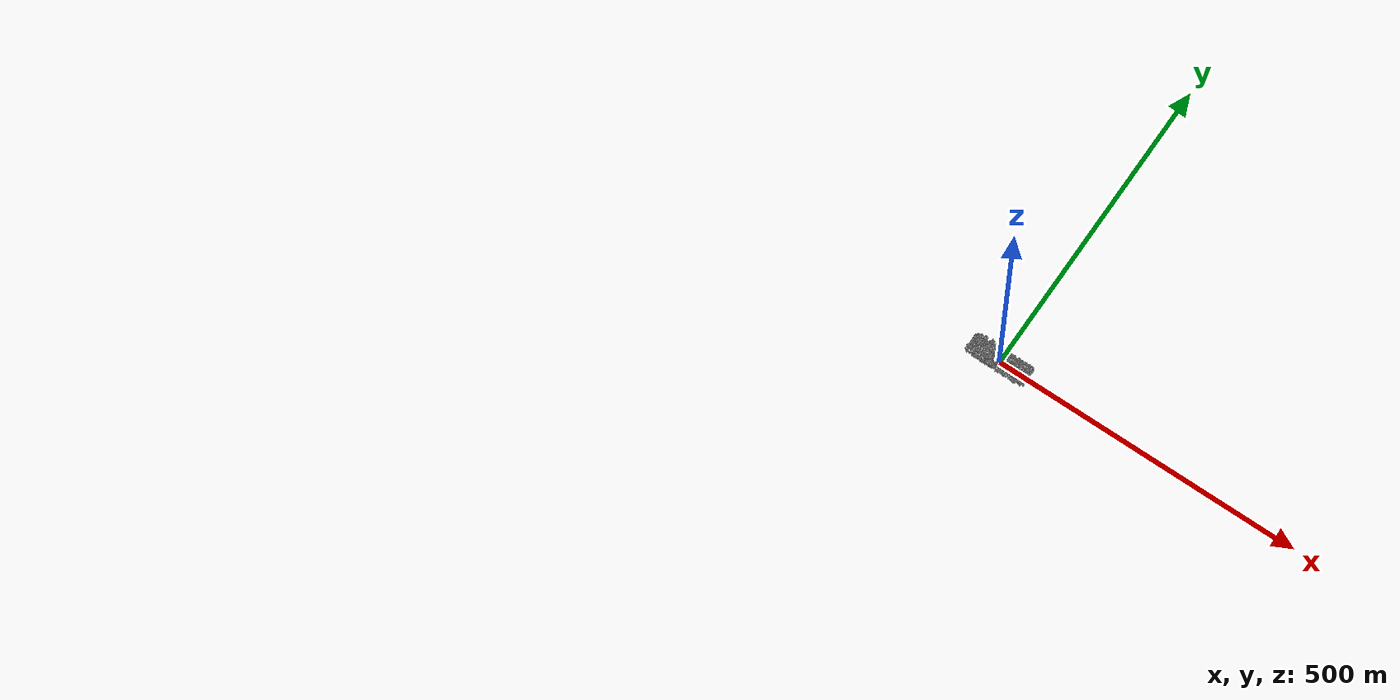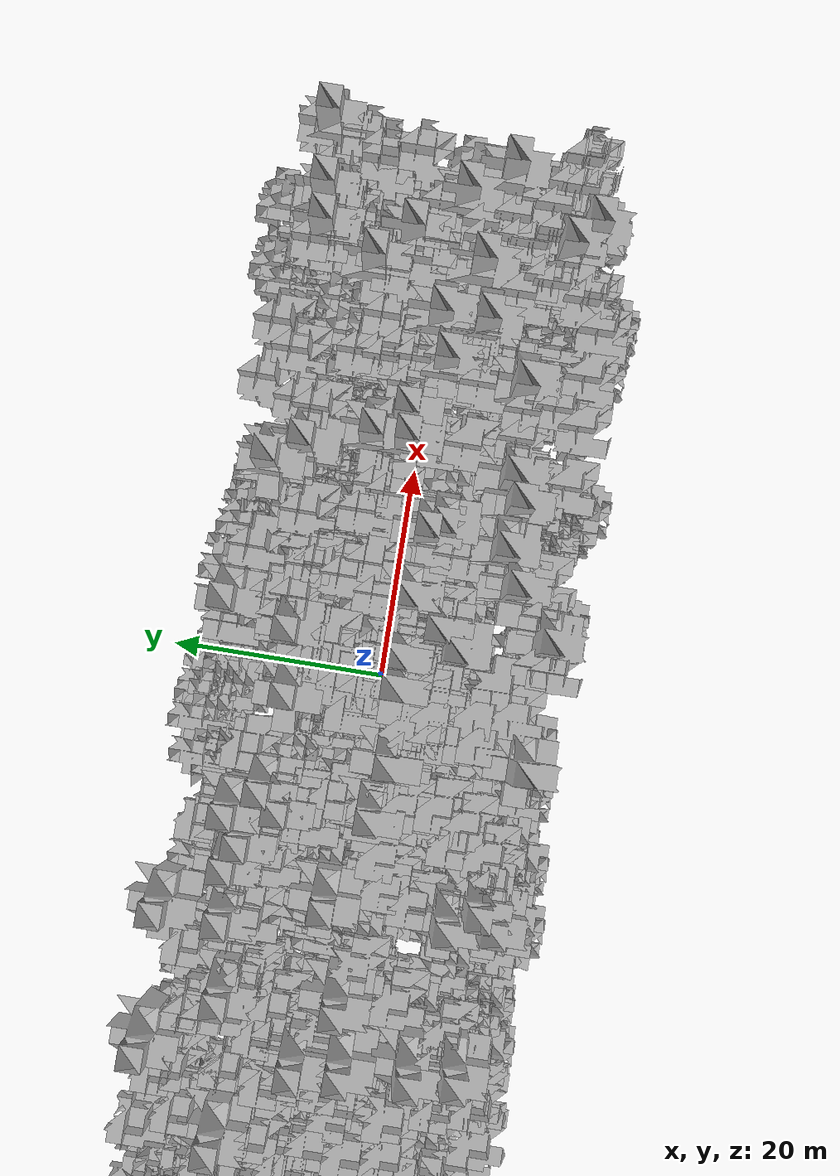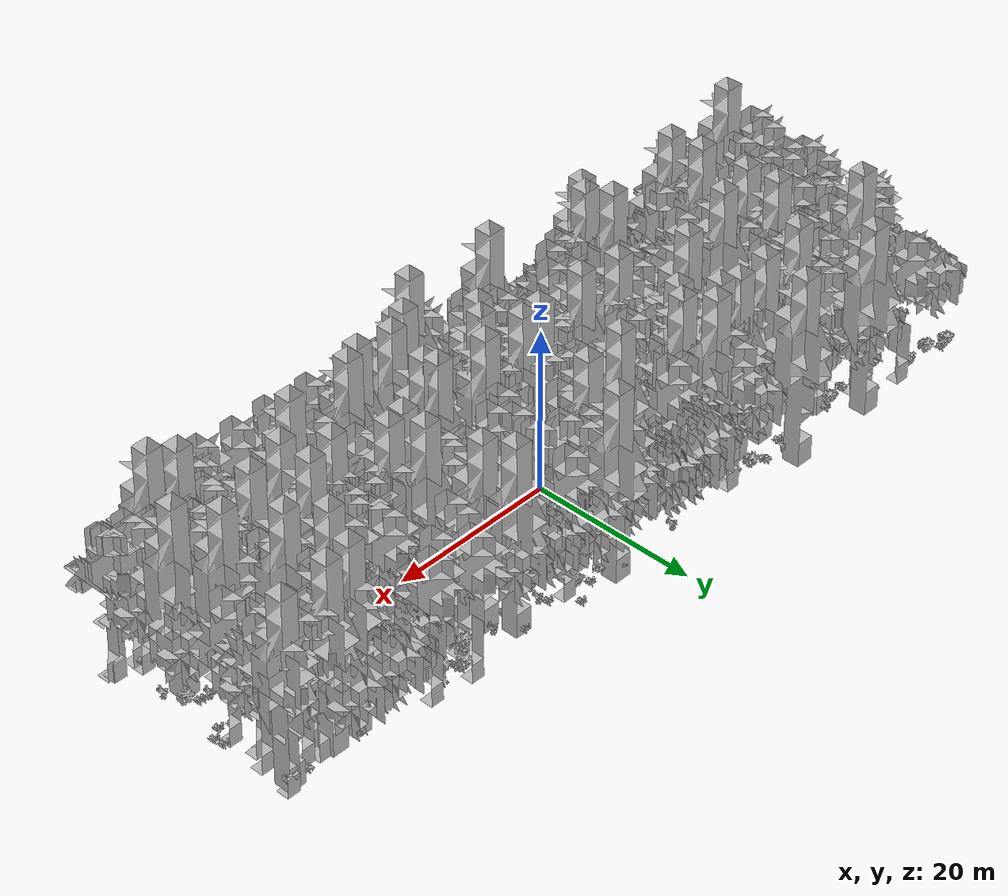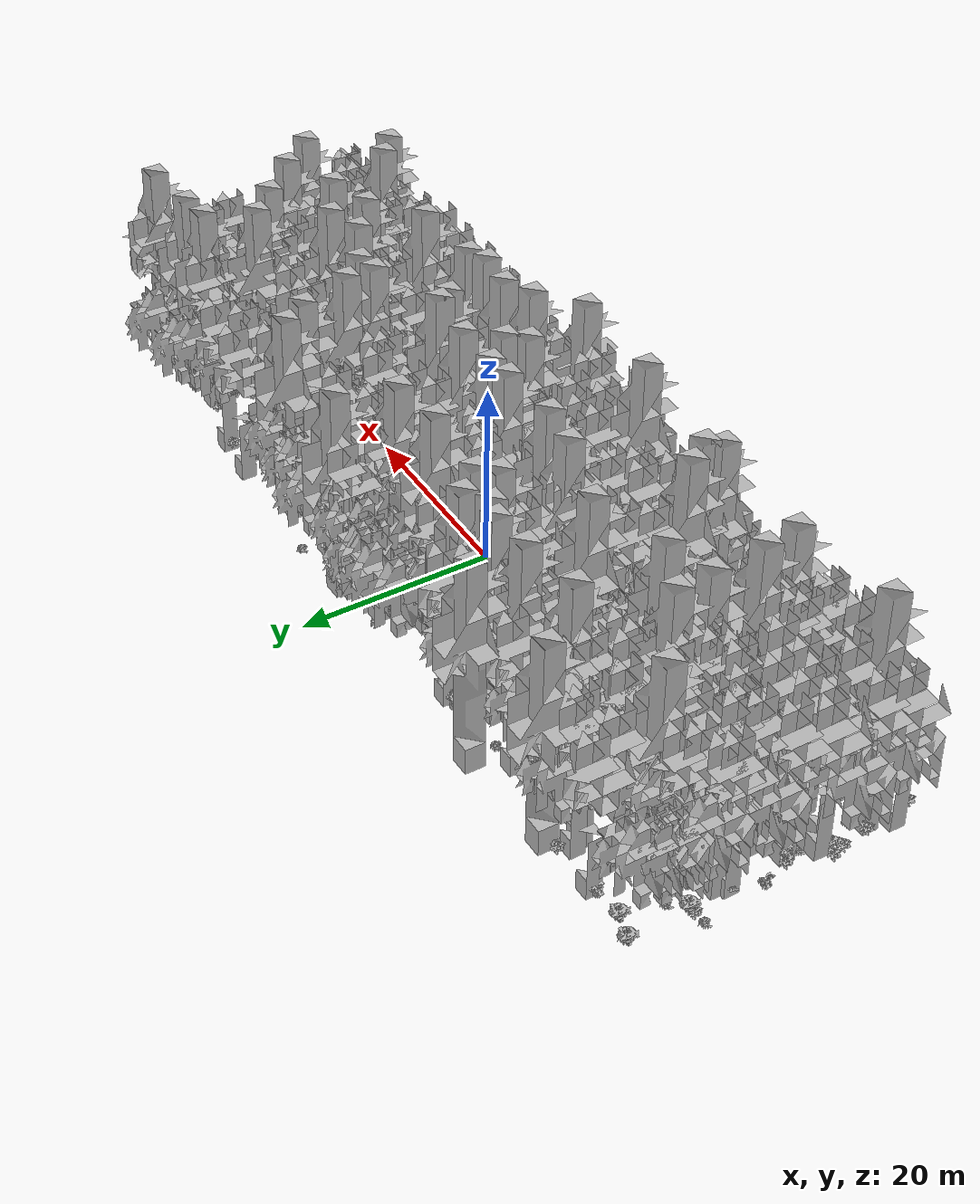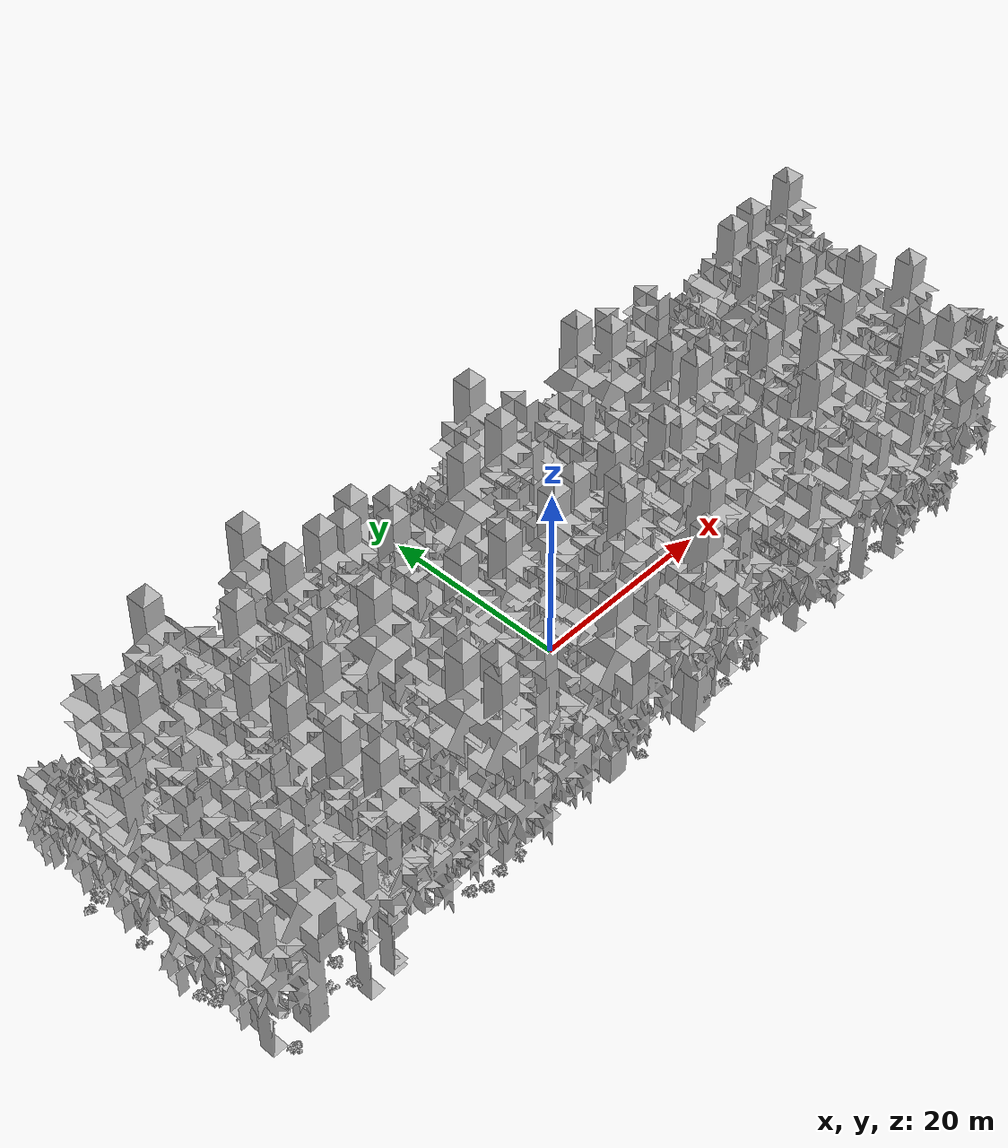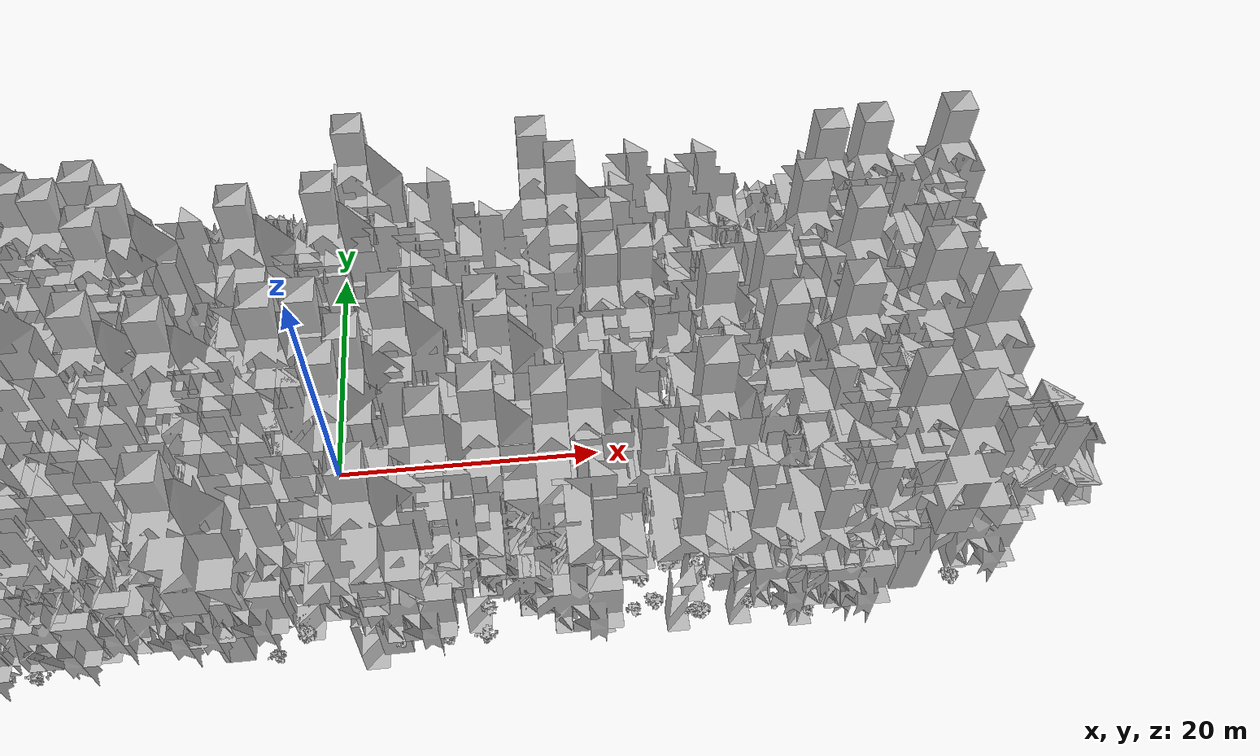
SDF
<sdf version="1.7">
    <world name="default">
        <plugin name="mrs_gazebo_static_transform_republisher_plugin" filename="libMrsGazeboCommonResources_StaticTransformRepublisher.so"/>
        <spherical_coordinates>
            <surface_model>EARTH_WGS84</surface_model>
            <latitude_deg>47.3977</latitude_deg>
            <longitude_deg>8.54559</longitude_deg>
            <elevation>0</elevation>
            <heading_deg>0</heading_deg>
        </spherical_coordinates>
        <physics name="default_physics" default="0" type="ode">
            <ode>
                <solver>
                    <type>quick</type>
                    <iters>10</iters>
                    <sor>1.3</sor>
                    <use_dynamic_moi_rescaling>0</use_dynamic_moi_rescaling>
                </solver>
                <constraints>
                    <cfm>0</cfm>
                    <erp>0.2</erp>
                    <contact_max_correcting_vel>1000</contact_max_correcting_vel>
                    <contact_surface_layer>0.001</contact_surface_layer>
                </constraints>
            </ode>
            <max_step_size>0.004</max_step_size>
            <real_time_factor>1</real_time_factor>
            <real_time_update_rate>250</real_time_update_rate>
        </physics>
        <scene>
            <shadows>0</shadows>
            <ambient>0.4 0.4 0.4 1</ambient>
            <background>0.7 0.7 0.7 1</background>
        </scene>
        <light name="sun" type="directional">
            <pose>0 0 1000 0.4 0.2 0</pose>
            <diffuse>1 1 1 1</diffuse>
            <specular>0.6 0.6 0.6 1</specular>
            <direction>0.1 0.1 -0.9</direction>
            <attenuation>
                <range>20</range>
                <constant>0.5</constant>
                <linear>0.01</linear>
                <quadratic>0.001</quadratic>
            </attenuation>
            <cast_shadows>1</cast_shadows>
            <spot>
                <inner_angle>0</inner_angle>
                <outer_angle>0</outer_angle>
                <falloff>0</falloff>
            </spot>
        </light>
        <model name="ground_plane">
            <static>1</static>
            <link name="link">
                <collision name="collision">
                    <pose>0 0 0 0 -0 0</pose>
                    <geometry>
                        <plane>
                            <normal>0 0 1</normal>
                            <size>100 100</size>
                        </plane>
                    </geometry>
                    <surface>
                        <contact>
                            <ode>
                                <min_depth>0.01</min_depth>
                                <max_vel>0</max_vel>
                            </ode>
                        </contact>
                        <friction>
                            <ode/>
                            <torsional>
                                <ode/>
                            </torsional>
                        </friction>
                        <bounce/>
                    </surface>
                    <max_contacts>10</max_contacts>
                </collision>
                <visual name="grass">
                    <pose>0 0 0 0 -0 0</pose>
                    <cast_shadows>0</cast_shadows>
                    <geometry>
                        <mesh>
                            <scale>0.5814285714285714 0.18142857142857144 0.1</scale>
                            <uri>file://grass_plane/meshes/grass_plane.dae</uri>
                        </mesh>
                    </geometry>
                </visual>
                <self_collide>0</self_collide>
                <enable_wind>0</enable_wind>
                <kinematic>0</kinematic>
            </link>
        </model>
        <model name="the_void">
            <static>1</static>
            <link name="link">
                <pose>0 0 0.1 0 -0 0</pose>
                <visual name="the_void">
                    <pose>0 0 2 0 -0 0</pose>
                    <geometry>
                        <sphere>
                            <radius>0.25</radius>
                        </sphere>
                    </geometry>
                    <material>
                        <script>
                            <uri>file://media/materials/scripts/Gazebo.material</uri>
                            <name>Gazebo/Black</name>
                        </script>
                    </material>
                </visual>
                <self_collide>0</self_collide>
                <enable_wind>0</enable_wind>
                <kinematic>0</kinematic>
            </link>
            <pose>-1000 -1000 0 0 -0 0</pose>
        </model>
        <gui fullscreen="0">
            <camera name="camera">
                <pose>35.1577 98.6044 40.0204 0 0.407996 -1.99761</pose>
                <view_controller>orbit</view_controller>
                <projection_type>perspective</projection_type>
            </camera>
        </gui>
        <plugin name="mrs_gazebo_rviz_cam_synchronizer" filename="libMrsGazeboCommonResources_RvizCameraSynchronizer.so">
            <target_frame_id>gazebo_user_camera</target_frame_id>
            <world_origin_frame_id>uav1/gps_origin</world_origin_frame_id>
            <frame_to_follow>uav1</frame_to_follow>
        </plugin>
        <gravity>0 0 -9.8066</gravity>
        <magnetic_field>6e-06 2.3e-05 -4.2e-05</magnetic_field>
        <atmosphere type="adiabatic"/>
        <wind/>
        <model name="Tree 0">
            <static>1</static>
            <pose>-27.916679947603246 -0.864334923967558 0 1.57079 -0 0</pose>
            <link name="link">
                <pose>0 0 0 0 -0 0</pose>
                <collision name="collision">
                    <geometry>
                        <mesh>
                            <scale>3.5 5 3.5</scale>
                            <uri>model://tree_4/meshes/tree_4.obj</uri>
                        </mesh>
                    </geometry>
                    <max_contacts>10</max_contacts>
                    <surface>
                        <contact>
                            <ode/>
                        </contact>
                        <bounce/>
                        <friction>
                            <torsional>
                                <ode/>
                            </torsional>
                            <ode/>
                        </friction>
                    </surface>
                </collision>
                <visual name="visual">
                    <geometry>
                        <mesh>
                            <scale>3.5 5 3.5</scale>
                            <uri>model://tree_4/meshes/tree_4.obj</uri>
                        </mesh>
                    </geometry>
                </visual>
                <self_collide>0</self_collide>
                <enable_wind>0</enable_wind>
                <kinematic>0</kinematic>
            </link>
        </model>
        <model name="Tree 1">
            <static>1</static>
            <pose>0.11113853436378918 -5.2022430370179435 0 1.57079 -0 0</pose>
            <link name="link">
                <pose>0 0 0 0 -0 0</pose>
                <collision name="collision">
                    <geometry>
                        <mesh>
                            <scale>3.5 5 3.5</scale>
                            <uri>model://tree_9/meshes/tree_9.obj</uri>
                        </mesh>
                    </geometry>
                    <max_contacts>10</max_contacts>
                    <surface>
                        <contact>
                            <ode/>
                        </contact>
                        <bounce/>
                        <friction>
                            <torsional>
                                <ode/>
                            </torsional>
                            <ode/>
                        </friction>
                    </surface>
                </collision>
                <visual name="visual">
                    <geometry>
                        <mesh>
                            <scale>3.5 5 3.5</scale>
                            <uri>model://tree_9/meshes/tree_9.obj</uri>
                        </mesh>
                    </geometry>
                </visual>
                <self_collide>0</self_collide>
                <enable_wind>0</enable_wind>
                <kinematic>0</kinematic>
            </link>
        </model>
        <model name="Tree 2">
            <static>1</static>
            <pose>-11.0649128909362 -1.3359658038042035 0 1.57079 -0 0</pose>
            <link name="link">
                <pose>0 0 0 0 -0 0</pose>
                <collision name="collision">
                    <geometry>
                        <mesh>
                            <scale>3.5 5 3.5</scale>
                            <uri>model://tree_9/meshes/tree_9.obj</uri>
                        </mesh>
                    </geometry>
                    <max_contacts>10</max_contacts>
                    <surface>
                        <contact>
                            <ode/>
                        </contact>
                        <bounce/>
                        <friction>
                            <torsional>
                                <ode/>
                            </torsional>
                            <ode/>
                        </friction>
                    </surface>
                </collision>
                <visual name="visual">
                    <geometry>
                        <mesh>
                            <scale>3.5 5 3.5</scale>
                            <uri>model://tree_9/meshes/tree_9.obj</uri>
                        </mesh>
                    </geometry>
                </visual>
                <self_collide>0</self_collide>
                <enable_wind>0</enable_wind>
                <kinematic>0</kinematic>
            </link>
        </model>
        <model name="Tree 3">
            <static>1</static>
            <pose>5.476249976549731 -2.4815436524672148 0 1.57079 -0 0</pose>
            <link name="link">
                <pose>0 0 0 0 -0 0</pose>
                <collision name="collision">
                    <geometry>
                        <mesh>
                            <scale>3.5 5 3.5</scale>
                            <uri>model://tree_9/meshes/tree_9.obj</uri>
                        </mesh>
                    </geometry>
                    <max_contacts>10</max_contacts>
                    <surface>
                        <contact>
                            <ode/>
                        </contact>
                        <bounce/>
                        <friction>
                            <torsional>
                                <ode/>
                            </torsional>
                            <ode/>
                        </friction>
                    </surface>
                </collision>
                <visual name="visual">
                    <geometry>
                        <mesh>
                            <scale>3.5 5 3.5</scale>
                            <uri>model://tree_9/meshes/tree_9.obj</uri>
                        </mesh>
                    </geometry>
                </visual>
                <self_collide>0</self_collide>
                <enable_wind>0</enable_wind>
                <kinematic>0</kinematic>
            </link>
        </model>
        <model name="Tree 4">
            <static>1</static>
            <pose>38.27493516273675 -7.548257788196791 0 1.57079 -0 0</pose>
            <link name="link">
                <pose>0 0 0 0 -0 0</pose>
                <collision name="collision">
                    <geometry>
                        <mesh>
                            <scale>3.5 5 3.5</scale>
                            <uri>model://tree_2/meshes/tree_2.obj</uri>
                        </mesh>
                    </geometry>
                    <max_contacts>10</max_contacts>
                    <surface>
                        <contact>
                            <ode/>
                        </contact>
                        <bounce/>
                        <friction>
                            <torsional>
                                <ode/>
                            </torsional>
                            <ode/>
                        </friction>
                    </surface>
                </collision>
                <visual name="visual">
                    <geometry>
                        <mesh>
                            <scale>3.5 5 3.5</scale>
                            <uri>model://tree_2/meshes/tree_2.obj</uri>
                        </mesh>
                    </geometry>
                </visual>
                <self_collide>0</self_collide>
                <enable_wind>0</enable_wind>
                <kinematic>0</kinematic>
            </link>
        </model>
        <model name="Tree 5">
            <static>1</static>
            <pose>35.713742004815415 14.597257240892898 0 1.57079 -0 0</pose>
            <link name="link">
                <pose>0 0 0 0 -0 0</pose>
                <collision name="collision">
                    <geometry>
                        <mesh>
                            <scale>3.5 5 3.5</scale>
                            <uri>model://tree_2/meshes/tree_2.obj</uri>
                        </mesh>
                    </geometry>
                    <max_contacts>10</max_contacts>
                    <surface>
                        <contact>
                            <ode/>
                        </contact>
                        <bounce/>
                        <friction>
                            <torsional>
                                <ode/>
                            </torsional>
                            <ode/>
                        </friction>
                    </surface>
                </collision>
                <visual name="visual">
                    <geometry>
                        <mesh>
                            <scale>3.5 5 3.5</scale>
                            <uri>model://tree_2/meshes/tree_2.obj</uri>
                        </mesh>
                    </geometry>
                </visual>
                <self_collide>0</self_collide>
                <enable_wind>0</enable_wind>
                <kinematic>0</kinematic>
            </link>
        </model>
        <model name="Tree 6">
            <static>1</static>
            <pose>-33.216674035426486 1.9118461626862846 0 1.57079 -0 0</pose>
            <link name="link">
                <pose>0 0 0 0 -0 0</pose>
                <collision name="collision">
                    <geometry>
                        <mesh>
                            <scale>3.5 5 3.5</scale>
                            <uri>model://tree_4/meshes/tree_4.obj</uri>
                        </mesh>
                    </geometry>
                    <max_contacts>10</max_contacts>
                    <surface>
                        <contact>
                            <ode/>
                        </contact>
                        <bounce/>
                        <friction>
                            <torsional>
                                <ode/>
                            </torsional>
                            <ode/>
                        </friction>
                    </surface>
                </collision>
                <visual name="visual">
                    <geometry>
                        <mesh>
                            <scale>3.5 5 3.5</scale>
                            <uri>model://tree_4/meshes/tree_4.obj</uri>
                        </mesh>
                    </geometry>
                </visual>
                <self_collide>0</self_collide>
                <enable_wind>0</enable_wind>
                <kinematic>0</kinematic>
            </link>
        </model>
        <model name="Tree 7">
            <static>1</static>
            <pose>-37.02748500600414 5.943462525791755 0 1.57079 -0 0</pose>
            <link name="link">
                <pose>0 0 0 0 -0 0</pose>
                <collision name="collision">
                    <geometry>
                        <mesh>
                            <scale>3.5 5 3.5</scale>
                            <uri>model://tree_2/meshes/tree_2.obj</uri>
                        </mesh>
                    </geometry>
                    <max_contacts>10</max_contacts>
                    <surface>
                        <contact>
                            <ode/>
                        </contact>
                        <bounce/>
                        <friction>
                            <torsional>
                                <ode/>
                            </torsional>
                            <ode/>
                        </friction>
                    </surface>
                </collision>
                <visual name="visual">
                    <geometry>
                        <mesh>
                            <scale>3.5 5 3.5</scale>
                            <uri>model://tree_2/meshes/tree_2.obj</uri>
                        </mesh>
                    </geometry>
                </visual>
                <self_collide>0</self_collide>
                <enable_wind>0</enable_wind>
                <kinematic>0</kinematic>
            </link>
        </model>
        <model name="Tree 8">
            <static>1</static>
            <pose>-42.26341744368104 1.5908221257960555 0 1.57079 -0 0</pose>
            <link name="link">
                <pose>0 0 0 0 -0 0</pose>
                <collision name="collision">
                    <geometry>
                        <mesh>
                            <scale>3.5 5 3.5</scale>
                            <uri>model://tree_9/meshes/tree_9.obj</uri>
                        </mesh>
                    </geometry>
                    <max_contacts>10</max_contacts>
                    <surface>
                        <contact>
                            <ode/>
                        </contact>
                        <bounce/>
                        <friction>
                            <torsional>
                                <ode/>
                            </torsional>
                            <ode/>
                        </friction>
                    </surface>
                </collision>
                <visual name="visual">
                    <geometry>
                        <mesh>
                            <scale>3.5 5 3.5</scale>
                            <uri>model://tree_9/meshes/tree_9.obj</uri>
                        </mesh>
                    </geometry>
                </visual>
                <self_collide>0</self_collide>
                <enable_wind>0</enable_wind>
                <kinematic>0</kinematic>
            </link>
        </model>
        <model name="Tree 9">
            <static>1</static>
            <pose>-26.89335764749784 -4.330637260092631 0 1.57079 -0 0</pose>
            <link name="link">
                <pose>0 0 0 0 -0 0</pose>
                <collision name="collision">
                    <geometry>
                        <mesh>
                            <scale>3.5 5 3.5</scale>
                            <uri>model://tree_2/meshes/tree_2.obj</uri>
                        </mesh>
                    </geometry>
                    <max_contacts>10</max_contacts>
                    <surface>
                        <contact>
                            <ode/>
                        </contact>
                        <bounce/>
                        <friction>
                            <torsional>
                                <ode/>
                            </torsional>
                            <ode/>
                        </friction>
                    </surface>
                </collision>
                <visual name="visual">
                    <geometry>
                        <mesh>
                            <scale>3.5 5 3.5</scale>
                            <uri>model://tree_2/meshes/tree_2.obj</uri>
                        </mesh>
                    </geometry>
                </visual>
                <self_collide>0</self_collide>
                <enable_wind>0</enable_wind>
                <kinematic>0</kinematic>
            </link>
        </model>
        <model name="Tree 10">
            <static>1</static>
            <pose>28.569949993472278 -3.9854584433061273 0 1.57079 -0 0</pose>
            <link name="link">
                <pose>0 0 0 0 -0 0</pose>
                <collision name="collision">
                    <geometry>
                        <mesh>
                            <scale>3.5 5 3.5</scale>
                            <uri>model://tree_9/meshes/tree_9.obj</uri>
                        </mesh>
                    </geometry>
                    <max_contacts>10</max_contacts>
                    <surface>
                        <contact>
                            <ode/>
                        </contact>
                        <bounce/>
                        <friction>
                            <torsional>
                                <ode/>
                            </torsional>
                            <ode/>
                        </friction>
                    </surface>
                </collision>
                <visual name="visual">
                    <geometry>
                        <mesh>
                            <scale>3.5 5 3.5</scale>
                            <uri>model://tree_9/meshes/tree_9.obj</uri>
                        </mesh>
                    </geometry>
                </visual>
                <self_collide>0</self_collide>
                <enable_wind>0</enable_wind>
                <kinematic>0</kinematic>
            </link>
        </model>
        <model name="Tree 11">
            <static>1</static>
            <pose>-27.164295356093064 7.0495500188012485 0 1.57079 -0 0</pose>
            <link name="link">
                <pose>0 0 0 0 -0 0</pose>
                <collision name="collision">
                    <geometry>
                        <mesh>
                            <scale>3.5 5 3.5</scale>
                            <uri>model://tree_9/meshes/tree_9.obj</uri>
                        </mesh>
                    </geometry>
                    <max_contacts>10</max_contacts>
                    <surface>
                        <contact>
                            <ode/>
                        </contact>
                        <bounce/>
                        <friction>
                            <torsional>
                                <ode/>
                            </torsional>
                            <ode/>
                        </friction>
                    </surface>
                </collision>
                <visual name="visual">
                    <geometry>
                        <mesh>
                            <scale>3.5 5 3.5</scale>
                            <uri>model://tree_9/meshes/tree_9.obj</uri>
                        </mesh>
                    </geometry>
                </visual>
                <self_collide>0</self_collide>
                <enable_wind>0</enable_wind>
                <kinematic>0</kinematic>
            </link>
        </model>
        <model name="Tree 12">
            <static>1</static>
            <pose>38.96880676785882 -12.078393965808754 0 1.57079 -0 0</pose>
            <link name="link">
                <pose>0 0 0 0 -0 0</pose>
                <collision name="collision">
                    <geometry>
                        <mesh>
                            <scale>3.5 5 3.5</scale>
                            <uri>model://tree_9/meshes/tree_9.obj</uri>
                        </mesh>
                    </geometry>
                    <max_contacts>10</max_contacts>
                    <surface>
                        <contact>
                            <ode/>
                        </contact>
                        <bounce/>
                        <friction>
                            <torsional>
                                <ode/>
                            </torsional>
                            <ode/>
                        </friction>
                    </surface>
                </collision>
                <visual name="visual">
                    <geometry>
                        <mesh>
                            <scale>3.5 5 3.5</scale>
                            <uri>model://tree_9/meshes/tree_9.obj</uri>
                        </mesh>
                    </geometry>
                </visual>
                <self_collide>0</self_collide>
                <enable_wind>0</enable_wind>
                <kinematic>0</kinematic>
            </link>
        </model>
        <model name="Tree 13">
            <static>1</static>
            <pose>43.086961047620065 -9.127918799912695 0 1.57079 -0 0</pose>
            <link name="link">
                <pose>0 0 0 0 -0 0</pose>
                <collision name="collision">
                    <geometry>
                        <mesh>
                            <scale>3.5 5 3.5</scale>
                            <uri>model://tree_9/meshes/tree_9.obj</uri>
                        </mesh>
                    </geometry>
                    <max_contacts>10</max_contacts>
                    <surface>
                        <contact>
                            <ode/>
                        </contact>
                        <bounce/>
                        <friction>
                            <torsional>
                                <ode/>
                            </torsional>
                            <ode/>
                        </friction>
                    </surface>
                </collision>
                <visual name="visual">
                    <geometry>
                        <mesh>
                            <scale>3.5 5 3.5</scale>
                            <uri>model://tree_9/meshes/tree_9.obj</uri>
                        </mesh>
                    </geometry>
                </visual>
                <self_collide>0</self_collide>
                <enable_wind>0</enable_wind>
                <kinematic>0</kinematic>
            </link>
        </model>
        <model name="Tree 14">
            <static>1</static>
            <pose>-31.80681430986856 -11.453123347204002 0 1.57079 -0 0</pose>
            <link name="link">
                <pose>0 0 0 0 -0 0</pose>
                <collision name="collision">
                    <geometry>
                        <mesh>
                            <scale>3.5 5 3.5</scale>
                            <uri>model://tree_4/meshes/tree_4.obj</uri>
                        </mesh>
                    </geometry>
                    <max_contacts>10</max_contacts>
                    <surface>
                        <contact>
                            <ode/>
                        </contact>
                        <bounce/>
                        <friction>
                            <torsional>
                                <ode/>
                            </torsional>
                            <ode/>
                        </friction>
                    </surface>
                </collision>
                <visual name="visual">
                    <geometry>
                        <mesh>
                            <scale>3.5 5 3.5</scale>
                            <uri>model://tree_4/meshes/tree_4.obj</uri>
                        </mesh>
                    </geometry>
                </visual>
                <self_collide>0</self_collide>
                <enable_wind>0</enable_wind>
                <kinematic>0</kinematic>
            </link>
        </model>
        <model name="Tree 15">
            <static>1</static>
            <pose>4.243417663001956 13.656715987898252 0 1.57079 -0 0</pose>
            <link name="link">
                <pose>0 0 0 0 -0 0</pose>
                <collision name="collision">
                    <geometry>
                        <mesh>
                            <scale>3.5 5 3.5</scale>
                            <uri>model://tree_4/meshes/tree_4.obj</uri>
                        </mesh>
                    </geometry>
                    <max_contacts>10</max_contacts>
                    <surface>
                        <contact>
                            <ode/>
                        </contact>
                        <bounce/>
                        <friction>
                            <torsional>
                                <ode/>
                            </torsional>
                            <ode/>
                        </friction>
                    </surface>
                </collision>
                <visual name="visual">
                    <geometry>
                        <mesh>
                            <scale>3.5 5 3.5</scale>
                            <uri>model://tree_4/meshes/tree_4.obj</uri>
                        </mesh>
                    </geometry>
                </visual>
                <self_collide>0</self_collide>
                <enable_wind>0</enable_wind>
                <kinematic>0</kinematic>
            </link>
        </model>
        <model name="Tree 16">
            <static>1</static>
            <pose>13.27778693210037 -11.897766273142134 0 1.57079 -0 0</pose>
            <link name="link">
                <pose>0 0 0 0 -0 0</pose>
                <collision name="collision">
                    <geometry>
                        <mesh>
                            <scale>3.5 5 3.5</scale>
                            <uri>model://tree_2/meshes/tree_2.obj</uri>
                        </mesh>
                    </geometry>
                    <max_contacts>10</max_contacts>
                    <surface>
                        <contact>
                            <ode/>
                        </contact>
                        <bounce/>
                        <friction>
                            <torsional>
                                <ode/>
                            </torsional>
                            <ode/>
                        </friction>
                    </surface>
                </collision>
                <visual name="visual">
                    <geometry>
                        <mesh>
                            <scale>3.5 5 3.5</scale>
                            <uri>model://tree_2/meshes/tree_2.obj</uri>
                        </mesh>
                    </geometry>
                </visual>
                <self_collide>0</self_collide>
                <enable_wind>0</enable_wind>
                <kinematic>0</kinematic>
            </link>
        </model>
        <model name="Tree 17">
            <static>1</static>
            <pose>-38.11614056664186 1.3759694158396307 0 1.57079 -0 0</pose>
            <link name="link">
                <pose>0 0 0 0 -0 0</pose>
                <collision name="collision">
                    <geometry>
                        <mesh>
                            <scale>3.5 5 3.5</scale>
                            <uri>model://tree_2/meshes/tree_2.obj</uri>
                        </mesh>
                    </geometry>
                    <max_contacts>10</max_contacts>
                    <surface>
                        <contact>
                            <ode/>
                        </contact>
                        <bounce/>
                        <friction>
                            <torsional>
                                <ode/>
                            </torsional>
                            <ode/>
                        </friction>
                    </surface>
                </collision>
                <visual name="visual">
                    <geometry>
                        <mesh>
                            <scale>3.5 5 3.5</scale>
                            <uri>model://tree_2/meshes/tree_2.obj</uri>
                        </mesh>
                    </geometry>
                </visual>
                <self_collide>0</self_collide>
                <enable_wind>0</enable_wind>
                <kinematic>0</kinematic>
            </link>
        </model>
        <model name="Tree 18">
            <static>1</static>
            <pose>6.053985852618446 -4.687670453976763 0 1.57079 -0 0</pose>
            <link name="link">
                <pose>0 0 0 0 -0 0</pose>
                <collision name="collision">
                    <geometry>
                        <mesh>
                            <scale>3.5 5 3.5</scale>
                            <uri>model://tree_9/meshes/tree_9.obj</uri>
                        </mesh>
                    </geometry>
                    <max_contacts>10</max_contacts>
                    <surface>
                        <contact>
                            <ode/>
                        </contact>
                        <bounce/>
                        <friction>
                            <torsional>
                                <ode/>
                            </torsional>
                            <ode/>
                        </friction>
                    </surface>
                </collision>
                <visual name="visual">
                    <geometry>
                        <mesh>
                            <scale>3.5 5 3.5</scale>
                            <uri>model://tree_9/meshes/tree_9.obj</uri>
                        </mesh>
                    </geometry>
                </visual>
                <self_collide>0</self_collide>
                <enable_wind>0</enable_wind>
                <kinematic>0</kinematic>
            </link>
        </model>
        <model name="Tree 19">
            <static>1</static>
            <pose>-3.428938288911354 1.88049050284922 0 1.57079 -0 0</pose>
            <link name="link">
                <pose>0 0 0 0 -0 0</pose>
                <collision name="collision">
                    <geometry>
                        <mesh>
                            <scale>3.5 5 3.5</scale>
                            <uri>model://tree_9/meshes/tree_9.obj</uri>
                        </mesh>
                    </geometry>
                    <max_contacts>10</max_contacts>
                    <surface>
                        <contact>
                            <ode/>
                        </contact>
                        <bounce/>
                        <friction>
                            <torsional>
                                <ode/>
                            </torsional>
                            <ode/>
                        </friction>
                    </surface>
                </collision>
                <visual name="visual">
                    <geometry>
                        <mesh>
                            <scale>3.5 5 3.5</scale>
                            <uri>model://tree_9/meshes/tree_9.obj</uri>
                        </mesh>
                    </geometry>
                </visual>
                <self_collide>0</self_collide>
                <enable_wind>0</enable_wind>
                <kinematic>0</kinematic>
            </link>
        </model>
        <model name="Tree 20">
            <static>1</static>
            <pose>8.884630411769677 6.5836078916530845 0 1.57079 -0 0</pose>
            <link name="link">
                <pose>0 0 0 0 -0 0</pose>
                <collision name="collision">
                    <geometry>
                        <mesh>
                            <scale>3.5 5 3.5</scale>
                            <uri>model://tree_9/meshes/tree_9.obj</uri>
                        </mesh>
                    </geometry>
                    <max_contacts>10</max_contacts>
                    <surface>
                        <contact>
                            <ode/>
                        </contact>
                        <bounce/>
                        <friction>
                            <torsional>
                                <ode/>
                            </torsional>
                            <ode/>
                        </friction>
                    </surface>
                </collision>
                <visual name="visual">
                    <geometry>
                        <mesh>
                            <scale>3.5 5 3.5</scale>
                            <uri>model://tree_9/meshes/tree_9.obj</uri>
                        </mesh>
                    </geometry>
                </visual>
                <self_collide>0</self_collide>
                <enable_wind>0</enable_wind>
                <kinematic>0</kinematic>
            </link>
        </model>
        <model name="Tree 21">
            <static>1</static>
            <pose>1.1179065578854477 -3.695320356030459 0 1.57079 -0 0</pose>
            <link name="link">
                <pose>0 0 0 0 -0 0</pose>
                <collision name="collision">
                    <geometry>
                        <mesh>
                            <scale>3.5 5 3.5</scale>
                            <uri>model://tree_9/meshes/tree_9.obj</uri>
                        </mesh>
                    </geometry>
                    <max_contacts>10</max_contacts>
                    <surface>
                        <contact>
                            <ode/>
                        </contact>
                        <bounce/>
                        <friction>
                            <torsional>
                                <ode/>
                            </torsional>
                            <ode/>
                        </friction>
                    </surface>
                </collision>
                <visual name="visual">
                    <geometry>
                        <mesh>
                            <scale>3.5 5 3.5</scale>
                            <uri>model://tree_9/meshes/tree_9.obj</uri>
                        </mesh>
                    </geometry>
                </visual>
                <self_collide>0</self_collide>
                <enable_wind>0</enable_wind>
                <kinematic>0</kinematic>
            </link>
        </model>
        <model name="Tree 22">
            <static>1</static>
            <pose>39.07673374363392 -10.720581911101826 0 1.57079 -0 0</pose>
            <link name="link">
                <pose>0 0 0 0 -0 0</pose>
                <collision name="collision">
                    <geometry>
                        <mesh>
                            <scale>3.5 5 3.5</scale>
                            <uri>model://tree_4/meshes/tree_4.obj</uri>
                        </mesh>
                    </geometry>
                    <max_contacts>10</max_contacts>
                    <surface>
                        <contact>
                            <ode/>
                        </contact>
                        <bounce/>
                        <friction>
                            <torsional>
                                <ode/>
                            </torsional>
                            <ode/>
                        </friction>
                    </surface>
                </collision>
                <visual name="visual">
                    <geometry>
                        <mesh>
                            <scale>3.5 5 3.5</scale>
                            <uri>model://tree_4/meshes/tree_4.obj</uri>
                        </mesh>
                    </geometry>
                </visual>
                <self_collide>0</self_collide>
                <enable_wind>0</enable_wind>
                <kinematic>0</kinematic>
            </link>
        </model>
        <model name="Tree 23">
            <static>1</static>
            <pose>-10.539529069901036 9.728312270743949 0 1.57079 -0 0</pose>
            <link name="link">
                <pose>0 0 0 0 -0 0</pose>
                <collision name="collision">
                    <geometry>
                        <mesh>
                            <scale>3.5 5 3.5</scale>
                            <uri>model://tree_2/meshes/tree_2.obj</uri>
                        </mesh>
                    </geometry>
                    <max_contacts>10</max_contacts>
                    <surface>
                        <contact>
                            <ode/>
                        </contact>
                        <bounce/>
                        <friction>
                            <torsional>
                                <ode/>
                            </torsional>
                            <ode/>
                        </friction>
                    </surface>
                </collision>
                <visual name="visual">
                    <geometry>
                        <mesh>
                            <scale>3.5 5 3.5</scale>
                            <uri>model://tree_2/meshes/tree_2.obj</uri>
                        </mesh>
                    </geometry>
                </visual>
                <self_collide>0</self_collide>
                <enable_wind>0</enable_wind>
                <kinematic>0</kinematic>
            </link>
        </model>
        <model name="Tree 24">
            <static>1</static>
            <pose>41.74323365666531 0.7387687377067191 0 1.57079 -0 0</pose>
            <link name="link">
                <pose>0 0 0 0 -0 0</pose>
                <collision name="collision">
                    <geometry>
                        <mesh>
                            <scale>3.5 5 3.5</scale>
                            <uri>model://tree_9/meshes/tree_9.obj</uri>
                        </mesh>
                    </geometry>
                    <max_contacts>10</max_contacts>
                    <surface>
                        <contact>
                            <ode/>
                        </contact>
                        <bounce/>
                        <friction>
                            <torsional>
                                <ode/>
                            </torsional>
                            <ode/>
                        </friction>
                    </surface>
                </collision>
                <visual name="visual">
                    <geometry>
                        <mesh>
                            <scale>3.5 5 3.5</scale>
                            <uri>model://tree_9/meshes/tree_9.obj</uri>
                        </mesh>
                    </geometry>
                </visual>
                <self_collide>0</self_collide>
                <enable_wind>0</enable_wind>
                <kinematic>0</kinematic>
            </link>
        </model>
        <model name="Tree 25">
            <static>1</static>
            <pose>-47.05094535269379 -12.458843583651134 0 1.57079 -0 0</pose>
            <link name="link">
                <pose>0 0 0 0 -0 0</pose>
                <collision name="collision">
                    <geometry>
                        <mesh>
                            <scale>3.5 5 3.5</scale>
                            <uri>model://tree_9/meshes/tree_9.obj</uri>
                        </mesh>
                    </geometry>
                    <max_contacts>10</max_contacts>
                    <surface>
                        <contact>
                            <ode/>
                        </contact>
                        <bounce/>
                        <friction>
                            <torsional>
                                <ode/>
                            </torsional>
                            <ode/>
                        </friction>
                    </surface>
                </collision>
                <visual name="visual">
                    <geometry>
                        <mesh>
                            <scale>3.5 5 3.5</scale>
                            <uri>model://tree_9/meshes/tree_9.obj</uri>
                        </mesh>
                    </geometry>
                </visual>
                <self_collide>0</self_collide>
                <enable_wind>0</enable_wind>
                <kinematic>0</kinematic>
            </link>
        </model>
        <model name="Tree 26">
            <static>1</static>
            <pose>-41.89706193309854 -6.823377723736916 0 1.57079 -0 0</pose>
            <link name="link">
                <pose>0 0 0 0 -0 0</pose>
                <collision name="collision">
                    <geometry>
                        <mesh>
                            <scale>3.5 5 3.5</scale>
                            <uri>model://tree_9/meshes/tree_9.obj</uri>
                        </mesh>
                    </geometry>
                    <max_contacts>10</max_contacts>
                    <surface>
                        <contact>
                            <ode/>
                        </contact>
                        <bounce/>
                        <friction>
                            <torsional>
                                <ode/>
                            </torsional>
                            <ode/>
                        </friction>
                    </surface>
                </collision>
                <visual name="visual">
                    <geometry>
                        <mesh>
                            <scale>3.5 5 3.5</scale>
                            <uri>model://tree_9/meshes/tree_9.obj</uri>
                        </mesh>
                    </geometry>
                </visual>
                <self_collide>0</self_collide>
                <enable_wind>0</enable_wind>
                <kinematic>0</kinematic>
            </link>
        </model>
        <model name="Tree 27">
            <static>1</static>
            <pose>34.32430059708736 13.774492211939243 0 1.57079 -0 0</pose>
            <link name="link">
                <pose>0 0 0 0 -0 0</pose>
                <collision name="collision">
                    <geometry>
                        <mesh>
                            <scale>3.5 5 3.5</scale>
                            <uri>model://tree_2/meshes/tree_2.obj</uri>
                        </mesh>
                    </geometry>
                    <max_contacts>10</max_contacts>
                    <surface>
                        <contact>
                            <ode/>
                        </contact>
                        <bounce/>
                        <friction>
                            <torsional>
                                <ode/>
                            </torsional>
                            <ode/>
                        </friction>
                    </surface>
                </collision>
                <visual name="visual">
                    <geometry>
                        <mesh>
                            <scale>3.5 5 3.5</scale>
                            <uri>model://tree_2/meshes/tree_2.obj</uri>
                        </mesh>
                    </geometry>
                </visual>
                <self_collide>0</self_collide>
                <enable_wind>0</enable_wind>
                <kinematic>0</kinematic>
            </link>
        </model>
        <model name="Tree 28">
            <static>1</static>
            <pose>-14.41020064280336 7.16225239467127 0 1.57079 -0 0</pose>
            <link name="link">
                <pose>0 0 0 0 -0 0</pose>
                <collision name="collision">
                    <geometry>
                        <mesh>
                            <scale>3.5 5 3.5</scale>
                            <uri>model://tree_9/meshes/tree_9.obj</uri>
                        </mesh>
                    </geometry>
                    <max_contacts>10</max_contacts>
                    <surface>
                        <contact>
                            <ode/>
                        </contact>
                        <bounce/>
                        <friction>
                            <torsional>
                                <ode/>
                            </torsional>
                            <ode/>
                        </friction>
                    </surface>
                </collision>
                <visual name="visual">
                    <geometry>
                        <mesh>
                            <scale>3.5 5 3.5</scale>
                            <uri>model://tree_9/meshes/tree_9.obj</uri>
                        </mesh>
                    </geometry>
                </visual>
                <self_collide>0</self_collide>
                <enable_wind>0</enable_wind>
                <kinematic>0</kinematic>
            </link>
        </model>
        <model name="Tree 29">
            <static>1</static>
            <pose>-25.047930650477866 12.277151410198769 0 1.57079 -0 0</pose>
            <link name="link">
                <pose>0 0 0 0 -0 0</pose>
                <collision name="collision">
                    <geometry>
                        <mesh>
                            <scale>3.5 5 3.5</scale>
                            <uri>model://tree_9/meshes/tree_9.obj</uri>
                        </mesh>
                    </geometry>
                    <max_contacts>10</max_contacts>
                    <surface>
                        <contact>
                            <ode/>
                        </contact>
                        <bounce/>
                        <friction>
                            <torsional>
                                <ode/>
                            </torsional>
                            <ode/>
                        </friction>
                    </surface>
                </collision>
                <visual name="visual">
                    <geometry>
                        <mesh>
                            <scale>3.5 5 3.5</scale>
                            <uri>model://tree_9/meshes/tree_9.obj</uri>
                        </mesh>
                    </geometry>
                </visual>
                <self_collide>0</self_collide>
                <enable_wind>0</enable_wind>
                <kinematic>0</kinematic>
            </link>
        </model>
        <model name="Tree 30">
            <static>1</static>
            <pose>33.460468468772774 6.393462766625621 0 1.57079 -0 0</pose>
            <link name="link">
                <pose>0 0 0 0 -0 0</pose>
                <collision name="collision">
                    <geometry>
                        <mesh>
                            <scale>3.5 5 3.5</scale>
                            <uri>model://tree_2/meshes/tree_2.obj</uri>
                        </mesh>
                    </geometry>
                    <max_contacts>10</max_contacts>
                    <surface>
                        <contact>
                            <ode/>
                        </contact>
                        <bounce/>
                        <friction>
                            <torsional>
                                <ode/>
                            </torsional>
                            <ode/>
                        </friction>
                    </surface>
                </collision>
                <visual name="visual">
                    <geometry>
                        <mesh>
                            <scale>3.5 5 3.5</scale>
                            <uri>model://tree_2/meshes/tree_2.obj</uri>
                        </mesh>
                    </geometry>
                </visual>
                <self_collide>0</self_collide>
                <enable_wind>0</enable_wind>
                <kinematic>0</kinematic>
            </link>
        </model>
        <model name="Tree 31">
            <static>1</static>
            <pose>-1.4957072366649413 -4.576129310586122 0 1.57079 -0 0</pose>
            <link name="link">
                <pose>0 0 0 0 -0 0</pose>
                <collision name="collision">
                    <geometry>
                        <mesh>
                            <scale>3.5 5 3.5</scale>
                            <uri>model://tree_2/meshes/tree_2.obj</uri>
                        </mesh>
                    </geometry>
                    <max_contacts>10</max_contacts>
                    <surface>
                        <contact>
                            <ode/>
                        </contact>
                        <bounce/>
                        <friction>
                            <torsional>
                                <ode/>
                            </torsional>
                            <ode/>
                        </friction>
                    </surface>
                </collision>
                <visual name="visual">
                    <geometry>
                        <mesh>
                            <scale>3.5 5 3.5</scale>
                            <uri>model://tree_2/meshes/tree_2.obj</uri>
                        </mesh>
                    </geometry>
                </visual>
                <self_collide>0</self_collide>
                <enable_wind>0</enable_wind>
                <kinematic>0</kinematic>
            </link>
        </model>
        <model name="Tree 32">
            <static>1</static>
            <pose>41.65381926326293 -5.7250531337227315 0 1.57079 -0 0</pose>
            <link name="link">
                <pose>0 0 0 0 -0 0</pose>
                <collision name="collision">
                    <geometry>
                        <mesh>
                            <scale>3.5 5 3.5</scale>
                            <uri>model://tree_9/meshes/tree_9.obj</uri>
                        </mesh>
                    </geometry>
                    <max_contacts>10</max_contacts>
                    <surface>
                        <contact>
                            <ode/>
                        </contact>
                        <bounce/>
                        <friction>
                            <torsional>
                                <ode/>
                            </torsional>
                            <ode/>
                        </friction>
                    </surface>
                </collision>
                <visual name="visual">
                    <geometry>
                        <mesh>
                            <scale>3.5 5 3.5</scale>
                            <uri>model://tree_9/meshes/tree_9.obj</uri>
                        </mesh>
                    </geometry>
                </visual>
                <self_collide>0</self_collide>
                <enable_wind>0</enable_wind>
                <kinematic>0</kinematic>
            </link>
        </model>
        <model name="Tree 33">
            <static>1</static>
            <pose>6.900980407644802 -1.467559844220773 0 1.57079 -0 0</pose>
            <link name="link">
                <pose>0 0 0 0 -0 0</pose>
                <collision name="collision">
                    <geometry>
                        <mesh>
                            <scale>3.5 5 3.5</scale>
                            <uri>model://tree_4/meshes/tree_4.obj</uri>
                        </mesh>
                    </geometry>
                    <max_contacts>10</max_contacts>
                    <surface>
                        <contact>
                            <ode/>
                        </contact>
                        <bounce/>
                        <friction>
                            <torsional>
                                <ode/>
                            </torsional>
                            <ode/>
                        </friction>
                    </surface>
                </collision>
                <visual name="visual">
                    <geometry>
                        <mesh>
                            <scale>3.5 5 3.5</scale>
                            <uri>model://tree_4/meshes/tree_4.obj</uri>
                        </mesh>
                    </geometry>
                </visual>
                <self_collide>0</self_collide>
                <enable_wind>0</enable_wind>
                <kinematic>0</kinematic>
            </link>
        </model>
        <model name="Tree 34">
            <static>1</static>
            <pose>-16.393195477185976 8.384588368217223 0 1.57079 -0 0</pose>
            <link name="link">
                <pose>0 0 0 0 -0 0</pose>
                <collision name="collision">
                    <geometry>
                        <mesh>
                            <scale>3.5 5 3.5</scale>
                            <uri>model://tree_9/meshes/tree_9.obj</uri>
                        </mesh>
                    </geometry>
                    <max_contacts>10</max_contacts>
                    <surface>
                        <contact>
                            <ode/>
                        </contact>
                        <bounce/>
                        <friction>
                            <torsional>
                                <ode/>
                            </torsional>
                            <ode/>
                        </friction>
                    </surface>
                </collision>
                <visual name="visual">
                    <geometry>
                        <mesh>
                            <scale>3.5 5 3.5</scale>
                            <uri>model://tree_9/meshes/tree_9.obj</uri>
                        </mesh>
                    </geometry>
                </visual>
                <self_collide>0</self_collide>
                <enable_wind>0</enable_wind>
                <kinematic>0</kinematic>
            </link>
        </model>
        <model name="Tree 35">
            <static>1</static>
            <pose>32.20575930937464 -11.317423207755585 0 1.57079 -0 0</pose>
            <link name="link">
                <pose>0 0 0 0 -0 0</pose>
                <collision name="collision">
                    <geometry>
                        <mesh>
                            <scale>3.5 5 3.5</scale>
                            <uri>model://tree_2/meshes/tree_2.obj</uri>
                        </mesh>
                    </geometry>
                    <max_contacts>10</max_contacts>
                    <surface>
                        <contact>
                            <ode/>
                        </contact>
                        <bounce/>
                        <friction>
                            <torsional>
                                <ode/>
                            </torsional>
                            <ode/>
                        </friction>
                    </surface>
                </collision>
                <visual name="visual">
                    <geometry>
                        <mesh>
                            <scale>3.5 5 3.5</scale>
                            <uri>model://tree_2/meshes/tree_2.obj</uri>
                        </mesh>
                    </geometry>
                </visual>
                <self_collide>0</self_collide>
                <enable_wind>0</enable_wind>
                <kinematic>0</kinematic>
            </link>
        </model>
        <model name="Tree 36">
            <static>1</static>
            <pose>-46.50917269536042 -12.318930760456333 0 1.57079 -0 0</pose>
            <link name="link">
                <pose>0 0 0 0 -0 0</pose>
                <collision name="collision">
                    <geometry>
                        <mesh>
                            <scale>3.5 5 3.5</scale>
                            <uri>model://tree_2/meshes/tree_2.obj</uri>
                        </mesh>
                    </geometry>
                    <max_contacts>10</max_contacts>
                    <surface>
                        <contact>
                            <ode/>
                        </contact>
                        <bounce/>
                        <friction>
                            <torsional>
                                <ode/>
                            </torsional>
                            <ode/>
                        </friction>
                    </surface>
                </collision>
                <visual name="visual">
                    <geometry>
                        <mesh>
                            <scale>3.5 5 3.5</scale>
                            <uri>model://tree_2/meshes/tree_2.obj</uri>
                        </mesh>
                    </geometry>
                </visual>
                <self_collide>0</self_collide>
                <enable_wind>0</enable_wind>
                <kinematic>0</kinematic>
            </link>
        </model>
        <model name="Tree 37">
            <static>1</static>
            <pose>-15.541439748845285 10.894730508550747 0 1.57079 -0 0</pose>
            <link name="link">
                <pose>0 0 0 0 -0 0</pose>
                <collision name="collision">
                    <geometry>
                        <mesh>
                            <scale>3.5 5 3.5</scale>
                            <uri>model://tree_9/meshes/tree_9.obj</uri>
                        </mesh>
                    </geometry>
                    <max_contacts>10</max_contacts>
                    <surface>
                        <contact>
                            <ode/>
                        </contact>
                        <bounce/>
                        <friction>
                            <torsional>
                                <ode/>
                            </torsional>
                            <ode/>
                        </friction>
                    </surface>
                </collision>
                <visual name="visual">
                    <geometry>
                        <mesh>
                            <scale>3.5 5 3.5</scale>
                            <uri>model://tree_9/meshes/tree_9.obj</uri>
                        </mesh>
                    </geometry>
                </visual>
                <self_collide>0</self_collide>
                <enable_wind>0</enable_wind>
                <kinematic>0</kinematic>
            </link>
        </model>
        <model name="Tree 38">
            <static>1</static>
            <pose>20.81536354934164 -0.9336809488409585 0 1.57079 -0 0</pose>
            <link name="link">
                <pose>0 0 0 0 -0 0</pose>
                <collision name="collision">
                    <geometry>
                        <mesh>
                            <scale>3.5 5 3.5</scale>
                            <uri>model://tree_9/meshes/tree_9.obj</uri>
                        </mesh>
                    </geometry>
                    <max_contacts>10</max_contacts>
                    <surface>
                        <contact>
                            <ode/>
                        </contact>
                        <bounce/>
                        <friction>
                            <torsional>
                                <ode/>
                            </torsional>
                            <ode/>
                        </friction>
                    </surface>
                </collision>
                <visual name="visual">
                    <geometry>
                        <mesh>
                            <scale>3.5 5 3.5</scale>
                            <uri>model://tree_9/meshes/tree_9.obj</uri>
                        </mesh>
                    </geometry>
                </visual>
                <self_collide>0</self_collide>
                <enable_wind>0</enable_wind>
                <kinematic>0</kinematic>
            </link>
        </model>
        <model name="Tree 39">
            <static>1</static>
            <pose>37.53421178844465 1.0300258469718635 0 1.57079 -0 0</pose>
            <link name="link">
                <pose>0 0 0 0 -0 0</pose>
                <collision name="collision">
                    <geometry>
                        <mesh>
                            <scale>3.5 5 3.5</scale>
                            <uri>model://tree_2/meshes/tree_2.obj</uri>
                        </mesh>
                    </geometry>
                    <max_contacts>10</max_contacts>
                    <surface>
                        <contact>
                            <ode/>
                        </contact>
                        <bounce/>
                        <friction>
                            <torsional>
                                <ode/>
                            </torsional>
                            <ode/>
                        </friction>
                    </surface>
                </collision>
                <visual name="visual">
                    <geometry>
                        <mesh>
                            <scale>3.5 5 3.5</scale>
                            <uri>model://tree_2/meshes/tree_2.obj</uri>
                        </mesh>
                    </geometry>
                </visual>
                <self_collide>0</self_collide>
                <enable_wind>0</enable_wind>
                <kinematic>0</kinematic>
            </link>
        </model>
        <model name="Tree 40">
            <static>1</static>
            <pose>-4.594382148344302 -6.544546056844624 0 1.57079 -0 0</pose>
            <link name="link">
                <pose>0 0 0 0 -0 0</pose>
                <collision name="collision">
                    <geometry>
                        <mesh>
                            <scale>3.5 5 3.5</scale>
                            <uri>model://tree_9/meshes/tree_9.obj</uri>
                        </mesh>
                    </geometry>
                    <max_contacts>10</max_contacts>
                    <surface>
                        <contact>
                            <ode/>
                        </contact>
                        <bounce/>
                        <friction>
                            <torsional>
                                <ode/>
                            </torsional>
                            <ode/>
                        </friction>
                    </surface>
                </collision>
                <visual name="visual">
                    <geometry>
                        <mesh>
                            <scale>3.5 5 3.5</scale>
                            <uri>model://tree_9/meshes/tree_9.obj</uri>
                        </mesh>
                    </geometry>
                </visual>
                <self_collide>0</self_collide>
                <enable_wind>0</enable_wind>
                <kinematic>0</kinematic>
            </link>
        </model>
        <model name="Tree 41">
            <static>1</static>
            <pose>-35.76319996034075 -0.11443576941628919 0 1.57079 -0 0</pose>
            <link name="link">
                <pose>0 0 0 0 -0 0</pose>
                <collision name="collision">
                    <geometry>
                        <mesh>
                            <scale>3.5 5 3.5</scale>
                            <uri>model://tree_2/meshes/tree_2.obj</uri>
                        </mesh>
                    </geometry>
                    <max_contacts>10</max_contacts>
                    <surface>
                        <contact>
                            <ode/>
                        </contact>
                        <bounce/>
                        <friction>
                            <torsional>
                                <ode/>
                            </torsional>
                            <ode/>
                        </friction>
                    </surface>
                </collision>
                <visual name="visual">
                    <geometry>
                        <mesh>
                            <scale>3.5 5 3.5</scale>
                            <uri>model://tree_2/meshes/tree_2.obj</uri>
                        </mesh>
                    </geometry>
                </visual>
                <self_collide>0</self_collide>
                <enable_wind>0</enable_wind>
                <kinematic>0</kinematic>
            </link>
        </model>
        <model name="Tree 42">
            <static>1</static>
            <pose>41.23529913141125 -12.578813690471156 0 1.57079 -0 0</pose>
            <link name="link">
                <pose>0 0 0 0 -0 0</pose>
                <collision name="collision">
                    <geometry>
                        <mesh>
                            <scale>3.5 5 3.5</scale>
                            <uri>model://tree_4/meshes/tree_4.obj</uri>
                        </mesh>
                    </geometry>
                    <max_contacts>10</max_contacts>
                    <surface>
                        <contact>
                            <ode/>
                        </contact>
                        <bounce/>
                        <friction>
                            <torsional>
                                <ode/>
                            </torsional>
                            <ode/>
                        </friction>
                    </surface>
                </collision>
                <visual name="visual">
                    <geometry>
                        <mesh>
                            <scale>3.5 5 3.5</scale>
                            <uri>model://tree_4/meshes/tree_4.obj</uri>
                        </mesh>
                    </geometry>
                </visual>
                <self_collide>0</self_collide>
                <enable_wind>0</enable_wind>
                <kinematic>0</kinematic>
            </link>
        </model>
        <model name="Tree 43">
            <static>1</static>
            <pose>25.702679903582734 8.128113316298407 0 1.57079 -0 0</pose>
            <link name="link">
                <pose>0 0 0 0 -0 0</pose>
                <collision name="collision">
                    <geometry>
                        <mesh>
                            <scale>3.5 5 3.5</scale>
                            <uri>model://tree_2/meshes/tree_2.obj</uri>
                        </mesh>
                    </geometry>
                    <max_contacts>10</max_contacts>
                    <surface>
                        <contact>
                            <ode/>
                        </contact>
                        <bounce/>
                        <friction>
                            <torsional>
                                <ode/>
                            </torsional>
                            <ode/>
                        </friction>
                    </surface>
                </collision>
                <visual name="visual">
                    <geometry>
                        <mesh>
                            <scale>3.5 5 3.5</scale>
                            <uri>model://tree_2/meshes/tree_2.obj</uri>
                        </mesh>
                    </geometry>
                </visual>
                <self_collide>0</self_collide>
                <enable_wind>0</enable_wind>
                <kinematic>0</kinematic>
            </link>
        </model>
        <model name="Tree 44">
            <static>1</static>
            <pose>-12.28613080616892 -1.3604573522858825 0 1.57079 -0 0</pose>
            <link name="link">
                <pose>0 0 0 0 -0 0</pose>
                <collision name="collision">
                    <geometry>
                        <mesh>
                            <scale>3.5 5 3.5</scale>
                            <uri>model://tree_9/meshes/tree_9.obj</uri>
                        </mesh>
                    </geometry>
                    <max_contacts>10</max_contacts>
                    <surface>
                        <contact>
                            <ode/>
                        </contact>
                        <bounce/>
                        <friction>
                            <torsional>
                                <ode/>
                            </torsional>
                            <ode/>
                        </friction>
                    </surface>
                </collision>
                <visual name="visual">
                    <geometry>
                        <mesh>
                            <scale>3.5 5 3.5</scale>
                            <uri>model://tree_9/meshes/tree_9.obj</uri>
                        </mesh>
                    </geometry>
                </visual>
                <self_collide>0</self_collide>
                <enable_wind>0</enable_wind>
                <kinematic>0</kinematic>
            </link>
        </model>
        <model name="Tree 45">
            <static>1</static>
            <pose>-36.886260193178025 -6.907361875016134 0 1.57079 -0 0</pose>
            <link name="link">
                <pose>0 0 0 0 -0 0</pose>
                <collision name="collision">
                    <geometry>
                        <mesh>
                            <scale>3.5 5 3.5</scale>
                            <uri>model://tree_9/meshes/tree_9.obj</uri>
                        </mesh>
                    </geometry>
                    <max_contacts>10</max_contacts>
                    <surface>
                        <contact>
                            <ode/>
                        </contact>
                        <bounce/>
                        <friction>
                            <torsional>
                                <ode/>
                            </torsional>
                            <ode/>
                        </friction>
                    </surface>
                </collision>
                <visual name="visual">
                    <geometry>
                        <mesh>
                            <scale>3.5 5 3.5</scale>
                            <uri>model://tree_9/meshes/tree_9.obj</uri>
                        </mesh>
                    </geometry>
                </visual>
                <self_collide>0</self_collide>
                <enable_wind>0</enable_wind>
                <kinematic>0</kinematic>
            </link>
        </model>
        <model name="Tree 46">
            <static>1</static>
            <pose>-44.90712140454128 -6.046860425812978 0 1.57079 -0 0</pose>
            <link name="link">
                <pose>0 0 0 0 -0 0</pose>
                <collision name="collision">
                    <geometry>
                        <mesh>
                            <scale>3.5 5 3.5</scale>
                            <uri>model://tree_9/meshes/tree_9.obj</uri>
                        </mesh>
                    </geometry>
                    <max_contacts>10</max_contacts>
                    <surface>
                        <contact>
                            <ode/>
                        </contact>
                        <bounce/>
                        <friction>
                            <torsional>
                                <ode/>
                            </torsional>
                            <ode/>
                        </friction>
                    </surface>
                </collision>
                <visual name="visual">
                    <geometry>
                        <mesh>
                            <scale>3.5 5 3.5</scale>
                            <uri>model://tree_9/meshes/tree_9.obj</uri>
                        </mesh>
                    </geometry>
                </visual>
                <self_collide>0</self_collide>
                <enable_wind>0</enable_wind>
                <kinematic>0</kinematic>
            </link>
        </model>
        <model name="Tree 47">
            <static>1</static>
            <pose>9.675794774398533 2.2463097579045126 0 1.57079 -0 0</pose>
            <link name="link">
                <pose>0 0 0 0 -0 0</pose>
                <collision name="collision">
                    <geometry>
                        <mesh>
                            <scale>3.5 5 3.5</scale>
                            <uri>model://tree_9/meshes/tree_9.obj</uri>
                        </mesh>
                    </geometry>
                    <max_contacts>10</max_contacts>
                    <surface>
                        <contact>
                            <ode/>
                        </contact>
                        <bounce/>
                        <friction>
                            <torsional>
                                <ode/>
                            </torsional>
                            <ode/>
                        </friction>
                    </surface>
                </collision>
                <visual name="visual">
                    <geometry>
                        <mesh>
                            <scale>3.5 5 3.5</scale>
                            <uri>model://tree_9/meshes/tree_9.obj</uri>
                        </mesh>
                    </geometry>
                </visual>
                <self_collide>0</self_collide>
                <enable_wind>0</enable_wind>
                <kinematic>0</kinematic>
            </link>
        </model>
        <model name="Tree 48">
            <static>1</static>
            <pose>-13.507995330129091 10.686962666167712 0 1.57079 -0 0</pose>
            <link name="link">
                <pose>0 0 0 0 -0 0</pose>
                <collision name="collision">
                    <geometry>
                        <mesh>
                            <scale>3.5 5 3.5</scale>
                            <uri>model://tree_4/meshes/tree_4.obj</uri>
                        </mesh>
                    </geometry>
                    <max_contacts>10</max_contacts>
                    <surface>
                        <contact>
                            <ode/>
                        </contact>
                        <bounce/>
                        <friction>
                            <torsional>
                                <ode/>
                            </torsional>
                            <ode/>
                        </friction>
                    </surface>
                </collision>
                <visual name="visual">
                    <geometry>
                        <mesh>
                            <scale>3.5 5 3.5</scale>
                            <uri>model://tree_4/meshes/tree_4.obj</uri>
                        </mesh>
                    </geometry>
                </visual>
                <self_collide>0</self_collide>
                <enable_wind>0</enable_wind>
                <kinematic>0</kinematic>
            </link>
        </model>
        <model name="Tree 49">
            <static>1</static>
            <pose>-3.0331949632349477 7.368754885857783 0 1.57079 -0 0</pose>
            <link name="link">
                <pose>0 0 0 0 -0 0</pose>
                <collision name="collision">
                    <geometry>
                        <mesh>
                            <scale>3.5 5 3.5</scale>
                            <uri>model://tree_4/meshes/tree_4.obj</uri>
                        </mesh>
                    </geometry>
                    <max_contacts>10</max_contacts>
                    <surface>
                        <contact>
                            <ode/>
                        </contact>
                        <bounce/>
                        <friction>
                            <torsional>
                                <ode/>
                            </torsional>
                            <ode/>
                        </friction>
                    </surface>
                </collision>
                <visual name="visual">
                    <geometry>
                        <mesh>
                            <scale>3.5 5 3.5</scale>
                            <uri>model://tree_4/meshes/tree_4.obj</uri>
                        </mesh>
                    </geometry>
                </visual>
                <self_collide>0</self_collide>
                <enable_wind>0</enable_wind>
                <kinematic>0</kinematic>
            </link>
        </model>
        <model name="Tree 50">
            <static>1</static>
            <pose>41.97104125630116 11.249660640998368 0 1.57079 -0 0</pose>
            <link name="link">
                <pose>0 0 0 0 -0 0</pose>
                <collision name="collision">
                    <geometry>
                        <mesh>
                            <scale>3.5 5 3.5</scale>
                            <uri>model://tree_9/meshes/tree_9.obj</uri>
                        </mesh>
                    </geometry>
                    <max_contacts>10</max_contacts>
                    <surface>
                        <contact>
                            <ode/>
                        </contact>
                        <bounce/>
                        <friction>
                            <torsional>
                                <ode/>
                            </torsional>
                            <ode/>
                        </friction>
                    </surface>
                </collision>
                <visual name="visual">
                    <geometry>
                        <mesh>
                            <scale>3.5 5 3.5</scale>
                            <uri>model://tree_9/meshes/tree_9.obj</uri>
                        </mesh>
                    </geometry>
                </visual>
                <self_collide>0</self_collide>
                <enable_wind>0</enable_wind>
                <kinematic>0</kinematic>
            </link>
        </model>
        <model name="Tree 51">
            <static>1</static>
            <pose>-36.231212242525345 -2.721356952311149 0 1.57079 -0 0</pose>
            <link name="link">
                <pose>0 0 0 0 -0 0</pose>
                <collision name="collision">
                    <geometry>
                        <mesh>
                            <scale>3.5 5 3.5</scale>
                            <uri>model://tree_9/meshes/tree_9.obj</uri>
                        </mesh>
                    </geometry>
                    <max_contacts>10</max_contacts>
                    <surface>
                        <contact>
                            <ode/>
                        </contact>
                        <bounce/>
                        <friction>
                            <torsional>
                                <ode/>
                            </torsional>
                            <ode/>
                        </friction>
                    </surface>
                </collision>
                <visual name="visual">
                    <geometry>
                        <mesh>
                            <scale>3.5 5 3.5</scale>
                            <uri>model://tree_9/meshes/tree_9.obj</uri>
                        </mesh>
                    </geometry>
                </visual>
                <self_collide>0</self_collide>
                <enable_wind>0</enable_wind>
                <kinematic>0</kinematic>
            </link>
        </model>
        <model name="Tree 52">
            <static>1</static>
            <pose>-46.08947265145504 13.245423968762662 0 1.57079 -0 0</pose>
            <link name="link">
                <pose>0 0 0 0 -0 0</pose>
                <collision name="collision">
                    <geometry>
                        <mesh>
                            <scale>3.5 5 3.5</scale>
                            <uri>model://tree_2/meshes/tree_2.obj</uri>
                        </mesh>
                    </geometry>
                    <max_contacts>10</max_contacts>
                    <surface>
                        <contact>
                            <ode/>
                        </contact>
                        <bounce/>
                        <friction>
                            <torsional>
                                <ode/>
                            </torsional>
                            <ode/>
                        </friction>
                    </surface>
                </collision>
                <visual name="visual">
                    <geometry>
                        <mesh>
                            <scale>3.5 5 3.5</scale>
                            <uri>model://tree_2/meshes/tree_2.obj</uri>
                        </mesh>
                    </geometry>
                </visual>
                <self_collide>0</self_collide>
                <enable_wind>0</enable_wind>
                <kinematic>0</kinematic>
            </link>
        </model>
        <model name="Tree 53">
            <static>1</static>
            <pose>8.595025541905379 13.079518495832978 0 1.57079 -0 0</pose>
            <link name="link">
                <pose>0 0 0 0 -0 0</pose>
                <collision name="collision">
                    <geometry>
                        <mesh>
                            <scale>3.5 5 3.5</scale>
                            <uri>model://tree_2/meshes/tree_2.obj</uri>
                        </mesh>
                    </geometry>
                    <max_contacts>10</max_contacts>
                    <surface>
                        <contact>
                            <ode/>
                        </contact>
                        <bounce/>
                        <friction>
                            <torsional>
                                <ode/>
                            </torsional>
                            <ode/>
                        </friction>
                    </surface>
                </collision>
                <visual name="visual">
                    <geometry>
                        <mesh>
                            <scale>3.5 5 3.5</scale>
                            <uri>model://tree_2/meshes/tree_2.obj</uri>
                        </mesh>
                    </geometry>
                </visual>
                <self_collide>0</self_collide>
                <enable_wind>0</enable_wind>
                <kinematic>0</kinematic>
            </link>
        </model>
        <model name="Tree 54">
            <static>1</static>
            <pose>30.701110297013685 12.680997859279938 0 1.57079 -0 0</pose>
            <link name="link">
                <pose>0 0 0 0 -0 0</pose>
                <collision name="collision">
                    <geometry>
                        <mesh>
                            <scale>3.5 5 3.5</scale>
                            <uri>model://tree_2/meshes/tree_2.obj</uri>
                        </mesh>
                    </geometry>
                    <max_contacts>10</max_contacts>
                    <surface>
                        <contact>
                            <ode/>
                        </contact>
                        <bounce/>
                        <friction>
                            <torsional>
                                <ode/>
                            </torsional>
                            <ode/>
                        </friction>
                    </surface>
                </collision>
                <visual name="visual">
                    <geometry>
                        <mesh>
                            <scale>3.5 5 3.5</scale>
                            <uri>model://tree_2/meshes/tree_2.obj</uri>
                        </mesh>
                    </geometry>
                </visual>
                <self_collide>0</self_collide>
                <enable_wind>0</enable_wind>
                <kinematic>0</kinematic>
            </link>
        </model>
        <model name="Tree 55">
            <static>1</static>
            <pose>22.747549261659756 1.039640632710011 0 1.57079 -0 0</pose>
            <link name="link">
                <pose>0 0 0 0 -0 0</pose>
                <collision name="collision">
                    <geometry>
                        <mesh>
                            <scale>3.5 5 3.5</scale>
                            <uri>model://tree_4/meshes/tree_4.obj</uri>
                        </mesh>
                    </geometry>
                    <max_contacts>10</max_contacts>
                    <surface>
                        <contact>
                            <ode/>
                        </contact>
                        <bounce/>
                        <friction>
                            <torsional>
                                <ode/>
                            </torsional>
                            <ode/>
                        </friction>
                    </surface>
                </collision>
                <visual name="visual">
                    <geometry>
                        <mesh>
                            <scale>3.5 5 3.5</scale>
                            <uri>model://tree_4/meshes/tree_4.obj</uri>
                        </mesh>
                    </geometry>
                </visual>
                <self_collide>0</self_collide>
                <enable_wind>0</enable_wind>
                <kinematic>0</kinematic>
            </link>
        </model>
        <model name="Tree 56">
            <static>1</static>
            <pose>37.170824861043954 9.642553487763923 0 1.57079 -0 0</pose>
            <link name="link">
                <pose>0 0 0 0 -0 0</pose>
                <collision name="collision">
                    <geometry>
                        <mesh>
                            <scale>3.5 5 3.5</scale>
                            <uri>model://tree_9/meshes/tree_9.obj</uri>
                        </mesh>
                    </geometry>
                    <max_contacts>10</max_contacts>
                    <surface>
                        <contact>
                            <ode/>
                        </contact>
                        <bounce/>
                        <friction>
                            <torsional>
                                <ode/>
                            </torsional>
                            <ode/>
                        </friction>
                    </surface>
                </collision>
                <visual name="visual">
                    <geometry>
                        <mesh>
                            <scale>3.5 5 3.5</scale>
                            <uri>model://tree_9/meshes/tree_9.obj</uri>
                        </mesh>
                    </geometry>
                </visual>
                <self_collide>0</self_collide>
                <enable_wind>0</enable_wind>
                <kinematic>0</kinematic>
            </link>
        </model>
        <model name="Tree 57">
            <static>1</static>
            <pose>31.387051017714995 -6.413338065786585 0 1.57079 -0 0</pose>
            <link name="link">
                <pose>0 0 0 0 -0 0</pose>
                <collision name="collision">
                    <geometry>
                        <mesh>
                            <scale>3.5 5 3.5</scale>
                            <uri>model://tree_2/meshes/tree_2.obj</uri>
                        </mesh>
                    </geometry>
                    <max_contacts>10</max_contacts>
                    <surface>
                        <contact>
                            <ode/>
                        </contact>
                        <bounce/>
                        <friction>
                            <torsional>
                                <ode/>
                            </torsional>
                            <ode/>
                        </friction>
                    </surface>
                </collision>
                <visual name="visual">
                    <geometry>
                        <mesh>
                            <scale>3.5 5 3.5</scale>
                            <uri>model://tree_2/meshes/tree_2.obj</uri>
                        </mesh>
                    </geometry>
                </visual>
                <self_collide>0</self_collide>
                <enable_wind>0</enable_wind>
                <kinematic>0</kinematic>
            </link>
        </model>
        <model name="Tree 58">
            <static>1</static>
            <pose>-27.304310047537058 8.52520005859093 0 1.57079 -0 0</pose>
            <link name="link">
                <pose>0 0 0 0 -0 0</pose>
                <collision name="collision">
                    <geometry>
                        <mesh>
                            <scale>3.5 5 3.5</scale>
                            <uri>model://tree_9/meshes/tree_9.obj</uri>
                        </mesh>
                    </geometry>
                    <max_contacts>10</max_contacts>
                    <surface>
                        <contact>
                            <ode/>
                        </contact>
                        <bounce/>
                        <friction>
                            <torsional>
                                <ode/>
                            </torsional>
                            <ode/>
                        </friction>
                    </surface>
                </collision>
                <visual name="visual">
                    <geometry>
                        <mesh>
                            <scale>3.5 5 3.5</scale>
                            <uri>model://tree_9/meshes/tree_9.obj</uri>
                        </mesh>
                    </geometry>
                </visual>
                <self_collide>0</self_collide>
                <enable_wind>0</enable_wind>
                <kinematic>0</kinematic>
            </link>
        </model>
        <model name="Tree 59">
            <static>1</static>
            <pose>8.549104272013615 3.037445688734934 0 1.57079 -0 0</pose>
            <link name="link">
                <pose>0 0 0 0 -0 0</pose>
                <collision name="collision">
                    <geometry>
                        <mesh>
                            <scale>3.5 5 3.5</scale>
                            <uri>model://tree_2/meshes/tree_2.obj</uri>
                        </mesh>
                    </geometry>
                    <max_contacts>10</max_contacts>
                    <surface>
                        <contact>
                            <ode/>
                        </contact>
                        <bounce/>
                        <friction>
                            <torsional>
                                <ode/>
                            </torsional>
                            <ode/>
                        </friction>
                    </surface>
                </collision>
                <visual name="visual">
                    <geometry>
                        <mesh>
                            <scale>3.5 5 3.5</scale>
                            <uri>model://tree_2/meshes/tree_2.obj</uri>
                        </mesh>
                    </geometry>
                </visual>
                <self_collide>0</self_collide>
                <enable_wind>0</enable_wind>
                <kinematic>0</kinematic>
            </link>
        </model>
        <model name="Tree 60">
            <static>1</static>
            <pose>2.468616328200504 -3.4058697029659157 0 1.57079 -0 0</pose>
            <link name="link">
                <pose>0 0 0 0 -0 0</pose>
                <collision name="collision">
                    <geometry>
                        <mesh>
                            <scale>3.5 5 3.5</scale>
                            <uri>model://tree_9/meshes/tree_9.obj</uri>
                        </mesh>
                    </geometry>
                    <max_contacts>10</max_contacts>
                    <surface>
                        <contact>
                            <ode/>
                        </contact>
                        <bounce/>
                        <friction>
                            <torsional>
                                <ode/>
                            </torsional>
                            <ode/>
                        </friction>
                    </surface>
                </collision>
                <visual name="visual">
                    <geometry>
                        <mesh>
                            <scale>3.5 5 3.5</scale>
                            <uri>model://tree_9/meshes/tree_9.obj</uri>
                        </mesh>
                    </geometry>
                </visual>
                <self_collide>0</self_collide>
                <enable_wind>0</enable_wind>
                <kinematic>0</kinematic>
            </link>
        </model>
        <model name="Tree 61">
            <static>1</static>
            <pose>-16.03302221496277 10.995600182623797 0 1.57079 -0 0</pose>
            <link name="link">
                <pose>0 0 0 0 -0 0</pose>
                <collision name="collision">
                    <geometry>
                        <mesh>
                            <scale>3.5 5 3.5</scale>
                            <uri>model://tree_2/meshes/tree_2.obj</uri>
                        </mesh>
                    </geometry>
                    <max_contacts>10</max_contacts>
                    <surface>
                        <contact>
                            <ode/>
                        </contact>
                        <bounce/>
                        <friction>
                            <torsional>
                                <ode/>
                            </torsional>
                            <ode/>
                        </friction>
                    </surface>
                </collision>
                <visual name="visual">
                    <geometry>
                        <mesh>
                            <scale>3.5 5 3.5</scale>
                            <uri>model://tree_2/meshes/tree_2.obj</uri>
                        </mesh>
                    </geometry>
                </visual>
                <self_collide>0</self_collide>
                <enable_wind>0</enable_wind>
                <kinematic>0</kinematic>
            </link>
        </model>
        <model name="Tree 62">
            <static>1</static>
            <pose>-30.975180424221428 3.6503201910897367 0 1.57079 -0 0</pose>
            <link name="link">
                <pose>0 0 0 0 -0 0</pose>
                <collision name="collision">
                    <geometry>
                        <mesh>
                            <scale>3.5 5 3.5</scale>
                            <uri>model://tree_9/meshes/tree_9.obj</uri>
                        </mesh>
                    </geometry>
                    <max_contacts>10</max_contacts>
                    <surface>
                        <contact>
                            <ode/>
                        </contact>
                        <bounce/>
                        <friction>
                            <torsional>
                                <ode/>
                            </torsional>
                            <ode/>
                        </friction>
                    </surface>
                </collision>
                <visual name="visual">
                    <geometry>
                        <mesh>
                            <scale>3.5 5 3.5</scale>
                            <uri>model://tree_9/meshes/tree_9.obj</uri>
                        </mesh>
                    </geometry>
                </visual>
                <self_collide>0</self_collide>
                <enable_wind>0</enable_wind>
                <kinematic>0</kinematic>
            </link>
        </model>
        <model name="Tree 63">
            <static>1</static>
            <pose>29.299920669074154 13.504403487405273 0 1.57079 -0 0</pose>
            <link name="link">
                <pose>0 0 0 0 -0 0</pose>
                <collision name="collision">
                    <geometry>
                        <mesh>
                            <scale>3.5 5 3.5</scale>
                            <uri>model://tree_9/meshes/tree_9.obj</uri>
                        </mesh>
                    </geometry>
                    <max_contacts>10</max_contacts>
                    <surface>
                        <contact>
                            <ode/>
                        </contact>
                        <bounce/>
                        <friction>
                            <torsional>
                                <ode/>
                            </torsional>
                            <ode/>
                        </friction>
                    </surface>
                </collision>
                <visual name="visual">
                    <geometry>
                        <mesh>
                            <scale>3.5 5 3.5</scale>
                            <uri>model://tree_9/meshes/tree_9.obj</uri>
                        </mesh>
                    </geometry>
                </visual>
                <self_collide>0</self_collide>
                <enable_wind>0</enable_wind>
                <kinematic>0</kinematic>
            </link>
        </model>
        <model name="Tree 64">
            <static>1</static>
            <pose>15.850261275609398 4.156127027135664 0 1.57079 -0 0</pose>
            <link name="link">
                <pose>0 0 0 0 -0 0</pose>
                <collision name="collision">
                    <geometry>
                        <mesh>
                            <scale>3.5 5 3.5</scale>
                            <uri>model://tree_2/meshes/tree_2.obj</uri>
                        </mesh>
                    </geometry>
                    <max_contacts>10</max_contacts>
                    <surface>
                        <contact>
                            <ode/>
                        </contact>
                        <bounce/>
                        <friction>
                            <torsional>
                                <ode/>
                            </torsional>
                            <ode/>
                        </friction>
                    </surface>
                </collision>
                <visual name="visual">
                    <geometry>
                        <mesh>
                            <scale>3.5 5 3.5</scale>
                            <uri>model://tree_2/meshes/tree_2.obj</uri>
                        </mesh>
                    </geometry>
                </visual>
                <self_collide>0</self_collide>
                <enable_wind>0</enable_wind>
                <kinematic>0</kinematic>
            </link>
        </model>
        <model name="Tree 65">
            <static>1</static>
            <pose>-19.321830477855254 -12.71883561052065 0 1.57079 -0 0</pose>
            <link name="link">
                <pose>0 0 0 0 -0 0</pose>
                <collision name="collision">
                    <geometry>
                        <mesh>
                            <scale>3.5 5 3.5</scale>
                            <uri>model://tree_4/meshes/tree_4.obj</uri>
                        </mesh>
                    </geometry>
                    <max_contacts>10</max_contacts>
                    <surface>
                        <contact>
                            <ode/>
                        </contact>
                        <bounce/>
                        <friction>
                            <torsional>
                                <ode/>
                            </torsional>
                            <ode/>
                        </friction>
                    </surface>
                </collision>
                <visual name="visual">
                    <geometry>
                        <mesh>
                            <scale>3.5 5 3.5</scale>
                            <uri>model://tree_4/meshes/tree_4.obj</uri>
                        </mesh>
                    </geometry>
                </visual>
                <self_collide>0</self_collide>
                <enable_wind>0</enable_wind>
                <kinematic>0</kinematic>
            </link>
        </model>
        <model name="Tree 66">
            <static>1</static>
            <pose>-18.266551873229723 -11.336063391923833 0 1.57079 -0 0</pose>
            <link name="link">
                <pose>0 0 0 0 -0 0</pose>
                <collision name="collision">
                    <geometry>
                        <mesh>
                            <scale>3.5 5 3.5</scale>
                            <uri>model://tree_4/meshes/tree_4.obj</uri>
                        </mesh>
                    </geometry>
                    <max_contacts>10</max_contacts>
                    <surface>
                        <contact>
                            <ode/>
                        </contact>
                        <bounce/>
                        <friction>
                            <torsional>
                                <ode/>
                            </torsional>
                            <ode/>
                        </friction>
                    </surface>
                </collision>
                <visual name="visual">
                    <geometry>
                        <mesh>
                            <scale>3.5 5 3.5</scale>
                            <uri>model://tree_4/meshes/tree_4.obj</uri>
                        </mesh>
                    </geometry>
                </visual>
                <self_collide>0</self_collide>
                <enable_wind>0</enable_wind>
                <kinematic>0</kinematic>
            </link>
        </model>
        <model name="Tree 67">
            <static>1</static>
            <pose>-28.162545094207925 -6.3819515448829645 0 1.57079 -0 0</pose>
            <link name="link">
                <pose>0 0 0 0 -0 0</pose>
                <collision name="collision">
                    <geometry>
                        <mesh>
                            <scale>3.5 5 3.5</scale>
                            <uri>model://tree_2/meshes/tree_2.obj</uri>
                        </mesh>
                    </geometry>
                    <max_contacts>10</max_contacts>
                    <surface>
                        <contact>
                            <ode/>
                        </contact>
                        <bounce/>
                        <friction>
                            <torsional>
                                <ode/>
                            </torsional>
                            <ode/>
                        </friction>
                    </surface>
                </collision>
                <visual name="visual">
                    <geometry>
                        <mesh>
                            <scale>3.5 5 3.5</scale>
                            <uri>model://tree_2/meshes/tree_2.obj</uri>
                        </mesh>
                    </geometry>
                </visual>
                <self_collide>0</self_collide>
                <enable_wind>0</enable_wind>
                <kinematic>0</kinematic>
            </link>
        </model>
        <model name="Tree 68">
            <static>1</static>
            <pose>40.46725836753879 -0.43727353684468717 0 1.57079 -0 0</pose>
            <link name="link">
                <pose>0 0 0 0 -0 0</pose>
                <collision name="collision">
                    <geometry>
                        <mesh>
                            <scale>3.5 5 3.5</scale>
                            <uri>model://tree_2/meshes/tree_2.obj</uri>
                        </mesh>
                    </geometry>
                    <max_contacts>10</max_contacts>
                    <surface>
                        <contact>
                            <ode/>
                        </contact>
                        <bounce/>
                        <friction>
                            <torsional>
                                <ode/>
                            </torsional>
                            <ode/>
                        </friction>
                    </surface>
                </collision>
                <visual name="visual">
                    <geometry>
                        <mesh>
                            <scale>3.5 5 3.5</scale>
                            <uri>model://tree_2/meshes/tree_2.obj</uri>
                        </mesh>
                    </geometry>
                </visual>
                <self_collide>0</self_collide>
                <enable_wind>0</enable_wind>
                <kinematic>0</kinematic>
            </link>
        </model>
        <model name="Tree 69">
            <static>1</static>
            <pose>32.53831865566896 -6.791425290337955 0 1.57079 -0 0</pose>
            <link name="link">
                <pose>0 0 0 0 -0 0</pose>
                <collision name="collision">
                    <geometry>
                        <mesh>
                            <scale>3.5 5 3.5</scale>
                            <uri>model://tree_2/meshes/tree_2.obj</uri>
                        </mesh>
                    </geometry>
                    <max_contacts>10</max_contacts>
                    <surface>
                        <contact>
                            <ode/>
                        </contact>
                        <bounce/>
                        <friction>
                            <torsional>
                                <ode/>
                            </torsional>
                            <ode/>
                        </friction>
                    </surface>
                </collision>
                <visual name="visual">
                    <geometry>
                        <mesh>
                            <scale>3.5 5 3.5</scale>
                            <uri>model://tree_2/meshes/tree_2.obj</uri>
                        </mesh>
                    </geometry>
                </visual>
                <self_collide>0</self_collide>
                <enable_wind>0</enable_wind>
                <kinematic>0</kinematic>
            </link>
        </model>
        <model name="Tree 70">
            <static>1</static>
            <pose>25.494457328623326 1.1537756603136842 0 1.57079 -0 0</pose>
            <link name="link">
                <pose>0 0 0 0 -0 0</pose>
                <collision name="collision">
                    <geometry>
                        <mesh>
                            <scale>3.5 5 3.5</scale>
                            <uri>model://tree_9/meshes/tree_9.obj</uri>
                        </mesh>
                    </geometry>
                    <max_contacts>10</max_contacts>
                    <surface>
                        <contact>
                            <ode/>
                        </contact>
                        <bounce/>
                        <friction>
                            <torsional>
                                <ode/>
                            </torsional>
                            <ode/>
                        </friction>
                    </surface>
                </collision>
                <visual name="visual">
                    <geometry>
                        <mesh>
                            <scale>3.5 5 3.5</scale>
                            <uri>model://tree_9/meshes/tree_9.obj</uri>
                        </mesh>
                    </geometry>
                </visual>
                <self_collide>0</self_collide>
                <enable_wind>0</enable_wind>
                <kinematic>0</kinematic>
            </link>
        </model>
        <model name="Tree 71">
            <static>1</static>
            <pose>-40.07375842830051 -0.9504066417509272 0 1.57079 -0 0</pose>
            <link name="link">
                <pose>0 0 0 0 -0 0</pose>
                <collision name="collision">
                    <geometry>
                        <mesh>
                            <scale>3.5 5 3.5</scale>
                            <uri>model://tree_2/meshes/tree_2.obj</uri>
                        </mesh>
                    </geometry>
                    <max_contacts>10</max_contacts>
                    <surface>
                        <contact>
                            <ode/>
                        </contact>
                        <bounce/>
                        <friction>
                            <torsional>
                                <ode/>
                            </torsional>
                            <ode/>
                        </friction>
                    </surface>
                </collision>
                <visual name="visual">
                    <geometry>
                        <mesh>
                            <scale>3.5 5 3.5</scale>
                            <uri>model://tree_2/meshes/tree_2.obj</uri>
                        </mesh>
                    </geometry>
                </visual>
                <self_collide>0</self_collide>
                <enable_wind>0</enable_wind>
                <kinematic>0</kinematic>
            </link>
        </model>
        <model name="Tree 72">
            <static>1</static>
            <pose>7.369167061648312 -13.334718413574493 0 1.57079 -0 0</pose>
            <link name="link">
                <pose>0 0 0 0 -0 0</pose>
                <collision name="collision">
                    <geometry>
                        <mesh>
                            <scale>3.5 5 3.5</scale>
                            <uri>model://tree_9/meshes/tree_9.obj</uri>
                        </mesh>
                    </geometry>
                    <max_contacts>10</max_contacts>
                    <surface>
                        <contact>
                            <ode/>
                        </contact>
                        <bounce/>
                        <friction>
                            <torsional>
                                <ode/>
                            </torsional>
                            <ode/>
                        </friction>
                    </surface>
                </collision>
                <visual name="visual">
                    <geometry>
                        <mesh>
                            <scale>3.5 5 3.5</scale>
                            <uri>model://tree_9/meshes/tree_9.obj</uri>
                        </mesh>
                    </geometry>
                </visual>
                <self_collide>0</self_collide>
                <enable_wind>0</enable_wind>
                <kinematic>0</kinematic>
            </link>
        </model>
        <model name="Tree 73">
            <static>1</static>
            <pose>-4.603988198603076 -7.78976772718008 0 1.57079 -0 0</pose>
            <link name="link">
                <pose>0 0 0 0 -0 0</pose>
                <collision name="collision">
                    <geometry>
                        <mesh>
                            <scale>3.5 5 3.5</scale>
                            <uri>model://tree_2/meshes/tree_2.obj</uri>
                        </mesh>
                    </geometry>
                    <max_contacts>10</max_contacts>
                    <surface>
                        <contact>
                            <ode/>
                        </contact>
                        <bounce/>
                        <friction>
                            <torsional>
                                <ode/>
                            </torsional>
                            <ode/>
                        </friction>
                    </surface>
                </collision>
                <visual name="visual">
                    <geometry>
                        <mesh>
                            <scale>3.5 5 3.5</scale>
                            <uri>model://tree_2/meshes/tree_2.obj</uri>
                        </mesh>
                    </geometry>
                </visual>
                <self_collide>0</self_collide>
                <enable_wind>0</enable_wind>
                <kinematic>0</kinematic>
            </link>
        </model>
        <model name="Tree 74">
            <static>1</static>
            <pose>35.125090444855275 3.9969409657972506 0 1.57079 -0 0</pose>
            <link name="link">
                <pose>0 0 0 0 -0 0</pose>
                <collision name="collision">
                    <geometry>
                        <mesh>
                            <scale>3.5 5 3.5</scale>
                            <uri>model://tree_9/meshes/tree_9.obj</uri>
                        </mesh>
                    </geometry>
                    <max_contacts>10</max_contacts>
                    <surface>
                        <contact>
                            <ode/>
                        </contact>
                        <bounce/>
                        <friction>
                            <torsional>
                                <ode/>
                            </torsional>
                            <ode/>
                        </friction>
                    </surface>
                </collision>
                <visual name="visual">
                    <geometry>
                        <mesh>
                            <scale>3.5 5 3.5</scale>
                            <uri>model://tree_9/meshes/tree_9.obj</uri>
                        </mesh>
                    </geometry>
                </visual>
                <self_collide>0</self_collide>
                <enable_wind>0</enable_wind>
                <kinematic>0</kinematic>
            </link>
        </model>
        <model name="Tree 75">
            <static>1</static>
            <pose>-40.19841821058101 -3.881830244875937 0 1.57079 -0 0</pose>
            <link name="link">
                <pose>0 0 0 0 -0 0</pose>
                <collision name="collision">
                    <geometry>
                        <mesh>
                            <scale>3.5 5 3.5</scale>
                            <uri>model://tree_9/meshes/tree_9.obj</uri>
                        </mesh>
                    </geometry>
                    <max_contacts>10</max_contacts>
                    <surface>
                        <contact>
                            <ode/>
                        </contact>
                        <bounce/>
                        <friction>
                            <torsional>
                                <ode/>
                            </torsional>
                            <ode/>
                        </friction>
                    </surface>
                </collision>
                <visual name="visual">
                    <geometry>
                        <mesh>
                            <scale>3.5 5 3.5</scale>
                            <uri>model://tree_9/meshes/tree_9.obj</uri>
                        </mesh>
                    </geometry>
                </visual>
                <self_collide>0</self_collide>
                <enable_wind>0</enable_wind>
                <kinematic>0</kinematic>
            </link>
        </model>
        <model name="Tree 76">
            <static>1</static>
            <pose>34.86916390580966 -3.0273940773415493 0 1.57079 -0 0</pose>
            <link name="link">
                <pose>0 0 0 0 -0 0</pose>
                <collision name="collision">
                    <geometry>
                        <mesh>
                            <scale>3.5 5 3.5</scale>
                            <uri>model://tree_2/meshes/tree_2.obj</uri>
                        </mesh>
                    </geometry>
                    <max_contacts>10</max_contacts>
                    <surface>
                        <contact>
                            <ode/>
                        </contact>
                        <bounce/>
                        <friction>
                            <torsional>
                                <ode/>
                            </torsional>
                            <ode/>
                        </friction>
                    </surface>
                </collision>
                <visual name="visual">
                    <geometry>
                        <mesh>
                            <scale>3.5 5 3.5</scale>
                            <uri>model://tree_2/meshes/tree_2.obj</uri>
                        </mesh>
                    </geometry>
                </visual>
                <self_collide>0</self_collide>
                <enable_wind>0</enable_wind>
                <kinematic>0</kinematic>
            </link>
        </model>
        <model name="Tree 77">
            <static>1</static>
            <pose>40.910762335384874 11.094497418269047 0 1.57079 -0 0</pose>
            <link name="link">
                <pose>0 0 0 0 -0 0</pose>
                <collision name="collision">
                    <geometry>
                        <mesh>
                            <scale>3.5 5 3.5</scale>
                            <uri>model://tree_4/meshes/tree_4.obj</uri>
                        </mesh>
                    </geometry>
                    <max_contacts>10</max_contacts>
                    <surface>
                        <contact>
                            <ode/>
                        </contact>
                        <bounce/>
                        <friction>
                            <torsional>
                                <ode/>
                            </torsional>
                            <ode/>
                        </friction>
                    </surface>
                </collision>
                <visual name="visual">
                    <geometry>
                        <mesh>
                            <scale>3.5 5 3.5</scale>
                            <uri>model://tree_4/meshes/tree_4.obj</uri>
                        </mesh>
                    </geometry>
                </visual>
                <self_collide>0</self_collide>
                <enable_wind>0</enable_wind>
                <kinematic>0</kinematic>
            </link>
        </model>
        <model name="Tree 78">
            <static>1</static>
            <pose>-35.1878954433289 13.728446696148207 0 1.57079 -0 0</pose>
            <link name="link">
                <pose>0 0 0 0 -0 0</pose>
                <collision name="collision">
                    <geometry>
                        <mesh>
                            <scale>3.5 5 3.5</scale>
                            <uri>model://tree_2/meshes/tree_2.obj</uri>
                        </mesh>
                    </geometry>
                    <max_contacts>10</max_contacts>
                    <surface>
                        <contact>
                            <ode/>
                        </contact>
                        <bounce/>
                        <friction>
                            <torsional>
                                <ode/>
                            </torsional>
                            <ode/>
                        </friction>
                    </surface>
                </collision>
                <visual name="visual">
                    <geometry>
                        <mesh>
                            <scale>3.5 5 3.5</scale>
                            <uri>model://tree_2/meshes/tree_2.obj</uri>
                        </mesh>
                    </geometry>
                </visual>
                <self_collide>0</self_collide>
                <enable_wind>0</enable_wind>
                <kinematic>0</kinematic>
            </link>
        </model>
        <model name="Tree 79">
            <static>1</static>
            <pose>-12.877745542332619 -12.957526194848572 0 1.57079 -0 0</pose>
            <link name="link">
                <pose>0 0 0 0 -0 0</pose>
                <collision name="collision">
                    <geometry>
                        <mesh>
                            <scale>3.5 5 3.5</scale>
                            <uri>model://tree_2/meshes/tree_2.obj</uri>
                        </mesh>
                    </geometry>
                    <max_contacts>10</max_contacts>
                    <surface>
                        <contact>
                            <ode/>
                        </contact>
                        <bounce/>
                        <friction>
                            <torsional>
                                <ode/>
                            </torsional>
                            <ode/>
                        </friction>
                    </surface>
                </collision>
                <visual name="visual">
                    <geometry>
                        <mesh>
                            <scale>3.5 5 3.5</scale>
                            <uri>model://tree_2/meshes/tree_2.obj</uri>
                        </mesh>
                    </geometry>
                </visual>
                <self_collide>0</self_collide>
                <enable_wind>0</enable_wind>
                <kinematic>0</kinematic>
            </link>
        </model>
        <model name="Tree 80">
            <static>1</static>
            <pose>35.42581093637574 5.853035949410177 0 1.57079 -0 0</pose>
            <link name="link">
                <pose>0 0 0 0 -0 0</pose>
                <collision name="collision">
                    <geometry>
                        <mesh>
                            <scale>3.5 5 3.5</scale>
                            <uri>model://tree_4/meshes/tree_4.obj</uri>
                        </mesh>
                    </geometry>
                    <max_contacts>10</max_contacts>
                    <surface>
                        <contact>
                            <ode/>
                        </contact>
                        <bounce/>
                        <friction>
                            <torsional>
                                <ode/>
                            </torsional>
                            <ode/>
                        </friction>
                    </surface>
                </collision>
                <visual name="visual">
                    <geometry>
                        <mesh>
                            <scale>3.5 5 3.5</scale>
                            <uri>model://tree_4/meshes/tree_4.obj</uri>
                        </mesh>
                    </geometry>
                </visual>
                <self_collide>0</self_collide>
                <enable_wind>0</enable_wind>
                <kinematic>0</kinematic>
            </link>
        </model>
        <model name="Tree 81">
            <static>1</static>
            <pose>22.537473914864336 1.895866172801771 0 1.57079 -0 0</pose>
            <link name="link">
                <pose>0 0 0 0 -0 0</pose>
                <collision name="collision">
                    <geometry>
                        <mesh>
                            <scale>3.5 5 3.5</scale>
                            <uri>model://tree_9/meshes/tree_9.obj</uri>
                        </mesh>
                    </geometry>
                    <max_contacts>10</max_contacts>
                    <surface>
                        <contact>
                            <ode/>
                        </contact>
                        <bounce/>
                        <friction>
                            <torsional>
                                <ode/>
                            </torsional>
                            <ode/>
                        </friction>
                    </surface>
                </collision>
                <visual name="visual">
                    <geometry>
                        <mesh>
                            <scale>3.5 5 3.5</scale>
                            <uri>model://tree_9/meshes/tree_9.obj</uri>
                        </mesh>
                    </geometry>
                </visual>
                <self_collide>0</self_collide>
                <enable_wind>0</enable_wind>
                <kinematic>0</kinematic>
            </link>
        </model>
        <model name="Tree 82">
            <static>1</static>
            <pose>-34.67845466346566 2.188584790509566 0 1.57079 -0 0</pose>
            <link name="link">
                <pose>0 0 0 0 -0 0</pose>
                <collision name="collision">
                    <geometry>
                        <mesh>
                            <scale>3.5 5 3.5</scale>
                            <uri>model://tree_9/meshes/tree_9.obj</uri>
                        </mesh>
                    </geometry>
                    <max_contacts>10</max_contacts>
                    <surface>
                        <contact>
                            <ode/>
                        </contact>
                        <bounce/>
                        <friction>
                            <torsional>
                                <ode/>
                            </torsional>
                            <ode/>
                        </friction>
                    </surface>
                </collision>
                <visual name="visual">
                    <geometry>
                        <mesh>
                            <scale>3.5 5 3.5</scale>
                            <uri>model://tree_9/meshes/tree_9.obj</uri>
                        </mesh>
                    </geometry>
                </visual>
                <self_collide>0</self_collide>
                <enable_wind>0</enable_wind>
                <kinematic>0</kinematic>
            </link>
        </model>
        <model name="Tree 83">
            <static>1</static>
            <pose>27.12649797620594 6.000795487902916 0 1.57079 -0 0</pose>
            <link name="link">
                <pose>0 0 0 0 -0 0</pose>
                <collision name="collision">
                    <geometry>
                        <mesh>
                            <scale>3.5 5 3.5</scale>
                            <uri>model://tree_2/meshes/tree_2.obj</uri>
                        </mesh>
                    </geometry>
                    <max_contacts>10</max_contacts>
                    <surface>
                        <contact>
                            <ode/>
                        </contact>
                        <bounce/>
                        <friction>
                            <torsional>
                                <ode/>
                            </torsional>
                            <ode/>
                        </friction>
                    </surface>
                </collision>
                <visual name="visual">
                    <geometry>
                        <mesh>
                            <scale>3.5 5 3.5</scale>
                            <uri>model://tree_2/meshes/tree_2.obj</uri>
                        </mesh>
                    </geometry>
                </visual>
                <self_collide>0</self_collide>
                <enable_wind>0</enable_wind>
                <kinematic>0</kinematic>
            </link>
        </model>
        <model name="Tree 84">
            <static>1</static>
            <pose>41.08598160484877 14.856618844797872 0 1.57079 -0 0</pose>
            <link name="link">
                <pose>0 0 0 0 -0 0</pose>
                <collision name="collision">
                    <geometry>
                        <mesh>
                            <scale>3.5 5 3.5</scale>
                            <uri>model://tree_2/meshes/tree_2.obj</uri>
                        </mesh>
                    </geometry>
                    <max_contacts>10</max_contacts>
                    <surface>
                        <contact>
                            <ode/>
                        </contact>
                        <bounce/>
                        <friction>
                            <torsional>
                                <ode/>
                            </torsional>
                            <ode/>
                        </friction>
                    </surface>
                </collision>
                <visual name="visual">
                    <geometry>
                        <mesh>
                            <scale>3.5 5 3.5</scale>
                            <uri>model://tree_2/meshes/tree_2.obj</uri>
                        </mesh>
                    </geometry>
                </visual>
                <self_collide>0</self_collide>
                <enable_wind>0</enable_wind>
                <kinematic>0</kinematic>
            </link>
        </model>
        <model name="Tree 85">
            <static>1</static>
            <pose>1.0559390465942542 5.174904364787263 0 1.57079 -0 0</pose>
            <link name="link">
                <pose>0 0 0 0 -0 0</pose>
                <collision name="collision">
                    <geometry>
                        <mesh>
                            <scale>3.5 5 3.5</scale>
                            <uri>model://tree_2/meshes/tree_2.obj</uri>
                        </mesh>
                    </geometry>
                    <max_contacts>10</max_contacts>
                    <surface>
                        <contact>
                            <ode/>
                        </contact>
                        <bounce/>
                        <friction>
                            <torsional>
                                <ode/>
                            </torsional>
                            <ode/>
                        </friction>
                    </surface>
                </collision>
                <visual name="visual">
                    <geometry>
                        <mesh>
                            <scale>3.5 5 3.5</scale>
                            <uri>model://tree_2/meshes/tree_2.obj</uri>
                        </mesh>
                    </geometry>
                </visual>
                <self_collide>0</self_collide>
                <enable_wind>0</enable_wind>
                <kinematic>0</kinematic>
            </link>
        </model>
        <model name="Tree 86">
            <static>1</static>
            <pose>-30.427389092039473 11.394425013323918 0 1.57079 -0 0</pose>
            <link name="link">
                <pose>0 0 0 0 -0 0</pose>
                <collision name="collision">
                    <geometry>
                        <mesh>
                            <scale>3.5 5 3.5</scale>
                            <uri>model://tree_9/meshes/tree_9.obj</uri>
                        </mesh>
                    </geometry>
                    <max_contacts>10</max_contacts>
                    <surface>
                        <contact>
                            <ode/>
                        </contact>
                        <bounce/>
                        <friction>
                            <torsional>
                                <ode/>
                            </torsional>
                            <ode/>
                        </friction>
                    </surface>
                </collision>
                <visual name="visual">
                    <geometry>
                        <mesh>
                            <scale>3.5 5 3.5</scale>
                            <uri>model://tree_9/meshes/tree_9.obj</uri>
                        </mesh>
                    </geometry>
                </visual>
                <self_collide>0</self_collide>
                <enable_wind>0</enable_wind>
                <kinematic>0</kinematic>
            </link>
        </model>
        <model name="Tree 87">
            <static>1</static>
            <pose>27.876167761664064 4.166294440727153 0 1.57079 -0 0</pose>
            <link name="link">
                <pose>0 0 0 0 -0 0</pose>
                <collision name="collision">
                    <geometry>
                        <mesh>
                            <scale>3.5 5 3.5</scale>
                            <uri>model://tree_9/meshes/tree_9.obj</uri>
                        </mesh>
                    </geometry>
                    <max_contacts>10</max_contacts>
                    <surface>
                        <contact>
                            <ode/>
                        </contact>
                        <bounce/>
                        <friction>
                            <torsional>
                                <ode/>
                            </torsional>
                            <ode/>
                        </friction>
                    </surface>
                </collision>
                <visual name="visual">
                    <geometry>
                        <mesh>
                            <scale>3.5 5 3.5</scale>
                            <uri>model://tree_9/meshes/tree_9.obj</uri>
                        </mesh>
                    </geometry>
                </visual>
                <self_collide>0</self_collide>
                <enable_wind>0</enable_wind>
                <kinematic>0</kinematic>
            </link>
        </model>
        <model name="Tree 88">
            <static>1</static>
            <pose>6.900581068825588 1.5254100171446474 0 1.57079 -0 0</pose>
            <link name="link">
                <pose>0 0 0 0 -0 0</pose>
                <collision name="collision">
                    <geometry>
                        <mesh>
                            <scale>3.5 5 3.5</scale>
                            <uri>model://tree_2/meshes/tree_2.obj</uri>
                        </mesh>
                    </geometry>
                    <max_contacts>10</max_contacts>
                    <surface>
                        <contact>
                            <ode/>
                        </contact>
                        <bounce/>
                        <friction>
                            <torsional>
                                <ode/>
                            </torsional>
                            <ode/>
                        </friction>
                    </surface>
                </collision>
                <visual name="visual">
                    <geometry>
                        <mesh>
                            <scale>3.5 5 3.5</scale>
                            <uri>model://tree_2/meshes/tree_2.obj</uri>
                        </mesh>
                    </geometry>
                </visual>
                <self_collide>0</self_collide>
                <enable_wind>0</enable_wind>
                <kinematic>0</kinematic>
            </link>
        </model>
        <model name="Tree 89">
            <static>1</static>
            <pose>45.0440710267673 -11.244624457654057 0 1.57079 -0 0</pose>
            <link name="link">
                <pose>0 0 0 0 -0 0</pose>
                <collision name="collision">
                    <geometry>
                        <mesh>
                            <scale>3.5 5 3.5</scale>
                            <uri>model://tree_9/meshes/tree_9.obj</uri>
                        </mesh>
                    </geometry>
                    <max_contacts>10</max_contacts>
                    <surface>
                        <contact>
                            <ode/>
                        </contact>
                        <bounce/>
                        <friction>
                            <torsional>
                                <ode/>
                            </torsional>
                            <ode/>
                        </friction>
                    </surface>
                </collision>
                <visual name="visual">
                    <geometry>
                        <mesh>
                            <scale>3.5 5 3.5</scale>
                            <uri>model://tree_9/meshes/tree_9.obj</uri>
                        </mesh>
                    </geometry>
                </visual>
                <self_collide>0</self_collide>
                <enable_wind>0</enable_wind>
                <kinematic>0</kinematic>
            </link>
        </model>
        <model name="Tree 90">
            <static>1</static>
            <pose>26.50550899374082 -8.574361734735302 0 1.57079 -0 0</pose>
            <link name="link">
                <pose>0 0 0 0 -0 0</pose>
                <collision name="collision">
                    <geometry>
                        <mesh>
                            <scale>3.5 5 3.5</scale>
                            <uri>model://tree_4/meshes/tree_4.obj</uri>
                        </mesh>
                    </geometry>
                    <max_contacts>10</max_contacts>
                    <surface>
                        <contact>
                            <ode/>
                        </contact>
                        <bounce/>
                        <friction>
                            <torsional>
                                <ode/>
                            </torsional>
                            <ode/>
                        </friction>
                    </surface>
                </collision>
                <visual name="visual">
                    <geometry>
                        <mesh>
                            <scale>3.5 5 3.5</scale>
                            <uri>model://tree_4/meshes/tree_4.obj</uri>
                        </mesh>
                    </geometry>
                </visual>
                <self_collide>0</self_collide>
                <enable_wind>0</enable_wind>
                <kinematic>0</kinematic>
            </link>
        </model>
        <model name="Tree 91">
            <static>1</static>
            <pose>-43.34845785759134 -0.6230948567371097 0 1.57079 -0 0</pose>
            <link name="link">
                <pose>0 0 0 0 -0 0</pose>
                <collision name="collision">
                    <geometry>
                        <mesh>
                            <scale>3.5 5 3.5</scale>
                            <uri>model://tree_2/meshes/tree_2.obj</uri>
                        </mesh>
                    </geometry>
                    <max_contacts>10</max_contacts>
                    <surface>
                        <contact>
                            <ode/>
                        </contact>
                        <bounce/>
                        <friction>
                            <torsional>
                                <ode/>
                            </torsional>
                            <ode/>
                        </friction>
                    </surface>
                </collision>
                <visual name="visual">
                    <geometry>
                        <mesh>
                            <scale>3.5 5 3.5</scale>
                            <uri>model://tree_2/meshes/tree_2.obj</uri>
                        </mesh>
                    </geometry>
                </visual>
                <self_collide>0</self_collide>
                <enable_wind>0</enable_wind>
                <kinematic>0</kinematic>
            </link>
        </model>
        <model name="Tree 92">
            <static>1</static>
            <pose>-19.690975498360626 9.313018761912737 0 1.57079 -0 0</pose>
            <link name="link">
                <pose>0 0 0 0 -0 0</pose>
                <collision name="collision">
                    <geometry>
                        <mesh>
                            <scale>3.5 5 3.5</scale>
                            <uri>model://tree_9/meshes/tree_9.obj</uri>
                        </mesh>
                    </geometry>
                    <max_contacts>10</max_contacts>
                    <surface>
                        <contact>
                            <ode/>
                        </contact>
                        <bounce/>
                        <friction>
                            <torsional>
                                <ode/>
                            </torsional>
                            <ode/>
                        </friction>
                    </surface>
                </collision>
                <visual name="visual">
                    <geometry>
                        <mesh>
                            <scale>3.5 5 3.5</scale>
                            <uri>model://tree_9/meshes/tree_9.obj</uri>
                        </mesh>
                    </geometry>
                </visual>
                <self_collide>0</self_collide>
                <enable_wind>0</enable_wind>
                <kinematic>0</kinematic>
            </link>
        </model>
        <model name="Tree 93">
            <static>1</static>
            <pose>6.126630006865383 10.89849238980495 0 1.57079 -0 0</pose>
            <link name="link">
                <pose>0 0 0 0 -0 0</pose>
                <collision name="collision">
                    <geometry>
                        <mesh>
                            <scale>3.5 5 3.5</scale>
                            <uri>model://tree_2/meshes/tree_2.obj</uri>
                        </mesh>
                    </geometry>
                    <max_contacts>10</max_contacts>
                    <surface>
                        <contact>
                            <ode/>
                        </contact>
                        <bounce/>
                        <friction>
                            <torsional>
                                <ode/>
                            </torsional>
                            <ode/>
                        </friction>
                    </surface>
                </collision>
                <visual name="visual">
                    <geometry>
                        <mesh>
                            <scale>3.5 5 3.5</scale>
                            <uri>model://tree_2/meshes/tree_2.obj</uri>
                        </mesh>
                    </geometry>
                </visual>
                <self_collide>0</self_collide>
                <enable_wind>0</enable_wind>
                <kinematic>0</kinematic>
            </link>
        </model>
        <model name="Tree 94">
            <static>1</static>
            <pose>-11.501742207472198 9.783205465512477 0 1.57079 -0 0</pose>
            <link name="link">
                <pose>0 0 0 0 -0 0</pose>
                <collision name="collision">
                    <geometry>
                        <mesh>
                            <scale>3.5 5 3.5</scale>
                            <uri>model://tree_2/meshes/tree_2.obj</uri>
                        </mesh>
                    </geometry>
                    <max_contacts>10</max_contacts>
                    <surface>
                        <contact>
                            <ode/>
                        </contact>
                        <bounce/>
                        <friction>
                            <torsional>
                                <ode/>
                            </torsional>
                            <ode/>
                        </friction>
                    </surface>
                </collision>
                <visual name="visual">
                    <geometry>
                        <mesh>
                            <scale>3.5 5 3.5</scale>
                            <uri>model://tree_2/meshes/tree_2.obj</uri>
                        </mesh>
                    </geometry>
                </visual>
                <self_collide>0</self_collide>
                <enable_wind>0</enable_wind>
                <kinematic>0</kinematic>
            </link>
        </model>
        <model name="Tree 95">
            <static>1</static>
            <pose>-35.2798203167467 -10.689369234240026 0 1.57079 -0 0</pose>
            <link name="link">
                <pose>0 0 0 0 -0 0</pose>
                <collision name="collision">
                    <geometry>
                        <mesh>
                            <scale>3.5 5 3.5</scale>
                            <uri>model://tree_9/meshes/tree_9.obj</uri>
                        </mesh>
                    </geometry>
                    <max_contacts>10</max_contacts>
                    <surface>
                        <contact>
                            <ode/>
                        </contact>
                        <bounce/>
                        <friction>
                            <torsional>
                                <ode/>
                            </torsional>
                            <ode/>
                        </friction>
                    </surface>
                </collision>
                <visual name="visual">
                    <geometry>
                        <mesh>
                            <scale>3.5 5 3.5</scale>
                            <uri>model://tree_9/meshes/tree_9.obj</uri>
                        </mesh>
                    </geometry>
                </visual>
                <self_collide>0</self_collide>
                <enable_wind>0</enable_wind>
                <kinematic>0</kinematic>
            </link>
        </model>
        <model name="Tree 96">
            <static>1</static>
            <pose>18.631826068333666 9.369276078838045 0 1.57079 -0 0</pose>
            <link name="link">
                <pose>0 0 0 0 -0 0</pose>
                <collision name="collision">
                    <geometry>
                        <mesh>
                            <scale>3.5 5 3.5</scale>
                            <uri>model://tree_4/meshes/tree_4.obj</uri>
                        </mesh>
                    </geometry>
                    <max_contacts>10</max_contacts>
                    <surface>
                        <contact>
                            <ode/>
                        </contact>
                        <bounce/>
                        <friction>
                            <torsional>
                                <ode/>
                            </torsional>
                            <ode/>
                        </friction>
                    </surface>
                </collision>
                <visual name="visual">
                    <geometry>
                        <mesh>
                            <scale>3.5 5 3.5</scale>
                            <uri>model://tree_4/meshes/tree_4.obj</uri>
                        </mesh>
                    </geometry>
                </visual>
                <self_collide>0</self_collide>
                <enable_wind>0</enable_wind>
                <kinematic>0</kinematic>
            </link>
        </model>
        <model name="Tree 97">
            <static>1</static>
            <pose>-1.3046830304143242 3.0139003985972685 0 1.57079 -0 0</pose>
            <link name="link">
                <pose>0 0 0 0 -0 0</pose>
                <collision name="collision">
                    <geometry>
                        <mesh>
                            <scale>3.5 5 3.5</scale>
                            <uri>model://tree_9/meshes/tree_9.obj</uri>
                        </mesh>
                    </geometry>
                    <max_contacts>10</max_contacts>
                    <surface>
                        <contact>
                            <ode/>
                        </contact>
                        <bounce/>
                        <friction>
                            <torsional>
                                <ode/>
                            </torsional>
                            <ode/>
                        </friction>
                    </surface>
                </collision>
                <visual name="visual">
                    <geometry>
                        <mesh>
                            <scale>3.5 5 3.5</scale>
                            <uri>model://tree_9/meshes/tree_9.obj</uri>
                        </mesh>
                    </geometry>
                </visual>
                <self_collide>0</self_collide>
                <enable_wind>0</enable_wind>
                <kinematic>0</kinematic>
            </link>
        </model>
        <model name="Tree 98">
            <static>1</static>
            <pose>18.75610245963449 -13.697603097501416 0 1.57079 -0 0</pose>
            <link name="link">
                <pose>0 0 0 0 -0 0</pose>
                <collision name="collision">
                    <geometry>
                        <mesh>
                            <scale>3.5 5 3.5</scale>
                            <uri>model://tree_9/meshes/tree_9.obj</uri>
                        </mesh>
                    </geometry>
                    <max_contacts>10</max_contacts>
                    <surface>
                        <contact>
                            <ode/>
                        </contact>
                        <bounce/>
                        <friction>
                            <torsional>
                                <ode/>
                            </torsional>
                            <ode/>
                        </friction>
                    </surface>
                </collision>
                <visual name="visual">
                    <geometry>
                        <mesh>
                            <scale>3.5 5 3.5</scale>
                            <uri>model://tree_9/meshes/tree_9.obj</uri>
                        </mesh>
                    </geometry>
                </visual>
                <self_collide>0</self_collide>
                <enable_wind>0</enable_wind>
                <kinematic>0</kinematic>
            </link>
        </model>
        <model name="Tree 99">
            <static>1</static>
            <pose>44.91978720802875 6.534674968186387 0 1.57079 -0 0</pose>
            <link name="link">
                <pose>0 0 0 0 -0 0</pose>
                <collision name="collision">
                    <geometry>
                        <mesh>
                            <scale>3.5 5 3.5</scale>
                            <uri>model://tree_9/meshes/tree_9.obj</uri>
                        </mesh>
                    </geometry>
                    <max_contacts>10</max_contacts>
                    <surface>
                        <contact>
                            <ode/>
                        </contact>
                        <bounce/>
                        <friction>
                            <torsional>
                                <ode/>
                            </torsional>
                            <ode/>
                        </friction>
                    </surface>
                </collision>
                <visual name="visual">
                    <geometry>
                        <mesh>
                            <scale>3.5 5 3.5</scale>
                            <uri>model://tree_9/meshes/tree_9.obj</uri>
                        </mesh>
                    </geometry>
                </visual>
                <self_collide>0</self_collide>
                <enable_wind>0</enable_wind>
                <kinematic>0</kinematic>
            </link>
        </model>
        <model name="Tree 100">
            <static>1</static>
            <pose>-16.31465250884569 -11.45571009760167 0 1.57079 -0 0</pose>
            <link name="link">
                <pose>0 0 0 0 -0 0</pose>
                <collision name="collision">
                    <geometry>
                        <mesh>
                            <scale>3.5 5 3.5</scale>
                            <uri>model://tree_9/meshes/tree_9.obj</uri>
                        </mesh>
                    </geometry>
                    <max_contacts>10</max_contacts>
                    <surface>
                        <contact>
                            <ode/>
                        </contact>
                        <bounce/>
                        <friction>
                            <torsional>
                                <ode/>
                            </torsional>
                            <ode/>
                        </friction>
                    </surface>
                </collision>
                <visual name="visual">
                    <geometry>
                        <mesh>
                            <scale>3.5 5 3.5</scale>
                            <uri>model://tree_9/meshes/tree_9.obj</uri>
                        </mesh>
                    </geometry>
                </visual>
                <self_collide>0</self_collide>
                <enable_wind>0</enable_wind>
                <kinematic>0</kinematic>
            </link>
        </model>
        <model name="Tree 101">
            <static>1</static>
            <pose>-25.134311445630964 -2.0326221464500467 0 1.57079 -0 0</pose>
            <link name="link">
                <pose>0 0 0 0 -0 0</pose>
                <collision name="collision">
                    <geometry>
                        <mesh>
                            <scale>3.5 5 3.5</scale>
                            <uri>model://tree_9/meshes/tree_9.obj</uri>
                        </mesh>
                    </geometry>
                    <max_contacts>10</max_contacts>
                    <surface>
                        <contact>
                            <ode/>
                        </contact>
                        <bounce/>
                        <friction>
                            <torsional>
                                <ode/>
                            </torsional>
                            <ode/>
                        </friction>
                    </surface>
                </collision>
                <visual name="visual">
                    <geometry>
                        <mesh>
                            <scale>3.5 5 3.5</scale>
                            <uri>model://tree_9/meshes/tree_9.obj</uri>
                        </mesh>
                    </geometry>
                </visual>
                <self_collide>0</self_collide>
                <enable_wind>0</enable_wind>
                <kinematic>0</kinematic>
            </link>
        </model>
        <model name="Tree 102">
            <static>1</static>
            <pose>-17.93077752677189 -3.6218202781559974 0 1.57079 -0 0</pose>
            <link name="link">
                <pose>0 0 0 0 -0 0</pose>
                <collision name="collision">
                    <geometry>
                        <mesh>
                            <scale>3.5 5 3.5</scale>
                            <uri>model://tree_9/meshes/tree_9.obj</uri>
                        </mesh>
                    </geometry>
                    <max_contacts>10</max_contacts>
                    <surface>
                        <contact>
                            <ode/>
                        </contact>
                        <bounce/>
                        <friction>
                            <torsional>
                                <ode/>
                            </torsional>
                            <ode/>
                        </friction>
                    </surface>
                </collision>
                <visual name="visual">
                    <geometry>
                        <mesh>
                            <scale>3.5 5 3.5</scale>
                            <uri>model://tree_9/meshes/tree_9.obj</uri>
                        </mesh>
                    </geometry>
                </visual>
                <self_collide>0</self_collide>
                <enable_wind>0</enable_wind>
                <kinematic>0</kinematic>
            </link>
        </model>
        <model name="Tree 103">
            <static>1</static>
            <pose>10.380141473272943 4.021757676331195 0 1.57079 -0 0</pose>
            <link name="link">
                <pose>0 0 0 0 -0 0</pose>
                <collision name="collision">
                    <geometry>
                        <mesh>
                            <scale>3.5 5 3.5</scale>
                            <uri>model://tree_2/meshes/tree_2.obj</uri>
                        </mesh>
                    </geometry>
                    <max_contacts>10</max_contacts>
                    <surface>
                        <contact>
                            <ode/>
                        </contact>
                        <bounce/>
                        <friction>
                            <torsional>
                                <ode/>
                            </torsional>
                            <ode/>
                        </friction>
                    </surface>
                </collision>
                <visual name="visual">
                    <geometry>
                        <mesh>
                            <scale>3.5 5 3.5</scale>
                            <uri>model://tree_2/meshes/tree_2.obj</uri>
                        </mesh>
                    </geometry>
                </visual>
                <self_collide>0</self_collide>
                <enable_wind>0</enable_wind>
                <kinematic>0</kinematic>
            </link>
        </model>
        <model name="Tree 104">
            <static>1</static>
            <pose>-11.782003270555286 3.67907650406325 0 1.57079 -0 0</pose>
            <link name="link">
                <pose>0 0 0 0 -0 0</pose>
                <collision name="collision">
                    <geometry>
                        <mesh>
                            <scale>3.5 5 3.5</scale>
                            <uri>model://tree_2/meshes/tree_2.obj</uri>
                        </mesh>
                    </geometry>
                    <max_contacts>10</max_contacts>
                    <surface>
                        <contact>
                            <ode/>
                        </contact>
                        <bounce/>
                        <friction>
                            <torsional>
                                <ode/>
                            </torsional>
                            <ode/>
                        </friction>
                    </surface>
                </collision>
                <visual name="visual">
                    <geometry>
                        <mesh>
                            <scale>3.5 5 3.5</scale>
                            <uri>model://tree_2/meshes/tree_2.obj</uri>
                        </mesh>
                    </geometry>
                </visual>
                <self_collide>0</self_collide>
                <enable_wind>0</enable_wind>
                <kinematic>0</kinematic>
            </link>
        </model>
        <model name="Tree 105">
            <static>1</static>
            <pose>15.52739055796404 -3.438240505742625 0 1.57079 -0 0</pose>
            <link name="link">
                <pose>0 0 0 0 -0 0</pose>
                <collision name="collision">
                    <geometry>
                        <mesh>
                            <scale>3.5 5 3.5</scale>
                            <uri>model://tree_2/meshes/tree_2.obj</uri>
                        </mesh>
                    </geometry>
                    <max_contacts>10</max_contacts>
                    <surface>
                        <contact>
                            <ode/>
                        </contact>
                        <bounce/>
                        <friction>
                            <torsional>
                                <ode/>
                            </torsional>
                            <ode/>
                        </friction>
                    </surface>
                </collision>
                <visual name="visual">
                    <geometry>
                        <mesh>
                            <scale>3.5 5 3.5</scale>
                            <uri>model://tree_2/meshes/tree_2.obj</uri>
                        </mesh>
                    </geometry>
                </visual>
                <self_collide>0</self_collide>
                <enable_wind>0</enable_wind>
                <kinematic>0</kinematic>
            </link>
        </model>
        <model name="Tree 106">
            <static>1</static>
            <pose>-9.879230077340189 -7.310933604977874 0 1.57079 -0 0</pose>
            <link name="link">
                <pose>0 0 0 0 -0 0</pose>
                <collision name="collision">
                    <geometry>
                        <mesh>
                            <scale>3.5 5 3.5</scale>
                            <uri>model://tree_2/meshes/tree_2.obj</uri>
                        </mesh>
                    </geometry>
                    <max_contacts>10</max_contacts>
                    <surface>
                        <contact>
                            <ode/>
                        </contact>
                        <bounce/>
                        <friction>
                            <torsional>
                                <ode/>
                            </torsional>
                            <ode/>
                        </friction>
                    </surface>
                </collision>
                <visual name="visual">
                    <geometry>
                        <mesh>
                            <scale>3.5 5 3.5</scale>
                            <uri>model://tree_2/meshes/tree_2.obj</uri>
                        </mesh>
                    </geometry>
                </visual>
                <self_collide>0</self_collide>
                <enable_wind>0</enable_wind>
                <kinematic>0</kinematic>
            </link>
        </model>
        <model name="Tree 107">
            <static>1</static>
            <pose>28.482193780051304 -13.970230087644504 0 1.57079 -0 0</pose>
            <link name="link">
                <pose>0 0 0 0 -0 0</pose>
                <collision name="collision">
                    <geometry>
                        <mesh>
                            <scale>3.5 5 3.5</scale>
                            <uri>model://tree_9/meshes/tree_9.obj</uri>
                        </mesh>
                    </geometry>
                    <max_contacts>10</max_contacts>
                    <surface>
                        <contact>
                            <ode/>
                        </contact>
                        <bounce/>
                        <friction>
                            <torsional>
                                <ode/>
                            </torsional>
                            <ode/>
                        </friction>
                    </surface>
                </collision>
                <visual name="visual">
                    <geometry>
                        <mesh>
                            <scale>3.5 5 3.5</scale>
                            <uri>model://tree_9/meshes/tree_9.obj</uri>
                        </mesh>
                    </geometry>
                </visual>
                <self_collide>0</self_collide>
                <enable_wind>0</enable_wind>
                <kinematic>0</kinematic>
            </link>
        </model>
        <model name="Tree 108">
            <static>1</static>
            <pose>42.93216641186301 -6.667143374000023 0 1.57079 -0 0</pose>
            <link name="link">
                <pose>0 0 0 0 -0 0</pose>
                <collision name="collision">
                    <geometry>
                        <mesh>
                            <scale>3.5 5 3.5</scale>
                            <uri>model://tree_2/meshes/tree_2.obj</uri>
                        </mesh>
                    </geometry>
                    <max_contacts>10</max_contacts>
                    <surface>
                        <contact>
                            <ode/>
                        </contact>
                        <bounce/>
                        <friction>
                            <torsional>
                                <ode/>
                            </torsional>
                            <ode/>
                        </friction>
                    </surface>
                </collision>
                <visual name="visual">
                    <geometry>
                        <mesh>
                            <scale>3.5 5 3.5</scale>
                            <uri>model://tree_2/meshes/tree_2.obj</uri>
                        </mesh>
                    </geometry>
                </visual>
                <self_collide>0</self_collide>
                <enable_wind>0</enable_wind>
                <kinematic>0</kinematic>
            </link>
        </model>
        <model name="Tree 109">
            <static>1</static>
            <pose>19.86935401064339 7.25377343078711 0 1.57079 -0 0</pose>
            <link name="link">
                <pose>0 0 0 0 -0 0</pose>
                <collision name="collision">
                    <geometry>
                        <mesh>
                            <scale>3.5 5 3.5</scale>
                            <uri>model://tree_2/meshes/tree_2.obj</uri>
                        </mesh>
                    </geometry>
                    <max_contacts>10</max_contacts>
                    <surface>
                        <contact>
                            <ode/>
                        </contact>
                        <bounce/>
                        <friction>
                            <torsional>
                                <ode/>
                            </torsional>
                            <ode/>
                        </friction>
                    </surface>
                </collision>
                <visual name="visual">
                    <geometry>
                        <mesh>
                            <scale>3.5 5 3.5</scale>
                            <uri>model://tree_2/meshes/tree_2.obj</uri>
                        </mesh>
                    </geometry>
                </visual>
                <self_collide>0</self_collide>
                <enable_wind>0</enable_wind>
                <kinematic>0</kinematic>
            </link>
        </model>
        <model name="Tree 110">
            <static>1</static>
            <pose>-27.31903972086492 -5.864412297278065 0 1.57079 -0 0</pose>
            <link name="link">
                <pose>0 0 0 0 -0 0</pose>
                <collision name="collision">
                    <geometry>
                        <mesh>
                            <scale>3.5 5 3.5</scale>
                            <uri>model://tree_9/meshes/tree_9.obj</uri>
                        </mesh>
                    </geometry>
                    <max_contacts>10</max_contacts>
                    <surface>
                        <contact>
                            <ode/>
                        </contact>
                        <bounce/>
                        <friction>
                            <torsional>
                                <ode/>
                            </torsional>
                            <ode/>
                        </friction>
                    </surface>
                </collision>
                <visual name="visual">
                    <geometry>
                        <mesh>
                            <scale>3.5 5 3.5</scale>
                            <uri>model://tree_9/meshes/tree_9.obj</uri>
                        </mesh>
                    </geometry>
                </visual>
                <self_collide>0</self_collide>
                <enable_wind>0</enable_wind>
                <kinematic>0</kinematic>
            </link>
        </model>
        <model name="Tree 111">
            <static>1</static>
            <pose>-45.617214589357324 5.261804919243151 0 1.57079 -0 0</pose>
            <link name="link">
                <pose>0 0 0 0 -0 0</pose>
                <collision name="collision">
                    <geometry>
                        <mesh>
                            <scale>3.5 5 3.5</scale>
                            <uri>model://tree_9/meshes/tree_9.obj</uri>
                        </mesh>
                    </geometry>
                    <max_contacts>10</max_contacts>
                    <surface>
                        <contact>
                            <ode/>
                        </contact>
                        <bounce/>
                        <friction>
                            <torsional>
                                <ode/>
                            </torsional>
                            <ode/>
                        </friction>
                    </surface>
                </collision>
                <visual name="visual">
                    <geometry>
                        <mesh>
                            <scale>3.5 5 3.5</scale>
                            <uri>model://tree_9/meshes/tree_9.obj</uri>
                        </mesh>
                    </geometry>
                </visual>
                <self_collide>0</self_collide>
                <enable_wind>0</enable_wind>
                <kinematic>0</kinematic>
            </link>
        </model>
        <model name="Tree 112">
            <static>1</static>
            <pose>27.541952539745935 3.7006533865984466 0 1.57079 -0 0</pose>
            <link name="link">
                <pose>0 0 0 0 -0 0</pose>
                <collision name="collision">
                    <geometry>
                        <mesh>
                            <scale>3.5 5 3.5</scale>
                            <uri>model://tree_9/meshes/tree_9.obj</uri>
                        </mesh>
                    </geometry>
                    <max_contacts>10</max_contacts>
                    <surface>
                        <contact>
                            <ode/>
                        </contact>
                        <bounce/>
                        <friction>
                            <torsional>
                                <ode/>
                            </torsional>
                            <ode/>
                        </friction>
                    </surface>
                </collision>
                <visual name="visual">
                    <geometry>
                        <mesh>
                            <scale>3.5 5 3.5</scale>
                            <uri>model://tree_9/meshes/tree_9.obj</uri>
                        </mesh>
                    </geometry>
                </visual>
                <self_collide>0</self_collide>
                <enable_wind>0</enable_wind>
                <kinematic>0</kinematic>
            </link>
        </model>
        <model name="Tree 113">
            <static>1</static>
            <pose>9.496349784259941 12.391039289966233 0 1.57079 -0 0</pose>
            <link name="link">
                <pose>0 0 0 0 -0 0</pose>
                <collision name="collision">
                    <geometry>
                        <mesh>
                            <scale>3.5 5 3.5</scale>
                            <uri>model://tree_9/meshes/tree_9.obj</uri>
                        </mesh>
                    </geometry>
                    <max_contacts>10</max_contacts>
                    <surface>
                        <contact>
                            <ode/>
                        </contact>
                        <bounce/>
                        <friction>
                            <torsional>
                                <ode/>
                            </torsional>
                            <ode/>
                        </friction>
                    </surface>
                </collision>
                <visual name="visual">
                    <geometry>
                        <mesh>
                            <scale>3.5 5 3.5</scale>
                            <uri>model://tree_9/meshes/tree_9.obj</uri>
                        </mesh>
                    </geometry>
                </visual>
                <self_collide>0</self_collide>
                <enable_wind>0</enable_wind>
                <kinematic>0</kinematic>
            </link>
        </model>
        <model name="Tree 114">
            <static>1</static>
            <pose>-19.830150362554647 -3.973365391406963 0 1.57079 -0 0</pose>
            <link name="link">
                <pose>0 0 0 0 -0 0</pose>
                <collision name="collision">
                    <geometry>
                        <mesh>
                            <scale>3.5 5 3.5</scale>
                            <uri>model://tree_2/meshes/tree_2.obj</uri>
                        </mesh>
                    </geometry>
                    <max_contacts>10</max_contacts>
                    <surface>
                        <contact>
                            <ode/>
                        </contact>
                        <bounce/>
                        <friction>
                            <torsional>
                                <ode/>
                            </torsional>
                            <ode/>
                        </friction>
                    </surface>
                </collision>
                <visual name="visual">
                    <geometry>
                        <mesh>
                            <scale>3.5 5 3.5</scale>
                            <uri>model://tree_2/meshes/tree_2.obj</uri>
                        </mesh>
                    </geometry>
                </visual>
                <self_collide>0</self_collide>
                <enable_wind>0</enable_wind>
                <kinematic>0</kinematic>
            </link>
        </model>
        <model name="Tree 115">
            <static>1</static>
            <pose>-0.04326521024818675 0.6209224062916938 0 1.57079 -0 0</pose>
            <link name="link">
                <pose>0 0 0 0 -0 0</pose>
                <collision name="collision">
                    <geometry>
                        <mesh>
                            <scale>3.5 5 3.5</scale>
                            <uri>model://tree_9/meshes/tree_9.obj</uri>
                        </mesh>
                    </geometry>
                    <max_contacts>10</max_contacts>
                    <surface>
                        <contact>
                            <ode/>
                        </contact>
                        <bounce/>
                        <friction>
                            <torsional>
                                <ode/>
                            </torsional>
                            <ode/>
                        </friction>
                    </surface>
                </collision>
                <visual name="visual">
                    <geometry>
                        <mesh>
                            <scale>3.5 5 3.5</scale>
                            <uri>model://tree_9/meshes/tree_9.obj</uri>
                        </mesh>
                    </geometry>
                </visual>
                <self_collide>0</self_collide>
                <enable_wind>0</enable_wind>
                <kinematic>0</kinematic>
            </link>
        </model>
        <model name="Tree 116">
            <static>1</static>
            <pose>2.9401466995521304 -6.251154883107754 0 1.57079 -0 0</pose>
            <link name="link">
                <pose>0 0 0 0 -0 0</pose>
                <collision name="collision">
                    <geometry>
                        <mesh>
                            <scale>3.5 5 3.5</scale>
                            <uri>model://tree_4/meshes/tree_4.obj</uri>
                        </mesh>
                    </geometry>
                    <max_contacts>10</max_contacts>
                    <surface>
                        <contact>
                            <ode/>
                        </contact>
                        <bounce/>
                        <friction>
                            <torsional>
                                <ode/>
                            </torsional>
                            <ode/>
                        </friction>
                    </surface>
                </collision>
                <visual name="visual">
                    <geometry>
                        <mesh>
                            <scale>3.5 5 3.5</scale>
                            <uri>model://tree_4/meshes/tree_4.obj</uri>
                        </mesh>
                    </geometry>
                </visual>
                <self_collide>0</self_collide>
                <enable_wind>0</enable_wind>
                <kinematic>0</kinematic>
            </link>
        </model>
        <model name="Tree 117">
            <static>1</static>
            <pose>17.573473494720105 -2.8924591569374165 0 1.57079 -0 0</pose>
            <link name="link">
                <pose>0 0 0 0 -0 0</pose>
                <collision name="collision">
                    <geometry>
                        <mesh>
                            <scale>3.5 5 3.5</scale>
                            <uri>model://tree_2/meshes/tree_2.obj</uri>
                        </mesh>
                    </geometry>
                    <max_contacts>10</max_contacts>
                    <surface>
                        <contact>
                            <ode/>
                        </contact>
                        <bounce/>
                        <friction>
                            <torsional>
                                <ode/>
                            </torsional>
                            <ode/>
                        </friction>
                    </surface>
                </collision>
                <visual name="visual">
                    <geometry>
                        <mesh>
                            <scale>3.5 5 3.5</scale>
                            <uri>model://tree_2/meshes/tree_2.obj</uri>
                        </mesh>
                    </geometry>
                </visual>
                <self_collide>0</self_collide>
                <enable_wind>0</enable_wind>
                <kinematic>0</kinematic>
            </link>
        </model>
        <model name="Tree 118">
            <static>1</static>
            <pose>10.064745826663227 -12.738711350489549 0 1.57079 -0 0</pose>
            <link name="link">
                <pose>0 0 0 0 -0 0</pose>
                <collision name="collision">
                    <geometry>
                        <mesh>
                            <scale>3.5 5 3.5</scale>
                            <uri>model://tree_9/meshes/tree_9.obj</uri>
                        </mesh>
                    </geometry>
                    <max_contacts>10</max_contacts>
                    <surface>
                        <contact>
                            <ode/>
                        </contact>
                        <bounce/>
                        <friction>
                            <torsional>
                                <ode/>
                            </torsional>
                            <ode/>
                        </friction>
                    </surface>
                </collision>
                <visual name="visual">
                    <geometry>
                        <mesh>
                            <scale>3.5 5 3.5</scale>
                            <uri>model://tree_9/meshes/tree_9.obj</uri>
                        </mesh>
                    </geometry>
                </visual>
                <self_collide>0</self_collide>
                <enable_wind>0</enable_wind>
                <kinematic>0</kinematic>
            </link>
        </model>
        <model name="Tree 119">
            <static>1</static>
            <pose>0.21786584108833296 12.601987681780127 0 1.57079 -0 0</pose>
            <link name="link">
                <pose>0 0 0 0 -0 0</pose>
                <collision name="collision">
                    <geometry>
                        <mesh>
                            <scale>3.5 5 3.5</scale>
                            <uri>model://tree_2/meshes/tree_2.obj</uri>
                        </mesh>
                    </geometry>
                    <max_contacts>10</max_contacts>
                    <surface>
                        <contact>
                            <ode/>
                        </contact>
                        <bounce/>
                        <friction>
                            <torsional>
                                <ode/>
                            </torsional>
                            <ode/>
                        </friction>
                    </surface>
                </collision>
                <visual name="visual">
                    <geometry>
                        <mesh>
                            <scale>3.5 5 3.5</scale>
                            <uri>model://tree_2/meshes/tree_2.obj</uri>
                        </mesh>
                    </geometry>
                </visual>
                <self_collide>0</self_collide>
                <enable_wind>0</enable_wind>
                <kinematic>0</kinematic>
            </link>
        </model>
        <model name="Tree 120">
            <static>1</static>
            <pose>-45.255876949060486 4.363739439103156 0 1.57079 -0 0</pose>
            <link name="link">
                <pose>0 0 0 0 -0 0</pose>
                <collision name="collision">
                    <geometry>
                        <mesh>
                            <scale>3.5 5 3.5</scale>
                            <uri>model://tree_2/meshes/tree_2.obj</uri>
                        </mesh>
                    </geometry>
                    <max_contacts>10</max_contacts>
                    <surface>
                        <contact>
                            <ode/>
                        </contact>
                        <bounce/>
                        <friction>
                            <torsional>
                                <ode/>
                            </torsional>
                            <ode/>
                        </friction>
                    </surface>
                </collision>
                <visual name="visual">
                    <geometry>
                        <mesh>
                            <scale>3.5 5 3.5</scale>
                            <uri>model://tree_2/meshes/tree_2.obj</uri>
                        </mesh>
                    </geometry>
                </visual>
                <self_collide>0</self_collide>
                <enable_wind>0</enable_wind>
                <kinematic>0</kinematic>
            </link>
        </model>
        <model name="Tree 121">
            <static>1</static>
            <pose>18.443761680094482 -8.844858225695052 0 1.57079 -0 0</pose>
            <link name="link">
                <pose>0 0 0 0 -0 0</pose>
                <collision name="collision">
                    <geometry>
                        <mesh>
                            <scale>3.5 5 3.5</scale>
                            <uri>model://tree_4/meshes/tree_4.obj</uri>
                        </mesh>
                    </geometry>
                    <max_contacts>10</max_contacts>
                    <surface>
                        <contact>
                            <ode/>
                        </contact>
                        <bounce/>
                        <friction>
                            <torsional>
                                <ode/>
                            </torsional>
                            <ode/>
                        </friction>
                    </surface>
                </collision>
                <visual name="visual">
                    <geometry>
                        <mesh>
                            <scale>3.5 5 3.5</scale>
                            <uri>model://tree_4/meshes/tree_4.obj</uri>
                        </mesh>
                    </geometry>
                </visual>
                <self_collide>0</self_collide>
                <enable_wind>0</enable_wind>
                <kinematic>0</kinematic>
            </link>
        </model>
        <model name="Tree 122">
            <static>1</static>
            <pose>-2.5506910763679613 14.610958272430768 0 1.57079 -0 0</pose>
            <link name="link">
                <pose>0 0 0 0 -0 0</pose>
                <collision name="collision">
                    <geometry>
                        <mesh>
                            <scale>3.5 5 3.5</scale>
                            <uri>model://tree_2/meshes/tree_2.obj</uri>
                        </mesh>
                    </geometry>
                    <max_contacts>10</max_contacts>
                    <surface>
                        <contact>
                            <ode/>
                        </contact>
                        <bounce/>
                        <friction>
                            <torsional>
                                <ode/>
                            </torsional>
                            <ode/>
                        </friction>
                    </surface>
                </collision>
                <visual name="visual">
                    <geometry>
                        <mesh>
                            <scale>3.5 5 3.5</scale>
                            <uri>model://tree_2/meshes/tree_2.obj</uri>
                        </mesh>
                    </geometry>
                </visual>
                <self_collide>0</self_collide>
                <enable_wind>0</enable_wind>
                <kinematic>0</kinematic>
            </link>
        </model>
        <model name="Tree 123">
            <static>1</static>
            <pose>-5.646809609880449 14.964036925481558 0 1.57079 -0 0</pose>
            <link name="link">
                <pose>0 0 0 0 -0 0</pose>
                <collision name="collision">
                    <geometry>
                        <mesh>
                            <scale>3.5 5 3.5</scale>
                            <uri>model://tree_2/meshes/tree_2.obj</uri>
                        </mesh>
                    </geometry>
                    <max_contacts>10</max_contacts>
                    <surface>
                        <contact>
                            <ode/>
                        </contact>
                        <bounce/>
                        <friction>
                            <torsional>
                                <ode/>
                            </torsional>
                            <ode/>
                        </friction>
                    </surface>
                </collision>
                <visual name="visual">
                    <geometry>
                        <mesh>
                            <scale>3.5 5 3.5</scale>
                            <uri>model://tree_2/meshes/tree_2.obj</uri>
                        </mesh>
                    </geometry>
                </visual>
                <self_collide>0</self_collide>
                <enable_wind>0</enable_wind>
                <kinematic>0</kinematic>
            </link>
        </model>
        <model name="Tree 124">
            <static>1</static>
            <pose>-6.976869645918455 -9.079480492510974 0 1.57079 -0 0</pose>
            <link name="link">
                <pose>0 0 0 0 -0 0</pose>
                <collision name="collision">
                    <geometry>
                        <mesh>
                            <scale>3.5 5 3.5</scale>
                            <uri>model://tree_2/meshes/tree_2.obj</uri>
                        </mesh>
                    </geometry>
                    <max_contacts>10</max_contacts>
                    <surface>
                        <contact>
                            <ode/>
                        </contact>
                        <bounce/>
                        <friction>
                            <torsional>
                                <ode/>
                            </torsional>
                            <ode/>
                        </friction>
                    </surface>
                </collision>
                <visual name="visual">
                    <geometry>
                        <mesh>
                            <scale>3.5 5 3.5</scale>
                            <uri>model://tree_2/meshes/tree_2.obj</uri>
                        </mesh>
                    </geometry>
                </visual>
                <self_collide>0</self_collide>
                <enable_wind>0</enable_wind>
                <kinematic>0</kinematic>
            </link>
        </model>
        <model name="Tree 125">
            <static>1</static>
            <pose>-43.28096285363683 -0.07371597255941786 0 1.57079 -0 0</pose>
            <link name="link">
                <pose>0 0 0 0 -0 0</pose>
                <collision name="collision">
                    <geometry>
                        <mesh>
                            <scale>3.5 5 3.5</scale>
                            <uri>model://tree_9/meshes/tree_9.obj</uri>
                        </mesh>
                    </geometry>
                    <max_contacts>10</max_contacts>
                    <surface>
                        <contact>
                            <ode/>
                        </contact>
                        <bounce/>
                        <friction>
                            <torsional>
                                <ode/>
                            </torsional>
                            <ode/>
                        </friction>
                    </surface>
                </collision>
                <visual name="visual">
                    <geometry>
                        <mesh>
                            <scale>3.5 5 3.5</scale>
                            <uri>model://tree_9/meshes/tree_9.obj</uri>
                        </mesh>
                    </geometry>
                </visual>
                <self_collide>0</self_collide>
                <enable_wind>0</enable_wind>
                <kinematic>0</kinematic>
            </link>
        </model>
        <model name="Tree 126">
            <static>1</static>
            <pose>-29.67367078451928 -4.9132617744595635 0 1.57079 -0 0</pose>
            <link name="link">
                <pose>0 0 0 0 -0 0</pose>
                <collision name="collision">
                    <geometry>
                        <mesh>
                            <scale>3.5 5 3.5</scale>
                            <uri>model://tree_2/meshes/tree_2.obj</uri>
                        </mesh>
                    </geometry>
                    <max_contacts>10</max_contacts>
                    <surface>
                        <contact>
                            <ode/>
                        </contact>
                        <bounce/>
                        <friction>
                            <torsional>
                                <ode/>
                            </torsional>
                            <ode/>
                        </friction>
                    </surface>
                </collision>
                <visual name="visual">
                    <geometry>
                        <mesh>
                            <scale>3.5 5 3.5</scale>
                            <uri>model://tree_2/meshes/tree_2.obj</uri>
                        </mesh>
                    </geometry>
                </visual>
                <self_collide>0</self_collide>
                <enable_wind>0</enable_wind>
                <kinematic>0</kinematic>
            </link>
        </model>
        <model name="Tree 127">
            <static>1</static>
            <pose>-39.93482188264696 -9.126162464528651 0 1.57079 -0 0</pose>
            <link name="link">
                <pose>0 0 0 0 -0 0</pose>
                <collision name="collision">
                    <geometry>
                        <mesh>
                            <scale>3.5 5 3.5</scale>
                            <uri>model://tree_2/meshes/tree_2.obj</uri>
                        </mesh>
                    </geometry>
                    <max_contacts>10</max_contacts>
                    <surface>
                        <contact>
                            <ode/>
                        </contact>
                        <bounce/>
                        <friction>
                            <torsional>
                                <ode/>
                            </torsional>
                            <ode/>
                        </friction>
                    </surface>
                </collision>
                <visual name="visual">
                    <geometry>
                        <mesh>
                            <scale>3.5 5 3.5</scale>
                            <uri>model://tree_2/meshes/tree_2.obj</uri>
                        </mesh>
                    </geometry>
                </visual>
                <self_collide>0</self_collide>
                <enable_wind>0</enable_wind>
                <kinematic>0</kinematic>
            </link>
        </model>
        <model name="Tree 128">
            <static>1</static>
            <pose>-37.7046280015593 -14.278741881820187 0 1.57079 -0 0</pose>
            <link name="link">
                <pose>0 0 0 0 -0 0</pose>
                <collision name="collision">
                    <geometry>
                        <mesh>
                            <scale>3.5 5 3.5</scale>
                            <uri>model://tree_9/meshes/tree_9.obj</uri>
                        </mesh>
                    </geometry>
                    <max_contacts>10</max_contacts>
                    <surface>
                        <contact>
                            <ode/>
                        </contact>
                        <bounce/>
                        <friction>
                            <torsional>
                                <ode/>
                            </torsional>
                            <ode/>
                        </friction>
                    </surface>
                </collision>
                <visual name="visual">
                    <geometry>
                        <mesh>
                            <scale>3.5 5 3.5</scale>
                            <uri>model://tree_9/meshes/tree_9.obj</uri>
                        </mesh>
                    </geometry>
                </visual>
                <self_collide>0</self_collide>
                <enable_wind>0</enable_wind>
                <kinematic>0</kinematic>
            </link>
        </model>
        <model name="Tree 129">
            <static>1</static>
            <pose>24.8159137322842 -9.205542148021115 0 1.57079 -0 0</pose>
            <link name="link">
                <pose>0 0 0 0 -0 0</pose>
                <collision name="collision">
                    <geometry>
                        <mesh>
                            <scale>3.5 5 3.5</scale>
                            <uri>model://tree_9/meshes/tree_9.obj</uri>
                        </mesh>
                    </geometry>
                    <max_contacts>10</max_contacts>
                    <surface>
                        <contact>
                            <ode/>
                        </contact>
                        <bounce/>
                        <friction>
                            <torsional>
                                <ode/>
                            </torsional>
                            <ode/>
                        </friction>
                    </surface>
                </collision>
                <visual name="visual">
                    <geometry>
                        <mesh>
                            <scale>3.5 5 3.5</scale>
                            <uri>model://tree_9/meshes/tree_9.obj</uri>
                        </mesh>
                    </geometry>
                </visual>
                <self_collide>0</self_collide>
                <enable_wind>0</enable_wind>
                <kinematic>0</kinematic>
            </link>
        </model>
        <model name="Tree 130">
            <static>1</static>
            <pose>25.033602312988748 6.78810463887994 0 1.57079 -0 0</pose>
            <link name="link">
                <pose>0 0 0 0 -0 0</pose>
                <collision name="collision">
                    <geometry>
                        <mesh>
                            <scale>3.5 5 3.5</scale>
                            <uri>model://tree_2/meshes/tree_2.obj</uri>
                        </mesh>
                    </geometry>
                    <max_contacts>10</max_contacts>
                    <surface>
                        <contact>
                            <ode/>
                        </contact>
                        <bounce/>
                        <friction>
                            <torsional>
                                <ode/>
                            </torsional>
                            <ode/>
                        </friction>
                    </surface>
                </collision>
                <visual name="visual">
                    <geometry>
                        <mesh>
                            <scale>3.5 5 3.5</scale>
                            <uri>model://tree_2/meshes/tree_2.obj</uri>
                        </mesh>
                    </geometry>
                </visual>
                <self_collide>0</self_collide>
                <enable_wind>0</enable_wind>
                <kinematic>0</kinematic>
            </link>
        </model>
        <model name="Tree 131">
            <static>1</static>
            <pose>45.75232738030678 -9.073056198522236 0 1.57079 -0 0</pose>
            <link name="link">
                <pose>0 0 0 0 -0 0</pose>
                <collision name="collision">
                    <geometry>
                        <mesh>
                            <scale>3.5 5 3.5</scale>
                            <uri>model://tree_2/meshes/tree_2.obj</uri>
                        </mesh>
                    </geometry>
                    <max_contacts>10</max_contacts>
                    <surface>
                        <contact>
                            <ode/>
                        </contact>
                        <bounce/>
                        <friction>
                            <torsional>
                                <ode/>
                            </torsional>
                            <ode/>
                        </friction>
                    </surface>
                </collision>
                <visual name="visual">
                    <geometry>
                        <mesh>
                            <scale>3.5 5 3.5</scale>
                            <uri>model://tree_2/meshes/tree_2.obj</uri>
                        </mesh>
                    </geometry>
                </visual>
                <self_collide>0</self_collide>
                <enable_wind>0</enable_wind>
                <kinematic>0</kinematic>
            </link>
        </model>
        <model name="Tree 132">
            <static>1</static>
            <pose>-17.867782301725683 -1.8405493716950563 0 1.57079 -0 0</pose>
            <link name="link">
                <pose>0 0 0 0 -0 0</pose>
                <collision name="collision">
                    <geometry>
                        <mesh>
                            <scale>3.5 5 3.5</scale>
                            <uri>model://tree_2/meshes/tree_2.obj</uri>
                        </mesh>
                    </geometry>
                    <max_contacts>10</max_contacts>
                    <surface>
                        <contact>
                            <ode/>
                        </contact>
                        <bounce/>
                        <friction>
                            <torsional>
                                <ode/>
                            </torsional>
                            <ode/>
                        </friction>
                    </surface>
                </collision>
                <visual name="visual">
                    <geometry>
                        <mesh>
                            <scale>3.5 5 3.5</scale>
                            <uri>model://tree_2/meshes/tree_2.obj</uri>
                        </mesh>
                    </geometry>
                </visual>
                <self_collide>0</self_collide>
                <enable_wind>0</enable_wind>
                <kinematic>0</kinematic>
            </link>
        </model>
        <model name="Tree 133">
            <static>1</static>
            <pose>-4.826754633418027 -5.437446782093666 0 1.57079 -0 0</pose>
            <link name="link">
                <pose>0 0 0 0 -0 0</pose>
                <collision name="collision">
                    <geometry>
                        <mesh>
                            <scale>3.5 5 3.5</scale>
                            <uri>model://tree_9/meshes/tree_9.obj</uri>
                        </mesh>
                    </geometry>
                    <max_contacts>10</max_contacts>
                    <surface>
                        <contact>
                            <ode/>
                        </contact>
                        <bounce/>
                        <friction>
                            <torsional>
                                <ode/>
                            </torsional>
                            <ode/>
                        </friction>
                    </surface>
                </collision>
                <visual name="visual">
                    <geometry>
                        <mesh>
                            <scale>3.5 5 3.5</scale>
                            <uri>model://tree_9/meshes/tree_9.obj</uri>
                        </mesh>
                    </geometry>
                </visual>
                <self_collide>0</self_collide>
                <enable_wind>0</enable_wind>
                <kinematic>0</kinematic>
            </link>
        </model>
        <model name="Tree 134">
            <static>1</static>
            <pose>15.03134885523668 6.425880677965168 0 1.57079 -0 0</pose>
            <link name="link">
                <pose>0 0 0 0 -0 0</pose>
                <collision name="collision">
                    <geometry>
                        <mesh>
                            <scale>3.5 5 3.5</scale>
                            <uri>model://tree_2/meshes/tree_2.obj</uri>
                        </mesh>
                    </geometry>
                    <max_contacts>10</max_contacts>
                    <surface>
                        <contact>
                            <ode/>
                        </contact>
                        <bounce/>
                        <friction>
                            <torsional>
                                <ode/>
                            </torsional>
                            <ode/>
                        </friction>
                    </surface>
                </collision>
                <visual name="visual">
                    <geometry>
                        <mesh>
                            <scale>3.5 5 3.5</scale>
                            <uri>model://tree_2/meshes/tree_2.obj</uri>
                        </mesh>
                    </geometry>
                </visual>
                <self_collide>0</self_collide>
                <enable_wind>0</enable_wind>
                <kinematic>0</kinematic>
            </link>
        </model>
        <model name="Tree 135">
            <static>1</static>
            <pose>27.76183105525108 -1.5962458561437316 0 1.57079 -0 0</pose>
            <link name="link">
                <pose>0 0 0 0 -0 0</pose>
                <collision name="collision">
                    <geometry>
                        <mesh>
                            <scale>3.5 5 3.5</scale>
                            <uri>model://tree_4/meshes/tree_4.obj</uri>
                        </mesh>
                    </geometry>
                    <max_contacts>10</max_contacts>
                    <surface>
                        <contact>
                            <ode/>
                        </contact>
                        <bounce/>
                        <friction>
                            <torsional>
                                <ode/>
                            </torsional>
                            <ode/>
                        </friction>
                    </surface>
                </collision>
                <visual name="visual">
                    <geometry>
                        <mesh>
                            <scale>3.5 5 3.5</scale>
                            <uri>model://tree_4/meshes/tree_4.obj</uri>
                        </mesh>
                    </geometry>
                </visual>
                <self_collide>0</self_collide>
                <enable_wind>0</enable_wind>
                <kinematic>0</kinematic>
            </link>
        </model>
        <model name="Tree 136">
            <static>1</static>
            <pose>27.57151424503307 -11.723013848602506 0 1.57079 -0 0</pose>
            <link name="link">
                <pose>0 0 0 0 -0 0</pose>
                <collision name="collision">
                    <geometry>
                        <mesh>
                            <scale>3.5 5 3.5</scale>
                            <uri>model://tree_2/meshes/tree_2.obj</uri>
                        </mesh>
                    </geometry>
                    <max_contacts>10</max_contacts>
                    <surface>
                        <contact>
                            <ode/>
                        </contact>
                        <bounce/>
                        <friction>
                            <torsional>
                                <ode/>
                            </torsional>
                            <ode/>
                        </friction>
                    </surface>
                </collision>
                <visual name="visual">
                    <geometry>
                        <mesh>
                            <scale>3.5 5 3.5</scale>
                            <uri>model://tree_2/meshes/tree_2.obj</uri>
                        </mesh>
                    </geometry>
                </visual>
                <self_collide>0</self_collide>
                <enable_wind>0</enable_wind>
                <kinematic>0</kinematic>
            </link>
        </model>
        <model name="Tree 137">
            <static>1</static>
            <pose>-17.285453652377583 2.95959257164834 0 1.57079 -0 0</pose>
            <link name="link">
                <pose>0 0 0 0 -0 0</pose>
                <collision name="collision">
                    <geometry>
                        <mesh>
                            <scale>3.5 5 3.5</scale>
                            <uri>model://tree_2/meshes/tree_2.obj</uri>
                        </mesh>
                    </geometry>
                    <max_contacts>10</max_contacts>
                    <surface>
                        <contact>
                            <ode/>
                        </contact>
                        <bounce/>
                        <friction>
                            <torsional>
                                <ode/>
                            </torsional>
                            <ode/>
                        </friction>
                    </surface>
                </collision>
                <visual name="visual">
                    <geometry>
                        <mesh>
                            <scale>3.5 5 3.5</scale>
                            <uri>model://tree_2/meshes/tree_2.obj</uri>
                        </mesh>
                    </geometry>
                </visual>
                <self_collide>0</self_collide>
                <enable_wind>0</enable_wind>
                <kinematic>0</kinematic>
            </link>
        </model>
        <model name="Tree 138">
            <static>1</static>
            <pose>-22.10563483745983 1.7325791237850297 0 1.57079 -0 0</pose>
            <link name="link">
                <pose>0 0 0 0 -0 0</pose>
                <collision name="collision">
                    <geometry>
                        <mesh>
                            <scale>3.5 5 3.5</scale>
                            <uri>model://tree_2/meshes/tree_2.obj</uri>
                        </mesh>
                    </geometry>
                    <max_contacts>10</max_contacts>
                    <surface>
                        <contact>
                            <ode/>
                        </contact>
                        <bounce/>
                        <friction>
                            <torsional>
                                <ode/>
                            </torsional>
                            <ode/>
                        </friction>
                    </surface>
                </collision>
                <visual name="visual">
                    <geometry>
                        <mesh>
                            <scale>3.5 5 3.5</scale>
                            <uri>model://tree_2/meshes/tree_2.obj</uri>
                        </mesh>
                    </geometry>
                </visual>
                <self_collide>0</self_collide>
                <enable_wind>0</enable_wind>
                <kinematic>0</kinematic>
            </link>
        </model>
        <model name="Tree 139">
            <static>1</static>
            <pose>8.268799936547197 4.245124132416983 0 1.57079 -0 0</pose>
            <link name="link">
                <pose>0 0 0 0 -0 0</pose>
                <collision name="collision">
                    <geometry>
                        <mesh>
                            <scale>3.5 5 3.5</scale>
                            <uri>model://tree_9/meshes/tree_9.obj</uri>
                        </mesh>
                    </geometry>
                    <max_contacts>10</max_contacts>
                    <surface>
                        <contact>
                            <ode/>
                        </contact>
                        <bounce/>
                        <friction>
                            <torsional>
                                <ode/>
                            </torsional>
                            <ode/>
                        </friction>
                    </surface>
                </collision>
                <visual name="visual">
                    <geometry>
                        <mesh>
                            <scale>3.5 5 3.5</scale>
                            <uri>model://tree_9/meshes/tree_9.obj</uri>
                        </mesh>
                    </geometry>
                </visual>
                <self_collide>0</self_collide>
                <enable_wind>0</enable_wind>
                <kinematic>0</kinematic>
            </link>
        </model>
        <model name="Tree 140">
            <static>1</static>
            <pose>2.8255445464476665 -14.750124823121054 0 1.57079 -0 0</pose>
            <link name="link">
                <pose>0 0 0 0 -0 0</pose>
                <collision name="collision">
                    <geometry>
                        <mesh>
                            <scale>3.5 5 3.5</scale>
                            <uri>model://tree_9/meshes/tree_9.obj</uri>
                        </mesh>
                    </geometry>
                    <max_contacts>10</max_contacts>
                    <surface>
                        <contact>
                            <ode/>
                        </contact>
                        <bounce/>
                        <friction>
                            <torsional>
                                <ode/>
                            </torsional>
                            <ode/>
                        </friction>
                    </surface>
                </collision>
                <visual name="visual">
                    <geometry>
                        <mesh>
                            <scale>3.5 5 3.5</scale>
                            <uri>model://tree_9/meshes/tree_9.obj</uri>
                        </mesh>
                    </geometry>
                </visual>
                <self_collide>0</self_collide>
                <enable_wind>0</enable_wind>
                <kinematic>0</kinematic>
            </link>
        </model>
        <model name="Tree 141">
            <static>1</static>
            <pose>-34.68599370858185 -13.898336779499763 0 1.57079 -0 0</pose>
            <link name="link">
                <pose>0 0 0 0 -0 0</pose>
                <collision name="collision">
                    <geometry>
                        <mesh>
                            <scale>3.5 5 3.5</scale>
                            <uri>model://tree_9/meshes/tree_9.obj</uri>
                        </mesh>
                    </geometry>
                    <max_contacts>10</max_contacts>
                    <surface>
                        <contact>
                            <ode/>
                        </contact>
                        <bounce/>
                        <friction>
                            <torsional>
                                <ode/>
                            </torsional>
                            <ode/>
                        </friction>
                    </surface>
                </collision>
                <visual name="visual">
                    <geometry>
                        <mesh>
                            <scale>3.5 5 3.5</scale>
                            <uri>model://tree_9/meshes/tree_9.obj</uri>
                        </mesh>
                    </geometry>
                </visual>
                <self_collide>0</self_collide>
                <enable_wind>0</enable_wind>
                <kinematic>0</kinematic>
            </link>
        </model>
        <model name="Tree 142">
            <static>1</static>
            <pose>22.255577703423583 8.98551790705844 0 1.57079 -0 0</pose>
            <link name="link">
                <pose>0 0 0 0 -0 0</pose>
                <collision name="collision">
                    <geometry>
                        <mesh>
                            <scale>3.5 5 3.5</scale>
                            <uri>model://tree_9/meshes/tree_9.obj</uri>
                        </mesh>
                    </geometry>
                    <max_contacts>10</max_contacts>
                    <surface>
                        <contact>
                            <ode/>
                        </contact>
                        <bounce/>
                        <friction>
                            <torsional>
                                <ode/>
                            </torsional>
                            <ode/>
                        </friction>
                    </surface>
                </collision>
                <visual name="visual">
                    <geometry>
                        <mesh>
                            <scale>3.5 5 3.5</scale>
                            <uri>model://tree_9/meshes/tree_9.obj</uri>
                        </mesh>
                    </geometry>
                </visual>
                <self_collide>0</self_collide>
                <enable_wind>0</enable_wind>
                <kinematic>0</kinematic>
            </link>
        </model>
        <model name="Tree 143">
            <static>1</static>
            <pose>12.753008262543588 -2.2611949977245214 0 1.57079 -0 0</pose>
            <link name="link">
                <pose>0 0 0 0 -0 0</pose>
                <collision name="collision">
                    <geometry>
                        <mesh>
                            <scale>3.5 5 3.5</scale>
                            <uri>model://tree_4/meshes/tree_4.obj</uri>
                        </mesh>
                    </geometry>
                    <max_contacts>10</max_contacts>
                    <surface>
                        <contact>
                            <ode/>
                        </contact>
                        <bounce/>
                        <friction>
                            <torsional>
                                <ode/>
                            </torsional>
                            <ode/>
                        </friction>
                    </surface>
                </collision>
                <visual name="visual">
                    <geometry>
                        <mesh>
                            <scale>3.5 5 3.5</scale>
                            <uri>model://tree_4/meshes/tree_4.obj</uri>
                        </mesh>
                    </geometry>
                </visual>
                <self_collide>0</self_collide>
                <enable_wind>0</enable_wind>
                <kinematic>0</kinematic>
            </link>
        </model>
        <model name="Tree 144">
            <static>1</static>
            <pose>17.354970323330306 8.047245632181301 0 1.57079 -0 0</pose>
            <link name="link">
                <pose>0 0 0 0 -0 0</pose>
                <collision name="collision">
                    <geometry>
                        <mesh>
                            <scale>3.5 5 3.5</scale>
                            <uri>model://tree_2/meshes/tree_2.obj</uri>
                        </mesh>
                    </geometry>
                    <max_contacts>10</max_contacts>
                    <surface>
                        <contact>
                            <ode/>
                        </contact>
                        <bounce/>
                        <friction>
                            <torsional>
                                <ode/>
                            </torsional>
                            <ode/>
                        </friction>
                    </surface>
                </collision>
                <visual name="visual">
                    <geometry>
                        <mesh>
                            <scale>3.5 5 3.5</scale>
                            <uri>model://tree_2/meshes/tree_2.obj</uri>
                        </mesh>
                    </geometry>
                </visual>
                <self_collide>0</self_collide>
                <enable_wind>0</enable_wind>
                <kinematic>0</kinematic>
            </link>
        </model>
        <model name="Tree 145">
            <static>1</static>
            <pose>-15.52468823960347 5.794017733938361 0 1.57079 -0 0</pose>
            <link name="link">
                <pose>0 0 0 0 -0 0</pose>
                <collision name="collision">
                    <geometry>
                        <mesh>
                            <scale>3.5 5 3.5</scale>
                            <uri>model://tree_2/meshes/tree_2.obj</uri>
                        </mesh>
                    </geometry>
                    <max_contacts>10</max_contacts>
                    <surface>
                        <contact>
                            <ode/>
                        </contact>
                        <bounce/>
                        <friction>
                            <torsional>
                                <ode/>
                            </torsional>
                            <ode/>
                        </friction>
                    </surface>
                </collision>
                <visual name="visual">
                    <geometry>
                        <mesh>
                            <scale>3.5 5 3.5</scale>
                            <uri>model://tree_2/meshes/tree_2.obj</uri>
                        </mesh>
                    </geometry>
                </visual>
                <self_collide>0</self_collide>
                <enable_wind>0</enable_wind>
                <kinematic>0</kinematic>
            </link>
        </model>
        <model name="Tree 146">
            <static>1</static>
            <pose>47.379776969072765 12.543030335403976 0 1.57079 -0 0</pose>
            <link name="link">
                <pose>0 0 0 0 -0 0</pose>
                <collision name="collision">
                    <geometry>
                        <mesh>
                            <scale>3.5 5 3.5</scale>
                            <uri>model://tree_9/meshes/tree_9.obj</uri>
                        </mesh>
                    </geometry>
                    <max_contacts>10</max_contacts>
                    <surface>
                        <contact>
                            <ode/>
                        </contact>
                        <bounce/>
                        <friction>
                            <torsional>
                                <ode/>
                            </torsional>
                            <ode/>
                        </friction>
                    </surface>
                </collision>
                <visual name="visual">
                    <geometry>
                        <mesh>
                            <scale>3.5 5 3.5</scale>
                            <uri>model://tree_9/meshes/tree_9.obj</uri>
                        </mesh>
                    </geometry>
                </visual>
                <self_collide>0</self_collide>
                <enable_wind>0</enable_wind>
                <kinematic>0</kinematic>
            </link>
        </model>
        <model name="Tree 147">
            <static>1</static>
            <pose>45.78109865384833 6.644941578945236 0 1.57079 -0 0</pose>
            <link name="link">
                <pose>0 0 0 0 -0 0</pose>
                <collision name="collision">
                    <geometry>
                        <mesh>
                            <scale>3.5 5 3.5</scale>
                            <uri>model://tree_9/meshes/tree_9.obj</uri>
                        </mesh>
                    </geometry>
                    <max_contacts>10</max_contacts>
                    <surface>
                        <contact>
                            <ode/>
                        </contact>
                        <bounce/>
                        <friction>
                            <torsional>
                                <ode/>
                            </torsional>
                            <ode/>
                        </friction>
                    </surface>
                </collision>
                <visual name="visual">
                    <geometry>
                        <mesh>
                            <scale>3.5 5 3.5</scale>
                            <uri>model://tree_9/meshes/tree_9.obj</uri>
                        </mesh>
                    </geometry>
                </visual>
                <self_collide>0</self_collide>
                <enable_wind>0</enable_wind>
                <kinematic>0</kinematic>
            </link>
        </model>
        <model name="Tree 148">
            <static>1</static>
            <pose>-20.61728016496411 -14.631251808104334 0 1.57079 -0 0</pose>
            <link name="link">
                <pose>0 0 0 0 -0 0</pose>
                <collision name="collision">
                    <geometry>
                        <mesh>
                            <scale>3.5 5 3.5</scale>
                            <uri>model://tree_2/meshes/tree_2.obj</uri>
                        </mesh>
                    </geometry>
                    <max_contacts>10</max_contacts>
                    <surface>
                        <contact>
                            <ode/>
                        </contact>
                        <bounce/>
                        <friction>
                            <torsional>
                                <ode/>
                            </torsional>
                            <ode/>
                        </friction>
                    </surface>
                </collision>
                <visual name="visual">
                    <geometry>
                        <mesh>
                            <scale>3.5 5 3.5</scale>
                            <uri>model://tree_2/meshes/tree_2.obj</uri>
                        </mesh>
                    </geometry>
                </visual>
                <self_collide>0</self_collide>
                <enable_wind>0</enable_wind>
                <kinematic>0</kinematic>
            </link>
        </model>
        <model name="Tree 149">
            <static>1</static>
            <pose>20.485277262154824 3.6603348632699415 0 1.57079 -0 0</pose>
            <link name="link">
                <pose>0 0 0 0 -0 0</pose>
                <collision name="collision">
                    <geometry>
                        <mesh>
                            <scale>3.5 5 3.5</scale>
                            <uri>model://tree_4/meshes/tree_4.obj</uri>
                        </mesh>
                    </geometry>
                    <max_contacts>10</max_contacts>
                    <surface>
                        <contact>
                            <ode/>
                        </contact>
                        <bounce/>
                        <friction>
                            <torsional>
                                <ode/>
                            </torsional>
                            <ode/>
                        </friction>
                    </surface>
                </collision>
                <visual name="visual">
                    <geometry>
                        <mesh>
                            <scale>3.5 5 3.5</scale>
                            <uri>model://tree_4/meshes/tree_4.obj</uri>
                        </mesh>
                    </geometry>
                </visual>
                <self_collide>0</self_collide>
                <enable_wind>0</enable_wind>
                <kinematic>0</kinematic>
            </link>
        </model>
        <model name="Tree 150">
            <static>1</static>
            <pose>15.576864454143134 -13.437086830486702 0 1.57079 -0 0</pose>
            <link name="link">
                <pose>0 0 0 0 -0 0</pose>
                <collision name="collision">
                    <geometry>
                        <mesh>
                            <scale>3.5 5 3.5</scale>
                            <uri>model://tree_2/meshes/tree_2.obj</uri>
                        </mesh>
                    </geometry>
                    <max_contacts>10</max_contacts>
                    <surface>
                        <contact>
                            <ode/>
                        </contact>
                        <bounce/>
                        <friction>
                            <torsional>
                                <ode/>
                            </torsional>
                            <ode/>
                        </friction>
                    </surface>
                </collision>
                <visual name="visual">
                    <geometry>
                        <mesh>
                            <scale>3.5 5 3.5</scale>
                            <uri>model://tree_2/meshes/tree_2.obj</uri>
                        </mesh>
                    </geometry>
                </visual>
                <self_collide>0</self_collide>
                <enable_wind>0</enable_wind>
                <kinematic>0</kinematic>
            </link>
        </model>
        <model name="Tree 151">
            <static>1</static>
            <pose>-6.977389700365954 -13.405392869318685 0 1.57079 -0 0</pose>
            <link name="link">
                <pose>0 0 0 0 -0 0</pose>
                <collision name="collision">
                    <geometry>
                        <mesh>
                            <scale>3.5 5 3.5</scale>
                            <uri>model://tree_2/meshes/tree_2.obj</uri>
                        </mesh>
                    </geometry>
                    <max_contacts>10</max_contacts>
                    <surface>
                        <contact>
                            <ode/>
                        </contact>
                        <bounce/>
                        <friction>
                            <torsional>
                                <ode/>
                            </torsional>
                            <ode/>
                        </friction>
                    </surface>
                </collision>
                <visual name="visual">
                    <geometry>
                        <mesh>
                            <scale>3.5 5 3.5</scale>
                            <uri>model://tree_2/meshes/tree_2.obj</uri>
                        </mesh>
                    </geometry>
                </visual>
                <self_collide>0</self_collide>
                <enable_wind>0</enable_wind>
                <kinematic>0</kinematic>
            </link>
        </model>
        <model name="Tree 152">
            <static>1</static>
            <pose>16.352432995173487 2.671429940965279 0 1.57079 -0 0</pose>
            <link name="link">
                <pose>0 0 0 0 -0 0</pose>
                <collision name="collision">
                    <geometry>
                        <mesh>
                            <scale>3.5 5 3.5</scale>
                            <uri>model://tree_9/meshes/tree_9.obj</uri>
                        </mesh>
                    </geometry>
                    <max_contacts>10</max_contacts>
                    <surface>
                        <contact>
                            <ode/>
                        </contact>
                        <bounce/>
                        <friction>
                            <torsional>
                                <ode/>
                            </torsional>
                            <ode/>
                        </friction>
                    </surface>
                </collision>
                <visual name="visual">
                    <geometry>
                        <mesh>
                            <scale>3.5 5 3.5</scale>
                            <uri>model://tree_9/meshes/tree_9.obj</uri>
                        </mesh>
                    </geometry>
                </visual>
                <self_collide>0</self_collide>
                <enable_wind>0</enable_wind>
                <kinematic>0</kinematic>
            </link>
        </model>
        <model name="Tree 153">
            <static>1</static>
            <pose>20.473640522505377 1.7818829611966756 0 1.57079 -0 0</pose>
            <link name="link">
                <pose>0 0 0 0 -0 0</pose>
                <collision name="collision">
                    <geometry>
                        <mesh>
                            <scale>3.5 5 3.5</scale>
                            <uri>model://tree_2/meshes/tree_2.obj</uri>
                        </mesh>
                    </geometry>
                    <max_contacts>10</max_contacts>
                    <surface>
                        <contact>
                            <ode/>
                        </contact>
                        <bounce/>
                        <friction>
                            <torsional>
                                <ode/>
                            </torsional>
                            <ode/>
                        </friction>
                    </surface>
                </collision>
                <visual name="visual">
                    <geometry>
                        <mesh>
                            <scale>3.5 5 3.5</scale>
                            <uri>model://tree_2/meshes/tree_2.obj</uri>
                        </mesh>
                    </geometry>
                </visual>
                <self_collide>0</self_collide>
                <enable_wind>0</enable_wind>
                <kinematic>0</kinematic>
            </link>
        </model>
        <model name="Tree 154">
            <static>1</static>
            <pose>39.263949986930385 -3.3578480658696837 0 1.57079 -0 0</pose>
            <link name="link">
                <pose>0 0 0 0 -0 0</pose>
                <collision name="collision">
                    <geometry>
                        <mesh>
                            <scale>3.5 5 3.5</scale>
                            <uri>model://tree_9/meshes/tree_9.obj</uri>
                        </mesh>
                    </geometry>
                    <max_contacts>10</max_contacts>
                    <surface>
                        <contact>
                            <ode/>
                        </contact>
                        <bounce/>
                        <friction>
                            <torsional>
                                <ode/>
                            </torsional>
                            <ode/>
                        </friction>
                    </surface>
                </collision>
                <visual name="visual">
                    <geometry>
                        <mesh>
                            <scale>3.5 5 3.5</scale>
                            <uri>model://tree_9/meshes/tree_9.obj</uri>
                        </mesh>
                    </geometry>
                </visual>
                <self_collide>0</self_collide>
                <enable_wind>0</enable_wind>
                <kinematic>0</kinematic>
            </link>
        </model>
        <model name="Tree 155">
            <static>1</static>
            <pose>-8.672390897201822 14.329669799535345 0 1.57079 -0 0</pose>
            <link name="link">
                <pose>0 0 0 0 -0 0</pose>
                <collision name="collision">
                    <geometry>
                        <mesh>
                            <scale>3.5 5 3.5</scale>
                            <uri>model://tree_2/meshes/tree_2.obj</uri>
                        </mesh>
                    </geometry>
                    <max_contacts>10</max_contacts>
                    <surface>
                        <contact>
                            <ode/>
                        </contact>
                        <bounce/>
                        <friction>
                            <torsional>
                                <ode/>
                            </torsional>
                            <ode/>
                        </friction>
                    </surface>
                </collision>
                <visual name="visual">
                    <geometry>
                        <mesh>
                            <scale>3.5 5 3.5</scale>
                            <uri>model://tree_2/meshes/tree_2.obj</uri>
                        </mesh>
                    </geometry>
                </visual>
                <self_collide>0</self_collide>
                <enable_wind>0</enable_wind>
                <kinematic>0</kinematic>
            </link>
        </model>
        <model name="Tree 156">
            <static>1</static>
            <pose>17.98838013507452 5.776265757509439 0 1.57079 -0 0</pose>
            <link name="link">
                <pose>0 0 0 0 -0 0</pose>
                <collision name="collision">
                    <geometry>
                        <mesh>
                            <scale>3.5 5 3.5</scale>
                            <uri>model://tree_2/meshes/tree_2.obj</uri>
                        </mesh>
                    </geometry>
                    <max_contacts>10</max_contacts>
                    <surface>
                        <contact>
                            <ode/>
                        </contact>
                        <bounce/>
                        <friction>
                            <torsional>
                                <ode/>
                            </torsional>
                            <ode/>
                        </friction>
                    </surface>
                </collision>
                <visual name="visual">
                    <geometry>
                        <mesh>
                            <scale>3.5 5 3.5</scale>
                            <uri>model://tree_2/meshes/tree_2.obj</uri>
                        </mesh>
                    </geometry>
                </visual>
                <self_collide>0</self_collide>
                <enable_wind>0</enable_wind>
                <kinematic>0</kinematic>
            </link>
        </model>
        <model name="Tree 157">
            <static>1</static>
            <pose>43.097623117727906 10.472269454866012 0 1.57079 -0 0</pose>
            <link name="link">
                <pose>0 0 0 0 -0 0</pose>
                <collision name="collision">
                    <geometry>
                        <mesh>
                            <scale>3.5 5 3.5</scale>
                            <uri>model://tree_2/meshes/tree_2.obj</uri>
                        </mesh>
                    </geometry>
                    <max_contacts>10</max_contacts>
                    <surface>
                        <contact>
                            <ode/>
                        </contact>
                        <bounce/>
                        <friction>
                            <torsional>
                                <ode/>
                            </torsional>
                            <ode/>
                        </friction>
                    </surface>
                </collision>
                <visual name="visual">
                    <geometry>
                        <mesh>
                            <scale>3.5 5 3.5</scale>
                            <uri>model://tree_2/meshes/tree_2.obj</uri>
                        </mesh>
                    </geometry>
                </visual>
                <self_collide>0</self_collide>
                <enable_wind>0</enable_wind>
                <kinematic>0</kinematic>
            </link>
        </model>
        <model name="Tree 158">
            <static>1</static>
            <pose>-43.69881122219635 6.203893129297413 0 1.57079 -0 0</pose>
            <link name="link">
                <pose>0 0 0 0 -0 0</pose>
                <collision name="collision">
                    <geometry>
                        <mesh>
                            <scale>3.5 5 3.5</scale>
                            <uri>model://tree_9/meshes/tree_9.obj</uri>
                        </mesh>
                    </geometry>
                    <max_contacts>10</max_contacts>
                    <surface>
                        <contact>
                            <ode/>
                        </contact>
                        <bounce/>
                        <friction>
                            <torsional>
                                <ode/>
                            </torsional>
                            <ode/>
                        </friction>
                    </surface>
                </collision>
                <visual name="visual">
                    <geometry>
                        <mesh>
                            <scale>3.5 5 3.5</scale>
                            <uri>model://tree_9/meshes/tree_9.obj</uri>
                        </mesh>
                    </geometry>
                </visual>
                <self_collide>0</self_collide>
                <enable_wind>0</enable_wind>
                <kinematic>0</kinematic>
            </link>
        </model>
        <model name="Tree 159">
            <static>1</static>
            <pose>4.8219079287952695 -13.912061548372165 0 1.57079 -0 0</pose>
            <link name="link">
                <pose>0 0 0 0 -0 0</pose>
                <collision name="collision">
                    <geometry>
                        <mesh>
                            <scale>3.5 5 3.5</scale>
                            <uri>model://tree_4/meshes/tree_4.obj</uri>
                        </mesh>
                    </geometry>
                    <max_contacts>10</max_contacts>
                    <surface>
                        <contact>
                            <ode/>
                        </contact>
                        <bounce/>
                        <friction>
                            <torsional>
                                <ode/>
                            </torsional>
                            <ode/>
                        </friction>
                    </surface>
                </collision>
                <visual name="visual">
                    <geometry>
                        <mesh>
                            <scale>3.5 5 3.5</scale>
                            <uri>model://tree_4/meshes/tree_4.obj</uri>
                        </mesh>
                    </geometry>
                </visual>
                <self_collide>0</self_collide>
                <enable_wind>0</enable_wind>
                <kinematic>0</kinematic>
            </link>
        </model>
        <model name="Tree 160">
            <static>1</static>
            <pose>-11.871474903291684 -5.495924710658599 0 1.57079 -0 0</pose>
            <link name="link">
                <pose>0 0 0 0 -0 0</pose>
                <collision name="collision">
                    <geometry>
                        <mesh>
                            <scale>3.5 5 3.5</scale>
                            <uri>model://tree_2/meshes/tree_2.obj</uri>
                        </mesh>
                    </geometry>
                    <max_contacts>10</max_contacts>
                    <surface>
                        <contact>
                            <ode/>
                        </contact>
                        <bounce/>
                        <friction>
                            <torsional>
                                <ode/>
                            </torsional>
                            <ode/>
                        </friction>
                    </surface>
                </collision>
                <visual name="visual">
                    <geometry>
                        <mesh>
                            <scale>3.5 5 3.5</scale>
                            <uri>model://tree_2/meshes/tree_2.obj</uri>
                        </mesh>
                    </geometry>
                </visual>
                <self_collide>0</self_collide>
                <enable_wind>0</enable_wind>
                <kinematic>0</kinematic>
            </link>
        </model>
        <model name="Tree 161">
            <static>1</static>
            <pose>-4.811960147837411 -3.908333345867618 0 1.57079 -0 0</pose>
            <link name="link">
                <pose>0 0 0 0 -0 0</pose>
                <collision name="collision">
                    <geometry>
                        <mesh>
                            <scale>3.5 5 3.5</scale>
                            <uri>model://tree_2/meshes/tree_2.obj</uri>
                        </mesh>
                    </geometry>
                    <max_contacts>10</max_contacts>
                    <surface>
                        <contact>
                            <ode/>
                        </contact>
                        <bounce/>
                        <friction>
                            <torsional>
                                <ode/>
                            </torsional>
                            <ode/>
                        </friction>
                    </surface>
                </collision>
                <visual name="visual">
                    <geometry>
                        <mesh>
                            <scale>3.5 5 3.5</scale>
                            <uri>model://tree_2/meshes/tree_2.obj</uri>
                        </mesh>
                    </geometry>
                </visual>
                <self_collide>0</self_collide>
                <enable_wind>0</enable_wind>
                <kinematic>0</kinematic>
            </link>
        </model>
        <model name="Tree 162">
            <static>1</static>
            <pose>-3.751485183714408 -13.156626649994562 0 1.57079 -0 0</pose>
            <link name="link">
                <pose>0 0 0 0 -0 0</pose>
                <collision name="collision">
                    <geometry>
                        <mesh>
                            <scale>3.5 5 3.5</scale>
                            <uri>model://tree_2/meshes/tree_2.obj</uri>
                        </mesh>
                    </geometry>
                    <max_contacts>10</max_contacts>
                    <surface>
                        <contact>
                            <ode/>
                        </contact>
                        <bounce/>
                        <friction>
                            <torsional>
                                <ode/>
                            </torsional>
                            <ode/>
                        </friction>
                    </surface>
                </collision>
                <visual name="visual">
                    <geometry>
                        <mesh>
                            <scale>3.5 5 3.5</scale>
                            <uri>model://tree_2/meshes/tree_2.obj</uri>
                        </mesh>
                    </geometry>
                </visual>
                <self_collide>0</self_collide>
                <enable_wind>0</enable_wind>
                <kinematic>0</kinematic>
            </link>
        </model>
        <model name="Tree 163">
            <static>1</static>
            <pose>31.589402543555067 -0.5273716036500424 0 1.57079 -0 0</pose>
            <link name="link">
                <pose>0 0 0 0 -0 0</pose>
                <collision name="collision">
                    <geometry>
                        <mesh>
                            <scale>3.5 5 3.5</scale>
                            <uri>model://tree_4/meshes/tree_4.obj</uri>
                        </mesh>
                    </geometry>
                    <max_contacts>10</max_contacts>
                    <surface>
                        <contact>
                            <ode/>
                        </contact>
                        <bounce/>
                        <friction>
                            <torsional>
                                <ode/>
                            </torsional>
                            <ode/>
                        </friction>
                    </surface>
                </collision>
                <visual name="visual">
                    <geometry>
                        <mesh>
                            <scale>3.5 5 3.5</scale>
                            <uri>model://tree_4/meshes/tree_4.obj</uri>
                        </mesh>
                    </geometry>
                </visual>
                <self_collide>0</self_collide>
                <enable_wind>0</enable_wind>
                <kinematic>0</kinematic>
            </link>
        </model>
        <model name="Tree 164">
            <static>1</static>
            <pose>40.859895760914384 8.967812747699071 0 1.57079 -0 0</pose>
            <link name="link">
                <pose>0 0 0 0 -0 0</pose>
                <collision name="collision">
                    <geometry>
                        <mesh>
                            <scale>3.5 5 3.5</scale>
                            <uri>model://tree_2/meshes/tree_2.obj</uri>
                        </mesh>
                    </geometry>
                    <max_contacts>10</max_contacts>
                    <surface>
                        <contact>
                            <ode/>
                        </contact>
                        <bounce/>
                        <friction>
                            <torsional>
                                <ode/>
                            </torsional>
                            <ode/>
                        </friction>
                    </surface>
                </collision>
                <visual name="visual">
                    <geometry>
                        <mesh>
                            <scale>3.5 5 3.5</scale>
                            <uri>model://tree_2/meshes/tree_2.obj</uri>
                        </mesh>
                    </geometry>
                </visual>
                <self_collide>0</self_collide>
                <enable_wind>0</enable_wind>
                <kinematic>0</kinematic>
            </link>
        </model>
        <model name="Tree 165">
            <static>1</static>
            <pose>9.334816745533281 1.749533499932447 0 1.57079 -0 0</pose>
            <link name="link">
                <pose>0 0 0 0 -0 0</pose>
                <collision name="collision">
                    <geometry>
                        <mesh>
                            <scale>3.5 5 3.5</scale>
                            <uri>model://tree_2/meshes/tree_2.obj</uri>
                        </mesh>
                    </geometry>
                    <max_contacts>10</max_contacts>
                    <surface>
                        <contact>
                            <ode/>
                        </contact>
                        <bounce/>
                        <friction>
                            <torsional>
                                <ode/>
                            </torsional>
                            <ode/>
                        </friction>
                    </surface>
                </collision>
                <visual name="visual">
                    <geometry>
                        <mesh>
                            <scale>3.5 5 3.5</scale>
                            <uri>model://tree_2/meshes/tree_2.obj</uri>
                        </mesh>
                    </geometry>
                </visual>
                <self_collide>0</self_collide>
                <enable_wind>0</enable_wind>
                <kinematic>0</kinematic>
            </link>
        </model>
        <model name="Tree 166">
            <static>1</static>
            <pose>0.3957389390584183 6.221401108024171 0 1.57079 -0 0</pose>
            <link name="link">
                <pose>0 0 0 0 -0 0</pose>
                <collision name="collision">
                    <geometry>
                        <mesh>
                            <scale>3.5 5 3.5</scale>
                            <uri>model://tree_9/meshes/tree_9.obj</uri>
                        </mesh>
                    </geometry>
                    <max_contacts>10</max_contacts>
                    <surface>
                        <contact>
                            <ode/>
                        </contact>
                        <bounce/>
                        <friction>
                            <torsional>
                                <ode/>
                            </torsional>
                            <ode/>
                        </friction>
                    </surface>
                </collision>
                <visual name="visual">
                    <geometry>
                        <mesh>
                            <scale>3.5 5 3.5</scale>
                            <uri>model://tree_9/meshes/tree_9.obj</uri>
                        </mesh>
                    </geometry>
                </visual>
                <self_collide>0</self_collide>
                <enable_wind>0</enable_wind>
                <kinematic>0</kinematic>
            </link>
        </model>
        <model name="Tree 167">
            <static>1</static>
            <pose>-24.573259746888766 -1.5741886468977953 0 1.57079 -0 0</pose>
            <link name="link">
                <pose>0 0 0 0 -0 0</pose>
                <collision name="collision">
                    <geometry>
                        <mesh>
                            <scale>3.5 5 3.5</scale>
                            <uri>model://tree_2/meshes/tree_2.obj</uri>
                        </mesh>
                    </geometry>
                    <max_contacts>10</max_contacts>
                    <surface>
                        <contact>
                            <ode/>
                        </contact>
                        <bounce/>
                        <friction>
                            <torsional>
                                <ode/>
                            </torsional>
                            <ode/>
                        </friction>
                    </surface>
                </collision>
                <visual name="visual">
                    <geometry>
                        <mesh>
                            <scale>3.5 5 3.5</scale>
                            <uri>model://tree_2/meshes/tree_2.obj</uri>
                        </mesh>
                    </geometry>
                </visual>
                <self_collide>0</self_collide>
                <enable_wind>0</enable_wind>
                <kinematic>0</kinematic>
            </link>
        </model>
        <model name="Tree 168">
            <static>1</static>
            <pose>30.882188587161153 -3.535823567744268 0 1.57079 -0 0</pose>
            <link name="link">
                <pose>0 0 0 0 -0 0</pose>
                <collision name="collision">
                    <geometry>
                        <mesh>
                            <scale>3.5 5 3.5</scale>
                            <uri>model://tree_9/meshes/tree_9.obj</uri>
                        </mesh>
                    </geometry>
                    <max_contacts>10</max_contacts>
                    <surface>
                        <contact>
                            <ode/>
                        </contact>
                        <bounce/>
                        <friction>
                            <torsional>
                                <ode/>
                            </torsional>
                            <ode/>
                        </friction>
                    </surface>
                </collision>
                <visual name="visual">
                    <geometry>
                        <mesh>
                            <scale>3.5 5 3.5</scale>
                            <uri>model://tree_9/meshes/tree_9.obj</uri>
                        </mesh>
                    </geometry>
                </visual>
                <self_collide>0</self_collide>
                <enable_wind>0</enable_wind>
                <kinematic>0</kinematic>
            </link>
        </model>
        <model name="Tree 169">
            <static>1</static>
            <pose>-39.84940294296381 -7.138028764143071 0 1.57079 -0 0</pose>
            <link name="link">
                <pose>0 0 0 0 -0 0</pose>
                <collision name="collision">
                    <geometry>
                        <mesh>
                            <scale>3.5 5 3.5</scale>
                            <uri>model://tree_9/meshes/tree_9.obj</uri>
                        </mesh>
                    </geometry>
                    <max_contacts>10</max_contacts>
                    <surface>
                        <contact>
                            <ode/>
                        </contact>
                        <bounce/>
                        <friction>
                            <torsional>
                                <ode/>
                            </torsional>
                            <ode/>
                        </friction>
                    </surface>
                </collision>
                <visual name="visual">
                    <geometry>
                        <mesh>
                            <scale>3.5 5 3.5</scale>
                            <uri>model://tree_9/meshes/tree_9.obj</uri>
                        </mesh>
                    </geometry>
                </visual>
                <self_collide>0</self_collide>
                <enable_wind>0</enable_wind>
                <kinematic>0</kinematic>
            </link>
        </model>
        <model name="Tree 170">
            <static>1</static>
            <pose>-30.370922502767456 -12.262410844389514 0 1.57079 -0 0</pose>
            <link name="link">
                <pose>0 0 0 0 -0 0</pose>
                <collision name="collision">
                    <geometry>
                        <mesh>
                            <scale>3.5 5 3.5</scale>
                            <uri>model://tree_2/meshes/tree_2.obj</uri>
                        </mesh>
                    </geometry>
                    <max_contacts>10</max_contacts>
                    <surface>
                        <contact>
                            <ode/>
                        </contact>
                        <bounce/>
                        <friction>
                            <torsional>
                                <ode/>
                            </torsional>
                            <ode/>
                        </friction>
                    </surface>
                </collision>
                <visual name="visual">
                    <geometry>
                        <mesh>
                            <scale>3.5 5 3.5</scale>
                            <uri>model://tree_2/meshes/tree_2.obj</uri>
                        </mesh>
                    </geometry>
                </visual>
                <self_collide>0</self_collide>
                <enable_wind>0</enable_wind>
                <kinematic>0</kinematic>
            </link>
        </model>
        <model name="Tree 171">
            <static>1</static>
            <pose>-26.85107908857421 11.86307813516214 0 1.57079 -0 0</pose>
            <link name="link">
                <pose>0 0 0 0 -0 0</pose>
                <collision name="collision">
                    <geometry>
                        <mesh>
                            <scale>3.5 5 3.5</scale>
                            <uri>model://tree_2/meshes/tree_2.obj</uri>
                        </mesh>
                    </geometry>
                    <max_contacts>10</max_contacts>
                    <surface>
                        <contact>
                            <ode/>
                        </contact>
                        <bounce/>
                        <friction>
                            <torsional>
                                <ode/>
                            </torsional>
                            <ode/>
                        </friction>
                    </surface>
                </collision>
                <visual name="visual">
                    <geometry>
                        <mesh>
                            <scale>3.5 5 3.5</scale>
                            <uri>model://tree_2/meshes/tree_2.obj</uri>
                        </mesh>
                    </geometry>
                </visual>
                <self_collide>0</self_collide>
                <enable_wind>0</enable_wind>
                <kinematic>0</kinematic>
            </link>
        </model>
        <model name="Tree 172">
            <static>1</static>
            <pose>-31.697931098187695 -10.683702174617583 0 1.57079 -0 0</pose>
            <link name="link">
                <pose>0 0 0 0 -0 0</pose>
                <collision name="collision">
                    <geometry>
                        <mesh>
                            <scale>3.5 5 3.5</scale>
                            <uri>model://tree_2/meshes/tree_2.obj</uri>
                        </mesh>
                    </geometry>
                    <max_contacts>10</max_contacts>
                    <surface>
                        <contact>
                            <ode/>
                        </contact>
                        <bounce/>
                        <friction>
                            <torsional>
                                <ode/>
                            </torsional>
                            <ode/>
                        </friction>
                    </surface>
                </collision>
                <visual name="visual">
                    <geometry>
                        <mesh>
                            <scale>3.5 5 3.5</scale>
                            <uri>model://tree_2/meshes/tree_2.obj</uri>
                        </mesh>
                    </geometry>
                </visual>
                <self_collide>0</self_collide>
                <enable_wind>0</enable_wind>
                <kinematic>0</kinematic>
            </link>
        </model>
        <model name="Tree 173">
            <static>1</static>
            <pose>-40.13301963415941 4.116400535239727 0 1.57079 -0 0</pose>
            <link name="link">
                <pose>0 0 0 0 -0 0</pose>
                <collision name="collision">
                    <geometry>
                        <mesh>
                            <scale>3.5 5 3.5</scale>
                            <uri>model://tree_9/meshes/tree_9.obj</uri>
                        </mesh>
                    </geometry>
                    <max_contacts>10</max_contacts>
                    <surface>
                        <contact>
                            <ode/>
                        </contact>
                        <bounce/>
                        <friction>
                            <torsional>
                                <ode/>
                            </torsional>
                            <ode/>
                        </friction>
                    </surface>
                </collision>
                <visual name="visual">
                    <geometry>
                        <mesh>
                            <scale>3.5 5 3.5</scale>
                            <uri>model://tree_9/meshes/tree_9.obj</uri>
                        </mesh>
                    </geometry>
                </visual>
                <self_collide>0</self_collide>
                <enable_wind>0</enable_wind>
                <kinematic>0</kinematic>
            </link>
        </model>
        <model name="Tree 174">
            <static>1</static>
            <pose>33.57707216876044 9.153059978062057 0 1.57079 -0 0</pose>
            <link name="link">
                <pose>0 0 0 0 -0 0</pose>
                <collision name="collision">
                    <geometry>
                        <mesh>
                            <scale>3.5 5 3.5</scale>
                            <uri>model://tree_2/meshes/tree_2.obj</uri>
                        </mesh>
                    </geometry>
                    <max_contacts>10</max_contacts>
                    <surface>
                        <contact>
                            <ode/>
                        </contact>
                        <bounce/>
                        <friction>
                            <torsional>
                                <ode/>
                            </torsional>
                            <ode/>
                        </friction>
                    </surface>
                </collision>
                <visual name="visual">
                    <geometry>
                        <mesh>
                            <scale>3.5 5 3.5</scale>
                            <uri>model://tree_2/meshes/tree_2.obj</uri>
                        </mesh>
                    </geometry>
                </visual>
                <self_collide>0</self_collide>
                <enable_wind>0</enable_wind>
                <kinematic>0</kinematic>
            </link>
        </model>
        <model name="Tree 175">
            <static>1</static>
            <pose>-16.491473903977862 -13.622075482826308 0 1.57079 -0 0</pose>
            <link name="link">
                <pose>0 0 0 0 -0 0</pose>
                <collision name="collision">
                    <geometry>
                        <mesh>
                            <scale>3.5 5 3.5</scale>
                            <uri>model://tree_2/meshes/tree_2.obj</uri>
                        </mesh>
                    </geometry>
                    <max_contacts>10</max_contacts>
                    <surface>
                        <contact>
                            <ode/>
                        </contact>
                        <bounce/>
                        <friction>
                            <torsional>
                                <ode/>
                            </torsional>
                            <ode/>
                        </friction>
                    </surface>
                </collision>
                <visual name="visual">
                    <geometry>
                        <mesh>
                            <scale>3.5 5 3.5</scale>
                            <uri>model://tree_2/meshes/tree_2.obj</uri>
                        </mesh>
                    </geometry>
                </visual>
                <self_collide>0</self_collide>
                <enable_wind>0</enable_wind>
                <kinematic>0</kinematic>
            </link>
        </model>
        <model name="Tree 176">
            <static>1</static>
            <pose>-22.137122668836728 14.974922414099698 0 1.57079 -0 0</pose>
            <link name="link">
                <pose>0 0 0 0 -0 0</pose>
                <collision name="collision">
                    <geometry>
                        <mesh>
                            <scale>3.5 5 3.5</scale>
                            <uri>model://tree_4/meshes/tree_4.obj</uri>
                        </mesh>
                    </geometry>
                    <max_contacts>10</max_contacts>
                    <surface>
                        <contact>
                            <ode/>
                        </contact>
                        <bounce/>
                        <friction>
                            <torsional>
                                <ode/>
                            </torsional>
                            <ode/>
                        </friction>
                    </surface>
                </collision>
                <visual name="visual">
                    <geometry>
                        <mesh>
                            <scale>3.5 5 3.5</scale>
                            <uri>model://tree_4/meshes/tree_4.obj</uri>
                        </mesh>
                    </geometry>
                </visual>
                <self_collide>0</self_collide>
                <enable_wind>0</enable_wind>
                <kinematic>0</kinematic>
            </link>
        </model>
        <model name="Tree 177">
            <static>1</static>
            <pose>36.948066625632194 11.459503211473415 0 1.57079 -0 0</pose>
            <link name="link">
                <pose>0 0 0 0 -0 0</pose>
                <collision name="collision">
                    <geometry>
                        <mesh>
                            <scale>3.5 5 3.5</scale>
                            <uri>model://tree_9/meshes/tree_9.obj</uri>
                        </mesh>
                    </geometry>
                    <max_contacts>10</max_contacts>
                    <surface>
                        <contact>
                            <ode/>
                        </contact>
                        <bounce/>
                        <friction>
                            <torsional>
                                <ode/>
                            </torsional>
                            <ode/>
                        </friction>
                    </surface>
                </collision>
                <visual name="visual">
                    <geometry>
                        <mesh>
                            <scale>3.5 5 3.5</scale>
                            <uri>model://tree_9/meshes/tree_9.obj</uri>
                        </mesh>
                    </geometry>
                </visual>
                <self_collide>0</self_collide>
                <enable_wind>0</enable_wind>
                <kinematic>0</kinematic>
            </link>
        </model>
        <model name="Tree 178">
            <static>1</static>
            <pose>45.09517529882703 -9.936952846914439 0 1.57079 -0 0</pose>
            <link name="link">
                <pose>0 0 0 0 -0 0</pose>
                <collision name="collision">
                    <geometry>
                        <mesh>
                            <scale>3.5 5 3.5</scale>
                            <uri>model://tree_9/meshes/tree_9.obj</uri>
                        </mesh>
                    </geometry>
                    <max_contacts>10</max_contacts>
                    <surface>
                        <contact>
                            <ode/>
                        </contact>
                        <bounce/>
                        <friction>
                            <torsional>
                                <ode/>
                            </torsional>
                            <ode/>
                        </friction>
                    </surface>
                </collision>
                <visual name="visual">
                    <geometry>
                        <mesh>
                            <scale>3.5 5 3.5</scale>
                            <uri>model://tree_9/meshes/tree_9.obj</uri>
                        </mesh>
                    </geometry>
                </visual>
                <self_collide>0</self_collide>
                <enable_wind>0</enable_wind>
                <kinematic>0</kinematic>
            </link>
        </model>
        <model name="Tree 179">
            <static>1</static>
            <pose>12.707087580295848 -11.847447544326403 0 1.57079 -0 0</pose>
            <link name="link">
                <pose>0 0 0 0 -0 0</pose>
                <collision name="collision">
                    <geometry>
                        <mesh>
                            <scale>3.5 5 3.5</scale>
                            <uri>model://tree_2/meshes/tree_2.obj</uri>
                        </mesh>
                    </geometry>
                    <max_contacts>10</max_contacts>
                    <surface>
                        <contact>
                            <ode/>
                        </contact>
                        <bounce/>
                        <friction>
                            <torsional>
                                <ode/>
                            </torsional>
                            <ode/>
                        </friction>
                    </surface>
                </collision>
                <visual name="visual">
                    <geometry>
                        <mesh>
                            <scale>3.5 5 3.5</scale>
                            <uri>model://tree_2/meshes/tree_2.obj</uri>
                        </mesh>
                    </geometry>
                </visual>
                <self_collide>0</self_collide>
                <enable_wind>0</enable_wind>
                <kinematic>0</kinematic>
            </link>
        </model>
        <model name="Tree 180">
            <static>1</static>
            <pose>42.36621499290425 -1.1296525667263246 0 1.57079 -0 0</pose>
            <link name="link">
                <pose>0 0 0 0 -0 0</pose>
                <collision name="collision">
                    <geometry>
                        <mesh>
                            <scale>3.5 5 3.5</scale>
                            <uri>model://tree_4/meshes/tree_4.obj</uri>
                        </mesh>
                    </geometry>
                    <max_contacts>10</max_contacts>
                    <surface>
                        <contact>
                            <ode/>
                        </contact>
                        <bounce/>
                        <friction>
                            <torsional>
                                <ode/>
                            </torsional>
                            <ode/>
                        </friction>
                    </surface>
                </collision>
                <visual name="visual">
                    <geometry>
                        <mesh>
                            <scale>3.5 5 3.5</scale>
                            <uri>model://tree_4/meshes/tree_4.obj</uri>
                        </mesh>
                    </geometry>
                </visual>
                <self_collide>0</self_collide>
                <enable_wind>0</enable_wind>
                <kinematic>0</kinematic>
            </link>
        </model>
        <model name="Tree 181">
            <static>1</static>
            <pose>-21.665209788959732 1.73873829753704 0 1.57079 -0 0</pose>
            <link name="link">
                <pose>0 0 0 0 -0 0</pose>
                <collision name="collision">
                    <geometry>
                        <mesh>
                            <scale>3.5 5 3.5</scale>
                            <uri>model://tree_2/meshes/tree_2.obj</uri>
                        </mesh>
                    </geometry>
                    <max_contacts>10</max_contacts>
                    <surface>
                        <contact>
                            <ode/>
                        </contact>
                        <bounce/>
                        <friction>
                            <torsional>
                                <ode/>
                            </torsional>
                            <ode/>
                        </friction>
                    </surface>
                </collision>
                <visual name="visual">
                    <geometry>
                        <mesh>
                            <scale>3.5 5 3.5</scale>
                            <uri>model://tree_2/meshes/tree_2.obj</uri>
                        </mesh>
                    </geometry>
                </visual>
                <self_collide>0</self_collide>
                <enable_wind>0</enable_wind>
                <kinematic>0</kinematic>
            </link>
        </model>
        <model name="Tree 182">
            <static>1</static>
            <pose>-23.153271755231465 0.8479807738496081 0 1.57079 -0 0</pose>
            <link name="link">
                <pose>0 0 0 0 -0 0</pose>
                <collision name="collision">
                    <geometry>
                        <mesh>
                            <scale>3.5 5 3.5</scale>
                            <uri>model://tree_2/meshes/tree_2.obj</uri>
                        </mesh>
                    </geometry>
                    <max_contacts>10</max_contacts>
                    <surface>
                        <contact>
                            <ode/>
                        </contact>
                        <bounce/>
                        <friction>
                            <torsional>
                                <ode/>
                            </torsional>
                            <ode/>
                        </friction>
                    </surface>
                </collision>
                <visual name="visual">
                    <geometry>
                        <mesh>
                            <scale>3.5 5 3.5</scale>
                            <uri>model://tree_2/meshes/tree_2.obj</uri>
                        </mesh>
                    </geometry>
                </visual>
                <self_collide>0</self_collide>
                <enable_wind>0</enable_wind>
                <kinematic>0</kinematic>
            </link>
        </model>
        <model name="Tree 183">
            <static>1</static>
            <pose>25.453222502435835 -11.904880812309191 0 1.57079 -0 0</pose>
            <link name="link">
                <pose>0 0 0 0 -0 0</pose>
                <collision name="collision">
                    <geometry>
                        <mesh>
                            <scale>3.5 5 3.5</scale>
                            <uri>model://tree_9/meshes/tree_9.obj</uri>
                        </mesh>
                    </geometry>
                    <max_contacts>10</max_contacts>
                    <surface>
                        <contact>
                            <ode/>
                        </contact>
                        <bounce/>
                        <friction>
                            <torsional>
                                <ode/>
                            </torsional>
                            <ode/>
                        </friction>
                    </surface>
                </collision>
                <visual name="visual">
                    <geometry>
                        <mesh>
                            <scale>3.5 5 3.5</scale>
                            <uri>model://tree_9/meshes/tree_9.obj</uri>
                        </mesh>
                    </geometry>
                </visual>
                <self_collide>0</self_collide>
                <enable_wind>0</enable_wind>
                <kinematic>0</kinematic>
            </link>
        </model>
        <model name="Tree 184">
            <static>1</static>
            <pose>-14.756111349384938 9.785228138002811 0 1.57079 -0 0</pose>
            <link name="link">
                <pose>0 0 0 0 -0 0</pose>
                <collision name="collision">
                    <geometry>
                        <mesh>
                            <scale>3.5 5 3.5</scale>
                            <uri>model://tree_9/meshes/tree_9.obj</uri>
                        </mesh>
                    </geometry>
                    <max_contacts>10</max_contacts>
                    <surface>
                        <contact>
                            <ode/>
                        </contact>
                        <bounce/>
                        <friction>
                            <torsional>
                                <ode/>
                            </torsional>
                            <ode/>
                        </friction>
                    </surface>
                </collision>
                <visual name="visual">
                    <geometry>
                        <mesh>
                            <scale>3.5 5 3.5</scale>
                            <uri>model://tree_9/meshes/tree_9.obj</uri>
                        </mesh>
                    </geometry>
                </visual>
                <self_collide>0</self_collide>
                <enable_wind>0</enable_wind>
                <kinematic>0</kinematic>
            </link>
        </model>
        <model name="Tree 185">
            <static>1</static>
            <pose>-27.813648374147945 6.812753503248924 0 1.57079 -0 0</pose>
            <link name="link">
                <pose>0 0 0 0 -0 0</pose>
                <collision name="collision">
                    <geometry>
                        <mesh>
                            <scale>3.5 5 3.5</scale>
                            <uri>model://tree_9/meshes/tree_9.obj</uri>
                        </mesh>
                    </geometry>
                    <max_contacts>10</max_contacts>
                    <surface>
                        <contact>
                            <ode/>
                        </contact>
                        <bounce/>
                        <friction>
                            <torsional>
                                <ode/>
                            </torsional>
                            <ode/>
                        </friction>
                    </surface>
                </collision>
                <visual name="visual">
                    <geometry>
                        <mesh>
                            <scale>3.5 5 3.5</scale>
                            <uri>model://tree_9/meshes/tree_9.obj</uri>
                        </mesh>
                    </geometry>
                </visual>
                <self_collide>0</self_collide>
                <enable_wind>0</enable_wind>
                <kinematic>0</kinematic>
            </link>
        </model>
        <model name="Tree 186">
            <static>1</static>
            <pose>-28.325803620216675 -7.163123852173068 0 1.57079 -0 0</pose>
            <link name="link">
                <pose>0 0 0 0 -0 0</pose>
                <collision name="collision">
                    <geometry>
                        <mesh>
                            <scale>3.5 5 3.5</scale>
                            <uri>model://tree_2/meshes/tree_2.obj</uri>
                        </mesh>
                    </geometry>
                    <max_contacts>10</max_contacts>
                    <surface>
                        <contact>
                            <ode/>
                        </contact>
                        <bounce/>
                        <friction>
                            <torsional>
                                <ode/>
                            </torsional>
                            <ode/>
                        </friction>
                    </surface>
                </collision>
                <visual name="visual">
                    <geometry>
                        <mesh>
                            <scale>3.5 5 3.5</scale>
                            <uri>model://tree_2/meshes/tree_2.obj</uri>
                        </mesh>
                    </geometry>
                </visual>
                <self_collide>0</self_collide>
                <enable_wind>0</enable_wind>
                <kinematic>0</kinematic>
            </link>
        </model>
        <model name="Tree 187">
            <static>1</static>
            <pose>-38.98577155696957 -2.786650078604776 0 1.57079 -0 0</pose>
            <link name="link">
                <pose>0 0 0 0 -0 0</pose>
                <collision name="collision">
                    <geometry>
                        <mesh>
                            <scale>3.5 5 3.5</scale>
                            <uri>model://tree_2/meshes/tree_2.obj</uri>
                        </mesh>
                    </geometry>
                    <max_contacts>10</max_contacts>
                    <surface>
                        <contact>
                            <ode/>
                        </contact>
                        <bounce/>
                        <friction>
                            <torsional>
                                <ode/>
                            </torsional>
                            <ode/>
                        </friction>
                    </surface>
                </collision>
                <visual name="visual">
                    <geometry>
                        <mesh>
                            <scale>3.5 5 3.5</scale>
                            <uri>model://tree_2/meshes/tree_2.obj</uri>
                        </mesh>
                    </geometry>
                </visual>
                <self_collide>0</self_collide>
                <enable_wind>0</enable_wind>
                <kinematic>0</kinematic>
            </link>
        </model>
        <model name="Tree 188">
            <static>1</static>
            <pose>-15.833524602012155 9.159338971100901 0 1.57079 -0 0</pose>
            <link name="link">
                <pose>0 0 0 0 -0 0</pose>
                <collision name="collision">
                    <geometry>
                        <mesh>
                            <scale>3.5 5 3.5</scale>
                            <uri>model://tree_4/meshes/tree_4.obj</uri>
                        </mesh>
                    </geometry>
                    <max_contacts>10</max_contacts>
                    <surface>
                        <contact>
                            <ode/>
                        </contact>
                        <bounce/>
                        <friction>
                            <torsional>
                                <ode/>
                            </torsional>
                            <ode/>
                        </friction>
                    </surface>
                </collision>
                <visual name="visual">
                    <geometry>
                        <mesh>
                            <scale>3.5 5 3.5</scale>
                            <uri>model://tree_4/meshes/tree_4.obj</uri>
                        </mesh>
                    </geometry>
                </visual>
                <self_collide>0</self_collide>
                <enable_wind>0</enable_wind>
                <kinematic>0</kinematic>
            </link>
        </model>
        <model name="Tree 189">
            <static>1</static>
            <pose>-13.846630257436793 11.152741196419484 0 1.57079 -0 0</pose>
            <link name="link">
                <pose>0 0 0 0 -0 0</pose>
                <collision name="collision">
                    <geometry>
                        <mesh>
                            <scale>3.5 5 3.5</scale>
                            <uri>model://tree_2/meshes/tree_2.obj</uri>
                        </mesh>
                    </geometry>
                    <max_contacts>10</max_contacts>
                    <surface>
                        <contact>
                            <ode/>
                        </contact>
                        <bounce/>
                        <friction>
                            <torsional>
                                <ode/>
                            </torsional>
                            <ode/>
                        </friction>
                    </surface>
                </collision>
                <visual name="visual">
                    <geometry>
                        <mesh>
                            <scale>3.5 5 3.5</scale>
                            <uri>model://tree_2/meshes/tree_2.obj</uri>
                        </mesh>
                    </geometry>
                </visual>
                <self_collide>0</self_collide>
                <enable_wind>0</enable_wind>
                <kinematic>0</kinematic>
            </link>
        </model>
        <model name="Tree 190">
            <static>1</static>
            <pose>37.695696379605764 10.73073435688731 0 1.57079 -0 0</pose>
            <link name="link">
                <pose>0 0 0 0 -0 0</pose>
                <collision name="collision">
                    <geometry>
                        <mesh>
                            <scale>3.5 5 3.5</scale>
                            <uri>model://tree_4/meshes/tree_4.obj</uri>
                        </mesh>
                    </geometry>
                    <max_contacts>10</max_contacts>
                    <surface>
                        <contact>
                            <ode/>
                        </contact>
                        <bounce/>
                        <friction>
                            <torsional>
                                <ode/>
                            </torsional>
                            <ode/>
                        </friction>
                    </surface>
                </collision>
                <visual name="visual">
                    <geometry>
                        <mesh>
                            <scale>3.5 5 3.5</scale>
                            <uri>model://tree_4/meshes/tree_4.obj</uri>
                        </mesh>
                    </geometry>
                </visual>
                <self_collide>0</self_collide>
                <enable_wind>0</enable_wind>
                <kinematic>0</kinematic>
            </link>
        </model>
        <model name="Tree 191">
            <static>1</static>
            <pose>-42.022400288653856 -10.604618841885113 0 1.57079 -0 0</pose>
            <link name="link">
                <pose>0 0 0 0 -0 0</pose>
                <collision name="collision">
                    <geometry>
                        <mesh>
                            <scale>3.5 5 3.5</scale>
                            <uri>model://tree_9/meshes/tree_9.obj</uri>
                        </mesh>
                    </geometry>
                    <max_contacts>10</max_contacts>
                    <surface>
                        <contact>
                            <ode/>
                        </contact>
                        <bounce/>
                        <friction>
                            <torsional>
                                <ode/>
                            </torsional>
                            <ode/>
                        </friction>
                    </surface>
                </collision>
                <visual name="visual">
                    <geometry>
                        <mesh>
                            <scale>3.5 5 3.5</scale>
                            <uri>model://tree_9/meshes/tree_9.obj</uri>
                        </mesh>
                    </geometry>
                </visual>
                <self_collide>0</self_collide>
                <enable_wind>0</enable_wind>
                <kinematic>0</kinematic>
            </link>
        </model>
        <model name="Tree 192">
            <static>1</static>
            <pose>-13.872924267640663 -11.739734215223518 0 1.57079 -0 0</pose>
            <link name="link">
                <pose>0 0 0 0 -0 0</pose>
                <collision name="collision">
                    <geometry>
                        <mesh>
                            <scale>3.5 5 3.5</scale>
                            <uri>model://tree_9/meshes/tree_9.obj</uri>
                        </mesh>
                    </geometry>
                    <max_contacts>10</max_contacts>
                    <surface>
                        <contact>
                            <ode/>
                        </contact>
                        <bounce/>
                        <friction>
                            <torsional>
                                <ode/>
                            </torsional>
                            <ode/>
                        </friction>
                    </surface>
                </collision>
                <visual name="visual">
                    <geometry>
                        <mesh>
                            <scale>3.5 5 3.5</scale>
                            <uri>model://tree_9/meshes/tree_9.obj</uri>
                        </mesh>
                    </geometry>
                </visual>
                <self_collide>0</self_collide>
                <enable_wind>0</enable_wind>
                <kinematic>0</kinematic>
            </link>
        </model>
        <model name="Tree 193">
            <static>1</static>
            <pose>37.126474166906604 5.6413936673820295 0 1.57079 -0 0</pose>
            <link name="link">
                <pose>0 0 0 0 -0 0</pose>
                <collision name="collision">
                    <geometry>
                        <mesh>
                            <scale>3.5 5 3.5</scale>
                            <uri>model://tree_9/meshes/tree_9.obj</uri>
                        </mesh>
                    </geometry>
                    <max_contacts>10</max_contacts>
                    <surface>
                        <contact>
                            <ode/>
                        </contact>
                        <bounce/>
                        <friction>
                            <torsional>
                                <ode/>
                            </torsional>
                            <ode/>
                        </friction>
                    </surface>
                </collision>
                <visual name="visual">
                    <geometry>
                        <mesh>
                            <scale>3.5 5 3.5</scale>
                            <uri>model://tree_9/meshes/tree_9.obj</uri>
                        </mesh>
                    </geometry>
                </visual>
                <self_collide>0</self_collide>
                <enable_wind>0</enable_wind>
                <kinematic>0</kinematic>
            </link>
        </model>
        <model name="Tree 194">
            <static>1</static>
            <pose>26.030440559370007 -6.167813019674211 0 1.57079 -0 0</pose>
            <link name="link">
                <pose>0 0 0 0 -0 0</pose>
                <collision name="collision">
                    <geometry>
                        <mesh>
                            <scale>3.5 5 3.5</scale>
                            <uri>model://tree_2/meshes/tree_2.obj</uri>
                        </mesh>
                    </geometry>
                    <max_contacts>10</max_contacts>
                    <surface>
                        <contact>
                            <ode/>
                        </contact>
                        <bounce/>
                        <friction>
                            <torsional>
                                <ode/>
                            </torsional>
                            <ode/>
                        </friction>
                    </surface>
                </collision>
                <visual name="visual">
                    <geometry>
                        <mesh>
                            <scale>3.5 5 3.5</scale>
                            <uri>model://tree_2/meshes/tree_2.obj</uri>
                        </mesh>
                    </geometry>
                </visual>
                <self_collide>0</self_collide>
                <enable_wind>0</enable_wind>
                <kinematic>0</kinematic>
            </link>
        </model>
        <model name="Tree 195">
            <static>1</static>
            <pose>5.762038549386617 8.203302063644621 0 1.57079 -0 0</pose>
            <link name="link">
                <pose>0 0 0 0 -0 0</pose>
                <collision name="collision">
                    <geometry>
                        <mesh>
                            <scale>3.5 5 3.5</scale>
                            <uri>model://tree_9/meshes/tree_9.obj</uri>
                        </mesh>
                    </geometry>
                    <max_contacts>10</max_contacts>
                    <surface>
                        <contact>
                            <ode/>
                        </contact>
                        <bounce/>
                        <friction>
                            <torsional>
                                <ode/>
                            </torsional>
                            <ode/>
                        </friction>
                    </surface>
                </collision>
                <visual name="visual">
                    <geometry>
                        <mesh>
                            <scale>3.5 5 3.5</scale>
                            <uri>model://tree_9/meshes/tree_9.obj</uri>
                        </mesh>
                    </geometry>
                </visual>
                <self_collide>0</self_collide>
                <enable_wind>0</enable_wind>
                <kinematic>0</kinematic>
            </link>
        </model>
        <model name="Tree 196">
            <static>1</static>
            <pose>28.251032733998045 -1.5828238076904793 0 1.57079 -0 0</pose>
            <link name="link">
                <pose>0 0 0 0 -0 0</pose>
                <collision name="collision">
                    <geometry>
                        <mesh>
                            <scale>3.5 5 3.5</scale>
                            <uri>model://tree_9/meshes/tree_9.obj</uri>
                        </mesh>
                    </geometry>
                    <max_contacts>10</max_contacts>
                    <surface>
                        <contact>
                            <ode/>
                        </contact>
                        <bounce/>
                        <friction>
                            <torsional>
                                <ode/>
                            </torsional>
                            <ode/>
                        </friction>
                    </surface>
                </collision>
                <visual name="visual">
                    <geometry>
                        <mesh>
                            <scale>3.5 5 3.5</scale>
                            <uri>model://tree_9/meshes/tree_9.obj</uri>
                        </mesh>
                    </geometry>
                </visual>
                <self_collide>0</self_collide>
                <enable_wind>0</enable_wind>
                <kinematic>0</kinematic>
            </link>
        </model>
        <model name="Tree 197">
            <static>1</static>
            <pose>27.926452989576276 1.0045835869653352 0 1.57079 -0 0</pose>
            <link name="link">
                <pose>0 0 0 0 -0 0</pose>
                <collision name="collision">
                    <geometry>
                        <mesh>
                            <scale>3.5 5 3.5</scale>
                            <uri>model://tree_9/meshes/tree_9.obj</uri>
                        </mesh>
                    </geometry>
                    <max_contacts>10</max_contacts>
                    <surface>
                        <contact>
                            <ode/>
                        </contact>
                        <bounce/>
                        <friction>
                            <torsional>
                                <ode/>
                            </torsional>
                            <ode/>
                        </friction>
                    </surface>
                </collision>
                <visual name="visual">
                    <geometry>
                        <mesh>
                            <scale>3.5 5 3.5</scale>
                            <uri>model://tree_9/meshes/tree_9.obj</uri>
                        </mesh>
                    </geometry>
                </visual>
                <self_collide>0</self_collide>
                <enable_wind>0</enable_wind>
                <kinematic>0</kinematic>
            </link>
        </model>
        <model name="Tree 198">
            <static>1</static>
            <pose>11.805888345264279 10.06929105194991 0 1.57079 -0 0</pose>
            <link name="link">
                <pose>0 0 0 0 -0 0</pose>
                <collision name="collision">
                    <geometry>
                        <mesh>
                            <scale>3.5 5 3.5</scale>
                            <uri>model://tree_2/meshes/tree_2.obj</uri>
                        </mesh>
                    </geometry>
                    <max_contacts>10</max_contacts>
                    <surface>
                        <contact>
                            <ode/>
                        </contact>
                        <bounce/>
                        <friction>
                            <torsional>
                                <ode/>
                            </torsional>
                            <ode/>
                        </friction>
                    </surface>
                </collision>
                <visual name="visual">
                    <geometry>
                        <mesh>
                            <scale>3.5 5 3.5</scale>
                            <uri>model://tree_2/meshes/tree_2.obj</uri>
                        </mesh>
                    </geometry>
                </visual>
                <self_collide>0</self_collide>
                <enable_wind>0</enable_wind>
                <kinematic>0</kinematic>
            </link>
        </model>
        <model name="Tree 199">
            <static>1</static>
            <pose>41.19599163359551 9.468705632611996 0 1.57079 -0 0</pose>
            <link name="link">
                <pose>0 0 0 0 -0 0</pose>
                <collision name="collision">
                    <geometry>
                        <mesh>
                            <scale>3.5 5 3.5</scale>
                            <uri>model://tree_9/meshes/tree_9.obj</uri>
                        </mesh>
                    </geometry>
                    <max_contacts>10</max_contacts>
                    <surface>
                        <contact>
                            <ode/>
                        </contact>
                        <bounce/>
                        <friction>
                            <torsional>
                                <ode/>
                            </torsional>
                            <ode/>
                        </friction>
                    </surface>
                </collision>
                <visual name="visual">
                    <geometry>
                        <mesh>
                            <scale>3.5 5 3.5</scale>
                            <uri>model://tree_9/meshes/tree_9.obj</uri>
                        </mesh>
                    </geometry>
                </visual>
                <self_collide>0</self_collide>
                <enable_wind>0</enable_wind>
                <kinematic>0</kinematic>
            </link>
        </model>
        <model name="Tree 200">
            <static>1</static>
            <pose>-3.3457300089544475 14.752625470887217 0 1.57079 -0 0</pose>
            <link name="link">
                <pose>0 0 0 0 -0 0</pose>
                <collision name="collision">
                    <geometry>
                        <mesh>
                            <scale>3.5 5 3.5</scale>
                            <uri>model://tree_2/meshes/tree_2.obj</uri>
                        </mesh>
                    </geometry>
                    <max_contacts>10</max_contacts>
                    <surface>
                        <contact>
                            <ode/>
                        </contact>
                        <bounce/>
                        <friction>
                            <torsional>
                                <ode/>
                            </torsional>
                            <ode/>
                        </friction>
                    </surface>
                </collision>
                <visual name="visual">
                    <geometry>
                        <mesh>
                            <scale>3.5 5 3.5</scale>
                            <uri>model://tree_2/meshes/tree_2.obj</uri>
                        </mesh>
                    </geometry>
                </visual>
                <self_collide>0</self_collide>
                <enable_wind>0</enable_wind>
                <kinematic>0</kinematic>
            </link>
        </model>
        <model name="Tree 201">
            <static>1</static>
            <pose>38.50878843945935 -4.040444275200997 0 1.57079 -0 0</pose>
            <link name="link">
                <pose>0 0 0 0 -0 0</pose>
                <collision name="collision">
                    <geometry>
                        <mesh>
                            <scale>3.5 5 3.5</scale>
                            <uri>model://tree_9/meshes/tree_9.obj</uri>
                        </mesh>
                    </geometry>
                    <max_contacts>10</max_contacts>
                    <surface>
                        <contact>
                            <ode/>
                        </contact>
                        <bounce/>
                        <friction>
                            <torsional>
                                <ode/>
                            </torsional>
                            <ode/>
                        </friction>
                    </surface>
                </collision>
                <visual name="visual">
                    <geometry>
                        <mesh>
                            <scale>3.5 5 3.5</scale>
                            <uri>model://tree_9/meshes/tree_9.obj</uri>
                        </mesh>
                    </geometry>
                </visual>
                <self_collide>0</self_collide>
                <enable_wind>0</enable_wind>
                <kinematic>0</kinematic>
            </link>
        </model>
        <model name="Tree 202">
            <static>1</static>
            <pose>-34.64424036627175 7.241921819741805 0 1.57079 -0 0</pose>
            <link name="link">
                <pose>0 0 0 0 -0 0</pose>
                <collision name="collision">
                    <geometry>
                        <mesh>
                            <scale>3.5 5 3.5</scale>
                            <uri>model://tree_9/meshes/tree_9.obj</uri>
                        </mesh>
                    </geometry>
                    <max_contacts>10</max_contacts>
                    <surface>
                        <contact>
                            <ode/>
                        </contact>
                        <bounce/>
                        <friction>
                            <torsional>
                                <ode/>
                            </torsional>
                            <ode/>
                        </friction>
                    </surface>
                </collision>
                <visual name="visual">
                    <geometry>
                        <mesh>
                            <scale>3.5 5 3.5</scale>
                            <uri>model://tree_9/meshes/tree_9.obj</uri>
                        </mesh>
                    </geometry>
                </visual>
                <self_collide>0</self_collide>
                <enable_wind>0</enable_wind>
                <kinematic>0</kinematic>
            </link>
        </model>
        <model name="Tree 203">
            <static>1</static>
            <pose>-29.29558881931643 -10.48394402863547 0 1.57079 -0 0</pose>
            <link name="link">
                <pose>0 0 0 0 -0 0</pose>
                <collision name="collision">
                    <geometry>
                        <mesh>
                            <scale>3.5 5 3.5</scale>
                            <uri>model://tree_9/meshes/tree_9.obj</uri>
                        </mesh>
                    </geometry>
                    <max_contacts>10</max_contacts>
                    <surface>
                        <contact>
                            <ode/>
                        </contact>
                        <bounce/>
                        <friction>
                            <torsional>
                                <ode/>
                            </torsional>
                            <ode/>
                        </friction>
                    </surface>
                </collision>
                <visual name="visual">
                    <geometry>
                        <mesh>
                            <scale>3.5 5 3.5</scale>
                            <uri>model://tree_9/meshes/tree_9.obj</uri>
                        </mesh>
                    </geometry>
                </visual>
                <self_collide>0</self_collide>
                <enable_wind>0</enable_wind>
                <kinematic>0</kinematic>
            </link>
        </model>
        <model name="Tree 204">
            <static>1</static>
            <pose>-30.133917948965866 7.72430626128423 0 1.57079 -0 0</pose>
            <link name="link">
                <pose>0 0 0 0 -0 0</pose>
                <collision name="collision">
                    <geometry>
                        <mesh>
                            <scale>3.5 5 3.5</scale>
                            <uri>model://tree_9/meshes/tree_9.obj</uri>
                        </mesh>
                    </geometry>
                    <max_contacts>10</max_contacts>
                    <surface>
                        <contact>
                            <ode/>
                        </contact>
                        <bounce/>
                        <friction>
                            <torsional>
                                <ode/>
                            </torsional>
                            <ode/>
                        </friction>
                    </surface>
                </collision>
                <visual name="visual">
                    <geometry>
                        <mesh>
                            <scale>3.5 5 3.5</scale>
                            <uri>model://tree_9/meshes/tree_9.obj</uri>
                        </mesh>
                    </geometry>
                </visual>
                <self_collide>0</self_collide>
                <enable_wind>0</enable_wind>
                <kinematic>0</kinematic>
            </link>
        </model>
        <model name="Tree 205">
            <static>1</static>
            <pose>32.70871977923345 -14.49363034236037 0 1.57079 -0 0</pose>
            <link name="link">
                <pose>0 0 0 0 -0 0</pose>
                <collision name="collision">
                    <geometry>
                        <mesh>
                            <scale>3.5 5 3.5</scale>
                            <uri>model://tree_9/meshes/tree_9.obj</uri>
                        </mesh>
                    </geometry>
                    <max_contacts>10</max_contacts>
                    <surface>
                        <contact>
                            <ode/>
                        </contact>
                        <bounce/>
                        <friction>
                            <torsional>
                                <ode/>
                            </torsional>
                            <ode/>
                        </friction>
                    </surface>
                </collision>
                <visual name="visual">
                    <geometry>
                        <mesh>
                            <scale>3.5 5 3.5</scale>
                            <uri>model://tree_9/meshes/tree_9.obj</uri>
                        </mesh>
                    </geometry>
                </visual>
                <self_collide>0</self_collide>
                <enable_wind>0</enable_wind>
                <kinematic>0</kinematic>
            </link>
        </model>
        <model name="Tree 206">
            <static>1</static>
            <pose>-28.519963519838484 8.679450311342709 0 1.57079 -0 0</pose>
            <link name="link">
                <pose>0 0 0 0 -0 0</pose>
                <collision name="collision">
                    <geometry>
                        <mesh>
                            <scale>3.5 5 3.5</scale>
                            <uri>model://tree_4/meshes/tree_4.obj</uri>
                        </mesh>
                    </geometry>
                    <max_contacts>10</max_contacts>
                    <surface>
                        <contact>
                            <ode/>
                        </contact>
                        <bounce/>
                        <friction>
                            <torsional>
                                <ode/>
                            </torsional>
                            <ode/>
                        </friction>
                    </surface>
                </collision>
                <visual name="visual">
                    <geometry>
                        <mesh>
                            <scale>3.5 5 3.5</scale>
                            <uri>model://tree_4/meshes/tree_4.obj</uri>
                        </mesh>
                    </geometry>
                </visual>
                <self_collide>0</self_collide>
                <enable_wind>0</enable_wind>
                <kinematic>0</kinematic>
            </link>
        </model>
        <model name="Tree 207">
            <static>1</static>
            <pose>-45.28558323710539 6.762507071427692 0 1.57079 -0 0</pose>
            <link name="link">
                <pose>0 0 0 0 -0 0</pose>
                <collision name="collision">
                    <geometry>
                        <mesh>
                            <scale>3.5 5 3.5</scale>
                            <uri>model://tree_2/meshes/tree_2.obj</uri>
                        </mesh>
                    </geometry>
                    <max_contacts>10</max_contacts>
                    <surface>
                        <contact>
                            <ode/>
                        </contact>
                        <bounce/>
                        <friction>
                            <torsional>
                                <ode/>
                            </torsional>
                            <ode/>
                        </friction>
                    </surface>
                </collision>
                <visual name="visual">
                    <geometry>
                        <mesh>
                            <scale>3.5 5 3.5</scale>
                            <uri>model://tree_2/meshes/tree_2.obj</uri>
                        </mesh>
                    </geometry>
                </visual>
                <self_collide>0</self_collide>
                <enable_wind>0</enable_wind>
                <kinematic>0</kinematic>
            </link>
        </model>
        <model name="Tree 208">
            <static>1</static>
            <pose>24.232630419723407 14.006717049980718 0 1.57079 -0 0</pose>
            <link name="link">
                <pose>0 0 0 0 -0 0</pose>
                <collision name="collision">
                    <geometry>
                        <mesh>
                            <scale>3.5 5 3.5</scale>
                            <uri>model://tree_9/meshes/tree_9.obj</uri>
                        </mesh>
                    </geometry>
                    <max_contacts>10</max_contacts>
                    <surface>
                        <contact>
                            <ode/>
                        </contact>
                        <bounce/>
                        <friction>
                            <torsional>
                                <ode/>
                            </torsional>
                            <ode/>
                        </friction>
                    </surface>
                </collision>
                <visual name="visual">
                    <geometry>
                        <mesh>
                            <scale>3.5 5 3.5</scale>
                            <uri>model://tree_9/meshes/tree_9.obj</uri>
                        </mesh>
                    </geometry>
                </visual>
                <self_collide>0</self_collide>
                <enable_wind>0</enable_wind>
                <kinematic>0</kinematic>
            </link>
        </model>
        <model name="Tree 209">
            <static>1</static>
            <pose>-47.67769337163075 -6.305912775215356 0 1.57079 -0 0</pose>
            <link name="link">
                <pose>0 0 0 0 -0 0</pose>
                <collision name="collision">
                    <geometry>
                        <mesh>
                            <scale>3.5 5 3.5</scale>
                            <uri>model://tree_2/meshes/tree_2.obj</uri>
                        </mesh>
                    </geometry>
                    <max_contacts>10</max_contacts>
                    <surface>
                        <contact>
                            <ode/>
                        </contact>
                        <bounce/>
                        <friction>
                            <torsional>
                                <ode/>
                            </torsional>
                            <ode/>
                        </friction>
                    </surface>
                </collision>
                <visual name="visual">
                    <geometry>
                        <mesh>
                            <scale>3.5 5 3.5</scale>
                            <uri>model://tree_2/meshes/tree_2.obj</uri>
                        </mesh>
                    </geometry>
                </visual>
                <self_collide>0</self_collide>
                <enable_wind>0</enable_wind>
                <kinematic>0</kinematic>
            </link>
        </model>
        <model name="Tree 210">
            <static>1</static>
            <pose>-34.637304954052915 7.4175444959800245 0 1.57079 -0 0</pose>
            <link name="link">
                <pose>0 0 0 0 -0 0</pose>
                <collision name="collision">
                    <geometry>
                        <mesh>
                            <scale>3.5 5 3.5</scale>
                            <uri>model://tree_9/meshes/tree_9.obj</uri>
                        </mesh>
                    </geometry>
                    <max_contacts>10</max_contacts>
                    <surface>
                        <contact>
                            <ode/>
                        </contact>
                        <bounce/>
                        <friction>
                            <torsional>
                                <ode/>
                            </torsional>
                            <ode/>
                        </friction>
                    </surface>
                </collision>
                <visual name="visual">
                    <geometry>
                        <mesh>
                            <scale>3.5 5 3.5</scale>
                            <uri>model://tree_9/meshes/tree_9.obj</uri>
                        </mesh>
                    </geometry>
                </visual>
                <self_collide>0</self_collide>
                <enable_wind>0</enable_wind>
                <kinematic>0</kinematic>
            </link>
        </model>
        <model name="Tree 211">
            <static>1</static>
            <pose>32.12789641169731 0.2687260175985333 0 1.57079 -0 0</pose>
            <link name="link">
                <pose>0 0 0 0 -0 0</pose>
                <collision name="collision">
                    <geometry>
                        <mesh>
                            <scale>3.5 5 3.5</scale>
                            <uri>model://tree_2/meshes/tree_2.obj</uri>
                        </mesh>
                    </geometry>
                    <max_contacts>10</max_contacts>
                    <surface>
                        <contact>
                            <ode/>
                        </contact>
                        <bounce/>
                        <friction>
                            <torsional>
                                <ode/>
                            </torsional>
                            <ode/>
                        </friction>
                    </surface>
                </collision>
                <visual name="visual">
                    <geometry>
                        <mesh>
                            <scale>3.5 5 3.5</scale>
                            <uri>model://tree_2/meshes/tree_2.obj</uri>
                        </mesh>
                    </geometry>
                </visual>
                <self_collide>0</self_collide>
                <enable_wind>0</enable_wind>
                <kinematic>0</kinematic>
            </link>
        </model>
        <model name="Tree 212">
            <static>1</static>
            <pose>31.074568304595402 -4.751904489169831 0 1.57079 -0 0</pose>
            <link name="link">
                <pose>0 0 0 0 -0 0</pose>
                <collision name="collision">
                    <geometry>
                        <mesh>
                            <scale>3.5 5 3.5</scale>
                            <uri>model://tree_9/meshes/tree_9.obj</uri>
                        </mesh>
                    </geometry>
                    <max_contacts>10</max_contacts>
                    <surface>
                        <contact>
                            <ode/>
                        </contact>
                        <bounce/>
                        <friction>
                            <torsional>
                                <ode/>
                            </torsional>
                            <ode/>
                        </friction>
                    </surface>
                </collision>
                <visual name="visual">
                    <geometry>
                        <mesh>
                            <scale>3.5 5 3.5</scale>
                            <uri>model://tree_9/meshes/tree_9.obj</uri>
                        </mesh>
                    </geometry>
                </visual>
                <self_collide>0</self_collide>
                <enable_wind>0</enable_wind>
                <kinematic>0</kinematic>
            </link>
        </model>
        <model name="Tree 213">
            <static>1</static>
            <pose>35.25570284134331 -12.825953121679587 0 1.57079 -0 0</pose>
            <link name="link">
                <pose>0 0 0 0 -0 0</pose>
                <collision name="collision">
                    <geometry>
                        <mesh>
                            <scale>3.5 5 3.5</scale>
                            <uri>model://tree_9/meshes/tree_9.obj</uri>
                        </mesh>
                    </geometry>
                    <max_contacts>10</max_contacts>
                    <surface>
                        <contact>
                            <ode/>
                        </contact>
                        <bounce/>
                        <friction>
                            <torsional>
                                <ode/>
                            </torsional>
                            <ode/>
                        </friction>
                    </surface>
                </collision>
                <visual name="visual">
                    <geometry>
                        <mesh>
                            <scale>3.5 5 3.5</scale>
                            <uri>model://tree_9/meshes/tree_9.obj</uri>
                        </mesh>
                    </geometry>
                </visual>
                <self_collide>0</self_collide>
                <enable_wind>0</enable_wind>
                <kinematic>0</kinematic>
            </link>
        </model>
        <model name="Tree 214">
            <static>1</static>
            <pose>-38.88065393081012 10.774691211876824 0 1.57079 -0 0</pose>
            <link name="link">
                <pose>0 0 0 0 -0 0</pose>
                <collision name="collision">
                    <geometry>
                        <mesh>
                            <scale>3.5 5 3.5</scale>
                            <uri>model://tree_9/meshes/tree_9.obj</uri>
                        </mesh>
                    </geometry>
                    <max_contacts>10</max_contacts>
                    <surface>
                        <contact>
                            <ode/>
                        </contact>
                        <bounce/>
                        <friction>
                            <torsional>
                                <ode/>
                            </torsional>
                            <ode/>
                        </friction>
                    </surface>
                </collision>
                <visual name="visual">
                    <geometry>
                        <mesh>
                            <scale>3.5 5 3.5</scale>
                            <uri>model://tree_9/meshes/tree_9.obj</uri>
                        </mesh>
                    </geometry>
                </visual>
                <self_collide>0</self_collide>
                <enable_wind>0</enable_wind>
                <kinematic>0</kinematic>
            </link>
        </model>
        <model name="Tree 215">
            <static>1</static>
            <pose>27.74576733869239 5.967385343276263 0 1.57079 -0 0</pose>
            <link name="link">
                <pose>0 0 0 0 -0 0</pose>
                <collision name="collision">
                    <geometry>
                        <mesh>
                            <scale>3.5 5 3.5</scale>
                            <uri>model://tree_9/meshes/tree_9.obj</uri>
                        </mesh>
                    </geometry>
                    <max_contacts>10</max_contacts>
                    <surface>
                        <contact>
                            <ode/>
                        </contact>
                        <bounce/>
                        <friction>
                            <torsional>
                                <ode/>
                            </torsional>
                            <ode/>
                        </friction>
                    </surface>
                </collision>
                <visual name="visual">
                    <geometry>
                        <mesh>
                            <scale>3.5 5 3.5</scale>
                            <uri>model://tree_9/meshes/tree_9.obj</uri>
                        </mesh>
                    </geometry>
                </visual>
                <self_collide>0</self_collide>
                <enable_wind>0</enable_wind>
                <kinematic>0</kinematic>
            </link>
        </model>
        <model name="Tree 216">
            <static>1</static>
            <pose>46.31710641081834 3.5529073931446824 0 1.57079 -0 0</pose>
            <link name="link">
                <pose>0 0 0 0 -0 0</pose>
                <collision name="collision">
                    <geometry>
                        <mesh>
                            <scale>3.5 5 3.5</scale>
                            <uri>model://tree_9/meshes/tree_9.obj</uri>
                        </mesh>
                    </geometry>
                    <max_contacts>10</max_contacts>
                    <surface>
                        <contact>
                            <ode/>
                        </contact>
                        <bounce/>
                        <friction>
                            <torsional>
                                <ode/>
                            </torsional>
                            <ode/>
                        </friction>
                    </surface>
                </collision>
                <visual name="visual">
                    <geometry>
                        <mesh>
                            <scale>3.5 5 3.5</scale>
                            <uri>model://tree_9/meshes/tree_9.obj</uri>
                        </mesh>
                    </geometry>
                </visual>
                <self_collide>0</self_collide>
                <enable_wind>0</enable_wind>
                <kinematic>0</kinematic>
            </link>
        </model>
        <model name="Tree 217">
            <static>1</static>
            <pose>25.372982302938482 -8.914139427225365 0 1.57079 -0 0</pose>
            <link name="link">
                <pose>0 0 0 0 -0 0</pose>
                <collision name="collision">
                    <geometry>
                        <mesh>
                            <scale>3.5 5 3.5</scale>
                            <uri>model://tree_2/meshes/tree_2.obj</uri>
                        </mesh>
                    </geometry>
                    <max_contacts>10</max_contacts>
                    <surface>
                        <contact>
                            <ode/>
                        </contact>
                        <bounce/>
                        <friction>
                            <torsional>
                                <ode/>
                            </torsional>
                            <ode/>
                        </friction>
                    </surface>
                </collision>
                <visual name="visual">
                    <geometry>
                        <mesh>
                            <scale>3.5 5 3.5</scale>
                            <uri>model://tree_2/meshes/tree_2.obj</uri>
                        </mesh>
                    </geometry>
                </visual>
                <self_collide>0</self_collide>
                <enable_wind>0</enable_wind>
                <kinematic>0</kinematic>
            </link>
        </model>
        <model name="Tree 218">
            <static>1</static>
            <pose>24.05525825645303 -14.071465041924169 0 1.57079 -0 0</pose>
            <link name="link">
                <pose>0 0 0 0 -0 0</pose>
                <collision name="collision">
                    <geometry>
                        <mesh>
                            <scale>3.5 5 3.5</scale>
                            <uri>model://tree_9/meshes/tree_9.obj</uri>
                        </mesh>
                    </geometry>
                    <max_contacts>10</max_contacts>
                    <surface>
                        <contact>
                            <ode/>
                        </contact>
                        <bounce/>
                        <friction>
                            <torsional>
                                <ode/>
                            </torsional>
                            <ode/>
                        </friction>
                    </surface>
                </collision>
                <visual name="visual">
                    <geometry>
                        <mesh>
                            <scale>3.5 5 3.5</scale>
                            <uri>model://tree_9/meshes/tree_9.obj</uri>
                        </mesh>
                    </geometry>
                </visual>
                <self_collide>0</self_collide>
                <enable_wind>0</enable_wind>
                <kinematic>0</kinematic>
            </link>
        </model>
        <model name="Tree 219">
            <static>1</static>
            <pose>45.952495006505586 5.7372568438727924 0 1.57079 -0 0</pose>
            <link name="link">
                <pose>0 0 0 0 -0 0</pose>
                <collision name="collision">
                    <geometry>
                        <mesh>
                            <scale>3.5 5 3.5</scale>
                            <uri>model://tree_2/meshes/tree_2.obj</uri>
                        </mesh>
                    </geometry>
                    <max_contacts>10</max_contacts>
                    <surface>
                        <contact>
                            <ode/>
                        </contact>
                        <bounce/>
                        <friction>
                            <torsional>
                                <ode/>
                            </torsional>
                            <ode/>
                        </friction>
                    </surface>
                </collision>
                <visual name="visual">
                    <geometry>
                        <mesh>
                            <scale>3.5 5 3.5</scale>
                            <uri>model://tree_2/meshes/tree_2.obj</uri>
                        </mesh>
                    </geometry>
                </visual>
                <self_collide>0</self_collide>
                <enable_wind>0</enable_wind>
                <kinematic>0</kinematic>
            </link>
        </model>
        <model name="Tree 220">
            <static>1</static>
            <pose>-41.79841662302142 -9.839269889362168 0 1.57079 -0 0</pose>
            <link name="link">
                <pose>0 0 0 0 -0 0</pose>
                <collision name="collision">
                    <geometry>
                        <mesh>
                            <scale>3.5 5 3.5</scale>
                            <uri>model://tree_2/meshes/tree_2.obj</uri>
                        </mesh>
                    </geometry>
                    <max_contacts>10</max_contacts>
                    <surface>
                        <contact>
                            <ode/>
                        </contact>
                        <bounce/>
                        <friction>
                            <torsional>
                                <ode/>
                            </torsional>
                            <ode/>
                        </friction>
                    </surface>
                </collision>
                <visual name="visual">
                    <geometry>
                        <mesh>
                            <scale>3.5 5 3.5</scale>
                            <uri>model://tree_2/meshes/tree_2.obj</uri>
                        </mesh>
                    </geometry>
                </visual>
                <self_collide>0</self_collide>
                <enable_wind>0</enable_wind>
                <kinematic>0</kinematic>
            </link>
        </model>
        <model name="Tree 221">
            <static>1</static>
            <pose>-1.5320363777441912 1.1784628526224736 0 1.57079 -0 0</pose>
            <link name="link">
                <pose>0 0 0 0 -0 0</pose>
                <collision name="collision">
                    <geometry>
                        <mesh>
                            <scale>3.5 5 3.5</scale>
                            <uri>model://tree_9/meshes/tree_9.obj</uri>
                        </mesh>
                    </geometry>
                    <max_contacts>10</max_contacts>
                    <surface>
                        <contact>
                            <ode/>
                        </contact>
                        <bounce/>
                        <friction>
                            <torsional>
                                <ode/>
                            </torsional>
                            <ode/>
                        </friction>
                    </surface>
                </collision>
                <visual name="visual">
                    <geometry>
                        <mesh>
                            <scale>3.5 5 3.5</scale>
                            <uri>model://tree_9/meshes/tree_9.obj</uri>
                        </mesh>
                    </geometry>
                </visual>
                <self_collide>0</self_collide>
                <enable_wind>0</enable_wind>
                <kinematic>0</kinematic>
            </link>
        </model>
        <model name="Tree 222">
            <static>1</static>
            <pose>-33.313603136843476 -9.25092347423483 0 1.57079 -0 0</pose>
            <link name="link">
                <pose>0 0 0 0 -0 0</pose>
                <collision name="collision">
                    <geometry>
                        <mesh>
                            <scale>3.5 5 3.5</scale>
                            <uri>model://tree_9/meshes/tree_9.obj</uri>
                        </mesh>
                    </geometry>
                    <max_contacts>10</max_contacts>
                    <surface>
                        <contact>
                            <ode/>
                        </contact>
                        <bounce/>
                        <friction>
                            <torsional>
                                <ode/>
                            </torsional>
                            <ode/>
                        </friction>
                    </surface>
                </collision>
                <visual name="visual">
                    <geometry>
                        <mesh>
                            <scale>3.5 5 3.5</scale>
                            <uri>model://tree_9/meshes/tree_9.obj</uri>
                        </mesh>
                    </geometry>
                </visual>
                <self_collide>0</self_collide>
                <enable_wind>0</enable_wind>
                <kinematic>0</kinematic>
            </link>
        </model>
        <model name="Tree 223">
            <static>1</static>
            <pose>-11.820770404211473 5.203634216847334 0 1.57079 -0 0</pose>
            <link name="link">
                <pose>0 0 0 0 -0 0</pose>
                <collision name="collision">
                    <geometry>
                        <mesh>
                            <scale>3.5 5 3.5</scale>
                            <uri>model://tree_9/meshes/tree_9.obj</uri>
                        </mesh>
                    </geometry>
                    <max_contacts>10</max_contacts>
                    <surface>
                        <contact>
                            <ode/>
                        </contact>
                        <bounce/>
                        <friction>
                            <torsional>
                                <ode/>
                            </torsional>
                            <ode/>
                        </friction>
                    </surface>
                </collision>
                <visual name="visual">
                    <geometry>
                        <mesh>
                            <scale>3.5 5 3.5</scale>
                            <uri>model://tree_9/meshes/tree_9.obj</uri>
                        </mesh>
                    </geometry>
                </visual>
                <self_collide>0</self_collide>
                <enable_wind>0</enable_wind>
                <kinematic>0</kinematic>
            </link>
        </model>
        <model name="Tree 224">
            <static>1</static>
            <pose>38.66915618632302 7.592163840020792 0 1.57079 -0 0</pose>
            <link name="link">
                <pose>0 0 0 0 -0 0</pose>
                <collision name="collision">
                    <geometry>
                        <mesh>
                            <scale>3.5 5 3.5</scale>
                            <uri>model://tree_2/meshes/tree_2.obj</uri>
                        </mesh>
                    </geometry>
                    <max_contacts>10</max_contacts>
                    <surface>
                        <contact>
                            <ode/>
                        </contact>
                        <bounce/>
                        <friction>
                            <torsional>
                                <ode/>
                            </torsional>
                            <ode/>
                        </friction>
                    </surface>
                </collision>
                <visual name="visual">
                    <geometry>
                        <mesh>
                            <scale>3.5 5 3.5</scale>
                            <uri>model://tree_2/meshes/tree_2.obj</uri>
                        </mesh>
                    </geometry>
                </visual>
                <self_collide>0</self_collide>
                <enable_wind>0</enable_wind>
                <kinematic>0</kinematic>
            </link>
        </model>
        <model name="Tree 225">
            <static>1</static>
            <pose>4.118263405063395 -1.53877164807154 0 1.57079 -0 0</pose>
            <link name="link">
                <pose>0 0 0 0 -0 0</pose>
                <collision name="collision">
                    <geometry>
                        <mesh>
                            <scale>3.5 5 3.5</scale>
                            <uri>model://tree_9/meshes/tree_9.obj</uri>
                        </mesh>
                    </geometry>
                    <max_contacts>10</max_contacts>
                    <surface>
                        <contact>
                            <ode/>
                        </contact>
                        <bounce/>
                        <friction>
                            <torsional>
                                <ode/>
                            </torsional>
                            <ode/>
                        </friction>
                    </surface>
                </collision>
                <visual name="visual">
                    <geometry>
                        <mesh>
                            <scale>3.5 5 3.5</scale>
                            <uri>model://tree_9/meshes/tree_9.obj</uri>
                        </mesh>
                    </geometry>
                </visual>
                <self_collide>0</self_collide>
                <enable_wind>0</enable_wind>
                <kinematic>0</kinematic>
            </link>
        </model>
        <model name="Tree 226">
            <static>1</static>
            <pose>-14.999999531059864 -9.532611999827282 0 1.57079 -0 0</pose>
            <link name="link">
                <pose>0 0 0 0 -0 0</pose>
                <collision name="collision">
                    <geometry>
                        <mesh>
                            <scale>3.5 5 3.5</scale>
                            <uri>model://tree_2/meshes/tree_2.obj</uri>
                        </mesh>
                    </geometry>
                    <max_contacts>10</max_contacts>
                    <surface>
                        <contact>
                            <ode/>
                        </contact>
                        <bounce/>
                        <friction>
                            <torsional>
                                <ode/>
                            </torsional>
                            <ode/>
                        </friction>
                    </surface>
                </collision>
                <visual name="visual">
                    <geometry>
                        <mesh>
                            <scale>3.5 5 3.5</scale>
                            <uri>model://tree_2/meshes/tree_2.obj</uri>
                        </mesh>
                    </geometry>
                </visual>
                <self_collide>0</self_collide>
                <enable_wind>0</enable_wind>
                <kinematic>0</kinematic>
            </link>
        </model>
        <model name="Tree 227">
            <static>1</static>
            <pose>-16.566988686056014 -13.011574742016668 0 1.57079 -0 0</pose>
            <link name="link">
                <pose>0 0 0 0 -0 0</pose>
                <collision name="collision">
                    <geometry>
                        <mesh>
                            <scale>3.5 5 3.5</scale>
                            <uri>model://tree_2/meshes/tree_2.obj</uri>
                        </mesh>
                    </geometry>
                    <max_contacts>10</max_contacts>
                    <surface>
                        <contact>
                            <ode/>
                        </contact>
                        <bounce/>
                        <friction>
                            <torsional>
                                <ode/>
                            </torsional>
                            <ode/>
                        </friction>
                    </surface>
                </collision>
                <visual name="visual">
                    <geometry>
                        <mesh>
                            <scale>3.5 5 3.5</scale>
                            <uri>model://tree_2/meshes/tree_2.obj</uri>
                        </mesh>
                    </geometry>
                </visual>
                <self_collide>0</self_collide>
                <enable_wind>0</enable_wind>
                <kinematic>0</kinematic>
            </link>
        </model>
        <model name="Tree 228">
            <static>1</static>
            <pose>-21.670324848165166 -13.308283227733867 0 1.57079 -0 0</pose>
            <link name="link">
                <pose>0 0 0 0 -0 0</pose>
                <collision name="collision">
                    <geometry>
                        <mesh>
                            <scale>3.5 5 3.5</scale>
                            <uri>model://tree_2/meshes/tree_2.obj</uri>
                        </mesh>
                    </geometry>
                    <max_contacts>10</max_contacts>
                    <surface>
                        <contact>
                            <ode/>
                        </contact>
                        <bounce/>
                        <friction>
                            <torsional>
                                <ode/>
                            </torsional>
                            <ode/>
                        </friction>
                    </surface>
                </collision>
                <visual name="visual">
                    <geometry>
                        <mesh>
                            <scale>3.5 5 3.5</scale>
                            <uri>model://tree_2/meshes/tree_2.obj</uri>
                        </mesh>
                    </geometry>
                </visual>
                <self_collide>0</self_collide>
                <enable_wind>0</enable_wind>
                <kinematic>0</kinematic>
            </link>
        </model>
        <model name="Tree 229">
            <static>1</static>
            <pose>-31.46232540422025 -13.581383073140255 0 1.57079 -0 0</pose>
            <link name="link">
                <pose>0 0 0 0 -0 0</pose>
                <collision name="collision">
                    <geometry>
                        <mesh>
                            <scale>3.5 5 3.5</scale>
                            <uri>model://tree_2/meshes/tree_2.obj</uri>
                        </mesh>
                    </geometry>
                    <max_contacts>10</max_contacts>
                    <surface>
                        <contact>
                            <ode/>
                        </contact>
                        <bounce/>
                        <friction>
                            <torsional>
                                <ode/>
                            </torsional>
                            <ode/>
                        </friction>
                    </surface>
                </collision>
                <visual name="visual">
                    <geometry>
                        <mesh>
                            <scale>3.5 5 3.5</scale>
                            <uri>model://tree_2/meshes/tree_2.obj</uri>
                        </mesh>
                    </geometry>
                </visual>
                <self_collide>0</self_collide>
                <enable_wind>0</enable_wind>
                <kinematic>0</kinematic>
            </link>
        </model>
        <model name="Tree 230">
            <static>1</static>
            <pose>36.71298337206018 11.766704328070155 0 1.57079 -0 0</pose>
            <link name="link">
                <pose>0 0 0 0 -0 0</pose>
                <collision name="collision">
                    <geometry>
                        <mesh>
                            <scale>3.5 5 3.5</scale>
                            <uri>model://tree_2/meshes/tree_2.obj</uri>
                        </mesh>
                    </geometry>
                    <max_contacts>10</max_contacts>
                    <surface>
                        <contact>
                            <ode/>
                        </contact>
                        <bounce/>
                        <friction>
                            <torsional>
                                <ode/>
                            </torsional>
                            <ode/>
                        </friction>
                    </surface>
                </collision>
                <visual name="visual">
                    <geometry>
                        <mesh>
                            <scale>3.5 5 3.5</scale>
                            <uri>model://tree_2/meshes/tree_2.obj</uri>
                        </mesh>
                    </geometry>
                </visual>
                <self_collide>0</self_collide>
                <enable_wind>0</enable_wind>
                <kinematic>0</kinematic>
            </link>
        </model>
        <model name="Tree 231">
            <static>1</static>
            <pose>-37.308246322423855 -5.543815113508479 0 1.57079 -0 0</pose>
            <link name="link">
                <pose>0 0 0 0 -0 0</pose>
                <collision name="collision">
                    <geometry>
                        <mesh>
                            <scale>3.5 5 3.5</scale>
                            <uri>model://tree_2/meshes/tree_2.obj</uri>
                        </mesh>
                    </geometry>
                    <max_contacts>10</max_contacts>
                    <surface>
                        <contact>
                            <ode/>
                        </contact>
                        <bounce/>
                        <friction>
                            <torsional>
                                <ode/>
                            </torsional>
                            <ode/>
                        </friction>
                    </surface>
                </collision>
                <visual name="visual">
                    <geometry>
                        <mesh>
                            <scale>3.5 5 3.5</scale>
                            <uri>model://tree_2/meshes/tree_2.obj</uri>
                        </mesh>
                    </geometry>
                </visual>
                <self_collide>0</self_collide>
                <enable_wind>0</enable_wind>
                <kinematic>0</kinematic>
            </link>
        </model>
        <model name="Tree 232">
            <static>1</static>
            <pose>0.05023212983814318 -9.489935559217717 0 1.57079 -0 0</pose>
            <link name="link">
                <pose>0 0 0 0 -0 0</pose>
                <collision name="collision">
                    <geometry>
                        <mesh>
                            <scale>3.5 5 3.5</scale>
                            <uri>model://tree_2/meshes/tree_2.obj</uri>
                        </mesh>
                    </geometry>
                    <max_contacts>10</max_contacts>
                    <surface>
                        <contact>
                            <ode/>
                        </contact>
                        <bounce/>
                        <friction>
                            <torsional>
                                <ode/>
                            </torsional>
                            <ode/>
                        </friction>
                    </surface>
                </collision>
                <visual name="visual">
                    <geometry>
                        <mesh>
                            <scale>3.5 5 3.5</scale>
                            <uri>model://tree_2/meshes/tree_2.obj</uri>
                        </mesh>
                    </geometry>
                </visual>
                <self_collide>0</self_collide>
                <enable_wind>0</enable_wind>
                <kinematic>0</kinematic>
            </link>
        </model>
        <model name="Tree 233">
            <static>1</static>
            <pose>34.743775126261 4.579839337587085 0 1.57079 -0 0</pose>
            <link name="link">
                <pose>0 0 0 0 -0 0</pose>
                <collision name="collision">
                    <geometry>
                        <mesh>
                            <scale>3.5 5 3.5</scale>
                            <uri>model://tree_2/meshes/tree_2.obj</uri>
                        </mesh>
                    </geometry>
                    <max_contacts>10</max_contacts>
                    <surface>
                        <contact>
                            <ode/>
                        </contact>
                        <bounce/>
                        <friction>
                            <torsional>
                                <ode/>
                            </torsional>
                            <ode/>
                        </friction>
                    </surface>
                </collision>
                <visual name="visual">
                    <geometry>
                        <mesh>
                            <scale>3.5 5 3.5</scale>
                            <uri>model://tree_2/meshes/tree_2.obj</uri>
                        </mesh>
                    </geometry>
                </visual>
                <self_collide>0</self_collide>
                <enable_wind>0</enable_wind>
                <kinematic>0</kinematic>
            </link>
        </model>
        <model name="Tree 234">
            <static>1</static>
            <pose>-46.62712365443124 11.564407777449041 0 1.57079 -0 0</pose>
            <link name="link">
                <pose>0 0 0 0 -0 0</pose>
                <collision name="collision">
                    <geometry>
                        <mesh>
                            <scale>3.5 5 3.5</scale>
                            <uri>model://tree_2/meshes/tree_2.obj</uri>
                        </mesh>
                    </geometry>
                    <max_contacts>10</max_contacts>
                    <surface>
                        <contact>
                            <ode/>
                        </contact>
                        <bounce/>
                        <friction>
                            <torsional>
                                <ode/>
                            </torsional>
                            <ode/>
                        </friction>
                    </surface>
                </collision>
                <visual name="visual">
                    <geometry>
                        <mesh>
                            <scale>3.5 5 3.5</scale>
                            <uri>model://tree_2/meshes/tree_2.obj</uri>
                        </mesh>
                    </geometry>
                </visual>
                <self_collide>0</self_collide>
                <enable_wind>0</enable_wind>
                <kinematic>0</kinematic>
            </link>
        </model>
        <model name="Tree 235">
            <static>1</static>
            <pose>35.84759947368663 -13.305726569994343 0 1.57079 -0 0</pose>
            <link name="link">
                <pose>0 0 0 0 -0 0</pose>
                <collision name="collision">
                    <geometry>
                        <mesh>
                            <scale>3.5 5 3.5</scale>
                            <uri>model://tree_9/meshes/tree_9.obj</uri>
                        </mesh>
                    </geometry>
                    <max_contacts>10</max_contacts>
                    <surface>
                        <contact>
                            <ode/>
                        </contact>
                        <bounce/>
                        <friction>
                            <torsional>
                                <ode/>
                            </torsional>
                            <ode/>
                        </friction>
                    </surface>
                </collision>
                <visual name="visual">
                    <geometry>
                        <mesh>
                            <scale>3.5 5 3.5</scale>
                            <uri>model://tree_9/meshes/tree_9.obj</uri>
                        </mesh>
                    </geometry>
                </visual>
                <self_collide>0</self_collide>
                <enable_wind>0</enable_wind>
                <kinematic>0</kinematic>
            </link>
        </model>
        <model name="Tree 236">
            <static>1</static>
            <pose>-42.81697002062841 7.634112495179888 0 1.57079 -0 0</pose>
            <link name="link">
                <pose>0 0 0 0 -0 0</pose>
                <collision name="collision">
                    <geometry>
                        <mesh>
                            <scale>3.5 5 3.5</scale>
                            <uri>model://tree_9/meshes/tree_9.obj</uri>
                        </mesh>
                    </geometry>
                    <max_contacts>10</max_contacts>
                    <surface>
                        <contact>
                            <ode/>
                        </contact>
                        <bounce/>
                        <friction>
                            <torsional>
                                <ode/>
                            </torsional>
                            <ode/>
                        </friction>
                    </surface>
                </collision>
                <visual name="visual">
                    <geometry>
                        <mesh>
                            <scale>3.5 5 3.5</scale>
                            <uri>model://tree_9/meshes/tree_9.obj</uri>
                        </mesh>
                    </geometry>
                </visual>
                <self_collide>0</self_collide>
                <enable_wind>0</enable_wind>
                <kinematic>0</kinematic>
            </link>
        </model>
        <model name="Tree 237">
            <static>1</static>
            <pose>22.660081256369054 -4.589852064707479 0 1.57079 -0 0</pose>
            <link name="link">
                <pose>0 0 0 0 -0 0</pose>
                <collision name="collision">
                    <geometry>
                        <mesh>
                            <scale>3.5 5 3.5</scale>
                            <uri>model://tree_2/meshes/tree_2.obj</uri>
                        </mesh>
                    </geometry>
                    <max_contacts>10</max_contacts>
                    <surface>
                        <contact>
                            <ode/>
                        </contact>
                        <bounce/>
                        <friction>
                            <torsional>
                                <ode/>
                            </torsional>
                            <ode/>
                        </friction>
                    </surface>
                </collision>
                <visual name="visual">
                    <geometry>
                        <mesh>
                            <scale>3.5 5 3.5</scale>
                            <uri>model://tree_2/meshes/tree_2.obj</uri>
                        </mesh>
                    </geometry>
                </visual>
                <self_collide>0</self_collide>
                <enable_wind>0</enable_wind>
                <kinematic>0</kinematic>
            </link>
        </model>
        <model name="Tree 238">
            <static>1</static>
            <pose>-0.9402037900620002 -1.536551444049394 0 1.57079 -0 0</pose>
            <link name="link">
                <pose>0 0 0 0 -0 0</pose>
                <collision name="collision">
                    <geometry>
                        <mesh>
                            <scale>3.5 5 3.5</scale>
                            <uri>model://tree_4/meshes/tree_4.obj</uri>
                        </mesh>
                    </geometry>
                    <max_contacts>10</max_contacts>
                    <surface>
                        <contact>
                            <ode/>
                        </contact>
                        <bounce/>
                        <friction>
                            <torsional>
                                <ode/>
                            </torsional>
                            <ode/>
                        </friction>
                    </surface>
                </collision>
                <visual name="visual">
                    <geometry>
                        <mesh>
                            <scale>3.5 5 3.5</scale>
                            <uri>model://tree_4/meshes/tree_4.obj</uri>
                        </mesh>
                    </geometry>
                </visual>
                <self_collide>0</self_collide>
                <enable_wind>0</enable_wind>
                <kinematic>0</kinematic>
            </link>
        </model>
        <model name="Tree 239">
            <static>1</static>
            <pose>-46.07473122240836 4.2753085624044544 0 1.57079 -0 0</pose>
            <link name="link">
                <pose>0 0 0 0 -0 0</pose>
                <collision name="collision">
                    <geometry>
                        <mesh>
                            <scale>3.5 5 3.5</scale>
                            <uri>model://tree_9/meshes/tree_9.obj</uri>
                        </mesh>
                    </geometry>
                    <max_contacts>10</max_contacts>
                    <surface>
                        <contact>
                            <ode/>
                        </contact>
                        <bounce/>
                        <friction>
                            <torsional>
                                <ode/>
                            </torsional>
                            <ode/>
                        </friction>
                    </surface>
                </collision>
                <visual name="visual">
                    <geometry>
                        <mesh>
                            <scale>3.5 5 3.5</scale>
                            <uri>model://tree_9/meshes/tree_9.obj</uri>
                        </mesh>
                    </geometry>
                </visual>
                <self_collide>0</self_collide>
                <enable_wind>0</enable_wind>
                <kinematic>0</kinematic>
            </link>
        </model>
        <model name="Tree 240">
            <static>1</static>
            <pose>2.4524010546151374 8.044721747381345 0 1.57079 -0 0</pose>
            <link name="link">
                <pose>0 0 0 0 -0 0</pose>
                <collision name="collision">
                    <geometry>
                        <mesh>
                            <scale>3.5 5 3.5</scale>
                            <uri>model://tree_4/meshes/tree_4.obj</uri>
                        </mesh>
                    </geometry>
                    <max_contacts>10</max_contacts>
                    <surface>
                        <contact>
                            <ode/>
                        </contact>
                        <bounce/>
                        <friction>
                            <torsional>
                                <ode/>
                            </torsional>
                            <ode/>
                        </friction>
                    </surface>
                </collision>
                <visual name="visual">
                    <geometry>
                        <mesh>
                            <scale>3.5 5 3.5</scale>
                            <uri>model://tree_4/meshes/tree_4.obj</uri>
                        </mesh>
                    </geometry>
                </visual>
                <self_collide>0</self_collide>
                <enable_wind>0</enable_wind>
                <kinematic>0</kinematic>
            </link>
        </model>
        <model name="Tree 241">
            <static>1</static>
            <pose>12.169482000849406 -9.081025484940817 0 1.57079 -0 0</pose>
            <link name="link">
                <pose>0 0 0 0 -0 0</pose>
                <collision name="collision">
                    <geometry>
                        <mesh>
                            <scale>3.5 5 3.5</scale>
                            <uri>model://tree_4/meshes/tree_4.obj</uri>
                        </mesh>
                    </geometry>
                    <max_contacts>10</max_contacts>
                    <surface>
                        <contact>
                            <ode/>
                        </contact>
                        <bounce/>
                        <friction>
                            <torsional>
                                <ode/>
                            </torsional>
                            <ode/>
                        </friction>
                    </surface>
                </collision>
                <visual name="visual">
                    <geometry>
                        <mesh>
                            <scale>3.5 5 3.5</scale>
                            <uri>model://tree_4/meshes/tree_4.obj</uri>
                        </mesh>
                    </geometry>
                </visual>
                <self_collide>0</self_collide>
                <enable_wind>0</enable_wind>
                <kinematic>0</kinematic>
            </link>
        </model>
        <model name="Tree 242">
            <static>1</static>
            <pose>-42.615360602686714 -13.063122856758783 0 1.57079 -0 0</pose>
            <link name="link">
                <pose>0 0 0 0 -0 0</pose>
                <collision name="collision">
                    <geometry>
                        <mesh>
                            <scale>3.5 5 3.5</scale>
                            <uri>model://tree_4/meshes/tree_4.obj</uri>
                        </mesh>
                    </geometry>
                    <max_contacts>10</max_contacts>
                    <surface>
                        <contact>
                            <ode/>
                        </contact>
                        <bounce/>
                        <friction>
                            <torsional>
                                <ode/>
                            </torsional>
                            <ode/>
                        </friction>
                    </surface>
                </collision>
                <visual name="visual">
                    <geometry>
                        <mesh>
                            <scale>3.5 5 3.5</scale>
                            <uri>model://tree_4/meshes/tree_4.obj</uri>
                        </mesh>
                    </geometry>
                </visual>
                <self_collide>0</self_collide>
                <enable_wind>0</enable_wind>
                <kinematic>0</kinematic>
            </link>
        </model>
        <model name="Tree 243">
            <static>1</static>
            <pose>-17.910769288452258 9.115354404541275 0 1.57079 -0 0</pose>
            <link name="link">
                <pose>0 0 0 0 -0 0</pose>
                <collision name="collision">
                    <geometry>
                        <mesh>
                            <scale>3.5 5 3.5</scale>
                            <uri>model://tree_9/meshes/tree_9.obj</uri>
                        </mesh>
                    </geometry>
                    <max_contacts>10</max_contacts>
                    <surface>
                        <contact>
                            <ode/>
                        </contact>
                        <bounce/>
                        <friction>
                            <torsional>
                                <ode/>
                            </torsional>
                            <ode/>
                        </friction>
                    </surface>
                </collision>
                <visual name="visual">
                    <geometry>
                        <mesh>
                            <scale>3.5 5 3.5</scale>
                            <uri>model://tree_9/meshes/tree_9.obj</uri>
                        </mesh>
                    </geometry>
                </visual>
                <self_collide>0</self_collide>
                <enable_wind>0</enable_wind>
                <kinematic>0</kinematic>
            </link>
        </model>
        <model name="Tree 244">
            <static>1</static>
            <pose>-37.9825010791709 -6.381575408263593 0 1.57079 -0 0</pose>
            <link name="link">
                <pose>0 0 0 0 -0 0</pose>
                <collision name="collision">
                    <geometry>
                        <mesh>
                            <scale>3.5 5 3.5</scale>
                            <uri>model://tree_2/meshes/tree_2.obj</uri>
                        </mesh>
                    </geometry>
                    <max_contacts>10</max_contacts>
                    <surface>
                        <contact>
                            <ode/>
                        </contact>
                        <bounce/>
                        <friction>
                            <torsional>
                                <ode/>
                            </torsional>
                            <ode/>
                        </friction>
                    </surface>
                </collision>
                <visual name="visual">
                    <geometry>
                        <mesh>
                            <scale>3.5 5 3.5</scale>
                            <uri>model://tree_2/meshes/tree_2.obj</uri>
                        </mesh>
                    </geometry>
                </visual>
                <self_collide>0</self_collide>
                <enable_wind>0</enable_wind>
                <kinematic>0</kinematic>
            </link>
        </model>
        <model name="Tree 245">
            <static>1</static>
            <pose>13.029096220516017 13.2430876245941 0 1.57079 -0 0</pose>
            <link name="link">
                <pose>0 0 0 0 -0 0</pose>
                <collision name="collision">
                    <geometry>
                        <mesh>
                            <scale>3.5 5 3.5</scale>
                            <uri>model://tree_2/meshes/tree_2.obj</uri>
                        </mesh>
                    </geometry>
                    <max_contacts>10</max_contacts>
                    <surface>
                        <contact>
                            <ode/>
                        </contact>
                        <bounce/>
                        <friction>
                            <torsional>
                                <ode/>
                            </torsional>
                            <ode/>
                        </friction>
                    </surface>
                </collision>
                <visual name="visual">
                    <geometry>
                        <mesh>
                            <scale>3.5 5 3.5</scale>
                            <uri>model://tree_2/meshes/tree_2.obj</uri>
                        </mesh>
                    </geometry>
                </visual>
                <self_collide>0</self_collide>
                <enable_wind>0</enable_wind>
                <kinematic>0</kinematic>
            </link>
        </model>
        <model name="Tree 246">
            <static>1</static>
            <pose>-19.91732068494131 -8.898765284030565 0 1.57079 -0 0</pose>
            <link name="link">
                <pose>0 0 0 0 -0 0</pose>
                <collision name="collision">
                    <geometry>
                        <mesh>
                            <scale>3.5 5 3.5</scale>
                            <uri>model://tree_4/meshes/tree_4.obj</uri>
                        </mesh>
                    </geometry>
                    <max_contacts>10</max_contacts>
                    <surface>
                        <contact>
                            <ode/>
                        </contact>
                        <bounce/>
                        <friction>
                            <torsional>
                                <ode/>
                            </torsional>
                            <ode/>
                        </friction>
                    </surface>
                </collision>
                <visual name="visual">
                    <geometry>
                        <mesh>
                            <scale>3.5 5 3.5</scale>
                            <uri>model://tree_4/meshes/tree_4.obj</uri>
                        </mesh>
                    </geometry>
                </visual>
                <self_collide>0</self_collide>
                <enable_wind>0</enable_wind>
                <kinematic>0</kinematic>
            </link>
        </model>
        <model name="Tree 247">
            <static>1</static>
            <pose>38.30108733575983 0.07217429799259101 0 1.57079 -0 0</pose>
            <link name="link">
                <pose>0 0 0 0 -0 0</pose>
                <collision name="collision">
                    <geometry>
                        <mesh>
                            <scale>3.5 5 3.5</scale>
                            <uri>model://tree_9/meshes/tree_9.obj</uri>
                        </mesh>
                    </geometry>
                    <max_contacts>10</max_contacts>
                    <surface>
                        <contact>
                            <ode/>
                        </contact>
                        <bounce/>
                        <friction>
                            <torsional>
                                <ode/>
                            </torsional>
                            <ode/>
                        </friction>
                    </surface>
                </collision>
                <visual name="visual">
                    <geometry>
                        <mesh>
                            <scale>3.5 5 3.5</scale>
                            <uri>model://tree_9/meshes/tree_9.obj</uri>
                        </mesh>
                    </geometry>
                </visual>
                <self_collide>0</self_collide>
                <enable_wind>0</enable_wind>
                <kinematic>0</kinematic>
            </link>
        </model>
        <model name="Tree 248">
            <static>1</static>
            <pose>47.107031576079336 11.644077007185853 0 1.57079 -0 0</pose>
            <link name="link">
                <pose>0 0 0 0 -0 0</pose>
                <collision name="collision">
                    <geometry>
                        <mesh>
                            <scale>3.5 5 3.5</scale>
                            <uri>model://tree_4/meshes/tree_4.obj</uri>
                        </mesh>
                    </geometry>
                    <max_contacts>10</max_contacts>
                    <surface>
                        <contact>
                            <ode/>
                        </contact>
                        <bounce/>
                        <friction>
                            <torsional>
                                <ode/>
                            </torsional>
                            <ode/>
                        </friction>
                    </surface>
                </collision>
                <visual name="visual">
                    <geometry>
                        <mesh>
                            <scale>3.5 5 3.5</scale>
                            <uri>model://tree_4/meshes/tree_4.obj</uri>
                        </mesh>
                    </geometry>
                </visual>
                <self_collide>0</self_collide>
                <enable_wind>0</enable_wind>
                <kinematic>0</kinematic>
            </link>
        </model>
        <model name="Tree 249">
            <static>1</static>
            <pose>-5.201410164350591 5.500910403223827 0 1.57079 -0 0</pose>
            <link name="link">
                <pose>0 0 0 0 -0 0</pose>
                <collision name="collision">
                    <geometry>
                        <mesh>
                            <scale>3.5 5 3.5</scale>
                            <uri>model://tree_2/meshes/tree_2.obj</uri>
                        </mesh>
                    </geometry>
                    <max_contacts>10</max_contacts>
                    <surface>
                        <contact>
                            <ode/>
                        </contact>
                        <bounce/>
                        <friction>
                            <torsional>
                                <ode/>
                            </torsional>
                            <ode/>
                        </friction>
                    </surface>
                </collision>
                <visual name="visual">
                    <geometry>
                        <mesh>
                            <scale>3.5 5 3.5</scale>
                            <uri>model://tree_2/meshes/tree_2.obj</uri>
                        </mesh>
                    </geometry>
                </visual>
                <self_collide>0</self_collide>
                <enable_wind>0</enable_wind>
                <kinematic>0</kinematic>
            </link>
        </model>
        <model name="Tree 250">
            <static>1</static>
            <pose>-33.48206519956831 14.526195424327664 0 1.57079 -0 0</pose>
            <link name="link">
                <pose>0 0 0 0 -0 0</pose>
                <collision name="collision">
                    <geometry>
                        <mesh>
                            <scale>3.5 5 3.5</scale>
                            <uri>model://tree_4/meshes/tree_4.obj</uri>
                        </mesh>
                    </geometry>
                    <max_contacts>10</max_contacts>
                    <surface>
                        <contact>
                            <ode/>
                        </contact>
                        <bounce/>
                        <friction>
                            <torsional>
                                <ode/>
                            </torsional>
                            <ode/>
                        </friction>
                    </surface>
                </collision>
                <visual name="visual">
                    <geometry>
                        <mesh>
                            <scale>3.5 5 3.5</scale>
                            <uri>model://tree_4/meshes/tree_4.obj</uri>
                        </mesh>
                    </geometry>
                </visual>
                <self_collide>0</self_collide>
                <enable_wind>0</enable_wind>
                <kinematic>0</kinematic>
            </link>
        </model>
        <model name="Tree 251">
            <static>1</static>
            <pose>0.6478802541155559 5.2878012555985805 0 1.57079 -0 0</pose>
            <link name="link">
                <pose>0 0 0 0 -0 0</pose>
                <collision name="collision">
                    <geometry>
                        <mesh>
                            <scale>3.5 5 3.5</scale>
                            <uri>model://tree_9/meshes/tree_9.obj</uri>
                        </mesh>
                    </geometry>
                    <max_contacts>10</max_contacts>
                    <surface>
                        <contact>
                            <ode/>
                        </contact>
                        <bounce/>
                        <friction>
                            <torsional>
                                <ode/>
                            </torsional>
                            <ode/>
                        </friction>
                    </surface>
                </collision>
                <visual name="visual">
                    <geometry>
                        <mesh>
                            <scale>3.5 5 3.5</scale>
                            <uri>model://tree_9/meshes/tree_9.obj</uri>
                        </mesh>
                    </geometry>
                </visual>
                <self_collide>0</self_collide>
                <enable_wind>0</enable_wind>
                <kinematic>0</kinematic>
            </link>
        </model>
        <model name="Tree 252">
            <static>1</static>
            <pose>18.726730087102425 3.9905272458589103 0 1.57079 -0 0</pose>
            <link name="link">
                <pose>0 0 0 0 -0 0</pose>
                <collision name="collision">
                    <geometry>
                        <mesh>
                            <scale>3.5 5 3.5</scale>
                            <uri>model://tree_2/meshes/tree_2.obj</uri>
                        </mesh>
                    </geometry>
                    <max_contacts>10</max_contacts>
                    <surface>
                        <contact>
                            <ode/>
                        </contact>
                        <bounce/>
                        <friction>
                            <torsional>
                                <ode/>
                            </torsional>
                            <ode/>
                        </friction>
                    </surface>
                </collision>
                <visual name="visual">
                    <geometry>
                        <mesh>
                            <scale>3.5 5 3.5</scale>
                            <uri>model://tree_2/meshes/tree_2.obj</uri>
                        </mesh>
                    </geometry>
                </visual>
                <self_collide>0</self_collide>
                <enable_wind>0</enable_wind>
                <kinematic>0</kinematic>
            </link>
        </model>
        <model name="Tree 253">
            <static>1</static>
            <pose>14.062127754926777 3.5908301212343545 0 1.57079 -0 0</pose>
            <link name="link">
                <pose>0 0 0 0 -0 0</pose>
                <collision name="collision">
                    <geometry>
                        <mesh>
                            <scale>3.5 5 3.5</scale>
                            <uri>model://tree_9/meshes/tree_9.obj</uri>
                        </mesh>
                    </geometry>
                    <max_contacts>10</max_contacts>
                    <surface>
                        <contact>
                            <ode/>
                        </contact>
                        <bounce/>
                        <friction>
                            <torsional>
                                <ode/>
                            </torsional>
                            <ode/>
                        </friction>
                    </surface>
                </collision>
                <visual name="visual">
                    <geometry>
                        <mesh>
                            <scale>3.5 5 3.5</scale>
                            <uri>model://tree_9/meshes/tree_9.obj</uri>
                        </mesh>
                    </geometry>
                </visual>
                <self_collide>0</self_collide>
                <enable_wind>0</enable_wind>
                <kinematic>0</kinematic>
            </link>
        </model>
        <model name="Tree 254">
            <static>1</static>
            <pose>-16.930464873819954 -7.251357197398733 0 1.57079 -0 0</pose>
            <link name="link">
                <pose>0 0 0 0 -0 0</pose>
                <collision name="collision">
                    <geometry>
                        <mesh>
                            <scale>3.5 5 3.5</scale>
                            <uri>model://tree_2/meshes/tree_2.obj</uri>
                        </mesh>
                    </geometry>
                    <max_contacts>10</max_contacts>
                    <surface>
                        <contact>
                            <ode/>
                        </contact>
                        <bounce/>
                        <friction>
                            <torsional>
                                <ode/>
                            </torsional>
                            <ode/>
                        </friction>
                    </surface>
                </collision>
                <visual name="visual">
                    <geometry>
                        <mesh>
                            <scale>3.5 5 3.5</scale>
                            <uri>model://tree_2/meshes/tree_2.obj</uri>
                        </mesh>
                    </geometry>
                </visual>
                <self_collide>0</self_collide>
                <enable_wind>0</enable_wind>
                <kinematic>0</kinematic>
            </link>
        </model>
        <model name="Tree 255">
            <static>1</static>
            <pose>-15.168367359169956 -14.148622209665575 0 1.57079 -0 0</pose>
            <link name="link">
                <pose>0 0 0 0 -0 0</pose>
                <collision name="collision">
                    <geometry>
                        <mesh>
                            <scale>3.5 5 3.5</scale>
                            <uri>model://tree_2/meshes/tree_2.obj</uri>
                        </mesh>
                    </geometry>
                    <max_contacts>10</max_contacts>
                    <surface>
                        <contact>
                            <ode/>
                        </contact>
                        <bounce/>
                        <friction>
                            <torsional>
                                <ode/>
                            </torsional>
                            <ode/>
                        </friction>
                    </surface>
                </collision>
                <visual name="visual">
                    <geometry>
                        <mesh>
                            <scale>3.5 5 3.5</scale>
                            <uri>model://tree_2/meshes/tree_2.obj</uri>
                        </mesh>
                    </geometry>
                </visual>
                <self_collide>0</self_collide>
                <enable_wind>0</enable_wind>
                <kinematic>0</kinematic>
            </link>
        </model>
        <model name="Tree 256">
            <static>1</static>
            <pose>47.67564910175376 -11.22149348227935 0 1.57079 -0 0</pose>
            <link name="link">
                <pose>0 0 0 0 -0 0</pose>
                <collision name="collision">
                    <geometry>
                        <mesh>
                            <scale>3.5 5 3.5</scale>
                            <uri>model://tree_9/meshes/tree_9.obj</uri>
                        </mesh>
                    </geometry>
                    <max_contacts>10</max_contacts>
                    <surface>
                        <contact>
                            <ode/>
                        </contact>
                        <bounce/>
                        <friction>
                            <torsional>
                                <ode/>
                            </torsional>
                            <ode/>
                        </friction>
                    </surface>
                </collision>
                <visual name="visual">
                    <geometry>
                        <mesh>
                            <scale>3.5 5 3.5</scale>
                            <uri>model://tree_9/meshes/tree_9.obj</uri>
                        </mesh>
                    </geometry>
                </visual>
                <self_collide>0</self_collide>
                <enable_wind>0</enable_wind>
                <kinematic>0</kinematic>
            </link>
        </model>
        <model name="Tree 257">
            <static>1</static>
            <pose>26.56474590434111 -5.024771224379634 0 1.57079 -0 0</pose>
            <link name="link">
                <pose>0 0 0 0 -0 0</pose>
                <collision name="collision">
                    <geometry>
                        <mesh>
                            <scale>3.5 5 3.5</scale>
                            <uri>model://tree_9/meshes/tree_9.obj</uri>
                        </mesh>
                    </geometry>
                    <max_contacts>10</max_contacts>
                    <surface>
                        <contact>
                            <ode/>
                        </contact>
                        <bounce/>
                        <friction>
                            <torsional>
                                <ode/>
                            </torsional>
                            <ode/>
                        </friction>
                    </surface>
                </collision>
                <visual name="visual">
                    <geometry>
                        <mesh>
                            <scale>3.5 5 3.5</scale>
                            <uri>model://tree_9/meshes/tree_9.obj</uri>
                        </mesh>
                    </geometry>
                </visual>
                <self_collide>0</self_collide>
                <enable_wind>0</enable_wind>
                <kinematic>0</kinematic>
            </link>
        </model>
        <model name="Tree 258">
            <static>1</static>
            <pose>45.212045402026604 -4.853071491727569 0 1.57079 -0 0</pose>
            <link name="link">
                <pose>0 0 0 0 -0 0</pose>
                <collision name="collision">
                    <geometry>
                        <mesh>
                            <scale>3.5 5 3.5</scale>
                            <uri>model://tree_4/meshes/tree_4.obj</uri>
                        </mesh>
                    </geometry>
                    <max_contacts>10</max_contacts>
                    <surface>
                        <contact>
                            <ode/>
                        </contact>
                        <bounce/>
                        <friction>
                            <torsional>
                                <ode/>
                            </torsional>
                            <ode/>
                        </friction>
                    </surface>
                </collision>
                <visual name="visual">
                    <geometry>
                        <mesh>
                            <scale>3.5 5 3.5</scale>
                            <uri>model://tree_4/meshes/tree_4.obj</uri>
                        </mesh>
                    </geometry>
                </visual>
                <self_collide>0</self_collide>
                <enable_wind>0</enable_wind>
                <kinematic>0</kinematic>
            </link>
        </model>
        <model name="Tree 259">
            <static>1</static>
            <pose>-30.121459793115783 11.201719735133448 0 1.57079 -0 0</pose>
            <link name="link">
                <pose>0 0 0 0 -0 0</pose>
                <collision name="collision">
                    <geometry>
                        <mesh>
                            <scale>3.5 5 3.5</scale>
                            <uri>model://tree_9/meshes/tree_9.obj</uri>
                        </mesh>
                    </geometry>
                    <max_contacts>10</max_contacts>
                    <surface>
                        <contact>
                            <ode/>
                        </contact>
                        <bounce/>
                        <friction>
                            <torsional>
                                <ode/>
                            </torsional>
                            <ode/>
                        </friction>
                    </surface>
                </collision>
                <visual name="visual">
                    <geometry>
                        <mesh>
                            <scale>3.5 5 3.5</scale>
                            <uri>model://tree_9/meshes/tree_9.obj</uri>
                        </mesh>
                    </geometry>
                </visual>
                <self_collide>0</self_collide>
                <enable_wind>0</enable_wind>
                <kinematic>0</kinematic>
            </link>
        </model>
        <model name="Tree 260">
            <static>1</static>
            <pose>-4.779596616066996 -2.733682372760356 0 1.57079 -0 0</pose>
            <link name="link">
                <pose>0 0 0 0 -0 0</pose>
                <collision name="collision">
                    <geometry>
                        <mesh>
                            <scale>3.5 5 3.5</scale>
                            <uri>model://tree_9/meshes/tree_9.obj</uri>
                        </mesh>
                    </geometry>
                    <max_contacts>10</max_contacts>
                    <surface>
                        <contact>
                            <ode/>
                        </contact>
                        <bounce/>
                        <friction>
                            <torsional>
                                <ode/>
                            </torsional>
                            <ode/>
                        </friction>
                    </surface>
                </collision>
                <visual name="visual">
                    <geometry>
                        <mesh>
                            <scale>3.5 5 3.5</scale>
                            <uri>model://tree_9/meshes/tree_9.obj</uri>
                        </mesh>
                    </geometry>
                </visual>
                <self_collide>0</self_collide>
                <enable_wind>0</enable_wind>
                <kinematic>0</kinematic>
            </link>
        </model>
        <model name="Tree 261">
            <static>1</static>
            <pose>-29.17156769540096 4.095154939520761 0 1.57079 -0 0</pose>
            <link name="link">
                <pose>0 0 0 0 -0 0</pose>
                <collision name="collision">
                    <geometry>
                        <mesh>
                            <scale>3.5 5 3.5</scale>
                            <uri>model://tree_9/meshes/tree_9.obj</uri>
                        </mesh>
                    </geometry>
                    <max_contacts>10</max_contacts>
                    <surface>
                        <contact>
                            <ode/>
                        </contact>
                        <bounce/>
                        <friction>
                            <torsional>
                                <ode/>
                            </torsional>
                            <ode/>
                        </friction>
                    </surface>
                </collision>
                <visual name="visual">
                    <geometry>
                        <mesh>
                            <scale>3.5 5 3.5</scale>
                            <uri>model://tree_9/meshes/tree_9.obj</uri>
                        </mesh>
                    </geometry>
                </visual>
                <self_collide>0</self_collide>
                <enable_wind>0</enable_wind>
                <kinematic>0</kinematic>
            </link>
        </model>
        <model name="Tree 262">
            <static>1</static>
            <pose>-43.14840373944902 -4.882012418049333 0 1.57079 -0 0</pose>
            <link name="link">
                <pose>0 0 0 0 -0 0</pose>
                <collision name="collision">
                    <geometry>
                        <mesh>
                            <scale>3.5 5 3.5</scale>
                            <uri>model://tree_9/meshes/tree_9.obj</uri>
                        </mesh>
                    </geometry>
                    <max_contacts>10</max_contacts>
                    <surface>
                        <contact>
                            <ode/>
                        </contact>
                        <bounce/>
                        <friction>
                            <torsional>
                                <ode/>
                            </torsional>
                            <ode/>
                        </friction>
                    </surface>
                </collision>
                <visual name="visual">
                    <geometry>
                        <mesh>
                            <scale>3.5 5 3.5</scale>
                            <uri>model://tree_9/meshes/tree_9.obj</uri>
                        </mesh>
                    </geometry>
                </visual>
                <self_collide>0</self_collide>
                <enable_wind>0</enable_wind>
                <kinematic>0</kinematic>
            </link>
        </model>
        <model name="Tree 263">
            <static>1</static>
            <pose>1.7168578653007032 -1.357126923520358 0 1.57079 -0 0</pose>
            <link name="link">
                <pose>0 0 0 0 -0 0</pose>
                <collision name="collision">
                    <geometry>
                        <mesh>
                            <scale>3.5 5 3.5</scale>
                            <uri>model://tree_4/meshes/tree_4.obj</uri>
                        </mesh>
                    </geometry>
                    <max_contacts>10</max_contacts>
                    <surface>
                        <contact>
                            <ode/>
                        </contact>
                        <bounce/>
                        <friction>
                            <torsional>
                                <ode/>
                            </torsional>
                            <ode/>
                        </friction>
                    </surface>
                </collision>
                <visual name="visual">
                    <geometry>
                        <mesh>
                            <scale>3.5 5 3.5</scale>
                            <uri>model://tree_4/meshes/tree_4.obj</uri>
                        </mesh>
                    </geometry>
                </visual>
                <self_collide>0</self_collide>
                <enable_wind>0</enable_wind>
                <kinematic>0</kinematic>
            </link>
        </model>
        <model name="Tree 264">
            <static>1</static>
            <pose>-16.903897043630657 11.478847358819827 0 1.57079 -0 0</pose>
            <link name="link">
                <pose>0 0 0 0 -0 0</pose>
                <collision name="collision">
                    <geometry>
                        <mesh>
                            <scale>3.5 5 3.5</scale>
                            <uri>model://tree_2/meshes/tree_2.obj</uri>
                        </mesh>
                    </geometry>
                    <max_contacts>10</max_contacts>
                    <surface>
                        <contact>
                            <ode/>
                        </contact>
                        <bounce/>
                        <friction>
                            <torsional>
                                <ode/>
                            </torsional>
                            <ode/>
                        </friction>
                    </surface>
                </collision>
                <visual name="visual">
                    <geometry>
                        <mesh>
                            <scale>3.5 5 3.5</scale>
                            <uri>model://tree_2/meshes/tree_2.obj</uri>
                        </mesh>
                    </geometry>
                </visual>
                <self_collide>0</self_collide>
                <enable_wind>0</enable_wind>
                <kinematic>0</kinematic>
            </link>
        </model>
        <model name="Tree 265">
            <static>1</static>
            <pose>38.22866188104973 0.09220415026919326 0 1.57079 -0 0</pose>
            <link name="link">
                <pose>0 0 0 0 -0 0</pose>
                <collision name="collision">
                    <geometry>
                        <mesh>
                            <scale>3.5 5 3.5</scale>
                            <uri>model://tree_9/meshes/tree_9.obj</uri>
                        </mesh>
                    </geometry>
                    <max_contacts>10</max_contacts>
                    <surface>
                        <contact>
                            <ode/>
                        </contact>
                        <bounce/>
                        <friction>
                            <torsional>
                                <ode/>
                            </torsional>
                            <ode/>
                        </friction>
                    </surface>
                </collision>
                <visual name="visual">
                    <geometry>
                        <mesh>
                            <scale>3.5 5 3.5</scale>
                            <uri>model://tree_9/meshes/tree_9.obj</uri>
                        </mesh>
                    </geometry>
                </visual>
                <self_collide>0</self_collide>
                <enable_wind>0</enable_wind>
                <kinematic>0</kinematic>
            </link>
        </model>
        <model name="Tree 266">
            <static>1</static>
            <pose>-24.214336606143657 9.104873236581131 0 1.57079 -0 0</pose>
            <link name="link">
                <pose>0 0 0 0 -0 0</pose>
                <collision name="collision">
                    <geometry>
                        <mesh>
                            <scale>3.5 5 3.5</scale>
                            <uri>model://tree_2/meshes/tree_2.obj</uri>
                        </mesh>
                    </geometry>
                    <max_contacts>10</max_contacts>
                    <surface>
                        <contact>
                            <ode/>
                        </contact>
                        <bounce/>
                        <friction>
                            <torsional>
                                <ode/>
                            </torsional>
                            <ode/>
                        </friction>
                    </surface>
                </collision>
                <visual name="visual">
                    <geometry>
                        <mesh>
                            <scale>3.5 5 3.5</scale>
                            <uri>model://tree_2/meshes/tree_2.obj</uri>
                        </mesh>
                    </geometry>
                </visual>
                <self_collide>0</self_collide>
                <enable_wind>0</enable_wind>
                <kinematic>0</kinematic>
            </link>
        </model>
        <model name="Tree 267">
            <static>1</static>
            <pose>-33.38749814652951 12.772759363126575 0 1.57079 -0 0</pose>
            <link name="link">
                <pose>0 0 0 0 -0 0</pose>
                <collision name="collision">
                    <geometry>
                        <mesh>
                            <scale>3.5 5 3.5</scale>
                            <uri>model://tree_2/meshes/tree_2.obj</uri>
                        </mesh>
                    </geometry>
                    <max_contacts>10</max_contacts>
                    <surface>
                        <contact>
                            <ode/>
                        </contact>
                        <bounce/>
                        <friction>
                            <torsional>
                                <ode/>
                            </torsional>
                            <ode/>
                        </friction>
                    </surface>
                </collision>
                <visual name="visual">
                    <geometry>
                        <mesh>
                            <scale>3.5 5 3.5</scale>
                            <uri>model://tree_2/meshes/tree_2.obj</uri>
                        </mesh>
                    </geometry>
                </visual>
                <self_collide>0</self_collide>
                <enable_wind>0</enable_wind>
                <kinematic>0</kinematic>
            </link>
        </model>
        <model name="Tree 268">
            <static>1</static>
            <pose>38.41611702322423 2.9727805636021927 0 1.57079 -0 0</pose>
            <link name="link">
                <pose>0 0 0 0 -0 0</pose>
                <collision name="collision">
                    <geometry>
                        <mesh>
                            <scale>3.5 5 3.5</scale>
                            <uri>model://tree_4/meshes/tree_4.obj</uri>
                        </mesh>
                    </geometry>
                    <max_contacts>10</max_contacts>
                    <surface>
                        <contact>
                            <ode/>
                        </contact>
                        <bounce/>
                        <friction>
                            <torsional>
                                <ode/>
                            </torsional>
                            <ode/>
                        </friction>
                    </surface>
                </collision>
                <visual name="visual">
                    <geometry>
                        <mesh>
                            <scale>3.5 5 3.5</scale>
                            <uri>model://tree_4/meshes/tree_4.obj</uri>
                        </mesh>
                    </geometry>
                </visual>
                <self_collide>0</self_collide>
                <enable_wind>0</enable_wind>
                <kinematic>0</kinematic>
            </link>
        </model>
        <model name="Tree 269">
            <static>1</static>
            <pose>47.74819258739694 -11.012770557240152 0 1.57079 -0 0</pose>
            <link name="link">
                <pose>0 0 0 0 -0 0</pose>
                <collision name="collision">
                    <geometry>
                        <mesh>
                            <scale>3.5 5 3.5</scale>
                            <uri>model://tree_9/meshes/tree_9.obj</uri>
                        </mesh>
                    </geometry>
                    <max_contacts>10</max_contacts>
                    <surface>
                        <contact>
                            <ode/>
                        </contact>
                        <bounce/>
                        <friction>
                            <torsional>
                                <ode/>
                            </torsional>
                            <ode/>
                        </friction>
                    </surface>
                </collision>
                <visual name="visual">
                    <geometry>
                        <mesh>
                            <scale>3.5 5 3.5</scale>
                            <uri>model://tree_9/meshes/tree_9.obj</uri>
                        </mesh>
                    </geometry>
                </visual>
                <self_collide>0</self_collide>
                <enable_wind>0</enable_wind>
                <kinematic>0</kinematic>
            </link>
        </model>
        <model name="Tree 270">
            <static>1</static>
            <pose>-2.1550973484761187 -9.197895704591286 0 1.57079 -0 0</pose>
            <link name="link">
                <pose>0 0 0 0 -0 0</pose>
                <collision name="collision">
                    <geometry>
                        <mesh>
                            <scale>3.5 5 3.5</scale>
                            <uri>model://tree_9/meshes/tree_9.obj</uri>
                        </mesh>
                    </geometry>
                    <max_contacts>10</max_contacts>
                    <surface>
                        <contact>
                            <ode/>
                        </contact>
                        <bounce/>
                        <friction>
                            <torsional>
                                <ode/>
                            </torsional>
                            <ode/>
                        </friction>
                    </surface>
                </collision>
                <visual name="visual">
                    <geometry>
                        <mesh>
                            <scale>3.5 5 3.5</scale>
                            <uri>model://tree_9/meshes/tree_9.obj</uri>
                        </mesh>
                    </geometry>
                </visual>
                <self_collide>0</self_collide>
                <enable_wind>0</enable_wind>
                <kinematic>0</kinematic>
            </link>
        </model>
        <model name="Tree 271">
            <static>1</static>
            <pose>39.21143066593166 -10.337869400415057 0 1.57079 -0 0</pose>
            <link name="link">
                <pose>0 0 0 0 -0 0</pose>
                <collision name="collision">
                    <geometry>
                        <mesh>
                            <scale>3.5 5 3.5</scale>
                            <uri>model://tree_2/meshes/tree_2.obj</uri>
                        </mesh>
                    </geometry>
                    <max_contacts>10</max_contacts>
                    <surface>
                        <contact>
                            <ode/>
                        </contact>
                        <bounce/>
                        <friction>
                            <torsional>
                                <ode/>
                            </torsional>
                            <ode/>
                        </friction>
                    </surface>
                </collision>
                <visual name="visual">
                    <geometry>
                        <mesh>
                            <scale>3.5 5 3.5</scale>
                            <uri>model://tree_2/meshes/tree_2.obj</uri>
                        </mesh>
                    </geometry>
                </visual>
                <self_collide>0</self_collide>
                <enable_wind>0</enable_wind>
                <kinematic>0</kinematic>
            </link>
        </model>
        <model name="Tree 272">
            <static>1</static>
            <pose>7.8766235215917035 14.536018822740811 0 1.57079 -0 0</pose>
            <link name="link">
                <pose>0 0 0 0 -0 0</pose>
                <collision name="collision">
                    <geometry>
                        <mesh>
                            <scale>3.5 5 3.5</scale>
                            <uri>model://tree_2/meshes/tree_2.obj</uri>
                        </mesh>
                    </geometry>
                    <max_contacts>10</max_contacts>
                    <surface>
                        <contact>
                            <ode/>
                        </contact>
                        <bounce/>
                        <friction>
                            <torsional>
                                <ode/>
                            </torsional>
                            <ode/>
                        </friction>
                    </surface>
                </collision>
                <visual name="visual">
                    <geometry>
                        <mesh>
                            <scale>3.5 5 3.5</scale>
                            <uri>model://tree_2/meshes/tree_2.obj</uri>
                        </mesh>
                    </geometry>
                </visual>
                <self_collide>0</self_collide>
                <enable_wind>0</enable_wind>
                <kinematic>0</kinematic>
            </link>
        </model>
        <model name="Tree 273">
            <static>1</static>
            <pose>-41.83592699496067 0.5064673386576306 0 1.57079 -0 0</pose>
            <link name="link">
                <pose>0 0 0 0 -0 0</pose>
                <collision name="collision">
                    <geometry>
                        <mesh>
                            <scale>3.5 5 3.5</scale>
                            <uri>model://tree_9/meshes/tree_9.obj</uri>
                        </mesh>
                    </geometry>
                    <max_contacts>10</max_contacts>
                    <surface>
                        <contact>
                            <ode/>
                        </contact>
                        <bounce/>
                        <friction>
                            <torsional>
                                <ode/>
                            </torsional>
                            <ode/>
                        </friction>
                    </surface>
                </collision>
                <visual name="visual">
                    <geometry>
                        <mesh>
                            <scale>3.5 5 3.5</scale>
                            <uri>model://tree_9/meshes/tree_9.obj</uri>
                        </mesh>
                    </geometry>
                </visual>
                <self_collide>0</self_collide>
                <enable_wind>0</enable_wind>
                <kinematic>0</kinematic>
            </link>
        </model>
        <model name="Tree 274">
            <static>1</static>
            <pose>-6.1938381561083915 -13.381196133624897 0 1.57079 -0 0</pose>
            <link name="link">
                <pose>0 0 0 0 -0 0</pose>
                <collision name="collision">
                    <geometry>
                        <mesh>
                            <scale>3.5 5 3.5</scale>
                            <uri>model://tree_4/meshes/tree_4.obj</uri>
                        </mesh>
                    </geometry>
                    <max_contacts>10</max_contacts>
                    <surface>
                        <contact>
                            <ode/>
                        </contact>
                        <bounce/>
                        <friction>
                            <torsional>
                                <ode/>
                            </torsional>
                            <ode/>
                        </friction>
                    </surface>
                </collision>
                <visual name="visual">
                    <geometry>
                        <mesh>
                            <scale>3.5 5 3.5</scale>
                            <uri>model://tree_4/meshes/tree_4.obj</uri>
                        </mesh>
                    </geometry>
                </visual>
                <self_collide>0</self_collide>
                <enable_wind>0</enable_wind>
                <kinematic>0</kinematic>
            </link>
        </model>
        <model name="Tree 275">
            <static>1</static>
            <pose>-32.856526243707705 -1.9902039966198632 0 1.57079 -0 0</pose>
            <link name="link">
                <pose>0 0 0 0 -0 0</pose>
                <collision name="collision">
                    <geometry>
                        <mesh>
                            <scale>3.5 5 3.5</scale>
                            <uri>model://tree_4/meshes/tree_4.obj</uri>
                        </mesh>
                    </geometry>
                    <max_contacts>10</max_contacts>
                    <surface>
                        <contact>
                            <ode/>
                        </contact>
                        <bounce/>
                        <friction>
                            <torsional>
                                <ode/>
                            </torsional>
                            <ode/>
                        </friction>
                    </surface>
                </collision>
                <visual name="visual">
                    <geometry>
                        <mesh>
                            <scale>3.5 5 3.5</scale>
                            <uri>model://tree_4/meshes/tree_4.obj</uri>
                        </mesh>
                    </geometry>
                </visual>
                <self_collide>0</self_collide>
                <enable_wind>0</enable_wind>
                <kinematic>0</kinematic>
            </link>
        </model>
        <model name="Tree 276">
            <static>1</static>
            <pose>-11.272810550388087 8.157295111532992 0 1.57079 -0 0</pose>
            <link name="link">
                <pose>0 0 0 0 -0 0</pose>
                <collision name="collision">
                    <geometry>
                        <mesh>
                            <scale>3.5 5 3.5</scale>
                            <uri>model://tree_4/meshes/tree_4.obj</uri>
                        </mesh>
                    </geometry>
                    <max_contacts>10</max_contacts>
                    <surface>
                        <contact>
                            <ode/>
                        </contact>
                        <bounce/>
                        <friction>
                            <torsional>
                                <ode/>
                            </torsional>
                            <ode/>
                        </friction>
                    </surface>
                </collision>
                <visual name="visual">
                    <geometry>
                        <mesh>
                            <scale>3.5 5 3.5</scale>
                            <uri>model://tree_4/meshes/tree_4.obj</uri>
                        </mesh>
                    </geometry>
                </visual>
                <self_collide>0</self_collide>
                <enable_wind>0</enable_wind>
                <kinematic>0</kinematic>
            </link>
        </model>
        <model name="Tree 277">
            <static>1</static>
            <pose>-21.584436785961824 3.1519874504747243 0 1.57079 -0 0</pose>
            <link name="link">
                <pose>0 0 0 0 -0 0</pose>
                <collision name="collision">
                    <geometry>
                        <mesh>
                            <scale>3.5 5 3.5</scale>
                            <uri>model://tree_2/meshes/tree_2.obj</uri>
                        </mesh>
                    </geometry>
                    <max_contacts>10</max_contacts>
                    <surface>
                        <contact>
                            <ode/>
                        </contact>
                        <bounce/>
                        <friction>
                            <torsional>
                                <ode/>
                            </torsional>
                            <ode/>
                        </friction>
                    </surface>
                </collision>
                <visual name="visual">
                    <geometry>
                        <mesh>
                            <scale>3.5 5 3.5</scale>
                            <uri>model://tree_2/meshes/tree_2.obj</uri>
                        </mesh>
                    </geometry>
                </visual>
                <self_collide>0</self_collide>
                <enable_wind>0</enable_wind>
                <kinematic>0</kinematic>
            </link>
        </model>
        <model name="Tree 278">
            <static>1</static>
            <pose>36.594304509823345 2.2123506245192175 0 1.57079 -0 0</pose>
            <link name="link">
                <pose>0 0 0 0 -0 0</pose>
                <collision name="collision">
                    <geometry>
                        <mesh>
                            <scale>3.5 5 3.5</scale>
                            <uri>model://tree_9/meshes/tree_9.obj</uri>
                        </mesh>
                    </geometry>
                    <max_contacts>10</max_contacts>
                    <surface>
                        <contact>
                            <ode/>
                        </contact>
                        <bounce/>
                        <friction>
                            <torsional>
                                <ode/>
                            </torsional>
                            <ode/>
                        </friction>
                    </surface>
                </collision>
                <visual name="visual">
                    <geometry>
                        <mesh>
                            <scale>3.5 5 3.5</scale>
                            <uri>model://tree_9/meshes/tree_9.obj</uri>
                        </mesh>
                    </geometry>
                </visual>
                <self_collide>0</self_collide>
                <enable_wind>0</enable_wind>
                <kinematic>0</kinematic>
            </link>
        </model>
        <model name="Tree 279">
            <static>1</static>
            <pose>5.775230524700945 -2.978185360601607 0 1.57079 -0 0</pose>
            <link name="link">
                <pose>0 0 0 0 -0 0</pose>
                <collision name="collision">
                    <geometry>
                        <mesh>
                            <scale>3.5 5 3.5</scale>
                            <uri>model://tree_9/meshes/tree_9.obj</uri>
                        </mesh>
                    </geometry>
                    <max_contacts>10</max_contacts>
                    <surface>
                        <contact>
                            <ode/>
                        </contact>
                        <bounce/>
                        <friction>
                            <torsional>
                                <ode/>
                            </torsional>
                            <ode/>
                        </friction>
                    </surface>
                </collision>
                <visual name="visual">
                    <geometry>
                        <mesh>
                            <scale>3.5 5 3.5</scale>
                            <uri>model://tree_9/meshes/tree_9.obj</uri>
                        </mesh>
                    </geometry>
                </visual>
                <self_collide>0</self_collide>
                <enable_wind>0</enable_wind>
                <kinematic>0</kinematic>
            </link>
        </model>
        <model name="Tree 280">
            <static>1</static>
            <pose>22.56330411720201 3.3344534237254884 0 1.57079 -0 0</pose>
            <link name="link">
                <pose>0 0 0 0 -0 0</pose>
                <collision name="collision">
                    <geometry>
                        <mesh>
                            <scale>3.5 5 3.5</scale>
                            <uri>model://tree_2/meshes/tree_2.obj</uri>
                        </mesh>
                    </geometry>
                    <max_contacts>10</max_contacts>
                    <surface>
                        <contact>
                            <ode/>
                        </contact>
                        <bounce/>
                        <friction>
                            <torsional>
                                <ode/>
                            </torsional>
                            <ode/>
                        </friction>
                    </surface>
                </collision>
                <visual name="visual">
                    <geometry>
                        <mesh>
                            <scale>3.5 5 3.5</scale>
                            <uri>model://tree_2/meshes/tree_2.obj</uri>
                        </mesh>
                    </geometry>
                </visual>
                <self_collide>0</self_collide>
                <enable_wind>0</enable_wind>
                <kinematic>0</kinematic>
            </link>
        </model>
        <model name="Tree 281">
            <static>1</static>
            <pose>11.507882212668548 -9.101943372853043 0 1.57079 -0 0</pose>
            <link name="link">
                <pose>0 0 0 0 -0 0</pose>
                <collision name="collision">
                    <geometry>
                        <mesh>
                            <scale>3.5 5 3.5</scale>
                            <uri>model://tree_2/meshes/tree_2.obj</uri>
                        </mesh>
                    </geometry>
                    <max_contacts>10</max_contacts>
                    <surface>
                        <contact>
                            <ode/>
                        </contact>
                        <bounce/>
                        <friction>
                            <torsional>
                                <ode/>
                            </torsional>
                            <ode/>
                        </friction>
                    </surface>
                </collision>
                <visual name="visual">
                    <geometry>
                        <mesh>
                            <scale>3.5 5 3.5</scale>
                            <uri>model://tree_2/meshes/tree_2.obj</uri>
                        </mesh>
                    </geometry>
                </visual>
                <self_collide>0</self_collide>
                <enable_wind>0</enable_wind>
                <kinematic>0</kinematic>
            </link>
        </model>
        <model name="Tree 282">
            <static>1</static>
            <pose>13.134511835190942 8.561464812925795 0 1.57079 -0 0</pose>
            <link name="link">
                <pose>0 0 0 0 -0 0</pose>
                <collision name="collision">
                    <geometry>
                        <mesh>
                            <scale>3.5 5 3.5</scale>
                            <uri>model://tree_9/meshes/tree_9.obj</uri>
                        </mesh>
                    </geometry>
                    <max_contacts>10</max_contacts>
                    <surface>
                        <contact>
                            <ode/>
                        </contact>
                        <bounce/>
                        <friction>
                            <torsional>
                                <ode/>
                            </torsional>
                            <ode/>
                        </friction>
                    </surface>
                </collision>
                <visual name="visual">
                    <geometry>
                        <mesh>
                            <scale>3.5 5 3.5</scale>
                            <uri>model://tree_9/meshes/tree_9.obj</uri>
                        </mesh>
                    </geometry>
                </visual>
                <self_collide>0</self_collide>
                <enable_wind>0</enable_wind>
                <kinematic>0</kinematic>
            </link>
        </model>
        <model name="Tree 283">
            <static>1</static>
            <pose>46.87691949843072 -1.7610381510398128 0 1.57079 -0 0</pose>
            <link name="link">
                <pose>0 0 0 0 -0 0</pose>
                <collision name="collision">
                    <geometry>
                        <mesh>
                            <scale>3.5 5 3.5</scale>
                            <uri>model://tree_2/meshes/tree_2.obj</uri>
                        </mesh>
                    </geometry>
                    <max_contacts>10</max_contacts>
                    <surface>
                        <contact>
                            <ode/>
                        </contact>
                        <bounce/>
                        <friction>
                            <torsional>
                                <ode/>
                            </torsional>
                            <ode/>
                        </friction>
                    </surface>
                </collision>
                <visual name="visual">
                    <geometry>
                        <mesh>
                            <scale>3.5 5 3.5</scale>
                            <uri>model://tree_2/meshes/tree_2.obj</uri>
                        </mesh>
                    </geometry>
                </visual>
                <self_collide>0</self_collide>
                <enable_wind>0</enable_wind>
                <kinematic>0</kinematic>
            </link>
        </model>
        <model name="Tree 284">
            <static>1</static>
            <pose>-8.23179889257694 13.256467525382075 0 1.57079 -0 0</pose>
            <link name="link">
                <pose>0 0 0 0 -0 0</pose>
                <collision name="collision">
                    <geometry>
                        <mesh>
                            <scale>3.5 5 3.5</scale>
                            <uri>model://tree_2/meshes/tree_2.obj</uri>
                        </mesh>
                    </geometry>
                    <max_contacts>10</max_contacts>
                    <surface>
                        <contact>
                            <ode/>
                        </contact>
                        <bounce/>
                        <friction>
                            <torsional>
                                <ode/>
                            </torsional>
                            <ode/>
                        </friction>
                    </surface>
                </collision>
                <visual name="visual">
                    <geometry>
                        <mesh>
                            <scale>3.5 5 3.5</scale>
                            <uri>model://tree_2/meshes/tree_2.obj</uri>
                        </mesh>
                    </geometry>
                </visual>
                <self_collide>0</self_collide>
                <enable_wind>0</enable_wind>
                <kinematic>0</kinematic>
            </link>
        </model>
        <model name="Tree 285">
            <static>1</static>
            <pose>-37.44203459075023 -2.221854879510559 0 1.57079 -0 0</pose>
            <link name="link">
                <pose>0 0 0 0 -0 0</pose>
                <collision name="collision">
                    <geometry>
                        <mesh>
                            <scale>3.5 5 3.5</scale>
                            <uri>model://tree_9/meshes/tree_9.obj</uri>
                        </mesh>
                    </geometry>
                    <max_contacts>10</max_contacts>
                    <surface>
                        <contact>
                            <ode/>
                        </contact>
                        <bounce/>
                        <friction>
                            <torsional>
                                <ode/>
                            </torsional>
                            <ode/>
                        </friction>
                    </surface>
                </collision>
                <visual name="visual">
                    <geometry>
                        <mesh>
                            <scale>3.5 5 3.5</scale>
                            <uri>model://tree_9/meshes/tree_9.obj</uri>
                        </mesh>
                    </geometry>
                </visual>
                <self_collide>0</self_collide>
                <enable_wind>0</enable_wind>
                <kinematic>0</kinematic>
            </link>
        </model>
        <model name="Tree 286">
            <static>1</static>
            <pose>5.843910057443637 -5.871268214193805 0 1.57079 -0 0</pose>
            <link name="link">
                <pose>0 0 0 0 -0 0</pose>
                <collision name="collision">
                    <geometry>
                        <mesh>
                            <scale>3.5 5 3.5</scale>
                            <uri>model://tree_2/meshes/tree_2.obj</uri>
                        </mesh>
                    </geometry>
                    <max_contacts>10</max_contacts>
                    <surface>
                        <contact>
                            <ode/>
                        </contact>
                        <bounce/>
                        <friction>
                            <torsional>
                                <ode/>
                            </torsional>
                            <ode/>
                        </friction>
                    </surface>
                </collision>
                <visual name="visual">
                    <geometry>
                        <mesh>
                            <scale>3.5 5 3.5</scale>
                            <uri>model://tree_2/meshes/tree_2.obj</uri>
                        </mesh>
                    </geometry>
                </visual>
                <self_collide>0</self_collide>
                <enable_wind>0</enable_wind>
                <kinematic>0</kinematic>
            </link>
        </model>
        <model name="Tree 287">
            <static>1</static>
            <pose>-12.638921503179823 -3.0012000754578576 0 1.57079 -0 0</pose>
            <link name="link">
                <pose>0 0 0 0 -0 0</pose>
                <collision name="collision">
                    <geometry>
                        <mesh>
                            <scale>3.5 5 3.5</scale>
                            <uri>model://tree_2/meshes/tree_2.obj</uri>
                        </mesh>
                    </geometry>
                    <max_contacts>10</max_contacts>
                    <surface>
                        <contact>
                            <ode/>
                        </contact>
                        <bounce/>
                        <friction>
                            <torsional>
                                <ode/>
                            </torsional>
                            <ode/>
                        </friction>
                    </surface>
                </collision>
                <visual name="visual">
                    <geometry>
                        <mesh>
                            <scale>3.5 5 3.5</scale>
                            <uri>model://tree_2/meshes/tree_2.obj</uri>
                        </mesh>
                    </geometry>
                </visual>
                <self_collide>0</self_collide>
                <enable_wind>0</enable_wind>
                <kinematic>0</kinematic>
            </link>
        </model>
        <model name="Tree 288">
            <static>1</static>
            <pose>20.78010387046656 8.995589576697888 0 1.57079 -0 0</pose>
            <link name="link">
                <pose>0 0 0 0 -0 0</pose>
                <collision name="collision">
                    <geometry>
                        <mesh>
                            <scale>3.5 5 3.5</scale>
                            <uri>model://tree_2/meshes/tree_2.obj</uri>
                        </mesh>
                    </geometry>
                    <max_contacts>10</max_contacts>
                    <surface>
                        <contact>
                            <ode/>
                        </contact>
                        <bounce/>
                        <friction>
                            <torsional>
                                <ode/>
                            </torsional>
                            <ode/>
                        </friction>
                    </surface>
                </collision>
                <visual name="visual">
                    <geometry>
                        <mesh>
                            <scale>3.5 5 3.5</scale>
                            <uri>model://tree_2/meshes/tree_2.obj</uri>
                        </mesh>
                    </geometry>
                </visual>
                <self_collide>0</self_collide>
                <enable_wind>0</enable_wind>
                <kinematic>0</kinematic>
            </link>
        </model>
        <model name="Tree 289">
            <static>1</static>
            <pose>-3.171228740380407 12.916863051319769 0 1.57079 -0 0</pose>
            <link name="link">
                <pose>0 0 0 0 -0 0</pose>
                <collision name="collision">
                    <geometry>
                        <mesh>
                            <scale>3.5 5 3.5</scale>
                            <uri>model://tree_2/meshes/tree_2.obj</uri>
                        </mesh>
                    </geometry>
                    <max_contacts>10</max_contacts>
                    <surface>
                        <contact>
                            <ode/>
                        </contact>
                        <bounce/>
                        <friction>
                            <torsional>
                                <ode/>
                            </torsional>
                            <ode/>
                        </friction>
                    </surface>
                </collision>
                <visual name="visual">
                    <geometry>
                        <mesh>
                            <scale>3.5 5 3.5</scale>
                            <uri>model://tree_2/meshes/tree_2.obj</uri>
                        </mesh>
                    </geometry>
                </visual>
                <self_collide>0</self_collide>
                <enable_wind>0</enable_wind>
                <kinematic>0</kinematic>
            </link>
        </model>
        <model name="Tree 290">
            <static>1</static>
            <pose>31.585664575568714 -4.56146528301494 0 1.57079 -0 0</pose>
            <link name="link">
                <pose>0 0 0 0 -0 0</pose>
                <collision name="collision">
                    <geometry>
                        <mesh>
                            <scale>3.5 5 3.5</scale>
                            <uri>model://tree_4/meshes/tree_4.obj</uri>
                        </mesh>
                    </geometry>
                    <max_contacts>10</max_contacts>
                    <surface>
                        <contact>
                            <ode/>
                        </contact>
                        <bounce/>
                        <friction>
                            <torsional>
                                <ode/>
                            </torsional>
                            <ode/>
                        </friction>
                    </surface>
                </collision>
                <visual name="visual">
                    <geometry>
                        <mesh>
                            <scale>3.5 5 3.5</scale>
                            <uri>model://tree_4/meshes/tree_4.obj</uri>
                        </mesh>
                    </geometry>
                </visual>
                <self_collide>0</self_collide>
                <enable_wind>0</enable_wind>
                <kinematic>0</kinematic>
            </link>
        </model>
        <model name="Tree 291">
            <static>1</static>
            <pose>-34.386121086368505 -0.5679108117623564 0 1.57079 -0 0</pose>
            <link name="link">
                <pose>0 0 0 0 -0 0</pose>
                <collision name="collision">
                    <geometry>
                        <mesh>
                            <scale>3.5 5 3.5</scale>
                            <uri>model://tree_9/meshes/tree_9.obj</uri>
                        </mesh>
                    </geometry>
                    <max_contacts>10</max_contacts>
                    <surface>
                        <contact>
                            <ode/>
                        </contact>
                        <bounce/>
                        <friction>
                            <torsional>
                                <ode/>
                            </torsional>
                            <ode/>
                        </friction>
                    </surface>
                </collision>
                <visual name="visual">
                    <geometry>
                        <mesh>
                            <scale>3.5 5 3.5</scale>
                            <uri>model://tree_9/meshes/tree_9.obj</uri>
                        </mesh>
                    </geometry>
                </visual>
                <self_collide>0</self_collide>
                <enable_wind>0</enable_wind>
                <kinematic>0</kinematic>
            </link>
        </model>
        <model name="Tree 292">
            <static>1</static>
            <pose>35.869266891595984 -5.854635171771534 0 1.57079 -0 0</pose>
            <link name="link">
                <pose>0 0 0 0 -0 0</pose>
                <collision name="collision">
                    <geometry>
                        <mesh>
                            <scale>3.5 5 3.5</scale>
                            <uri>model://tree_2/meshes/tree_2.obj</uri>
                        </mesh>
                    </geometry>
                    <max_contacts>10</max_contacts>
                    <surface>
                        <contact>
                            <ode/>
                        </contact>
                        <bounce/>
                        <friction>
                            <torsional>
                                <ode/>
                            </torsional>
                            <ode/>
                        </friction>
                    </surface>
                </collision>
                <visual name="visual">
                    <geometry>
                        <mesh>
                            <scale>3.5 5 3.5</scale>
                            <uri>model://tree_2/meshes/tree_2.obj</uri>
                        </mesh>
                    </geometry>
                </visual>
                <self_collide>0</self_collide>
                <enable_wind>0</enable_wind>
                <kinematic>0</kinematic>
            </link>
        </model>
        <model name="Tree 293">
            <static>1</static>
            <pose>2.419430773390893 4.876166141986456 0 1.57079 -0 0</pose>
            <link name="link">
                <pose>0 0 0 0 -0 0</pose>
                <collision name="collision">
                    <geometry>
                        <mesh>
                            <scale>3.5 5 3.5</scale>
                            <uri>model://tree_9/meshes/tree_9.obj</uri>
                        </mesh>
                    </geometry>
                    <max_contacts>10</max_contacts>
                    <surface>
                        <contact>
                            <ode/>
                        </contact>
                        <bounce/>
                        <friction>
                            <torsional>
                                <ode/>
                            </torsional>
                            <ode/>
                        </friction>
                    </surface>
                </collision>
                <visual name="visual">
                    <geometry>
                        <mesh>
                            <scale>3.5 5 3.5</scale>
                            <uri>model://tree_9/meshes/tree_9.obj</uri>
                        </mesh>
                    </geometry>
                </visual>
                <self_collide>0</self_collide>
                <enable_wind>0</enable_wind>
                <kinematic>0</kinematic>
            </link>
        </model>
        <model name="Tree 294">
            <static>1</static>
            <pose>43.555481997679976 -4.243552857913086 0 1.57079 -0 0</pose>
            <link name="link">
                <pose>0 0 0 0 -0 0</pose>
                <collision name="collision">
                    <geometry>
                        <mesh>
                            <scale>3.5 5 3.5</scale>
                            <uri>model://tree_2/meshes/tree_2.obj</uri>
                        </mesh>
                    </geometry>
                    <max_contacts>10</max_contacts>
                    <surface>
                        <contact>
                            <ode/>
                        </contact>
                        <bounce/>
                        <friction>
                            <torsional>
                                <ode/>
                            </torsional>
                            <ode/>
                        </friction>
                    </surface>
                </collision>
                <visual name="visual">
                    <geometry>
                        <mesh>
                            <scale>3.5 5 3.5</scale>
                            <uri>model://tree_2/meshes/tree_2.obj</uri>
                        </mesh>
                    </geometry>
                </visual>
                <self_collide>0</self_collide>
                <enable_wind>0</enable_wind>
                <kinematic>0</kinematic>
            </link>
        </model>
        <model name="Tree 295">
            <static>1</static>
            <pose>29.362145988904828 -2.7699068264544824 0 1.57079 -0 0</pose>
            <link name="link">
                <pose>0 0 0 0 -0 0</pose>
                <collision name="collision">
                    <geometry>
                        <mesh>
                            <scale>3.5 5 3.5</scale>
                            <uri>model://tree_2/meshes/tree_2.obj</uri>
                        </mesh>
                    </geometry>
                    <max_contacts>10</max_contacts>
                    <surface>
                        <contact>
                            <ode/>
                        </contact>
                        <bounce/>
                        <friction>
                            <torsional>
                                <ode/>
                            </torsional>
                            <ode/>
                        </friction>
                    </surface>
                </collision>
                <visual name="visual">
                    <geometry>
                        <mesh>
                            <scale>3.5 5 3.5</scale>
                            <uri>model://tree_2/meshes/tree_2.obj</uri>
                        </mesh>
                    </geometry>
                </visual>
                <self_collide>0</self_collide>
                <enable_wind>0</enable_wind>
                <kinematic>0</kinematic>
            </link>
        </model>
        <model name="Tree 296">
            <static>1</static>
            <pose>20.469288890295203 0.635117230320251 0 1.57079 -0 0</pose>
            <link name="link">
                <pose>0 0 0 0 -0 0</pose>
                <collision name="collision">
                    <geometry>
                        <mesh>
                            <scale>3.5 5 3.5</scale>
                            <uri>model://tree_4/meshes/tree_4.obj</uri>
                        </mesh>
                    </geometry>
                    <max_contacts>10</max_contacts>
                    <surface>
                        <contact>
                            <ode/>
                        </contact>
                        <bounce/>
                        <friction>
                            <torsional>
                                <ode/>
                            </torsional>
                            <ode/>
                        </friction>
                    </surface>
                </collision>
                <visual name="visual">
                    <geometry>
                        <mesh>
                            <scale>3.5 5 3.5</scale>
                            <uri>model://tree_4/meshes/tree_4.obj</uri>
                        </mesh>
                    </geometry>
                </visual>
                <self_collide>0</self_collide>
                <enable_wind>0</enable_wind>
                <kinematic>0</kinematic>
            </link>
        </model>
        <model name="Tree 297">
            <static>1</static>
            <pose>17.361173777295306 -14.920218415984811 0 1.57079 -0 0</pose>
            <link name="link">
                <pose>0 0 0 0 -0 0</pose>
                <collision name="collision">
                    <geometry>
                        <mesh>
                            <scale>3.5 5 3.5</scale>
                            <uri>model://tree_2/meshes/tree_2.obj</uri>
                        </mesh>
                    </geometry>
                    <max_contacts>10</max_contacts>
                    <surface>
                        <contact>
                            <ode/>
                        </contact>
                        <bounce/>
                        <friction>
                            <torsional>
                                <ode/>
                            </torsional>
                            <ode/>
                        </friction>
                    </surface>
                </collision>
                <visual name="visual">
                    <geometry>
                        <mesh>
                            <scale>3.5 5 3.5</scale>
                            <uri>model://tree_2/meshes/tree_2.obj</uri>
                        </mesh>
                    </geometry>
                </visual>
                <self_collide>0</self_collide>
                <enable_wind>0</enable_wind>
                <kinematic>0</kinematic>
            </link>
        </model>
        <model name="Tree 298">
            <static>1</static>
            <pose>28.423361154397355 -3.0274648252715632 0 1.57079 -0 0</pose>
            <link name="link">
                <pose>0 0 0 0 -0 0</pose>
                <collision name="collision">
                    <geometry>
                        <mesh>
                            <scale>3.5 5 3.5</scale>
                            <uri>model://tree_9/meshes/tree_9.obj</uri>
                        </mesh>
                    </geometry>
                    <max_contacts>10</max_contacts>
                    <surface>
                        <contact>
                            <ode/>
                        </contact>
                        <bounce/>
                        <friction>
                            <torsional>
                                <ode/>
                            </torsional>
                            <ode/>
                        </friction>
                    </surface>
                </collision>
                <visual name="visual">
                    <geometry>
                        <mesh>
                            <scale>3.5 5 3.5</scale>
                            <uri>model://tree_9/meshes/tree_9.obj</uri>
                        </mesh>
                    </geometry>
                </visual>
                <self_collide>0</self_collide>
                <enable_wind>0</enable_wind>
                <kinematic>0</kinematic>
            </link>
        </model>
        <model name="Tree 299">
            <static>1</static>
            <pose>1.5363552865570327 -5.008770271259891 0 1.57079 -0 0</pose>
            <link name="link">
                <pose>0 0 0 0 -0 0</pose>
                <collision name="collision">
                    <geometry>
                        <mesh>
                            <scale>3.5 5 3.5</scale>
                            <uri>model://tree_2/meshes/tree_2.obj</uri>
                        </mesh>
                    </geometry>
                    <max_contacts>10</max_contacts>
                    <surface>
                        <contact>
                            <ode/>
                        </contact>
                        <bounce/>
                        <friction>
                            <torsional>
                                <ode/>
                            </torsional>
                            <ode/>
                        </friction>
                    </surface>
                </collision>
                <visual name="visual">
                    <geometry>
                        <mesh>
                            <scale>3.5 5 3.5</scale>
                            <uri>model://tree_2/meshes/tree_2.obj</uri>
                        </mesh>
                    </geometry>
                </visual>
                <self_collide>0</self_collide>
                <enable_wind>0</enable_wind>
                <kinematic>0</kinematic>
            </link>
        </model>
        <model name="Tree 300">
            <static>1</static>
            <pose>-8.379569556556923 1.929154004429975 0 1.57079 -0 0</pose>
            <link name="link">
                <pose>0 0 0 0 -0 0</pose>
                <collision name="collision">
                    <geometry>
                        <mesh>
                            <scale>3.5 5 3.5</scale>
                            <uri>model://tree_2/meshes/tree_2.obj</uri>
                        </mesh>
                    </geometry>
                    <max_contacts>10</max_contacts>
                    <surface>
                        <contact>
                            <ode/>
                        </contact>
                        <bounce/>
                        <friction>
                            <torsional>
                                <ode/>
                            </torsional>
                            <ode/>
                        </friction>
                    </surface>
                </collision>
                <visual name="visual">
                    <geometry>
                        <mesh>
                            <scale>3.5 5 3.5</scale>
                            <uri>model://tree_2/meshes/tree_2.obj</uri>
                        </mesh>
                    </geometry>
                </visual>
                <self_collide>0</self_collide>
                <enable_wind>0</enable_wind>
                <kinematic>0</kinematic>
            </link>
        </model>
        <model name="Tree 301">
            <static>1</static>
            <pose>2.752878326171441 13.493912979956395 0 1.57079 -0 0</pose>
            <link name="link">
                <pose>0 0 0 0 -0 0</pose>
                <collision name="collision">
                    <geometry>
                        <mesh>
                            <scale>3.5 5 3.5</scale>
                            <uri>model://tree_9/meshes/tree_9.obj</uri>
                        </mesh>
                    </geometry>
                    <max_contacts>10</max_contacts>
                    <surface>
                        <contact>
                            <ode/>
                        </contact>
                        <bounce/>
                        <friction>
                            <torsional>
                                <ode/>
                            </torsional>
                            <ode/>
                        </friction>
                    </surface>
                </collision>
                <visual name="visual">
                    <geometry>
                        <mesh>
                            <scale>3.5 5 3.5</scale>
                            <uri>model://tree_9/meshes/tree_9.obj</uri>
                        </mesh>
                    </geometry>
                </visual>
                <self_collide>0</self_collide>
                <enable_wind>0</enable_wind>
                <kinematic>0</kinematic>
            </link>
        </model>
        <model name="Tree 302">
            <static>1</static>
            <pose>-46.233012539983115 -10.171025221220269 0 1.57079 -0 0</pose>
            <link name="link">
                <pose>0 0 0 0 -0 0</pose>
                <collision name="collision">
                    <geometry>
                        <mesh>
                            <scale>3.5 5 3.5</scale>
                            <uri>model://tree_9/meshes/tree_9.obj</uri>
                        </mesh>
                    </geometry>
                    <max_contacts>10</max_contacts>
                    <surface>
                        <contact>
                            <ode/>
                        </contact>
                        <bounce/>
                        <friction>
                            <torsional>
                                <ode/>
                            </torsional>
                            <ode/>
                        </friction>
                    </surface>
                </collision>
                <visual name="visual">
                    <geometry>
                        <mesh>
                            <scale>3.5 5 3.5</scale>
                            <uri>model://tree_9/meshes/tree_9.obj</uri>
                        </mesh>
                    </geometry>
                </visual>
                <self_collide>0</self_collide>
                <enable_wind>0</enable_wind>
                <kinematic>0</kinematic>
            </link>
        </model>
        <model name="Tree 303">
            <static>1</static>
            <pose>-28.40978638349599 -1.8790150401680776 0 1.57079 -0 0</pose>
            <link name="link">
                <pose>0 0 0 0 -0 0</pose>
                <collision name="collision">
                    <geometry>
                        <mesh>
                            <scale>3.5 5 3.5</scale>
                            <uri>model://tree_2/meshes/tree_2.obj</uri>
                        </mesh>
                    </geometry>
                    <max_contacts>10</max_contacts>
                    <surface>
                        <contact>
                            <ode/>
                        </contact>
                        <bounce/>
                        <friction>
                            <torsional>
                                <ode/>
                            </torsional>
                            <ode/>
                        </friction>
                    </surface>
                </collision>
                <visual name="visual">
                    <geometry>
                        <mesh>
                            <scale>3.5 5 3.5</scale>
                            <uri>model://tree_2/meshes/tree_2.obj</uri>
                        </mesh>
                    </geometry>
                </visual>
                <self_collide>0</self_collide>
                <enable_wind>0</enable_wind>
                <kinematic>0</kinematic>
            </link>
        </model>
        <model name="Tree 304">
            <static>1</static>
            <pose>-7.5048635461284405 -1.9546367103184927 0 1.57079 -0 0</pose>
            <link name="link">
                <pose>0 0 0 0 -0 0</pose>
                <collision name="collision">
                    <geometry>
                        <mesh>
                            <scale>3.5 5 3.5</scale>
                            <uri>model://tree_4/meshes/tree_4.obj</uri>
                        </mesh>
                    </geometry>
                    <max_contacts>10</max_contacts>
                    <surface>
                        <contact>
                            <ode/>
                        </contact>
                        <bounce/>
                        <friction>
                            <torsional>
                                <ode/>
                            </torsional>
                            <ode/>
                        </friction>
                    </surface>
                </collision>
                <visual name="visual">
                    <geometry>
                        <mesh>
                            <scale>3.5 5 3.5</scale>
                            <uri>model://tree_4/meshes/tree_4.obj</uri>
                        </mesh>
                    </geometry>
                </visual>
                <self_collide>0</self_collide>
                <enable_wind>0</enable_wind>
                <kinematic>0</kinematic>
            </link>
        </model>
        <model name="Tree 305">
            <static>1</static>
            <pose>1.3073779687812248 0.07985553015379132 0 1.57079 -0 0</pose>
            <link name="link">
                <pose>0 0 0 0 -0 0</pose>
                <collision name="collision">
                    <geometry>
                        <mesh>
                            <scale>3.5 5 3.5</scale>
                            <uri>model://tree_9/meshes/tree_9.obj</uri>
                        </mesh>
                    </geometry>
                    <max_contacts>10</max_contacts>
                    <surface>
                        <contact>
                            <ode/>
                        </contact>
                        <bounce/>
                        <friction>
                            <torsional>
                                <ode/>
                            </torsional>
                            <ode/>
                        </friction>
                    </surface>
                </collision>
                <visual name="visual">
                    <geometry>
                        <mesh>
                            <scale>3.5 5 3.5</scale>
                            <uri>model://tree_9/meshes/tree_9.obj</uri>
                        </mesh>
                    </geometry>
                </visual>
                <self_collide>0</self_collide>
                <enable_wind>0</enable_wind>
                <kinematic>0</kinematic>
            </link>
        </model>
        <model name="Tree 306">
            <static>1</static>
            <pose>-2.8182048624685265 -5.439349991717718 0 1.57079 -0 0</pose>
            <link name="link">
                <pose>0 0 0 0 -0 0</pose>
                <collision name="collision">
                    <geometry>
                        <mesh>
                            <scale>3.5 5 3.5</scale>
                            <uri>model://tree_9/meshes/tree_9.obj</uri>
                        </mesh>
                    </geometry>
                    <max_contacts>10</max_contacts>
                    <surface>
                        <contact>
                            <ode/>
                        </contact>
                        <bounce/>
                        <friction>
                            <torsional>
                                <ode/>
                            </torsional>
                            <ode/>
                        </friction>
                    </surface>
                </collision>
                <visual name="visual">
                    <geometry>
                        <mesh>
                            <scale>3.5 5 3.5</scale>
                            <uri>model://tree_9/meshes/tree_9.obj</uri>
                        </mesh>
                    </geometry>
                </visual>
                <self_collide>0</self_collide>
                <enable_wind>0</enable_wind>
                <kinematic>0</kinematic>
            </link>
        </model>
        <model name="Tree 307">
            <static>1</static>
            <pose>33.24589869672944 -14.628455775226405 0 1.57079 -0 0</pose>
            <link name="link">
                <pose>0 0 0 0 -0 0</pose>
                <collision name="collision">
                    <geometry>
                        <mesh>
                            <scale>3.5 5 3.5</scale>
                            <uri>model://tree_2/meshes/tree_2.obj</uri>
                        </mesh>
                    </geometry>
                    <max_contacts>10</max_contacts>
                    <surface>
                        <contact>
                            <ode/>
                        </contact>
                        <bounce/>
                        <friction>
                            <torsional>
                                <ode/>
                            </torsional>
                            <ode/>
                        </friction>
                    </surface>
                </collision>
                <visual name="visual">
                    <geometry>
                        <mesh>
                            <scale>3.5 5 3.5</scale>
                            <uri>model://tree_2/meshes/tree_2.obj</uri>
                        </mesh>
                    </geometry>
                </visual>
                <self_collide>0</self_collide>
                <enable_wind>0</enable_wind>
                <kinematic>0</kinematic>
            </link>
        </model>
        <model name="Tree 308">
            <static>1</static>
            <pose>3.823450982912 9.003059732522779 0 1.57079 -0 0</pose>
            <link name="link">
                <pose>0 0 0 0 -0 0</pose>
                <collision name="collision">
                    <geometry>
                        <mesh>
                            <scale>3.5 5 3.5</scale>
                            <uri>model://tree_9/meshes/tree_9.obj</uri>
                        </mesh>
                    </geometry>
                    <max_contacts>10</max_contacts>
                    <surface>
                        <contact>
                            <ode/>
                        </contact>
                        <bounce/>
                        <friction>
                            <torsional>
                                <ode/>
                            </torsional>
                            <ode/>
                        </friction>
                    </surface>
                </collision>
                <visual name="visual">
                    <geometry>
                        <mesh>
                            <scale>3.5 5 3.5</scale>
                            <uri>model://tree_9/meshes/tree_9.obj</uri>
                        </mesh>
                    </geometry>
                </visual>
                <self_collide>0</self_collide>
                <enable_wind>0</enable_wind>
                <kinematic>0</kinematic>
            </link>
        </model>
        <model name="Tree 309">
            <static>1</static>
            <pose>-44.8606732406689 2.9533079839720457 0 1.57079 -0 0</pose>
            <link name="link">
                <pose>0 0 0 0 -0 0</pose>
                <collision name="collision">
                    <geometry>
                        <mesh>
                            <scale>3.5 5 3.5</scale>
                            <uri>model://tree_2/meshes/tree_2.obj</uri>
                        </mesh>
                    </geometry>
                    <max_contacts>10</max_contacts>
                    <surface>
                        <contact>
                            <ode/>
                        </contact>
                        <bounce/>
                        <friction>
                            <torsional>
                                <ode/>
                            </torsional>
                            <ode/>
                        </friction>
                    </surface>
                </collision>
                <visual name="visual">
                    <geometry>
                        <mesh>
                            <scale>3.5 5 3.5</scale>
                            <uri>model://tree_2/meshes/tree_2.obj</uri>
                        </mesh>
                    </geometry>
                </visual>
                <self_collide>0</self_collide>
                <enable_wind>0</enable_wind>
                <kinematic>0</kinematic>
            </link>
        </model>
        <model name="Tree 310">
            <static>1</static>
            <pose>-40.192363926384175 7.449278251251609 0 1.57079 -0 0</pose>
            <link name="link">
                <pose>0 0 0 0 -0 0</pose>
                <collision name="collision">
                    <geometry>
                        <mesh>
                            <scale>3.5 5 3.5</scale>
                            <uri>model://tree_4/meshes/tree_4.obj</uri>
                        </mesh>
                    </geometry>
                    <max_contacts>10</max_contacts>
                    <surface>
                        <contact>
                            <ode/>
                        </contact>
                        <bounce/>
                        <friction>
                            <torsional>
                                <ode/>
                            </torsional>
                            <ode/>
                        </friction>
                    </surface>
                </collision>
                <visual name="visual">
                    <geometry>
                        <mesh>
                            <scale>3.5 5 3.5</scale>
                            <uri>model://tree_4/meshes/tree_4.obj</uri>
                        </mesh>
                    </geometry>
                </visual>
                <self_collide>0</self_collide>
                <enable_wind>0</enable_wind>
                <kinematic>0</kinematic>
            </link>
        </model>
        <model name="Tree 311">
            <static>1</static>
            <pose>9.13412869021007 -10.490165077148868 0 1.57079 -0 0</pose>
            <link name="link">
                <pose>0 0 0 0 -0 0</pose>
                <collision name="collision">
                    <geometry>
                        <mesh>
                            <scale>3.5 5 3.5</scale>
                            <uri>model://tree_4/meshes/tree_4.obj</uri>
                        </mesh>
                    </geometry>
                    <max_contacts>10</max_contacts>
                    <surface>
                        <contact>
                            <ode/>
                        </contact>
                        <bounce/>
                        <friction>
                            <torsional>
                                <ode/>
                            </torsional>
                            <ode/>
                        </friction>
                    </surface>
                </collision>
                <visual name="visual">
                    <geometry>
                        <mesh>
                            <scale>3.5 5 3.5</scale>
                            <uri>model://tree_4/meshes/tree_4.obj</uri>
                        </mesh>
                    </geometry>
                </visual>
                <self_collide>0</self_collide>
                <enable_wind>0</enable_wind>
                <kinematic>0</kinematic>
            </link>
        </model>
        <model name="Tree 312">
            <static>1</static>
            <pose>46.836742634547974 8.494657540719537 0 1.57079 -0 0</pose>
            <link name="link">
                <pose>0 0 0 0 -0 0</pose>
                <collision name="collision">
                    <geometry>
                        <mesh>
                            <scale>3.5 5 3.5</scale>
                            <uri>model://tree_9/meshes/tree_9.obj</uri>
                        </mesh>
                    </geometry>
                    <max_contacts>10</max_contacts>
                    <surface>
                        <contact>
                            <ode/>
                        </contact>
                        <bounce/>
                        <friction>
                            <torsional>
                                <ode/>
                            </torsional>
                            <ode/>
                        </friction>
                    </surface>
                </collision>
                <visual name="visual">
                    <geometry>
                        <mesh>
                            <scale>3.5 5 3.5</scale>
                            <uri>model://tree_9/meshes/tree_9.obj</uri>
                        </mesh>
                    </geometry>
                </visual>
                <self_collide>0</self_collide>
                <enable_wind>0</enable_wind>
                <kinematic>0</kinematic>
            </link>
        </model>
        <model name="Tree 313">
            <static>1</static>
            <pose>-30.54183929553331 -0.07126436889514487 0 1.57079 -0 0</pose>
            <link name="link">
                <pose>0 0 0 0 -0 0</pose>
                <collision name="collision">
                    <geometry>
                        <mesh>
                            <scale>3.5 5 3.5</scale>
                            <uri>model://tree_9/meshes/tree_9.obj</uri>
                        </mesh>
                    </geometry>
                    <max_contacts>10</max_contacts>
                    <surface>
                        <contact>
                            <ode/>
                        </contact>
                        <bounce/>
                        <friction>
                            <torsional>
                                <ode/>
                            </torsional>
                            <ode/>
                        </friction>
                    </surface>
                </collision>
                <visual name="visual">
                    <geometry>
                        <mesh>
                            <scale>3.5 5 3.5</scale>
                            <uri>model://tree_9/meshes/tree_9.obj</uri>
                        </mesh>
                    </geometry>
                </visual>
                <self_collide>0</self_collide>
                <enable_wind>0</enable_wind>
                <kinematic>0</kinematic>
            </link>
        </model>
        <model name="Tree 314">
            <static>1</static>
            <pose>-41.16809557386468 8.516258128596526 0 1.57079 -0 0</pose>
            <link name="link">
                <pose>0 0 0 0 -0 0</pose>
                <collision name="collision">
                    <geometry>
                        <mesh>
                            <scale>3.5 5 3.5</scale>
                            <uri>model://tree_2/meshes/tree_2.obj</uri>
                        </mesh>
                    </geometry>
                    <max_contacts>10</max_contacts>
                    <surface>
                        <contact>
                            <ode/>
                        </contact>
                        <bounce/>
                        <friction>
                            <torsional>
                                <ode/>
                            </torsional>
                            <ode/>
                        </friction>
                    </surface>
                </collision>
                <visual name="visual">
                    <geometry>
                        <mesh>
                            <scale>3.5 5 3.5</scale>
                            <uri>model://tree_2/meshes/tree_2.obj</uri>
                        </mesh>
                    </geometry>
                </visual>
                <self_collide>0</self_collide>
                <enable_wind>0</enable_wind>
                <kinematic>0</kinematic>
            </link>
        </model>
        <model name="Tree 315">
            <static>1</static>
            <pose>-24.23921895526709 -9.437970164210775 0 1.57079 -0 0</pose>
            <link name="link">
                <pose>0 0 0 0 -0 0</pose>
                <collision name="collision">
                    <geometry>
                        <mesh>
                            <scale>3.5 5 3.5</scale>
                            <uri>model://tree_2/meshes/tree_2.obj</uri>
                        </mesh>
                    </geometry>
                    <max_contacts>10</max_contacts>
                    <surface>
                        <contact>
                            <ode/>
                        </contact>
                        <bounce/>
                        <friction>
                            <torsional>
                                <ode/>
                            </torsional>
                            <ode/>
                        </friction>
                    </surface>
                </collision>
                <visual name="visual">
                    <geometry>
                        <mesh>
                            <scale>3.5 5 3.5</scale>
                            <uri>model://tree_2/meshes/tree_2.obj</uri>
                        </mesh>
                    </geometry>
                </visual>
                <self_collide>0</self_collide>
                <enable_wind>0</enable_wind>
                <kinematic>0</kinematic>
            </link>
        </model>
        <model name="Tree 316">
            <static>1</static>
            <pose>2.0016492739852936 13.56419705472624 0 1.57079 -0 0</pose>
            <link name="link">
                <pose>0 0 0 0 -0 0</pose>
                <collision name="collision">
                    <geometry>
                        <mesh>
                            <scale>3.5 5 3.5</scale>
                            <uri>model://tree_2/meshes/tree_2.obj</uri>
                        </mesh>
                    </geometry>
                    <max_contacts>10</max_contacts>
                    <surface>
                        <contact>
                            <ode/>
                        </contact>
                        <bounce/>
                        <friction>
                            <torsional>
                                <ode/>
                            </torsional>
                            <ode/>
                        </friction>
                    </surface>
                </collision>
                <visual name="visual">
                    <geometry>
                        <mesh>
                            <scale>3.5 5 3.5</scale>
                            <uri>model://tree_2/meshes/tree_2.obj</uri>
                        </mesh>
                    </geometry>
                </visual>
                <self_collide>0</self_collide>
                <enable_wind>0</enable_wind>
                <kinematic>0</kinematic>
            </link>
        </model>
        <model name="Tree 317">
            <static>1</static>
            <pose>42.389741100136874 -7.073356616130529 0 1.57079 -0 0</pose>
            <link name="link">
                <pose>0 0 0 0 -0 0</pose>
                <collision name="collision">
                    <geometry>
                        <mesh>
                            <scale>3.5 5 3.5</scale>
                            <uri>model://tree_2/meshes/tree_2.obj</uri>
                        </mesh>
                    </geometry>
                    <max_contacts>10</max_contacts>
                    <surface>
                        <contact>
                            <ode/>
                        </contact>
                        <bounce/>
                        <friction>
                            <torsional>
                                <ode/>
                            </torsional>
                            <ode/>
                        </friction>
                    </surface>
                </collision>
                <visual name="visual">
                    <geometry>
                        <mesh>
                            <scale>3.5 5 3.5</scale>
                            <uri>model://tree_2/meshes/tree_2.obj</uri>
                        </mesh>
                    </geometry>
                </visual>
                <self_collide>0</self_collide>
                <enable_wind>0</enable_wind>
                <kinematic>0</kinematic>
            </link>
        </model>
        <model name="Tree 318">
            <static>1</static>
            <pose>16.040996294014562 8.748201689490742 0 1.57079 -0 0</pose>
            <link name="link">
                <pose>0 0 0 0 -0 0</pose>
                <collision name="collision">
                    <geometry>
                        <mesh>
                            <scale>3.5 5 3.5</scale>
                            <uri>model://tree_2/meshes/tree_2.obj</uri>
                        </mesh>
                    </geometry>
                    <max_contacts>10</max_contacts>
                    <surface>
                        <contact>
                            <ode/>
                        </contact>
                        <bounce/>
                        <friction>
                            <torsional>
                                <ode/>
                            </torsional>
                            <ode/>
                        </friction>
                    </surface>
                </collision>
                <visual name="visual">
                    <geometry>
                        <mesh>
                            <scale>3.5 5 3.5</scale>
                            <uri>model://tree_2/meshes/tree_2.obj</uri>
                        </mesh>
                    </geometry>
                </visual>
                <self_collide>0</self_collide>
                <enable_wind>0</enable_wind>
                <kinematic>0</kinematic>
            </link>
        </model>
        <model name="Tree 319">
            <static>1</static>
            <pose>19.670981407943046 -7.392786884566821 0 1.57079 -0 0</pose>
            <link name="link">
                <pose>0 0 0 0 -0 0</pose>
                <collision name="collision">
                    <geometry>
                        <mesh>
                            <scale>3.5 5 3.5</scale>
                            <uri>model://tree_2/meshes/tree_2.obj</uri>
                        </mesh>
                    </geometry>
                    <max_contacts>10</max_contacts>
                    <surface>
                        <contact>
                            <ode/>
                        </contact>
                        <bounce/>
                        <friction>
                            <torsional>
                                <ode/>
                            </torsional>
                            <ode/>
                        </friction>
                    </surface>
                </collision>
                <visual name="visual">
                    <geometry>
                        <mesh>
                            <scale>3.5 5 3.5</scale>
                            <uri>model://tree_2/meshes/tree_2.obj</uri>
                        </mesh>
                    </geometry>
                </visual>
                <self_collide>0</self_collide>
                <enable_wind>0</enable_wind>
                <kinematic>0</kinematic>
            </link>
        </model>
        <model name="Tree 320">
            <static>1</static>
            <pose>-7.92938041100102 10.105346835403985 0 1.57079 -0 0</pose>
            <link name="link">
                <pose>0 0 0 0 -0 0</pose>
                <collision name="collision">
                    <geometry>
                        <mesh>
                            <scale>3.5 5 3.5</scale>
                            <uri>model://tree_9/meshes/tree_9.obj</uri>
                        </mesh>
                    </geometry>
                    <max_contacts>10</max_contacts>
                    <surface>
                        <contact>
                            <ode/>
                        </contact>
                        <bounce/>
                        <friction>
                            <torsional>
                                <ode/>
                            </torsional>
                            <ode/>
                        </friction>
                    </surface>
                </collision>
                <visual name="visual">
                    <geometry>
                        <mesh>
                            <scale>3.5 5 3.5</scale>
                            <uri>model://tree_9/meshes/tree_9.obj</uri>
                        </mesh>
                    </geometry>
                </visual>
                <self_collide>0</self_collide>
                <enable_wind>0</enable_wind>
                <kinematic>0</kinematic>
            </link>
        </model>
        <model name="Tree 321">
            <static>1</static>
            <pose>9.345981192018506 1.0364678911690106 0 1.57079 -0 0</pose>
            <link name="link">
                <pose>0 0 0 0 -0 0</pose>
                <collision name="collision">
                    <geometry>
                        <mesh>
                            <scale>3.5 5 3.5</scale>
                            <uri>model://tree_2/meshes/tree_2.obj</uri>
                        </mesh>
                    </geometry>
                    <max_contacts>10</max_contacts>
                    <surface>
                        <contact>
                            <ode/>
                        </contact>
                        <bounce/>
                        <friction>
                            <torsional>
                                <ode/>
                            </torsional>
                            <ode/>
                        </friction>
                    </surface>
                </collision>
                <visual name="visual">
                    <geometry>
                        <mesh>
                            <scale>3.5 5 3.5</scale>
                            <uri>model://tree_2/meshes/tree_2.obj</uri>
                        </mesh>
                    </geometry>
                </visual>
                <self_collide>0</self_collide>
                <enable_wind>0</enable_wind>
                <kinematic>0</kinematic>
            </link>
        </model>
        <model name="Tree 322">
            <static>1</static>
            <pose>5.251606947051776 10.297547755342944 0 1.57079 -0 0</pose>
            <link name="link">
                <pose>0 0 0 0 -0 0</pose>
                <collision name="collision">
                    <geometry>
                        <mesh>
                            <scale>3.5 5 3.5</scale>
                            <uri>model://tree_9/meshes/tree_9.obj</uri>
                        </mesh>
                    </geometry>
                    <max_contacts>10</max_contacts>
                    <surface>
                        <contact>
                            <ode/>
                        </contact>
                        <bounce/>
                        <friction>
                            <torsional>
                                <ode/>
                            </torsional>
                            <ode/>
                        </friction>
                    </surface>
                </collision>
                <visual name="visual">
                    <geometry>
                        <mesh>
                            <scale>3.5 5 3.5</scale>
                            <uri>model://tree_9/meshes/tree_9.obj</uri>
                        </mesh>
                    </geometry>
                </visual>
                <self_collide>0</self_collide>
                <enable_wind>0</enable_wind>
                <kinematic>0</kinematic>
            </link>
        </model>
        <model name="Tree 323">
            <static>1</static>
            <pose>40.57033689392803 -3.053676281330457 0 1.57079 -0 0</pose>
            <link name="link">
                <pose>0 0 0 0 -0 0</pose>
                <collision name="collision">
                    <geometry>
                        <mesh>
                            <scale>3.5 5 3.5</scale>
                            <uri>model://tree_9/meshes/tree_9.obj</uri>
                        </mesh>
                    </geometry>
                    <max_contacts>10</max_contacts>
                    <surface>
                        <contact>
                            <ode/>
                        </contact>
                        <bounce/>
                        <friction>
                            <torsional>
                                <ode/>
                            </torsional>
                            <ode/>
                        </friction>
                    </surface>
                </collision>
                <visual name="visual">
                    <geometry>
                        <mesh>
                            <scale>3.5 5 3.5</scale>
                            <uri>model://tree_9/meshes/tree_9.obj</uri>
                        </mesh>
                    </geometry>
                </visual>
                <self_collide>0</self_collide>
                <enable_wind>0</enable_wind>
                <kinematic>0</kinematic>
            </link>
        </model>
        <model name="Tree 324">
            <static>1</static>
            <pose>22.24356450401568 -9.011343889792638 0 1.57079 -0 0</pose>
            <link name="link">
                <pose>0 0 0 0 -0 0</pose>
                <collision name="collision">
                    <geometry>
                        <mesh>
                            <scale>3.5 5 3.5</scale>
                            <uri>model://tree_9/meshes/tree_9.obj</uri>
                        </mesh>
                    </geometry>
                    <max_contacts>10</max_contacts>
                    <surface>
                        <contact>
                            <ode/>
                        </contact>
                        <bounce/>
                        <friction>
                            <torsional>
                                <ode/>
                            </torsional>
                            <ode/>
                        </friction>
                    </surface>
                </collision>
                <visual name="visual">
                    <geometry>
                        <mesh>
                            <scale>3.5 5 3.5</scale>
                            <uri>model://tree_9/meshes/tree_9.obj</uri>
                        </mesh>
                    </geometry>
                </visual>
                <self_collide>0</self_collide>
                <enable_wind>0</enable_wind>
                <kinematic>0</kinematic>
            </link>
        </model>
        <model name="Tree 325">
            <static>1</static>
            <pose>-46.37356224802871 6.976672934072884 0 1.57079 -0 0</pose>
            <link name="link">
                <pose>0 0 0 0 -0 0</pose>
                <collision name="collision">
                    <geometry>
                        <mesh>
                            <scale>3.5 5 3.5</scale>
                            <uri>model://tree_2/meshes/tree_2.obj</uri>
                        </mesh>
                    </geometry>
                    <max_contacts>10</max_contacts>
                    <surface>
                        <contact>
                            <ode/>
                        </contact>
                        <bounce/>
                        <friction>
                            <torsional>
                                <ode/>
                            </torsional>
                            <ode/>
                        </friction>
                    </surface>
                </collision>
                <visual name="visual">
                    <geometry>
                        <mesh>
                            <scale>3.5 5 3.5</scale>
                            <uri>model://tree_2/meshes/tree_2.obj</uri>
                        </mesh>
                    </geometry>
                </visual>
                <self_collide>0</self_collide>
                <enable_wind>0</enable_wind>
                <kinematic>0</kinematic>
            </link>
        </model>
        <model name="Tree 326">
            <static>1</static>
            <pose>-5.369704945541905 3.592254017258199 0 1.57079 -0 0</pose>
            <link name="link">
                <pose>0 0 0 0 -0 0</pose>
                <collision name="collision">
                    <geometry>
                        <mesh>
                            <scale>3.5 5 3.5</scale>
                            <uri>model://tree_2/meshes/tree_2.obj</uri>
                        </mesh>
                    </geometry>
                    <max_contacts>10</max_contacts>
                    <surface>
                        <contact>
                            <ode/>
                        </contact>
                        <bounce/>
                        <friction>
                            <torsional>
                                <ode/>
                            </torsional>
                            <ode/>
                        </friction>
                    </surface>
                </collision>
                <visual name="visual">
                    <geometry>
                        <mesh>
                            <scale>3.5 5 3.5</scale>
                            <uri>model://tree_2/meshes/tree_2.obj</uri>
                        </mesh>
                    </geometry>
                </visual>
                <self_collide>0</self_collide>
                <enable_wind>0</enable_wind>
                <kinematic>0</kinematic>
            </link>
        </model>
        <model name="Tree 327">
            <static>1</static>
            <pose>4.390263808606427 -4.4721525745970006 0 1.57079 -0 0</pose>
            <link name="link">
                <pose>0 0 0 0 -0 0</pose>
                <collision name="collision">
                    <geometry>
                        <mesh>
                            <scale>3.5 5 3.5</scale>
                            <uri>model://tree_4/meshes/tree_4.obj</uri>
                        </mesh>
                    </geometry>
                    <max_contacts>10</max_contacts>
                    <surface>
                        <contact>
                            <ode/>
                        </contact>
                        <bounce/>
                        <friction>
                            <torsional>
                                <ode/>
                            </torsional>
                            <ode/>
                        </friction>
                    </surface>
                </collision>
                <visual name="visual">
                    <geometry>
                        <mesh>
                            <scale>3.5 5 3.5</scale>
                            <uri>model://tree_4/meshes/tree_4.obj</uri>
                        </mesh>
                    </geometry>
                </visual>
                <self_collide>0</self_collide>
                <enable_wind>0</enable_wind>
                <kinematic>0</kinematic>
            </link>
        </model>
        <model name="Tree 328">
            <static>1</static>
            <pose>-18.89623825653432 -6.070683031395861 0 1.57079 -0 0</pose>
            <link name="link">
                <pose>0 0 0 0 -0 0</pose>
                <collision name="collision">
                    <geometry>
                        <mesh>
                            <scale>3.5 5 3.5</scale>
                            <uri>model://tree_9/meshes/tree_9.obj</uri>
                        </mesh>
                    </geometry>
                    <max_contacts>10</max_contacts>
                    <surface>
                        <contact>
                            <ode/>
                        </contact>
                        <bounce/>
                        <friction>
                            <torsional>
                                <ode/>
                            </torsional>
                            <ode/>
                        </friction>
                    </surface>
                </collision>
                <visual name="visual">
                    <geometry>
                        <mesh>
                            <scale>3.5 5 3.5</scale>
                            <uri>model://tree_9/meshes/tree_9.obj</uri>
                        </mesh>
                    </geometry>
                </visual>
                <self_collide>0</self_collide>
                <enable_wind>0</enable_wind>
                <kinematic>0</kinematic>
            </link>
        </model>
        <model name="Tree 329">
            <static>1</static>
            <pose>-34.51209079414367 -9.917421095389757 0 1.57079 -0 0</pose>
            <link name="link">
                <pose>0 0 0 0 -0 0</pose>
                <collision name="collision">
                    <geometry>
                        <mesh>
                            <scale>3.5 5 3.5</scale>
                            <uri>model://tree_9/meshes/tree_9.obj</uri>
                        </mesh>
                    </geometry>
                    <max_contacts>10</max_contacts>
                    <surface>
                        <contact>
                            <ode/>
                        </contact>
                        <bounce/>
                        <friction>
                            <torsional>
                                <ode/>
                            </torsional>
                            <ode/>
                        </friction>
                    </surface>
                </collision>
                <visual name="visual">
                    <geometry>
                        <mesh>
                            <scale>3.5 5 3.5</scale>
                            <uri>model://tree_9/meshes/tree_9.obj</uri>
                        </mesh>
                    </geometry>
                </visual>
                <self_collide>0</self_collide>
                <enable_wind>0</enable_wind>
                <kinematic>0</kinematic>
            </link>
        </model>
        <model name="Tree 330">
            <static>1</static>
            <pose>-38.95419816606207 6.882575408271581 0 1.57079 -0 0</pose>
            <link name="link">
                <pose>0 0 0 0 -0 0</pose>
                <collision name="collision">
                    <geometry>
                        <mesh>
                            <scale>3.5 5 3.5</scale>
                            <uri>model://tree_2/meshes/tree_2.obj</uri>
                        </mesh>
                    </geometry>
                    <max_contacts>10</max_contacts>
                    <surface>
                        <contact>
                            <ode/>
                        </contact>
                        <bounce/>
                        <friction>
                            <torsional>
                                <ode/>
                            </torsional>
                            <ode/>
                        </friction>
                    </surface>
                </collision>
                <visual name="visual">
                    <geometry>
                        <mesh>
                            <scale>3.5 5 3.5</scale>
                            <uri>model://tree_2/meshes/tree_2.obj</uri>
                        </mesh>
                    </geometry>
                </visual>
                <self_collide>0</self_collide>
                <enable_wind>0</enable_wind>
                <kinematic>0</kinematic>
            </link>
        </model>
        <model name="Tree 331">
            <static>1</static>
            <pose>-19.829978869601955 1.3967836467679753 0 1.57079 -0 0</pose>
            <link name="link">
                <pose>0 0 0 0 -0 0</pose>
                <collision name="collision">
                    <geometry>
                        <mesh>
                            <scale>3.5 5 3.5</scale>
                            <uri>model://tree_4/meshes/tree_4.obj</uri>
                        </mesh>
                    </geometry>
                    <max_contacts>10</max_contacts>
                    <surface>
                        <contact>
                            <ode/>
                        </contact>
                        <bounce/>
                        <friction>
                            <torsional>
                                <ode/>
                            </torsional>
                            <ode/>
                        </friction>
                    </surface>
                </collision>
                <visual name="visual">
                    <geometry>
                        <mesh>
                            <scale>3.5 5 3.5</scale>
                            <uri>model://tree_4/meshes/tree_4.obj</uri>
                        </mesh>
                    </geometry>
                </visual>
                <self_collide>0</self_collide>
                <enable_wind>0</enable_wind>
                <kinematic>0</kinematic>
            </link>
        </model>
        <model name="Tree 332">
            <static>1</static>
            <pose>12.675262077874635 6.147937840983769 0 1.57079 -0 0</pose>
            <link name="link">
                <pose>0 0 0 0 -0 0</pose>
                <collision name="collision">
                    <geometry>
                        <mesh>
                            <scale>3.5 5 3.5</scale>
                            <uri>model://tree_2/meshes/tree_2.obj</uri>
                        </mesh>
                    </geometry>
                    <max_contacts>10</max_contacts>
                    <surface>
                        <contact>
                            <ode/>
                        </contact>
                        <bounce/>
                        <friction>
                            <torsional>
                                <ode/>
                            </torsional>
                            <ode/>
                        </friction>
                    </surface>
                </collision>
                <visual name="visual">
                    <geometry>
                        <mesh>
                            <scale>3.5 5 3.5</scale>
                            <uri>model://tree_2/meshes/tree_2.obj</uri>
                        </mesh>
                    </geometry>
                </visual>
                <self_collide>0</self_collide>
                <enable_wind>0</enable_wind>
                <kinematic>0</kinematic>
            </link>
        </model>
        <model name="Tree 333">
            <static>1</static>
            <pose>-9.377544155614423 12.176304128685043 0 1.57079 -0 0</pose>
            <link name="link">
                <pose>0 0 0 0 -0 0</pose>
                <collision name="collision">
                    <geometry>
                        <mesh>
                            <scale>3.5 5 3.5</scale>
                            <uri>model://tree_2/meshes/tree_2.obj</uri>
                        </mesh>
                    </geometry>
                    <max_contacts>10</max_contacts>
                    <surface>
                        <contact>
                            <ode/>
                        </contact>
                        <bounce/>
                        <friction>
                            <torsional>
                                <ode/>
                            </torsional>
                            <ode/>
                        </friction>
                    </surface>
                </collision>
                <visual name="visual">
                    <geometry>
                        <mesh>
                            <scale>3.5 5 3.5</scale>
                            <uri>model://tree_2/meshes/tree_2.obj</uri>
                        </mesh>
                    </geometry>
                </visual>
                <self_collide>0</self_collide>
                <enable_wind>0</enable_wind>
                <kinematic>0</kinematic>
            </link>
        </model>
        <model name="Tree 334">
            <static>1</static>
            <pose>36.58673677464981 -3.445829261983725 0 1.57079 -0 0</pose>
            <link name="link">
                <pose>0 0 0 0 -0 0</pose>
                <collision name="collision">
                    <geometry>
                        <mesh>
                            <scale>3.5 5 3.5</scale>
                            <uri>model://tree_4/meshes/tree_4.obj</uri>
                        </mesh>
                    </geometry>
                    <max_contacts>10</max_contacts>
                    <surface>
                        <contact>
                            <ode/>
                        </contact>
                        <bounce/>
                        <friction>
                            <torsional>
                                <ode/>
                            </torsional>
                            <ode/>
                        </friction>
                    </surface>
                </collision>
                <visual name="visual">
                    <geometry>
                        <mesh>
                            <scale>3.5 5 3.5</scale>
                            <uri>model://tree_4/meshes/tree_4.obj</uri>
                        </mesh>
                    </geometry>
                </visual>
                <self_collide>0</self_collide>
                <enable_wind>0</enable_wind>
                <kinematic>0</kinematic>
            </link>
        </model>
        <model name="Tree 335">
            <static>1</static>
            <pose>-17.095457537449054 9.056814146264667 0 1.57079 -0 0</pose>
            <link name="link">
                <pose>0 0 0 0 -0 0</pose>
                <collision name="collision">
                    <geometry>
                        <mesh>
                            <scale>3.5 5 3.5</scale>
                            <uri>model://tree_9/meshes/tree_9.obj</uri>
                        </mesh>
                    </geometry>
                    <max_contacts>10</max_contacts>
                    <surface>
                        <contact>
                            <ode/>
                        </contact>
                        <bounce/>
                        <friction>
                            <torsional>
                                <ode/>
                            </torsional>
                            <ode/>
                        </friction>
                    </surface>
                </collision>
                <visual name="visual">
                    <geometry>
                        <mesh>
                            <scale>3.5 5 3.5</scale>
                            <uri>model://tree_9/meshes/tree_9.obj</uri>
                        </mesh>
                    </geometry>
                </visual>
                <self_collide>0</self_collide>
                <enable_wind>0</enable_wind>
                <kinematic>0</kinematic>
            </link>
        </model>
        <model name="Tree 336">
            <static>1</static>
            <pose>17.201482078099474 12.898144349869227 0 1.57079 -0 0</pose>
            <link name="link">
                <pose>0 0 0 0 -0 0</pose>
                <collision name="collision">
                    <geometry>
                        <mesh>
                            <scale>3.5 5 3.5</scale>
                            <uri>model://tree_2/meshes/tree_2.obj</uri>
                        </mesh>
                    </geometry>
                    <max_contacts>10</max_contacts>
                    <surface>
                        <contact>
                            <ode/>
                        </contact>
                        <bounce/>
                        <friction>
                            <torsional>
                                <ode/>
                            </torsional>
                            <ode/>
                        </friction>
                    </surface>
                </collision>
                <visual name="visual">
                    <geometry>
                        <mesh>
                            <scale>3.5 5 3.5</scale>
                            <uri>model://tree_2/meshes/tree_2.obj</uri>
                        </mesh>
                    </geometry>
                </visual>
                <self_collide>0</self_collide>
                <enable_wind>0</enable_wind>
                <kinematic>0</kinematic>
            </link>
        </model>
        <model name="Tree 337">
            <static>1</static>
            <pose>-35.59996004006478 3.784075954497407 0 1.57079 -0 0</pose>
            <link name="link">
                <pose>0 0 0 0 -0 0</pose>
                <collision name="collision">
                    <geometry>
                        <mesh>
                            <scale>3.5 5 3.5</scale>
                            <uri>model://tree_9/meshes/tree_9.obj</uri>
                        </mesh>
                    </geometry>
                    <max_contacts>10</max_contacts>
                    <surface>
                        <contact>
                            <ode/>
                        </contact>
                        <bounce/>
                        <friction>
                            <torsional>
                                <ode/>
                            </torsional>
                            <ode/>
                        </friction>
                    </surface>
                </collision>
                <visual name="visual">
                    <geometry>
                        <mesh>
                            <scale>3.5 5 3.5</scale>
                            <uri>model://tree_9/meshes/tree_9.obj</uri>
                        </mesh>
                    </geometry>
                </visual>
                <self_collide>0</self_collide>
                <enable_wind>0</enable_wind>
                <kinematic>0</kinematic>
            </link>
        </model>
        <model name="Tree 338">
            <static>1</static>
            <pose>-12.08945469492415 -1.1157064773826093 0 1.57079 -0 0</pose>
            <link name="link">
                <pose>0 0 0 0 -0 0</pose>
                <collision name="collision">
                    <geometry>
                        <mesh>
                            <scale>3.5 5 3.5</scale>
                            <uri>model://tree_4/meshes/tree_4.obj</uri>
                        </mesh>
                    </geometry>
                    <max_contacts>10</max_contacts>
                    <surface>
                        <contact>
                            <ode/>
                        </contact>
                        <bounce/>
                        <friction>
                            <torsional>
                                <ode/>
                            </torsional>
                            <ode/>
                        </friction>
                    </surface>
                </collision>
                <visual name="visual">
                    <geometry>
                        <mesh>
                            <scale>3.5 5 3.5</scale>
                            <uri>model://tree_4/meshes/tree_4.obj</uri>
                        </mesh>
                    </geometry>
                </visual>
                <self_collide>0</self_collide>
                <enable_wind>0</enable_wind>
                <kinematic>0</kinematic>
            </link>
        </model>
        <model name="Tree 339">
            <static>1</static>
            <pose>-14.703721918866577 -8.041574927293386 0 1.57079 -0 0</pose>
            <link name="link">
                <pose>0 0 0 0 -0 0</pose>
                <collision name="collision">
                    <geometry>
                        <mesh>
                            <scale>3.5 5 3.5</scale>
                            <uri>model://tree_2/meshes/tree_2.obj</uri>
                        </mesh>
                    </geometry>
                    <max_contacts>10</max_contacts>
                    <surface>
                        <contact>
                            <ode/>
                        </contact>
                        <bounce/>
                        <friction>
                            <torsional>
                                <ode/>
                            </torsional>
                            <ode/>
                        </friction>
                    </surface>
                </collision>
                <visual name="visual">
                    <geometry>
                        <mesh>
                            <scale>3.5 5 3.5</scale>
                            <uri>model://tree_2/meshes/tree_2.obj</uri>
                        </mesh>
                    </geometry>
                </visual>
                <self_collide>0</self_collide>
                <enable_wind>0</enable_wind>
                <kinematic>0</kinematic>
            </link>
        </model>
        <model name="Tree 340">
            <static>1</static>
            <pose>-16.03654168101565 3.9155857531021354 0 1.57079 -0 0</pose>
            <link name="link">
                <pose>0 0 0 0 -0 0</pose>
                <collision name="collision">
                    <geometry>
                        <mesh>
                            <scale>3.5 5 3.5</scale>
                            <uri>model://tree_2/meshes/tree_2.obj</uri>
                        </mesh>
                    </geometry>
                    <max_contacts>10</max_contacts>
                    <surface>
                        <contact>
                            <ode/>
                        </contact>
                        <bounce/>
                        <friction>
                            <torsional>
                                <ode/>
                            </torsional>
                            <ode/>
                        </friction>
                    </surface>
                </collision>
                <visual name="visual">
                    <geometry>
                        <mesh>
                            <scale>3.5 5 3.5</scale>
                            <uri>model://tree_2/meshes/tree_2.obj</uri>
                        </mesh>
                    </geometry>
                </visual>
                <self_collide>0</self_collide>
                <enable_wind>0</enable_wind>
                <kinematic>0</kinematic>
            </link>
        </model>
        <model name="Tree 341">
            <static>1</static>
            <pose>25.820794191080694 5.523986669109899 0 1.57079 -0 0</pose>
            <link name="link">
                <pose>0 0 0 0 -0 0</pose>
                <collision name="collision">
                    <geometry>
                        <mesh>
                            <scale>3.5 5 3.5</scale>
                            <uri>model://tree_2/meshes/tree_2.obj</uri>
                        </mesh>
                    </geometry>
                    <max_contacts>10</max_contacts>
                    <surface>
                        <contact>
                            <ode/>
                        </contact>
                        <bounce/>
                        <friction>
                            <torsional>
                                <ode/>
                            </torsional>
                            <ode/>
                        </friction>
                    </surface>
                </collision>
                <visual name="visual">
                    <geometry>
                        <mesh>
                            <scale>3.5 5 3.5</scale>
                            <uri>model://tree_2/meshes/tree_2.obj</uri>
                        </mesh>
                    </geometry>
                </visual>
                <self_collide>0</self_collide>
                <enable_wind>0</enable_wind>
                <kinematic>0</kinematic>
            </link>
        </model>
        <model name="Tree 342">
            <static>1</static>
            <pose>-46.4678958579835 -4.777937752286533 0 1.57079 -0 0</pose>
            <link name="link">
                <pose>0 0 0 0 -0 0</pose>
                <collision name="collision">
                    <geometry>
                        <mesh>
                            <scale>3.5 5 3.5</scale>
                            <uri>model://tree_9/meshes/tree_9.obj</uri>
                        </mesh>
                    </geometry>
                    <max_contacts>10</max_contacts>
                    <surface>
                        <contact>
                            <ode/>
                        </contact>
                        <bounce/>
                        <friction>
                            <torsional>
                                <ode/>
                            </torsional>
                            <ode/>
                        </friction>
                    </surface>
                </collision>
                <visual name="visual">
                    <geometry>
                        <mesh>
                            <scale>3.5 5 3.5</scale>
                            <uri>model://tree_9/meshes/tree_9.obj</uri>
                        </mesh>
                    </geometry>
                </visual>
                <self_collide>0</self_collide>
                <enable_wind>0</enable_wind>
                <kinematic>0</kinematic>
            </link>
        </model>
        <model name="Tree 343">
            <static>1</static>
            <pose>31.262811779418897 4.1723775978129645 0 1.57079 -0 0</pose>
            <link name="link">
                <pose>0 0 0 0 -0 0</pose>
                <collision name="collision">
                    <geometry>
                        <mesh>
                            <scale>3.5 5 3.5</scale>
                            <uri>model://tree_9/meshes/tree_9.obj</uri>
                        </mesh>
                    </geometry>
                    <max_contacts>10</max_contacts>
                    <surface>
                        <contact>
                            <ode/>
                        </contact>
                        <bounce/>
                        <friction>
                            <torsional>
                                <ode/>
                            </torsional>
                            <ode/>
                        </friction>
                    </surface>
                </collision>
                <visual name="visual">
                    <geometry>
                        <mesh>
                            <scale>3.5 5 3.5</scale>
                            <uri>model://tree_9/meshes/tree_9.obj</uri>
                        </mesh>
                    </geometry>
                </visual>
                <self_collide>0</self_collide>
                <enable_wind>0</enable_wind>
                <kinematic>0</kinematic>
            </link>
        </model>
        <model name="Tree 344">
            <static>1</static>
            <pose>16.89100758595474 12.102848781996588 0 1.57079 -0 0</pose>
            <link name="link">
                <pose>0 0 0 0 -0 0</pose>
                <collision name="collision">
                    <geometry>
                        <mesh>
                            <scale>3.5 5 3.5</scale>
                            <uri>model://tree_4/meshes/tree_4.obj</uri>
                        </mesh>
                    </geometry>
                    <max_contacts>10</max_contacts>
                    <surface>
                        <contact>
                            <ode/>
                        </contact>
                        <bounce/>
                        <friction>
                            <torsional>
                                <ode/>
                            </torsional>
                            <ode/>
                        </friction>
                    </surface>
                </collision>
                <visual name="visual">
                    <geometry>
                        <mesh>
                            <scale>3.5 5 3.5</scale>
                            <uri>model://tree_4/meshes/tree_4.obj</uri>
                        </mesh>
                    </geometry>
                </visual>
                <self_collide>0</self_collide>
                <enable_wind>0</enable_wind>
                <kinematic>0</kinematic>
            </link>
        </model>
        <model name="Tree 345">
            <static>1</static>
            <pose>-39.98668833294106 4.4914276071595935 0 1.57079 -0 0</pose>
            <link name="link">
                <pose>0 0 0 0 -0 0</pose>
                <collision name="collision">
                    <geometry>
                        <mesh>
                            <scale>3.5 5 3.5</scale>
                            <uri>model://tree_2/meshes/tree_2.obj</uri>
                        </mesh>
                    </geometry>
                    <max_contacts>10</max_contacts>
                    <surface>
                        <contact>
                            <ode/>
                        </contact>
                        <bounce/>
                        <friction>
                            <torsional>
                                <ode/>
                            </torsional>
                            <ode/>
                        </friction>
                    </surface>
                </collision>
                <visual name="visual">
                    <geometry>
                        <mesh>
                            <scale>3.5 5 3.5</scale>
                            <uri>model://tree_2/meshes/tree_2.obj</uri>
                        </mesh>
                    </geometry>
                </visual>
                <self_collide>0</self_collide>
                <enable_wind>0</enable_wind>
                <kinematic>0</kinematic>
            </link>
        </model>
        <model name="Tree 346">
            <static>1</static>
            <pose>-9.835586830327848 2.0161673456422093 0 1.57079 -0 0</pose>
            <link name="link">
                <pose>0 0 0 0 -0 0</pose>
                <collision name="collision">
                    <geometry>
                        <mesh>
                            <scale>3.5 5 3.5</scale>
                            <uri>model://tree_2/meshes/tree_2.obj</uri>
                        </mesh>
                    </geometry>
                    <max_contacts>10</max_contacts>
                    <surface>
                        <contact>
                            <ode/>
                        </contact>
                        <bounce/>
                        <friction>
                            <torsional>
                                <ode/>
                            </torsional>
                            <ode/>
                        </friction>
                    </surface>
                </collision>
                <visual name="visual">
                    <geometry>
                        <mesh>
                            <scale>3.5 5 3.5</scale>
                            <uri>model://tree_2/meshes/tree_2.obj</uri>
                        </mesh>
                    </geometry>
                </visual>
                <self_collide>0</self_collide>
                <enable_wind>0</enable_wind>
                <kinematic>0</kinematic>
            </link>
        </model>
        <model name="Tree 347">
            <static>1</static>
            <pose>-13.355510555837064 -8.631850406884176 0 1.57079 -0 0</pose>
            <link name="link">
                <pose>0 0 0 0 -0 0</pose>
                <collision name="collision">
                    <geometry>
                        <mesh>
                            <scale>3.5 5 3.5</scale>
                            <uri>model://tree_9/meshes/tree_9.obj</uri>
                        </mesh>
                    </geometry>
                    <max_contacts>10</max_contacts>
                    <surface>
                        <contact>
                            <ode/>
                        </contact>
                        <bounce/>
                        <friction>
                            <torsional>
                                <ode/>
                            </torsional>
                            <ode/>
                        </friction>
                    </surface>
                </collision>
                <visual name="visual">
                    <geometry>
                        <mesh>
                            <scale>3.5 5 3.5</scale>
                            <uri>model://tree_9/meshes/tree_9.obj</uri>
                        </mesh>
                    </geometry>
                </visual>
                <self_collide>0</self_collide>
                <enable_wind>0</enable_wind>
                <kinematic>0</kinematic>
            </link>
        </model>
        <model name="Tree 348">
            <static>1</static>
            <pose>36.2482303639287 11.907074672424073 0 1.57079 -0 0</pose>
            <link name="link">
                <pose>0 0 0 0 -0 0</pose>
                <collision name="collision">
                    <geometry>
                        <mesh>
                            <scale>3.5 5 3.5</scale>
                            <uri>model://tree_2/meshes/tree_2.obj</uri>
                        </mesh>
                    </geometry>
                    <max_contacts>10</max_contacts>
                    <surface>
                        <contact>
                            <ode/>
                        </contact>
                        <bounce/>
                        <friction>
                            <torsional>
                                <ode/>
                            </torsional>
                            <ode/>
                        </friction>
                    </surface>
                </collision>
                <visual name="visual">
                    <geometry>
                        <mesh>
                            <scale>3.5 5 3.5</scale>
                            <uri>model://tree_2/meshes/tree_2.obj</uri>
                        </mesh>
                    </geometry>
                </visual>
                <self_collide>0</self_collide>
                <enable_wind>0</enable_wind>
                <kinematic>0</kinematic>
            </link>
        </model>
        <model name="Tree 349">
            <static>1</static>
            <pose>-15.85481429580576 -12.405633883032246 0 1.57079 -0 0</pose>
            <link name="link">
                <pose>0 0 0 0 -0 0</pose>
                <collision name="collision">
                    <geometry>
                        <mesh>
                            <scale>3.5 5 3.5</scale>
                            <uri>model://tree_9/meshes/tree_9.obj</uri>
                        </mesh>
                    </geometry>
                    <max_contacts>10</max_contacts>
                    <surface>
                        <contact>
                            <ode/>
                        </contact>
                        <bounce/>
                        <friction>
                            <torsional>
                                <ode/>
                            </torsional>
                            <ode/>
                        </friction>
                    </surface>
                </collision>
                <visual name="visual">
                    <geometry>
                        <mesh>
                            <scale>3.5 5 3.5</scale>
                            <uri>model://tree_9/meshes/tree_9.obj</uri>
                        </mesh>
                    </geometry>
                </visual>
                <self_collide>0</self_collide>
                <enable_wind>0</enable_wind>
                <kinematic>0</kinematic>
            </link>
        </model>
        <model name="Tree 350">
            <static>1</static>
            <pose>-35.411583985823526 11.99386481581628 0 1.57079 -0 0</pose>
            <link name="link">
                <pose>0 0 0 0 -0 0</pose>
                <collision name="collision">
                    <geometry>
                        <mesh>
                            <scale>3.5 5 3.5</scale>
                            <uri>model://tree_9/meshes/tree_9.obj</uri>
                        </mesh>
                    </geometry>
                    <max_contacts>10</max_contacts>
                    <surface>
                        <contact>
                            <ode/>
                        </contact>
                        <bounce/>
                        <friction>
                            <torsional>
                                <ode/>
                            </torsional>
                            <ode/>
                        </friction>
                    </surface>
                </collision>
                <visual name="visual">
                    <geometry>
                        <mesh>
                            <scale>3.5 5 3.5</scale>
                            <uri>model://tree_9/meshes/tree_9.obj</uri>
                        </mesh>
                    </geometry>
                </visual>
                <self_collide>0</self_collide>
                <enable_wind>0</enable_wind>
                <kinematic>0</kinematic>
            </link>
        </model>
        <model name="Tree 351">
            <static>1</static>
            <pose>-31.67678753281392 5.07961883950113 0 1.57079 -0 0</pose>
            <link name="link">
                <pose>0 0 0 0 -0 0</pose>
                <collision name="collision">
                    <geometry>
                        <mesh>
                            <scale>3.5 5 3.5</scale>
                            <uri>model://tree_9/meshes/tree_9.obj</uri>
                        </mesh>
                    </geometry>
                    <max_contacts>10</max_contacts>
                    <surface>
                        <contact>
                            <ode/>
                        </contact>
                        <bounce/>
                        <friction>
                            <torsional>
                                <ode/>
                            </torsional>
                            <ode/>
                        </friction>
                    </surface>
                </collision>
                <visual name="visual">
                    <geometry>
                        <mesh>
                            <scale>3.5 5 3.5</scale>
                            <uri>model://tree_9/meshes/tree_9.obj</uri>
                        </mesh>
                    </geometry>
                </visual>
                <self_collide>0</self_collide>
                <enable_wind>0</enable_wind>
                <kinematic>0</kinematic>
            </link>
        </model>
        <model name="Tree 352">
            <static>1</static>
            <pose>15.875128300795964 1.5041549247559942 0 1.57079 -0 0</pose>
            <link name="link">
                <pose>0 0 0 0 -0 0</pose>
                <collision name="collision">
                    <geometry>
                        <mesh>
                            <scale>3.5 5 3.5</scale>
                            <uri>model://tree_9/meshes/tree_9.obj</uri>
                        </mesh>
                    </geometry>
                    <max_contacts>10</max_contacts>
                    <surface>
                        <contact>
                            <ode/>
                        </contact>
                        <bounce/>
                        <friction>
                            <torsional>
                                <ode/>
                            </torsional>
                            <ode/>
                        </friction>
                    </surface>
                </collision>
                <visual name="visual">
                    <geometry>
                        <mesh>
                            <scale>3.5 5 3.5</scale>
                            <uri>model://tree_9/meshes/tree_9.obj</uri>
                        </mesh>
                    </geometry>
                </visual>
                <self_collide>0</self_collide>
                <enable_wind>0</enable_wind>
                <kinematic>0</kinematic>
            </link>
        </model>
        <model name="Tree 353">
            <static>1</static>
            <pose>0.5238656328667588 -10.318006733208723 0 1.57079 -0 0</pose>
            <link name="link">
                <pose>0 0 0 0 -0 0</pose>
                <collision name="collision">
                    <geometry>
                        <mesh>
                            <scale>3.5 5 3.5</scale>
                            <uri>model://tree_9/meshes/tree_9.obj</uri>
                        </mesh>
                    </geometry>
                    <max_contacts>10</max_contacts>
                    <surface>
                        <contact>
                            <ode/>
                        </contact>
                        <bounce/>
                        <friction>
                            <torsional>
                                <ode/>
                            </torsional>
                            <ode/>
                        </friction>
                    </surface>
                </collision>
                <visual name="visual">
                    <geometry>
                        <mesh>
                            <scale>3.5 5 3.5</scale>
                            <uri>model://tree_9/meshes/tree_9.obj</uri>
                        </mesh>
                    </geometry>
                </visual>
                <self_collide>0</self_collide>
                <enable_wind>0</enable_wind>
                <kinematic>0</kinematic>
            </link>
        </model>
        <model name="Tree 354">
            <static>1</static>
            <pose>11.397612779319061 -5.063115354553695 0 1.57079 -0 0</pose>
            <link name="link">
                <pose>0 0 0 0 -0 0</pose>
                <collision name="collision">
                    <geometry>
                        <mesh>
                            <scale>3.5 5 3.5</scale>
                            <uri>model://tree_9/meshes/tree_9.obj</uri>
                        </mesh>
                    </geometry>
                    <max_contacts>10</max_contacts>
                    <surface>
                        <contact>
                            <ode/>
                        </contact>
                        <bounce/>
                        <friction>
                            <torsional>
                                <ode/>
                            </torsional>
                            <ode/>
                        </friction>
                    </surface>
                </collision>
                <visual name="visual">
                    <geometry>
                        <mesh>
                            <scale>3.5 5 3.5</scale>
                            <uri>model://tree_9/meshes/tree_9.obj</uri>
                        </mesh>
                    </geometry>
                </visual>
                <self_collide>0</self_collide>
                <enable_wind>0</enable_wind>
                <kinematic>0</kinematic>
            </link>
        </model>
        <model name="Tree 355">
            <static>1</static>
            <pose>-3.1729264625421862 -0.5917542081228042 0 1.57079 -0 0</pose>
            <link name="link">
                <pose>0 0 0 0 -0 0</pose>
                <collision name="collision">
                    <geometry>
                        <mesh>
                            <scale>3.5 5 3.5</scale>
                            <uri>model://tree_2/meshes/tree_2.obj</uri>
                        </mesh>
                    </geometry>
                    <max_contacts>10</max_contacts>
                    <surface>
                        <contact>
                            <ode/>
                        </contact>
                        <bounce/>
                        <friction>
                            <torsional>
                                <ode/>
                            </torsional>
                            <ode/>
                        </friction>
                    </surface>
                </collision>
                <visual name="visual">
                    <geometry>
                        <mesh>
                            <scale>3.5 5 3.5</scale>
                            <uri>model://tree_2/meshes/tree_2.obj</uri>
                        </mesh>
                    </geometry>
                </visual>
                <self_collide>0</self_collide>
                <enable_wind>0</enable_wind>
                <kinematic>0</kinematic>
            </link>
        </model>
        <model name="Tree 356">
            <static>1</static>
            <pose>-40.36227810251644 14.23106195304268 0 1.57079 -0 0</pose>
            <link name="link">
                <pose>0 0 0 0 -0 0</pose>
                <collision name="collision">
                    <geometry>
                        <mesh>
                            <scale>3.5 5 3.5</scale>
                            <uri>model://tree_9/meshes/tree_9.obj</uri>
                        </mesh>
                    </geometry>
                    <max_contacts>10</max_contacts>
                    <surface>
                        <contact>
                            <ode/>
                        </contact>
                        <bounce/>
                        <friction>
                            <torsional>
                                <ode/>
                            </torsional>
                            <ode/>
                        </friction>
                    </surface>
                </collision>
                <visual name="visual">
                    <geometry>
                        <mesh>
                            <scale>3.5 5 3.5</scale>
                            <uri>model://tree_9/meshes/tree_9.obj</uri>
                        </mesh>
                    </geometry>
                </visual>
                <self_collide>0</self_collide>
                <enable_wind>0</enable_wind>
                <kinematic>0</kinematic>
            </link>
        </model>
        <model name="Tree 357">
            <static>1</static>
            <pose>40.09687445347886 -1.7200510898652155 0 1.57079 -0 0</pose>
            <link name="link">
                <pose>0 0 0 0 -0 0</pose>
                <collision name="collision">
                    <geometry>
                        <mesh>
                            <scale>3.5 5 3.5</scale>
                            <uri>model://tree_2/meshes/tree_2.obj</uri>
                        </mesh>
                    </geometry>
                    <max_contacts>10</max_contacts>
                    <surface>
                        <contact>
                            <ode/>
                        </contact>
                        <bounce/>
                        <friction>
                            <torsional>
                                <ode/>
                            </torsional>
                            <ode/>
                        </friction>
                    </surface>
                </collision>
                <visual name="visual">
                    <geometry>
                        <mesh>
                            <scale>3.5 5 3.5</scale>
                            <uri>model://tree_2/meshes/tree_2.obj</uri>
                        </mesh>
                    </geometry>
                </visual>
                <self_collide>0</self_collide>
                <enable_wind>0</enable_wind>
                <kinematic>0</kinematic>
            </link>
        </model>
        <model name="Tree 358">
            <static>1</static>
            <pose>6.594442410061703 7.458933276189221 0 1.57079 -0 0</pose>
            <link name="link">
                <pose>0 0 0 0 -0 0</pose>
                <collision name="collision">
                    <geometry>
                        <mesh>
                            <scale>3.5 5 3.5</scale>
                            <uri>model://tree_2/meshes/tree_2.obj</uri>
                        </mesh>
                    </geometry>
                    <max_contacts>10</max_contacts>
                    <surface>
                        <contact>
                            <ode/>
                        </contact>
                        <bounce/>
                        <friction>
                            <torsional>
                                <ode/>
                            </torsional>
                            <ode/>
                        </friction>
                    </surface>
                </collision>
                <visual name="visual">
                    <geometry>
                        <mesh>
                            <scale>3.5 5 3.5</scale>
                            <uri>model://tree_2/meshes/tree_2.obj</uri>
                        </mesh>
                    </geometry>
                </visual>
                <self_collide>0</self_collide>
                <enable_wind>0</enable_wind>
                <kinematic>0</kinematic>
            </link>
        </model>
        <model name="Tree 359">
            <static>1</static>
            <pose>-33.77350052740013 -6.001413623972185 0 1.57079 -0 0</pose>
            <link name="link">
                <pose>0 0 0 0 -0 0</pose>
                <collision name="collision">
                    <geometry>
                        <mesh>
                            <scale>3.5 5 3.5</scale>
                            <uri>model://tree_2/meshes/tree_2.obj</uri>
                        </mesh>
                    </geometry>
                    <max_contacts>10</max_contacts>
                    <surface>
                        <contact>
                            <ode/>
                        </contact>
                        <bounce/>
                        <friction>
                            <torsional>
                                <ode/>
                            </torsional>
                            <ode/>
                        </friction>
                    </surface>
                </collision>
                <visual name="visual">
                    <geometry>
                        <mesh>
                            <scale>3.5 5 3.5</scale>
                            <uri>model://tree_2/meshes/tree_2.obj</uri>
                        </mesh>
                    </geometry>
                </visual>
                <self_collide>0</self_collide>
                <enable_wind>0</enable_wind>
                <kinematic>0</kinematic>
            </link>
        </model>
        <model name="Tree 360">
            <static>1</static>
            <pose>-23.00671271990264 -1.4662228214108133 0 1.57079 -0 0</pose>
            <link name="link">
                <pose>0 0 0 0 -0 0</pose>
                <collision name="collision">
                    <geometry>
                        <mesh>
                            <scale>3.5 5 3.5</scale>
                            <uri>model://tree_2/meshes/tree_2.obj</uri>
                        </mesh>
                    </geometry>
                    <max_contacts>10</max_contacts>
                    <surface>
                        <contact>
                            <ode/>
                        </contact>
                        <bounce/>
                        <friction>
                            <torsional>
                                <ode/>
                            </torsional>
                            <ode/>
                        </friction>
                    </surface>
                </collision>
                <visual name="visual">
                    <geometry>
                        <mesh>
                            <scale>3.5 5 3.5</scale>
                            <uri>model://tree_2/meshes/tree_2.obj</uri>
                        </mesh>
                    </geometry>
                </visual>
                <self_collide>0</self_collide>
                <enable_wind>0</enable_wind>
                <kinematic>0</kinematic>
            </link>
        </model>
        <model name="Tree 361">
            <static>1</static>
            <pose>-28.565321848769084 -1.6822546115556403 0 1.57079 -0 0</pose>
            <link name="link">
                <pose>0 0 0 0 -0 0</pose>
                <collision name="collision">
                    <geometry>
                        <mesh>
                            <scale>3.5 5 3.5</scale>
                            <uri>model://tree_2/meshes/tree_2.obj</uri>
                        </mesh>
                    </geometry>
                    <max_contacts>10</max_contacts>
                    <surface>
                        <contact>
                            <ode/>
                        </contact>
                        <bounce/>
                        <friction>
                            <torsional>
                                <ode/>
                            </torsional>
                            <ode/>
                        </friction>
                    </surface>
                </collision>
                <visual name="visual">
                    <geometry>
                        <mesh>
                            <scale>3.5 5 3.5</scale>
                            <uri>model://tree_2/meshes/tree_2.obj</uri>
                        </mesh>
                    </geometry>
                </visual>
                <self_collide>0</self_collide>
                <enable_wind>0</enable_wind>
                <kinematic>0</kinematic>
            </link>
        </model>
        <model name="Tree 362">
            <static>1</static>
            <pose>43.61623794232408 10.630429956997666 0 1.57079 -0 0</pose>
            <link name="link">
                <pose>0 0 0 0 -0 0</pose>
                <collision name="collision">
                    <geometry>
                        <mesh>
                            <scale>3.5 5 3.5</scale>
                            <uri>model://tree_9/meshes/tree_9.obj</uri>
                        </mesh>
                    </geometry>
                    <max_contacts>10</max_contacts>
                    <surface>
                        <contact>
                            <ode/>
                        </contact>
                        <bounce/>
                        <friction>
                            <torsional>
                                <ode/>
                            </torsional>
                            <ode/>
                        </friction>
                    </surface>
                </collision>
                <visual name="visual">
                    <geometry>
                        <mesh>
                            <scale>3.5 5 3.5</scale>
                            <uri>model://tree_9/meshes/tree_9.obj</uri>
                        </mesh>
                    </geometry>
                </visual>
                <self_collide>0</self_collide>
                <enable_wind>0</enable_wind>
                <kinematic>0</kinematic>
            </link>
        </model>
        <model name="Tree 363">
            <static>1</static>
            <pose>7.083885793453824 1.1249398543665308 0 1.57079 -0 0</pose>
            <link name="link">
                <pose>0 0 0 0 -0 0</pose>
                <collision name="collision">
                    <geometry>
                        <mesh>
                            <scale>3.5 5 3.5</scale>
                            <uri>model://tree_9/meshes/tree_9.obj</uri>
                        </mesh>
                    </geometry>
                    <max_contacts>10</max_contacts>
                    <surface>
                        <contact>
                            <ode/>
                        </contact>
                        <bounce/>
                        <friction>
                            <torsional>
                                <ode/>
                            </torsional>
                            <ode/>
                        </friction>
                    </surface>
                </collision>
                <visual name="visual">
                    <geometry>
                        <mesh>
                            <scale>3.5 5 3.5</scale>
                            <uri>model://tree_9/meshes/tree_9.obj</uri>
                        </mesh>
                    </geometry>
                </visual>
                <self_collide>0</self_collide>
                <enable_wind>0</enable_wind>
                <kinematic>0</kinematic>
            </link>
        </model>
        <model name="Tree 364">
            <static>1</static>
            <pose>32.48593824926387 -9.228251115459509 0 1.57079 -0 0</pose>
            <link name="link">
                <pose>0 0 0 0 -0 0</pose>
                <collision name="collision">
                    <geometry>
                        <mesh>
                            <scale>3.5 5 3.5</scale>
                            <uri>model://tree_2/meshes/tree_2.obj</uri>
                        </mesh>
                    </geometry>
                    <max_contacts>10</max_contacts>
                    <surface>
                        <contact>
                            <ode/>
                        </contact>
                        <bounce/>
                        <friction>
                            <torsional>
                                <ode/>
                            </torsional>
                            <ode/>
                        </friction>
                    </surface>
                </collision>
                <visual name="visual">
                    <geometry>
                        <mesh>
                            <scale>3.5 5 3.5</scale>
                            <uri>model://tree_2/meshes/tree_2.obj</uri>
                        </mesh>
                    </geometry>
                </visual>
                <self_collide>0</self_collide>
                <enable_wind>0</enable_wind>
                <kinematic>0</kinematic>
            </link>
        </model>
        <model name="Tree 365">
            <static>1</static>
            <pose>6.8280691449032105 -14.475135820557751 0 1.57079 -0 0</pose>
            <link name="link">
                <pose>0 0 0 0 -0 0</pose>
                <collision name="collision">
                    <geometry>
                        <mesh>
                            <scale>3.5 5 3.5</scale>
                            <uri>model://tree_2/meshes/tree_2.obj</uri>
                        </mesh>
                    </geometry>
                    <max_contacts>10</max_contacts>
                    <surface>
                        <contact>
                            <ode/>
                        </contact>
                        <bounce/>
                        <friction>
                            <torsional>
                                <ode/>
                            </torsional>
                            <ode/>
                        </friction>
                    </surface>
                </collision>
                <visual name="visual">
                    <geometry>
                        <mesh>
                            <scale>3.5 5 3.5</scale>
                            <uri>model://tree_2/meshes/tree_2.obj</uri>
                        </mesh>
                    </geometry>
                </visual>
                <self_collide>0</self_collide>
                <enable_wind>0</enable_wind>
                <kinematic>0</kinematic>
            </link>
        </model>
        <model name="Tree 366">
            <static>1</static>
            <pose>-27.082421058978085 -12.813529505592546 0 1.57079 -0 0</pose>
            <link name="link">
                <pose>0 0 0 0 -0 0</pose>
                <collision name="collision">
                    <geometry>
                        <mesh>
                            <scale>3.5 5 3.5</scale>
                            <uri>model://tree_2/meshes/tree_2.obj</uri>
                        </mesh>
                    </geometry>
                    <max_contacts>10</max_contacts>
                    <surface>
                        <contact>
                            <ode/>
                        </contact>
                        <bounce/>
                        <friction>
                            <torsional>
                                <ode/>
                            </torsional>
                            <ode/>
                        </friction>
                    </surface>
                </collision>
                <visual name="visual">
                    <geometry>
                        <mesh>
                            <scale>3.5 5 3.5</scale>
                            <uri>model://tree_2/meshes/tree_2.obj</uri>
                        </mesh>
                    </geometry>
                </visual>
                <self_collide>0</self_collide>
                <enable_wind>0</enable_wind>
                <kinematic>0</kinematic>
            </link>
        </model>
        <model name="Tree 367">
            <static>1</static>
            <pose>-7.751074302036024 6.708603842428232 0 1.57079 -0 0</pose>
            <link name="link">
                <pose>0 0 0 0 -0 0</pose>
                <collision name="collision">
                    <geometry>
                        <mesh>
                            <scale>3.5 5 3.5</scale>
                            <uri>model://tree_2/meshes/tree_2.obj</uri>
                        </mesh>
                    </geometry>
                    <max_contacts>10</max_contacts>
                    <surface>
                        <contact>
                            <ode/>
                        </contact>
                        <bounce/>
                        <friction>
                            <torsional>
                                <ode/>
                            </torsional>
                            <ode/>
                        </friction>
                    </surface>
                </collision>
                <visual name="visual">
                    <geometry>
                        <mesh>
                            <scale>3.5 5 3.5</scale>
                            <uri>model://tree_2/meshes/tree_2.obj</uri>
                        </mesh>
                    </geometry>
                </visual>
                <self_collide>0</self_collide>
                <enable_wind>0</enable_wind>
                <kinematic>0</kinematic>
            </link>
        </model>
        <model name="Tree 368">
            <static>1</static>
            <pose>-8.751283566085185 -13.598635052200057 0 1.57079 -0 0</pose>
            <link name="link">
                <pose>0 0 0 0 -0 0</pose>
                <collision name="collision">
                    <geometry>
                        <mesh>
                            <scale>3.5 5 3.5</scale>
                            <uri>model://tree_2/meshes/tree_2.obj</uri>
                        </mesh>
                    </geometry>
                    <max_contacts>10</max_contacts>
                    <surface>
                        <contact>
                            <ode/>
                        </contact>
                        <bounce/>
                        <friction>
                            <torsional>
                                <ode/>
                            </torsional>
                            <ode/>
                        </friction>
                    </surface>
                </collision>
                <visual name="visual">
                    <geometry>
                        <mesh>
                            <scale>3.5 5 3.5</scale>
                            <uri>model://tree_2/meshes/tree_2.obj</uri>
                        </mesh>
                    </geometry>
                </visual>
                <self_collide>0</self_collide>
                <enable_wind>0</enable_wind>
                <kinematic>0</kinematic>
            </link>
        </model>
        <model name="Tree 369">
            <static>1</static>
            <pose>32.29190010318064 -13.1866642973264 0 1.57079 -0 0</pose>
            <link name="link">
                <pose>0 0 0 0 -0 0</pose>
                <collision name="collision">
                    <geometry>
                        <mesh>
                            <scale>3.5 5 3.5</scale>
                            <uri>model://tree_2/meshes/tree_2.obj</uri>
                        </mesh>
                    </geometry>
                    <max_contacts>10</max_contacts>
                    <surface>
                        <contact>
                            <ode/>
                        </contact>
                        <bounce/>
                        <friction>
                            <torsional>
                                <ode/>
                            </torsional>
                            <ode/>
                        </friction>
                    </surface>
                </collision>
                <visual name="visual">
                    <geometry>
                        <mesh>
                            <scale>3.5 5 3.5</scale>
                            <uri>model://tree_2/meshes/tree_2.obj</uri>
                        </mesh>
                    </geometry>
                </visual>
                <self_collide>0</self_collide>
                <enable_wind>0</enable_wind>
                <kinematic>0</kinematic>
            </link>
        </model>
        <model name="Tree 370">
            <static>1</static>
            <pose>3.0562831345720767 -13.35161339124226 0 1.57079 -0 0</pose>
            <link name="link">
                <pose>0 0 0 0 -0 0</pose>
                <collision name="collision">
                    <geometry>
                        <mesh>
                            <scale>3.5 5 3.5</scale>
                            <uri>model://tree_9/meshes/tree_9.obj</uri>
                        </mesh>
                    </geometry>
                    <max_contacts>10</max_contacts>
                    <surface>
                        <contact>
                            <ode/>
                        </contact>
                        <bounce/>
                        <friction>
                            <torsional>
                                <ode/>
                            </torsional>
                            <ode/>
                        </friction>
                    </surface>
                </collision>
                <visual name="visual">
                    <geometry>
                        <mesh>
                            <scale>3.5 5 3.5</scale>
                            <uri>model://tree_9/meshes/tree_9.obj</uri>
                        </mesh>
                    </geometry>
                </visual>
                <self_collide>0</self_collide>
                <enable_wind>0</enable_wind>
                <kinematic>0</kinematic>
            </link>
        </model>
        <model name="Tree 371">
            <static>1</static>
            <pose>24.644805273480202 4.828877778966557 0 1.57079 -0 0</pose>
            <link name="link">
                <pose>0 0 0 0 -0 0</pose>
                <collision name="collision">
                    <geometry>
                        <mesh>
                            <scale>3.5 5 3.5</scale>
                            <uri>model://tree_2/meshes/tree_2.obj</uri>
                        </mesh>
                    </geometry>
                    <max_contacts>10</max_contacts>
                    <surface>
                        <contact>
                            <ode/>
                        </contact>
                        <bounce/>
                        <friction>
                            <torsional>
                                <ode/>
                            </torsional>
                            <ode/>
                        </friction>
                    </surface>
                </collision>
                <visual name="visual">
                    <geometry>
                        <mesh>
                            <scale>3.5 5 3.5</scale>
                            <uri>model://tree_2/meshes/tree_2.obj</uri>
                        </mesh>
                    </geometry>
                </visual>
                <self_collide>0</self_collide>
                <enable_wind>0</enable_wind>
                <kinematic>0</kinematic>
            </link>
        </model>
        <model name="Tree 372">
            <static>1</static>
            <pose>-15.411677792625902 -2.859662806984229 0 1.57079 -0 0</pose>
            <link name="link">
                <pose>0 0 0 0 -0 0</pose>
                <collision name="collision">
                    <geometry>
                        <mesh>
                            <scale>3.5 5 3.5</scale>
                            <uri>model://tree_9/meshes/tree_9.obj</uri>
                        </mesh>
                    </geometry>
                    <max_contacts>10</max_contacts>
                    <surface>
                        <contact>
                            <ode/>
                        </contact>
                        <bounce/>
                        <friction>
                            <torsional>
                                <ode/>
                            </torsional>
                            <ode/>
                        </friction>
                    </surface>
                </collision>
                <visual name="visual">
                    <geometry>
                        <mesh>
                            <scale>3.5 5 3.5</scale>
                            <uri>model://tree_9/meshes/tree_9.obj</uri>
                        </mesh>
                    </geometry>
                </visual>
                <self_collide>0</self_collide>
                <enable_wind>0</enable_wind>
                <kinematic>0</kinematic>
            </link>
        </model>
        <model name="Tree 373">
            <static>1</static>
            <pose>-33.428226697592294 -7.500273773282048 0 1.57079 -0 0</pose>
            <link name="link">
                <pose>0 0 0 0 -0 0</pose>
                <collision name="collision">
                    <geometry>
                        <mesh>
                            <scale>3.5 5 3.5</scale>
                            <uri>model://tree_2/meshes/tree_2.obj</uri>
                        </mesh>
                    </geometry>
                    <max_contacts>10</max_contacts>
                    <surface>
                        <contact>
                            <ode/>
                        </contact>
                        <bounce/>
                        <friction>
                            <torsional>
                                <ode/>
                            </torsional>
                            <ode/>
                        </friction>
                    </surface>
                </collision>
                <visual name="visual">
                    <geometry>
                        <mesh>
                            <scale>3.5 5 3.5</scale>
                            <uri>model://tree_2/meshes/tree_2.obj</uri>
                        </mesh>
                    </geometry>
                </visual>
                <self_collide>0</self_collide>
                <enable_wind>0</enable_wind>
                <kinematic>0</kinematic>
            </link>
        </model>
        <model name="Tree 374">
            <static>1</static>
            <pose>-17.864967021671657 9.97522573552832 0 1.57079 -0 0</pose>
            <link name="link">
                <pose>0 0 0 0 -0 0</pose>
                <collision name="collision">
                    <geometry>
                        <mesh>
                            <scale>3.5 5 3.5</scale>
                            <uri>model://tree_4/meshes/tree_4.obj</uri>
                        </mesh>
                    </geometry>
                    <max_contacts>10</max_contacts>
                    <surface>
                        <contact>
                            <ode/>
                        </contact>
                        <bounce/>
                        <friction>
                            <torsional>
                                <ode/>
                            </torsional>
                            <ode/>
                        </friction>
                    </surface>
                </collision>
                <visual name="visual">
                    <geometry>
                        <mesh>
                            <scale>3.5 5 3.5</scale>
                            <uri>model://tree_4/meshes/tree_4.obj</uri>
                        </mesh>
                    </geometry>
                </visual>
                <self_collide>0</self_collide>
                <enable_wind>0</enable_wind>
                <kinematic>0</kinematic>
            </link>
        </model>
        <model name="Tree 375">
            <static>1</static>
            <pose>16.352209165071017 -9.681513748692598 0 1.57079 -0 0</pose>
            <link name="link">
                <pose>0 0 0 0 -0 0</pose>
                <collision name="collision">
                    <geometry>
                        <mesh>
                            <scale>3.5 5 3.5</scale>
                            <uri>model://tree_4/meshes/tree_4.obj</uri>
                        </mesh>
                    </geometry>
                    <max_contacts>10</max_contacts>
                    <surface>
                        <contact>
                            <ode/>
                        </contact>
                        <bounce/>
                        <friction>
                            <torsional>
                                <ode/>
                            </torsional>
                            <ode/>
                        </friction>
                    </surface>
                </collision>
                <visual name="visual">
                    <geometry>
                        <mesh>
                            <scale>3.5 5 3.5</scale>
                            <uri>model://tree_4/meshes/tree_4.obj</uri>
                        </mesh>
                    </geometry>
                </visual>
                <self_collide>0</self_collide>
                <enable_wind>0</enable_wind>
                <kinematic>0</kinematic>
            </link>
        </model>
        <model name="Tree 376">
            <static>1</static>
            <pose>-2.592192265908814 -7.419772875265309 0 1.57079 -0 0</pose>
            <link name="link">
                <pose>0 0 0 0 -0 0</pose>
                <collision name="collision">
                    <geometry>
                        <mesh>
                            <scale>3.5 5 3.5</scale>
                            <uri>model://tree_2/meshes/tree_2.obj</uri>
                        </mesh>
                    </geometry>
                    <max_contacts>10</max_contacts>
                    <surface>
                        <contact>
                            <ode/>
                        </contact>
                        <bounce/>
                        <friction>
                            <torsional>
                                <ode/>
                            </torsional>
                            <ode/>
                        </friction>
                    </surface>
                </collision>
                <visual name="visual">
                    <geometry>
                        <mesh>
                            <scale>3.5 5 3.5</scale>
                            <uri>model://tree_2/meshes/tree_2.obj</uri>
                        </mesh>
                    </geometry>
                </visual>
                <self_collide>0</self_collide>
                <enable_wind>0</enable_wind>
                <kinematic>0</kinematic>
            </link>
        </model>
        <model name="Tree 377">
            <static>1</static>
            <pose>-6.6732439385215585 -3.1676164422022914 0 1.57079 -0 0</pose>
            <link name="link">
                <pose>0 0 0 0 -0 0</pose>
                <collision name="collision">
                    <geometry>
                        <mesh>
                            <scale>3.5 5 3.5</scale>
                            <uri>model://tree_9/meshes/tree_9.obj</uri>
                        </mesh>
                    </geometry>
                    <max_contacts>10</max_contacts>
                    <surface>
                        <contact>
                            <ode/>
                        </contact>
                        <bounce/>
                        <friction>
                            <torsional>
                                <ode/>
                            </torsional>
                            <ode/>
                        </friction>
                    </surface>
                </collision>
                <visual name="visual">
                    <geometry>
                        <mesh>
                            <scale>3.5 5 3.5</scale>
                            <uri>model://tree_9/meshes/tree_9.obj</uri>
                        </mesh>
                    </geometry>
                </visual>
                <self_collide>0</self_collide>
                <enable_wind>0</enable_wind>
                <kinematic>0</kinematic>
            </link>
        </model>
        <model name="Tree 378">
            <static>1</static>
            <pose>-19.57359751385165 0.865065887381542 0 1.57079 -0 0</pose>
            <link name="link">
                <pose>0 0 0 0 -0 0</pose>
                <collision name="collision">
                    <geometry>
                        <mesh>
                            <scale>3.5 5 3.5</scale>
                            <uri>model://tree_2/meshes/tree_2.obj</uri>
                        </mesh>
                    </geometry>
                    <max_contacts>10</max_contacts>
                    <surface>
                        <contact>
                            <ode/>
                        </contact>
                        <bounce/>
                        <friction>
                            <torsional>
                                <ode/>
                            </torsional>
                            <ode/>
                        </friction>
                    </surface>
                </collision>
                <visual name="visual">
                    <geometry>
                        <mesh>
                            <scale>3.5 5 3.5</scale>
                            <uri>model://tree_2/meshes/tree_2.obj</uri>
                        </mesh>
                    </geometry>
                </visual>
                <self_collide>0</self_collide>
                <enable_wind>0</enable_wind>
                <kinematic>0</kinematic>
            </link>
        </model>
        <model name="Tree 379">
            <static>1</static>
            <pose>23.635403174701224 4.772918416149061 0 1.57079 -0 0</pose>
            <link name="link">
                <pose>0 0 0 0 -0 0</pose>
                <collision name="collision">
                    <geometry>
                        <mesh>
                            <scale>3.5 5 3.5</scale>
                            <uri>model://tree_2/meshes/tree_2.obj</uri>
                        </mesh>
                    </geometry>
                    <max_contacts>10</max_contacts>
                    <surface>
                        <contact>
                            <ode/>
                        </contact>
                        <bounce/>
                        <friction>
                            <torsional>
                                <ode/>
                            </torsional>
                            <ode/>
                        </friction>
                    </surface>
                </collision>
                <visual name="visual">
                    <geometry>
                        <mesh>
                            <scale>3.5 5 3.5</scale>
                            <uri>model://tree_2/meshes/tree_2.obj</uri>
                        </mesh>
                    </geometry>
                </visual>
                <self_collide>0</self_collide>
                <enable_wind>0</enable_wind>
                <kinematic>0</kinematic>
            </link>
        </model>
        <model name="Tree 380">
            <static>1</static>
            <pose>-35.80327348716086 5.246738210245265 0 1.57079 -0 0</pose>
            <link name="link">
                <pose>0 0 0 0 -0 0</pose>
                <collision name="collision">
                    <geometry>
                        <mesh>
                            <scale>3.5 5 3.5</scale>
                            <uri>model://tree_2/meshes/tree_2.obj</uri>
                        </mesh>
                    </geometry>
                    <max_contacts>10</max_contacts>
                    <surface>
                        <contact>
                            <ode/>
                        </contact>
                        <bounce/>
                        <friction>
                            <torsional>
                                <ode/>
                            </torsional>
                            <ode/>
                        </friction>
                    </surface>
                </collision>
                <visual name="visual">
                    <geometry>
                        <mesh>
                            <scale>3.5 5 3.5</scale>
                            <uri>model://tree_2/meshes/tree_2.obj</uri>
                        </mesh>
                    </geometry>
                </visual>
                <self_collide>0</self_collide>
                <enable_wind>0</enable_wind>
                <kinematic>0</kinematic>
            </link>
        </model>
        <model name="Tree 381">
            <static>1</static>
            <pose>-12.60741126739861 6.412639802741225 0 1.57079 -0 0</pose>
            <link name="link">
                <pose>0 0 0 0 -0 0</pose>
                <collision name="collision">
                    <geometry>
                        <mesh>
                            <scale>3.5 5 3.5</scale>
                            <uri>model://tree_4/meshes/tree_4.obj</uri>
                        </mesh>
                    </geometry>
                    <max_contacts>10</max_contacts>
                    <surface>
                        <contact>
                            <ode/>
                        </contact>
                        <bounce/>
                        <friction>
                            <torsional>
                                <ode/>
                            </torsional>
                            <ode/>
                        </friction>
                    </surface>
                </collision>
                <visual name="visual">
                    <geometry>
                        <mesh>
                            <scale>3.5 5 3.5</scale>
                            <uri>model://tree_4/meshes/tree_4.obj</uri>
                        </mesh>
                    </geometry>
                </visual>
                <self_collide>0</self_collide>
                <enable_wind>0</enable_wind>
                <kinematic>0</kinematic>
            </link>
        </model>
        <model name="Tree 382">
            <static>1</static>
            <pose>39.543471328207644 -7.4834440083462415 0 1.57079 -0 0</pose>
            <link name="link">
                <pose>0 0 0 0 -0 0</pose>
                <collision name="collision">
                    <geometry>
                        <mesh>
                            <scale>3.5 5 3.5</scale>
                            <uri>model://tree_9/meshes/tree_9.obj</uri>
                        </mesh>
                    </geometry>
                    <max_contacts>10</max_contacts>
                    <surface>
                        <contact>
                            <ode/>
                        </contact>
                        <bounce/>
                        <friction>
                            <torsional>
                                <ode/>
                            </torsional>
                            <ode/>
                        </friction>
                    </surface>
                </collision>
                <visual name="visual">
                    <geometry>
                        <mesh>
                            <scale>3.5 5 3.5</scale>
                            <uri>model://tree_9/meshes/tree_9.obj</uri>
                        </mesh>
                    </geometry>
                </visual>
                <self_collide>0</self_collide>
                <enable_wind>0</enable_wind>
                <kinematic>0</kinematic>
            </link>
        </model>
        <model name="Tree 383">
            <static>1</static>
            <pose>-1.8211082080241994 -2.7110860202222025 0 1.57079 -0 0</pose>
            <link name="link">
                <pose>0 0 0 0 -0 0</pose>
                <collision name="collision">
                    <geometry>
                        <mesh>
                            <scale>3.5 5 3.5</scale>
                            <uri>model://tree_2/meshes/tree_2.obj</uri>
                        </mesh>
                    </geometry>
                    <max_contacts>10</max_contacts>
                    <surface>
                        <contact>
                            <ode/>
                        </contact>
                        <bounce/>
                        <friction>
                            <torsional>
                                <ode/>
                            </torsional>
                            <ode/>
                        </friction>
                    </surface>
                </collision>
                <visual name="visual">
                    <geometry>
                        <mesh>
                            <scale>3.5 5 3.5</scale>
                            <uri>model://tree_2/meshes/tree_2.obj</uri>
                        </mesh>
                    </geometry>
                </visual>
                <self_collide>0</self_collide>
                <enable_wind>0</enable_wind>
                <kinematic>0</kinematic>
            </link>
        </model>
        <model name="Tree 384">
            <static>1</static>
            <pose>-40.67383547649976 5.443421632105583 0 1.57079 -0 0</pose>
            <link name="link">
                <pose>0 0 0 0 -0 0</pose>
                <collision name="collision">
                    <geometry>
                        <mesh>
                            <scale>3.5 5 3.5</scale>
                            <uri>model://tree_2/meshes/tree_2.obj</uri>
                        </mesh>
                    </geometry>
                    <max_contacts>10</max_contacts>
                    <surface>
                        <contact>
                            <ode/>
                        </contact>
                        <bounce/>
                        <friction>
                            <torsional>
                                <ode/>
                            </torsional>
                            <ode/>
                        </friction>
                    </surface>
                </collision>
                <visual name="visual">
                    <geometry>
                        <mesh>
                            <scale>3.5 5 3.5</scale>
                            <uri>model://tree_2/meshes/tree_2.obj</uri>
                        </mesh>
                    </geometry>
                </visual>
                <self_collide>0</self_collide>
                <enable_wind>0</enable_wind>
                <kinematic>0</kinematic>
            </link>
        </model>
        <model name="Tree 385">
            <static>1</static>
            <pose>0.5056600470343042 -9.68909409508705 0 1.57079 -0 0</pose>
            <link name="link">
                <pose>0 0 0 0 -0 0</pose>
                <collision name="collision">
                    <geometry>
                        <mesh>
                            <scale>3.5 5 3.5</scale>
                            <uri>model://tree_2/meshes/tree_2.obj</uri>
                        </mesh>
                    </geometry>
                    <max_contacts>10</max_contacts>
                    <surface>
                        <contact>
                            <ode/>
                        </contact>
                        <bounce/>
                        <friction>
                            <torsional>
                                <ode/>
                            </torsional>
                            <ode/>
                        </friction>
                    </surface>
                </collision>
                <visual name="visual">
                    <geometry>
                        <mesh>
                            <scale>3.5 5 3.5</scale>
                            <uri>model://tree_2/meshes/tree_2.obj</uri>
                        </mesh>
                    </geometry>
                </visual>
                <self_collide>0</self_collide>
                <enable_wind>0</enable_wind>
                <kinematic>0</kinematic>
            </link>
        </model>
        <model name="Tree 386">
            <static>1</static>
            <pose>-17.632183659014082 12.912238143539227 0 1.57079 -0 0</pose>
            <link name="link">
                <pose>0 0 0 0 -0 0</pose>
                <collision name="collision">
                    <geometry>
                        <mesh>
                            <scale>3.5 5 3.5</scale>
                            <uri>model://tree_2/meshes/tree_2.obj</uri>
                        </mesh>
                    </geometry>
                    <max_contacts>10</max_contacts>
                    <surface>
                        <contact>
                            <ode/>
                        </contact>
                        <bounce/>
                        <friction>
                            <torsional>
                                <ode/>
                            </torsional>
                            <ode/>
                        </friction>
                    </surface>
                </collision>
                <visual name="visual">
                    <geometry>
                        <mesh>
                            <scale>3.5 5 3.5</scale>
                            <uri>model://tree_2/meshes/tree_2.obj</uri>
                        </mesh>
                    </geometry>
                </visual>
                <self_collide>0</self_collide>
                <enable_wind>0</enable_wind>
                <kinematic>0</kinematic>
            </link>
        </model>
        <model name="Tree 387">
            <static>1</static>
            <pose>18.09672919773854 -11.036370276211576 0 1.57079 -0 0</pose>
            <link name="link">
                <pose>0 0 0 0 -0 0</pose>
                <collision name="collision">
                    <geometry>
                        <mesh>
                            <scale>3.5 5 3.5</scale>
                            <uri>model://tree_9/meshes/tree_9.obj</uri>
                        </mesh>
                    </geometry>
                    <max_contacts>10</max_contacts>
                    <surface>
                        <contact>
                            <ode/>
                        </contact>
                        <bounce/>
                        <friction>
                            <torsional>
                                <ode/>
                            </torsional>
                            <ode/>
                        </friction>
                    </surface>
                </collision>
                <visual name="visual">
                    <geometry>
                        <mesh>
                            <scale>3.5 5 3.5</scale>
                            <uri>model://tree_9/meshes/tree_9.obj</uri>
                        </mesh>
                    </geometry>
                </visual>
                <self_collide>0</self_collide>
                <enable_wind>0</enable_wind>
                <kinematic>0</kinematic>
            </link>
        </model>
        <model name="Tree 388">
            <static>1</static>
            <pose>-10.859474301266815 2.1502927288087825 0 1.57079 -0 0</pose>
            <link name="link">
                <pose>0 0 0 0 -0 0</pose>
                <collision name="collision">
                    <geometry>
                        <mesh>
                            <scale>3.5 5 3.5</scale>
                            <uri>model://tree_9/meshes/tree_9.obj</uri>
                        </mesh>
                    </geometry>
                    <max_contacts>10</max_contacts>
                    <surface>
                        <contact>
                            <ode/>
                        </contact>
                        <bounce/>
                        <friction>
                            <torsional>
                                <ode/>
                            </torsional>
                            <ode/>
                        </friction>
                    </surface>
                </collision>
                <visual name="visual">
                    <geometry>
                        <mesh>
                            <scale>3.5 5 3.5</scale>
                            <uri>model://tree_9/meshes/tree_9.obj</uri>
                        </mesh>
                    </geometry>
                </visual>
                <self_collide>0</self_collide>
                <enable_wind>0</enable_wind>
                <kinematic>0</kinematic>
            </link>
        </model>
        <model name="Tree 389">
            <static>1</static>
            <pose>4.906024373826199 -3.043116900811599 0 1.57079 -0 0</pose>
            <link name="link">
                <pose>0 0 0 0 -0 0</pose>
                <collision name="collision">
                    <geometry>
                        <mesh>
                            <scale>3.5 5 3.5</scale>
                            <uri>model://tree_9/meshes/tree_9.obj</uri>
                        </mesh>
                    </geometry>
                    <max_contacts>10</max_contacts>
                    <surface>
                        <contact>
                            <ode/>
                        </contact>
                        <bounce/>
                        <friction>
                            <torsional>
                                <ode/>
                            </torsional>
                            <ode/>
                        </friction>
                    </surface>
                </collision>
                <visual name="visual">
                    <geometry>
                        <mesh>
                            <scale>3.5 5 3.5</scale>
                            <uri>model://tree_9/meshes/tree_9.obj</uri>
                        </mesh>
                    </geometry>
                </visual>
                <self_collide>0</self_collide>
                <enable_wind>0</enable_wind>
                <kinematic>0</kinematic>
            </link>
        </model>
        <model name="Tree 390">
            <static>1</static>
            <pose>-46.32582929962931 10.836689802900423 0 1.57079 -0 0</pose>
            <link name="link">
                <pose>0 0 0 0 -0 0</pose>
                <collision name="collision">
                    <geometry>
                        <mesh>
                            <scale>3.5 5 3.5</scale>
                            <uri>model://tree_2/meshes/tree_2.obj</uri>
                        </mesh>
                    </geometry>
                    <max_contacts>10</max_contacts>
                    <surface>
                        <contact>
                            <ode/>
                        </contact>
                        <bounce/>
                        <friction>
                            <torsional>
                                <ode/>
                            </torsional>
                            <ode/>
                        </friction>
                    </surface>
                </collision>
                <visual name="visual">
                    <geometry>
                        <mesh>
                            <scale>3.5 5 3.5</scale>
                            <uri>model://tree_2/meshes/tree_2.obj</uri>
                        </mesh>
                    </geometry>
                </visual>
                <self_collide>0</self_collide>
                <enable_wind>0</enable_wind>
                <kinematic>0</kinematic>
            </link>
        </model>
        <model name="Tree 391">
            <static>1</static>
            <pose>-41.874538618276915 0.7167007398134295 0 1.57079 -0 0</pose>
            <link name="link">
                <pose>0 0 0 0 -0 0</pose>
                <collision name="collision">
                    <geometry>
                        <mesh>
                            <scale>3.5 5 3.5</scale>
                            <uri>model://tree_9/meshes/tree_9.obj</uri>
                        </mesh>
                    </geometry>
                    <max_contacts>10</max_contacts>
                    <surface>
                        <contact>
                            <ode/>
                        </contact>
                        <bounce/>
                        <friction>
                            <torsional>
                                <ode/>
                            </torsional>
                            <ode/>
                        </friction>
                    </surface>
                </collision>
                <visual name="visual">
                    <geometry>
                        <mesh>
                            <scale>3.5 5 3.5</scale>
                            <uri>model://tree_9/meshes/tree_9.obj</uri>
                        </mesh>
                    </geometry>
                </visual>
                <self_collide>0</self_collide>
                <enable_wind>0</enable_wind>
                <kinematic>0</kinematic>
            </link>
        </model>
        <model name="Tree 392">
            <static>1</static>
            <pose>34.52118906640476 -14.954911931617039 0 1.57079 -0 0</pose>
            <link name="link">
                <pose>0 0 0 0 -0 0</pose>
                <collision name="collision">
                    <geometry>
                        <mesh>
                            <scale>3.5 5 3.5</scale>
                            <uri>model://tree_2/meshes/tree_2.obj</uri>
                        </mesh>
                    </geometry>
                    <max_contacts>10</max_contacts>
                    <surface>
                        <contact>
                            <ode/>
                        </contact>
                        <bounce/>
                        <friction>
                            <torsional>
                                <ode/>
                            </torsional>
                            <ode/>
                        </friction>
                    </surface>
                </collision>
                <visual name="visual">
                    <geometry>
                        <mesh>
                            <scale>3.5 5 3.5</scale>
                            <uri>model://tree_2/meshes/tree_2.obj</uri>
                        </mesh>
                    </geometry>
                </visual>
                <self_collide>0</self_collide>
                <enable_wind>0</enable_wind>
                <kinematic>0</kinematic>
            </link>
        </model>
        <model name="Tree 393">
            <static>1</static>
            <pose>43.60546924688069 -6.258069801089455 0 1.57079 -0 0</pose>
            <link name="link">
                <pose>0 0 0 0 -0 0</pose>
                <collision name="collision">
                    <geometry>
                        <mesh>
                            <scale>3.5 5 3.5</scale>
                            <uri>model://tree_2/meshes/tree_2.obj</uri>
                        </mesh>
                    </geometry>
                    <max_contacts>10</max_contacts>
                    <surface>
                        <contact>
                            <ode/>
                        </contact>
                        <bounce/>
                        <friction>
                            <torsional>
                                <ode/>
                            </torsional>
                            <ode/>
                        </friction>
                    </surface>
                </collision>
                <visual name="visual">
                    <geometry>
                        <mesh>
                            <scale>3.5 5 3.5</scale>
                            <uri>model://tree_2/meshes/tree_2.obj</uri>
                        </mesh>
                    </geometry>
                </visual>
                <self_collide>0</self_collide>
                <enable_wind>0</enable_wind>
                <kinematic>0</kinematic>
            </link>
        </model>
        <model name="Tree 394">
            <static>1</static>
            <pose>40.89605573630138 -9.763521227214103 0 1.57079 -0 0</pose>
            <link name="link">
                <pose>0 0 0 0 -0 0</pose>
                <collision name="collision">
                    <geometry>
                        <mesh>
                            <scale>3.5 5 3.5</scale>
                            <uri>model://tree_9/meshes/tree_9.obj</uri>
                        </mesh>
                    </geometry>
                    <max_contacts>10</max_contacts>
                    <surface>
                        <contact>
                            <ode/>
                        </contact>
                        <bounce/>
                        <friction>
                            <torsional>
                                <ode/>
                            </torsional>
                            <ode/>
                        </friction>
                    </surface>
                </collision>
                <visual name="visual">
                    <geometry>
                        <mesh>
                            <scale>3.5 5 3.5</scale>
                            <uri>model://tree_9/meshes/tree_9.obj</uri>
                        </mesh>
                    </geometry>
                </visual>
                <self_collide>0</self_collide>
                <enable_wind>0</enable_wind>
                <kinematic>0</kinematic>
            </link>
        </model>
        <model name="Tree 395">
            <static>1</static>
            <pose>-35.244911325114025 -1.2905477387843902 0 1.57079 -0 0</pose>
            <link name="link">
                <pose>0 0 0 0 -0 0</pose>
                <collision name="collision">
                    <geometry>
                        <mesh>
                            <scale>3.5 5 3.5</scale>
                            <uri>model://tree_9/meshes/tree_9.obj</uri>
                        </mesh>
                    </geometry>
                    <max_contacts>10</max_contacts>
                    <surface>
                        <contact>
                            <ode/>
                        </contact>
                        <bounce/>
                        <friction>
                            <torsional>
                                <ode/>
                            </torsional>
                            <ode/>
                        </friction>
                    </surface>
                </collision>
                <visual name="visual">
                    <geometry>
                        <mesh>
                            <scale>3.5 5 3.5</scale>
                            <uri>model://tree_9/meshes/tree_9.obj</uri>
                        </mesh>
                    </geometry>
                </visual>
                <self_collide>0</self_collide>
                <enable_wind>0</enable_wind>
                <kinematic>0</kinematic>
            </link>
        </model>
        <model name="Tree 396">
            <static>1</static>
            <pose>-4.353938176681844 -9.70712114378107 0 1.57079 -0 0</pose>
            <link name="link">
                <pose>0 0 0 0 -0 0</pose>
                <collision name="collision">
                    <geometry>
                        <mesh>
                            <scale>3.5 5 3.5</scale>
                            <uri>model://tree_9/meshes/tree_9.obj</uri>
                        </mesh>
                    </geometry>
                    <max_contacts>10</max_contacts>
                    <surface>
                        <contact>
                            <ode/>
                        </contact>
                        <bounce/>
                        <friction>
                            <torsional>
                                <ode/>
                            </torsional>
                            <ode/>
                        </friction>
                    </surface>
                </collision>
                <visual name="visual">
                    <geometry>
                        <mesh>
                            <scale>3.5 5 3.5</scale>
                            <uri>model://tree_9/meshes/tree_9.obj</uri>
                        </mesh>
                    </geometry>
                </visual>
                <self_collide>0</self_collide>
                <enable_wind>0</enable_wind>
                <kinematic>0</kinematic>
            </link>
        </model>
        <model name="Tree 397">
            <static>1</static>
            <pose>36.27546695134045 -10.020004242256203 0 1.57079 -0 0</pose>
            <link name="link">
                <pose>0 0 0 0 -0 0</pose>
                <collision name="collision">
                    <geometry>
                        <mesh>
                            <scale>3.5 5 3.5</scale>
                            <uri>model://tree_9/meshes/tree_9.obj</uri>
                        </mesh>
                    </geometry>
                    <max_contacts>10</max_contacts>
                    <surface>
                        <contact>
                            <ode/>
                        </contact>
                        <bounce/>
                        <friction>
                            <torsional>
                                <ode/>
                            </torsional>
                            <ode/>
                        </friction>
                    </surface>
                </collision>
                <visual name="visual">
                    <geometry>
                        <mesh>
                            <scale>3.5 5 3.5</scale>
                            <uri>model://tree_9/meshes/tree_9.obj</uri>
                        </mesh>
                    </geometry>
                </visual>
                <self_collide>0</self_collide>
                <enable_wind>0</enable_wind>
                <kinematic>0</kinematic>
            </link>
        </model>
        <model name="Tree 398">
            <static>1</static>
            <pose>21.023761147881373 -4.57473418023168 0 1.57079 -0 0</pose>
            <link name="link">
                <pose>0 0 0 0 -0 0</pose>
                <collision name="collision">
                    <geometry>
                        <mesh>
                            <scale>3.5 5 3.5</scale>
                            <uri>model://tree_9/meshes/tree_9.obj</uri>
                        </mesh>
                    </geometry>
                    <max_contacts>10</max_contacts>
                    <surface>
                        <contact>
                            <ode/>
                        </contact>
                        <bounce/>
                        <friction>
                            <torsional>
                                <ode/>
                            </torsional>
                            <ode/>
                        </friction>
                    </surface>
                </collision>
                <visual name="visual">
                    <geometry>
                        <mesh>
                            <scale>3.5 5 3.5</scale>
                            <uri>model://tree_9/meshes/tree_9.obj</uri>
                        </mesh>
                    </geometry>
                </visual>
                <self_collide>0</self_collide>
                <enable_wind>0</enable_wind>
                <kinematic>0</kinematic>
            </link>
        </model>
        <model name="Tree 399">
            <static>1</static>
            <pose>-28.07307993947739 3.793186580166058 0 1.57079 -0 0</pose>
            <link name="link">
                <pose>0 0 0 0 -0 0</pose>
                <collision name="collision">
                    <geometry>
                        <mesh>
                            <scale>3.5 5 3.5</scale>
                            <uri>model://tree_2/meshes/tree_2.obj</uri>
                        </mesh>
                    </geometry>
                    <max_contacts>10</max_contacts>
                    <surface>
                        <contact>
                            <ode/>
                        </contact>
                        <bounce/>
                        <friction>
                            <torsional>
                                <ode/>
                            </torsional>
                            <ode/>
                        </friction>
                    </surface>
                </collision>
                <visual name="visual">
                    <geometry>
                        <mesh>
                            <scale>3.5 5 3.5</scale>
                            <uri>model://tree_2/meshes/tree_2.obj</uri>
                        </mesh>
                    </geometry>
                </visual>
                <self_collide>0</self_collide>
                <enable_wind>0</enable_wind>
                <kinematic>0</kinematic>
            </link>
        </model>
        <model name="Tree 400">
            <static>1</static>
            <pose>30.045291503855893 -14.415860888854509 0 1.57079 -0 0</pose>
            <link name="link">
                <pose>0 0 0 0 -0 0</pose>
                <collision name="collision">
                    <geometry>
                        <mesh>
                            <scale>3.5 5 3.5</scale>
                            <uri>model://tree_2/meshes/tree_2.obj</uri>
                        </mesh>
                    </geometry>
                    <max_contacts>10</max_contacts>
                    <surface>
                        <contact>
                            <ode/>
                        </contact>
                        <bounce/>
                        <friction>
                            <torsional>
                                <ode/>
                            </torsional>
                            <ode/>
                        </friction>
                    </surface>
                </collision>
                <visual name="visual">
                    <geometry>
                        <mesh>
                            <scale>3.5 5 3.5</scale>
                            <uri>model://tree_2/meshes/tree_2.obj</uri>
                        </mesh>
                    </geometry>
                </visual>
                <self_collide>0</self_collide>
                <enable_wind>0</enable_wind>
                <kinematic>0</kinematic>
            </link>
        </model>
        <model name="Tree 401">
            <static>1</static>
            <pose>26.720996536080293 -1.5754394013813595 0 1.57079 -0 0</pose>
            <link name="link">
                <pose>0 0 0 0 -0 0</pose>
                <collision name="collision">
                    <geometry>
                        <mesh>
                            <scale>3.5 5 3.5</scale>
                            <uri>model://tree_9/meshes/tree_9.obj</uri>
                        </mesh>
                    </geometry>
                    <max_contacts>10</max_contacts>
                    <surface>
                        <contact>
                            <ode/>
                        </contact>
                        <bounce/>
                        <friction>
                            <torsional>
                                <ode/>
                            </torsional>
                            <ode/>
                        </friction>
                    </surface>
                </collision>
                <visual name="visual">
                    <geometry>
                        <mesh>
                            <scale>3.5 5 3.5</scale>
                            <uri>model://tree_9/meshes/tree_9.obj</uri>
                        </mesh>
                    </geometry>
                </visual>
                <self_collide>0</self_collide>
                <enable_wind>0</enable_wind>
                <kinematic>0</kinematic>
            </link>
        </model>
        <model name="Tree 402">
            <static>1</static>
            <pose>-34.23145454992709 -13.488190361370703 0 1.57079 -0 0</pose>
            <link name="link">
                <pose>0 0 0 0 -0 0</pose>
                <collision name="collision">
                    <geometry>
                        <mesh>
                            <scale>3.5 5 3.5</scale>
                            <uri>model://tree_9/meshes/tree_9.obj</uri>
                        </mesh>
                    </geometry>
                    <max_contacts>10</max_contacts>
                    <surface>
                        <contact>
                            <ode/>
                        </contact>
                        <bounce/>
                        <friction>
                            <torsional>
                                <ode/>
                            </torsional>
                            <ode/>
                        </friction>
                    </surface>
                </collision>
                <visual name="visual">
                    <geometry>
                        <mesh>
                            <scale>3.5 5 3.5</scale>
                            <uri>model://tree_9/meshes/tree_9.obj</uri>
                        </mesh>
                    </geometry>
                </visual>
                <self_collide>0</self_collide>
                <enable_wind>0</enable_wind>
                <kinematic>0</kinematic>
            </link>
        </model>
        <model name="Tree 403">
            <static>1</static>
            <pose>22.70439505730998 10.668289258791791 0 1.57079 -0 0</pose>
            <link name="link">
                <pose>0 0 0 0 -0 0</pose>
                <collision name="collision">
                    <geometry>
                        <mesh>
                            <scale>3.5 5 3.5</scale>
                            <uri>model://tree_9/meshes/tree_9.obj</uri>
                        </mesh>
                    </geometry>
                    <max_contacts>10</max_contacts>
                    <surface>
                        <contact>
                            <ode/>
                        </contact>
                        <bounce/>
                        <friction>
                            <torsional>
                                <ode/>
                            </torsional>
                            <ode/>
                        </friction>
                    </surface>
                </collision>
                <visual name="visual">
                    <geometry>
                        <mesh>
                            <scale>3.5 5 3.5</scale>
                            <uri>model://tree_9/meshes/tree_9.obj</uri>
                        </mesh>
                    </geometry>
                </visual>
                <self_collide>0</self_collide>
                <enable_wind>0</enable_wind>
                <kinematic>0</kinematic>
            </link>
        </model>
        <model name="Tree 404">
            <static>1</static>
            <pose>24.238192615125115 -0.0745394114006519 0 1.57079 -0 0</pose>
            <link name="link">
                <pose>0 0 0 0 -0 0</pose>
                <collision name="collision">
                    <geometry>
                        <mesh>
                            <scale>3.5 5 3.5</scale>
                            <uri>model://tree_9/meshes/tree_9.obj</uri>
                        </mesh>
                    </geometry>
                    <max_contacts>10</max_contacts>
                    <surface>
                        <contact>
                            <ode/>
                        </contact>
                        <bounce/>
                        <friction>
                            <torsional>
                                <ode/>
                            </torsional>
                            <ode/>
                        </friction>
                    </surface>
                </collision>
                <visual name="visual">
                    <geometry>
                        <mesh>
                            <scale>3.5 5 3.5</scale>
                            <uri>model://tree_9/meshes/tree_9.obj</uri>
                        </mesh>
                    </geometry>
                </visual>
                <self_collide>0</self_collide>
                <enable_wind>0</enable_wind>
                <kinematic>0</kinematic>
            </link>
        </model>
        <model name="Tree 405">
            <static>1</static>
            <pose>-33.28736334767897 -1.6147559337023623 0 1.57079 -0 0</pose>
            <link name="link">
                <pose>0 0 0 0 -0 0</pose>
                <collision name="collision">
                    <geometry>
                        <mesh>
                            <scale>3.5 5 3.5</scale>
                            <uri>model://tree_9/meshes/tree_9.obj</uri>
                        </mesh>
                    </geometry>
                    <max_contacts>10</max_contacts>
                    <surface>
                        <contact>
                            <ode/>
                        </contact>
                        <bounce/>
                        <friction>
                            <torsional>
                                <ode/>
                            </torsional>
                            <ode/>
                        </friction>
                    </surface>
                </collision>
                <visual name="visual">
                    <geometry>
                        <mesh>
                            <scale>3.5 5 3.5</scale>
                            <uri>model://tree_9/meshes/tree_9.obj</uri>
                        </mesh>
                    </geometry>
                </visual>
                <self_collide>0</self_collide>
                <enable_wind>0</enable_wind>
                <kinematic>0</kinematic>
            </link>
        </model>
        <model name="Tree 406">
            <static>1</static>
            <pose>30.572306535707398 8.034626522590262 0 1.57079 -0 0</pose>
            <link name="link">
                <pose>0 0 0 0 -0 0</pose>
                <collision name="collision">
                    <geometry>
                        <mesh>
                            <scale>3.5 5 3.5</scale>
                            <uri>model://tree_2/meshes/tree_2.obj</uri>
                        </mesh>
                    </geometry>
                    <max_contacts>10</max_contacts>
                    <surface>
                        <contact>
                            <ode/>
                        </contact>
                        <bounce/>
                        <friction>
                            <torsional>
                                <ode/>
                            </torsional>
                            <ode/>
                        </friction>
                    </surface>
                </collision>
                <visual name="visual">
                    <geometry>
                        <mesh>
                            <scale>3.5 5 3.5</scale>
                            <uri>model://tree_2/meshes/tree_2.obj</uri>
                        </mesh>
                    </geometry>
                </visual>
                <self_collide>0</self_collide>
                <enable_wind>0</enable_wind>
                <kinematic>0</kinematic>
            </link>
        </model>
        <model name="Tree 407">
            <static>1</static>
            <pose>8.365331929290988 -6.144175129197576 0 1.57079 -0 0</pose>
            <link name="link">
                <pose>0 0 0 0 -0 0</pose>
                <collision name="collision">
                    <geometry>
                        <mesh>
                            <scale>3.5 5 3.5</scale>
                            <uri>model://tree_2/meshes/tree_2.obj</uri>
                        </mesh>
                    </geometry>
                    <max_contacts>10</max_contacts>
                    <surface>
                        <contact>
                            <ode/>
                        </contact>
                        <bounce/>
                        <friction>
                            <torsional>
                                <ode/>
                            </torsional>
                            <ode/>
                        </friction>
                    </surface>
                </collision>
                <visual name="visual">
                    <geometry>
                        <mesh>
                            <scale>3.5 5 3.5</scale>
                            <uri>model://tree_2/meshes/tree_2.obj</uri>
                        </mesh>
                    </geometry>
                </visual>
                <self_collide>0</self_collide>
                <enable_wind>0</enable_wind>
                <kinematic>0</kinematic>
            </link>
        </model>
        <model name="Tree 408">
            <static>1</static>
            <pose>-39.974789053675316 -0.726057567128418 0 1.57079 -0 0</pose>
            <link name="link">
                <pose>0 0 0 0 -0 0</pose>
                <collision name="collision">
                    <geometry>
                        <mesh>
                            <scale>3.5 5 3.5</scale>
                            <uri>model://tree_9/meshes/tree_9.obj</uri>
                        </mesh>
                    </geometry>
                    <max_contacts>10</max_contacts>
                    <surface>
                        <contact>
                            <ode/>
                        </contact>
                        <bounce/>
                        <friction>
                            <torsional>
                                <ode/>
                            </torsional>
                            <ode/>
                        </friction>
                    </surface>
                </collision>
                <visual name="visual">
                    <geometry>
                        <mesh>
                            <scale>3.5 5 3.5</scale>
                            <uri>model://tree_9/meshes/tree_9.obj</uri>
                        </mesh>
                    </geometry>
                </visual>
                <self_collide>0</self_collide>
                <enable_wind>0</enable_wind>
                <kinematic>0</kinematic>
            </link>
        </model>
        <model name="Tree 409">
            <static>1</static>
            <pose>-11.022231757544958 -3.919551545557857 0 1.57079 -0 0</pose>
            <link name="link">
                <pose>0 0 0 0 -0 0</pose>
                <collision name="collision">
                    <geometry>
                        <mesh>
                            <scale>3.5 5 3.5</scale>
                            <uri>model://tree_9/meshes/tree_9.obj</uri>
                        </mesh>
                    </geometry>
                    <max_contacts>10</max_contacts>
                    <surface>
                        <contact>
                            <ode/>
                        </contact>
                        <bounce/>
                        <friction>
                            <torsional>
                                <ode/>
                            </torsional>
                            <ode/>
                        </friction>
                    </surface>
                </collision>
                <visual name="visual">
                    <geometry>
                        <mesh>
                            <scale>3.5 5 3.5</scale>
                            <uri>model://tree_9/meshes/tree_9.obj</uri>
                        </mesh>
                    </geometry>
                </visual>
                <self_collide>0</self_collide>
                <enable_wind>0</enable_wind>
                <kinematic>0</kinematic>
            </link>
        </model>
        <model name="Tree 410">
            <static>1</static>
            <pose>36.61386808290756 -9.169534726068953 0 1.57079 -0 0</pose>
            <link name="link">
                <pose>0 0 0 0 -0 0</pose>
                <collision name="collision">
                    <geometry>
                        <mesh>
                            <scale>3.5 5 3.5</scale>
                            <uri>model://tree_9/meshes/tree_9.obj</uri>
                        </mesh>
                    </geometry>
                    <max_contacts>10</max_contacts>
                    <surface>
                        <contact>
                            <ode/>
                        </contact>
                        <bounce/>
                        <friction>
                            <torsional>
                                <ode/>
                            </torsional>
                            <ode/>
                        </friction>
                    </surface>
                </collision>
                <visual name="visual">
                    <geometry>
                        <mesh>
                            <scale>3.5 5 3.5</scale>
                            <uri>model://tree_9/meshes/tree_9.obj</uri>
                        </mesh>
                    </geometry>
                </visual>
                <self_collide>0</self_collide>
                <enable_wind>0</enable_wind>
                <kinematic>0</kinematic>
            </link>
        </model>
        <model name="Tree 411">
            <static>1</static>
            <pose>-5.5974428334380875 -3.5230888612659133 0 1.57079 -0 0</pose>
            <link name="link">
                <pose>0 0 0 0 -0 0</pose>
                <collision name="collision">
                    <geometry>
                        <mesh>
                            <scale>3.5 5 3.5</scale>
                            <uri>model://tree_9/meshes/tree_9.obj</uri>
                        </mesh>
                    </geometry>
                    <max_contacts>10</max_contacts>
                    <surface>
                        <contact>
                            <ode/>
                        </contact>
                        <bounce/>
                        <friction>
                            <torsional>
                                <ode/>
                            </torsional>
                            <ode/>
                        </friction>
                    </surface>
                </collision>
                <visual name="visual">
                    <geometry>
                        <mesh>
                            <scale>3.5 5 3.5</scale>
                            <uri>model://tree_9/meshes/tree_9.obj</uri>
                        </mesh>
                    </geometry>
                </visual>
                <self_collide>0</self_collide>
                <enable_wind>0</enable_wind>
                <kinematic>0</kinematic>
            </link>
        </model>
        <model name="Tree 412">
            <static>1</static>
            <pose>-27.848390728387823 -13.039226235853114 0 1.57079 -0 0</pose>
            <link name="link">
                <pose>0 0 0 0 -0 0</pose>
                <collision name="collision">
                    <geometry>
                        <mesh>
                            <scale>3.5 5 3.5</scale>
                            <uri>model://tree_2/meshes/tree_2.obj</uri>
                        </mesh>
                    </geometry>
                    <max_contacts>10</max_contacts>
                    <surface>
                        <contact>
                            <ode/>
                        </contact>
                        <bounce/>
                        <friction>
                            <torsional>
                                <ode/>
                            </torsional>
                            <ode/>
                        </friction>
                    </surface>
                </collision>
                <visual name="visual">
                    <geometry>
                        <mesh>
                            <scale>3.5 5 3.5</scale>
                            <uri>model://tree_2/meshes/tree_2.obj</uri>
                        </mesh>
                    </geometry>
                </visual>
                <self_collide>0</self_collide>
                <enable_wind>0</enable_wind>
                <kinematic>0</kinematic>
            </link>
        </model>
        <model name="Tree 413">
            <static>1</static>
            <pose>-22.271262107603167 7.697168118981882 0 1.57079 -0 0</pose>
            <link name="link">
                <pose>0 0 0 0 -0 0</pose>
                <collision name="collision">
                    <geometry>
                        <mesh>
                            <scale>3.5 5 3.5</scale>
                            <uri>model://tree_9/meshes/tree_9.obj</uri>
                        </mesh>
                    </geometry>
                    <max_contacts>10</max_contacts>
                    <surface>
                        <contact>
                            <ode/>
                        </contact>
                        <bounce/>
                        <friction>
                            <torsional>
                                <ode/>
                            </torsional>
                            <ode/>
                        </friction>
                    </surface>
                </collision>
                <visual name="visual">
                    <geometry>
                        <mesh>
                            <scale>3.5 5 3.5</scale>
                            <uri>model://tree_9/meshes/tree_9.obj</uri>
                        </mesh>
                    </geometry>
                </visual>
                <self_collide>0</self_collide>
                <enable_wind>0</enable_wind>
                <kinematic>0</kinematic>
            </link>
        </model>
        <model name="Tree 414">
            <static>1</static>
            <pose>-35.91403672459337 12.981171327646578 0 1.57079 -0 0</pose>
            <link name="link">
                <pose>0 0 0 0 -0 0</pose>
                <collision name="collision">
                    <geometry>
                        <mesh>
                            <scale>3.5 5 3.5</scale>
                            <uri>model://tree_9/meshes/tree_9.obj</uri>
                        </mesh>
                    </geometry>
                    <max_contacts>10</max_contacts>
                    <surface>
                        <contact>
                            <ode/>
                        </contact>
                        <bounce/>
                        <friction>
                            <torsional>
                                <ode/>
                            </torsional>
                            <ode/>
                        </friction>
                    </surface>
                </collision>
                <visual name="visual">
                    <geometry>
                        <mesh>
                            <scale>3.5 5 3.5</scale>
                            <uri>model://tree_9/meshes/tree_9.obj</uri>
                        </mesh>
                    </geometry>
                </visual>
                <self_collide>0</self_collide>
                <enable_wind>0</enable_wind>
                <kinematic>0</kinematic>
            </link>
        </model>
        <model name="Tree 415">
            <static>1</static>
            <pose>-19.248590483725508 -1.4515870748782351 0 1.57079 -0 0</pose>
            <link name="link">
                <pose>0 0 0 0 -0 0</pose>
                <collision name="collision">
                    <geometry>
                        <mesh>
                            <scale>3.5 5 3.5</scale>
                            <uri>model://tree_2/meshes/tree_2.obj</uri>
                        </mesh>
                    </geometry>
                    <max_contacts>10</max_contacts>
                    <surface>
                        <contact>
                            <ode/>
                        </contact>
                        <bounce/>
                        <friction>
                            <torsional>
                                <ode/>
                            </torsional>
                            <ode/>
                        </friction>
                    </surface>
                </collision>
                <visual name="visual">
                    <geometry>
                        <mesh>
                            <scale>3.5 5 3.5</scale>
                            <uri>model://tree_2/meshes/tree_2.obj</uri>
                        </mesh>
                    </geometry>
                </visual>
                <self_collide>0</self_collide>
                <enable_wind>0</enable_wind>
                <kinematic>0</kinematic>
            </link>
        </model>
        <model name="Tree 416">
            <static>1</static>
            <pose>-31.352804954723105 -9.899646119169706 0 1.57079 -0 0</pose>
            <link name="link">
                <pose>0 0 0 0 -0 0</pose>
                <collision name="collision">
                    <geometry>
                        <mesh>
                            <scale>3.5 5 3.5</scale>
                            <uri>model://tree_9/meshes/tree_9.obj</uri>
                        </mesh>
                    </geometry>
                    <max_contacts>10</max_contacts>
                    <surface>
                        <contact>
                            <ode/>
                        </contact>
                        <bounce/>
                        <friction>
                            <torsional>
                                <ode/>
                            </torsional>
                            <ode/>
                        </friction>
                    </surface>
                </collision>
                <visual name="visual">
                    <geometry>
                        <mesh>
                            <scale>3.5 5 3.5</scale>
                            <uri>model://tree_9/meshes/tree_9.obj</uri>
                        </mesh>
                    </geometry>
                </visual>
                <self_collide>0</self_collide>
                <enable_wind>0</enable_wind>
                <kinematic>0</kinematic>
            </link>
        </model>
        <model name="Tree 417">
            <static>1</static>
            <pose>-0.22225132501743872 -5.182352710534595 0 1.57079 -0 0</pose>
            <link name="link">
                <pose>0 0 0 0 -0 0</pose>
                <collision name="collision">
                    <geometry>
                        <mesh>
                            <scale>3.5 5 3.5</scale>
                            <uri>model://tree_9/meshes/tree_9.obj</uri>
                        </mesh>
                    </geometry>
                    <max_contacts>10</max_contacts>
                    <surface>
                        <contact>
                            <ode/>
                        </contact>
                        <bounce/>
                        <friction>
                            <torsional>
                                <ode/>
                            </torsional>
                            <ode/>
                        </friction>
                    </surface>
                </collision>
                <visual name="visual">
                    <geometry>
                        <mesh>
                            <scale>3.5 5 3.5</scale>
                            <uri>model://tree_9/meshes/tree_9.obj</uri>
                        </mesh>
                    </geometry>
                </visual>
                <self_collide>0</self_collide>
                <enable_wind>0</enable_wind>
                <kinematic>0</kinematic>
            </link>
        </model>
        <model name="Tree 418">
            <static>1</static>
            <pose>12.024545536957952 13.655350917504425 0 1.57079 -0 0</pose>
            <link name="link">
                <pose>0 0 0 0 -0 0</pose>
                <collision name="collision">
                    <geometry>
                        <mesh>
                            <scale>3.5 5 3.5</scale>
                            <uri>model://tree_2/meshes/tree_2.obj</uri>
                        </mesh>
                    </geometry>
                    <max_contacts>10</max_contacts>
                    <surface>
                        <contact>
                            <ode/>
                        </contact>
                        <bounce/>
                        <friction>
                            <torsional>
                                <ode/>
                            </torsional>
                            <ode/>
                        </friction>
                    </surface>
                </collision>
                <visual name="visual">
                    <geometry>
                        <mesh>
                            <scale>3.5 5 3.5</scale>
                            <uri>model://tree_2/meshes/tree_2.obj</uri>
                        </mesh>
                    </geometry>
                </visual>
                <self_collide>0</self_collide>
                <enable_wind>0</enable_wind>
                <kinematic>0</kinematic>
            </link>
        </model>
        <model name="Tree 419">
            <static>1</static>
            <pose>-37.838969811114474 5.794920594107946 0 1.57079 -0 0</pose>
            <link name="link">
                <pose>0 0 0 0 -0 0</pose>
                <collision name="collision">
                    <geometry>
                        <mesh>
                            <scale>3.5 5 3.5</scale>
                            <uri>model://tree_2/meshes/tree_2.obj</uri>
                        </mesh>
                    </geometry>
                    <max_contacts>10</max_contacts>
                    <surface>
                        <contact>
                            <ode/>
                        </contact>
                        <bounce/>
                        <friction>
                            <torsional>
                                <ode/>
                            </torsional>
                            <ode/>
                        </friction>
                    </surface>
                </collision>
                <visual name="visual">
                    <geometry>
                        <mesh>
                            <scale>3.5 5 3.5</scale>
                            <uri>model://tree_2/meshes/tree_2.obj</uri>
                        </mesh>
                    </geometry>
                </visual>
                <self_collide>0</self_collide>
                <enable_wind>0</enable_wind>
                <kinematic>0</kinematic>
            </link>
        </model>
        <model name="Tree 420">
            <static>1</static>
            <pose>-22.1840358448899 9.644475138296322 0 1.57079 -0 0</pose>
            <link name="link">
                <pose>0 0 0 0 -0 0</pose>
                <collision name="collision">
                    <geometry>
                        <mesh>
                            <scale>3.5 5 3.5</scale>
                            <uri>model://tree_4/meshes/tree_4.obj</uri>
                        </mesh>
                    </geometry>
                    <max_contacts>10</max_contacts>
                    <surface>
                        <contact>
                            <ode/>
                        </contact>
                        <bounce/>
                        <friction>
                            <torsional>
                                <ode/>
                            </torsional>
                            <ode/>
                        </friction>
                    </surface>
                </collision>
                <visual name="visual">
                    <geometry>
                        <mesh>
                            <scale>3.5 5 3.5</scale>
                            <uri>model://tree_4/meshes/tree_4.obj</uri>
                        </mesh>
                    </geometry>
                </visual>
                <self_collide>0</self_collide>
                <enable_wind>0</enable_wind>
                <kinematic>0</kinematic>
            </link>
        </model>
        <model name="Tree 421">
            <static>1</static>
            <pose>-30.333241012511515 9.636542645453428 0 1.57079 -0 0</pose>
            <link name="link">
                <pose>0 0 0 0 -0 0</pose>
                <collision name="collision">
                    <geometry>
                        <mesh>
                            <scale>3.5 5 3.5</scale>
                            <uri>model://tree_9/meshes/tree_9.obj</uri>
                        </mesh>
                    </geometry>
                    <max_contacts>10</max_contacts>
                    <surface>
                        <contact>
                            <ode/>
                        </contact>
                        <bounce/>
                        <friction>
                            <torsional>
                                <ode/>
                            </torsional>
                            <ode/>
                        </friction>
                    </surface>
                </collision>
                <visual name="visual">
                    <geometry>
                        <mesh>
                            <scale>3.5 5 3.5</scale>
                            <uri>model://tree_9/meshes/tree_9.obj</uri>
                        </mesh>
                    </geometry>
                </visual>
                <self_collide>0</self_collide>
                <enable_wind>0</enable_wind>
                <kinematic>0</kinematic>
            </link>
        </model>
        <model name="Tree 422">
            <static>1</static>
            <pose>-1.7455986087299067 -12.158941165423766 0 1.57079 -0 0</pose>
            <link name="link">
                <pose>0 0 0 0 -0 0</pose>
                <collision name="collision">
                    <geometry>
                        <mesh>
                            <scale>3.5 5 3.5</scale>
                            <uri>model://tree_9/meshes/tree_9.obj</uri>
                        </mesh>
                    </geometry>
                    <max_contacts>10</max_contacts>
                    <surface>
                        <contact>
                            <ode/>
                        </contact>
                        <bounce/>
                        <friction>
                            <torsional>
                                <ode/>
                            </torsional>
                            <ode/>
                        </friction>
                    </surface>
                </collision>
                <visual name="visual">
                    <geometry>
                        <mesh>
                            <scale>3.5 5 3.5</scale>
                            <uri>model://tree_9/meshes/tree_9.obj</uri>
                        </mesh>
                    </geometry>
                </visual>
                <self_collide>0</self_collide>
                <enable_wind>0</enable_wind>
                <kinematic>0</kinematic>
            </link>
        </model>
        <model name="Tree 423">
            <static>1</static>
            <pose>26.99957209397695 11.583596013592995 0 1.57079 -0 0</pose>
            <link name="link">
                <pose>0 0 0 0 -0 0</pose>
                <collision name="collision">
                    <geometry>
                        <mesh>
                            <scale>3.5 5 3.5</scale>
                            <uri>model://tree_9/meshes/tree_9.obj</uri>
                        </mesh>
                    </geometry>
                    <max_contacts>10</max_contacts>
                    <surface>
                        <contact>
                            <ode/>
                        </contact>
                        <bounce/>
                        <friction>
                            <torsional>
                                <ode/>
                            </torsional>
                            <ode/>
                        </friction>
                    </surface>
                </collision>
                <visual name="visual">
                    <geometry>
                        <mesh>
                            <scale>3.5 5 3.5</scale>
                            <uri>model://tree_9/meshes/tree_9.obj</uri>
                        </mesh>
                    </geometry>
                </visual>
                <self_collide>0</self_collide>
                <enable_wind>0</enable_wind>
                <kinematic>0</kinematic>
            </link>
        </model>
        <model name="Tree 424">
            <static>1</static>
            <pose>-17.295150281078296 6.538679986089615 0 1.57079 -0 0</pose>
            <link name="link">
                <pose>0 0 0 0 -0 0</pose>
                <collision name="collision">
                    <geometry>
                        <mesh>
                            <scale>3.5 5 3.5</scale>
                            <uri>model://tree_9/meshes/tree_9.obj</uri>
                        </mesh>
                    </geometry>
                    <max_contacts>10</max_contacts>
                    <surface>
                        <contact>
                            <ode/>
                        </contact>
                        <bounce/>
                        <friction>
                            <torsional>
                                <ode/>
                            </torsional>
                            <ode/>
                        </friction>
                    </surface>
                </collision>
                <visual name="visual">
                    <geometry>
                        <mesh>
                            <scale>3.5 5 3.5</scale>
                            <uri>model://tree_9/meshes/tree_9.obj</uri>
                        </mesh>
                    </geometry>
                </visual>
                <self_collide>0</self_collide>
                <enable_wind>0</enable_wind>
                <kinematic>0</kinematic>
            </link>
        </model>
        <model name="Tree 425">
            <static>1</static>
            <pose>-2.467978610838486 4.687434054133519 0 1.57079 -0 0</pose>
            <link name="link">
                <pose>0 0 0 0 -0 0</pose>
                <collision name="collision">
                    <geometry>
                        <mesh>
                            <scale>3.5 5 3.5</scale>
                            <uri>model://tree_2/meshes/tree_2.obj</uri>
                        </mesh>
                    </geometry>
                    <max_contacts>10</max_contacts>
                    <surface>
                        <contact>
                            <ode/>
                        </contact>
                        <bounce/>
                        <friction>
                            <torsional>
                                <ode/>
                            </torsional>
                            <ode/>
                        </friction>
                    </surface>
                </collision>
                <visual name="visual">
                    <geometry>
                        <mesh>
                            <scale>3.5 5 3.5</scale>
                            <uri>model://tree_2/meshes/tree_2.obj</uri>
                        </mesh>
                    </geometry>
                </visual>
                <self_collide>0</self_collide>
                <enable_wind>0</enable_wind>
                <kinematic>0</kinematic>
            </link>
        </model>
        <model name="Tree 426">
            <static>1</static>
            <pose>21.44066539528727 2.8993997643913474 0 1.57079 -0 0</pose>
            <link name="link">
                <pose>0 0 0 0 -0 0</pose>
                <collision name="collision">
                    <geometry>
                        <mesh>
                            <scale>3.5 5 3.5</scale>
                            <uri>model://tree_2/meshes/tree_2.obj</uri>
                        </mesh>
                    </geometry>
                    <max_contacts>10</max_contacts>
                    <surface>
                        <contact>
                            <ode/>
                        </contact>
                        <bounce/>
                        <friction>
                            <torsional>
                                <ode/>
                            </torsional>
                            <ode/>
                        </friction>
                    </surface>
                </collision>
                <visual name="visual">
                    <geometry>
                        <mesh>
                            <scale>3.5 5 3.5</scale>
                            <uri>model://tree_2/meshes/tree_2.obj</uri>
                        </mesh>
                    </geometry>
                </visual>
                <self_collide>0</self_collide>
                <enable_wind>0</enable_wind>
                <kinematic>0</kinematic>
            </link>
        </model>
        <model name="Tree 427">
            <static>1</static>
            <pose>43.4132468841007 -12.888607800559075 0 1.57079 -0 0</pose>
            <link name="link">
                <pose>0 0 0 0 -0 0</pose>
                <collision name="collision">
                    <geometry>
                        <mesh>
                            <scale>3.5 5 3.5</scale>
                            <uri>model://tree_2/meshes/tree_2.obj</uri>
                        </mesh>
                    </geometry>
                    <max_contacts>10</max_contacts>
                    <surface>
                        <contact>
                            <ode/>
                        </contact>
                        <bounce/>
                        <friction>
                            <torsional>
                                <ode/>
                            </torsional>
                            <ode/>
                        </friction>
                    </surface>
                </collision>
                <visual name="visual">
                    <geometry>
                        <mesh>
                            <scale>3.5 5 3.5</scale>
                            <uri>model://tree_2/meshes/tree_2.obj</uri>
                        </mesh>
                    </geometry>
                </visual>
                <self_collide>0</self_collide>
                <enable_wind>0</enable_wind>
                <kinematic>0</kinematic>
            </link>
        </model>
        <model name="Tree 428">
            <static>1</static>
            <pose>15.28913388923442 -13.502122379999129 0 1.57079 -0 0</pose>
            <link name="link">
                <pose>0 0 0 0 -0 0</pose>
                <collision name="collision">
                    <geometry>
                        <mesh>
                            <scale>3.5 5 3.5</scale>
                            <uri>model://tree_2/meshes/tree_2.obj</uri>
                        </mesh>
                    </geometry>
                    <max_contacts>10</max_contacts>
                    <surface>
                        <contact>
                            <ode/>
                        </contact>
                        <bounce/>
                        <friction>
                            <torsional>
                                <ode/>
                            </torsional>
                            <ode/>
                        </friction>
                    </surface>
                </collision>
                <visual name="visual">
                    <geometry>
                        <mesh>
                            <scale>3.5 5 3.5</scale>
                            <uri>model://tree_2/meshes/tree_2.obj</uri>
                        </mesh>
                    </geometry>
                </visual>
                <self_collide>0</self_collide>
                <enable_wind>0</enable_wind>
                <kinematic>0</kinematic>
            </link>
        </model>
        <model name="Tree 429">
            <static>1</static>
            <pose>39.77130573373623 -6.368094110844748 0 1.57079 -0 0</pose>
            <link name="link">
                <pose>0 0 0 0 -0 0</pose>
                <collision name="collision">
                    <geometry>
                        <mesh>
                            <scale>3.5 5 3.5</scale>
                            <uri>model://tree_9/meshes/tree_9.obj</uri>
                        </mesh>
                    </geometry>
                    <max_contacts>10</max_contacts>
                    <surface>
                        <contact>
                            <ode/>
                        </contact>
                        <bounce/>
                        <friction>
                            <torsional>
                                <ode/>
                            </torsional>
                            <ode/>
                        </friction>
                    </surface>
                </collision>
                <visual name="visual">
                    <geometry>
                        <mesh>
                            <scale>3.5 5 3.5</scale>
                            <uri>model://tree_9/meshes/tree_9.obj</uri>
                        </mesh>
                    </geometry>
                </visual>
                <self_collide>0</self_collide>
                <enable_wind>0</enable_wind>
                <kinematic>0</kinematic>
            </link>
        </model>
        <model name="Tree 430">
            <static>1</static>
            <pose>17.920874600987403 4.585469670269461 0 1.57079 -0 0</pose>
            <link name="link">
                <pose>0 0 0 0 -0 0</pose>
                <collision name="collision">
                    <geometry>
                        <mesh>
                            <scale>3.5 5 3.5</scale>
                            <uri>model://tree_2/meshes/tree_2.obj</uri>
                        </mesh>
                    </geometry>
                    <max_contacts>10</max_contacts>
                    <surface>
                        <contact>
                            <ode/>
                        </contact>
                        <bounce/>
                        <friction>
                            <torsional>
                                <ode/>
                            </torsional>
                            <ode/>
                        </friction>
                    </surface>
                </collision>
                <visual name="visual">
                    <geometry>
                        <mesh>
                            <scale>3.5 5 3.5</scale>
                            <uri>model://tree_2/meshes/tree_2.obj</uri>
                        </mesh>
                    </geometry>
                </visual>
                <self_collide>0</self_collide>
                <enable_wind>0</enable_wind>
                <kinematic>0</kinematic>
            </link>
        </model>
        <model name="Tree 431">
            <static>1</static>
            <pose>8.601021629725501 7.2822944734730015 0 1.57079 -0 0</pose>
            <link name="link">
                <pose>0 0 0 0 -0 0</pose>
                <collision name="collision">
                    <geometry>
                        <mesh>
                            <scale>3.5 5 3.5</scale>
                            <uri>model://tree_9/meshes/tree_9.obj</uri>
                        </mesh>
                    </geometry>
                    <max_contacts>10</max_contacts>
                    <surface>
                        <contact>
                            <ode/>
                        </contact>
                        <bounce/>
                        <friction>
                            <torsional>
                                <ode/>
                            </torsional>
                            <ode/>
                        </friction>
                    </surface>
                </collision>
                <visual name="visual">
                    <geometry>
                        <mesh>
                            <scale>3.5 5 3.5</scale>
                            <uri>model://tree_9/meshes/tree_9.obj</uri>
                        </mesh>
                    </geometry>
                </visual>
                <self_collide>0</self_collide>
                <enable_wind>0</enable_wind>
                <kinematic>0</kinematic>
            </link>
        </model>
        <model name="Tree 432">
            <static>1</static>
            <pose>40.0328661320206 10.415449319853902 0 1.57079 -0 0</pose>
            <link name="link">
                <pose>0 0 0 0 -0 0</pose>
                <collision name="collision">
                    <geometry>
                        <mesh>
                            <scale>3.5 5 3.5</scale>
                            <uri>model://tree_9/meshes/tree_9.obj</uri>
                        </mesh>
                    </geometry>
                    <max_contacts>10</max_contacts>
                    <surface>
                        <contact>
                            <ode/>
                        </contact>
                        <bounce/>
                        <friction>
                            <torsional>
                                <ode/>
                            </torsional>
                            <ode/>
                        </friction>
                    </surface>
                </collision>
                <visual name="visual">
                    <geometry>
                        <mesh>
                            <scale>3.5 5 3.5</scale>
                            <uri>model://tree_9/meshes/tree_9.obj</uri>
                        </mesh>
                    </geometry>
                </visual>
                <self_collide>0</self_collide>
                <enable_wind>0</enable_wind>
                <kinematic>0</kinematic>
            </link>
        </model>
        <model name="Tree 433">
            <static>1</static>
            <pose>-13.340820168619409 3.8266341522016774 0 1.57079 -0 0</pose>
            <link name="link">
                <pose>0 0 0 0 -0 0</pose>
                <collision name="collision">
                    <geometry>
                        <mesh>
                            <scale>3.5 5 3.5</scale>
                            <uri>model://tree_9/meshes/tree_9.obj</uri>
                        </mesh>
                    </geometry>
                    <max_contacts>10</max_contacts>
                    <surface>
                        <contact>
                            <ode/>
                        </contact>
                        <bounce/>
                        <friction>
                            <torsional>
                                <ode/>
                            </torsional>
                            <ode/>
                        </friction>
                    </surface>
                </collision>
                <visual name="visual">
                    <geometry>
                        <mesh>
                            <scale>3.5 5 3.5</scale>
                            <uri>model://tree_9/meshes/tree_9.obj</uri>
                        </mesh>
                    </geometry>
                </visual>
                <self_collide>0</self_collide>
                <enable_wind>0</enable_wind>
                <kinematic>0</kinematic>
            </link>
        </model>
        <model name="Tree 434">
            <static>1</static>
            <pose>34.96937971832257 -7.220106657005588 0 1.57079 -0 0</pose>
            <link name="link">
                <pose>0 0 0 0 -0 0</pose>
                <collision name="collision">
                    <geometry>
                        <mesh>
                            <scale>3.5 5 3.5</scale>
                            <uri>model://tree_9/meshes/tree_9.obj</uri>
                        </mesh>
                    </geometry>
                    <max_contacts>10</max_contacts>
                    <surface>
                        <contact>
                            <ode/>
                        </contact>
                        <bounce/>
                        <friction>
                            <torsional>
                                <ode/>
                            </torsional>
                            <ode/>
                        </friction>
                    </surface>
                </collision>
                <visual name="visual">
                    <geometry>
                        <mesh>
                            <scale>3.5 5 3.5</scale>
                            <uri>model://tree_9/meshes/tree_9.obj</uri>
                        </mesh>
                    </geometry>
                </visual>
                <self_collide>0</self_collide>
                <enable_wind>0</enable_wind>
                <kinematic>0</kinematic>
            </link>
        </model>
        <model name="Tree 435">
            <static>1</static>
            <pose>-14.497855256051054 12.915172565519569 0 1.57079 -0 0</pose>
            <link name="link">
                <pose>0 0 0 0 -0 0</pose>
                <collision name="collision">
                    <geometry>
                        <mesh>
                            <scale>3.5 5 3.5</scale>
                            <uri>model://tree_9/meshes/tree_9.obj</uri>
                        </mesh>
                    </geometry>
                    <max_contacts>10</max_contacts>
                    <surface>
                        <contact>
                            <ode/>
                        </contact>
                        <bounce/>
                        <friction>
                            <torsional>
                                <ode/>
                            </torsional>
                            <ode/>
                        </friction>
                    </surface>
                </collision>
                <visual name="visual">
                    <geometry>
                        <mesh>
                            <scale>3.5 5 3.5</scale>
                            <uri>model://tree_9/meshes/tree_9.obj</uri>
                        </mesh>
                    </geometry>
                </visual>
                <self_collide>0</self_collide>
                <enable_wind>0</enable_wind>
                <kinematic>0</kinematic>
            </link>
        </model>
        <model name="Tree 436">
            <static>1</static>
            <pose>2.8407390285196357 -12.59180163920816 0 1.57079 -0 0</pose>
            <link name="link">
                <pose>0 0 0 0 -0 0</pose>
                <collision name="collision">
                    <geometry>
                        <mesh>
                            <scale>3.5 5 3.5</scale>
                            <uri>model://tree_2/meshes/tree_2.obj</uri>
                        </mesh>
                    </geometry>
                    <max_contacts>10</max_contacts>
                    <surface>
                        <contact>
                            <ode/>
                        </contact>
                        <bounce/>
                        <friction>
                            <torsional>
                                <ode/>
                            </torsional>
                            <ode/>
                        </friction>
                    </surface>
                </collision>
                <visual name="visual">
                    <geometry>
                        <mesh>
                            <scale>3.5 5 3.5</scale>
                            <uri>model://tree_2/meshes/tree_2.obj</uri>
                        </mesh>
                    </geometry>
                </visual>
                <self_collide>0</self_collide>
                <enable_wind>0</enable_wind>
                <kinematic>0</kinematic>
            </link>
        </model>
        <model name="Tree 437">
            <static>1</static>
            <pose>-11.60867341895171 -9.45351798122189 0 1.57079 -0 0</pose>
            <link name="link">
                <pose>0 0 0 0 -0 0</pose>
                <collision name="collision">
                    <geometry>
                        <mesh>
                            <scale>3.5 5 3.5</scale>
                            <uri>model://tree_9/meshes/tree_9.obj</uri>
                        </mesh>
                    </geometry>
                    <max_contacts>10</max_contacts>
                    <surface>
                        <contact>
                            <ode/>
                        </contact>
                        <bounce/>
                        <friction>
                            <torsional>
                                <ode/>
                            </torsional>
                            <ode/>
                        </friction>
                    </surface>
                </collision>
                <visual name="visual">
                    <geometry>
                        <mesh>
                            <scale>3.5 5 3.5</scale>
                            <uri>model://tree_9/meshes/tree_9.obj</uri>
                        </mesh>
                    </geometry>
                </visual>
                <self_collide>0</self_collide>
                <enable_wind>0</enable_wind>
                <kinematic>0</kinematic>
            </link>
        </model>
        <model name="Tree 438">
            <static>1</static>
            <pose>-5.341522557280335 5.230187943579633 0 1.57079 -0 0</pose>
            <link name="link">
                <pose>0 0 0 0 -0 0</pose>
                <collision name="collision">
                    <geometry>
                        <mesh>
                            <scale>3.5 5 3.5</scale>
                            <uri>model://tree_2/meshes/tree_2.obj</uri>
                        </mesh>
                    </geometry>
                    <max_contacts>10</max_contacts>
                    <surface>
                        <contact>
                            <ode/>
                        </contact>
                        <bounce/>
                        <friction>
                            <torsional>
                                <ode/>
                            </torsional>
                            <ode/>
                        </friction>
                    </surface>
                </collision>
                <visual name="visual">
                    <geometry>
                        <mesh>
                            <scale>3.5 5 3.5</scale>
                            <uri>model://tree_2/meshes/tree_2.obj</uri>
                        </mesh>
                    </geometry>
                </visual>
                <self_collide>0</self_collide>
                <enable_wind>0</enable_wind>
                <kinematic>0</kinematic>
            </link>
        </model>
        <model name="Tree 439">
            <static>1</static>
            <pose>31.489615092102397 12.135584730548 0 1.57079 -0 0</pose>
            <link name="link">
                <pose>0 0 0 0 -0 0</pose>
                <collision name="collision">
                    <geometry>
                        <mesh>
                            <scale>3.5 5 3.5</scale>
                            <uri>model://tree_2/meshes/tree_2.obj</uri>
                        </mesh>
                    </geometry>
                    <max_contacts>10</max_contacts>
                    <surface>
                        <contact>
                            <ode/>
                        </contact>
                        <bounce/>
                        <friction>
                            <torsional>
                                <ode/>
                            </torsional>
                            <ode/>
                        </friction>
                    </surface>
                </collision>
                <visual name="visual">
                    <geometry>
                        <mesh>
                            <scale>3.5 5 3.5</scale>
                            <uri>model://tree_2/meshes/tree_2.obj</uri>
                        </mesh>
                    </geometry>
                </visual>
                <self_collide>0</self_collide>
                <enable_wind>0</enable_wind>
                <kinematic>0</kinematic>
            </link>
        </model>
        <model name="Tree 440">
            <static>1</static>
            <pose>13.328723323261634 -3.596229228039247 0 1.57079 -0 0</pose>
            <link name="link">
                <pose>0 0 0 0 -0 0</pose>
                <collision name="collision">
                    <geometry>
                        <mesh>
                            <scale>3.5 5 3.5</scale>
                            <uri>model://tree_4/meshes/tree_4.obj</uri>
                        </mesh>
                    </geometry>
                    <max_contacts>10</max_contacts>
                    <surface>
                        <contact>
                            <ode/>
                        </contact>
                        <bounce/>
                        <friction>
                            <torsional>
                                <ode/>
                            </torsional>
                            <ode/>
                        </friction>
                    </surface>
                </collision>
                <visual name="visual">
                    <geometry>
                        <mesh>
                            <scale>3.5 5 3.5</scale>
                            <uri>model://tree_4/meshes/tree_4.obj</uri>
                        </mesh>
                    </geometry>
                </visual>
                <self_collide>0</self_collide>
                <enable_wind>0</enable_wind>
                <kinematic>0</kinematic>
            </link>
        </model>
        <model name="Tree 441">
            <static>1</static>
            <pose>11.929115611046981 -3.6426560286301086 0 1.57079 -0 0</pose>
            <link name="link">
                <pose>0 0 0 0 -0 0</pose>
                <collision name="collision">
                    <geometry>
                        <mesh>
                            <scale>3.5 5 3.5</scale>
                            <uri>model://tree_9/meshes/tree_9.obj</uri>
                        </mesh>
                    </geometry>
                    <max_contacts>10</max_contacts>
                    <surface>
                        <contact>
                            <ode/>
                        </contact>
                        <bounce/>
                        <friction>
                            <torsional>
                                <ode/>
                            </torsional>
                            <ode/>
                        </friction>
                    </surface>
                </collision>
                <visual name="visual">
                    <geometry>
                        <mesh>
                            <scale>3.5 5 3.5</scale>
                            <uri>model://tree_9/meshes/tree_9.obj</uri>
                        </mesh>
                    </geometry>
                </visual>
                <self_collide>0</self_collide>
                <enable_wind>0</enable_wind>
                <kinematic>0</kinematic>
            </link>
        </model>
        <model name="Tree 442">
            <static>1</static>
            <pose>48.09048990422218 -11.531351386481958 0 1.57079 -0 0</pose>
            <link name="link">
                <pose>0 0 0 0 -0 0</pose>
                <collision name="collision">
                    <geometry>
                        <mesh>
                            <scale>3.5 5 3.5</scale>
                            <uri>model://tree_9/meshes/tree_9.obj</uri>
                        </mesh>
                    </geometry>
                    <max_contacts>10</max_contacts>
                    <surface>
                        <contact>
                            <ode/>
                        </contact>
                        <bounce/>
                        <friction>
                            <torsional>
                                <ode/>
                            </torsional>
                            <ode/>
                        </friction>
                    </surface>
                </collision>
                <visual name="visual">
                    <geometry>
                        <mesh>
                            <scale>3.5 5 3.5</scale>
                            <uri>model://tree_9/meshes/tree_9.obj</uri>
                        </mesh>
                    </geometry>
                </visual>
                <self_collide>0</self_collide>
                <enable_wind>0</enable_wind>
                <kinematic>0</kinematic>
            </link>
        </model>
        <model name="Tree 443">
            <static>1</static>
            <pose>-45.51338046859431 -1.8970235224369567 0 1.57079 -0 0</pose>
            <link name="link">
                <pose>0 0 0 0 -0 0</pose>
                <collision name="collision">
                    <geometry>
                        <mesh>
                            <scale>3.5 5 3.5</scale>
                            <uri>model://tree_9/meshes/tree_9.obj</uri>
                        </mesh>
                    </geometry>
                    <max_contacts>10</max_contacts>
                    <surface>
                        <contact>
                            <ode/>
                        </contact>
                        <bounce/>
                        <friction>
                            <torsional>
                                <ode/>
                            </torsional>
                            <ode/>
                        </friction>
                    </surface>
                </collision>
                <visual name="visual">
                    <geometry>
                        <mesh>
                            <scale>3.5 5 3.5</scale>
                            <uri>model://tree_9/meshes/tree_9.obj</uri>
                        </mesh>
                    </geometry>
                </visual>
                <self_collide>0</self_collide>
                <enable_wind>0</enable_wind>
                <kinematic>0</kinematic>
            </link>
        </model>
        <model name="Tree 444">
            <static>1</static>
            <pose>-46.54600848623577 1.5558129689707378 0 1.57079 -0 0</pose>
            <link name="link">
                <pose>0 0 0 0 -0 0</pose>
                <collision name="collision">
                    <geometry>
                        <mesh>
                            <scale>3.5 5 3.5</scale>
                            <uri>model://tree_2/meshes/tree_2.obj</uri>
                        </mesh>
                    </geometry>
                    <max_contacts>10</max_contacts>
                    <surface>
                        <contact>
                            <ode/>
                        </contact>
                        <bounce/>
                        <friction>
                            <torsional>
                                <ode/>
                            </torsional>
                            <ode/>
                        </friction>
                    </surface>
                </collision>
                <visual name="visual">
                    <geometry>
                        <mesh>
                            <scale>3.5 5 3.5</scale>
                            <uri>model://tree_2/meshes/tree_2.obj</uri>
                        </mesh>
                    </geometry>
                </visual>
                <self_collide>0</self_collide>
                <enable_wind>0</enable_wind>
                <kinematic>0</kinematic>
            </link>
        </model>
        <model name="Tree 445">
            <static>1</static>
            <pose>-32.38001468663424 -7.697240854984169 0 1.57079 -0 0</pose>
            <link name="link">
                <pose>0 0 0 0 -0 0</pose>
                <collision name="collision">
                    <geometry>
                        <mesh>
                            <scale>3.5 5 3.5</scale>
                            <uri>model://tree_4/meshes/tree_4.obj</uri>
                        </mesh>
                    </geometry>
                    <max_contacts>10</max_contacts>
                    <surface>
                        <contact>
                            <ode/>
                        </contact>
                        <bounce/>
                        <friction>
                            <torsional>
                                <ode/>
                            </torsional>
                            <ode/>
                        </friction>
                    </surface>
                </collision>
                <visual name="visual">
                    <geometry>
                        <mesh>
                            <scale>3.5 5 3.5</scale>
                            <uri>model://tree_4/meshes/tree_4.obj</uri>
                        </mesh>
                    </geometry>
                </visual>
                <self_collide>0</self_collide>
                <enable_wind>0</enable_wind>
                <kinematic>0</kinematic>
            </link>
        </model>
        <model name="Tree 446">
            <static>1</static>
            <pose>26.74021444745108 -10.076519750457319 0 1.57079 -0 0</pose>
            <link name="link">
                <pose>0 0 0 0 -0 0</pose>
                <collision name="collision">
                    <geometry>
                        <mesh>
                            <scale>3.5 5 3.5</scale>
                            <uri>model://tree_2/meshes/tree_2.obj</uri>
                        </mesh>
                    </geometry>
                    <max_contacts>10</max_contacts>
                    <surface>
                        <contact>
                            <ode/>
                        </contact>
                        <bounce/>
                        <friction>
                            <torsional>
                                <ode/>
                            </torsional>
                            <ode/>
                        </friction>
                    </surface>
                </collision>
                <visual name="visual">
                    <geometry>
                        <mesh>
                            <scale>3.5 5 3.5</scale>
                            <uri>model://tree_2/meshes/tree_2.obj</uri>
                        </mesh>
                    </geometry>
                </visual>
                <self_collide>0</self_collide>
                <enable_wind>0</enable_wind>
                <kinematic>0</kinematic>
            </link>
        </model>
        <model name="Tree 447">
            <static>1</static>
            <pose>39.675467919174736 -7.821803279796348 0 1.57079 -0 0</pose>
            <link name="link">
                <pose>0 0 0 0 -0 0</pose>
                <collision name="collision">
                    <geometry>
                        <mesh>
                            <scale>3.5 5 3.5</scale>
                            <uri>model://tree_9/meshes/tree_9.obj</uri>
                        </mesh>
                    </geometry>
                    <max_contacts>10</max_contacts>
                    <surface>
                        <contact>
                            <ode/>
                        </contact>
                        <bounce/>
                        <friction>
                            <torsional>
                                <ode/>
                            </torsional>
                            <ode/>
                        </friction>
                    </surface>
                </collision>
                <visual name="visual">
                    <geometry>
                        <mesh>
                            <scale>3.5 5 3.5</scale>
                            <uri>model://tree_9/meshes/tree_9.obj</uri>
                        </mesh>
                    </geometry>
                </visual>
                <self_collide>0</self_collide>
                <enable_wind>0</enable_wind>
                <kinematic>0</kinematic>
            </link>
        </model>
        <model name="Tree 448">
            <static>1</static>
            <pose>-10.66548945533124 -6.982251747122735 0 1.57079 -0 0</pose>
            <link name="link">
                <pose>0 0 0 0 -0 0</pose>
                <collision name="collision">
                    <geometry>
                        <mesh>
                            <scale>3.5 5 3.5</scale>
                            <uri>model://tree_9/meshes/tree_9.obj</uri>
                        </mesh>
                    </geometry>
                    <max_contacts>10</max_contacts>
                    <surface>
                        <contact>
                            <ode/>
                        </contact>
                        <bounce/>
                        <friction>
                            <torsional>
                                <ode/>
                            </torsional>
                            <ode/>
                        </friction>
                    </surface>
                </collision>
                <visual name="visual">
                    <geometry>
                        <mesh>
                            <scale>3.5 5 3.5</scale>
                            <uri>model://tree_9/meshes/tree_9.obj</uri>
                        </mesh>
                    </geometry>
                </visual>
                <self_collide>0</self_collide>
                <enable_wind>0</enable_wind>
                <kinematic>0</kinematic>
            </link>
        </model>
        <model name="Tree 449">
            <static>1</static>
            <pose>28.707354855055186 2.2204369117669636 0 1.57079 -0 0</pose>
            <link name="link">
                <pose>0 0 0 0 -0 0</pose>
                <collision name="collision">
                    <geometry>
                        <mesh>
                            <scale>3.5 5 3.5</scale>
                            <uri>model://tree_9/meshes/tree_9.obj</uri>
                        </mesh>
                    </geometry>
                    <max_contacts>10</max_contacts>
                    <surface>
                        <contact>
                            <ode/>
                        </contact>
                        <bounce/>
                        <friction>
                            <torsional>
                                <ode/>
                            </torsional>
                            <ode/>
                        </friction>
                    </surface>
                </collision>
                <visual name="visual">
                    <geometry>
                        <mesh>
                            <scale>3.5 5 3.5</scale>
                            <uri>model://tree_9/meshes/tree_9.obj</uri>
                        </mesh>
                    </geometry>
                </visual>
                <self_collide>0</self_collide>
                <enable_wind>0</enable_wind>
                <kinematic>0</kinematic>
            </link>
        </model>
        <model name="Bush 0">
            <static>1</static>
            <pose>12.098581009414232 12.410242990331763 0 1.57079 -0 0</pose>
            <link name="link">
                <pose>0 0 0 0 -0 0</pose>
                <collision name="collision">
                    <geometry>
                        <mesh>
                            <scale>2 2 2</scale>
                            <uri>model://bush_2/meshes/bush_2.obj</uri>
                        </mesh>
                    </geometry>
                    <max_contacts>10</max_contacts>
                    <surface>
                        <contact>
                            <collide_without_contact>false</collide_without_contact>
                        </contact>
                        <friction>
                            <torsional>
                                <ode/>
                            </torsional>
                            <ode/>
                        </friction>
                    </surface>
                </collision>
                <visual name="visual">
                    <geometry>
                        <mesh>
                            <scale>2 2 2</scale>
                            <uri>model://bush_2/meshes/bush_2.obj</uri>
                        </mesh>
                    </geometry>
                </visual>
                <self_collide>0</self_collide>
                <enable_wind>0</enable_wind>
                <kinematic>0</kinematic>
            </link>
        </model>
        <model name="Bush 1">
            <static>1</static>
            <pose>35.81777305684473 -14.405251334646348 0 1.57079 -0 0</pose>
            <link name="link">
                <pose>0 0 0 0 -0 0</pose>
                <collision name="collision">
                    <geometry>
                        <mesh>
                            <scale>2 2 2</scale>
                            <uri>model://bush_0/meshes/bush_0.obj</uri>
                        </mesh>
                    </geometry>
                    <max_contacts>10</max_contacts>
                    <surface>
                        <contact>
                            <collide_without_contact>false</collide_without_contact>
                        </contact>
                        <friction>
                            <torsional>
                                <ode/>
                            </torsional>
                            <ode/>
                        </friction>
                    </surface>
                </collision>
                <visual name="visual">
                    <geometry>
                        <mesh>
                            <scale>2 2 2</scale>
                            <uri>model://bush_0/meshes/bush_0.obj</uri>
                        </mesh>
                    </geometry>
                </visual>
                <self_collide>0</self_collide>
                <enable_wind>0</enable_wind>
                <kinematic>0</kinematic>
            </link>
        </model>
        <model name="Bush 2">
            <static>1</static>
            <pose>-25.29985077601319 -14.067579627675805 0 1.57079 -0 0</pose>
            <link name="link">
                <pose>0 0 0 0 -0 0</pose>
                <collision name="collision">
                    <geometry>
                        <mesh>
                            <scale>2 2 2</scale>
                            <uri>model://bush_3/meshes/bush_3.obj</uri>
                        </mesh>
                    </geometry>
                    <max_contacts>10</max_contacts>
                    <surface>
                        <contact>
                            <collide_without_contact>false</collide_without_contact>
                        </contact>
                        <friction>
                            <torsional>
                                <ode/>
                            </torsional>
                            <ode/>
                        </friction>
                    </surface>
                </collision>
                <visual name="visual">
                    <geometry>
                        <mesh>
                            <scale>2 2 2</scale>
                            <uri>model://bush_3/meshes/bush_3.obj</uri>
                        </mesh>
                    </geometry>
                </visual>
                <self_collide>0</self_collide>
                <enable_wind>0</enable_wind>
                <kinematic>0</kinematic>
            </link>
        </model>
        <model name="Bush 3">
            <static>1</static>
            <pose>-11.370953660445636 10.933488948216628 0 1.57079 -0 0</pose>
            <link name="link">
                <pose>0 0 0 0 -0 0</pose>
                <collision name="collision">
                    <geometry>
                        <mesh>
                            <scale>2 2 2</scale>
                            <uri>model://bush_5/meshes/bush_5.obj</uri>
                        </mesh>
                    </geometry>
                    <max_contacts>10</max_contacts>
                    <surface>
                        <contact>
                            <collide_without_contact>false</collide_without_contact>
                        </contact>
                        <friction>
                            <torsional>
                                <ode/>
                            </torsional>
                            <ode/>
                        </friction>
                    </surface>
                </collision>
                <visual name="visual">
                    <geometry>
                        <mesh>
                            <scale>2 2 2</scale>
                            <uri>model://bush_5/meshes/bush_5.obj</uri>
                        </mesh>
                    </geometry>
                </visual>
                <self_collide>0</self_collide>
                <enable_wind>0</enable_wind>
                <kinematic>0</kinematic>
            </link>
        </model>
        <model name="Bush 4">
            <static>1</static>
            <pose>34.72937981519766 -11.776893674899174 0 1.57079 -0 0</pose>
            <link name="link">
                <pose>0 0 0 0 -0 0</pose>
                <collision name="collision">
                    <geometry>
                        <mesh>
                            <scale>2 2 2</scale>
                            <uri>model://bush_2/meshes/bush_2.obj</uri>
                        </mesh>
                    </geometry>
                    <max_contacts>10</max_contacts>
                    <surface>
                        <contact>
                            <collide_without_contact>false</collide_without_contact>
                        </contact>
                        <friction>
                            <torsional>
                                <ode/>
                            </torsional>
                            <ode/>
                        </friction>
                    </surface>
                </collision>
                <visual name="visual">
                    <geometry>
                        <mesh>
                            <scale>2 2 2</scale>
                            <uri>model://bush_2/meshes/bush_2.obj</uri>
                        </mesh>
                    </geometry>
                </visual>
                <self_collide>0</self_collide>
                <enable_wind>0</enable_wind>
                <kinematic>0</kinematic>
            </link>
        </model>
        <model name="Bush 5">
            <static>1</static>
            <pose>-35.21050721431716 -10.687495679898063 0 1.57079 -0 0</pose>
            <link name="link">
                <pose>0 0 0 0 -0 0</pose>
                <collision name="collision">
                    <geometry>
                        <mesh>
                            <scale>2 2 2</scale>
                            <uri>model://bush_2/meshes/bush_2.obj</uri>
                        </mesh>
                    </geometry>
                    <max_contacts>10</max_contacts>
                    <surface>
                        <contact>
                            <collide_without_contact>false</collide_without_contact>
                        </contact>
                        <friction>
                            <torsional>
                                <ode/>
                            </torsional>
                            <ode/>
                        </friction>
                    </surface>
                </collision>
                <visual name="visual">
                    <geometry>
                        <mesh>
                            <scale>2 2 2</scale>
                            <uri>model://bush_2/meshes/bush_2.obj</uri>
                        </mesh>
                    </geometry>
                </visual>
                <self_collide>0</self_collide>
                <enable_wind>0</enable_wind>
                <kinematic>0</kinematic>
            </link>
        </model>
        <model name="Bush 6">
            <static>1</static>
            <pose>9.929873601110103 14.869229572256124 0 1.57079 -0 0</pose>
            <link name="link">
                <pose>0 0 0 0 -0 0</pose>
                <collision name="collision">
                    <geometry>
                        <mesh>
                            <scale>2 2 2</scale>
                            <uri>model://bush_2/meshes/bush_2.obj</uri>
                        </mesh>
                    </geometry>
                    <max_contacts>10</max_contacts>
                    <surface>
                        <contact>
                            <collide_without_contact>false</collide_without_contact>
                        </contact>
                        <friction>
                            <torsional>
                                <ode/>
                            </torsional>
                            <ode/>
                        </friction>
                    </surface>
                </collision>
                <visual name="visual">
                    <geometry>
                        <mesh>
                            <scale>2 2 2</scale>
                            <uri>model://bush_2/meshes/bush_2.obj</uri>
                        </mesh>
                    </geometry>
                </visual>
                <self_collide>0</self_collide>
                <enable_wind>0</enable_wind>
                <kinematic>0</kinematic>
            </link>
        </model>
        <model name="Bush 7">
            <static>1</static>
            <pose>17.598135796631553 8.687421064013378 0 1.57079 -0 0</pose>
            <link name="link">
                <pose>0 0 0 0 -0 0</pose>
                <collision name="collision">
                    <geometry>
                        <mesh>
                            <scale>2 2 2</scale>
                            <uri>model://bush_5/meshes/bush_5.obj</uri>
                        </mesh>
                    </geometry>
                    <max_contacts>10</max_contacts>
                    <surface>
                        <contact>
                            <collide_without_contact>false</collide_without_contact>
                        </contact>
                        <friction>
                            <torsional>
                                <ode/>
                            </torsional>
                            <ode/>
                        </friction>
                    </surface>
                </collision>
                <visual name="visual">
                    <geometry>
                        <mesh>
                            <scale>2 2 2</scale>
                            <uri>model://bush_5/meshes/bush_5.obj</uri>
                        </mesh>
                    </geometry>
                </visual>
                <self_collide>0</self_collide>
                <enable_wind>0</enable_wind>
                <kinematic>0</kinematic>
            </link>
        </model>
        <model name="Bush 8">
            <static>1</static>
            <pose>31.273892474941633 6.057559251300937 0 1.57079 -0 0</pose>
            <link name="link">
                <pose>0 0 0 0 -0 0</pose>
                <collision name="collision">
                    <geometry>
                        <mesh>
                            <scale>2 2 2</scale>
                            <uri>model://bush_4/meshes/bush_4.obj</uri>
                        </mesh>
                    </geometry>
                    <max_contacts>10</max_contacts>
                    <surface>
                        <contact>
                            <collide_without_contact>false</collide_without_contact>
                        </contact>
                        <friction>
                            <torsional>
                                <ode/>
                            </torsional>
                            <ode/>
                        </friction>
                    </surface>
                </collision>
                <visual name="visual">
                    <geometry>
                        <mesh>
                            <scale>2 2 2</scale>
                            <uri>model://bush_4/meshes/bush_4.obj</uri>
                        </mesh>
                    </geometry>
                </visual>
                <self_collide>0</self_collide>
                <enable_wind>0</enable_wind>
                <kinematic>0</kinematic>
            </link>
        </model>
        <model name="Bush 9">
            <static>1</static>
            <pose>47.951672995649986 4.1469242273542015 0 1.57079 -0 0</pose>
            <link name="link">
                <pose>0 0 0 0 -0 0</pose>
                <collision name="collision">
                    <geometry>
                        <mesh>
                            <scale>2 2 2</scale>
                            <uri>model://bush_2/meshes/bush_2.obj</uri>
                        </mesh>
                    </geometry>
                    <max_contacts>10</max_contacts>
                    <surface>
                        <contact>
                            <collide_without_contact>false</collide_without_contact>
                        </contact>
                        <friction>
                            <torsional>
                                <ode/>
                            </torsional>
                            <ode/>
                        </friction>
                    </surface>
                </collision>
                <visual name="visual">
                    <geometry>
                        <mesh>
                            <scale>2 2 2</scale>
                            <uri>model://bush_2/meshes/bush_2.obj</uri>
                        </mesh>
                    </geometry>
                </visual>
                <self_collide>0</self_collide>
                <enable_wind>0</enable_wind>
                <kinematic>0</kinematic>
            </link>
        </model>
        <model name="Bush 10">
            <static>1</static>
            <pose>13.372853076793746 12.366260176402097 0 1.57079 -0 0</pose>
            <link name="link">
                <pose>0 0 0 0 -0 0</pose>
                <collision name="collision">
                    <geometry>
                        <mesh>
                            <scale>2 2 2</scale>
                            <uri>model://bush_5/meshes/bush_5.obj</uri>
                        </mesh>
                    </geometry>
                    <max_contacts>10</max_contacts>
                    <surface>
                        <contact>
                            <collide_without_contact>false</collide_without_contact>
                        </contact>
                        <friction>
                            <torsional>
                                <ode/>
                            </torsional>
                            <ode/>
                        </friction>
                    </surface>
                </collision>
                <visual name="visual">
                    <geometry>
                        <mesh>
                            <scale>2 2 2</scale>
                            <uri>model://bush_5/meshes/bush_5.obj</uri>
                        </mesh>
                    </geometry>
                </visual>
                <self_collide>0</self_collide>
                <enable_wind>0</enable_wind>
                <kinematic>0</kinematic>
            </link>
        </model>
        <model name="Bush 11">
            <static>1</static>
            <pose>26.475629853914924 -11.543975247057254 0 1.57079 -0 0</pose>
            <link name="link">
                <pose>0 0 0 0 -0 0</pose>
                <collision name="collision">
                    <geometry>
                        <mesh>
                            <scale>2 2 2</scale>
                            <uri>model://bush_4/meshes/bush_4.obj</uri>
                        </mesh>
                    </geometry>
                    <max_contacts>10</max_contacts>
                    <surface>
                        <contact>
                            <collide_without_contact>false</collide_without_contact>
                        </contact>
                        <friction>
                            <torsional>
                                <ode/>
                            </torsional>
                            <ode/>
                        </friction>
                    </surface>
                </collision>
                <visual name="visual">
                    <geometry>
                        <mesh>
                            <scale>2 2 2</scale>
                            <uri>model://bush_4/meshes/bush_4.obj</uri>
                        </mesh>
                    </geometry>
                </visual>
                <self_collide>0</self_collide>
                <enable_wind>0</enable_wind>
                <kinematic>0</kinematic>
            </link>
        </model>
        <model name="Bush 12">
            <static>1</static>
            <pose>-47.20260601626977 14.813986729203606 0 1.57079 -0 0</pose>
            <link name="link">
                <pose>0 0 0 0 -0 0</pose>
                <collision name="collision">
                    <geometry>
                        <mesh>
                            <scale>2 2 2</scale>
                            <uri>model://bush_1/meshes/bush_1.obj</uri>
                        </mesh>
                    </geometry>
                    <max_contacts>10</max_contacts>
                    <surface>
                        <contact>
                            <collide_without_contact>false</collide_without_contact>
                        </contact>
                        <friction>
                            <torsional>
                                <ode/>
                            </torsional>
                            <ode/>
                        </friction>
                    </surface>
                </collision>
                <visual name="visual">
                    <geometry>
                        <mesh>
                            <scale>2 2 2</scale>
                            <uri>model://bush_1/meshes/bush_1.obj</uri>
                        </mesh>
                    </geometry>
                </visual>
                <self_collide>0</self_collide>
                <enable_wind>0</enable_wind>
                <kinematic>0</kinematic>
            </link>
        </model>
        <model name="Bush 13">
            <static>1</static>
            <pose>3.1003087571818 -13.923612825785902 0 1.57079 -0 0</pose>
            <link name="link">
                <pose>0 0 0 0 -0 0</pose>
                <collision name="collision">
                    <geometry>
                        <mesh>
                            <scale>2 2 2</scale>
                            <uri>model://bush_2/meshes/bush_2.obj</uri>
                        </mesh>
                    </geometry>
                    <max_contacts>10</max_contacts>
                    <surface>
                        <contact>
                            <collide_without_contact>false</collide_without_contact>
                        </contact>
                        <friction>
                            <torsional>
                                <ode/>
                            </torsional>
                            <ode/>
                        </friction>
                    </surface>
                </collision>
                <visual name="visual">
                    <geometry>
                        <mesh>
                            <scale>2 2 2</scale>
                            <uri>model://bush_2/meshes/bush_2.obj</uri>
                        </mesh>
                    </geometry>
                </visual>
                <self_collide>0</self_collide>
                <enable_wind>0</enable_wind>
                <kinematic>0</kinematic>
            </link>
        </model>
        <model name="Bush 14">
            <static>1</static>
            <pose>-12.960979431824832 -10.162121370075589 0 1.57079 -0 0</pose>
            <link name="link">
                <pose>0 0 0 0 -0 0</pose>
                <collision name="collision">
                    <geometry>
                        <mesh>
                            <scale>2 2 2</scale>
                            <uri>model://bush_0/meshes/bush_0.obj</uri>
                        </mesh>
                    </geometry>
                    <max_contacts>10</max_contacts>
                    <surface>
                        <contact>
                            <collide_without_contact>false</collide_without_contact>
                        </contact>
                        <friction>
                            <torsional>
                                <ode/>
                            </torsional>
                            <ode/>
                        </friction>
                    </surface>
                </collision>
                <visual name="visual">
                    <geometry>
                        <mesh>
                            <scale>2 2 2</scale>
                            <uri>model://bush_0/meshes/bush_0.obj</uri>
                        </mesh>
                    </geometry>
                </visual>
                <self_collide>0</self_collide>
                <enable_wind>0</enable_wind>
                <kinematic>0</kinematic>
            </link>
        </model>
        <model name="Bush 15">
            <static>1</static>
            <pose>23.688082286903665 -0.904129045393061 0 1.57079 -0 0</pose>
            <link name="link">
                <pose>0 0 0 0 -0 0</pose>
                <collision name="collision">
                    <geometry>
                        <mesh>
                            <scale>2 2 2</scale>
                            <uri>model://bush_2/meshes/bush_2.obj</uri>
                        </mesh>
                    </geometry>
                    <max_contacts>10</max_contacts>
                    <surface>
                        <contact>
                            <collide_without_contact>false</collide_without_contact>
                        </contact>
                        <friction>
                            <torsional>
                                <ode/>
                            </torsional>
                            <ode/>
                        </friction>
                    </surface>
                </collision>
                <visual name="visual">
                    <geometry>
                        <mesh>
                            <scale>2 2 2</scale>
                            <uri>model://bush_2/meshes/bush_2.obj</uri>
                        </mesh>
                    </geometry>
                </visual>
                <self_collide>0</self_collide>
                <enable_wind>0</enable_wind>
                <kinematic>0</kinematic>
            </link>
        </model>
        <model name="Bush 16">
            <static>1</static>
            <pose>-14.149203916411217 -5.735588681456893 0 1.57079 -0 0</pose>
            <link name="link">
                <pose>0 0 0 0 -0 0</pose>
                <collision name="collision">
                    <geometry>
                        <mesh>
                            <scale>2 2 2</scale>
                            <uri>model://bush_3/meshes/bush_3.obj</uri>
                        </mesh>
                    </geometry>
                    <max_contacts>10</max_contacts>
                    <surface>
                        <contact>
                            <collide_without_contact>false</collide_without_contact>
                        </contact>
                        <friction>
                            <torsional>
                                <ode/>
                            </torsional>
                            <ode/>
                        </friction>
                    </surface>
                </collision>
                <visual name="visual">
                    <geometry>
                        <mesh>
                            <scale>2 2 2</scale>
                            <uri>model://bush_3/meshes/bush_3.obj</uri>
                        </mesh>
                    </geometry>
                </visual>
                <self_collide>0</self_collide>
                <enable_wind>0</enable_wind>
                <kinematic>0</kinematic>
            </link>
        </model>
        <model name="Bush 17">
            <static>1</static>
            <pose>-4.583740532726125 5.102010198676123 0 1.57079 -0 0</pose>
            <link name="link">
                <pose>0 0 0 0 -0 0</pose>
                <collision name="collision">
                    <geometry>
                        <mesh>
                            <scale>2 2 2</scale>
                            <uri>model://bush_2/meshes/bush_2.obj</uri>
                        </mesh>
                    </geometry>
                    <max_contacts>10</max_contacts>
                    <surface>
                        <contact>
                            <collide_without_contact>false</collide_without_contact>
                        </contact>
                        <friction>
                            <torsional>
                                <ode/>
                            </torsional>
                            <ode/>
                        </friction>
                    </surface>
                </collision>
                <visual name="visual">
                    <geometry>
                        <mesh>
                            <scale>2 2 2</scale>
                            <uri>model://bush_2/meshes/bush_2.obj</uri>
                        </mesh>
                    </geometry>
                </visual>
                <self_collide>0</self_collide>
                <enable_wind>0</enable_wind>
                <kinematic>0</kinematic>
            </link>
        </model>
        <model name="Bush 18">
            <static>1</static>
            <pose>-40.582393359893445 9.370725535602865 0 1.57079 -0 0</pose>
            <link name="link">
                <pose>0 0 0 0 -0 0</pose>
                <collision name="collision">
                    <geometry>
                        <mesh>
                            <scale>2 2 2</scale>
                            <uri>model://bush_0/meshes/bush_0.obj</uri>
                        </mesh>
                    </geometry>
                    <max_contacts>10</max_contacts>
                    <surface>
                        <contact>
                            <collide_without_contact>false</collide_without_contact>
                        </contact>
                        <friction>
                            <torsional>
                                <ode/>
                            </torsional>
                            <ode/>
                        </friction>
                    </surface>
                </collision>
                <visual name="visual">
                    <geometry>
                        <mesh>
                            <scale>2 2 2</scale>
                            <uri>model://bush_0/meshes/bush_0.obj</uri>
                        </mesh>
                    </geometry>
                </visual>
                <self_collide>0</self_collide>
                <enable_wind>0</enable_wind>
                <kinematic>0</kinematic>
            </link>
        </model>
        <model name="Bush 19">
            <static>1</static>
            <pose>21.921948807865846 -11.255828240993715 0 1.57079 -0 0</pose>
            <link name="link">
                <pose>0 0 0 0 -0 0</pose>
                <collision name="collision">
                    <geometry>
                        <mesh>
                            <scale>2 2 2</scale>
                            <uri>model://bush_3/meshes/bush_3.obj</uri>
                        </mesh>
                    </geometry>
                    <max_contacts>10</max_contacts>
                    <surface>
                        <contact>
                            <collide_without_contact>false</collide_without_contact>
                        </contact>
                        <friction>
                            <torsional>
                                <ode/>
                            </torsional>
                            <ode/>
                        </friction>
                    </surface>
                </collision>
                <visual name="visual">
                    <geometry>
                        <mesh>
                            <scale>2 2 2</scale>
                            <uri>model://bush_3/meshes/bush_3.obj</uri>
                        </mesh>
                    </geometry>
                </visual>
                <self_collide>0</self_collide>
                <enable_wind>0</enable_wind>
                <kinematic>0</kinematic>
            </link>
        </model>
        <model name="Bush 20">
            <static>1</static>
            <pose>-39.18001070116024 0.3009793043583233 0 1.57079 -0 0</pose>
            <link name="link">
                <pose>0 0 0 0 -0 0</pose>
                <collision name="collision">
                    <geometry>
                        <mesh>
                            <scale>2 2 2</scale>
                            <uri>model://bush_3/meshes/bush_3.obj</uri>
                        </mesh>
                    </geometry>
                    <max_contacts>10</max_contacts>
                    <surface>
                        <contact>
                            <collide_without_contact>false</collide_without_contact>
                        </contact>
                        <friction>
                            <torsional>
                                <ode/>
                            </torsional>
                            <ode/>
                        </friction>
                    </surface>
                </collision>
                <visual name="visual">
                    <geometry>
                        <mesh>
                            <scale>2 2 2</scale>
                            <uri>model://bush_3/meshes/bush_3.obj</uri>
                        </mesh>
                    </geometry>
                </visual>
                <self_collide>0</self_collide>
                <enable_wind>0</enable_wind>
                <kinematic>0</kinematic>
            </link>
        </model>
        <model name="Bush 21">
            <static>1</static>
            <pose>44.14729223204604 -13.301520670436439 0 1.57079 -0 0</pose>
            <link name="link">
                <pose>0 0 0 0 -0 0</pose>
                <collision name="collision">
                    <geometry>
                        <mesh>
                            <scale>2 2 2</scale>
                            <uri>model://bush_3/meshes/bush_3.obj</uri>
                        </mesh>
                    </geometry>
                    <max_contacts>10</max_contacts>
                    <surface>
                        <contact>
                            <collide_without_contact>false</collide_without_contact>
                        </contact>
                        <friction>
                            <torsional>
                                <ode/>
                            </torsional>
                            <ode/>
                        </friction>
                    </surface>
                </collision>
                <visual name="visual">
                    <geometry>
                        <mesh>
                            <scale>2 2 2</scale>
                            <uri>model://bush_3/meshes/bush_3.obj</uri>
                        </mesh>
                    </geometry>
                </visual>
                <self_collide>0</self_collide>
                <enable_wind>0</enable_wind>
                <kinematic>0</kinematic>
            </link>
        </model>
        <model name="Bush 22">
            <static>1</static>
            <pose>-27.467559466760235 7.883037962254122 0 1.57079 -0 0</pose>
            <link name="link">
                <pose>0 0 0 0 -0 0</pose>
                <collision name="collision">
                    <geometry>
                        <mesh>
                            <scale>2 2 2</scale>
                            <uri>model://bush_3/meshes/bush_3.obj</uri>
                        </mesh>
                    </geometry>
                    <max_contacts>10</max_contacts>
                    <surface>
                        <contact>
                            <collide_without_contact>false</collide_without_contact>
                        </contact>
                        <friction>
                            <torsional>
                                <ode/>
                            </torsional>
                            <ode/>
                        </friction>
                    </surface>
                </collision>
                <visual name="visual">
                    <geometry>
                        <mesh>
                            <scale>2 2 2</scale>
                            <uri>model://bush_3/meshes/bush_3.obj</uri>
                        </mesh>
                    </geometry>
                </visual>
                <self_collide>0</self_collide>
                <enable_wind>0</enable_wind>
                <kinematic>0</kinematic>
            </link>
        </model>
        <model name="Bush 23">
            <static>1</static>
            <pose>4.7975713231630905 -14.444520873572568 0 1.57079 -0 0</pose>
            <link name="link">
                <pose>0 0 0 0 -0 0</pose>
                <collision name="collision">
                    <geometry>
                        <mesh>
                            <scale>2 2 2</scale>
                            <uri>model://bush_0/meshes/bush_0.obj</uri>
                        </mesh>
                    </geometry>
                    <max_contacts>10</max_contacts>
                    <surface>
                        <contact>
                            <collide_without_contact>false</collide_without_contact>
                        </contact>
                        <friction>
                            <torsional>
                                <ode/>
                            </torsional>
                            <ode/>
                        </friction>
                    </surface>
                </collision>
                <visual name="visual">
                    <geometry>
                        <mesh>
                            <scale>2 2 2</scale>
                            <uri>model://bush_0/meshes/bush_0.obj</uri>
                        </mesh>
                    </geometry>
                </visual>
                <self_collide>0</self_collide>
                <enable_wind>0</enable_wind>
                <kinematic>0</kinematic>
            </link>
        </model>
        <model name="Bush 24">
            <static>1</static>
            <pose>11.070318520491206 -12.73202112745804 0 1.57079 -0 0</pose>
            <link name="link">
                <pose>0 0 0 0 -0 0</pose>
                <collision name="collision">
                    <geometry>
                        <mesh>
                            <scale>2 2 2</scale>
                            <uri>model://bush_5/meshes/bush_5.obj</uri>
                        </mesh>
                    </geometry>
                    <max_contacts>10</max_contacts>
                    <surface>
                        <contact>
                            <collide_without_contact>false</collide_without_contact>
                        </contact>
                        <friction>
                            <torsional>
                                <ode/>
                            </torsional>
                            <ode/>
                        </friction>
                    </surface>
                </collision>
                <visual name="visual">
                    <geometry>
                        <mesh>
                            <scale>2 2 2</scale>
                            <uri>model://bush_5/meshes/bush_5.obj</uri>
                        </mesh>
                    </geometry>
                </visual>
                <self_collide>0</self_collide>
                <enable_wind>0</enable_wind>
                <kinematic>0</kinematic>
            </link>
        </model>
        <model name="Bush 25">
            <static>1</static>
            <pose>-3.7490700589717605 -14.492991617010333 0 1.57079 -0 0</pose>
            <link name="link">
                <pose>0 0 0 0 -0 0</pose>
                <collision name="collision">
                    <geometry>
                        <mesh>
                            <scale>2 2 2</scale>
                            <uri>model://bush_2/meshes/bush_2.obj</uri>
                        </mesh>
                    </geometry>
                    <max_contacts>10</max_contacts>
                    <surface>
                        <contact>
                            <collide_without_contact>false</collide_without_contact>
                        </contact>
                        <friction>
                            <torsional>
                                <ode/>
                            </torsional>
                            <ode/>
                        </friction>
                    </surface>
                </collision>
                <visual name="visual">
                    <geometry>
                        <mesh>
                            <scale>2 2 2</scale>
                            <uri>model://bush_2/meshes/bush_2.obj</uri>
                        </mesh>
                    </geometry>
                </visual>
                <self_collide>0</self_collide>
                <enable_wind>0</enable_wind>
                <kinematic>0</kinematic>
            </link>
        </model>
        <model name="Bush 26">
            <static>1</static>
            <pose>38.06979006840619 -4.65586141975648 0 1.57079 -0 0</pose>
            <link name="link">
                <pose>0 0 0 0 -0 0</pose>
                <collision name="collision">
                    <geometry>
                        <mesh>
                            <scale>2 2 2</scale>
                            <uri>model://bush_2/meshes/bush_2.obj</uri>
                        </mesh>
                    </geometry>
                    <max_contacts>10</max_contacts>
                    <surface>
                        <contact>
                            <collide_without_contact>false</collide_without_contact>
                        </contact>
                        <friction>
                            <torsional>
                                <ode/>
                            </torsional>
                            <ode/>
                        </friction>
                    </surface>
                </collision>
                <visual name="visual">
                    <geometry>
                        <mesh>
                            <scale>2 2 2</scale>
                            <uri>model://bush_2/meshes/bush_2.obj</uri>
                        </mesh>
                    </geometry>
                </visual>
                <self_collide>0</self_collide>
                <enable_wind>0</enable_wind>
                <kinematic>0</kinematic>
            </link>
        </model>
        <model name="Bush 27">
            <static>1</static>
            <pose>-41.86894153987615 14.432781859617869 0 1.57079 -0 0</pose>
            <link name="link">
                <pose>0 0 0 0 -0 0</pose>
                <collision name="collision">
                    <geometry>
                        <mesh>
                            <scale>2 2 2</scale>
                            <uri>model://bush_0/meshes/bush_0.obj</uri>
                        </mesh>
                    </geometry>
                    <max_contacts>10</max_contacts>
                    <surface>
                        <contact>
                            <collide_without_contact>false</collide_without_contact>
                        </contact>
                        <friction>
                            <torsional>
                                <ode/>
                            </torsional>
                            <ode/>
                        </friction>
                    </surface>
                </collision>
                <visual name="visual">
                    <geometry>
                        <mesh>
                            <scale>2 2 2</scale>
                            <uri>model://bush_0/meshes/bush_0.obj</uri>
                        </mesh>
                    </geometry>
                </visual>
                <self_collide>0</self_collide>
                <enable_wind>0</enable_wind>
                <kinematic>0</kinematic>
            </link>
        </model>
        <model name="Bush 28">
            <static>1</static>
            <pose>-21.742249092497744 -2.8794585319182975 0 1.57079 -0 0</pose>
            <link name="link">
                <pose>0 0 0 0 -0 0</pose>
                <collision name="collision">
                    <geometry>
                        <mesh>
                            <scale>2 2 2</scale>
                            <uri>model://bush_3/meshes/bush_3.obj</uri>
                        </mesh>
                    </geometry>
                    <max_contacts>10</max_contacts>
                    <surface>
                        <contact>
                            <collide_without_contact>false</collide_without_contact>
                        </contact>
                        <friction>
                            <torsional>
                                <ode/>
                            </torsional>
                            <ode/>
                        </friction>
                    </surface>
                </collision>
                <visual name="visual">
                    <geometry>
                        <mesh>
                            <scale>2 2 2</scale>
                            <uri>model://bush_3/meshes/bush_3.obj</uri>
                        </mesh>
                    </geometry>
                </visual>
                <self_collide>0</self_collide>
                <enable_wind>0</enable_wind>
                <kinematic>0</kinematic>
            </link>
        </model>
        <model name="Bush 29">
            <static>1</static>
            <pose>-45.74115275738098 -8.575116146890977 0 1.57079 -0 0</pose>
            <link name="link">
                <pose>0 0 0 0 -0 0</pose>
                <collision name="collision">
                    <geometry>
                        <mesh>
                            <scale>2 2 2</scale>
                            <uri>model://bush_3/meshes/bush_3.obj</uri>
                        </mesh>
                    </geometry>
                    <max_contacts>10</max_contacts>
                    <surface>
                        <contact>
                            <collide_without_contact>false</collide_without_contact>
                        </contact>
                        <friction>
                            <torsional>
                                <ode/>
                            </torsional>
                            <ode/>
                        </friction>
                    </surface>
                </collision>
                <visual name="visual">
                    <geometry>
                        <mesh>
                            <scale>2 2 2</scale>
                            <uri>model://bush_3/meshes/bush_3.obj</uri>
                        </mesh>
                    </geometry>
                </visual>
                <self_collide>0</self_collide>
                <enable_wind>0</enable_wind>
                <kinematic>0</kinematic>
            </link>
        </model>
        <model name="Bush 30">
            <static>1</static>
            <pose>2.6609303245029423 -10.28661611896213 0 1.57079 -0 0</pose>
            <link name="link">
                <pose>0 0 0 0 -0 0</pose>
                <collision name="collision">
                    <geometry>
                        <mesh>
                            <scale>2 2 2</scale>
                            <uri>model://bush_2/meshes/bush_2.obj</uri>
                        </mesh>
                    </geometry>
                    <max_contacts>10</max_contacts>
                    <surface>
                        <contact>
                            <collide_without_contact>false</collide_without_contact>
                        </contact>
                        <friction>
                            <torsional>
                                <ode/>
                            </torsional>
                            <ode/>
                        </friction>
                    </surface>
                </collision>
                <visual name="visual">
                    <geometry>
                        <mesh>
                            <scale>2 2 2</scale>
                            <uri>model://bush_2/meshes/bush_2.obj</uri>
                        </mesh>
                    </geometry>
                </visual>
                <self_collide>0</self_collide>
                <enable_wind>0</enable_wind>
                <kinematic>0</kinematic>
            </link>
        </model>
        <model name="Bush 31">
            <static>1</static>
            <pose>-47.62847507355712 -6.630952315309653 0 1.57079 -0 0</pose>
            <link name="link">
                <pose>0 0 0 0 -0 0</pose>
                <collision name="collision">
                    <geometry>
                        <mesh>
                            <scale>2 2 2</scale>
                            <uri>model://bush_3/meshes/bush_3.obj</uri>
                        </mesh>
                    </geometry>
                    <max_contacts>10</max_contacts>
                    <surface>
                        <contact>
                            <collide_without_contact>false</collide_without_contact>
                        </contact>
                        <friction>
                            <torsional>
                                <ode/>
                            </torsional>
                            <ode/>
                        </friction>
                    </surface>
                </collision>
                <visual name="visual">
                    <geometry>
                        <mesh>
                            <scale>2 2 2</scale>
                            <uri>model://bush_3/meshes/bush_3.obj</uri>
                        </mesh>
                    </geometry>
                </visual>
                <self_collide>0</self_collide>
                <enable_wind>0</enable_wind>
                <kinematic>0</kinematic>
            </link>
        </model>
        <model name="Bush 32">
            <static>1</static>
            <pose>-23.940555584420512 -14.791260345334853 0 1.57079 -0 0</pose>
            <link name="link">
                <pose>0 0 0 0 -0 0</pose>
                <collision name="collision">
                    <geometry>
                        <mesh>
                            <scale>2 2 2</scale>
                            <uri>model://bush_3/meshes/bush_3.obj</uri>
                        </mesh>
                    </geometry>
                    <max_contacts>10</max_contacts>
                    <surface>
                        <contact>
                            <collide_without_contact>false</collide_without_contact>
                        </contact>
                        <friction>
                            <torsional>
                                <ode/>
                            </torsional>
                            <ode/>
                        </friction>
                    </surface>
                </collision>
                <visual name="visual">
                    <geometry>
                        <mesh>
                            <scale>2 2 2</scale>
                            <uri>model://bush_3/meshes/bush_3.obj</uri>
                        </mesh>
                    </geometry>
                </visual>
                <self_collide>0</self_collide>
                <enable_wind>0</enable_wind>
                <kinematic>0</kinematic>
            </link>
        </model>
        <model name="Bush 33">
            <static>1</static>
            <pose>-11.289899538495725 6.444898062154465 0 1.57079 -0 0</pose>
            <link name="link">
                <pose>0 0 0 0 -0 0</pose>
                <collision name="collision">
                    <geometry>
                        <mesh>
                            <scale>2 2 2</scale>
                            <uri>model://bush_0/meshes/bush_0.obj</uri>
                        </mesh>
                    </geometry>
                    <max_contacts>10</max_contacts>
                    <surface>
                        <contact>
                            <collide_without_contact>false</collide_without_contact>
                        </contact>
                        <friction>
                            <torsional>
                                <ode/>
                            </torsional>
                            <ode/>
                        </friction>
                    </surface>
                </collision>
                <visual name="visual">
                    <geometry>
                        <mesh>
                            <scale>2 2 2</scale>
                            <uri>model://bush_0/meshes/bush_0.obj</uri>
                        </mesh>
                    </geometry>
                </visual>
                <self_collide>0</self_collide>
                <enable_wind>0</enable_wind>
                <kinematic>0</kinematic>
            </link>
        </model>
        <model name="Bush 34">
            <static>1</static>
            <pose>36.97048295065976 1.9924613997104146 0 1.57079 -0 0</pose>
            <link name="link">
                <pose>0 0 0 0 -0 0</pose>
                <collision name="collision">
                    <geometry>
                        <mesh>
                            <scale>2 2 2</scale>
                            <uri>model://bush_3/meshes/bush_3.obj</uri>
                        </mesh>
                    </geometry>
                    <max_contacts>10</max_contacts>
                    <surface>
                        <contact>
                            <collide_without_contact>false</collide_without_contact>
                        </contact>
                        <friction>
                            <torsional>
                                <ode/>
                            </torsional>
                            <ode/>
                        </friction>
                    </surface>
                </collision>
                <visual name="visual">
                    <geometry>
                        <mesh>
                            <scale>2 2 2</scale>
                            <uri>model://bush_3/meshes/bush_3.obj</uri>
                        </mesh>
                    </geometry>
                </visual>
                <self_collide>0</self_collide>
                <enable_wind>0</enable_wind>
                <kinematic>0</kinematic>
            </link>
        </model>
        <model name="Bush 35">
            <static>1</static>
            <pose>-7.611789617841964 -8.749623214521325 0 1.57079 -0 0</pose>
            <link name="link">
                <pose>0 0 0 0 -0 0</pose>
                <collision name="collision">
                    <geometry>
                        <mesh>
                            <scale>2 2 2</scale>
                            <uri>model://bush_3/meshes/bush_3.obj</uri>
                        </mesh>
                    </geometry>
                    <max_contacts>10</max_contacts>
                    <surface>
                        <contact>
                            <collide_without_contact>false</collide_without_contact>
                        </contact>
                        <friction>
                            <torsional>
                                <ode/>
                            </torsional>
                            <ode/>
                        </friction>
                    </surface>
                </collision>
                <visual name="visual">
                    <geometry>
                        <mesh>
                            <scale>2 2 2</scale>
                            <uri>model://bush_3/meshes/bush_3.obj</uri>
                        </mesh>
                    </geometry>
                </visual>
                <self_collide>0</self_collide>
                <enable_wind>0</enable_wind>
                <kinematic>0</kinematic>
            </link>
        </model>
        <model name="Bush 36">
            <static>1</static>
            <pose>-30.270194474046694 -4.506586633709031 0 1.57079 -0 0</pose>
            <link name="link">
                <pose>0 0 0 0 -0 0</pose>
                <collision name="collision">
                    <geometry>
                        <mesh>
                            <scale>2 2 2</scale>
                            <uri>model://bush_3/meshes/bush_3.obj</uri>
                        </mesh>
                    </geometry>
                    <max_contacts>10</max_contacts>
                    <surface>
                        <contact>
                            <collide_without_contact>false</collide_without_contact>
                        </contact>
                        <friction>
                            <torsional>
                                <ode/>
                            </torsional>
                            <ode/>
                        </friction>
                    </surface>
                </collision>
                <visual name="visual">
                    <geometry>
                        <mesh>
                            <scale>2 2 2</scale>
                            <uri>model://bush_3/meshes/bush_3.obj</uri>
                        </mesh>
                    </geometry>
                </visual>
                <self_collide>0</self_collide>
                <enable_wind>0</enable_wind>
                <kinematic>0</kinematic>
            </link>
        </model>
        <model name="Bush 37">
            <static>1</static>
            <pose>-31.884821683683555 11.987945248599825 0 1.57079 -0 0</pose>
            <link name="link">
                <pose>0 0 0 0 -0 0</pose>
                <collision name="collision">
                    <geometry>
                        <mesh>
                            <scale>2 2 2</scale>
                            <uri>model://bush_3/meshes/bush_3.obj</uri>
                        </mesh>
                    </geometry>
                    <max_contacts>10</max_contacts>
                    <surface>
                        <contact>
                            <collide_without_contact>false</collide_without_contact>
                        </contact>
                        <friction>
                            <torsional>
                                <ode/>
                            </torsional>
                            <ode/>
                        </friction>
                    </surface>
                </collision>
                <visual name="visual">
                    <geometry>
                        <mesh>
                            <scale>2 2 2</scale>
                            <uri>model://bush_3/meshes/bush_3.obj</uri>
                        </mesh>
                    </geometry>
                </visual>
                <self_collide>0</self_collide>
                <enable_wind>0</enable_wind>
                <kinematic>0</kinematic>
            </link>
        </model>
        <model name="Bush 38">
            <static>1</static>
            <pose>-43.40505278987277 0.8109068387805554 0 1.57079 -0 0</pose>
            <link name="link">
                <pose>0 0 0 0 -0 0</pose>
                <collision name="collision">
                    <geometry>
                        <mesh>
                            <scale>2 2 2</scale>
                            <uri>model://bush_2/meshes/bush_2.obj</uri>
                        </mesh>
                    </geometry>
                    <max_contacts>10</max_contacts>
                    <surface>
                        <contact>
                            <collide_without_contact>false</collide_without_contact>
                        </contact>
                        <friction>
                            <torsional>
                                <ode/>
                            </torsional>
                            <ode/>
                        </friction>
                    </surface>
                </collision>
                <visual name="visual">
                    <geometry>
                        <mesh>
                            <scale>2 2 2</scale>
                            <uri>model://bush_2/meshes/bush_2.obj</uri>
                        </mesh>
                    </geometry>
                </visual>
                <self_collide>0</self_collide>
                <enable_wind>0</enable_wind>
                <kinematic>0</kinematic>
            </link>
        </model>
        <model name="Bush 39">
            <static>1</static>
            <pose>-24.23968270025676 6.757349978029257 0 1.57079 -0 0</pose>
            <link name="link">
                <pose>0 0 0 0 -0 0</pose>
                <collision name="collision">
                    <geometry>
                        <mesh>
                            <scale>2 2 2</scale>
                            <uri>model://bush_3/meshes/bush_3.obj</uri>
                        </mesh>
                    </geometry>
                    <max_contacts>10</max_contacts>
                    <surface>
                        <contact>
                            <collide_without_contact>false</collide_without_contact>
                        </contact>
                        <friction>
                            <torsional>
                                <ode/>
                            </torsional>
                            <ode/>
                        </friction>
                    </surface>
                </collision>
                <visual name="visual">
                    <geometry>
                        <mesh>
                            <scale>2 2 2</scale>
                            <uri>model://bush_3/meshes/bush_3.obj</uri>
                        </mesh>
                    </geometry>
                </visual>
                <self_collide>0</self_collide>
                <enable_wind>0</enable_wind>
                <kinematic>0</kinematic>
            </link>
        </model>
        <model name="Bush 40">
            <static>1</static>
            <pose>-3.304977677790667 7.6090469611980325 0 1.57079 -0 0</pose>
            <link name="link">
                <pose>0 0 0 0 -0 0</pose>
                <collision name="collision">
                    <geometry>
                        <mesh>
                            <scale>2 2 2</scale>
                            <uri>model://bush_0/meshes/bush_0.obj</uri>
                        </mesh>
                    </geometry>
                    <max_contacts>10</max_contacts>
                    <surface>
                        <contact>
                            <collide_without_contact>false</collide_without_contact>
                        </contact>
                        <friction>
                            <torsional>
                                <ode/>
                            </torsional>
                            <ode/>
                        </friction>
                    </surface>
                </collision>
                <visual name="visual">
                    <geometry>
                        <mesh>
                            <scale>2 2 2</scale>
                            <uri>model://bush_0/meshes/bush_0.obj</uri>
                        </mesh>
                    </geometry>
                </visual>
                <self_collide>0</self_collide>
                <enable_wind>0</enable_wind>
                <kinematic>0</kinematic>
            </link>
        </model>
        <model name="Bush 41">
            <static>1</static>
            <pose>-13.854827864489906 6.295619447596877 0 1.57079 -0 0</pose>
            <link name="link">
                <pose>0 0 0 0 -0 0</pose>
                <collision name="collision">
                    <geometry>
                        <mesh>
                            <scale>2 2 2</scale>
                            <uri>model://bush_3/meshes/bush_3.obj</uri>
                        </mesh>
                    </geometry>
                    <max_contacts>10</max_contacts>
                    <surface>
                        <contact>
                            <collide_without_contact>false</collide_without_contact>
                        </contact>
                        <friction>
                            <torsional>
                                <ode/>
                            </torsional>
                            <ode/>
                        </friction>
                    </surface>
                </collision>
                <visual name="visual">
                    <geometry>
                        <mesh>
                            <scale>2 2 2</scale>
                            <uri>model://bush_3/meshes/bush_3.obj</uri>
                        </mesh>
                    </geometry>
                </visual>
                <self_collide>0</self_collide>
                <enable_wind>0</enable_wind>
                <kinematic>0</kinematic>
            </link>
        </model>
        <model name="Bush 42">
            <static>1</static>
            <pose>-19.771602787696875 -14.722588200549339 0 1.57079 -0 0</pose>
            <link name="link">
                <pose>0 0 0 0 -0 0</pose>
                <collision name="collision">
                    <geometry>
                        <mesh>
                            <scale>2 2 2</scale>
                            <uri>model://bush_4/meshes/bush_4.obj</uri>
                        </mesh>
                    </geometry>
                    <max_contacts>10</max_contacts>
                    <surface>
                        <contact>
                            <collide_without_contact>false</collide_without_contact>
                        </contact>
                        <friction>
                            <torsional>
                                <ode/>
                            </torsional>
                            <ode/>
                        </friction>
                    </surface>
                </collision>
                <visual name="visual">
                    <geometry>
                        <mesh>
                            <scale>2 2 2</scale>
                            <uri>model://bush_4/meshes/bush_4.obj</uri>
                        </mesh>
                    </geometry>
                </visual>
                <self_collide>0</self_collide>
                <enable_wind>0</enable_wind>
                <kinematic>0</kinematic>
            </link>
        </model>
        <model name="Bush 43">
            <static>1</static>
            <pose>42.000981887551006 -9.572947139788267 0 1.57079 -0 0</pose>
            <link name="link">
                <pose>0 0 0 0 -0 0</pose>
                <collision name="collision">
                    <geometry>
                        <mesh>
                            <scale>2 2 2</scale>
                            <uri>model://bush_2/meshes/bush_2.obj</uri>
                        </mesh>
                    </geometry>
                    <max_contacts>10</max_contacts>
                    <surface>
                        <contact>
                            <collide_without_contact>false</collide_without_contact>
                        </contact>
                        <friction>
                            <torsional>
                                <ode/>
                            </torsional>
                            <ode/>
                        </friction>
                    </surface>
                </collision>
                <visual name="visual">
                    <geometry>
                        <mesh>
                            <scale>2 2 2</scale>
                            <uri>model://bush_2/meshes/bush_2.obj</uri>
                        </mesh>
                    </geometry>
                </visual>
                <self_collide>0</self_collide>
                <enable_wind>0</enable_wind>
                <kinematic>0</kinematic>
            </link>
        </model>
        <model name="Bush 44">
            <static>1</static>
            <pose>35.406635922889706 -7.329947830237079 0 1.57079 -0 0</pose>
            <link name="link">
                <pose>0 0 0 0 -0 0</pose>
                <collision name="collision">
                    <geometry>
                        <mesh>
                            <scale>2 2 2</scale>
                            <uri>model://bush_0/meshes/bush_0.obj</uri>
                        </mesh>
                    </geometry>
                    <max_contacts>10</max_contacts>
                    <surface>
                        <contact>
                            <collide_without_contact>false</collide_without_contact>
                        </contact>
                        <friction>
                            <torsional>
                                <ode/>
                            </torsional>
                            <ode/>
                        </friction>
                    </surface>
                </collision>
                <visual name="visual">
                    <geometry>
                        <mesh>
                            <scale>2 2 2</scale>
                            <uri>model://bush_0/meshes/bush_0.obj</uri>
                        </mesh>
                    </geometry>
                </visual>
                <self_collide>0</self_collide>
                <enable_wind>0</enable_wind>
                <kinematic>0</kinematic>
            </link>
        </model>
        <model name="Bush 45">
            <static>1</static>
            <pose>10.927154419139711 6.425829845174444 0 1.57079 -0 0</pose>
            <link name="link">
                <pose>0 0 0 0 -0 0</pose>
                <collision name="collision">
                    <geometry>
                        <mesh>
                            <scale>2 2 2</scale>
                            <uri>model://bush_2/meshes/bush_2.obj</uri>
                        </mesh>
                    </geometry>
                    <max_contacts>10</max_contacts>
                    <surface>
                        <contact>
                            <collide_without_contact>false</collide_without_contact>
                        </contact>
                        <friction>
                            <torsional>
                                <ode/>
                            </torsional>
                            <ode/>
                        </friction>
                    </surface>
                </collision>
                <visual name="visual">
                    <geometry>
                        <mesh>
                            <scale>2 2 2</scale>
                            <uri>model://bush_2/meshes/bush_2.obj</uri>
                        </mesh>
                    </geometry>
                </visual>
                <self_collide>0</self_collide>
                <enable_wind>0</enable_wind>
                <kinematic>0</kinematic>
            </link>
        </model>
        <model name="Bush 46">
            <static>1</static>
            <pose>41.40418166435714 0.5655573906331632 0 1.57079 -0 0</pose>
            <link name="link">
                <pose>0 0 0 0 -0 0</pose>
                <collision name="collision">
                    <geometry>
                        <mesh>
                            <scale>2 2 2</scale>
                            <uri>model://bush_4/meshes/bush_4.obj</uri>
                        </mesh>
                    </geometry>
                    <max_contacts>10</max_contacts>
                    <surface>
                        <contact>
                            <collide_without_contact>false</collide_without_contact>
                        </contact>
                        <friction>
                            <torsional>
                                <ode/>
                            </torsional>
                            <ode/>
                        </friction>
                    </surface>
                </collision>
                <visual name="visual">
                    <geometry>
                        <mesh>
                            <scale>2 2 2</scale>
                            <uri>model://bush_4/meshes/bush_4.obj</uri>
                        </mesh>
                    </geometry>
                </visual>
                <self_collide>0</self_collide>
                <enable_wind>0</enable_wind>
                <kinematic>0</kinematic>
            </link>
        </model>
        <model name="Bush 47">
            <static>1</static>
            <pose>21.411202876936002 7.301954226214342 0 1.57079 -0 0</pose>
            <link name="link">
                <pose>0 0 0 0 -0 0</pose>
                <collision name="collision">
                    <geometry>
                        <mesh>
                            <scale>2 2 2</scale>
                            <uri>model://bush_5/meshes/bush_5.obj</uri>
                        </mesh>
                    </geometry>
                    <max_contacts>10</max_contacts>
                    <surface>
                        <contact>
                            <collide_without_contact>false</collide_without_contact>
                        </contact>
                        <friction>
                            <torsional>
                                <ode/>
                            </torsional>
                            <ode/>
                        </friction>
                    </surface>
                </collision>
                <visual name="visual">
                    <geometry>
                        <mesh>
                            <scale>2 2 2</scale>
                            <uri>model://bush_5/meshes/bush_5.obj</uri>
                        </mesh>
                    </geometry>
                </visual>
                <self_collide>0</self_collide>
                <enable_wind>0</enable_wind>
                <kinematic>0</kinematic>
            </link>
        </model>
        <model name="Bush 48">
            <static>1</static>
            <pose>-30.275525431851907 12.58919460836497 0 1.57079 -0 0</pose>
            <link name="link">
                <pose>0 0 0 0 -0 0</pose>
                <collision name="collision">
                    <geometry>
                        <mesh>
                            <scale>2 2 2</scale>
                            <uri>model://bush_2/meshes/bush_2.obj</uri>
                        </mesh>
                    </geometry>
                    <max_contacts>10</max_contacts>
                    <surface>
                        <contact>
                            <collide_without_contact>false</collide_without_contact>
                        </contact>
                        <friction>
                            <torsional>
                                <ode/>
                            </torsional>
                            <ode/>
                        </friction>
                    </surface>
                </collision>
                <visual name="visual">
                    <geometry>
                        <mesh>
                            <scale>2 2 2</scale>
                            <uri>model://bush_2/meshes/bush_2.obj</uri>
                        </mesh>
                    </geometry>
                </visual>
                <self_collide>0</self_collide>
                <enable_wind>0</enable_wind>
                <kinematic>0</kinematic>
            </link>
        </model>
        <model name="Bush 49">
            <static>1</static>
            <pose>23.643575865565467 7.626960901699743 0 1.57079 -0 0</pose>
            <link name="link">
                <pose>0 0 0 0 -0 0</pose>
                <collision name="collision">
                    <geometry>
                        <mesh>
                            <scale>2 2 2</scale>
                            <uri>model://bush_3/meshes/bush_3.obj</uri>
                        </mesh>
                    </geometry>
                    <max_contacts>10</max_contacts>
                    <surface>
                        <contact>
                            <collide_without_contact>false</collide_without_contact>
                        </contact>
                        <friction>
                            <torsional>
                                <ode/>
                            </torsional>
                            <ode/>
                        </friction>
                    </surface>
                </collision>
                <visual name="visual">
                    <geometry>
                        <mesh>
                            <scale>2 2 2</scale>
                            <uri>model://bush_3/meshes/bush_3.obj</uri>
                        </mesh>
                    </geometry>
                </visual>
                <self_collide>0</self_collide>
                <enable_wind>0</enable_wind>
                <kinematic>0</kinematic>
            </link>
        </model>
        <model name="Bush 50">
            <static>1</static>
            <pose>31.191404221664172 0.37957116594011175 0 1.57079 -0 0</pose>
            <link name="link">
                <pose>0 0 0 0 -0 0</pose>
                <collision name="collision">
                    <geometry>
                        <mesh>
                            <scale>2 2 2</scale>
                            <uri>model://bush_3/meshes/bush_3.obj</uri>
                        </mesh>
                    </geometry>
                    <max_contacts>10</max_contacts>
                    <surface>
                        <contact>
                            <collide_without_contact>false</collide_without_contact>
                        </contact>
                        <friction>
                            <torsional>
                                <ode/>
                            </torsional>
                            <ode/>
                        </friction>
                    </surface>
                </collision>
                <visual name="visual">
                    <geometry>
                        <mesh>
                            <scale>2 2 2</scale>
                            <uri>model://bush_3/meshes/bush_3.obj</uri>
                        </mesh>
                    </geometry>
                </visual>
                <self_collide>0</self_collide>
                <enable_wind>0</enable_wind>
                <kinematic>0</kinematic>
            </link>
        </model>
        <model name="Bush 51">
            <static>1</static>
            <pose>10.690984554138922 -14.762216628940518 0 1.57079 -0 0</pose>
            <link name="link">
                <pose>0 0 0 0 -0 0</pose>
                <collision name="collision">
                    <geometry>
                        <mesh>
                            <scale>2 2 2</scale>
                            <uri>model://bush_4/meshes/bush_4.obj</uri>
                        </mesh>
                    </geometry>
                    <max_contacts>10</max_contacts>
                    <surface>
                        <contact>
                            <collide_without_contact>false</collide_without_contact>
                        </contact>
                        <friction>
                            <torsional>
                                <ode/>
                            </torsional>
                            <ode/>
                        </friction>
                    </surface>
                </collision>
                <visual name="visual">
                    <geometry>
                        <mesh>
                            <scale>2 2 2</scale>
                            <uri>model://bush_4/meshes/bush_4.obj</uri>
                        </mesh>
                    </geometry>
                </visual>
                <self_collide>0</self_collide>
                <enable_wind>0</enable_wind>
                <kinematic>0</kinematic>
            </link>
        </model>
        <model name="Bush 52">
            <static>1</static>
            <pose>34.59119516227767 12.017588441045845 0 1.57079 -0 0</pose>
            <link name="link">
                <pose>0 0 0 0 -0 0</pose>
                <collision name="collision">
                    <geometry>
                        <mesh>
                            <scale>2 2 2</scale>
                            <uri>model://bush_3/meshes/bush_3.obj</uri>
                        </mesh>
                    </geometry>
                    <max_contacts>10</max_contacts>
                    <surface>
                        <contact>
                            <collide_without_contact>false</collide_without_contact>
                        </contact>
                        <friction>
                            <torsional>
                                <ode/>
                            </torsional>
                            <ode/>
                        </friction>
                    </surface>
                </collision>
                <visual name="visual">
                    <geometry>
                        <mesh>
                            <scale>2 2 2</scale>
                            <uri>model://bush_3/meshes/bush_3.obj</uri>
                        </mesh>
                    </geometry>
                </visual>
                <self_collide>0</self_collide>
                <enable_wind>0</enable_wind>
                <kinematic>0</kinematic>
            </link>
        </model>
        <model name="Bush 53">
            <static>1</static>
            <pose>-38.27312971425981 3.1451076952265744 0 1.57079 -0 0</pose>
            <link name="link">
                <pose>0 0 0 0 -0 0</pose>
                <collision name="collision">
                    <geometry>
                        <mesh>
                            <scale>2 2 2</scale>
                            <uri>model://bush_1/meshes/bush_1.obj</uri>
                        </mesh>
                    </geometry>
                    <max_contacts>10</max_contacts>
                    <surface>
                        <contact>
                            <collide_without_contact>false</collide_without_contact>
                        </contact>
                        <friction>
                            <torsional>
                                <ode/>
                            </torsional>
                            <ode/>
                        </friction>
                    </surface>
                </collision>
                <visual name="visual">
                    <geometry>
                        <mesh>
                            <scale>2 2 2</scale>
                            <uri>model://bush_1/meshes/bush_1.obj</uri>
                        </mesh>
                    </geometry>
                </visual>
                <self_collide>0</self_collide>
                <enable_wind>0</enable_wind>
                <kinematic>0</kinematic>
            </link>
        </model>
        <model name="Bush 54">
            <static>1</static>
            <pose>-1.7110182620888565 -13.16120575066697 0 1.57079 -0 0</pose>
            <link name="link">
                <pose>0 0 0 0 -0 0</pose>
                <collision name="collision">
                    <geometry>
                        <mesh>
                            <scale>2 2 2</scale>
                            <uri>model://bush_3/meshes/bush_3.obj</uri>
                        </mesh>
                    </geometry>
                    <max_contacts>10</max_contacts>
                    <surface>
                        <contact>
                            <collide_without_contact>false</collide_without_contact>
                        </contact>
                        <friction>
                            <torsional>
                                <ode/>
                            </torsional>
                            <ode/>
                        </friction>
                    </surface>
                </collision>
                <visual name="visual">
                    <geometry>
                        <mesh>
                            <scale>2 2 2</scale>
                            <uri>model://bush_3/meshes/bush_3.obj</uri>
                        </mesh>
                    </geometry>
                </visual>
                <self_collide>0</self_collide>
                <enable_wind>0</enable_wind>
                <kinematic>0</kinematic>
            </link>
        </model>
        <model name="Bush 55">
            <static>1</static>
            <pose>33.44807163727175 -7.1678865566032 0 1.57079 -0 0</pose>
            <link name="link">
                <pose>0 0 0 0 -0 0</pose>
                <collision name="collision">
                    <geometry>
                        <mesh>
                            <scale>2 2 2</scale>
                            <uri>model://bush_2/meshes/bush_2.obj</uri>
                        </mesh>
                    </geometry>
                    <max_contacts>10</max_contacts>
                    <surface>
                        <contact>
                            <collide_without_contact>false</collide_without_contact>
                        </contact>
                        <friction>
                            <torsional>
                                <ode/>
                            </torsional>
                            <ode/>
                        </friction>
                    </surface>
                </collision>
                <visual name="visual">
                    <geometry>
                        <mesh>
                            <scale>2 2 2</scale>
                            <uri>model://bush_2/meshes/bush_2.obj</uri>
                        </mesh>
                    </geometry>
                </visual>
                <self_collide>0</self_collide>
                <enable_wind>0</enable_wind>
                <kinematic>0</kinematic>
            </link>
        </model>
        <model name="Bush 56">
            <static>1</static>
            <pose>5.621819443369311 13.04008215475099 0 1.57079 -0 0</pose>
            <link name="link">
                <pose>0 0 0 0 -0 0</pose>
                <collision name="collision">
                    <geometry>
                        <mesh>
                            <scale>2 2 2</scale>
                            <uri>model://bush_3/meshes/bush_3.obj</uri>
                        </mesh>
                    </geometry>
                    <max_contacts>10</max_contacts>
                    <surface>
                        <contact>
                            <collide_without_contact>false</collide_without_contact>
                        </contact>
                        <friction>
                            <torsional>
                                <ode/>
                            </torsional>
                            <ode/>
                        </friction>
                    </surface>
                </collision>
                <visual name="visual">
                    <geometry>
                        <mesh>
                            <scale>2 2 2</scale>
                            <uri>model://bush_3/meshes/bush_3.obj</uri>
                        </mesh>
                    </geometry>
                </visual>
                <self_collide>0</self_collide>
                <enable_wind>0</enable_wind>
                <kinematic>0</kinematic>
            </link>
        </model>
        <model name="Bush 57">
            <static>1</static>
            <pose>25.11695442844379 12.125044707566634 0 1.57079 -0 0</pose>
            <link name="link">
                <pose>0 0 0 0 -0 0</pose>
                <collision name="collision">
                    <geometry>
                        <mesh>
                            <scale>2 2 2</scale>
                            <uri>model://bush_2/meshes/bush_2.obj</uri>
                        </mesh>
                    </geometry>
                    <max_contacts>10</max_contacts>
                    <surface>
                        <contact>
                            <collide_without_contact>false</collide_without_contact>
                        </contact>
                        <friction>
                            <torsional>
                                <ode/>
                            </torsional>
                            <ode/>
                        </friction>
                    </surface>
                </collision>
                <visual name="visual">
                    <geometry>
                        <mesh>
                            <scale>2 2 2</scale>
                            <uri>model://bush_2/meshes/bush_2.obj</uri>
                        </mesh>
                    </geometry>
                </visual>
                <self_collide>0</self_collide>
                <enable_wind>0</enable_wind>
                <kinematic>0</kinematic>
            </link>
        </model>
        <model name="Bush 58">
            <static>1</static>
            <pose>-10.665862802084241 -2.5356507093970126 0 1.57079 -0 0</pose>
            <link name="link">
                <pose>0 0 0 0 -0 0</pose>
                <collision name="collision">
                    <geometry>
                        <mesh>
                            <scale>2 2 2</scale>
                            <uri>model://bush_2/meshes/bush_2.obj</uri>
                        </mesh>
                    </geometry>
                    <max_contacts>10</max_contacts>
                    <surface>
                        <contact>
                            <collide_without_contact>false</collide_without_contact>
                        </contact>
                        <friction>
                            <torsional>
                                <ode/>
                            </torsional>
                            <ode/>
                        </friction>
                    </surface>
                </collision>
                <visual name="visual">
                    <geometry>
                        <mesh>
                            <scale>2 2 2</scale>
                            <uri>model://bush_2/meshes/bush_2.obj</uri>
                        </mesh>
                    </geometry>
                </visual>
                <self_collide>0</self_collide>
                <enable_wind>0</enable_wind>
                <kinematic>0</kinematic>
            </link>
        </model>
        <model name="Bush 59">
            <static>1</static>
            <pose>-8.023746378186765 1.7456041824915012 0 1.57079 -0 0</pose>
            <link name="link">
                <pose>0 0 0 0 -0 0</pose>
                <collision name="collision">
                    <geometry>
                        <mesh>
                            <scale>2 2 2</scale>
                            <uri>model://bush_3/meshes/bush_3.obj</uri>
                        </mesh>
                    </geometry>
                    <max_contacts>10</max_contacts>
                    <surface>
                        <contact>
                            <collide_without_contact>false</collide_without_contact>
                        </contact>
                        <friction>
                            <torsional>
                                <ode/>
                            </torsional>
                            <ode/>
                        </friction>
                    </surface>
                </collision>
                <visual name="visual">
                    <geometry>
                        <mesh>
                            <scale>2 2 2</scale>
                            <uri>model://bush_3/meshes/bush_3.obj</uri>
                        </mesh>
                    </geometry>
                </visual>
                <self_collide>0</self_collide>
                <enable_wind>0</enable_wind>
                <kinematic>0</kinematic>
            </link>
        </model>
        <model name="Bush 60">
            <static>1</static>
            <pose>-42.15016420425554 -13.086069506857523 0 1.57079 -0 0</pose>
            <link name="link">
                <pose>0 0 0 0 -0 0</pose>
                <collision name="collision">
                    <geometry>
                        <mesh>
                            <scale>2 2 2</scale>
                            <uri>model://bush_5/meshes/bush_5.obj</uri>
                        </mesh>
                    </geometry>
                    <max_contacts>10</max_contacts>
                    <surface>
                        <contact>
                            <collide_without_contact>false</collide_without_contact>
                        </contact>
                        <friction>
                            <torsional>
                                <ode/>
                            </torsional>
                            <ode/>
                        </friction>
                    </surface>
                </collision>
                <visual name="visual">
                    <geometry>
                        <mesh>
                            <scale>2 2 2</scale>
                            <uri>model://bush_5/meshes/bush_5.obj</uri>
                        </mesh>
                    </geometry>
                </visual>
                <self_collide>0</self_collide>
                <enable_wind>0</enable_wind>
                <kinematic>0</kinematic>
            </link>
        </model>
        <model name="Bush 61">
            <static>1</static>
            <pose>-34.85284296056472 14.077186759123439 0 1.57079 -0 0</pose>
            <link name="link">
                <pose>0 0 0 0 -0 0</pose>
                <collision name="collision">
                    <geometry>
                        <mesh>
                            <scale>2 2 2</scale>
                            <uri>model://bush_2/meshes/bush_2.obj</uri>
                        </mesh>
                    </geometry>
                    <max_contacts>10</max_contacts>
                    <surface>
                        <contact>
                            <collide_without_contact>false</collide_without_contact>
                        </contact>
                        <friction>
                            <torsional>
                                <ode/>
                            </torsional>
                            <ode/>
                        </friction>
                    </surface>
                </collision>
                <visual name="visual">
                    <geometry>
                        <mesh>
                            <scale>2 2 2</scale>
                            <uri>model://bush_2/meshes/bush_2.obj</uri>
                        </mesh>
                    </geometry>
                </visual>
                <self_collide>0</self_collide>
                <enable_wind>0</enable_wind>
                <kinematic>0</kinematic>
            </link>
        </model>
        <model name="Bush 62">
            <static>1</static>
            <pose>38.50464901356726 12.969069080034885 0 1.57079 -0 0</pose>
            <link name="link">
                <pose>0 0 0 0 -0 0</pose>
                <collision name="collision">
                    <geometry>
                        <mesh>
                            <scale>2 2 2</scale>
                            <uri>model://bush_5/meshes/bush_5.obj</uri>
                        </mesh>
                    </geometry>
                    <max_contacts>10</max_contacts>
                    <surface>
                        <contact>
                            <collide_without_contact>false</collide_without_contact>
                        </contact>
                        <friction>
                            <torsional>
                                <ode/>
                            </torsional>
                            <ode/>
                        </friction>
                    </surface>
                </collision>
                <visual name="visual">
                    <geometry>
                        <mesh>
                            <scale>2 2 2</scale>
                            <uri>model://bush_5/meshes/bush_5.obj</uri>
                        </mesh>
                    </geometry>
                </visual>
                <self_collide>0</self_collide>
                <enable_wind>0</enable_wind>
                <kinematic>0</kinematic>
            </link>
        </model>
        <model name="Bush 63">
            <static>1</static>
            <pose>36.2200012177333 -2.2347173723694045 0 1.57079 -0 0</pose>
            <link name="link">
                <pose>0 0 0 0 -0 0</pose>
                <collision name="collision">
                    <geometry>
                        <mesh>
                            <scale>2 2 2</scale>
                            <uri>model://bush_1/meshes/bush_1.obj</uri>
                        </mesh>
                    </geometry>
                    <max_contacts>10</max_contacts>
                    <surface>
                        <contact>
                            <collide_without_contact>false</collide_without_contact>
                        </contact>
                        <friction>
                            <torsional>
                                <ode/>
                            </torsional>
                            <ode/>
                        </friction>
                    </surface>
                </collision>
                <visual name="visual">
                    <geometry>
                        <mesh>
                            <scale>2 2 2</scale>
                            <uri>model://bush_1/meshes/bush_1.obj</uri>
                        </mesh>
                    </geometry>
                </visual>
                <self_collide>0</self_collide>
                <enable_wind>0</enable_wind>
                <kinematic>0</kinematic>
            </link>
        </model>
        <model name="Bush 64">
            <static>1</static>
            <pose>-30.636484583782345 -9.221638316776115 0 1.57079 -0 0</pose>
            <link name="link">
                <pose>0 0 0 0 -0 0</pose>
                <collision name="collision">
                    <geometry>
                        <mesh>
                            <scale>2 2 2</scale>
                            <uri>model://bush_3/meshes/bush_3.obj</uri>
                        </mesh>
                    </geometry>
                    <max_contacts>10</max_contacts>
                    <surface>
                        <contact>
                            <collide_without_contact>false</collide_without_contact>
                        </contact>
                        <friction>
                            <torsional>
                                <ode/>
                            </torsional>
                            <ode/>
                        </friction>
                    </surface>
                </collision>
                <visual name="visual">
                    <geometry>
                        <mesh>
                            <scale>2 2 2</scale>
                            <uri>model://bush_3/meshes/bush_3.obj</uri>
                        </mesh>
                    </geometry>
                </visual>
                <self_collide>0</self_collide>
                <enable_wind>0</enable_wind>
                <kinematic>0</kinematic>
            </link>
        </model>
        <model name="Bush 65">
            <static>1</static>
            <pose>7.434909561452287 -0.4202770838219134 0 1.57079 -0 0</pose>
            <link name="link">
                <pose>0 0 0 0 -0 0</pose>
                <collision name="collision">
                    <geometry>
                        <mesh>
                            <scale>2 2 2</scale>
                            <uri>model://bush_3/meshes/bush_3.obj</uri>
                        </mesh>
                    </geometry>
                    <max_contacts>10</max_contacts>
                    <surface>
                        <contact>
                            <collide_without_contact>false</collide_without_contact>
                        </contact>
                        <friction>
                            <torsional>
                                <ode/>
                            </torsional>
                            <ode/>
                        </friction>
                    </surface>
                </collision>
                <visual name="visual">
                    <geometry>
                        <mesh>
                            <scale>2 2 2</scale>
                            <uri>model://bush_3/meshes/bush_3.obj</uri>
                        </mesh>
                    </geometry>
                </visual>
                <self_collide>0</self_collide>
                <enable_wind>0</enable_wind>
                <kinematic>0</kinematic>
            </link>
        </model>
        <model name="Bush 66">
            <static>1</static>
            <pose>24.539448284020978 -9.723090018871968 0 1.57079 -0 0</pose>
            <link name="link">
                <pose>0 0 0 0 -0 0</pose>
                <collision name="collision">
                    <geometry>
                        <mesh>
                            <scale>2 2 2</scale>
                            <uri>model://bush_2/meshes/bush_2.obj</uri>
                        </mesh>
                    </geometry>
                    <max_contacts>10</max_contacts>
                    <surface>
                        <contact>
                            <collide_without_contact>false</collide_without_contact>
                        </contact>
                        <friction>
                            <torsional>
                                <ode/>
                            </torsional>
                            <ode/>
                        </friction>
                    </surface>
                </collision>
                <visual name="visual">
                    <geometry>
                        <mesh>
                            <scale>2 2 2</scale>
                            <uri>model://bush_2/meshes/bush_2.obj</uri>
                        </mesh>
                    </geometry>
                </visual>
                <self_collide>0</self_collide>
                <enable_wind>0</enable_wind>
                <kinematic>0</kinematic>
            </link>
        </model>
        <model name="Bush 67">
            <static>1</static>
            <pose>21.146125616436763 -13.855882116643656 0 1.57079 -0 0</pose>
            <link name="link">
                <pose>0 0 0 0 -0 0</pose>
                <collision name="collision">
                    <geometry>
                        <mesh>
                            <scale>2 2 2</scale>
                            <uri>model://bush_5/meshes/bush_5.obj</uri>
                        </mesh>
                    </geometry>
                    <max_contacts>10</max_contacts>
                    <surface>
                        <contact>
                            <collide_without_contact>false</collide_without_contact>
                        </contact>
                        <friction>
                            <torsional>
                                <ode/>
                            </torsional>
                            <ode/>
                        </friction>
                    </surface>
                </collision>
                <visual name="visual">
                    <geometry>
                        <mesh>
                            <scale>2 2 2</scale>
                            <uri>model://bush_5/meshes/bush_5.obj</uri>
                        </mesh>
                    </geometry>
                </visual>
                <self_collide>0</self_collide>
                <enable_wind>0</enable_wind>
                <kinematic>0</kinematic>
            </link>
        </model>
        <model name="Bush 68">
            <static>1</static>
            <pose>13.503947892731553 4.327048822026953 0 1.57079 -0 0</pose>
            <link name="link">
                <pose>0 0 0 0 -0 0</pose>
                <collision name="collision">
                    <geometry>
                        <mesh>
                            <scale>2 2 2</scale>
                            <uri>model://bush_3/meshes/bush_3.obj</uri>
                        </mesh>
                    </geometry>
                    <max_contacts>10</max_contacts>
                    <surface>
                        <contact>
                            <collide_without_contact>false</collide_without_contact>
                        </contact>
                        <friction>
                            <torsional>
                                <ode/>
                            </torsional>
                            <ode/>
                        </friction>
                    </surface>
                </collision>
                <visual name="visual">
                    <geometry>
                        <mesh>
                            <scale>2 2 2</scale>
                            <uri>model://bush_3/meshes/bush_3.obj</uri>
                        </mesh>
                    </geometry>
                </visual>
                <self_collide>0</self_collide>
                <enable_wind>0</enable_wind>
                <kinematic>0</kinematic>
            </link>
        </model>
        <model name="Bush 69">
            <static>1</static>
            <pose>-1.90866415762693 -0.4157506206875077 0 1.57079 -0 0</pose>
            <link name="link">
                <pose>0 0 0 0 -0 0</pose>
                <collision name="collision">
                    <geometry>
                        <mesh>
                            <scale>2 2 2</scale>
                            <uri>model://bush_3/meshes/bush_3.obj</uri>
                        </mesh>
                    </geometry>
                    <max_contacts>10</max_contacts>
                    <surface>
                        <contact>
                            <collide_without_contact>false</collide_without_contact>
                        </contact>
                        <friction>
                            <torsional>
                                <ode/>
                            </torsional>
                            <ode/>
                        </friction>
                    </surface>
                </collision>
                <visual name="visual">
                    <geometry>
                        <mesh>
                            <scale>2 2 2</scale>
                            <uri>model://bush_3/meshes/bush_3.obj</uri>
                        </mesh>
                    </geometry>
                </visual>
                <self_collide>0</self_collide>
                <enable_wind>0</enable_wind>
                <kinematic>0</kinematic>
            </link>
        </model>
        <model name="Bush 70">
            <static>1</static>
            <pose>-17.302493653415354 13.12683517811342 0 1.57079 -0 0</pose>
            <link name="link">
                <pose>0 0 0 0 -0 0</pose>
                <collision name="collision">
                    <geometry>
                        <mesh>
                            <scale>2 2 2</scale>
                            <uri>model://bush_1/meshes/bush_1.obj</uri>
                        </mesh>
                    </geometry>
                    <max_contacts>10</max_contacts>
                    <surface>
                        <contact>
                            <collide_without_contact>false</collide_without_contact>
                        </contact>
                        <friction>
                            <torsional>
                                <ode/>
                            </torsional>
                            <ode/>
                        </friction>
                    </surface>
                </collision>
                <visual name="visual">
                    <geometry>
                        <mesh>
                            <scale>2 2 2</scale>
                            <uri>model://bush_1/meshes/bush_1.obj</uri>
                        </mesh>
                    </geometry>
                </visual>
                <self_collide>0</self_collide>
                <enable_wind>0</enable_wind>
                <kinematic>0</kinematic>
            </link>
        </model>
        <model name="Bush 71">
            <static>1</static>
            <pose>-18.838231076107263 13.912579154465181 0 1.57079 -0 0</pose>
            <link name="link">
                <pose>0 0 0 0 -0 0</pose>
                <collision name="collision">
                    <geometry>
                        <mesh>
                            <scale>2 2 2</scale>
                            <uri>model://bush_3/meshes/bush_3.obj</uri>
                        </mesh>
                    </geometry>
                    <max_contacts>10</max_contacts>
                    <surface>
                        <contact>
                            <collide_without_contact>false</collide_without_contact>
                        </contact>
                        <friction>
                            <torsional>
                                <ode/>
                            </torsional>
                            <ode/>
                        </friction>
                    </surface>
                </collision>
                <visual name="visual">
                    <geometry>
                        <mesh>
                            <scale>2 2 2</scale>
                            <uri>model://bush_3/meshes/bush_3.obj</uri>
                        </mesh>
                    </geometry>
                </visual>
                <self_collide>0</self_collide>
                <enable_wind>0</enable_wind>
                <kinematic>0</kinematic>
            </link>
        </model>
        <model name="Bush 72">
            <static>1</static>
            <pose>-2.082320590253495 -12.312194535127606 0 1.57079 -0 0</pose>
            <link name="link">
                <pose>0 0 0 0 -0 0</pose>
                <collision name="collision">
                    <geometry>
                        <mesh>
                            <scale>2 2 2</scale>
                            <uri>model://bush_5/meshes/bush_5.obj</uri>
                        </mesh>
                    </geometry>
                    <max_contacts>10</max_contacts>
                    <surface>
                        <contact>
                            <collide_without_contact>false</collide_without_contact>
                        </contact>
                        <friction>
                            <torsional>
                                <ode/>
                            </torsional>
                            <ode/>
                        </friction>
                    </surface>
                </collision>
                <visual name="visual">
                    <geometry>
                        <mesh>
                            <scale>2 2 2</scale>
                            <uri>model://bush_5/meshes/bush_5.obj</uri>
                        </mesh>
                    </geometry>
                </visual>
                <self_collide>0</self_collide>
                <enable_wind>0</enable_wind>
                <kinematic>0</kinematic>
            </link>
        </model>
        <model name="Bush 73">
            <static>1</static>
            <pose>-40.210396718421244 -1.7339999420018586 0 1.57079 -0 0</pose>
            <link name="link">
                <pose>0 0 0 0 -0 0</pose>
                <collision name="collision">
                    <geometry>
                        <mesh>
                            <scale>2 2 2</scale>
                            <uri>model://bush_2/meshes/bush_2.obj</uri>
                        </mesh>
                    </geometry>
                    <max_contacts>10</max_contacts>
                    <surface>
                        <contact>
                            <collide_without_contact>false</collide_without_contact>
                        </contact>
                        <friction>
                            <torsional>
                                <ode/>
                            </torsional>
                            <ode/>
                        </friction>
                    </surface>
                </collision>
                <visual name="visual">
                    <geometry>
                        <mesh>
                            <scale>2 2 2</scale>
                            <uri>model://bush_2/meshes/bush_2.obj</uri>
                        </mesh>
                    </geometry>
                </visual>
                <self_collide>0</self_collide>
                <enable_wind>0</enable_wind>
                <kinematic>0</kinematic>
            </link>
        </model>
        <model name="Bush 74">
            <static>1</static>
            <pose>-18.87805486667319 -13.012361853720506 0 1.57079 -0 0</pose>
            <link name="link">
                <pose>0 0 0 0 -0 0</pose>
                <collision name="collision">
                    <geometry>
                        <mesh>
                            <scale>2 2 2</scale>
                            <uri>model://bush_3/meshes/bush_3.obj</uri>
                        </mesh>
                    </geometry>
                    <max_contacts>10</max_contacts>
                    <surface>
                        <contact>
                            <collide_without_contact>false</collide_without_contact>
                        </contact>
                        <friction>
                            <torsional>
                                <ode/>
                            </torsional>
                            <ode/>
                        </friction>
                    </surface>
                </collision>
                <visual name="visual">
                    <geometry>
                        <mesh>
                            <scale>2 2 2</scale>
                            <uri>model://bush_3/meshes/bush_3.obj</uri>
                        </mesh>
                    </geometry>
                </visual>
                <self_collide>0</self_collide>
                <enable_wind>0</enable_wind>
                <kinematic>0</kinematic>
            </link>
        </model>
        <model name="Bush 75">
            <static>1</static>
            <pose>34.57828612989742 -1.4513280426075852 0 1.57079 -0 0</pose>
            <link name="link">
                <pose>0 0 0 0 -0 0</pose>
                <collision name="collision">
                    <geometry>
                        <mesh>
                            <scale>2 2 2</scale>
                            <uri>model://bush_1/meshes/bush_1.obj</uri>
                        </mesh>
                    </geometry>
                    <max_contacts>10</max_contacts>
                    <surface>
                        <contact>
                            <collide_without_contact>false</collide_without_contact>
                        </contact>
                        <friction>
                            <torsional>
                                <ode/>
                            </torsional>
                            <ode/>
                        </friction>
                    </surface>
                </collision>
                <visual name="visual">
                    <geometry>
                        <mesh>
                            <scale>2 2 2</scale>
                            <uri>model://bush_1/meshes/bush_1.obj</uri>
                        </mesh>
                    </geometry>
                </visual>
                <self_collide>0</self_collide>
                <enable_wind>0</enable_wind>
                <kinematic>0</kinematic>
            </link>
        </model>
        <model name="Bush 76">
            <static>1</static>
            <pose>34.96128639236615 -12.585395380858849 0 1.57079 -0 0</pose>
            <link name="link">
                <pose>0 0 0 0 -0 0</pose>
                <collision name="collision">
                    <geometry>
                        <mesh>
                            <scale>2 2 2</scale>
                            <uri>model://bush_5/meshes/bush_5.obj</uri>
                        </mesh>
                    </geometry>
                    <max_contacts>10</max_contacts>
                    <surface>
                        <contact>
                            <collide_without_contact>false</collide_without_contact>
                        </contact>
                        <friction>
                            <torsional>
                                <ode/>
                            </torsional>
                            <ode/>
                        </friction>
                    </surface>
                </collision>
                <visual name="visual">
                    <geometry>
                        <mesh>
                            <scale>2 2 2</scale>
                            <uri>model://bush_5/meshes/bush_5.obj</uri>
                        </mesh>
                    </geometry>
                </visual>
                <self_collide>0</self_collide>
                <enable_wind>0</enable_wind>
                <kinematic>0</kinematic>
            </link>
        </model>
        <model name="Bush 77">
            <static>1</static>
            <pose>-8.086599868879503 0.7615124911478492 0 1.57079 -0 0</pose>
            <link name="link">
                <pose>0 0 0 0 -0 0</pose>
                <collision name="collision">
                    <geometry>
                        <mesh>
                            <scale>2 2 2</scale>
                            <uri>model://bush_0/meshes/bush_0.obj</uri>
                        </mesh>
                    </geometry>
                    <max_contacts>10</max_contacts>
                    <surface>
                        <contact>
                            <collide_without_contact>false</collide_without_contact>
                        </contact>
                        <friction>
                            <torsional>
                                <ode/>
                            </torsional>
                            <ode/>
                        </friction>
                    </surface>
                </collision>
                <visual name="visual">
                    <geometry>
                        <mesh>
                            <scale>2 2 2</scale>
                            <uri>model://bush_0/meshes/bush_0.obj</uri>
                        </mesh>
                    </geometry>
                </visual>
                <self_collide>0</self_collide>
                <enable_wind>0</enable_wind>
                <kinematic>0</kinematic>
            </link>
        </model>
        <model name="Bush 78">
            <static>1</static>
            <pose>44.87822577235593 -1.8383543373242368 0 1.57079 -0 0</pose>
            <link name="link">
                <pose>0 0 0 0 -0 0</pose>
                <collision name="collision">
                    <geometry>
                        <mesh>
                            <scale>2 2 2</scale>
                            <uri>model://bush_2/meshes/bush_2.obj</uri>
                        </mesh>
                    </geometry>
                    <max_contacts>10</max_contacts>
                    <surface>
                        <contact>
                            <collide_without_contact>false</collide_without_contact>
                        </contact>
                        <friction>
                            <torsional>
                                <ode/>
                            </torsional>
                            <ode/>
                        </friction>
                    </surface>
                </collision>
                <visual name="visual">
                    <geometry>
                        <mesh>
                            <scale>2 2 2</scale>
                            <uri>model://bush_2/meshes/bush_2.obj</uri>
                        </mesh>
                    </geometry>
                </visual>
                <self_collide>0</self_collide>
                <enable_wind>0</enable_wind>
                <kinematic>0</kinematic>
            </link>
        </model>
        <model name="Bush 79">
            <static>1</static>
            <pose>19.800740828296497 -5.679750813701835 0 1.57079 -0 0</pose>
            <link name="link">
                <pose>0 0 0 0 -0 0</pose>
                <collision name="collision">
                    <geometry>
                        <mesh>
                            <scale>2 2 2</scale>
                            <uri>model://bush_3/meshes/bush_3.obj</uri>
                        </mesh>
                    </geometry>
                    <max_contacts>10</max_contacts>
                    <surface>
                        <contact>
                            <collide_without_contact>false</collide_without_contact>
                        </contact>
                        <friction>
                            <torsional>
                                <ode/>
                            </torsional>
                            <ode/>
                        </friction>
                    </surface>
                </collision>
                <visual name="visual">
                    <geometry>
                        <mesh>
                            <scale>2 2 2</scale>
                            <uri>model://bush_3/meshes/bush_3.obj</uri>
                        </mesh>
                    </geometry>
                </visual>
                <self_collide>0</self_collide>
                <enable_wind>0</enable_wind>
                <kinematic>0</kinematic>
            </link>
        </model>
        <model name="Bush 80">
            <static>1</static>
            <pose>-19.310869695234384 6.560779997279152 0 1.57079 -0 0</pose>
            <link name="link">
                <pose>0 0 0 0 -0 0</pose>
                <collision name="collision">
                    <geometry>
                        <mesh>
                            <scale>2 2 2</scale>
                            <uri>model://bush_0/meshes/bush_0.obj</uri>
                        </mesh>
                    </geometry>
                    <max_contacts>10</max_contacts>
                    <surface>
                        <contact>
                            <collide_without_contact>false</collide_without_contact>
                        </contact>
                        <friction>
                            <torsional>
                                <ode/>
                            </torsional>
                            <ode/>
                        </friction>
                    </surface>
                </collision>
                <visual name="visual">
                    <geometry>
                        <mesh>
                            <scale>2 2 2</scale>
                            <uri>model://bush_0/meshes/bush_0.obj</uri>
                        </mesh>
                    </geometry>
                </visual>
                <self_collide>0</self_collide>
                <enable_wind>0</enable_wind>
                <kinematic>0</kinematic>
            </link>
        </model>
        <model name="Bush 81">
            <static>1</static>
            <pose>45.40960945356558 -1.969173735365521 0 1.57079 -0 0</pose>
            <link name="link">
                <pose>0 0 0 0 -0 0</pose>
                <collision name="collision">
                    <geometry>
                        <mesh>
                            <scale>2 2 2</scale>
                            <uri>model://bush_2/meshes/bush_2.obj</uri>
                        </mesh>
                    </geometry>
                    <max_contacts>10</max_contacts>
                    <surface>
                        <contact>
                            <collide_without_contact>false</collide_without_contact>
                        </contact>
                        <friction>
                            <torsional>
                                <ode/>
                            </torsional>
                            <ode/>
                        </friction>
                    </surface>
                </collision>
                <visual name="visual">
                    <geometry>
                        <mesh>
                            <scale>2 2 2</scale>
                            <uri>model://bush_2/meshes/bush_2.obj</uri>
                        </mesh>
                    </geometry>
                </visual>
                <self_collide>0</self_collide>
                <enable_wind>0</enable_wind>
                <kinematic>0</kinematic>
            </link>
        </model>
        <model name="Bush 82">
            <static>1</static>
            <pose>29.35037549345782 7.332025404929652 0 1.57079 -0 0</pose>
            <link name="link">
                <pose>0 0 0 0 -0 0</pose>
                <collision name="collision">
                    <geometry>
                        <mesh>
                            <scale>2 2 2</scale>
                            <uri>model://bush_2/meshes/bush_2.obj</uri>
                        </mesh>
                    </geometry>
                    <max_contacts>10</max_contacts>
                    <surface>
                        <contact>
                            <collide_without_contact>false</collide_without_contact>
                        </contact>
                        <friction>
                            <torsional>
                                <ode/>
                            </torsional>
                            <ode/>
                        </friction>
                    </surface>
                </collision>
                <visual name="visual">
                    <geometry>
                        <mesh>
                            <scale>2 2 2</scale>
                            <uri>model://bush_2/meshes/bush_2.obj</uri>
                        </mesh>
                    </geometry>
                </visual>
                <self_collide>0</self_collide>
                <enable_wind>0</enable_wind>
                <kinematic>0</kinematic>
            </link>
        </model>
        <model name="Bush 83">
            <static>1</static>
            <pose>41.748757568851545 -7.445536710501019 0 1.57079 -0 0</pose>
            <link name="link">
                <pose>0 0 0 0 -0 0</pose>
                <collision name="collision">
                    <geometry>
                        <mesh>
                            <scale>2 2 2</scale>
                            <uri>model://bush_1/meshes/bush_1.obj</uri>
                        </mesh>
                    </geometry>
                    <max_contacts>10</max_contacts>
                    <surface>
                        <contact>
                            <collide_without_contact>false</collide_without_contact>
                        </contact>
                        <friction>
                            <torsional>
                                <ode/>
                            </torsional>
                            <ode/>
                        </friction>
                    </surface>
                </collision>
                <visual name="visual">
                    <geometry>
                        <mesh>
                            <scale>2 2 2</scale>
                            <uri>model://bush_1/meshes/bush_1.obj</uri>
                        </mesh>
                    </geometry>
                </visual>
                <self_collide>0</self_collide>
                <enable_wind>0</enable_wind>
                <kinematic>0</kinematic>
            </link>
        </model>
        <model name="Bush 84">
            <static>1</static>
            <pose>-21.92089314754986 -14.422154405019715 0 1.57079 -0 0</pose>
            <link name="link">
                <pose>0 0 0 0 -0 0</pose>
                <collision name="collision">
                    <geometry>
                        <mesh>
                            <scale>2 2 2</scale>
                            <uri>model://bush_3/meshes/bush_3.obj</uri>
                        </mesh>
                    </geometry>
                    <max_contacts>10</max_contacts>
                    <surface>
                        <contact>
                            <collide_without_contact>false</collide_without_contact>
                        </contact>
                        <friction>
                            <torsional>
                                <ode/>
                            </torsional>
                            <ode/>
                        </friction>
                    </surface>
                </collision>
                <visual name="visual">
                    <geometry>
                        <mesh>
                            <scale>2 2 2</scale>
                            <uri>model://bush_3/meshes/bush_3.obj</uri>
                        </mesh>
                    </geometry>
                </visual>
                <self_collide>0</self_collide>
                <enable_wind>0</enable_wind>
                <kinematic>0</kinematic>
            </link>
        </model>
        <model name="Bush 85">
            <static>1</static>
            <pose>10.164621322229877 -4.906864378954861 0 1.57079 -0 0</pose>
            <link name="link">
                <pose>0 0 0 0 -0 0</pose>
                <collision name="collision">
                    <geometry>
                        <mesh>
                            <scale>2 2 2</scale>
                            <uri>model://bush_3/meshes/bush_3.obj</uri>
                        </mesh>
                    </geometry>
                    <max_contacts>10</max_contacts>
                    <surface>
                        <contact>
                            <collide_without_contact>false</collide_without_contact>
                        </contact>
                        <friction>
                            <torsional>
                                <ode/>
                            </torsional>
                            <ode/>
                        </friction>
                    </surface>
                </collision>
                <visual name="visual">
                    <geometry>
                        <mesh>
                            <scale>2 2 2</scale>
                            <uri>model://bush_3/meshes/bush_3.obj</uri>
                        </mesh>
                    </geometry>
                </visual>
                <self_collide>0</self_collide>
                <enable_wind>0</enable_wind>
                <kinematic>0</kinematic>
            </link>
        </model>
        <model name="Bush 86">
            <static>1</static>
            <pose>-5.775028181631306 9.422658173794748 0 1.57079 -0 0</pose>
            <link name="link">
                <pose>0 0 0 0 -0 0</pose>
                <collision name="collision">
                    <geometry>
                        <mesh>
                            <scale>2 2 2</scale>
                            <uri>model://bush_5/meshes/bush_5.obj</uri>
                        </mesh>
                    </geometry>
                    <max_contacts>10</max_contacts>
                    <surface>
                        <contact>
                            <collide_without_contact>false</collide_without_contact>
                        </contact>
                        <friction>
                            <torsional>
                                <ode/>
                            </torsional>
                            <ode/>
                        </friction>
                    </surface>
                </collision>
                <visual name="visual">
                    <geometry>
                        <mesh>
                            <scale>2 2 2</scale>
                            <uri>model://bush_5/meshes/bush_5.obj</uri>
                        </mesh>
                    </geometry>
                </visual>
                <self_collide>0</self_collide>
                <enable_wind>0</enable_wind>
                <kinematic>0</kinematic>
            </link>
        </model>
        <model name="Bush 87">
            <static>1</static>
            <pose>5.766656268532678 -11.18530312599426 0 1.57079 -0 0</pose>
            <link name="link">
                <pose>0 0 0 0 -0 0</pose>
                <collision name="collision">
                    <geometry>
                        <mesh>
                            <scale>2 2 2</scale>
                            <uri>model://bush_3/meshes/bush_3.obj</uri>
                        </mesh>
                    </geometry>
                    <max_contacts>10</max_contacts>
                    <surface>
                        <contact>
                            <collide_without_contact>false</collide_without_contact>
                        </contact>
                        <friction>
                            <torsional>
                                <ode/>
                            </torsional>
                            <ode/>
                        </friction>
                    </surface>
                </collision>
                <visual name="visual">
                    <geometry>
                        <mesh>
                            <scale>2 2 2</scale>
                            <uri>model://bush_3/meshes/bush_3.obj</uri>
                        </mesh>
                    </geometry>
                </visual>
                <self_collide>0</self_collide>
                <enable_wind>0</enable_wind>
                <kinematic>0</kinematic>
            </link>
        </model>
        <model name="Bush 88">
            <static>1</static>
            <pose>-48.684814531987826 8.22994078586775 0 1.57079 -0 0</pose>
            <link name="link">
                <pose>0 0 0 0 -0 0</pose>
                <collision name="collision">
                    <geometry>
                        <mesh>
                            <scale>2 2 2</scale>
                            <uri>model://bush_2/meshes/bush_2.obj</uri>
                        </mesh>
                    </geometry>
                    <max_contacts>10</max_contacts>
                    <surface>
                        <contact>
                            <collide_without_contact>false</collide_without_contact>
                        </contact>
                        <friction>
                            <torsional>
                                <ode/>
                            </torsional>
                            <ode/>
                        </friction>
                    </surface>
                </collision>
                <visual name="visual">
                    <geometry>
                        <mesh>
                            <scale>2 2 2</scale>
                            <uri>model://bush_2/meshes/bush_2.obj</uri>
                        </mesh>
                    </geometry>
                </visual>
                <self_collide>0</self_collide>
                <enable_wind>0</enable_wind>
                <kinematic>0</kinematic>
            </link>
        </model>
        <model name="Bush 89">
            <static>1</static>
            <pose>36.04409822176612 8.759783481543206 0 1.57079 -0 0</pose>
            <link name="link">
                <pose>0 0 0 0 -0 0</pose>
                <collision name="collision">
                    <geometry>
                        <mesh>
                            <scale>2 2 2</scale>
                            <uri>model://bush_3/meshes/bush_3.obj</uri>
                        </mesh>
                    </geometry>
                    <max_contacts>10</max_contacts>
                    <surface>
                        <contact>
                            <collide_without_contact>false</collide_without_contact>
                        </contact>
                        <friction>
                            <torsional>
                                <ode/>
                            </torsional>
                            <ode/>
                        </friction>
                    </surface>
                </collision>
                <visual name="visual">
                    <geometry>
                        <mesh>
                            <scale>2 2 2</scale>
                            <uri>model://bush_3/meshes/bush_3.obj</uri>
                        </mesh>
                    </geometry>
                </visual>
                <self_collide>0</self_collide>
                <enable_wind>0</enable_wind>
                <kinematic>0</kinematic>
            </link>
        </model>
        <model name="Bush 90">
            <static>1</static>
            <pose>-34.92248305111311 2.9786409049989047 0 1.57079 -0 0</pose>
            <link name="link">
                <pose>0 0 0 0 -0 0</pose>
                <collision name="collision">
                    <geometry>
                        <mesh>
                            <scale>2 2 2</scale>
                            <uri>model://bush_2/meshes/bush_2.obj</uri>
                        </mesh>
                    </geometry>
                    <max_contacts>10</max_contacts>
                    <surface>
                        <contact>
                            <collide_without_contact>false</collide_without_contact>
                        </contact>
                        <friction>
                            <torsional>
                                <ode/>
                            </torsional>
                            <ode/>
                        </friction>
                    </surface>
                </collision>
                <visual name="visual">
                    <geometry>
                        <mesh>
                            <scale>2 2 2</scale>
                            <uri>model://bush_2/meshes/bush_2.obj</uri>
                        </mesh>
                    </geometry>
                </visual>
                <self_collide>0</self_collide>
                <enable_wind>0</enable_wind>
                <kinematic>0</kinematic>
            </link>
        </model>
        <model name="Bush 91">
            <static>1</static>
            <pose>-47.41237828912675 8.508440608296858 0 1.57079 -0 0</pose>
            <link name="link">
                <pose>0 0 0 0 -0 0</pose>
                <collision name="collision">
                    <geometry>
                        <mesh>
                            <scale>2 2 2</scale>
                            <uri>model://bush_3/meshes/bush_3.obj</uri>
                        </mesh>
                    </geometry>
                    <max_contacts>10</max_contacts>
                    <surface>
                        <contact>
                            <collide_without_contact>false</collide_without_contact>
                        </contact>
                        <friction>
                            <torsional>
                                <ode/>
                            </torsional>
                            <ode/>
                        </friction>
                    </surface>
                </collision>
                <visual name="visual">
                    <geometry>
                        <mesh>
                            <scale>2 2 2</scale>
                            <uri>model://bush_3/meshes/bush_3.obj</uri>
                        </mesh>
                    </geometry>
                </visual>
                <self_collide>0</self_collide>
                <enable_wind>0</enable_wind>
                <kinematic>0</kinematic>
            </link>
        </model>
        <model name="Bush 92">
            <static>1</static>
            <pose>0.10987918763008508 -11.322314177510524 0 1.57079 -0 0</pose>
            <link name="link">
                <pose>0 0 0 0 -0 0</pose>
                <collision name="collision">
                    <geometry>
                        <mesh>
                            <scale>2 2 2</scale>
                            <uri>model://bush_5/meshes/bush_5.obj</uri>
                        </mesh>
                    </geometry>
                    <max_contacts>10</max_contacts>
                    <surface>
                        <contact>
                            <collide_without_contact>false</collide_without_contact>
                        </contact>
                        <friction>
                            <torsional>
                                <ode/>
                            </torsional>
                            <ode/>
                        </friction>
                    </surface>
                </collision>
                <visual name="visual">
                    <geometry>
                        <mesh>
                            <scale>2 2 2</scale>
                            <uri>model://bush_5/meshes/bush_5.obj</uri>
                        </mesh>
                    </geometry>
                </visual>
                <self_collide>0</self_collide>
                <enable_wind>0</enable_wind>
                <kinematic>0</kinematic>
            </link>
        </model>
        <model name="Bush 93">
            <static>1</static>
            <pose>-31.80163202868382 -5.5144611122316824 0 1.57079 -0 0</pose>
            <link name="link">
                <pose>0 0 0 0 -0 0</pose>
                <collision name="collision">
                    <geometry>
                        <mesh>
                            <scale>2 2 2</scale>
                            <uri>model://bush_0/meshes/bush_0.obj</uri>
                        </mesh>
                    </geometry>
                    <max_contacts>10</max_contacts>
                    <surface>
                        <contact>
                            <collide_without_contact>false</collide_without_contact>
                        </contact>
                        <friction>
                            <torsional>
                                <ode/>
                            </torsional>
                            <ode/>
                        </friction>
                    </surface>
                </collision>
                <visual name="visual">
                    <geometry>
                        <mesh>
                            <scale>2 2 2</scale>
                            <uri>model://bush_0/meshes/bush_0.obj</uri>
                        </mesh>
                    </geometry>
                </visual>
                <self_collide>0</self_collide>
                <enable_wind>0</enable_wind>
                <kinematic>0</kinematic>
            </link>
        </model>
        <model name="Bush 94">
            <static>1</static>
            <pose>25.023516191629284 6.267320447413539 0 1.57079 -0 0</pose>
            <link name="link">
                <pose>0 0 0 0 -0 0</pose>
                <collision name="collision">
                    <geometry>
                        <mesh>
                            <scale>2 2 2</scale>
                            <uri>model://bush_0/meshes/bush_0.obj</uri>
                        </mesh>
                    </geometry>
                    <max_contacts>10</max_contacts>
                    <surface>
                        <contact>
                            <collide_without_contact>false</collide_without_contact>
                        </contact>
                        <friction>
                            <torsional>
                                <ode/>
                            </torsional>
                            <ode/>
                        </friction>
                    </surface>
                </collision>
                <visual name="visual">
                    <geometry>
                        <mesh>
                            <scale>2 2 2</scale>
                            <uri>model://bush_0/meshes/bush_0.obj</uri>
                        </mesh>
                    </geometry>
                </visual>
                <self_collide>0</self_collide>
                <enable_wind>0</enable_wind>
                <kinematic>0</kinematic>
            </link>
        </model>
        <model name="Bush 95">
            <static>1</static>
            <pose>19.69902112011171 12.276908030949851 0 1.57079 -0 0</pose>
            <link name="link">
                <pose>0 0 0 0 -0 0</pose>
                <collision name="collision">
                    <geometry>
                        <mesh>
                            <scale>2 2 2</scale>
                            <uri>model://bush_5/meshes/bush_5.obj</uri>
                        </mesh>
                    </geometry>
                    <max_contacts>10</max_contacts>
                    <surface>
                        <contact>
                            <collide_without_contact>false</collide_without_contact>
                        </contact>
                        <friction>
                            <torsional>
                                <ode/>
                            </torsional>
                            <ode/>
                        </friction>
                    </surface>
                </collision>
                <visual name="visual">
                    <geometry>
                        <mesh>
                            <scale>2 2 2</scale>
                            <uri>model://bush_5/meshes/bush_5.obj</uri>
                        </mesh>
                    </geometry>
                </visual>
                <self_collide>0</self_collide>
                <enable_wind>0</enable_wind>
                <kinematic>0</kinematic>
            </link>
        </model>
        <model name="Bush 96">
            <static>1</static>
            <pose>46.78227170409484 2.171595677008227 0 1.57079 -0 0</pose>
            <link name="link">
                <pose>0 0 0 0 -0 0</pose>
                <collision name="collision">
                    <geometry>
                        <mesh>
                            <scale>2 2 2</scale>
                            <uri>model://bush_2/meshes/bush_2.obj</uri>
                        </mesh>
                    </geometry>
                    <max_contacts>10</max_contacts>
                    <surface>
                        <contact>
                            <collide_without_contact>false</collide_without_contact>
                        </contact>
                        <friction>
                            <torsional>
                                <ode/>
                            </torsional>
                            <ode/>
                        </friction>
                    </surface>
                </collision>
                <visual name="visual">
                    <geometry>
                        <mesh>
                            <scale>2 2 2</scale>
                            <uri>model://bush_2/meshes/bush_2.obj</uri>
                        </mesh>
                    </geometry>
                </visual>
                <self_collide>0</self_collide>
                <enable_wind>0</enable_wind>
                <kinematic>0</kinematic>
            </link>
        </model>
        <model name="Bush 97">
            <static>1</static>
            <pose>-22.15412186854025 14.81564069259451 0 1.57079 -0 0</pose>
            <link name="link">
                <pose>0 0 0 0 -0 0</pose>
                <collision name="collision">
                    <geometry>
                        <mesh>
                            <scale>2 2 2</scale>
                            <uri>model://bush_2/meshes/bush_2.obj</uri>
                        </mesh>
                    </geometry>
                    <max_contacts>10</max_contacts>
                    <surface>
                        <contact>
                            <collide_without_contact>false</collide_without_contact>
                        </contact>
                        <friction>
                            <torsional>
                                <ode/>
                            </torsional>
                            <ode/>
                        </friction>
                    </surface>
                </collision>
                <visual name="visual">
                    <geometry>
                        <mesh>
                            <scale>2 2 2</scale>
                            <uri>model://bush_2/meshes/bush_2.obj</uri>
                        </mesh>
                    </geometry>
                </visual>
                <self_collide>0</self_collide>
                <enable_wind>0</enable_wind>
                <kinematic>0</kinematic>
            </link>
        </model>
        <model name="Bush 98">
            <static>1</static>
            <pose>33.307551486064625 -5.063832408423739 0 1.57079 -0 0</pose>
            <link name="link">
                <pose>0 0 0 0 -0 0</pose>
                <collision name="collision">
                    <geometry>
                        <mesh>
                            <scale>2 2 2</scale>
                            <uri>model://bush_3/meshes/bush_3.obj</uri>
                        </mesh>
                    </geometry>
                    <max_contacts>10</max_contacts>
                    <surface>
                        <contact>
                            <collide_without_contact>false</collide_without_contact>
                        </contact>
                        <friction>
                            <torsional>
                                <ode/>
                            </torsional>
                            <ode/>
                        </friction>
                    </surface>
                </collision>
                <visual name="visual">
                    <geometry>
                        <mesh>
                            <scale>2 2 2</scale>
                            <uri>model://bush_3/meshes/bush_3.obj</uri>
                        </mesh>
                    </geometry>
                </visual>
                <self_collide>0</self_collide>
                <enable_wind>0</enable_wind>
                <kinematic>0</kinematic>
            </link>
        </model>
        <model name="Bush 99">
            <static>1</static>
            <pose>9.898636474722721 5.729131570955701 0 1.57079 -0 0</pose>
            <link name="link">
                <pose>0 0 0 0 -0 0</pose>
                <collision name="collision">
                    <geometry>
                        <mesh>
                            <scale>2 2 2</scale>
                            <uri>model://bush_2/meshes/bush_2.obj</uri>
                        </mesh>
                    </geometry>
                    <max_contacts>10</max_contacts>
                    <surface>
                        <contact>
                            <collide_without_contact>false</collide_without_contact>
                        </contact>
                        <friction>
                            <torsional>
                                <ode/>
                            </torsional>
                            <ode/>
                        </friction>
                    </surface>
                </collision>
                <visual name="visual">
                    <geometry>
                        <mesh>
                            <scale>2 2 2</scale>
                            <uri>model://bush_2/meshes/bush_2.obj</uri>
                        </mesh>
                    </geometry>
                </visual>
                <self_collide>0</self_collide>
                <enable_wind>0</enable_wind>
                <kinematic>0</kinematic>
            </link>
        </model>
        <model name="Bush 100">
            <static>1</static>
            <pose>11.760578792982628 10.225310430619832 0 1.57079 -0 0</pose>
            <link name="link">
                <pose>0 0 0 0 -0 0</pose>
                <collision name="collision">
                    <geometry>
                        <mesh>
                            <scale>2 2 2</scale>
                            <uri>model://bush_5/meshes/bush_5.obj</uri>
                        </mesh>
                    </geometry>
                    <max_contacts>10</max_contacts>
                    <surface>
                        <contact>
                            <collide_without_contact>false</collide_without_contact>
                        </contact>
                        <friction>
                            <torsional>
                                <ode/>
                            </torsional>
                            <ode/>
                        </friction>
                    </surface>
                </collision>
                <visual name="visual">
                    <geometry>
                        <mesh>
                            <scale>2 2 2</scale>
                            <uri>model://bush_5/meshes/bush_5.obj</uri>
                        </mesh>
                    </geometry>
                </visual>
                <self_collide>0</self_collide>
                <enable_wind>0</enable_wind>
                <kinematic>0</kinematic>
            </link>
        </model>
        <model name="Bush 101">
            <static>1</static>
            <pose>-42.821503271440214 -5.623151856617547 0 1.57079 -0 0</pose>
            <link name="link">
                <pose>0 0 0 0 -0 0</pose>
                <collision name="collision">
                    <geometry>
                        <mesh>
                            <scale>2 2 2</scale>
                            <uri>model://bush_0/meshes/bush_0.obj</uri>
                        </mesh>
                    </geometry>
                    <max_contacts>10</max_contacts>
                    <surface>
                        <contact>
                            <collide_without_contact>false</collide_without_contact>
                        </contact>
                        <friction>
                            <torsional>
                                <ode/>
                            </torsional>
                            <ode/>
                        </friction>
                    </surface>
                </collision>
                <visual name="visual">
                    <geometry>
                        <mesh>
                            <scale>2 2 2</scale>
                            <uri>model://bush_0/meshes/bush_0.obj</uri>
                        </mesh>
                    </geometry>
                </visual>
                <self_collide>0</self_collide>
                <enable_wind>0</enable_wind>
                <kinematic>0</kinematic>
            </link>
        </model>
        <model name="Bush 102">
            <static>1</static>
            <pose>29.35617415336438 -13.664626685249821 0 1.57079 -0 0</pose>
            <link name="link">
                <pose>0 0 0 0 -0 0</pose>
                <collision name="collision">
                    <geometry>
                        <mesh>
                            <scale>2 2 2</scale>
                            <uri>model://bush_3/meshes/bush_3.obj</uri>
                        </mesh>
                    </geometry>
                    <max_contacts>10</max_contacts>
                    <surface>
                        <contact>
                            <collide_without_contact>false</collide_without_contact>
                        </contact>
                        <friction>
                            <torsional>
                                <ode/>
                            </torsional>
                            <ode/>
                        </friction>
                    </surface>
                </collision>
                <visual name="visual">
                    <geometry>
                        <mesh>
                            <scale>2 2 2</scale>
                            <uri>model://bush_3/meshes/bush_3.obj</uri>
                        </mesh>
                    </geometry>
                </visual>
                <self_collide>0</self_collide>
                <enable_wind>0</enable_wind>
                <kinematic>0</kinematic>
            </link>
        </model>
        <model name="Bush 103">
            <static>1</static>
            <pose>-40.941407359286494 2.7733791695821317 0 1.57079 -0 0</pose>
            <link name="link">
                <pose>0 0 0 0 -0 0</pose>
                <collision name="collision">
                    <geometry>
                        <mesh>
                            <scale>2 2 2</scale>
                            <uri>model://bush_0/meshes/bush_0.obj</uri>
                        </mesh>
                    </geometry>
                    <max_contacts>10</max_contacts>
                    <surface>
                        <contact>
                            <collide_without_contact>false</collide_without_contact>
                        </contact>
                        <friction>
                            <torsional>
                                <ode/>
                            </torsional>
                            <ode/>
                        </friction>
                    </surface>
                </collision>
                <visual name="visual">
                    <geometry>
                        <mesh>
                            <scale>2 2 2</scale>
                            <uri>model://bush_0/meshes/bush_0.obj</uri>
                        </mesh>
                    </geometry>
                </visual>
                <self_collide>0</self_collide>
                <enable_wind>0</enable_wind>
                <kinematic>0</kinematic>
            </link>
        </model>
        <model name="Bush 104">
            <static>1</static>
            <pose>8.432473728952672 10.073455978917838 0 1.57079 -0 0</pose>
            <link name="link">
                <pose>0 0 0 0 -0 0</pose>
                <collision name="collision">
                    <geometry>
                        <mesh>
                            <scale>2 2 2</scale>
                            <uri>model://bush_2/meshes/bush_2.obj</uri>
                        </mesh>
                    </geometry>
                    <max_contacts>10</max_contacts>
                    <surface>
                        <contact>
                            <collide_without_contact>false</collide_without_contact>
                        </contact>
                        <friction>
                            <torsional>
                                <ode/>
                            </torsional>
                            <ode/>
                        </friction>
                    </surface>
                </collision>
                <visual name="visual">
                    <geometry>
                        <mesh>
                            <scale>2 2 2</scale>
                            <uri>model://bush_2/meshes/bush_2.obj</uri>
                        </mesh>
                    </geometry>
                </visual>
                <self_collide>0</self_collide>
                <enable_wind>0</enable_wind>
                <kinematic>0</kinematic>
            </link>
        </model>
        <model name="Bush 105">
            <static>1</static>
            <pose>39.10822155712252 7.1370597909857025 0 1.57079 -0 0</pose>
            <link name="link">
                <pose>0 0 0 0 -0 0</pose>
                <collision name="collision">
                    <geometry>
                        <mesh>
                            <scale>2 2 2</scale>
                            <uri>model://bush_1/meshes/bush_1.obj</uri>
                        </mesh>
                    </geometry>
                    <max_contacts>10</max_contacts>
                    <surface>
                        <contact>
                            <collide_without_contact>false</collide_without_contact>
                        </contact>
                        <friction>
                            <torsional>
                                <ode/>
                            </torsional>
                            <ode/>
                        </friction>
                    </surface>
                </collision>
                <visual name="visual">
                    <geometry>
                        <mesh>
                            <scale>2 2 2</scale>
                            <uri>model://bush_1/meshes/bush_1.obj</uri>
                        </mesh>
                    </geometry>
                </visual>
                <self_collide>0</self_collide>
                <enable_wind>0</enable_wind>
                <kinematic>0</kinematic>
            </link>
        </model>
        <model name="Bush 106">
            <static>1</static>
            <pose>24.19382393919443 7.504959594590574 0 1.57079 -0 0</pose>
            <link name="link">
                <pose>0 0 0 0 -0 0</pose>
                <collision name="collision">
                    <geometry>
                        <mesh>
                            <scale>2 2 2</scale>
                            <uri>model://bush_2/meshes/bush_2.obj</uri>
                        </mesh>
                    </geometry>
                    <max_contacts>10</max_contacts>
                    <surface>
                        <contact>
                            <collide_without_contact>false</collide_without_contact>
                        </contact>
                        <friction>
                            <torsional>
                                <ode/>
                            </torsional>
                            <ode/>
                        </friction>
                    </surface>
                </collision>
                <visual name="visual">
                    <geometry>
                        <mesh>
                            <scale>2 2 2</scale>
                            <uri>model://bush_2/meshes/bush_2.obj</uri>
                        </mesh>
                    </geometry>
                </visual>
                <self_collide>0</self_collide>
                <enable_wind>0</enable_wind>
                <kinematic>0</kinematic>
            </link>
        </model>
        <model name="Bush 107">
            <static>1</static>
            <pose>3.3646406170308083 -5.781958765160979 0 1.57079 -0 0</pose>
            <link name="link">
                <pose>0 0 0 0 -0 0</pose>
                <collision name="collision">
                    <geometry>
                        <mesh>
                            <scale>2 2 2</scale>
                            <uri>model://bush_3/meshes/bush_3.obj</uri>
                        </mesh>
                    </geometry>
                    <max_contacts>10</max_contacts>
                    <surface>
                        <contact>
                            <collide_without_contact>false</collide_without_contact>
                        </contact>
                        <friction>
                            <torsional>
                                <ode/>
                            </torsional>
                            <ode/>
                        </friction>
                    </surface>
                </collision>
                <visual name="visual">
                    <geometry>
                        <mesh>
                            <scale>2 2 2</scale>
                            <uri>model://bush_3/meshes/bush_3.obj</uri>
                        </mesh>
                    </geometry>
                </visual>
                <self_collide>0</self_collide>
                <enable_wind>0</enable_wind>
                <kinematic>0</kinematic>
            </link>
        </model>
        <model name="Bush 108">
            <static>1</static>
            <pose>-18.5436506722595 -6.254353172222615 0 1.57079 -0 0</pose>
            <link name="link">
                <pose>0 0 0 0 -0 0</pose>
                <collision name="collision">
                    <geometry>
                        <mesh>
                            <scale>2 2 2</scale>
                            <uri>model://bush_2/meshes/bush_2.obj</uri>
                        </mesh>
                    </geometry>
                    <max_contacts>10</max_contacts>
                    <surface>
                        <contact>
                            <collide_without_contact>false</collide_without_contact>
                        </contact>
                        <friction>
                            <torsional>
                                <ode/>
                            </torsional>
                            <ode/>
                        </friction>
                    </surface>
                </collision>
                <visual name="visual">
                    <geometry>
                        <mesh>
                            <scale>2 2 2</scale>
                            <uri>model://bush_2/meshes/bush_2.obj</uri>
                        </mesh>
                    </geometry>
                </visual>
                <self_collide>0</self_collide>
                <enable_wind>0</enable_wind>
                <kinematic>0</kinematic>
            </link>
        </model>
        <model name="Bush 109">
            <static>1</static>
            <pose>-9.852872566487086 -0.5507789687452131 0 1.57079 -0 0</pose>
            <link name="link">
                <pose>0 0 0 0 -0 0</pose>
                <collision name="collision">
                    <geometry>
                        <mesh>
                            <scale>2 2 2</scale>
                            <uri>model://bush_0/meshes/bush_0.obj</uri>
                        </mesh>
                    </geometry>
                    <max_contacts>10</max_contacts>
                    <surface>
                        <contact>
                            <collide_without_contact>false</collide_without_contact>
                        </contact>
                        <friction>
                            <torsional>
                                <ode/>
                            </torsional>
                            <ode/>
                        </friction>
                    </surface>
                </collision>
                <visual name="visual">
                    <geometry>
                        <mesh>
                            <scale>2 2 2</scale>
                            <uri>model://bush_0/meshes/bush_0.obj</uri>
                        </mesh>
                    </geometry>
                </visual>
                <self_collide>0</self_collide>
                <enable_wind>0</enable_wind>
                <kinematic>0</kinematic>
            </link>
        </model>
        <model name="Bush 110">
            <static>1</static>
            <pose>5.086863786681192 -0.13941716576744057 0 1.57079 -0 0</pose>
            <link name="link">
                <pose>0 0 0 0 -0 0</pose>
                <collision name="collision">
                    <geometry>
                        <mesh>
                            <scale>2 2 2</scale>
                            <uri>model://bush_3/meshes/bush_3.obj</uri>
                        </mesh>
                    </geometry>
                    <max_contacts>10</max_contacts>
                    <surface>
                        <contact>
                            <collide_without_contact>false</collide_without_contact>
                        </contact>
                        <friction>
                            <torsional>
                                <ode/>
                            </torsional>
                            <ode/>
                        </friction>
                    </surface>
                </collision>
                <visual name="visual">
                    <geometry>
                        <mesh>
                            <scale>2 2 2</scale>
                            <uri>model://bush_3/meshes/bush_3.obj</uri>
                        </mesh>
                    </geometry>
                </visual>
                <self_collide>0</self_collide>
                <enable_wind>0</enable_wind>
                <kinematic>0</kinematic>
            </link>
        </model>
        <model name="Bush 111">
            <static>1</static>
            <pose>-32.52138851803389 -5.488902275456004 0 1.57079 -0 0</pose>
            <link name="link">
                <pose>0 0 0 0 -0 0</pose>
                <collision name="collision">
                    <geometry>
                        <mesh>
                            <scale>2 2 2</scale>
                            <uri>model://bush_0/meshes/bush_0.obj</uri>
                        </mesh>
                    </geometry>
                    <max_contacts>10</max_contacts>
                    <surface>
                        <contact>
                            <collide_without_contact>false</collide_without_contact>
                        </contact>
                        <friction>
                            <torsional>
                                <ode/>
                            </torsional>
                            <ode/>
                        </friction>
                    </surface>
                </collision>
                <visual name="visual">
                    <geometry>
                        <mesh>
                            <scale>2 2 2</scale>
                            <uri>model://bush_0/meshes/bush_0.obj</uri>
                        </mesh>
                    </geometry>
                </visual>
                <self_collide>0</self_collide>
                <enable_wind>0</enable_wind>
                <kinematic>0</kinematic>
            </link>
        </model>
        <model name="Bush 112">
            <static>1</static>
            <pose>17.19530060347381 -10.723212031752762 0 1.57079 -0 0</pose>
            <link name="link">
                <pose>0 0 0 0 -0 0</pose>
                <collision name="collision">
                    <geometry>
                        <mesh>
                            <scale>2 2 2</scale>
                            <uri>model://bush_3/meshes/bush_3.obj</uri>
                        </mesh>
                    </geometry>
                    <max_contacts>10</max_contacts>
                    <surface>
                        <contact>
                            <collide_without_contact>false</collide_without_contact>
                        </contact>
                        <friction>
                            <torsional>
                                <ode/>
                            </torsional>
                            <ode/>
                        </friction>
                    </surface>
                </collision>
                <visual name="visual">
                    <geometry>
                        <mesh>
                            <scale>2 2 2</scale>
                            <uri>model://bush_3/meshes/bush_3.obj</uri>
                        </mesh>
                    </geometry>
                </visual>
                <self_collide>0</self_collide>
                <enable_wind>0</enable_wind>
                <kinematic>0</kinematic>
            </link>
        </model>
        <model name="Bush 113">
            <static>1</static>
            <pose>22.712929818349707 -13.10738184413441 0 1.57079 -0 0</pose>
            <link name="link">
                <pose>0 0 0 0 -0 0</pose>
                <collision name="collision">
                    <geometry>
                        <mesh>
                            <scale>2 2 2</scale>
                            <uri>model://bush_3/meshes/bush_3.obj</uri>
                        </mesh>
                    </geometry>
                    <max_contacts>10</max_contacts>
                    <surface>
                        <contact>
                            <collide_without_contact>false</collide_without_contact>
                        </contact>
                        <friction>
                            <torsional>
                                <ode/>
                            </torsional>
                            <ode/>
                        </friction>
                    </surface>
                </collision>
                <visual name="visual">
                    <geometry>
                        <mesh>
                            <scale>2 2 2</scale>
                            <uri>model://bush_3/meshes/bush_3.obj</uri>
                        </mesh>
                    </geometry>
                </visual>
                <self_collide>0</self_collide>
                <enable_wind>0</enable_wind>
                <kinematic>0</kinematic>
            </link>
        </model>
        <model name="Bush 114">
            <static>1</static>
            <pose>-38.22378781365481 -11.01916024287597 0 1.57079 -0 0</pose>
            <link name="link">
                <pose>0 0 0 0 -0 0</pose>
                <collision name="collision">
                    <geometry>
                        <mesh>
                            <scale>2 2 2</scale>
                            <uri>model://bush_3/meshes/bush_3.obj</uri>
                        </mesh>
                    </geometry>
                    <max_contacts>10</max_contacts>
                    <surface>
                        <contact>
                            <collide_without_contact>false</collide_without_contact>
                        </contact>
                        <friction>
                            <torsional>
                                <ode/>
                            </torsional>
                            <ode/>
                        </friction>
                    </surface>
                </collision>
                <visual name="visual">
                    <geometry>
                        <mesh>
                            <scale>2 2 2</scale>
                            <uri>model://bush_3/meshes/bush_3.obj</uri>
                        </mesh>
                    </geometry>
                </visual>
                <self_collide>0</self_collide>
                <enable_wind>0</enable_wind>
                <kinematic>0</kinematic>
            </link>
        </model>
        <model name="Bush 115">
            <static>1</static>
            <pose>27.82798548518501 -2.520182150137911 0 1.57079 -0 0</pose>
            <link name="link">
                <pose>0 0 0 0 -0 0</pose>
                <collision name="collision">
                    <geometry>
                        <mesh>
                            <scale>2 2 2</scale>
                            <uri>model://bush_5/meshes/bush_5.obj</uri>
                        </mesh>
                    </geometry>
                    <max_contacts>10</max_contacts>
                    <surface>
                        <contact>
                            <collide_without_contact>false</collide_without_contact>
                        </contact>
                        <friction>
                            <torsional>
                                <ode/>
                            </torsional>
                            <ode/>
                        </friction>
                    </surface>
                </collision>
                <visual name="visual">
                    <geometry>
                        <mesh>
                            <scale>2 2 2</scale>
                            <uri>model://bush_5/meshes/bush_5.obj</uri>
                        </mesh>
                    </geometry>
                </visual>
                <self_collide>0</self_collide>
                <enable_wind>0</enable_wind>
                <kinematic>0</kinematic>
            </link>
        </model>
        <model name="Bush 116">
            <static>1</static>
            <pose>-38.32173253061108 9.796011739338049 0 1.57079 -0 0</pose>
            <link name="link">
                <pose>0 0 0 0 -0 0</pose>
                <collision name="collision">
                    <geometry>
                        <mesh>
                            <scale>2 2 2</scale>
                            <uri>model://bush_3/meshes/bush_3.obj</uri>
                        </mesh>
                    </geometry>
                    <max_contacts>10</max_contacts>
                    <surface>
                        <contact>
                            <collide_without_contact>false</collide_without_contact>
                        </contact>
                        <friction>
                            <torsional>
                                <ode/>
                            </torsional>
                            <ode/>
                        </friction>
                    </surface>
                </collision>
                <visual name="visual">
                    <geometry>
                        <mesh>
                            <scale>2 2 2</scale>
                            <uri>model://bush_3/meshes/bush_3.obj</uri>
                        </mesh>
                    </geometry>
                </visual>
                <self_collide>0</self_collide>
                <enable_wind>0</enable_wind>
                <kinematic>0</kinematic>
            </link>
        </model>
        <model name="Bush 117">
            <static>1</static>
            <pose>-38.45231258129312 -13.524706276756373 0 1.57079 -0 0</pose>
            <link name="link">
                <pose>0 0 0 0 -0 0</pose>
                <collision name="collision">
                    <geometry>
                        <mesh>
                            <scale>2 2 2</scale>
                            <uri>model://bush_3/meshes/bush_3.obj</uri>
                        </mesh>
                    </geometry>
                    <max_contacts>10</max_contacts>
                    <surface>
                        <contact>
                            <collide_without_contact>false</collide_without_contact>
                        </contact>
                        <friction>
                            <torsional>
                                <ode/>
                            </torsional>
                            <ode/>
                        </friction>
                    </surface>
                </collision>
                <visual name="visual">
                    <geometry>
                        <mesh>
                            <scale>2 2 2</scale>
                            <uri>model://bush_3/meshes/bush_3.obj</uri>
                        </mesh>
                    </geometry>
                </visual>
                <self_collide>0</self_collide>
                <enable_wind>0</enable_wind>
                <kinematic>0</kinematic>
            </link>
        </model>
        <model name="Bush 118">
            <static>1</static>
            <pose>-38.56842519579189 -7.844348571137259 0 1.57079 -0 0</pose>
            <link name="link">
                <pose>0 0 0 0 -0 0</pose>
                <collision name="collision">
                    <geometry>
                        <mesh>
                            <scale>2 2 2</scale>
                            <uri>model://bush_2/meshes/bush_2.obj</uri>
                        </mesh>
                    </geometry>
                    <max_contacts>10</max_contacts>
                    <surface>
                        <contact>
                            <collide_without_contact>false</collide_without_contact>
                        </contact>
                        <friction>
                            <torsional>
                                <ode/>
                            </torsional>
                            <ode/>
                        </friction>
                    </surface>
                </collision>
                <visual name="visual">
                    <geometry>
                        <mesh>
                            <scale>2 2 2</scale>
                            <uri>model://bush_2/meshes/bush_2.obj</uri>
                        </mesh>
                    </geometry>
                </visual>
                <self_collide>0</self_collide>
                <enable_wind>0</enable_wind>
                <kinematic>0</kinematic>
            </link>
        </model>
        <model name="Bush 119">
            <static>1</static>
            <pose>20.730714422150754 4.402913439049488 0 1.57079 -0 0</pose>
            <link name="link">
                <pose>0 0 0 0 -0 0</pose>
                <collision name="collision">
                    <geometry>
                        <mesh>
                            <scale>2 2 2</scale>
                            <uri>model://bush_1/meshes/bush_1.obj</uri>
                        </mesh>
                    </geometry>
                    <max_contacts>10</max_contacts>
                    <surface>
                        <contact>
                            <collide_without_contact>false</collide_without_contact>
                        </contact>
                        <friction>
                            <torsional>
                                <ode/>
                            </torsional>
                            <ode/>
                        </friction>
                    </surface>
                </collision>
                <visual name="visual">
                    <geometry>
                        <mesh>
                            <scale>2 2 2</scale>
                            <uri>model://bush_1/meshes/bush_1.obj</uri>
                        </mesh>
                    </geometry>
                </visual>
                <self_collide>0</self_collide>
                <enable_wind>0</enable_wind>
                <kinematic>0</kinematic>
            </link>
        </model>
        <model name="Bush 120">
            <static>1</static>
            <pose>27.72598763097274 -12.010239070812595 0 1.57079 -0 0</pose>
            <link name="link">
                <pose>0 0 0 0 -0 0</pose>
                <collision name="collision">
                    <geometry>
                        <mesh>
                            <scale>2 2 2</scale>
                            <uri>model://bush_4/meshes/bush_4.obj</uri>
                        </mesh>
                    </geometry>
                    <max_contacts>10</max_contacts>
                    <surface>
                        <contact>
                            <collide_without_contact>false</collide_without_contact>
                        </contact>
                        <friction>
                            <torsional>
                                <ode/>
                            </torsional>
                            <ode/>
                        </friction>
                    </surface>
                </collision>
                <visual name="visual">
                    <geometry>
                        <mesh>
                            <scale>2 2 2</scale>
                            <uri>model://bush_4/meshes/bush_4.obj</uri>
                        </mesh>
                    </geometry>
                </visual>
                <self_collide>0</self_collide>
                <enable_wind>0</enable_wind>
                <kinematic>0</kinematic>
            </link>
        </model>
        <model name="Bush 121">
            <static>1</static>
            <pose>0.6983480162503426 -7.1079363830817135 0 1.57079 -0 0</pose>
            <link name="link">
                <pose>0 0 0 0 -0 0</pose>
                <collision name="collision">
                    <geometry>
                        <mesh>
                            <scale>2 2 2</scale>
                            <uri>model://bush_3/meshes/bush_3.obj</uri>
                        </mesh>
                    </geometry>
                    <max_contacts>10</max_contacts>
                    <surface>
                        <contact>
                            <collide_without_contact>false</collide_without_contact>
                        </contact>
                        <friction>
                            <torsional>
                                <ode/>
                            </torsional>
                            <ode/>
                        </friction>
                    </surface>
                </collision>
                <visual name="visual">
                    <geometry>
                        <mesh>
                            <scale>2 2 2</scale>
                            <uri>model://bush_3/meshes/bush_3.obj</uri>
                        </mesh>
                    </geometry>
                </visual>
                <self_collide>0</self_collide>
                <enable_wind>0</enable_wind>
                <kinematic>0</kinematic>
            </link>
        </model>
        <model name="Bush 122">
            <static>1</static>
            <pose>-27.696366102582903 -2.737524736906284 0 1.57079 -0 0</pose>
            <link name="link">
                <pose>0 0 0 0 -0 0</pose>
                <collision name="collision">
                    <geometry>
                        <mesh>
                            <scale>2 2 2</scale>
                            <uri>model://bush_2/meshes/bush_2.obj</uri>
                        </mesh>
                    </geometry>
                    <max_contacts>10</max_contacts>
                    <surface>
                        <contact>
                            <collide_without_contact>false</collide_without_contact>
                        </contact>
                        <friction>
                            <torsional>
                                <ode/>
                            </torsional>
                            <ode/>
                        </friction>
                    </surface>
                </collision>
                <visual name="visual">
                    <geometry>
                        <mesh>
                            <scale>2 2 2</scale>
                            <uri>model://bush_2/meshes/bush_2.obj</uri>
                        </mesh>
                    </geometry>
                </visual>
                <self_collide>0</self_collide>
                <enable_wind>0</enable_wind>
                <kinematic>0</kinematic>
            </link>
        </model>
        <model name="Bush 123">
            <static>1</static>
            <pose>-47.10593196555304 -9.54329313820566 0 1.57079 -0 0</pose>
            <link name="link">
                <pose>0 0 0 0 -0 0</pose>
                <collision name="collision">
                    <geometry>
                        <mesh>
                            <scale>2 2 2</scale>
                            <uri>model://bush_3/meshes/bush_3.obj</uri>
                        </mesh>
                    </geometry>
                    <max_contacts>10</max_contacts>
                    <surface>
                        <contact>
                            <collide_without_contact>false</collide_without_contact>
                        </contact>
                        <friction>
                            <torsional>
                                <ode/>
                            </torsional>
                            <ode/>
                        </friction>
                    </surface>
                </collision>
                <visual name="visual">
                    <geometry>
                        <mesh>
                            <scale>2 2 2</scale>
                            <uri>model://bush_3/meshes/bush_3.obj</uri>
                        </mesh>
                    </geometry>
                </visual>
                <self_collide>0</self_collide>
                <enable_wind>0</enable_wind>
                <kinematic>0</kinematic>
            </link>
        </model>
        <model name="Bush 124">
            <static>1</static>
            <pose>-48.0884277879134 1.8800156023305483 0 1.57079 -0 0</pose>
            <link name="link">
                <pose>0 0 0 0 -0 0</pose>
                <collision name="collision">
                    <geometry>
                        <mesh>
                            <scale>2 2 2</scale>
                            <uri>model://bush_0/meshes/bush_0.obj</uri>
                        </mesh>
                    </geometry>
                    <max_contacts>10</max_contacts>
                    <surface>
                        <contact>
                            <collide_without_contact>false</collide_without_contact>
                        </contact>
                        <friction>
                            <torsional>
                                <ode/>
                            </torsional>
                            <ode/>
                        </friction>
                    </surface>
                </collision>
                <visual name="visual">
                    <geometry>
                        <mesh>
                            <scale>2 2 2</scale>
                            <uri>model://bush_0/meshes/bush_0.obj</uri>
                        </mesh>
                    </geometry>
                </visual>
                <self_collide>0</self_collide>
                <enable_wind>0</enable_wind>
                <kinematic>0</kinematic>
            </link>
        </model>
        <model name="Bush 125">
            <static>1</static>
            <pose>25.38827687008758 -14.08057211331913 0 1.57079 -0 0</pose>
            <link name="link">
                <pose>0 0 0 0 -0 0</pose>
                <collision name="collision">
                    <geometry>
                        <mesh>
                            <scale>2 2 2</scale>
                            <uri>model://bush_2/meshes/bush_2.obj</uri>
                        </mesh>
                    </geometry>
                    <max_contacts>10</max_contacts>
                    <surface>
                        <contact>
                            <collide_without_contact>false</collide_without_contact>
                        </contact>
                        <friction>
                            <torsional>
                                <ode/>
                            </torsional>
                            <ode/>
                        </friction>
                    </surface>
                </collision>
                <visual name="visual">
                    <geometry>
                        <mesh>
                            <scale>2 2 2</scale>
                            <uri>model://bush_2/meshes/bush_2.obj</uri>
                        </mesh>
                    </geometry>
                </visual>
                <self_collide>0</self_collide>
                <enable_wind>0</enable_wind>
                <kinematic>0</kinematic>
            </link>
        </model>
        <model name="Bush 126">
            <static>1</static>
            <pose>33.31504959299511 -14.705071014727029 0 1.57079 -0 0</pose>
            <link name="link">
                <pose>0 0 0 0 -0 0</pose>
                <collision name="collision">
                    <geometry>
                        <mesh>
                            <scale>2 2 2</scale>
                            <uri>model://bush_2/meshes/bush_2.obj</uri>
                        </mesh>
                    </geometry>
                    <max_contacts>10</max_contacts>
                    <surface>
                        <contact>
                            <collide_without_contact>false</collide_without_contact>
                        </contact>
                        <friction>
                            <torsional>
                                <ode/>
                            </torsional>
                            <ode/>
                        </friction>
                    </surface>
                </collision>
                <visual name="visual">
                    <geometry>
                        <mesh>
                            <scale>2 2 2</scale>
                            <uri>model://bush_2/meshes/bush_2.obj</uri>
                        </mesh>
                    </geometry>
                </visual>
                <self_collide>0</self_collide>
                <enable_wind>0</enable_wind>
                <kinematic>0</kinematic>
            </link>
        </model>
        <model name="Bush 127">
            <static>1</static>
            <pose>-11.564947028345635 11.075903525031144 0 1.57079 -0 0</pose>
            <link name="link">
                <pose>0 0 0 0 -0 0</pose>
                <collision name="collision">
                    <geometry>
                        <mesh>
                            <scale>2 2 2</scale>
                            <uri>model://bush_4/meshes/bush_4.obj</uri>
                        </mesh>
                    </geometry>
                    <max_contacts>10</max_contacts>
                    <surface>
                        <contact>
                            <collide_without_contact>false</collide_without_contact>
                        </contact>
                        <friction>
                            <torsional>
                                <ode/>
                            </torsional>
                            <ode/>
                        </friction>
                    </surface>
                </collision>
                <visual name="visual">
                    <geometry>
                        <mesh>
                            <scale>2 2 2</scale>
                            <uri>model://bush_4/meshes/bush_4.obj</uri>
                        </mesh>
                    </geometry>
                </visual>
                <self_collide>0</self_collide>
                <enable_wind>0</enable_wind>
                <kinematic>0</kinematic>
            </link>
        </model>
        <model name="Bush 128">
            <static>1</static>
            <pose>-27.100767310370678 -3.300524299359047 0 1.57079 -0 0</pose>
            <link name="link">
                <pose>0 0 0 0 -0 0</pose>
                <collision name="collision">
                    <geometry>
                        <mesh>
                            <scale>2 2 2</scale>
                            <uri>model://bush_0/meshes/bush_0.obj</uri>
                        </mesh>
                    </geometry>
                    <max_contacts>10</max_contacts>
                    <surface>
                        <contact>
                            <collide_without_contact>false</collide_without_contact>
                        </contact>
                        <friction>
                            <torsional>
                                <ode/>
                            </torsional>
                            <ode/>
                        </friction>
                    </surface>
                </collision>
                <visual name="visual">
                    <geometry>
                        <mesh>
                            <scale>2 2 2</scale>
                            <uri>model://bush_0/meshes/bush_0.obj</uri>
                        </mesh>
                    </geometry>
                </visual>
                <self_collide>0</self_collide>
                <enable_wind>0</enable_wind>
                <kinematic>0</kinematic>
            </link>
        </model>
        <model name="Bush 129">
            <static>1</static>
            <pose>9.296319956920556 -0.3870516530787942 0 1.57079 -0 0</pose>
            <link name="link">
                <pose>0 0 0 0 -0 0</pose>
                <collision name="collision">
                    <geometry>
                        <mesh>
                            <scale>2 2 2</scale>
                            <uri>model://bush_2/meshes/bush_2.obj</uri>
                        </mesh>
                    </geometry>
                    <max_contacts>10</max_contacts>
                    <surface>
                        <contact>
                            <collide_without_contact>false</collide_without_contact>
                        </contact>
                        <friction>
                            <torsional>
                                <ode/>
                            </torsional>
                            <ode/>
                        </friction>
                    </surface>
                </collision>
                <visual name="visual">
                    <geometry>
                        <mesh>
                            <scale>2 2 2</scale>
                            <uri>model://bush_2/meshes/bush_2.obj</uri>
                        </mesh>
                    </geometry>
                </visual>
                <self_collide>0</self_collide>
                <enable_wind>0</enable_wind>
                <kinematic>0</kinematic>
            </link>
        </model>
        <model name="Bush 130">
            <static>1</static>
            <pose>12.008568770364626 9.739106249201647 0 1.57079 -0 0</pose>
            <link name="link">
                <pose>0 0 0 0 -0 0</pose>
                <collision name="collision">
                    <geometry>
                        <mesh>
                            <scale>2 2 2</scale>
                            <uri>model://bush_3/meshes/bush_3.obj</uri>
                        </mesh>
                    </geometry>
                    <max_contacts>10</max_contacts>
                    <surface>
                        <contact>
                            <collide_without_contact>false</collide_without_contact>
                        </contact>
                        <friction>
                            <torsional>
                                <ode/>
                            </torsional>
                            <ode/>
                        </friction>
                    </surface>
                </collision>
                <visual name="visual">
                    <geometry>
                        <mesh>
                            <scale>2 2 2</scale>
                            <uri>model://bush_3/meshes/bush_3.obj</uri>
                        </mesh>
                    </geometry>
                </visual>
                <self_collide>0</self_collide>
                <enable_wind>0</enable_wind>
                <kinematic>0</kinematic>
            </link>
        </model>
        <model name="Bush 131">
            <static>1</static>
            <pose>35.606880339585715 -6.1392814307265535 0 1.57079 -0 0</pose>
            <link name="link">
                <pose>0 0 0 0 -0 0</pose>
                <collision name="collision">
                    <geometry>
                        <mesh>
                            <scale>2 2 2</scale>
                            <uri>model://bush_2/meshes/bush_2.obj</uri>
                        </mesh>
                    </geometry>
                    <max_contacts>10</max_contacts>
                    <surface>
                        <contact>
                            <collide_without_contact>false</collide_without_contact>
                        </contact>
                        <friction>
                            <torsional>
                                <ode/>
                            </torsional>
                            <ode/>
                        </friction>
                    </surface>
                </collision>
                <visual name="visual">
                    <geometry>
                        <mesh>
                            <scale>2 2 2</scale>
                            <uri>model://bush_2/meshes/bush_2.obj</uri>
                        </mesh>
                    </geometry>
                </visual>
                <self_collide>0</self_collide>
                <enable_wind>0</enable_wind>
                <kinematic>0</kinematic>
            </link>
        </model>
        <model name="Bush 132">
            <static>1</static>
            <pose>46.724774520115815 -2.669146260452429 0 1.57079 -0 0</pose>
            <link name="link">
                <pose>0 0 0 0 -0 0</pose>
                <collision name="collision">
                    <geometry>
                        <mesh>
                            <scale>2 2 2</scale>
                            <uri>model://bush_1/meshes/bush_1.obj</uri>
                        </mesh>
                    </geometry>
                    <max_contacts>10</max_contacts>
                    <surface>
                        <contact>
                            <collide_without_contact>false</collide_without_contact>
                        </contact>
                        <friction>
                            <torsional>
                                <ode/>
                            </torsional>
                            <ode/>
                        </friction>
                    </surface>
                </collision>
                <visual name="visual">
                    <geometry>
                        <mesh>
                            <scale>2 2 2</scale>
                            <uri>model://bush_1/meshes/bush_1.obj</uri>
                        </mesh>
                    </geometry>
                </visual>
                <self_collide>0</self_collide>
                <enable_wind>0</enable_wind>
                <kinematic>0</kinematic>
            </link>
        </model>
        <model name="Bush 133">
            <static>1</static>
            <pose>-37.280731151546576 -3.157958667018697 0 1.57079 -0 0</pose>
            <link name="link">
                <pose>0 0 0 0 -0 0</pose>
                <collision name="collision">
                    <geometry>
                        <mesh>
                            <scale>2 2 2</scale>
                            <uri>model://bush_1/meshes/bush_1.obj</uri>
                        </mesh>
                    </geometry>
                    <max_contacts>10</max_contacts>
                    <surface>
                        <contact>
                            <collide_without_contact>false</collide_without_contact>
                        </contact>
                        <friction>
                            <torsional>
                                <ode/>
                            </torsional>
                            <ode/>
                        </friction>
                    </surface>
                </collision>
                <visual name="visual">
                    <geometry>
                        <mesh>
                            <scale>2 2 2</scale>
                            <uri>model://bush_1/meshes/bush_1.obj</uri>
                        </mesh>
                    </geometry>
                </visual>
                <self_collide>0</self_collide>
                <enable_wind>0</enable_wind>
                <kinematic>0</kinematic>
            </link>
        </model>
        <model name="Bush 134">
            <static>1</static>
            <pose>18.9223093017967 -11.579893518795714 0 1.57079 -0 0</pose>
            <link name="link">
                <pose>0 0 0 0 -0 0</pose>
                <collision name="collision">
                    <geometry>
                        <mesh>
                            <scale>2 2 2</scale>
                            <uri>model://bush_1/meshes/bush_1.obj</uri>
                        </mesh>
                    </geometry>
                    <max_contacts>10</max_contacts>
                    <surface>
                        <contact>
                            <collide_without_contact>false</collide_without_contact>
                        </contact>
                        <friction>
                            <torsional>
                                <ode/>
                            </torsional>
                            <ode/>
                        </friction>
                    </surface>
                </collision>
                <visual name="visual">
                    <geometry>
                        <mesh>
                            <scale>2 2 2</scale>
                            <uri>model://bush_1/meshes/bush_1.obj</uri>
                        </mesh>
                    </geometry>
                </visual>
                <self_collide>0</self_collide>
                <enable_wind>0</enable_wind>
                <kinematic>0</kinematic>
            </link>
        </model>
        <model name="Bush 135">
            <static>1</static>
            <pose>-25.873265169668755 6.782225949900276 0 1.57079 -0 0</pose>
            <link name="link">
                <pose>0 0 0 0 -0 0</pose>
                <collision name="collision">
                    <geometry>
                        <mesh>
                            <scale>2 2 2</scale>
                            <uri>model://bush_4/meshes/bush_4.obj</uri>
                        </mesh>
                    </geometry>
                    <max_contacts>10</max_contacts>
                    <surface>
                        <contact>
                            <collide_without_contact>false</collide_without_contact>
                        </contact>
                        <friction>
                            <torsional>
                                <ode/>
                            </torsional>
                            <ode/>
                        </friction>
                    </surface>
                </collision>
                <visual name="visual">
                    <geometry>
                        <mesh>
                            <scale>2 2 2</scale>
                            <uri>model://bush_4/meshes/bush_4.obj</uri>
                        </mesh>
                    </geometry>
                </visual>
                <self_collide>0</self_collide>
                <enable_wind>0</enable_wind>
                <kinematic>0</kinematic>
            </link>
        </model>
        <model name="Bush 136">
            <static>1</static>
            <pose>-29.38054336626006 -2.348069911351862 0 1.57079 -0 0</pose>
            <link name="link">
                <pose>0 0 0 0 -0 0</pose>
                <collision name="collision">
                    <geometry>
                        <mesh>
                            <scale>2 2 2</scale>
                            <uri>model://bush_1/meshes/bush_1.obj</uri>
                        </mesh>
                    </geometry>
                    <max_contacts>10</max_contacts>
                    <surface>
                        <contact>
                            <collide_without_contact>false</collide_without_contact>
                        </contact>
                        <friction>
                            <torsional>
                                <ode/>
                            </torsional>
                            <ode/>
                        </friction>
                    </surface>
                </collision>
                <visual name="visual">
                    <geometry>
                        <mesh>
                            <scale>2 2 2</scale>
                            <uri>model://bush_1/meshes/bush_1.obj</uri>
                        </mesh>
                    </geometry>
                </visual>
                <self_collide>0</self_collide>
                <enable_wind>0</enable_wind>
                <kinematic>0</kinematic>
            </link>
        </model>
        <model name="Bush 137">
            <static>1</static>
            <pose>-46.53683567997741 4.039202076356059 0 1.57079 -0 0</pose>
            <link name="link">
                <pose>0 0 0 0 -0 0</pose>
                <collision name="collision">
                    <geometry>
                        <mesh>
                            <scale>2 2 2</scale>
                            <uri>model://bush_2/meshes/bush_2.obj</uri>
                        </mesh>
                    </geometry>
                    <max_contacts>10</max_contacts>
                    <surface>
                        <contact>
                            <collide_without_contact>false</collide_without_contact>
                        </contact>
                        <friction>
                            <torsional>
                                <ode/>
                            </torsional>
                            <ode/>
                        </friction>
                    </surface>
                </collision>
                <visual name="visual">
                    <geometry>
                        <mesh>
                            <scale>2 2 2</scale>
                            <uri>model://bush_2/meshes/bush_2.obj</uri>
                        </mesh>
                    </geometry>
                </visual>
                <self_collide>0</self_collide>
                <enable_wind>0</enable_wind>
                <kinematic>0</kinematic>
            </link>
        </model>
        <model name="Bush 138">
            <static>1</static>
            <pose>20.49300867855476 8.719781277870496 0 1.57079 -0 0</pose>
            <link name="link">
                <pose>0 0 0 0 -0 0</pose>
                <collision name="collision">
                    <geometry>
                        <mesh>
                            <scale>2 2 2</scale>
                            <uri>model://bush_2/meshes/bush_2.obj</uri>
                        </mesh>
                    </geometry>
                    <max_contacts>10</max_contacts>
                    <surface>
                        <contact>
                            <collide_without_contact>false</collide_without_contact>
                        </contact>
                        <friction>
                            <torsional>
                                <ode/>
                            </torsional>
                            <ode/>
                        </friction>
                    </surface>
                </collision>
                <visual name="visual">
                    <geometry>
                        <mesh>
                            <scale>2 2 2</scale>
                            <uri>model://bush_2/meshes/bush_2.obj</uri>
                        </mesh>
                    </geometry>
                </visual>
                <self_collide>0</self_collide>
                <enable_wind>0</enable_wind>
                <kinematic>0</kinematic>
            </link>
        </model>
        <model name="Bush 139">
            <static>1</static>
            <pose>36.228836543106894 -0.5076567464964938 0 1.57079 -0 0</pose>
            <link name="link">
                <pose>0 0 0 0 -0 0</pose>
                <collision name="collision">
                    <geometry>
                        <mesh>
                            <scale>2 2 2</scale>
                            <uri>model://bush_2/meshes/bush_2.obj</uri>
                        </mesh>
                    </geometry>
                    <max_contacts>10</max_contacts>
                    <surface>
                        <contact>
                            <collide_without_contact>false</collide_without_contact>
                        </contact>
                        <friction>
                            <torsional>
                                <ode/>
                            </torsional>
                            <ode/>
                        </friction>
                    </surface>
                </collision>
                <visual name="visual">
                    <geometry>
                        <mesh>
                            <scale>2 2 2</scale>
                            <uri>model://bush_2/meshes/bush_2.obj</uri>
                        </mesh>
                    </geometry>
                </visual>
                <self_collide>0</self_collide>
                <enable_wind>0</enable_wind>
                <kinematic>0</kinematic>
            </link>
        </model>
        <model name="Bush 140">
            <static>1</static>
            <pose>15.84238964992457 -2.9959872937071683 0 1.57079 -0 0</pose>
            <link name="link">
                <pose>0 0 0 0 -0 0</pose>
                <collision name="collision">
                    <geometry>
                        <mesh>
                            <scale>2 2 2</scale>
                            <uri>model://bush_2/meshes/bush_2.obj</uri>
                        </mesh>
                    </geometry>
                    <max_contacts>10</max_contacts>
                    <surface>
                        <contact>
                            <collide_without_contact>false</collide_without_contact>
                        </contact>
                        <friction>
                            <torsional>
                                <ode/>
                            </torsional>
                            <ode/>
                        </friction>
                    </surface>
                </collision>
                <visual name="visual">
                    <geometry>
                        <mesh>
                            <scale>2 2 2</scale>
                            <uri>model://bush_2/meshes/bush_2.obj</uri>
                        </mesh>
                    </geometry>
                </visual>
                <self_collide>0</self_collide>
                <enable_wind>0</enable_wind>
                <kinematic>0</kinematic>
            </link>
        </model>
        <model name="Bush 141">
            <static>1</static>
            <pose>26.63289629394734 -1.8221086496770873 0 1.57079 -0 0</pose>
            <link name="link">
                <pose>0 0 0 0 -0 0</pose>
                <collision name="collision">
                    <geometry>
                        <mesh>
                            <scale>2 2 2</scale>
                            <uri>model://bush_3/meshes/bush_3.obj</uri>
                        </mesh>
                    </geometry>
                    <max_contacts>10</max_contacts>
                    <surface>
                        <contact>
                            <collide_without_contact>false</collide_without_contact>
                        </contact>
                        <friction>
                            <torsional>
                                <ode/>
                            </torsional>
                            <ode/>
                        </friction>
                    </surface>
                </collision>
                <visual name="visual">
                    <geometry>
                        <mesh>
                            <scale>2 2 2</scale>
                            <uri>model://bush_3/meshes/bush_3.obj</uri>
                        </mesh>
                    </geometry>
                </visual>
                <self_collide>0</self_collide>
                <enable_wind>0</enable_wind>
                <kinematic>0</kinematic>
            </link>
        </model>
        <model name="Bush 142">
            <static>1</static>
            <pose>-7.681826394644325 4.314158247586391 0 1.57079 -0 0</pose>
            <link name="link">
                <pose>0 0 0 0 -0 0</pose>
                <collision name="collision">
                    <geometry>
                        <mesh>
                            <scale>2 2 2</scale>
                            <uri>model://bush_0/meshes/bush_0.obj</uri>
                        </mesh>
                    </geometry>
                    <max_contacts>10</max_contacts>
                    <surface>
                        <contact>
                            <collide_without_contact>false</collide_without_contact>
                        </contact>
                        <friction>
                            <torsional>
                                <ode/>
                            </torsional>
                            <ode/>
                        </friction>
                    </surface>
                </collision>
                <visual name="visual">
                    <geometry>
                        <mesh>
                            <scale>2 2 2</scale>
                            <uri>model://bush_0/meshes/bush_0.obj</uri>
                        </mesh>
                    </geometry>
                </visual>
                <self_collide>0</self_collide>
                <enable_wind>0</enable_wind>
                <kinematic>0</kinematic>
            </link>
        </model>
        <model name="Bush 143">
            <static>1</static>
            <pose>7.725548515188123 -5.704032284721297 0 1.57079 -0 0</pose>
            <link name="link">
                <pose>0 0 0 0 -0 0</pose>
                <collision name="collision">
                    <geometry>
                        <mesh>
                            <scale>2 2 2</scale>
                            <uri>model://bush_2/meshes/bush_2.obj</uri>
                        </mesh>
                    </geometry>
                    <max_contacts>10</max_contacts>
                    <surface>
                        <contact>
                            <collide_without_contact>false</collide_without_contact>
                        </contact>
                        <friction>
                            <torsional>
                                <ode/>
                            </torsional>
                            <ode/>
                        </friction>
                    </surface>
                </collision>
                <visual name="visual">
                    <geometry>
                        <mesh>
                            <scale>2 2 2</scale>
                            <uri>model://bush_2/meshes/bush_2.obj</uri>
                        </mesh>
                    </geometry>
                </visual>
                <self_collide>0</self_collide>
                <enable_wind>0</enable_wind>
                <kinematic>0</kinematic>
            </link>
        </model>
        <model name="Bush 144">
            <static>1</static>
            <pose>4.207331081285311 3.7426127191970764 0 1.57079 -0 0</pose>
            <link name="link">
                <pose>0 0 0 0 -0 0</pose>
                <collision name="collision">
                    <geometry>
                        <mesh>
                            <scale>2 2 2</scale>
                            <uri>model://bush_2/meshes/bush_2.obj</uri>
                        </mesh>
                    </geometry>
                    <max_contacts>10</max_contacts>
                    <surface>
                        <contact>
                            <collide_without_contact>false</collide_without_contact>
                        </contact>
                        <friction>
                            <torsional>
                                <ode/>
                            </torsional>
                            <ode/>
                        </friction>
                    </surface>
                </collision>
                <visual name="visual">
                    <geometry>
                        <mesh>
                            <scale>2 2 2</scale>
                            <uri>model://bush_2/meshes/bush_2.obj</uri>
                        </mesh>
                    </geometry>
                </visual>
                <self_collide>0</self_collide>
                <enable_wind>0</enable_wind>
                <kinematic>0</kinematic>
            </link>
        </model>
        <model name="Bush 145">
            <static>1</static>
            <pose>-22.6764905950454 12.507733614130132 0 1.57079 -0 0</pose>
            <link name="link">
                <pose>0 0 0 0 -0 0</pose>
                <collision name="collision">
                    <geometry>
                        <mesh>
                            <scale>2 2 2</scale>
                            <uri>model://bush_2/meshes/bush_2.obj</uri>
                        </mesh>
                    </geometry>
                    <max_contacts>10</max_contacts>
                    <surface>
                        <contact>
                            <collide_without_contact>false</collide_without_contact>
                        </contact>
                        <friction>
                            <torsional>
                                <ode/>
                            </torsional>
                            <ode/>
                        </friction>
                    </surface>
                </collision>
                <visual name="visual">
                    <geometry>
                        <mesh>
                            <scale>2 2 2</scale>
                            <uri>model://bush_2/meshes/bush_2.obj</uri>
                        </mesh>
                    </geometry>
                </visual>
                <self_collide>0</self_collide>
                <enable_wind>0</enable_wind>
                <kinematic>0</kinematic>
            </link>
        </model>
        <model name="Bush 146">
            <static>1</static>
            <pose>12.579570605729671 10.624114340756712 0 1.57079 -0 0</pose>
            <link name="link">
                <pose>0 0 0 0 -0 0</pose>
                <collision name="collision">
                    <geometry>
                        <mesh>
                            <scale>2 2 2</scale>
                            <uri>model://bush_5/meshes/bush_5.obj</uri>
                        </mesh>
                    </geometry>
                    <max_contacts>10</max_contacts>
                    <surface>
                        <contact>
                            <collide_without_contact>false</collide_without_contact>
                        </contact>
                        <friction>
                            <torsional>
                                <ode/>
                            </torsional>
                            <ode/>
                        </friction>
                    </surface>
                </collision>
                <visual name="visual">
                    <geometry>
                        <mesh>
                            <scale>2 2 2</scale>
                            <uri>model://bush_5/meshes/bush_5.obj</uri>
                        </mesh>
                    </geometry>
                </visual>
                <self_collide>0</self_collide>
                <enable_wind>0</enable_wind>
                <kinematic>0</kinematic>
            </link>
        </model>
        <model name="Bush 147">
            <static>1</static>
            <pose>31.09755850545416 -13.928284235477973 0 1.57079 -0 0</pose>
            <link name="link">
                <pose>0 0 0 0 -0 0</pose>
                <collision name="collision">
                    <geometry>
                        <mesh>
                            <scale>2 2 2</scale>
                            <uri>model://bush_3/meshes/bush_3.obj</uri>
                        </mesh>
                    </geometry>
                    <max_contacts>10</max_contacts>
                    <surface>
                        <contact>
                            <collide_without_contact>false</collide_without_contact>
                        </contact>
                        <friction>
                            <torsional>
                                <ode/>
                            </torsional>
                            <ode/>
                        </friction>
                    </surface>
                </collision>
                <visual name="visual">
                    <geometry>
                        <mesh>
                            <scale>2 2 2</scale>
                            <uri>model://bush_3/meshes/bush_3.obj</uri>
                        </mesh>
                    </geometry>
                </visual>
                <self_collide>0</self_collide>
                <enable_wind>0</enable_wind>
                <kinematic>0</kinematic>
            </link>
        </model>
        <model name="Bush 148">
            <static>1</static>
            <pose>12.173653375406595 -10.547992630368142 0 1.57079 -0 0</pose>
            <link name="link">
                <pose>0 0 0 0 -0 0</pose>
                <collision name="collision">
                    <geometry>
                        <mesh>
                            <scale>2 2 2</scale>
                            <uri>model://bush_1/meshes/bush_1.obj</uri>
                        </mesh>
                    </geometry>
                    <max_contacts>10</max_contacts>
                    <surface>
                        <contact>
                            <collide_without_contact>false</collide_without_contact>
                        </contact>
                        <friction>
                            <torsional>
                                <ode/>
                            </torsional>
                            <ode/>
                        </friction>
                    </surface>
                </collision>
                <visual name="visual">
                    <geometry>
                        <mesh>
                            <scale>2 2 2</scale>
                            <uri>model://bush_1/meshes/bush_1.obj</uri>
                        </mesh>
                    </geometry>
                </visual>
                <self_collide>0</self_collide>
                <enable_wind>0</enable_wind>
                <kinematic>0</kinematic>
            </link>
        </model>
        <model name="Bush 149">
            <static>1</static>
            <pose>24.202510220149122 5.504540891801561 0 1.57079 -0 0</pose>
            <link name="link">
                <pose>0 0 0 0 -0 0</pose>
                <collision name="collision">
                    <geometry>
                        <mesh>
                            <scale>2 2 2</scale>
                            <uri>model://bush_4/meshes/bush_4.obj</uri>
                        </mesh>
                    </geometry>
                    <max_contacts>10</max_contacts>
                    <surface>
                        <contact>
                            <collide_without_contact>false</collide_without_contact>
                        </contact>
                        <friction>
                            <torsional>
                                <ode/>
                            </torsional>
                            <ode/>
                        </friction>
                    </surface>
                </collision>
                <visual name="visual">
                    <geometry>
                        <mesh>
                            <scale>2 2 2</scale>
                            <uri>model://bush_4/meshes/bush_4.obj</uri>
                        </mesh>
                    </geometry>
                </visual>
                <self_collide>0</self_collide>
                <enable_wind>0</enable_wind>
                <kinematic>0</kinematic>
            </link>
        </model>
        <model name="Bush 150">
            <static>1</static>
            <pose>7.140352033821067 13.500924176471145 0 1.57079 -0 0</pose>
            <link name="link">
                <pose>0 0 0 0 -0 0</pose>
                <collision name="collision">
                    <geometry>
                        <mesh>
                            <scale>2 2 2</scale>
                            <uri>model://bush_2/meshes/bush_2.obj</uri>
                        </mesh>
                    </geometry>
                    <max_contacts>10</max_contacts>
                    <surface>
                        <contact>
                            <collide_without_contact>false</collide_without_contact>
                        </contact>
                        <friction>
                            <torsional>
                                <ode/>
                            </torsional>
                            <ode/>
                        </friction>
                    </surface>
                </collision>
                <visual name="visual">
                    <geometry>
                        <mesh>
                            <scale>2 2 2</scale>
                            <uri>model://bush_2/meshes/bush_2.obj</uri>
                        </mesh>
                    </geometry>
                </visual>
                <self_collide>0</self_collide>
                <enable_wind>0</enable_wind>
                <kinematic>0</kinematic>
            </link>
        </model>
        <model name="Bush 151">
            <static>1</static>
            <pose>33.71370369467985 -3.861560841933942 0 1.57079 -0 0</pose>
            <link name="link">
                <pose>0 0 0 0 -0 0</pose>
                <collision name="collision">
                    <geometry>
                        <mesh>
                            <scale>2 2 2</scale>
                            <uri>model://bush_2/meshes/bush_2.obj</uri>
                        </mesh>
                    </geometry>
                    <max_contacts>10</max_contacts>
                    <surface>
                        <contact>
                            <collide_without_contact>false</collide_without_contact>
                        </contact>
                        <friction>
                            <torsional>
                                <ode/>
                            </torsional>
                            <ode/>
                        </friction>
                    </surface>
                </collision>
                <visual name="visual">
                    <geometry>
                        <mesh>
                            <scale>2 2 2</scale>
                            <uri>model://bush_2/meshes/bush_2.obj</uri>
                        </mesh>
                    </geometry>
                </visual>
                <self_collide>0</self_collide>
                <enable_wind>0</enable_wind>
                <kinematic>0</kinematic>
            </link>
        </model>
        <model name="Bush 152">
            <static>1</static>
            <pose>30.403546474006617 2.8574175522205643 0 1.57079 -0 0</pose>
            <link name="link">
                <pose>0 0 0 0 -0 0</pose>
                <collision name="collision">
                    <geometry>
                        <mesh>
                            <scale>2 2 2</scale>
                            <uri>model://bush_4/meshes/bush_4.obj</uri>
                        </mesh>
                    </geometry>
                    <max_contacts>10</max_contacts>
                    <surface>
                        <contact>
                            <collide_without_contact>false</collide_without_contact>
                        </contact>
                        <friction>
                            <torsional>
                                <ode/>
                            </torsional>
                            <ode/>
                        </friction>
                    </surface>
                </collision>
                <visual name="visual">
                    <geometry>
                        <mesh>
                            <scale>2 2 2</scale>
                            <uri>model://bush_4/meshes/bush_4.obj</uri>
                        </mesh>
                    </geometry>
                </visual>
                <self_collide>0</self_collide>
                <enable_wind>0</enable_wind>
                <kinematic>0</kinematic>
            </link>
        </model>
        <model name="Bush 153">
            <static>1</static>
            <pose>-40.49899487951829 -12.731842919178078 0 1.57079 -0 0</pose>
            <link name="link">
                <pose>0 0 0 0 -0 0</pose>
                <collision name="collision">
                    <geometry>
                        <mesh>
                            <scale>2 2 2</scale>
                            <uri>model://bush_0/meshes/bush_0.obj</uri>
                        </mesh>
                    </geometry>
                    <max_contacts>10</max_contacts>
                    <surface>
                        <contact>
                            <collide_without_contact>false</collide_without_contact>
                        </contact>
                        <friction>
                            <torsional>
                                <ode/>
                            </torsional>
                            <ode/>
                        </friction>
                    </surface>
                </collision>
                <visual name="visual">
                    <geometry>
                        <mesh>
                            <scale>2 2 2</scale>
                            <uri>model://bush_0/meshes/bush_0.obj</uri>
                        </mesh>
                    </geometry>
                </visual>
                <self_collide>0</self_collide>
                <enable_wind>0</enable_wind>
                <kinematic>0</kinematic>
            </link>
        </model>
        <model name="Bush 154">
            <static>1</static>
            <pose>7.961220419205382 -14.347860536337894 0 1.57079 -0 0</pose>
            <link name="link">
                <pose>0 0 0 0 -0 0</pose>
                <collision name="collision">
                    <geometry>
                        <mesh>
                            <scale>2 2 2</scale>
                            <uri>model://bush_2/meshes/bush_2.obj</uri>
                        </mesh>
                    </geometry>
                    <max_contacts>10</max_contacts>
                    <surface>
                        <contact>
                            <collide_without_contact>false</collide_without_contact>
                        </contact>
                        <friction>
                            <torsional>
                                <ode/>
                            </torsional>
                            <ode/>
                        </friction>
                    </surface>
                </collision>
                <visual name="visual">
                    <geometry>
                        <mesh>
                            <scale>2 2 2</scale>
                            <uri>model://bush_2/meshes/bush_2.obj</uri>
                        </mesh>
                    </geometry>
                </visual>
                <self_collide>0</self_collide>
                <enable_wind>0</enable_wind>
                <kinematic>0</kinematic>
            </link>
        </model>
        <model name="Bush 155">
            <static>1</static>
            <pose>27.392082043141286 -12.157509813828554 0 1.57079 -0 0</pose>
            <link name="link">
                <pose>0 0 0 0 -0 0</pose>
                <collision name="collision">
                    <geometry>
                        <mesh>
                            <scale>2 2 2</scale>
                            <uri>model://bush_2/meshes/bush_2.obj</uri>
                        </mesh>
                    </geometry>
                    <max_contacts>10</max_contacts>
                    <surface>
                        <contact>
                            <collide_without_contact>false</collide_without_contact>
                        </contact>
                        <friction>
                            <torsional>
                                <ode/>
                            </torsional>
                            <ode/>
                        </friction>
                    </surface>
                </collision>
                <visual name="visual">
                    <geometry>
                        <mesh>
                            <scale>2 2 2</scale>
                            <uri>model://bush_2/meshes/bush_2.obj</uri>
                        </mesh>
                    </geometry>
                </visual>
                <self_collide>0</self_collide>
                <enable_wind>0</enable_wind>
                <kinematic>0</kinematic>
            </link>
        </model>
        <model name="Bush 156">
            <static>1</static>
            <pose>42.01077651475535 -7.449817088745307 0 1.57079 -0 0</pose>
            <link name="link">
                <pose>0 0 0 0 -0 0</pose>
                <collision name="collision">
                    <geometry>
                        <mesh>
                            <scale>2 2 2</scale>
                            <uri>model://bush_5/meshes/bush_5.obj</uri>
                        </mesh>
                    </geometry>
                    <max_contacts>10</max_contacts>
                    <surface>
                        <contact>
                            <collide_without_contact>false</collide_without_contact>
                        </contact>
                        <friction>
                            <torsional>
                                <ode/>
                            </torsional>
                            <ode/>
                        </friction>
                    </surface>
                </collision>
                <visual name="visual">
                    <geometry>
                        <mesh>
                            <scale>2 2 2</scale>
                            <uri>model://bush_5/meshes/bush_5.obj</uri>
                        </mesh>
                    </geometry>
                </visual>
                <self_collide>0</self_collide>
                <enable_wind>0</enable_wind>
                <kinematic>0</kinematic>
            </link>
        </model>
        <model name="Bush 157">
            <static>1</static>
            <pose>-30.791934213912334 12.216044254094626 0 1.57079 -0 0</pose>
            <link name="link">
                <pose>0 0 0 0 -0 0</pose>
                <collision name="collision">
                    <geometry>
                        <mesh>
                            <scale>2 2 2</scale>
                            <uri>model://bush_1/meshes/bush_1.obj</uri>
                        </mesh>
                    </geometry>
                    <max_contacts>10</max_contacts>
                    <surface>
                        <contact>
                            <collide_without_contact>false</collide_without_contact>
                        </contact>
                        <friction>
                            <torsional>
                                <ode/>
                            </torsional>
                            <ode/>
                        </friction>
                    </surface>
                </collision>
                <visual name="visual">
                    <geometry>
                        <mesh>
                            <scale>2 2 2</scale>
                            <uri>model://bush_1/meshes/bush_1.obj</uri>
                        </mesh>
                    </geometry>
                </visual>
                <self_collide>0</self_collide>
                <enable_wind>0</enable_wind>
                <kinematic>0</kinematic>
            </link>
        </model>
        <model name="Bush 158">
            <static>1</static>
            <pose>-44.18539474943236 3.9292730170156496 0 1.57079 -0 0</pose>
            <link name="link">
                <pose>0 0 0 0 -0 0</pose>
                <collision name="collision">
                    <geometry>
                        <mesh>
                            <scale>2 2 2</scale>
                            <uri>model://bush_2/meshes/bush_2.obj</uri>
                        </mesh>
                    </geometry>
                    <max_contacts>10</max_contacts>
                    <surface>
                        <contact>
                            <collide_without_contact>false</collide_without_contact>
                        </contact>
                        <friction>
                            <torsional>
                                <ode/>
                            </torsional>
                            <ode/>
                        </friction>
                    </surface>
                </collision>
                <visual name="visual">
                    <geometry>
                        <mesh>
                            <scale>2 2 2</scale>
                            <uri>model://bush_2/meshes/bush_2.obj</uri>
                        </mesh>
                    </geometry>
                </visual>
                <self_collide>0</self_collide>
                <enable_wind>0</enable_wind>
                <kinematic>0</kinematic>
            </link>
        </model>
        <model name="Bush 159">
            <static>1</static>
            <pose>-36.55767827008609 -5.668523422292576 0 1.57079 -0 0</pose>
            <link name="link">
                <pose>0 0 0 0 -0 0</pose>
                <collision name="collision">
                    <geometry>
                        <mesh>
                            <scale>2 2 2</scale>
                            <uri>model://bush_3/meshes/bush_3.obj</uri>
                        </mesh>
                    </geometry>
                    <max_contacts>10</max_contacts>
                    <surface>
                        <contact>
                            <collide_without_contact>false</collide_without_contact>
                        </contact>
                        <friction>
                            <torsional>
                                <ode/>
                            </torsional>
                            <ode/>
                        </friction>
                    </surface>
                </collision>
                <visual name="visual">
                    <geometry>
                        <mesh>
                            <scale>2 2 2</scale>
                            <uri>model://bush_3/meshes/bush_3.obj</uri>
                        </mesh>
                    </geometry>
                </visual>
                <self_collide>0</self_collide>
                <enable_wind>0</enable_wind>
                <kinematic>0</kinematic>
            </link>
        </model>
        <model name="Bush 160">
            <static>1</static>
            <pose>-44.85225099898489 -11.522587256816829 0 1.57079 -0 0</pose>
            <link name="link">
                <pose>0 0 0 0 -0 0</pose>
                <collision name="collision">
                    <geometry>
                        <mesh>
                            <scale>2 2 2</scale>
                            <uri>model://bush_1/meshes/bush_1.obj</uri>
                        </mesh>
                    </geometry>
                    <max_contacts>10</max_contacts>
                    <surface>
                        <contact>
                            <collide_without_contact>false</collide_without_contact>
                        </contact>
                        <friction>
                            <torsional>
                                <ode/>
                            </torsional>
                            <ode/>
                        </friction>
                    </surface>
                </collision>
                <visual name="visual">
                    <geometry>
                        <mesh>
                            <scale>2 2 2</scale>
                            <uri>model://bush_1/meshes/bush_1.obj</uri>
                        </mesh>
                    </geometry>
                </visual>
                <self_collide>0</self_collide>
                <enable_wind>0</enable_wind>
                <kinematic>0</kinematic>
            </link>
        </model>
        <model name="Bush 161">
            <static>1</static>
            <pose>-44.47345701296499 9.64326927719046 0 1.57079 -0 0</pose>
            <link name="link">
                <pose>0 0 0 0 -0 0</pose>
                <collision name="collision">
                    <geometry>
                        <mesh>
                            <scale>2 2 2</scale>
                            <uri>model://bush_4/meshes/bush_4.obj</uri>
                        </mesh>
                    </geometry>
                    <max_contacts>10</max_contacts>
                    <surface>
                        <contact>
                            <collide_without_contact>false</collide_without_contact>
                        </contact>
                        <friction>
                            <torsional>
                                <ode/>
                            </torsional>
                            <ode/>
                        </friction>
                    </surface>
                </collision>
                <visual name="visual">
                    <geometry>
                        <mesh>
                            <scale>2 2 2</scale>
                            <uri>model://bush_4/meshes/bush_4.obj</uri>
                        </mesh>
                    </geometry>
                </visual>
                <self_collide>0</self_collide>
                <enable_wind>0</enable_wind>
                <kinematic>0</kinematic>
            </link>
        </model>
        <model name="Bush 162">
            <static>1</static>
            <pose>7.841997462148655 -8.207306001922273 0 1.57079 -0 0</pose>
            <link name="link">
                <pose>0 0 0 0 -0 0</pose>
                <collision name="collision">
                    <geometry>
                        <mesh>
                            <scale>2 2 2</scale>
                            <uri>model://bush_3/meshes/bush_3.obj</uri>
                        </mesh>
                    </geometry>
                    <max_contacts>10</max_contacts>
                    <surface>
                        <contact>
                            <collide_without_contact>false</collide_without_contact>
                        </contact>
                        <friction>
                            <torsional>
                                <ode/>
                            </torsional>
                            <ode/>
                        </friction>
                    </surface>
                </collision>
                <visual name="visual">
                    <geometry>
                        <mesh>
                            <scale>2 2 2</scale>
                            <uri>model://bush_3/meshes/bush_3.obj</uri>
                        </mesh>
                    </geometry>
                </visual>
                <self_collide>0</self_collide>
                <enable_wind>0</enable_wind>
                <kinematic>0</kinematic>
            </link>
        </model>
        <model name="Bush 163">
            <static>1</static>
            <pose>-27.728039175000855 -10.1086214392047 0 1.57079 -0 0</pose>
            <link name="link">
                <pose>0 0 0 0 -0 0</pose>
                <collision name="collision">
                    <geometry>
                        <mesh>
                            <scale>2 2 2</scale>
                            <uri>model://bush_3/meshes/bush_3.obj</uri>
                        </mesh>
                    </geometry>
                    <max_contacts>10</max_contacts>
                    <surface>
                        <contact>
                            <collide_without_contact>false</collide_without_contact>
                        </contact>
                        <friction>
                            <torsional>
                                <ode/>
                            </torsional>
                            <ode/>
                        </friction>
                    </surface>
                </collision>
                <visual name="visual">
                    <geometry>
                        <mesh>
                            <scale>2 2 2</scale>
                            <uri>model://bush_3/meshes/bush_3.obj</uri>
                        </mesh>
                    </geometry>
                </visual>
                <self_collide>0</self_collide>
                <enable_wind>0</enable_wind>
                <kinematic>0</kinematic>
            </link>
        </model>
        <model name="Bush 164">
            <static>1</static>
            <pose>-4.115046980545273 11.358211081304535 0 1.57079 -0 0</pose>
            <link name="link">
                <pose>0 0 0 0 -0 0</pose>
                <collision name="collision">
                    <geometry>
                        <mesh>
                            <scale>2 2 2</scale>
                            <uri>model://bush_1/meshes/bush_1.obj</uri>
                        </mesh>
                    </geometry>
                    <max_contacts>10</max_contacts>
                    <surface>
                        <contact>
                            <collide_without_contact>false</collide_without_contact>
                        </contact>
                        <friction>
                            <torsional>
                                <ode/>
                            </torsional>
                            <ode/>
                        </friction>
                    </surface>
                </collision>
                <visual name="visual">
                    <geometry>
                        <mesh>
                            <scale>2 2 2</scale>
                            <uri>model://bush_1/meshes/bush_1.obj</uri>
                        </mesh>
                    </geometry>
                </visual>
                <self_collide>0</self_collide>
                <enable_wind>0</enable_wind>
                <kinematic>0</kinematic>
            </link>
        </model>
        <model name="Bush 165">
            <static>1</static>
            <pose>19.601977502578976 -4.3872043491845805 0 1.57079 -0 0</pose>
            <link name="link">
                <pose>0 0 0 0 -0 0</pose>
                <collision name="collision">
                    <geometry>
                        <mesh>
                            <scale>2 2 2</scale>
                            <uri>model://bush_3/meshes/bush_3.obj</uri>
                        </mesh>
                    </geometry>
                    <max_contacts>10</max_contacts>
                    <surface>
                        <contact>
                            <collide_without_contact>false</collide_without_contact>
                        </contact>
                        <friction>
                            <torsional>
                                <ode/>
                            </torsional>
                            <ode/>
                        </friction>
                    </surface>
                </collision>
                <visual name="visual">
                    <geometry>
                        <mesh>
                            <scale>2 2 2</scale>
                            <uri>model://bush_3/meshes/bush_3.obj</uri>
                        </mesh>
                    </geometry>
                </visual>
                <self_collide>0</self_collide>
                <enable_wind>0</enable_wind>
                <kinematic>0</kinematic>
            </link>
        </model>
        <model name="Bush 166">
            <static>1</static>
            <pose>36.90745665184939 -9.361522156941533 0 1.57079 -0 0</pose>
            <link name="link">
                <pose>0 0 0 0 -0 0</pose>
                <collision name="collision">
                    <geometry>
                        <mesh>
                            <scale>2 2 2</scale>
                            <uri>model://bush_4/meshes/bush_4.obj</uri>
                        </mesh>
                    </geometry>
                    <max_contacts>10</max_contacts>
                    <surface>
                        <contact>
                            <collide_without_contact>false</collide_without_contact>
                        </contact>
                        <friction>
                            <torsional>
                                <ode/>
                            </torsional>
                            <ode/>
                        </friction>
                    </surface>
                </collision>
                <visual name="visual">
                    <geometry>
                        <mesh>
                            <scale>2 2 2</scale>
                            <uri>model://bush_4/meshes/bush_4.obj</uri>
                        </mesh>
                    </geometry>
                </visual>
                <self_collide>0</self_collide>
                <enable_wind>0</enable_wind>
                <kinematic>0</kinematic>
            </link>
        </model>
        <model name="Bush 167">
            <static>1</static>
            <pose>-14.349933888491883 1.35785913432872 0 1.57079 -0 0</pose>
            <link name="link">
                <pose>0 0 0 0 -0 0</pose>
                <collision name="collision">
                    <geometry>
                        <mesh>
                            <scale>2 2 2</scale>
                            <uri>model://bush_3/meshes/bush_3.obj</uri>
                        </mesh>
                    </geometry>
                    <max_contacts>10</max_contacts>
                    <surface>
                        <contact>
                            <collide_without_contact>false</collide_without_contact>
                        </contact>
                        <friction>
                            <torsional>
                                <ode/>
                            </torsional>
                            <ode/>
                        </friction>
                    </surface>
                </collision>
                <visual name="visual">
                    <geometry>
                        <mesh>
                            <scale>2 2 2</scale>
                            <uri>model://bush_3/meshes/bush_3.obj</uri>
                        </mesh>
                    </geometry>
                </visual>
                <self_collide>0</self_collide>
                <enable_wind>0</enable_wind>
                <kinematic>0</kinematic>
            </link>
        </model>
        <model name="Bush 168">
            <static>1</static>
            <pose>-33.42235349066796 -5.624524676220647 0 1.57079 -0 0</pose>
            <link name="link">
                <pose>0 0 0 0 -0 0</pose>
                <collision name="collision">
                    <geometry>
                        <mesh>
                            <scale>2 2 2</scale>
                            <uri>model://bush_2/meshes/bush_2.obj</uri>
                        </mesh>
                    </geometry>
                    <max_contacts>10</max_contacts>
                    <surface>
                        <contact>
                            <collide_without_contact>false</collide_without_contact>
                        </contact>
                        <friction>
                            <torsional>
                                <ode/>
                            </torsional>
                            <ode/>
                        </friction>
                    </surface>
                </collision>
                <visual name="visual">
                    <geometry>
                        <mesh>
                            <scale>2 2 2</scale>
                            <uri>model://bush_2/meshes/bush_2.obj</uri>
                        </mesh>
                    </geometry>
                </visual>
                <self_collide>0</self_collide>
                <enable_wind>0</enable_wind>
                <kinematic>0</kinematic>
            </link>
        </model>
        <model name="Bush 169">
            <static>1</static>
            <pose>-35.21223755090515 12.671431278876195 0 1.57079 -0 0</pose>
            <link name="link">
                <pose>0 0 0 0 -0 0</pose>
                <collision name="collision">
                    <geometry>
                        <mesh>
                            <scale>2 2 2</scale>
                            <uri>model://bush_2/meshes/bush_2.obj</uri>
                        </mesh>
                    </geometry>
                    <max_contacts>10</max_contacts>
                    <surface>
                        <contact>
                            <collide_without_contact>false</collide_without_contact>
                        </contact>
                        <friction>
                            <torsional>
                                <ode/>
                            </torsional>
                            <ode/>
                        </friction>
                    </surface>
                </collision>
                <visual name="visual">
                    <geometry>
                        <mesh>
                            <scale>2 2 2</scale>
                            <uri>model://bush_2/meshes/bush_2.obj</uri>
                        </mesh>
                    </geometry>
                </visual>
                <self_collide>0</self_collide>
                <enable_wind>0</enable_wind>
                <kinematic>0</kinematic>
            </link>
        </model>
        <model name="Bush 170">
            <static>1</static>
            <pose>-1.0725332896999404 0.38299971921610165 0 1.57079 -0 0</pose>
            <link name="link">
                <pose>0 0 0 0 -0 0</pose>
                <collision name="collision">
                    <geometry>
                        <mesh>
                            <scale>2 2 2</scale>
                            <uri>model://bush_2/meshes/bush_2.obj</uri>
                        </mesh>
                    </geometry>
                    <max_contacts>10</max_contacts>
                    <surface>
                        <contact>
                            <collide_without_contact>false</collide_without_contact>
                        </contact>
                        <friction>
                            <torsional>
                                <ode/>
                            </torsional>
                            <ode/>
                        </friction>
                    </surface>
                </collision>
                <visual name="visual">
                    <geometry>
                        <mesh>
                            <scale>2 2 2</scale>
                            <uri>model://bush_2/meshes/bush_2.obj</uri>
                        </mesh>
                    </geometry>
                </visual>
                <self_collide>0</self_collide>
                <enable_wind>0</enable_wind>
                <kinematic>0</kinematic>
            </link>
        </model>
        <model name="Bush 171">
            <static>1</static>
            <pose>34.15124045459896 -12.746234858936234 0 1.57079 -0 0</pose>
            <link name="link">
                <pose>0 0 0 0 -0 0</pose>
                <collision name="collision">
                    <geometry>
                        <mesh>
                            <scale>2 2 2</scale>
                            <uri>model://bush_2/meshes/bush_2.obj</uri>
                        </mesh>
                    </geometry>
                    <max_contacts>10</max_contacts>
                    <surface>
                        <contact>
                            <collide_without_contact>false</collide_without_contact>
                        </contact>
                        <friction>
                            <torsional>
                                <ode/>
                            </torsional>
                            <ode/>
                        </friction>
                    </surface>
                </collision>
                <visual name="visual">
                    <geometry>
                        <mesh>
                            <scale>2 2 2</scale>
                            <uri>model://bush_2/meshes/bush_2.obj</uri>
                        </mesh>
                    </geometry>
                </visual>
                <self_collide>0</self_collide>
                <enable_wind>0</enable_wind>
                <kinematic>0</kinematic>
            </link>
        </model>
        <model name="Bush 172">
            <static>1</static>
            <pose>-29.539345832561292 -5.446292612456677 0 1.57079 -0 0</pose>
            <link name="link">
                <pose>0 0 0 0 -0 0</pose>
                <collision name="collision">
                    <geometry>
                        <mesh>
                            <scale>2 2 2</scale>
                            <uri>model://bush_4/meshes/bush_4.obj</uri>
                        </mesh>
                    </geometry>
                    <max_contacts>10</max_contacts>
                    <surface>
                        <contact>
                            <collide_without_contact>false</collide_without_contact>
                        </contact>
                        <friction>
                            <torsional>
                                <ode/>
                            </torsional>
                            <ode/>
                        </friction>
                    </surface>
                </collision>
                <visual name="visual">
                    <geometry>
                        <mesh>
                            <scale>2 2 2</scale>
                            <uri>model://bush_4/meshes/bush_4.obj</uri>
                        </mesh>
                    </geometry>
                </visual>
                <self_collide>0</self_collide>
                <enable_wind>0</enable_wind>
                <kinematic>0</kinematic>
            </link>
        </model>
        <model name="Bush 173">
            <static>1</static>
            <pose>20.15529303980159 -6.053429782441132 0 1.57079 -0 0</pose>
            <link name="link">
                <pose>0 0 0 0 -0 0</pose>
                <collision name="collision">
                    <geometry>
                        <mesh>
                            <scale>2 2 2</scale>
                            <uri>model://bush_5/meshes/bush_5.obj</uri>
                        </mesh>
                    </geometry>
                    <max_contacts>10</max_contacts>
                    <surface>
                        <contact>
                            <collide_without_contact>false</collide_without_contact>
                        </contact>
                        <friction>
                            <torsional>
                                <ode/>
                            </torsional>
                            <ode/>
                        </friction>
                    </surface>
                </collision>
                <visual name="visual">
                    <geometry>
                        <mesh>
                            <scale>2 2 2</scale>
                            <uri>model://bush_5/meshes/bush_5.obj</uri>
                        </mesh>
                    </geometry>
                </visual>
                <self_collide>0</self_collide>
                <enable_wind>0</enable_wind>
                <kinematic>0</kinematic>
            </link>
        </model>
        <model name="Bush 174">
            <static>1</static>
            <pose>-46.751581431914936 -1.2583122158692994 0 1.57079 -0 0</pose>
            <link name="link">
                <pose>0 0 0 0 -0 0</pose>
                <collision name="collision">
                    <geometry>
                        <mesh>
                            <scale>2 2 2</scale>
                            <uri>model://bush_3/meshes/bush_3.obj</uri>
                        </mesh>
                    </geometry>
                    <max_contacts>10</max_contacts>
                    <surface>
                        <contact>
                            <collide_without_contact>false</collide_without_contact>
                        </contact>
                        <friction>
                            <torsional>
                                <ode/>
                            </torsional>
                            <ode/>
                        </friction>
                    </surface>
                </collision>
                <visual name="visual">
                    <geometry>
                        <mesh>
                            <scale>2 2 2</scale>
                            <uri>model://bush_3/meshes/bush_3.obj</uri>
                        </mesh>
                    </geometry>
                </visual>
                <self_collide>0</self_collide>
                <enable_wind>0</enable_wind>
                <kinematic>0</kinematic>
            </link>
        </model>
        <model name="Bush 175">
            <static>1</static>
            <pose>11.933636689424148 3.6874625579122338 0 1.57079 -0 0</pose>
            <link name="link">
                <pose>0 0 0 0 -0 0</pose>
                <collision name="collision">
                    <geometry>
                        <mesh>
                            <scale>2 2 2</scale>
                            <uri>model://bush_2/meshes/bush_2.obj</uri>
                        </mesh>
                    </geometry>
                    <max_contacts>10</max_contacts>
                    <surface>
                        <contact>
                            <collide_without_contact>false</collide_without_contact>
                        </contact>
                        <friction>
                            <torsional>
                                <ode/>
                            </torsional>
                            <ode/>
                        </friction>
                    </surface>
                </collision>
                <visual name="visual">
                    <geometry>
                        <mesh>
                            <scale>2 2 2</scale>
                            <uri>model://bush_2/meshes/bush_2.obj</uri>
                        </mesh>
                    </geometry>
                </visual>
                <self_collide>0</self_collide>
                <enable_wind>0</enable_wind>
                <kinematic>0</kinematic>
            </link>
        </model>
        <model name="Bush 176">
            <static>1</static>
            <pose>-11.151949310448188 -2.316144481553243 0 1.57079 -0 0</pose>
            <link name="link">
                <pose>0 0 0 0 -0 0</pose>
                <collision name="collision">
                    <geometry>
                        <mesh>
                            <scale>2 2 2</scale>
                            <uri>model://bush_2/meshes/bush_2.obj</uri>
                        </mesh>
                    </geometry>
                    <max_contacts>10</max_contacts>
                    <surface>
                        <contact>
                            <collide_without_contact>false</collide_without_contact>
                        </contact>
                        <friction>
                            <torsional>
                                <ode/>
                            </torsional>
                            <ode/>
                        </friction>
                    </surface>
                </collision>
                <visual name="visual">
                    <geometry>
                        <mesh>
                            <scale>2 2 2</scale>
                            <uri>model://bush_2/meshes/bush_2.obj</uri>
                        </mesh>
                    </geometry>
                </visual>
                <self_collide>0</self_collide>
                <enable_wind>0</enable_wind>
                <kinematic>0</kinematic>
            </link>
        </model>
        <model name="Bush 177">
            <static>1</static>
            <pose>-8.740332918968853 0.9137772187185327 0 1.57079 -0 0</pose>
            <link name="link">
                <pose>0 0 0 0 -0 0</pose>
                <collision name="collision">
                    <geometry>
                        <mesh>
                            <scale>2 2 2</scale>
                            <uri>model://bush_5/meshes/bush_5.obj</uri>
                        </mesh>
                    </geometry>
                    <max_contacts>10</max_contacts>
                    <surface>
                        <contact>
                            <collide_without_contact>false</collide_without_contact>
                        </contact>
                        <friction>
                            <torsional>
                                <ode/>
                            </torsional>
                            <ode/>
                        </friction>
                    </surface>
                </collision>
                <visual name="visual">
                    <geometry>
                        <mesh>
                            <scale>2 2 2</scale>
                            <uri>model://bush_5/meshes/bush_5.obj</uri>
                        </mesh>
                    </geometry>
                </visual>
                <self_collide>0</self_collide>
                <enable_wind>0</enable_wind>
                <kinematic>0</kinematic>
            </link>
        </model>
        <model name="Bush 178">
            <static>1</static>
            <pose>12.262496449474746 -8.386232922725656 0 1.57079 -0 0</pose>
            <link name="link">
                <pose>0 0 0 0 -0 0</pose>
                <collision name="collision">
                    <geometry>
                        <mesh>
                            <scale>2 2 2</scale>
                            <uri>model://bush_4/meshes/bush_4.obj</uri>
                        </mesh>
                    </geometry>
                    <max_contacts>10</max_contacts>
                    <surface>
                        <contact>
                            <collide_without_contact>false</collide_without_contact>
                        </contact>
                        <friction>
                            <torsional>
                                <ode/>
                            </torsional>
                            <ode/>
                        </friction>
                    </surface>
                </collision>
                <visual name="visual">
                    <geometry>
                        <mesh>
                            <scale>2 2 2</scale>
                            <uri>model://bush_4/meshes/bush_4.obj</uri>
                        </mesh>
                    </geometry>
                </visual>
                <self_collide>0</self_collide>
                <enable_wind>0</enable_wind>
                <kinematic>0</kinematic>
            </link>
        </model>
        <model name="Bush 179">
            <static>1</static>
            <pose>25.195218994793095 1.972323302150194 0 1.57079 -0 0</pose>
            <link name="link">
                <pose>0 0 0 0 -0 0</pose>
                <collision name="collision">
                    <geometry>
                        <mesh>
                            <scale>2 2 2</scale>
                            <uri>model://bush_4/meshes/bush_4.obj</uri>
                        </mesh>
                    </geometry>
                    <max_contacts>10</max_contacts>
                    <surface>
                        <contact>
                            <collide_without_contact>false</collide_without_contact>
                        </contact>
                        <friction>
                            <torsional>
                                <ode/>
                            </torsional>
                            <ode/>
                        </friction>
                    </surface>
                </collision>
                <visual name="visual">
                    <geometry>
                        <mesh>
                            <scale>2 2 2</scale>
                            <uri>model://bush_4/meshes/bush_4.obj</uri>
                        </mesh>
                    </geometry>
                </visual>
                <self_collide>0</self_collide>
                <enable_wind>0</enable_wind>
                <kinematic>0</kinematic>
            </link>
        </model>
        <model name="Bush 180">
            <static>1</static>
            <pose>-38.688231570563985 7.830733344312264 0 1.57079 -0 0</pose>
            <link name="link">
                <pose>0 0 0 0 -0 0</pose>
                <collision name="collision">
                    <geometry>
                        <mesh>
                            <scale>2 2 2</scale>
                            <uri>model://bush_3/meshes/bush_3.obj</uri>
                        </mesh>
                    </geometry>
                    <max_contacts>10</max_contacts>
                    <surface>
                        <contact>
                            <collide_without_contact>false</collide_without_contact>
                        </contact>
                        <friction>
                            <torsional>
                                <ode/>
                            </torsional>
                            <ode/>
                        </friction>
                    </surface>
                </collision>
                <visual name="visual">
                    <geometry>
                        <mesh>
                            <scale>2 2 2</scale>
                            <uri>model://bush_3/meshes/bush_3.obj</uri>
                        </mesh>
                    </geometry>
                </visual>
                <self_collide>0</self_collide>
                <enable_wind>0</enable_wind>
                <kinematic>0</kinematic>
            </link>
        </model>
        <model name="Bush 181">
            <static>1</static>
            <pose>-25.250589666259582 -4.945738093427449 0 1.57079 -0 0</pose>
            <link name="link">
                <pose>0 0 0 0 -0 0</pose>
                <collision name="collision">
                    <geometry>
                        <mesh>
                            <scale>2 2 2</scale>
                            <uri>model://bush_1/meshes/bush_1.obj</uri>
                        </mesh>
                    </geometry>
                    <max_contacts>10</max_contacts>
                    <surface>
                        <contact>
                            <collide_without_contact>false</collide_without_contact>
                        </contact>
                        <friction>
                            <torsional>
                                <ode/>
                            </torsional>
                            <ode/>
                        </friction>
                    </surface>
                </collision>
                <visual name="visual">
                    <geometry>
                        <mesh>
                            <scale>2 2 2</scale>
                            <uri>model://bush_1/meshes/bush_1.obj</uri>
                        </mesh>
                    </geometry>
                </visual>
                <self_collide>0</self_collide>
                <enable_wind>0</enable_wind>
                <kinematic>0</kinematic>
            </link>
        </model>
        <model name="Bush 182">
            <static>1</static>
            <pose>-42.33817336491856 -13.163707869801817 0 1.57079 -0 0</pose>
            <link name="link">
                <pose>0 0 0 0 -0 0</pose>
                <collision name="collision">
                    <geometry>
                        <mesh>
                            <scale>2 2 2</scale>
                            <uri>model://bush_2/meshes/bush_2.obj</uri>
                        </mesh>
                    </geometry>
                    <max_contacts>10</max_contacts>
                    <surface>
                        <contact>
                            <collide_without_contact>false</collide_without_contact>
                        </contact>
                        <friction>
                            <torsional>
                                <ode/>
                            </torsional>
                            <ode/>
                        </friction>
                    </surface>
                </collision>
                <visual name="visual">
                    <geometry>
                        <mesh>
                            <scale>2 2 2</scale>
                            <uri>model://bush_2/meshes/bush_2.obj</uri>
                        </mesh>
                    </geometry>
                </visual>
                <self_collide>0</self_collide>
                <enable_wind>0</enable_wind>
                <kinematic>0</kinematic>
            </link>
        </model>
        <model name="Bush 183">
            <static>1</static>
            <pose>23.742442757976875 11.627549971634064 0 1.57079 -0 0</pose>
            <link name="link">
                <pose>0 0 0 0 -0 0</pose>
                <collision name="collision">
                    <geometry>
                        <mesh>
                            <scale>2 2 2</scale>
                            <uri>model://bush_3/meshes/bush_3.obj</uri>
                        </mesh>
                    </geometry>
                    <max_contacts>10</max_contacts>
                    <surface>
                        <contact>
                            <collide_without_contact>false</collide_without_contact>
                        </contact>
                        <friction>
                            <torsional>
                                <ode/>
                            </torsional>
                            <ode/>
                        </friction>
                    </surface>
                </collision>
                <visual name="visual">
                    <geometry>
                        <mesh>
                            <scale>2 2 2</scale>
                            <uri>model://bush_3/meshes/bush_3.obj</uri>
                        </mesh>
                    </geometry>
                </visual>
                <self_collide>0</self_collide>
                <enable_wind>0</enable_wind>
                <kinematic>0</kinematic>
            </link>
        </model>
        <model name="Bush 184">
            <static>1</static>
            <pose>33.25666969411576 2.5883820422435804 0 1.57079 -0 0</pose>
            <link name="link">
                <pose>0 0 0 0 -0 0</pose>
                <collision name="collision">
                    <geometry>
                        <mesh>
                            <scale>2 2 2</scale>
                            <uri>model://bush_3/meshes/bush_3.obj</uri>
                        </mesh>
                    </geometry>
                    <max_contacts>10</max_contacts>
                    <surface>
                        <contact>
                            <collide_without_contact>false</collide_without_contact>
                        </contact>
                        <friction>
                            <torsional>
                                <ode/>
                            </torsional>
                            <ode/>
                        </friction>
                    </surface>
                </collision>
                <visual name="visual">
                    <geometry>
                        <mesh>
                            <scale>2 2 2</scale>
                            <uri>model://bush_3/meshes/bush_3.obj</uri>
                        </mesh>
                    </geometry>
                </visual>
                <self_collide>0</self_collide>
                <enable_wind>0</enable_wind>
                <kinematic>0</kinematic>
            </link>
        </model>
        <model name="Bush 185">
            <static>1</static>
            <pose>19.6983076361751 -10.70407048251759 0 1.57079 -0 0</pose>
            <link name="link">
                <pose>0 0 0 0 -0 0</pose>
                <collision name="collision">
                    <geometry>
                        <mesh>
                            <scale>2 2 2</scale>
                            <uri>model://bush_2/meshes/bush_2.obj</uri>
                        </mesh>
                    </geometry>
                    <max_contacts>10</max_contacts>
                    <surface>
                        <contact>
                            <collide_without_contact>false</collide_without_contact>
                        </contact>
                        <friction>
                            <torsional>
                                <ode/>
                            </torsional>
                            <ode/>
                        </friction>
                    </surface>
                </collision>
                <visual name="visual">
                    <geometry>
                        <mesh>
                            <scale>2 2 2</scale>
                            <uri>model://bush_2/meshes/bush_2.obj</uri>
                        </mesh>
                    </geometry>
                </visual>
                <self_collide>0</self_collide>
                <enable_wind>0</enable_wind>
                <kinematic>0</kinematic>
            </link>
        </model>
        <model name="Bush 186">
            <static>1</static>
            <pose>-45.442926997721344 9.85452596528923 0 1.57079 -0 0</pose>
            <link name="link">
                <pose>0 0 0 0 -0 0</pose>
                <collision name="collision">
                    <geometry>
                        <mesh>
                            <scale>2 2 2</scale>
                            <uri>model://bush_2/meshes/bush_2.obj</uri>
                        </mesh>
                    </geometry>
                    <max_contacts>10</max_contacts>
                    <surface>
                        <contact>
                            <collide_without_contact>false</collide_without_contact>
                        </contact>
                        <friction>
                            <torsional>
                                <ode/>
                            </torsional>
                            <ode/>
                        </friction>
                    </surface>
                </collision>
                <visual name="visual">
                    <geometry>
                        <mesh>
                            <scale>2 2 2</scale>
                            <uri>model://bush_2/meshes/bush_2.obj</uri>
                        </mesh>
                    </geometry>
                </visual>
                <self_collide>0</self_collide>
                <enable_wind>0</enable_wind>
                <kinematic>0</kinematic>
            </link>
        </model>
        <model name="Bush 187">
            <static>1</static>
            <pose>38.77588191696269 2.425976600083967 0 1.57079 -0 0</pose>
            <link name="link">
                <pose>0 0 0 0 -0 0</pose>
                <collision name="collision">
                    <geometry>
                        <mesh>
                            <scale>2 2 2</scale>
                            <uri>model://bush_2/meshes/bush_2.obj</uri>
                        </mesh>
                    </geometry>
                    <max_contacts>10</max_contacts>
                    <surface>
                        <contact>
                            <collide_without_contact>false</collide_without_contact>
                        </contact>
                        <friction>
                            <torsional>
                                <ode/>
                            </torsional>
                            <ode/>
                        </friction>
                    </surface>
                </collision>
                <visual name="visual">
                    <geometry>
                        <mesh>
                            <scale>2 2 2</scale>
                            <uri>model://bush_2/meshes/bush_2.obj</uri>
                        </mesh>
                    </geometry>
                </visual>
                <self_collide>0</self_collide>
                <enable_wind>0</enable_wind>
                <kinematic>0</kinematic>
            </link>
        </model>
        <model name="Bush 188">
            <static>1</static>
            <pose>-33.9905174821706 0.8234329214626612 0 1.57079 -0 0</pose>
            <link name="link">
                <pose>0 0 0 0 -0 0</pose>
                <collision name="collision">
                    <geometry>
                        <mesh>
                            <scale>2 2 2</scale>
                            <uri>model://bush_2/meshes/bush_2.obj</uri>
                        </mesh>
                    </geometry>
                    <max_contacts>10</max_contacts>
                    <surface>
                        <contact>
                            <collide_without_contact>false</collide_without_contact>
                        </contact>
                        <friction>
                            <torsional>
                                <ode/>
                            </torsional>
                            <ode/>
                        </friction>
                    </surface>
                </collision>
                <visual name="visual">
                    <geometry>
                        <mesh>
                            <scale>2 2 2</scale>
                            <uri>model://bush_2/meshes/bush_2.obj</uri>
                        </mesh>
                    </geometry>
                </visual>
                <self_collide>0</self_collide>
                <enable_wind>0</enable_wind>
                <kinematic>0</kinematic>
            </link>
        </model>
        <model name="Bush 189">
            <static>1</static>
            <pose>-35.25184523445026 7.601991743082426 0 1.57079 -0 0</pose>
            <link name="link">
                <pose>0 0 0 0 -0 0</pose>
                <collision name="collision">
                    <geometry>
                        <mesh>
                            <scale>2 2 2</scale>
                            <uri>model://bush_3/meshes/bush_3.obj</uri>
                        </mesh>
                    </geometry>
                    <max_contacts>10</max_contacts>
                    <surface>
                        <contact>
                            <collide_without_contact>false</collide_without_contact>
                        </contact>
                        <friction>
                            <torsional>
                                <ode/>
                            </torsional>
                            <ode/>
                        </friction>
                    </surface>
                </collision>
                <visual name="visual">
                    <geometry>
                        <mesh>
                            <scale>2 2 2</scale>
                            <uri>model://bush_3/meshes/bush_3.obj</uri>
                        </mesh>
                    </geometry>
                </visual>
                <self_collide>0</self_collide>
                <enable_wind>0</enable_wind>
                <kinematic>0</kinematic>
            </link>
        </model>
        <model name="Bush 190">
            <static>1</static>
            <pose>-43.273316149634105 7.85262616846644 0 1.57079 -0 0</pose>
            <link name="link">
                <pose>0 0 0 0 -0 0</pose>
                <collision name="collision">
                    <geometry>
                        <mesh>
                            <scale>2 2 2</scale>
                            <uri>model://bush_1/meshes/bush_1.obj</uri>
                        </mesh>
                    </geometry>
                    <max_contacts>10</max_contacts>
                    <surface>
                        <contact>
                            <collide_without_contact>false</collide_without_contact>
                        </contact>
                        <friction>
                            <torsional>
                                <ode/>
                            </torsional>
                            <ode/>
                        </friction>
                    </surface>
                </collision>
                <visual name="visual">
                    <geometry>
                        <mesh>
                            <scale>2 2 2</scale>
                            <uri>model://bush_1/meshes/bush_1.obj</uri>
                        </mesh>
                    </geometry>
                </visual>
                <self_collide>0</self_collide>
                <enable_wind>0</enable_wind>
                <kinematic>0</kinematic>
            </link>
        </model>
        <model name="Bush 191">
            <static>1</static>
            <pose>26.356277603134274 9.475594592774975 0 1.57079 -0 0</pose>
            <link name="link">
                <pose>0 0 0 0 -0 0</pose>
                <collision name="collision">
                    <geometry>
                        <mesh>
                            <scale>2 2 2</scale>
                            <uri>model://bush_4/meshes/bush_4.obj</uri>
                        </mesh>
                    </geometry>
                    <max_contacts>10</max_contacts>
                    <surface>
                        <contact>
                            <collide_without_contact>false</collide_without_contact>
                        </contact>
                        <friction>
                            <torsional>
                                <ode/>
                            </torsional>
                            <ode/>
                        </friction>
                    </surface>
                </collision>
                <visual name="visual">
                    <geometry>
                        <mesh>
                            <scale>2 2 2</scale>
                            <uri>model://bush_4/meshes/bush_4.obj</uri>
                        </mesh>
                    </geometry>
                </visual>
                <self_collide>0</self_collide>
                <enable_wind>0</enable_wind>
                <kinematic>0</kinematic>
            </link>
        </model>
        <model name="Bush 192">
            <static>1</static>
            <pose>25.92555803181169 -10.931639451746609 0 1.57079 -0 0</pose>
            <link name="link">
                <pose>0 0 0 0 -0 0</pose>
                <collision name="collision">
                    <geometry>
                        <mesh>
                            <scale>2 2 2</scale>
                            <uri>model://bush_4/meshes/bush_4.obj</uri>
                        </mesh>
                    </geometry>
                    <max_contacts>10</max_contacts>
                    <surface>
                        <contact>
                            <collide_without_contact>false</collide_without_contact>
                        </contact>
                        <friction>
                            <torsional>
                                <ode/>
                            </torsional>
                            <ode/>
                        </friction>
                    </surface>
                </collision>
                <visual name="visual">
                    <geometry>
                        <mesh>
                            <scale>2 2 2</scale>
                            <uri>model://bush_4/meshes/bush_4.obj</uri>
                        </mesh>
                    </geometry>
                </visual>
                <self_collide>0</self_collide>
                <enable_wind>0</enable_wind>
                <kinematic>0</kinematic>
            </link>
        </model>
        <model name="Bush 193">
            <static>1</static>
            <pose>-48.08833500397807 -5.264194442857422 0 1.57079 -0 0</pose>
            <link name="link">
                <pose>0 0 0 0 -0 0</pose>
                <collision name="collision">
                    <geometry>
                        <mesh>
                            <scale>2 2 2</scale>
                            <uri>model://bush_3/meshes/bush_3.obj</uri>
                        </mesh>
                    </geometry>
                    <max_contacts>10</max_contacts>
                    <surface>
                        <contact>
                            <collide_without_contact>false</collide_without_contact>
                        </contact>
                        <friction>
                            <torsional>
                                <ode/>
                            </torsional>
                            <ode/>
                        </friction>
                    </surface>
                </collision>
                <visual name="visual">
                    <geometry>
                        <mesh>
                            <scale>2 2 2</scale>
                            <uri>model://bush_3/meshes/bush_3.obj</uri>
                        </mesh>
                    </geometry>
                </visual>
                <self_collide>0</self_collide>
                <enable_wind>0</enable_wind>
                <kinematic>0</kinematic>
            </link>
        </model>
        <model name="Bush 194">
            <static>1</static>
            <pose>-3.194972490454724 -1.7536469752405708 0 1.57079 -0 0</pose>
            <link name="link">
                <pose>0 0 0 0 -0 0</pose>
                <collision name="collision">
                    <geometry>
                        <mesh>
                            <scale>2 2 2</scale>
                            <uri>model://bush_3/meshes/bush_3.obj</uri>
                        </mesh>
                    </geometry>
                    <max_contacts>10</max_contacts>
                    <surface>
                        <contact>
                            <collide_without_contact>false</collide_without_contact>
                        </contact>
                        <friction>
                            <torsional>
                                <ode/>
                            </torsional>
                            <ode/>
                        </friction>
                    </surface>
                </collision>
                <visual name="visual">
                    <geometry>
                        <mesh>
                            <scale>2 2 2</scale>
                            <uri>model://bush_3/meshes/bush_3.obj</uri>
                        </mesh>
                    </geometry>
                </visual>
                <self_collide>0</self_collide>
                <enable_wind>0</enable_wind>
                <kinematic>0</kinematic>
            </link>
        </model>
        <model name="Bush 195">
            <static>1</static>
            <pose>-12.399303474186489 -13.110578735555361 0 1.57079 -0 0</pose>
            <link name="link">
                <pose>0 0 0 0 -0 0</pose>
                <collision name="collision">
                    <geometry>
                        <mesh>
                            <scale>2 2 2</scale>
                            <uri>model://bush_0/meshes/bush_0.obj</uri>
                        </mesh>
                    </geometry>
                    <max_contacts>10</max_contacts>
                    <surface>
                        <contact>
                            <collide_without_contact>false</collide_without_contact>
                        </contact>
                        <friction>
                            <torsional>
                                <ode/>
                            </torsional>
                            <ode/>
                        </friction>
                    </surface>
                </collision>
                <visual name="visual">
                    <geometry>
                        <mesh>
                            <scale>2 2 2</scale>
                            <uri>model://bush_0/meshes/bush_0.obj</uri>
                        </mesh>
                    </geometry>
                </visual>
                <self_collide>0</self_collide>
                <enable_wind>0</enable_wind>
                <kinematic>0</kinematic>
            </link>
        </model>
        <model name="Bush 196">
            <static>1</static>
            <pose>31.621936297078378 6.858665554119714 0 1.57079 -0 0</pose>
            <link name="link">
                <pose>0 0 0 0 -0 0</pose>
                <collision name="collision">
                    <geometry>
                        <mesh>
                            <scale>2 2 2</scale>
                            <uri>model://bush_5/meshes/bush_5.obj</uri>
                        </mesh>
                    </geometry>
                    <max_contacts>10</max_contacts>
                    <surface>
                        <contact>
                            <collide_without_contact>false</collide_without_contact>
                        </contact>
                        <friction>
                            <torsional>
                                <ode/>
                            </torsional>
                            <ode/>
                        </friction>
                    </surface>
                </collision>
                <visual name="visual">
                    <geometry>
                        <mesh>
                            <scale>2 2 2</scale>
                            <uri>model://bush_5/meshes/bush_5.obj</uri>
                        </mesh>
                    </geometry>
                </visual>
                <self_collide>0</self_collide>
                <enable_wind>0</enable_wind>
                <kinematic>0</kinematic>
            </link>
        </model>
        <model name="Bush 197">
            <static>1</static>
            <pose>6.345056242918886 9.445026784324728 0 1.57079 -0 0</pose>
            <link name="link">
                <pose>0 0 0 0 -0 0</pose>
                <collision name="collision">
                    <geometry>
                        <mesh>
                            <scale>2 2 2</scale>
                            <uri>model://bush_4/meshes/bush_4.obj</uri>
                        </mesh>
                    </geometry>
                    <max_contacts>10</max_contacts>
                    <surface>
                        <contact>
                            <collide_without_contact>false</collide_without_contact>
                        </contact>
                        <friction>
                            <torsional>
                                <ode/>
                            </torsional>
                            <ode/>
                        </friction>
                    </surface>
                </collision>
                <visual name="visual">
                    <geometry>
                        <mesh>
                            <scale>2 2 2</scale>
                            <uri>model://bush_4/meshes/bush_4.obj</uri>
                        </mesh>
                    </geometry>
                </visual>
                <self_collide>0</self_collide>
                <enable_wind>0</enable_wind>
                <kinematic>0</kinematic>
            </link>
        </model>
        <model name="Bush 198">
            <static>1</static>
            <pose>-46.843576706054534 -6.017553308135518 0 1.57079 -0 0</pose>
            <link name="link">
                <pose>0 0 0 0 -0 0</pose>
                <collision name="collision">
                    <geometry>
                        <mesh>
                            <scale>2 2 2</scale>
                            <uri>model://bush_3/meshes/bush_3.obj</uri>
                        </mesh>
                    </geometry>
                    <max_contacts>10</max_contacts>
                    <surface>
                        <contact>
                            <collide_without_contact>false</collide_without_contact>
                        </contact>
                        <friction>
                            <torsional>
                                <ode/>
                            </torsional>
                            <ode/>
                        </friction>
                    </surface>
                </collision>
                <visual name="visual">
                    <geometry>
                        <mesh>
                            <scale>2 2 2</scale>
                            <uri>model://bush_3/meshes/bush_3.obj</uri>
                        </mesh>
                    </geometry>
                </visual>
                <self_collide>0</self_collide>
                <enable_wind>0</enable_wind>
                <kinematic>0</kinematic>
            </link>
        </model>
        <model name="Bush 199">
            <static>1</static>
            <pose>25.939615445497523 -14.114921960814135 0 1.57079 -0 0</pose>
            <link name="link">
                <pose>0 0 0 0 -0 0</pose>
                <collision name="collision">
                    <geometry>
                        <mesh>
                            <scale>2 2 2</scale>
                            <uri>model://bush_3/meshes/bush_3.obj</uri>
                        </mesh>
                    </geometry>
                    <max_contacts>10</max_contacts>
                    <surface>
                        <contact>
                            <collide_without_contact>false</collide_without_contact>
                        </contact>
                        <friction>
                            <torsional>
                                <ode/>
                            </torsional>
                            <ode/>
                        </friction>
                    </surface>
                </collision>
                <visual name="visual">
                    <geometry>
                        <mesh>
                            <scale>2 2 2</scale>
                            <uri>model://bush_3/meshes/bush_3.obj</uri>
                        </mesh>
                    </geometry>
                </visual>
                <self_collide>0</self_collide>
                <enable_wind>0</enable_wind>
                <kinematic>0</kinematic>
            </link>
        </model>
        <model name="Bush 200">
            <static>1</static>
            <pose>-21.353337644250054 -10.642758019986497 0 1.57079 -0 0</pose>
            <link name="link">
                <pose>0 0 0 0 -0 0</pose>
                <collision name="collision">
                    <geometry>
                        <mesh>
                            <scale>2 2 2</scale>
                            <uri>model://bush_2/meshes/bush_2.obj</uri>
                        </mesh>
                    </geometry>
                    <max_contacts>10</max_contacts>
                    <surface>
                        <contact>
                            <collide_without_contact>false</collide_without_contact>
                        </contact>
                        <friction>
                            <torsional>
                                <ode/>
                            </torsional>
                            <ode/>
                        </friction>
                    </surface>
                </collision>
                <visual name="visual">
                    <geometry>
                        <mesh>
                            <scale>2 2 2</scale>
                            <uri>model://bush_2/meshes/bush_2.obj</uri>
                        </mesh>
                    </geometry>
                </visual>
                <self_collide>0</self_collide>
                <enable_wind>0</enable_wind>
                <kinematic>0</kinematic>
            </link>
        </model>
        <model name="Bush 201">
            <static>1</static>
            <pose>6.535264574280902 8.442628620245884 0 1.57079 -0 0</pose>
            <link name="link">
                <pose>0 0 0 0 -0 0</pose>
                <collision name="collision">
                    <geometry>
                        <mesh>
                            <scale>2 2 2</scale>
                            <uri>model://bush_4/meshes/bush_4.obj</uri>
                        </mesh>
                    </geometry>
                    <max_contacts>10</max_contacts>
                    <surface>
                        <contact>
                            <collide_without_contact>false</collide_without_contact>
                        </contact>
                        <friction>
                            <torsional>
                                <ode/>
                            </torsional>
                            <ode/>
                        </friction>
                    </surface>
                </collision>
                <visual name="visual">
                    <geometry>
                        <mesh>
                            <scale>2 2 2</scale>
                            <uri>model://bush_4/meshes/bush_4.obj</uri>
                        </mesh>
                    </geometry>
                </visual>
                <self_collide>0</self_collide>
                <enable_wind>0</enable_wind>
                <kinematic>0</kinematic>
            </link>
        </model>
        <model name="Bush 202">
            <static>1</static>
            <pose>28.27445060427698 13.415482302514977 0 1.57079 -0 0</pose>
            <link name="link">
                <pose>0 0 0 0 -0 0</pose>
                <collision name="collision">
                    <geometry>
                        <mesh>
                            <scale>2 2 2</scale>
                            <uri>model://bush_3/meshes/bush_3.obj</uri>
                        </mesh>
                    </geometry>
                    <max_contacts>10</max_contacts>
                    <surface>
                        <contact>
                            <collide_without_contact>false</collide_without_contact>
                        </contact>
                        <friction>
                            <torsional>
                                <ode/>
                            </torsional>
                            <ode/>
                        </friction>
                    </surface>
                </collision>
                <visual name="visual">
                    <geometry>
                        <mesh>
                            <scale>2 2 2</scale>
                            <uri>model://bush_3/meshes/bush_3.obj</uri>
                        </mesh>
                    </geometry>
                </visual>
                <self_collide>0</self_collide>
                <enable_wind>0</enable_wind>
                <kinematic>0</kinematic>
            </link>
        </model>
        <model name="Bush 203">
            <static>1</static>
            <pose>-4.463436131800002 -11.035052726794941 0 1.57079 -0 0</pose>
            <link name="link">
                <pose>0 0 0 0 -0 0</pose>
                <collision name="collision">
                    <geometry>
                        <mesh>
                            <scale>2 2 2</scale>
                            <uri>model://bush_4/meshes/bush_4.obj</uri>
                        </mesh>
                    </geometry>
                    <max_contacts>10</max_contacts>
                    <surface>
                        <contact>
                            <collide_without_contact>false</collide_without_contact>
                        </contact>
                        <friction>
                            <torsional>
                                <ode/>
                            </torsional>
                            <ode/>
                        </friction>
                    </surface>
                </collision>
                <visual name="visual">
                    <geometry>
                        <mesh>
                            <scale>2 2 2</scale>
                            <uri>model://bush_4/meshes/bush_4.obj</uri>
                        </mesh>
                    </geometry>
                </visual>
                <self_collide>0</self_collide>
                <enable_wind>0</enable_wind>
                <kinematic>0</kinematic>
            </link>
        </model>
        <model name="Bush 204">
            <static>1</static>
            <pose>-15.374556129976362 12.776579663207048 0 1.57079 -0 0</pose>
            <link name="link">
                <pose>0 0 0 0 -0 0</pose>
                <collision name="collision">
                    <geometry>
                        <mesh>
                            <scale>2 2 2</scale>
                            <uri>model://bush_3/meshes/bush_3.obj</uri>
                        </mesh>
                    </geometry>
                    <max_contacts>10</max_contacts>
                    <surface>
                        <contact>
                            <collide_without_contact>false</collide_without_contact>
                        </contact>
                        <friction>
                            <torsional>
                                <ode/>
                            </torsional>
                            <ode/>
                        </friction>
                    </surface>
                </collision>
                <visual name="visual">
                    <geometry>
                        <mesh>
                            <scale>2 2 2</scale>
                            <uri>model://bush_3/meshes/bush_3.obj</uri>
                        </mesh>
                    </geometry>
                </visual>
                <self_collide>0</self_collide>
                <enable_wind>0</enable_wind>
                <kinematic>0</kinematic>
            </link>
        </model>
        <model name="Bush 205">
            <static>1</static>
            <pose>23.52629281339219 0.35916129919549 0 1.57079 -0 0</pose>
            <link name="link">
                <pose>0 0 0 0 -0 0</pose>
                <collision name="collision">
                    <geometry>
                        <mesh>
                            <scale>2 2 2</scale>
                            <uri>model://bush_3/meshes/bush_3.obj</uri>
                        </mesh>
                    </geometry>
                    <max_contacts>10</max_contacts>
                    <surface>
                        <contact>
                            <collide_without_contact>false</collide_without_contact>
                        </contact>
                        <friction>
                            <torsional>
                                <ode/>
                            </torsional>
                            <ode/>
                        </friction>
                    </surface>
                </collision>
                <visual name="visual">
                    <geometry>
                        <mesh>
                            <scale>2 2 2</scale>
                            <uri>model://bush_3/meshes/bush_3.obj</uri>
                        </mesh>
                    </geometry>
                </visual>
                <self_collide>0</self_collide>
                <enable_wind>0</enable_wind>
                <kinematic>0</kinematic>
            </link>
        </model>
        <model name="Bush 206">
            <static>1</static>
            <pose>-39.49612289573886 11.967299465455952 0 1.57079 -0 0</pose>
            <link name="link">
                <pose>0 0 0 0 -0 0</pose>
                <collision name="collision">
                    <geometry>
                        <mesh>
                            <scale>2 2 2</scale>
                            <uri>model://bush_5/meshes/bush_5.obj</uri>
                        </mesh>
                    </geometry>
                    <max_contacts>10</max_contacts>
                    <surface>
                        <contact>
                            <collide_without_contact>false</collide_without_contact>
                        </contact>
                        <friction>
                            <torsional>
                                <ode/>
                            </torsional>
                            <ode/>
                        </friction>
                    </surface>
                </collision>
                <visual name="visual">
                    <geometry>
                        <mesh>
                            <scale>2 2 2</scale>
                            <uri>model://bush_5/meshes/bush_5.obj</uri>
                        </mesh>
                    </geometry>
                </visual>
                <self_collide>0</self_collide>
                <enable_wind>0</enable_wind>
                <kinematic>0</kinematic>
            </link>
        </model>
        <model name="Bush 207">
            <static>1</static>
            <pose>-20.920492027741965 6.496156901125321 0 1.57079 -0 0</pose>
            <link name="link">
                <pose>0 0 0 0 -0 0</pose>
                <collision name="collision">
                    <geometry>
                        <mesh>
                            <scale>2 2 2</scale>
                            <uri>model://bush_3/meshes/bush_3.obj</uri>
                        </mesh>
                    </geometry>
                    <max_contacts>10</max_contacts>
                    <surface>
                        <contact>
                            <collide_without_contact>false</collide_without_contact>
                        </contact>
                        <friction>
                            <torsional>
                                <ode/>
                            </torsional>
                            <ode/>
                        </friction>
                    </surface>
                </collision>
                <visual name="visual">
                    <geometry>
                        <mesh>
                            <scale>2 2 2</scale>
                            <uri>model://bush_3/meshes/bush_3.obj</uri>
                        </mesh>
                    </geometry>
                </visual>
                <self_collide>0</self_collide>
                <enable_wind>0</enable_wind>
                <kinematic>0</kinematic>
            </link>
        </model>
        <model name="Bush 208">
            <static>1</static>
            <pose>7.375412053413662 6.961428152693546 0 1.57079 -0 0</pose>
            <link name="link">
                <pose>0 0 0 0 -0 0</pose>
                <collision name="collision">
                    <geometry>
                        <mesh>
                            <scale>2 2 2</scale>
                            <uri>model://bush_2/meshes/bush_2.obj</uri>
                        </mesh>
                    </geometry>
                    <max_contacts>10</max_contacts>
                    <surface>
                        <contact>
                            <collide_without_contact>false</collide_without_contact>
                        </contact>
                        <friction>
                            <torsional>
                                <ode/>
                            </torsional>
                            <ode/>
                        </friction>
                    </surface>
                </collision>
                <visual name="visual">
                    <geometry>
                        <mesh>
                            <scale>2 2 2</scale>
                            <uri>model://bush_2/meshes/bush_2.obj</uri>
                        </mesh>
                    </geometry>
                </visual>
                <self_collide>0</self_collide>
                <enable_wind>0</enable_wind>
                <kinematic>0</kinematic>
            </link>
        </model>
        <model name="Bush 209">
            <static>1</static>
            <pose>-18.63749507196922 -5.906718099285687 0 1.57079 -0 0</pose>
            <link name="link">
                <pose>0 0 0 0 -0 0</pose>
                <collision name="collision">
                    <geometry>
                        <mesh>
                            <scale>2 2 2</scale>
                            <uri>model://bush_3/meshes/bush_3.obj</uri>
                        </mesh>
                    </geometry>
                    <max_contacts>10</max_contacts>
                    <surface>
                        <contact>
                            <collide_without_contact>false</collide_without_contact>
                        </contact>
                        <friction>
                            <torsional>
                                <ode/>
                            </torsional>
                            <ode/>
                        </friction>
                    </surface>
                </collision>
                <visual name="visual">
                    <geometry>
                        <mesh>
                            <scale>2 2 2</scale>
                            <uri>model://bush_3/meshes/bush_3.obj</uri>
                        </mesh>
                    </geometry>
                </visual>
                <self_collide>0</self_collide>
                <enable_wind>0</enable_wind>
                <kinematic>0</kinematic>
            </link>
        </model>
        <model name="Bush 210">
            <static>1</static>
            <pose>23.81677153956376 -10.409359920195211 0 1.57079 -0 0</pose>
            <link name="link">
                <pose>0 0 0 0 -0 0</pose>
                <collision name="collision">
                    <geometry>
                        <mesh>
                            <scale>2 2 2</scale>
                            <uri>model://bush_1/meshes/bush_1.obj</uri>
                        </mesh>
                    </geometry>
                    <max_contacts>10</max_contacts>
                    <surface>
                        <contact>
                            <collide_without_contact>false</collide_without_contact>
                        </contact>
                        <friction>
                            <torsional>
                                <ode/>
                            </torsional>
                            <ode/>
                        </friction>
                    </surface>
                </collision>
                <visual name="visual">
                    <geometry>
                        <mesh>
                            <scale>2 2 2</scale>
                            <uri>model://bush_1/meshes/bush_1.obj</uri>
                        </mesh>
                    </geometry>
                </visual>
                <self_collide>0</self_collide>
                <enable_wind>0</enable_wind>
                <kinematic>0</kinematic>
            </link>
        </model>
        <model name="Bush 211">
            <static>1</static>
            <pose>27.280234151892685 -5.2855296397850875 0 1.57079 -0 0</pose>
            <link name="link">
                <pose>0 0 0 0 -0 0</pose>
                <collision name="collision">
                    <geometry>
                        <mesh>
                            <scale>2 2 2</scale>
                            <uri>model://bush_2/meshes/bush_2.obj</uri>
                        </mesh>
                    </geometry>
                    <max_contacts>10</max_contacts>
                    <surface>
                        <contact>
                            <collide_without_contact>false</collide_without_contact>
                        </contact>
                        <friction>
                            <torsional>
                                <ode/>
                            </torsional>
                            <ode/>
                        </friction>
                    </surface>
                </collision>
                <visual name="visual">
                    <geometry>
                        <mesh>
                            <scale>2 2 2</scale>
                            <uri>model://bush_2/meshes/bush_2.obj</uri>
                        </mesh>
                    </geometry>
                </visual>
                <self_collide>0</self_collide>
                <enable_wind>0</enable_wind>
                <kinematic>0</kinematic>
            </link>
        </model>
        <model name="Bush 212">
            <static>1</static>
            <pose>13.496013950824427 -9.118855994660446 0 1.57079 -0 0</pose>
            <link name="link">
                <pose>0 0 0 0 -0 0</pose>
                <collision name="collision">
                    <geometry>
                        <mesh>
                            <scale>2 2 2</scale>
                            <uri>model://bush_4/meshes/bush_4.obj</uri>
                        </mesh>
                    </geometry>
                    <max_contacts>10</max_contacts>
                    <surface>
                        <contact>
                            <collide_without_contact>false</collide_without_contact>
                        </contact>
                        <friction>
                            <torsional>
                                <ode/>
                            </torsional>
                            <ode/>
                        </friction>
                    </surface>
                </collision>
                <visual name="visual">
                    <geometry>
                        <mesh>
                            <scale>2 2 2</scale>
                            <uri>model://bush_4/meshes/bush_4.obj</uri>
                        </mesh>
                    </geometry>
                </visual>
                <self_collide>0</self_collide>
                <enable_wind>0</enable_wind>
                <kinematic>0</kinematic>
            </link>
        </model>
        <model name="Bush 213">
            <static>1</static>
            <pose>-23.23197747165308 5.582928220391928 0 1.57079 -0 0</pose>
            <link name="link">
                <pose>0 0 0 0 -0 0</pose>
                <collision name="collision">
                    <geometry>
                        <mesh>
                            <scale>2 2 2</scale>
                            <uri>model://bush_3/meshes/bush_3.obj</uri>
                        </mesh>
                    </geometry>
                    <max_contacts>10</max_contacts>
                    <surface>
                        <contact>
                            <collide_without_contact>false</collide_without_contact>
                        </contact>
                        <friction>
                            <torsional>
                                <ode/>
                            </torsional>
                            <ode/>
                        </friction>
                    </surface>
                </collision>
                <visual name="visual">
                    <geometry>
                        <mesh>
                            <scale>2 2 2</scale>
                            <uri>model://bush_3/meshes/bush_3.obj</uri>
                        </mesh>
                    </geometry>
                </visual>
                <self_collide>0</self_collide>
                <enable_wind>0</enable_wind>
                <kinematic>0</kinematic>
            </link>
        </model>
        <model name="Bush 214">
            <static>1</static>
            <pose>27.929179853382294 -6.114292078466256 0 1.57079 -0 0</pose>
            <link name="link">
                <pose>0 0 0 0 -0 0</pose>
                <collision name="collision">
                    <geometry>
                        <mesh>
                            <scale>2 2 2</scale>
                            <uri>model://bush_3/meshes/bush_3.obj</uri>
                        </mesh>
                    </geometry>
                    <max_contacts>10</max_contacts>
                    <surface>
                        <contact>
                            <collide_without_contact>false</collide_without_contact>
                        </contact>
                        <friction>
                            <torsional>
                                <ode/>
                            </torsional>
                            <ode/>
                        </friction>
                    </surface>
                </collision>
                <visual name="visual">
                    <geometry>
                        <mesh>
                            <scale>2 2 2</scale>
                            <uri>model://bush_3/meshes/bush_3.obj</uri>
                        </mesh>
                    </geometry>
                </visual>
                <self_collide>0</self_collide>
                <enable_wind>0</enable_wind>
                <kinematic>0</kinematic>
            </link>
        </model>
        <model name="Bush 215">
            <static>1</static>
            <pose>-17.28639403436345 5.231694069166579 0 1.57079 -0 0</pose>
            <link name="link">
                <pose>0 0 0 0 -0 0</pose>
                <collision name="collision">
                    <geometry>
                        <mesh>
                            <scale>2 2 2</scale>
                            <uri>model://bush_0/meshes/bush_0.obj</uri>
                        </mesh>
                    </geometry>
                    <max_contacts>10</max_contacts>
                    <surface>
                        <contact>
                            <collide_without_contact>false</collide_without_contact>
                        </contact>
                        <friction>
                            <torsional>
                                <ode/>
                            </torsional>
                            <ode/>
                        </friction>
                    </surface>
                </collision>
                <visual name="visual">
                    <geometry>
                        <mesh>
                            <scale>2 2 2</scale>
                            <uri>model://bush_0/meshes/bush_0.obj</uri>
                        </mesh>
                    </geometry>
                </visual>
                <self_collide>0</self_collide>
                <enable_wind>0</enable_wind>
                <kinematic>0</kinematic>
            </link>
        </model>
        <model name="Bush 216">
            <static>1</static>
            <pose>-19.257868331795873 -4.402987372736643 0 1.57079 -0 0</pose>
            <link name="link">
                <pose>0 0 0 0 -0 0</pose>
                <collision name="collision">
                    <geometry>
                        <mesh>
                            <scale>2 2 2</scale>
                            <uri>model://bush_2/meshes/bush_2.obj</uri>
                        </mesh>
                    </geometry>
                    <max_contacts>10</max_contacts>
                    <surface>
                        <contact>
                            <collide_without_contact>false</collide_without_contact>
                        </contact>
                        <friction>
                            <torsional>
                                <ode/>
                            </torsional>
                            <ode/>
                        </friction>
                    </surface>
                </collision>
                <visual name="visual">
                    <geometry>
                        <mesh>
                            <scale>2 2 2</scale>
                            <uri>model://bush_2/meshes/bush_2.obj</uri>
                        </mesh>
                    </geometry>
                </visual>
                <self_collide>0</self_collide>
                <enable_wind>0</enable_wind>
                <kinematic>0</kinematic>
            </link>
        </model>
        <model name="Bush 217">
            <static>1</static>
            <pose>23.22226481000702 10.151085025336542 0 1.57079 -0 0</pose>
            <link name="link">
                <pose>0 0 0 0 -0 0</pose>
                <collision name="collision">
                    <geometry>
                        <mesh>
                            <scale>2 2 2</scale>
                            <uri>model://bush_4/meshes/bush_4.obj</uri>
                        </mesh>
                    </geometry>
                    <max_contacts>10</max_contacts>
                    <surface>
                        <contact>
                            <collide_without_contact>false</collide_without_contact>
                        </contact>
                        <friction>
                            <torsional>
                                <ode/>
                            </torsional>
                            <ode/>
                        </friction>
                    </surface>
                </collision>
                <visual name="visual">
                    <geometry>
                        <mesh>
                            <scale>2 2 2</scale>
                            <uri>model://bush_4/meshes/bush_4.obj</uri>
                        </mesh>
                    </geometry>
                </visual>
                <self_collide>0</self_collide>
                <enable_wind>0</enable_wind>
                <kinematic>0</kinematic>
            </link>
        </model>
        <model name="Bush 218">
            <static>1</static>
            <pose>-21.688939930427114 -1.1156039594754716 0 1.57079 -0 0</pose>
            <link name="link">
                <pose>0 0 0 0 -0 0</pose>
                <collision name="collision">
                    <geometry>
                        <mesh>
                            <scale>2 2 2</scale>
                            <uri>model://bush_5/meshes/bush_5.obj</uri>
                        </mesh>
                    </geometry>
                    <max_contacts>10</max_contacts>
                    <surface>
                        <contact>
                            <collide_without_contact>false</collide_without_contact>
                        </contact>
                        <friction>
                            <torsional>
                                <ode/>
                            </torsional>
                            <ode/>
                        </friction>
                    </surface>
                </collision>
                <visual name="visual">
                    <geometry>
                        <mesh>
                            <scale>2 2 2</scale>
                            <uri>model://bush_5/meshes/bush_5.obj</uri>
                        </mesh>
                    </geometry>
                </visual>
                <self_collide>0</self_collide>
                <enable_wind>0</enable_wind>
                <kinematic>0</kinematic>
            </link>
        </model>
        <model name="Bush 219">
            <static>1</static>
            <pose>19.72257521964677 7.082954121524811 0 1.57079 -0 0</pose>
            <link name="link">
                <pose>0 0 0 0 -0 0</pose>
                <collision name="collision">
                    <geometry>
                        <mesh>
                            <scale>2 2 2</scale>
                            <uri>model://bush_2/meshes/bush_2.obj</uri>
                        </mesh>
                    </geometry>
                    <max_contacts>10</max_contacts>
                    <surface>
                        <contact>
                            <collide_without_contact>false</collide_without_contact>
                        </contact>
                        <friction>
                            <torsional>
                                <ode/>
                            </torsional>
                            <ode/>
                        </friction>
                    </surface>
                </collision>
                <visual name="visual">
                    <geometry>
                        <mesh>
                            <scale>2 2 2</scale>
                            <uri>model://bush_2/meshes/bush_2.obj</uri>
                        </mesh>
                    </geometry>
                </visual>
                <self_collide>0</self_collide>
                <enable_wind>0</enable_wind>
                <kinematic>0</kinematic>
            </link>
        </model>
        <model name="Bush 220">
            <static>1</static>
            <pose>37.9664288573497 9.061001448016746 0 1.57079 -0 0</pose>
            <link name="link">
                <pose>0 0 0 0 -0 0</pose>
                <collision name="collision">
                    <geometry>
                        <mesh>
                            <scale>2 2 2</scale>
                            <uri>model://bush_3/meshes/bush_3.obj</uri>
                        </mesh>
                    </geometry>
                    <max_contacts>10</max_contacts>
                    <surface>
                        <contact>
                            <collide_without_contact>false</collide_without_contact>
                        </contact>
                        <friction>
                            <torsional>
                                <ode/>
                            </torsional>
                            <ode/>
                        </friction>
                    </surface>
                </collision>
                <visual name="visual">
                    <geometry>
                        <mesh>
                            <scale>2 2 2</scale>
                            <uri>model://bush_3/meshes/bush_3.obj</uri>
                        </mesh>
                    </geometry>
                </visual>
                <self_collide>0</self_collide>
                <enable_wind>0</enable_wind>
                <kinematic>0</kinematic>
            </link>
        </model>
        <model name="Bush 221">
            <static>1</static>
            <pose>9.894208014739 -9.365762563610868 0 1.57079 -0 0</pose>
            <link name="link">
                <pose>0 0 0 0 -0 0</pose>
                <collision name="collision">
                    <geometry>
                        <mesh>
                            <scale>2 2 2</scale>
                            <uri>model://bush_2/meshes/bush_2.obj</uri>
                        </mesh>
                    </geometry>
                    <max_contacts>10</max_contacts>
                    <surface>
                        <contact>
                            <collide_without_contact>false</collide_without_contact>
                        </contact>
                        <friction>
                            <torsional>
                                <ode/>
                            </torsional>
                            <ode/>
                        </friction>
                    </surface>
                </collision>
                <visual name="visual">
                    <geometry>
                        <mesh>
                            <scale>2 2 2</scale>
                            <uri>model://bush_2/meshes/bush_2.obj</uri>
                        </mesh>
                    </geometry>
                </visual>
                <self_collide>0</self_collide>
                <enable_wind>0</enable_wind>
                <kinematic>0</kinematic>
            </link>
        </model>
        <model name="Bush 222">
            <static>1</static>
            <pose>-3.997254779514094 -12.633905110400853 0 1.57079 -0 0</pose>
            <link name="link">
                <pose>0 0 0 0 -0 0</pose>
                <collision name="collision">
                    <geometry>
                        <mesh>
                            <scale>2 2 2</scale>
                            <uri>model://bush_4/meshes/bush_4.obj</uri>
                        </mesh>
                    </geometry>
                    <max_contacts>10</max_contacts>
                    <surface>
                        <contact>
                            <collide_without_contact>false</collide_without_contact>
                        </contact>
                        <friction>
                            <torsional>
                                <ode/>
                            </torsional>
                            <ode/>
                        </friction>
                    </surface>
                </collision>
                <visual name="visual">
                    <geometry>
                        <mesh>
                            <scale>2 2 2</scale>
                            <uri>model://bush_4/meshes/bush_4.obj</uri>
                        </mesh>
                    </geometry>
                </visual>
                <self_collide>0</self_collide>
                <enable_wind>0</enable_wind>
                <kinematic>0</kinematic>
            </link>
        </model>
        <model name="Bush 223">
            <static>1</static>
            <pose>30.180486705850043 10.30178163728089 0 1.57079 -0 0</pose>
            <link name="link">
                <pose>0 0 0 0 -0 0</pose>
                <collision name="collision">
                    <geometry>
                        <mesh>
                            <scale>2 2 2</scale>
                            <uri>model://bush_1/meshes/bush_1.obj</uri>
                        </mesh>
                    </geometry>
                    <max_contacts>10</max_contacts>
                    <surface>
                        <contact>
                            <collide_without_contact>false</collide_without_contact>
                        </contact>
                        <friction>
                            <torsional>
                                <ode/>
                            </torsional>
                            <ode/>
                        </friction>
                    </surface>
                </collision>
                <visual name="visual">
                    <geometry>
                        <mesh>
                            <scale>2 2 2</scale>
                            <uri>model://bush_1/meshes/bush_1.obj</uri>
                        </mesh>
                    </geometry>
                </visual>
                <self_collide>0</self_collide>
                <enable_wind>0</enable_wind>
                <kinematic>0</kinematic>
            </link>
        </model>
        <model name="Bush 224">
            <static>1</static>
            <pose>44.83490595498695 -0.9594625876167928 0 1.57079 -0 0</pose>
            <link name="link">
                <pose>0 0 0 0 -0 0</pose>
                <collision name="collision">
                    <geometry>
                        <mesh>
                            <scale>2 2 2</scale>
                            <uri>model://bush_5/meshes/bush_5.obj</uri>
                        </mesh>
                    </geometry>
                    <max_contacts>10</max_contacts>
                    <surface>
                        <contact>
                            <collide_without_contact>false</collide_without_contact>
                        </contact>
                        <friction>
                            <torsional>
                                <ode/>
                            </torsional>
                            <ode/>
                        </friction>
                    </surface>
                </collision>
                <visual name="visual">
                    <geometry>
                        <mesh>
                            <scale>2 2 2</scale>
                            <uri>model://bush_5/meshes/bush_5.obj</uri>
                        </mesh>
                    </geometry>
                </visual>
                <self_collide>0</self_collide>
                <enable_wind>0</enable_wind>
                <kinematic>0</kinematic>
            </link>
        </model>
        <model name="Bush 225">
            <static>1</static>
            <pose>-24.589962807264442 -11.665969640573532 0 1.57079 -0 0</pose>
            <link name="link">
                <pose>0 0 0 0 -0 0</pose>
                <collision name="collision">
                    <geometry>
                        <mesh>
                            <scale>2 2 2</scale>
                            <uri>model://bush_4/meshes/bush_4.obj</uri>
                        </mesh>
                    </geometry>
                    <max_contacts>10</max_contacts>
                    <surface>
                        <contact>
                            <collide_without_contact>false</collide_without_contact>
                        </contact>
                        <friction>
                            <torsional>
                                <ode/>
                            </torsional>
                            <ode/>
                        </friction>
                    </surface>
                </collision>
                <visual name="visual">
                    <geometry>
                        <mesh>
                            <scale>2 2 2</scale>
                            <uri>model://bush_4/meshes/bush_4.obj</uri>
                        </mesh>
                    </geometry>
                </visual>
                <self_collide>0</self_collide>
                <enable_wind>0</enable_wind>
                <kinematic>0</kinematic>
            </link>
        </model>
        <model name="Bush 226">
            <static>1</static>
            <pose>8.328053126385392 12.92741185381956 0 1.57079 -0 0</pose>
            <link name="link">
                <pose>0 0 0 0 -0 0</pose>
                <collision name="collision">
                    <geometry>
                        <mesh>
                            <scale>2 2 2</scale>
                            <uri>model://bush_4/meshes/bush_4.obj</uri>
                        </mesh>
                    </geometry>
                    <max_contacts>10</max_contacts>
                    <surface>
                        <contact>
                            <collide_without_contact>false</collide_without_contact>
                        </contact>
                        <friction>
                            <torsional>
                                <ode/>
                            </torsional>
                            <ode/>
                        </friction>
                    </surface>
                </collision>
                <visual name="visual">
                    <geometry>
                        <mesh>
                            <scale>2 2 2</scale>
                            <uri>model://bush_4/meshes/bush_4.obj</uri>
                        </mesh>
                    </geometry>
                </visual>
                <self_collide>0</self_collide>
                <enable_wind>0</enable_wind>
                <kinematic>0</kinematic>
            </link>
        </model>
        <model name="Bush 227">
            <static>1</static>
            <pose>33.178854740683974 3.290572326624755 0 1.57079 -0 0</pose>
            <link name="link">
                <pose>0 0 0 0 -0 0</pose>
                <collision name="collision">
                    <geometry>
                        <mesh>
                            <scale>2 2 2</scale>
                            <uri>model://bush_1/meshes/bush_1.obj</uri>
                        </mesh>
                    </geometry>
                    <max_contacts>10</max_contacts>
                    <surface>
                        <contact>
                            <collide_without_contact>false</collide_without_contact>
                        </contact>
                        <friction>
                            <torsional>
                                <ode/>
                            </torsional>
                            <ode/>
                        </friction>
                    </surface>
                </collision>
                <visual name="visual">
                    <geometry>
                        <mesh>
                            <scale>2 2 2</scale>
                            <uri>model://bush_1/meshes/bush_1.obj</uri>
                        </mesh>
                    </geometry>
                </visual>
                <self_collide>0</self_collide>
                <enable_wind>0</enable_wind>
                <kinematic>0</kinematic>
            </link>
        </model>
        <model name="Bush 228">
            <static>1</static>
            <pose>-24.285068498026902 -5.042311070364068 0 1.57079 -0 0</pose>
            <link name="link">
                <pose>0 0 0 0 -0 0</pose>
                <collision name="collision">
                    <geometry>
                        <mesh>
                            <scale>2 2 2</scale>
                            <uri>model://bush_4/meshes/bush_4.obj</uri>
                        </mesh>
                    </geometry>
                    <max_contacts>10</max_contacts>
                    <surface>
                        <contact>
                            <collide_without_contact>false</collide_without_contact>
                        </contact>
                        <friction>
                            <torsional>
                                <ode/>
                            </torsional>
                            <ode/>
                        </friction>
                    </surface>
                </collision>
                <visual name="visual">
                    <geometry>
                        <mesh>
                            <scale>2 2 2</scale>
                            <uri>model://bush_4/meshes/bush_4.obj</uri>
                        </mesh>
                    </geometry>
                </visual>
                <self_collide>0</self_collide>
                <enable_wind>0</enable_wind>
                <kinematic>0</kinematic>
            </link>
        </model>
        <model name="Bush 229">
            <static>1</static>
            <pose>-25.59343270969105 1.6574205631230114 0 1.57079 -0 0</pose>
            <link name="link">
                <pose>0 0 0 0 -0 0</pose>
                <collision name="collision">
                    <geometry>
                        <mesh>
                            <scale>2 2 2</scale>
                            <uri>model://bush_4/meshes/bush_4.obj</uri>
                        </mesh>
                    </geometry>
                    <max_contacts>10</max_contacts>
                    <surface>
                        <contact>
                            <collide_without_contact>false</collide_without_contact>
                        </contact>
                        <friction>
                            <torsional>
                                <ode/>
                            </torsional>
                            <ode/>
                        </friction>
                    </surface>
                </collision>
                <visual name="visual">
                    <geometry>
                        <mesh>
                            <scale>2 2 2</scale>
                            <uri>model://bush_4/meshes/bush_4.obj</uri>
                        </mesh>
                    </geometry>
                </visual>
                <self_collide>0</self_collide>
                <enable_wind>0</enable_wind>
                <kinematic>0</kinematic>
            </link>
        </model>
        <model name="Bush 230">
            <static>1</static>
            <pose>-12.843387185318925 11.569139439440026 0 1.57079 -0 0</pose>
            <link name="link">
                <pose>0 0 0 0 -0 0</pose>
                <collision name="collision">
                    <geometry>
                        <mesh>
                            <scale>2 2 2</scale>
                            <uri>model://bush_3/meshes/bush_3.obj</uri>
                        </mesh>
                    </geometry>
                    <max_contacts>10</max_contacts>
                    <surface>
                        <contact>
                            <collide_without_contact>false</collide_without_contact>
                        </contact>
                        <friction>
                            <torsional>
                                <ode/>
                            </torsional>
                            <ode/>
                        </friction>
                    </surface>
                </collision>
                <visual name="visual">
                    <geometry>
                        <mesh>
                            <scale>2 2 2</scale>
                            <uri>model://bush_3/meshes/bush_3.obj</uri>
                        </mesh>
                    </geometry>
                </visual>
                <self_collide>0</self_collide>
                <enable_wind>0</enable_wind>
                <kinematic>0</kinematic>
            </link>
        </model>
        <model name="Bush 231">
            <static>1</static>
            <pose>-1.754741287713017 1.315735837363711 0 1.57079 -0 0</pose>
            <link name="link">
                <pose>0 0 0 0 -0 0</pose>
                <collision name="collision">
                    <geometry>
                        <mesh>
                            <scale>2 2 2</scale>
                            <uri>model://bush_5/meshes/bush_5.obj</uri>
                        </mesh>
                    </geometry>
                    <max_contacts>10</max_contacts>
                    <surface>
                        <contact>
                            <collide_without_contact>false</collide_without_contact>
                        </contact>
                        <friction>
                            <torsional>
                                <ode/>
                            </torsional>
                            <ode/>
                        </friction>
                    </surface>
                </collision>
                <visual name="visual">
                    <geometry>
                        <mesh>
                            <scale>2 2 2</scale>
                            <uri>model://bush_5/meshes/bush_5.obj</uri>
                        </mesh>
                    </geometry>
                </visual>
                <self_collide>0</self_collide>
                <enable_wind>0</enable_wind>
                <kinematic>0</kinematic>
            </link>
        </model>
        <model name="Bush 232">
            <static>1</static>
            <pose>0.7178363146990208 -3.8019885782171947 0 1.57079 -0 0</pose>
            <link name="link">
                <pose>0 0 0 0 -0 0</pose>
                <collision name="collision">
                    <geometry>
                        <mesh>
                            <scale>2 2 2</scale>
                            <uri>model://bush_2/meshes/bush_2.obj</uri>
                        </mesh>
                    </geometry>
                    <max_contacts>10</max_contacts>
                    <surface>
                        <contact>
                            <collide_without_contact>false</collide_without_contact>
                        </contact>
                        <friction>
                            <torsional>
                                <ode/>
                            </torsional>
                            <ode/>
                        </friction>
                    </surface>
                </collision>
                <visual name="visual">
                    <geometry>
                        <mesh>
                            <scale>2 2 2</scale>
                            <uri>model://bush_2/meshes/bush_2.obj</uri>
                        </mesh>
                    </geometry>
                </visual>
                <self_collide>0</self_collide>
                <enable_wind>0</enable_wind>
                <kinematic>0</kinematic>
            </link>
        </model>
        <model name="Bush 233">
            <static>1</static>
            <pose>-38.66228885066518 5.001542251385565 0 1.57079 -0 0</pose>
            <link name="link">
                <pose>0 0 0 0 -0 0</pose>
                <collision name="collision">
                    <geometry>
                        <mesh>
                            <scale>2 2 2</scale>
                            <uri>model://bush_3/meshes/bush_3.obj</uri>
                        </mesh>
                    </geometry>
                    <max_contacts>10</max_contacts>
                    <surface>
                        <contact>
                            <collide_without_contact>false</collide_without_contact>
                        </contact>
                        <friction>
                            <torsional>
                                <ode/>
                            </torsional>
                            <ode/>
                        </friction>
                    </surface>
                </collision>
                <visual name="visual">
                    <geometry>
                        <mesh>
                            <scale>2 2 2</scale>
                            <uri>model://bush_3/meshes/bush_3.obj</uri>
                        </mesh>
                    </geometry>
                </visual>
                <self_collide>0</self_collide>
                <enable_wind>0</enable_wind>
                <kinematic>0</kinematic>
            </link>
        </model>
        <model name="Bush 234">
            <static>1</static>
            <pose>-12.958418998265628 2.927372248018269 0 1.57079 -0 0</pose>
            <link name="link">
                <pose>0 0 0 0 -0 0</pose>
                <collision name="collision">
                    <geometry>
                        <mesh>
                            <scale>2 2 2</scale>
                            <uri>model://bush_2/meshes/bush_2.obj</uri>
                        </mesh>
                    </geometry>
                    <max_contacts>10</max_contacts>
                    <surface>
                        <contact>
                            <collide_without_contact>false</collide_without_contact>
                        </contact>
                        <friction>
                            <torsional>
                                <ode/>
                            </torsional>
                            <ode/>
                        </friction>
                    </surface>
                </collision>
                <visual name="visual">
                    <geometry>
                        <mesh>
                            <scale>2 2 2</scale>
                            <uri>model://bush_2/meshes/bush_2.obj</uri>
                        </mesh>
                    </geometry>
                </visual>
                <self_collide>0</self_collide>
                <enable_wind>0</enable_wind>
                <kinematic>0</kinematic>
            </link>
        </model>
        <model name="Bush 235">
            <static>1</static>
            <pose>24.676848653451827 -6.431424548641807 0 1.57079 -0 0</pose>
            <link name="link">
                <pose>0 0 0 0 -0 0</pose>
                <collision name="collision">
                    <geometry>
                        <mesh>
                            <scale>2 2 2</scale>
                            <uri>model://bush_5/meshes/bush_5.obj</uri>
                        </mesh>
                    </geometry>
                    <max_contacts>10</max_contacts>
                    <surface>
                        <contact>
                            <collide_without_contact>false</collide_without_contact>
                        </contact>
                        <friction>
                            <torsional>
                                <ode/>
                            </torsional>
                            <ode/>
                        </friction>
                    </surface>
                </collision>
                <visual name="visual">
                    <geometry>
                        <mesh>
                            <scale>2 2 2</scale>
                            <uri>model://bush_5/meshes/bush_5.obj</uri>
                        </mesh>
                    </geometry>
                </visual>
                <self_collide>0</self_collide>
                <enable_wind>0</enable_wind>
                <kinematic>0</kinematic>
            </link>
        </model>
        <model name="Bush 236">
            <static>1</static>
            <pose>-1.6266488249179787 9.768591973415493 0 1.57079 -0 0</pose>
            <link name="link">
                <pose>0 0 0 0 -0 0</pose>
                <collision name="collision">
                    <geometry>
                        <mesh>
                            <scale>2 2 2</scale>
                            <uri>model://bush_3/meshes/bush_3.obj</uri>
                        </mesh>
                    </geometry>
                    <max_contacts>10</max_contacts>
                    <surface>
                        <contact>
                            <collide_without_contact>false</collide_without_contact>
                        </contact>
                        <friction>
                            <torsional>
                                <ode/>
                            </torsional>
                            <ode/>
                        </friction>
                    </surface>
                </collision>
                <visual name="visual">
                    <geometry>
                        <mesh>
                            <scale>2 2 2</scale>
                            <uri>model://bush_3/meshes/bush_3.obj</uri>
                        </mesh>
                    </geometry>
                </visual>
                <self_collide>0</self_collide>
                <enable_wind>0</enable_wind>
                <kinematic>0</kinematic>
            </link>
        </model>
        <model name="Bush 237">
            <static>1</static>
            <pose>27.61618164215058 6.970982701719965 0 1.57079 -0 0</pose>
            <link name="link">
                <pose>0 0 0 0 -0 0</pose>
                <collision name="collision">
                    <geometry>
                        <mesh>
                            <scale>2 2 2</scale>
                            <uri>model://bush_0/meshes/bush_0.obj</uri>
                        </mesh>
                    </geometry>
                    <max_contacts>10</max_contacts>
                    <surface>
                        <contact>
                            <collide_without_contact>false</collide_without_contact>
                        </contact>
                        <friction>
                            <torsional>
                                <ode/>
                            </torsional>
                            <ode/>
                        </friction>
                    </surface>
                </collision>
                <visual name="visual">
                    <geometry>
                        <mesh>
                            <scale>2 2 2</scale>
                            <uri>model://bush_0/meshes/bush_0.obj</uri>
                        </mesh>
                    </geometry>
                </visual>
                <self_collide>0</self_collide>
                <enable_wind>0</enable_wind>
                <kinematic>0</kinematic>
            </link>
        </model>
        <model name="Bush 238">
            <static>1</static>
            <pose>-7.992116710349293 5.946904897886451 0 1.57079 -0 0</pose>
            <link name="link">
                <pose>0 0 0 0 -0 0</pose>
                <collision name="collision">
                    <geometry>
                        <mesh>
                            <scale>2 2 2</scale>
                            <uri>model://bush_3/meshes/bush_3.obj</uri>
                        </mesh>
                    </geometry>
                    <max_contacts>10</max_contacts>
                    <surface>
                        <contact>
                            <collide_without_contact>false</collide_without_contact>
                        </contact>
                        <friction>
                            <torsional>
                                <ode/>
                            </torsional>
                            <ode/>
                        </friction>
                    </surface>
                </collision>
                <visual name="visual">
                    <geometry>
                        <mesh>
                            <scale>2 2 2</scale>
                            <uri>model://bush_3/meshes/bush_3.obj</uri>
                        </mesh>
                    </geometry>
                </visual>
                <self_collide>0</self_collide>
                <enable_wind>0</enable_wind>
                <kinematic>0</kinematic>
            </link>
        </model>
        <model name="Bush 239">
            <static>1</static>
            <pose>36.26650497022307 2.53860824112731 0 1.57079 -0 0</pose>
            <link name="link">
                <pose>0 0 0 0 -0 0</pose>
                <collision name="collision">
                    <geometry>
                        <mesh>
                            <scale>2 2 2</scale>
                            <uri>model://bush_5/meshes/bush_5.obj</uri>
                        </mesh>
                    </geometry>
                    <max_contacts>10</max_contacts>
                    <surface>
                        <contact>
                            <collide_without_contact>false</collide_without_contact>
                        </contact>
                        <friction>
                            <torsional>
                                <ode/>
                            </torsional>
                            <ode/>
                        </friction>
                    </surface>
                </collision>
                <visual name="visual">
                    <geometry>
                        <mesh>
                            <scale>2 2 2</scale>
                            <uri>model://bush_5/meshes/bush_5.obj</uri>
                        </mesh>
                    </geometry>
                </visual>
                <self_collide>0</self_collide>
                <enable_wind>0</enable_wind>
                <kinematic>0</kinematic>
            </link>
        </model>
        <model name="Bush 240">
            <static>1</static>
            <pose>-32.71524770706142 6.584101264305456 0 1.57079 -0 0</pose>
            <link name="link">
                <pose>0 0 0 0 -0 0</pose>
                <collision name="collision">
                    <geometry>
                        <mesh>
                            <scale>2 2 2</scale>
                            <uri>model://bush_0/meshes/bush_0.obj</uri>
                        </mesh>
                    </geometry>
                    <max_contacts>10</max_contacts>
                    <surface>
                        <contact>
                            <collide_without_contact>false</collide_without_contact>
                        </contact>
                        <friction>
                            <torsional>
                                <ode/>
                            </torsional>
                            <ode/>
                        </friction>
                    </surface>
                </collision>
                <visual name="visual">
                    <geometry>
                        <mesh>
                            <scale>2 2 2</scale>
                            <uri>model://bush_0/meshes/bush_0.obj</uri>
                        </mesh>
                    </geometry>
                </visual>
                <self_collide>0</self_collide>
                <enable_wind>0</enable_wind>
                <kinematic>0</kinematic>
            </link>
        </model>
        <model name="Bush 241">
            <static>1</static>
            <pose>18.99042184668157 1.2002193211983254 0 1.57079 -0 0</pose>
            <link name="link">
                <pose>0 0 0 0 -0 0</pose>
                <collision name="collision">
                    <geometry>
                        <mesh>
                            <scale>2 2 2</scale>
                            <uri>model://bush_3/meshes/bush_3.obj</uri>
                        </mesh>
                    </geometry>
                    <max_contacts>10</max_contacts>
                    <surface>
                        <contact>
                            <collide_without_contact>false</collide_without_contact>
                        </contact>
                        <friction>
                            <torsional>
                                <ode/>
                            </torsional>
                            <ode/>
                        </friction>
                    </surface>
                </collision>
                <visual name="visual">
                    <geometry>
                        <mesh>
                            <scale>2 2 2</scale>
                            <uri>model://bush_3/meshes/bush_3.obj</uri>
                        </mesh>
                    </geometry>
                </visual>
                <self_collide>0</self_collide>
                <enable_wind>0</enable_wind>
                <kinematic>0</kinematic>
            </link>
        </model>
        <model name="Bush 242">
            <static>1</static>
            <pose>-44.794836086399506 14.031285807226322 0 1.57079 -0 0</pose>
            <link name="link">
                <pose>0 0 0 0 -0 0</pose>
                <collision name="collision">
                    <geometry>
                        <mesh>
                            <scale>2 2 2</scale>
                            <uri>model://bush_1/meshes/bush_1.obj</uri>
                        </mesh>
                    </geometry>
                    <max_contacts>10</max_contacts>
                    <surface>
                        <contact>
                            <collide_without_contact>false</collide_without_contact>
                        </contact>
                        <friction>
                            <torsional>
                                <ode/>
                            </torsional>
                            <ode/>
                        </friction>
                    </surface>
                </collision>
                <visual name="visual">
                    <geometry>
                        <mesh>
                            <scale>2 2 2</scale>
                            <uri>model://bush_1/meshes/bush_1.obj</uri>
                        </mesh>
                    </geometry>
                </visual>
                <self_collide>0</self_collide>
                <enable_wind>0</enable_wind>
                <kinematic>0</kinematic>
            </link>
        </model>
        <model name="Bush 243">
            <static>1</static>
            <pose>-35.66889443228886 14.427543602560814 0 1.57079 -0 0</pose>
            <link name="link">
                <pose>0 0 0 0 -0 0</pose>
                <collision name="collision">
                    <geometry>
                        <mesh>
                            <scale>2 2 2</scale>
                            <uri>model://bush_3/meshes/bush_3.obj</uri>
                        </mesh>
                    </geometry>
                    <max_contacts>10</max_contacts>
                    <surface>
                        <contact>
                            <collide_without_contact>false</collide_without_contact>
                        </contact>
                        <friction>
                            <torsional>
                                <ode/>
                            </torsional>
                            <ode/>
                        </friction>
                    </surface>
                </collision>
                <visual name="visual">
                    <geometry>
                        <mesh>
                            <scale>2 2 2</scale>
                            <uri>model://bush_3/meshes/bush_3.obj</uri>
                        </mesh>
                    </geometry>
                </visual>
                <self_collide>0</self_collide>
                <enable_wind>0</enable_wind>
                <kinematic>0</kinematic>
            </link>
        </model>
        <model name="Bush 244">
            <static>1</static>
            <pose>-28.068896775068385 0.4408617860388411 0 1.57079 -0 0</pose>
            <link name="link">
                <pose>0 0 0 0 -0 0</pose>
                <collision name="collision">
                    <geometry>
                        <mesh>
                            <scale>2 2 2</scale>
                            <uri>model://bush_5/meshes/bush_5.obj</uri>
                        </mesh>
                    </geometry>
                    <max_contacts>10</max_contacts>
                    <surface>
                        <contact>
                            <collide_without_contact>false</collide_without_contact>
                        </contact>
                        <friction>
                            <torsional>
                                <ode/>
                            </torsional>
                            <ode/>
                        </friction>
                    </surface>
                </collision>
                <visual name="visual">
                    <geometry>
                        <mesh>
                            <scale>2 2 2</scale>
                            <uri>model://bush_5/meshes/bush_5.obj</uri>
                        </mesh>
                    </geometry>
                </visual>
                <self_collide>0</self_collide>
                <enable_wind>0</enable_wind>
                <kinematic>0</kinematic>
            </link>
        </model>
        <model name="Bush 245">
            <static>1</static>
            <pose>-17.07543781241439 -12.21453093555323 0 1.57079 -0 0</pose>
            <link name="link">
                <pose>0 0 0 0 -0 0</pose>
                <collision name="collision">
                    <geometry>
                        <mesh>
                            <scale>2 2 2</scale>
                            <uri>model://bush_2/meshes/bush_2.obj</uri>
                        </mesh>
                    </geometry>
                    <max_contacts>10</max_contacts>
                    <surface>
                        <contact>
                            <collide_without_contact>false</collide_without_contact>
                        </contact>
                        <friction>
                            <torsional>
                                <ode/>
                            </torsional>
                            <ode/>
                        </friction>
                    </surface>
                </collision>
                <visual name="visual">
                    <geometry>
                        <mesh>
                            <scale>2 2 2</scale>
                            <uri>model://bush_2/meshes/bush_2.obj</uri>
                        </mesh>
                    </geometry>
                </visual>
                <self_collide>0</self_collide>
                <enable_wind>0</enable_wind>
                <kinematic>0</kinematic>
            </link>
        </model>
        <model name="Bush 246">
            <static>1</static>
            <pose>-36.72002829175203 -10.139147762744942 0 1.57079 -0 0</pose>
            <link name="link">
                <pose>0 0 0 0 -0 0</pose>
                <collision name="collision">
                    <geometry>
                        <mesh>
                            <scale>2 2 2</scale>
                            <uri>model://bush_0/meshes/bush_0.obj</uri>
                        </mesh>
                    </geometry>
                    <max_contacts>10</max_contacts>
                    <surface>
                        <contact>
                            <collide_without_contact>false</collide_without_contact>
                        </contact>
                        <friction>
                            <torsional>
                                <ode/>
                            </torsional>
                            <ode/>
                        </friction>
                    </surface>
                </collision>
                <visual name="visual">
                    <geometry>
                        <mesh>
                            <scale>2 2 2</scale>
                            <uri>model://bush_0/meshes/bush_0.obj</uri>
                        </mesh>
                    </geometry>
                </visual>
                <self_collide>0</self_collide>
                <enable_wind>0</enable_wind>
                <kinematic>0</kinematic>
            </link>
        </model>
        <model name="Bush 247">
            <static>1</static>
            <pose>26.919669453318406 -8.500392486016347 0 1.57079 -0 0</pose>
            <link name="link">
                <pose>0 0 0 0 -0 0</pose>
                <collision name="collision">
                    <geometry>
                        <mesh>
                            <scale>2 2 2</scale>
                            <uri>model://bush_5/meshes/bush_5.obj</uri>
                        </mesh>
                    </geometry>
                    <max_contacts>10</max_contacts>
                    <surface>
                        <contact>
                            <collide_without_contact>false</collide_without_contact>
                        </contact>
                        <friction>
                            <torsional>
                                <ode/>
                            </torsional>
                            <ode/>
                        </friction>
                    </surface>
                </collision>
                <visual name="visual">
                    <geometry>
                        <mesh>
                            <scale>2 2 2</scale>
                            <uri>model://bush_5/meshes/bush_5.obj</uri>
                        </mesh>
                    </geometry>
                </visual>
                <self_collide>0</self_collide>
                <enable_wind>0</enable_wind>
                <kinematic>0</kinematic>
            </link>
        </model>
        <model name="Bush 248">
            <static>1</static>
            <pose>3.6133950649055038 14.582133508743418 0 1.57079 -0 0</pose>
            <link name="link">
                <pose>0 0 0 0 -0 0</pose>
                <collision name="collision">
                    <geometry>
                        <mesh>
                            <scale>2 2 2</scale>
                            <uri>model://bush_0/meshes/bush_0.obj</uri>
                        </mesh>
                    </geometry>
                    <max_contacts>10</max_contacts>
                    <surface>
                        <contact>
                            <collide_without_contact>false</collide_without_contact>
                        </contact>
                        <friction>
                            <torsional>
                                <ode/>
                            </torsional>
                            <ode/>
                        </friction>
                    </surface>
                </collision>
                <visual name="visual">
                    <geometry>
                        <mesh>
                            <scale>2 2 2</scale>
                            <uri>model://bush_0/meshes/bush_0.obj</uri>
                        </mesh>
                    </geometry>
                </visual>
                <self_collide>0</self_collide>
                <enable_wind>0</enable_wind>
                <kinematic>0</kinematic>
            </link>
        </model>
        <model name="Bush 249">
            <static>1</static>
            <pose>30.054806525683247 0.8544049637384319 0 1.57079 -0 0</pose>
            <link name="link">
                <pose>0 0 0 0 -0 0</pose>
                <collision name="collision">
                    <geometry>
                        <mesh>
                            <scale>2 2 2</scale>
                            <uri>model://bush_2/meshes/bush_2.obj</uri>
                        </mesh>
                    </geometry>
                    <max_contacts>10</max_contacts>
                    <surface>
                        <contact>
                            <collide_without_contact>false</collide_without_contact>
                        </contact>
                        <friction>
                            <torsional>
                                <ode/>
                            </torsional>
                            <ode/>
                        </friction>
                    </surface>
                </collision>
                <visual name="visual">
                    <geometry>
                        <mesh>
                            <scale>2 2 2</scale>
                            <uri>model://bush_2/meshes/bush_2.obj</uri>
                        </mesh>
                    </geometry>
                </visual>
                <self_collide>0</self_collide>
                <enable_wind>0</enable_wind>
                <kinematic>0</kinematic>
            </link>
        </model>
        <model name="Bush 250">
            <static>1</static>
            <pose>20.394303442094127 8.441881570942705 0 1.57079 -0 0</pose>
            <link name="link">
                <pose>0 0 0 0 -0 0</pose>
                <collision name="collision">
                    <geometry>
                        <mesh>
                            <scale>2 2 2</scale>
                            <uri>model://bush_2/meshes/bush_2.obj</uri>
                        </mesh>
                    </geometry>
                    <max_contacts>10</max_contacts>
                    <surface>
                        <contact>
                            <collide_without_contact>false</collide_without_contact>
                        </contact>
                        <friction>
                            <torsional>
                                <ode/>
                            </torsional>
                            <ode/>
                        </friction>
                    </surface>
                </collision>
                <visual name="visual">
                    <geometry>
                        <mesh>
                            <scale>2 2 2</scale>
                            <uri>model://bush_2/meshes/bush_2.obj</uri>
                        </mesh>
                    </geometry>
                </visual>
                <self_collide>0</self_collide>
                <enable_wind>0</enable_wind>
                <kinematic>0</kinematic>
            </link>
        </model>
        <model name="Bush 251">
            <static>1</static>
            <pose>8.567535870804896 -5.485882455407676 0 1.57079 -0 0</pose>
            <link name="link">
                <pose>0 0 0 0 -0 0</pose>
                <collision name="collision">
                    <geometry>
                        <mesh>
                            <scale>2 2 2</scale>
                            <uri>model://bush_3/meshes/bush_3.obj</uri>
                        </mesh>
                    </geometry>
                    <max_contacts>10</max_contacts>
                    <surface>
                        <contact>
                            <collide_without_contact>false</collide_without_contact>
                        </contact>
                        <friction>
                            <torsional>
                                <ode/>
                            </torsional>
                            <ode/>
                        </friction>
                    </surface>
                </collision>
                <visual name="visual">
                    <geometry>
                        <mesh>
                            <scale>2 2 2</scale>
                            <uri>model://bush_3/meshes/bush_3.obj</uri>
                        </mesh>
                    </geometry>
                </visual>
                <self_collide>0</self_collide>
                <enable_wind>0</enable_wind>
                <kinematic>0</kinematic>
            </link>
        </model>
        <model name="Bush 252">
            <static>1</static>
            <pose>-31.484016461819195 -5.965496301483913 0 1.57079 -0 0</pose>
            <link name="link">
                <pose>0 0 0 0 -0 0</pose>
                <collision name="collision">
                    <geometry>
                        <mesh>
                            <scale>2 2 2</scale>
                            <uri>model://bush_3/meshes/bush_3.obj</uri>
                        </mesh>
                    </geometry>
                    <max_contacts>10</max_contacts>
                    <surface>
                        <contact>
                            <collide_without_contact>false</collide_without_contact>
                        </contact>
                        <friction>
                            <torsional>
                                <ode/>
                            </torsional>
                            <ode/>
                        </friction>
                    </surface>
                </collision>
                <visual name="visual">
                    <geometry>
                        <mesh>
                            <scale>2 2 2</scale>
                            <uri>model://bush_3/meshes/bush_3.obj</uri>
                        </mesh>
                    </geometry>
                </visual>
                <self_collide>0</self_collide>
                <enable_wind>0</enable_wind>
                <kinematic>0</kinematic>
            </link>
        </model>
        <model name="Bush 253">
            <static>1</static>
            <pose>-34.76892386682922 -5.7268532508785714 0 1.57079 -0 0</pose>
            <link name="link">
                <pose>0 0 0 0 -0 0</pose>
                <collision name="collision">
                    <geometry>
                        <mesh>
                            <scale>2 2 2</scale>
                            <uri>model://bush_1/meshes/bush_1.obj</uri>
                        </mesh>
                    </geometry>
                    <max_contacts>10</max_contacts>
                    <surface>
                        <contact>
                            <collide_without_contact>false</collide_without_contact>
                        </contact>
                        <friction>
                            <torsional>
                                <ode/>
                            </torsional>
                            <ode/>
                        </friction>
                    </surface>
                </collision>
                <visual name="visual">
                    <geometry>
                        <mesh>
                            <scale>2 2 2</scale>
                            <uri>model://bush_1/meshes/bush_1.obj</uri>
                        </mesh>
                    </geometry>
                </visual>
                <self_collide>0</self_collide>
                <enable_wind>0</enable_wind>
                <kinematic>0</kinematic>
            </link>
        </model>
        <model name="Bush 254">
            <static>1</static>
            <pose>-25.970351319650582 8.327709436711501 0 1.57079 -0 0</pose>
            <link name="link">
                <pose>0 0 0 0 -0 0</pose>
                <collision name="collision">
                    <geometry>
                        <mesh>
                            <scale>2 2 2</scale>
                            <uri>model://bush_2/meshes/bush_2.obj</uri>
                        </mesh>
                    </geometry>
                    <max_contacts>10</max_contacts>
                    <surface>
                        <contact>
                            <collide_without_contact>false</collide_without_contact>
                        </contact>
                        <friction>
                            <torsional>
                                <ode/>
                            </torsional>
                            <ode/>
                        </friction>
                    </surface>
                </collision>
                <visual name="visual">
                    <geometry>
                        <mesh>
                            <scale>2 2 2</scale>
                            <uri>model://bush_2/meshes/bush_2.obj</uri>
                        </mesh>
                    </geometry>
                </visual>
                <self_collide>0</self_collide>
                <enable_wind>0</enable_wind>
                <kinematic>0</kinematic>
            </link>
        </model>
        <model name="Bush 255">
            <static>1</static>
            <pose>47.40111204102462 12.44411384695141 0 1.57079 -0 0</pose>
            <link name="link">
                <pose>0 0 0 0 -0 0</pose>
                <collision name="collision">
                    <geometry>
                        <mesh>
                            <scale>2 2 2</scale>
                            <uri>model://bush_1/meshes/bush_1.obj</uri>
                        </mesh>
                    </geometry>
                    <max_contacts>10</max_contacts>
                    <surface>
                        <contact>
                            <collide_without_contact>false</collide_without_contact>
                        </contact>
                        <friction>
                            <torsional>
                                <ode/>
                            </torsional>
                            <ode/>
                        </friction>
                    </surface>
                </collision>
                <visual name="visual">
                    <geometry>
                        <mesh>
                            <scale>2 2 2</scale>
                            <uri>model://bush_1/meshes/bush_1.obj</uri>
                        </mesh>
                    </geometry>
                </visual>
                <self_collide>0</self_collide>
                <enable_wind>0</enable_wind>
                <kinematic>0</kinematic>
            </link>
        </model>
        <model name="Bush 256">
            <static>1</static>
            <pose>-7.998838998505782 3.5204021618277466 0 1.57079 -0 0</pose>
            <link name="link">
                <pose>0 0 0 0 -0 0</pose>
                <collision name="collision">
                    <geometry>
                        <mesh>
                            <scale>2 2 2</scale>
                            <uri>model://bush_2/meshes/bush_2.obj</uri>
                        </mesh>
                    </geometry>
                    <max_contacts>10</max_contacts>
                    <surface>
                        <contact>
                            <collide_without_contact>false</collide_without_contact>
                        </contact>
                        <friction>
                            <torsional>
                                <ode/>
                            </torsional>
                            <ode/>
                        </friction>
                    </surface>
                </collision>
                <visual name="visual">
                    <geometry>
                        <mesh>
                            <scale>2 2 2</scale>
                            <uri>model://bush_2/meshes/bush_2.obj</uri>
                        </mesh>
                    </geometry>
                </visual>
                <self_collide>0</self_collide>
                <enable_wind>0</enable_wind>
                <kinematic>0</kinematic>
            </link>
        </model>
        <model name="Bush 257">
            <static>1</static>
            <pose>36.99415764713859 -10.413848238145949 0 1.57079 -0 0</pose>
            <link name="link">
                <pose>0 0 0 0 -0 0</pose>
                <collision name="collision">
                    <geometry>
                        <mesh>
                            <scale>2 2 2</scale>
                            <uri>model://bush_3/meshes/bush_3.obj</uri>
                        </mesh>
                    </geometry>
                    <max_contacts>10</max_contacts>
                    <surface>
                        <contact>
                            <collide_without_contact>false</collide_without_contact>
                        </contact>
                        <friction>
                            <torsional>
                                <ode/>
                            </torsional>
                            <ode/>
                        </friction>
                    </surface>
                </collision>
                <visual name="visual">
                    <geometry>
                        <mesh>
                            <scale>2 2 2</scale>
                            <uri>model://bush_3/meshes/bush_3.obj</uri>
                        </mesh>
                    </geometry>
                </visual>
                <self_collide>0</self_collide>
                <enable_wind>0</enable_wind>
                <kinematic>0</kinematic>
            </link>
        </model>
        <model name="Bush 258">
            <static>1</static>
            <pose>25.500603252261286 13.285074565842613 0 1.57079 -0 0</pose>
            <link name="link">
                <pose>0 0 0 0 -0 0</pose>
                <collision name="collision">
                    <geometry>
                        <mesh>
                            <scale>2 2 2</scale>
                            <uri>model://bush_3/meshes/bush_3.obj</uri>
                        </mesh>
                    </geometry>
                    <max_contacts>10</max_contacts>
                    <surface>
                        <contact>
                            <collide_without_contact>false</collide_without_contact>
                        </contact>
                        <friction>
                            <torsional>
                                <ode/>
                            </torsional>
                            <ode/>
                        </friction>
                    </surface>
                </collision>
                <visual name="visual">
                    <geometry>
                        <mesh>
                            <scale>2 2 2</scale>
                            <uri>model://bush_3/meshes/bush_3.obj</uri>
                        </mesh>
                    </geometry>
                </visual>
                <self_collide>0</self_collide>
                <enable_wind>0</enable_wind>
                <kinematic>0</kinematic>
            </link>
        </model>
        <model name="Bush 259">
            <static>1</static>
            <pose>17.818988253109893 -2.9882203014784636 0 1.57079 -0 0</pose>
            <link name="link">
                <pose>0 0 0 0 -0 0</pose>
                <collision name="collision">
                    <geometry>
                        <mesh>
                            <scale>2 2 2</scale>
                            <uri>model://bush_3/meshes/bush_3.obj</uri>
                        </mesh>
                    </geometry>
                    <max_contacts>10</max_contacts>
                    <surface>
                        <contact>
                            <collide_without_contact>false</collide_without_contact>
                        </contact>
                        <friction>
                            <torsional>
                                <ode/>
                            </torsional>
                            <ode/>
                        </friction>
                    </surface>
                </collision>
                <visual name="visual">
                    <geometry>
                        <mesh>
                            <scale>2 2 2</scale>
                            <uri>model://bush_3/meshes/bush_3.obj</uri>
                        </mesh>
                    </geometry>
                </visual>
                <self_collide>0</self_collide>
                <enable_wind>0</enable_wind>
                <kinematic>0</kinematic>
            </link>
        </model>
        <model name="Bush 260">
            <static>1</static>
            <pose>-46.70068094582258 14.82326793163347 0 1.57079 -0 0</pose>
            <link name="link">
                <pose>0 0 0 0 -0 0</pose>
                <collision name="collision">
                    <geometry>
                        <mesh>
                            <scale>2 2 2</scale>
                            <uri>model://bush_2/meshes/bush_2.obj</uri>
                        </mesh>
                    </geometry>
                    <max_contacts>10</max_contacts>
                    <surface>
                        <contact>
                            <collide_without_contact>false</collide_without_contact>
                        </contact>
                        <friction>
                            <torsional>
                                <ode/>
                            </torsional>
                            <ode/>
                        </friction>
                    </surface>
                </collision>
                <visual name="visual">
                    <geometry>
                        <mesh>
                            <scale>2 2 2</scale>
                            <uri>model://bush_2/meshes/bush_2.obj</uri>
                        </mesh>
                    </geometry>
                </visual>
                <self_collide>0</self_collide>
                <enable_wind>0</enable_wind>
                <kinematic>0</kinematic>
            </link>
        </model>
        <model name="Bush 261">
            <static>1</static>
            <pose>-34.27515438685616 -0.5099138312126712 0 1.57079 -0 0</pose>
            <link name="link">
                <pose>0 0 0 0 -0 0</pose>
                <collision name="collision">
                    <geometry>
                        <mesh>
                            <scale>2 2 2</scale>
                            <uri>model://bush_5/meshes/bush_5.obj</uri>
                        </mesh>
                    </geometry>
                    <max_contacts>10</max_contacts>
                    <surface>
                        <contact>
                            <collide_without_contact>false</collide_without_contact>
                        </contact>
                        <friction>
                            <torsional>
                                <ode/>
                            </torsional>
                            <ode/>
                        </friction>
                    </surface>
                </collision>
                <visual name="visual">
                    <geometry>
                        <mesh>
                            <scale>2 2 2</scale>
                            <uri>model://bush_5/meshes/bush_5.obj</uri>
                        </mesh>
                    </geometry>
                </visual>
                <self_collide>0</self_collide>
                <enable_wind>0</enable_wind>
                <kinematic>0</kinematic>
            </link>
        </model>
        <model name="Bush 262">
            <static>1</static>
            <pose>-33.499186013617674 11.823746571772215 0 1.57079 -0 0</pose>
            <link name="link">
                <pose>0 0 0 0 -0 0</pose>
                <collision name="collision">
                    <geometry>
                        <mesh>
                            <scale>2 2 2</scale>
                            <uri>model://bush_3/meshes/bush_3.obj</uri>
                        </mesh>
                    </geometry>
                    <max_contacts>10</max_contacts>
                    <surface>
                        <contact>
                            <collide_without_contact>false</collide_without_contact>
                        </contact>
                        <friction>
                            <torsional>
                                <ode/>
                            </torsional>
                            <ode/>
                        </friction>
                    </surface>
                </collision>
                <visual name="visual">
                    <geometry>
                        <mesh>
                            <scale>2 2 2</scale>
                            <uri>model://bush_3/meshes/bush_3.obj</uri>
                        </mesh>
                    </geometry>
                </visual>
                <self_collide>0</self_collide>
                <enable_wind>0</enable_wind>
                <kinematic>0</kinematic>
            </link>
        </model>
        <model name="Bush 263">
            <static>1</static>
            <pose>8.598376407455326 10.289040443748924 0 1.57079 -0 0</pose>
            <link name="link">
                <pose>0 0 0 0 -0 0</pose>
                <collision name="collision">
                    <geometry>
                        <mesh>
                            <scale>2 2 2</scale>
                            <uri>model://bush_3/meshes/bush_3.obj</uri>
                        </mesh>
                    </geometry>
                    <max_contacts>10</max_contacts>
                    <surface>
                        <contact>
                            <collide_without_contact>false</collide_without_contact>
                        </contact>
                        <friction>
                            <torsional>
                                <ode/>
                            </torsional>
                            <ode/>
                        </friction>
                    </surface>
                </collision>
                <visual name="visual">
                    <geometry>
                        <mesh>
                            <scale>2 2 2</scale>
                            <uri>model://bush_3/meshes/bush_3.obj</uri>
                        </mesh>
                    </geometry>
                </visual>
                <self_collide>0</self_collide>
                <enable_wind>0</enable_wind>
                <kinematic>0</kinematic>
            </link>
        </model>
        <model name="Bush 264">
            <static>1</static>
            <pose>16.901446580284997 2.9304627515344066 0 1.57079 -0 0</pose>
            <link name="link">
                <pose>0 0 0 0 -0 0</pose>
                <collision name="collision">
                    <geometry>
                        <mesh>
                            <scale>2 2 2</scale>
                            <uri>model://bush_2/meshes/bush_2.obj</uri>
                        </mesh>
                    </geometry>
                    <max_contacts>10</max_contacts>
                    <surface>
                        <contact>
                            <collide_without_contact>false</collide_without_contact>
                        </contact>
                        <friction>
                            <torsional>
                                <ode/>
                            </torsional>
                            <ode/>
                        </friction>
                    </surface>
                </collision>
                <visual name="visual">
                    <geometry>
                        <mesh>
                            <scale>2 2 2</scale>
                            <uri>model://bush_2/meshes/bush_2.obj</uri>
                        </mesh>
                    </geometry>
                </visual>
                <self_collide>0</self_collide>
                <enable_wind>0</enable_wind>
                <kinematic>0</kinematic>
            </link>
        </model>
        <model name="Bush 265">
            <static>1</static>
            <pose>-11.707174053475406 10.17819852083468 0 1.57079 -0 0</pose>
            <link name="link">
                <pose>0 0 0 0 -0 0</pose>
                <collision name="collision">
                    <geometry>
                        <mesh>
                            <scale>2 2 2</scale>
                            <uri>model://bush_2/meshes/bush_2.obj</uri>
                        </mesh>
                    </geometry>
                    <max_contacts>10</max_contacts>
                    <surface>
                        <contact>
                            <collide_without_contact>false</collide_without_contact>
                        </contact>
                        <friction>
                            <torsional>
                                <ode/>
                            </torsional>
                            <ode/>
                        </friction>
                    </surface>
                </collision>
                <visual name="visual">
                    <geometry>
                        <mesh>
                            <scale>2 2 2</scale>
                            <uri>model://bush_2/meshes/bush_2.obj</uri>
                        </mesh>
                    </geometry>
                </visual>
                <self_collide>0</self_collide>
                <enable_wind>0</enable_wind>
                <kinematic>0</kinematic>
            </link>
        </model>
        <model name="Bush 266">
            <static>1</static>
            <pose>36.346593996344254 -6.29714287463684 0 1.57079 -0 0</pose>
            <link name="link">
                <pose>0 0 0 0 -0 0</pose>
                <collision name="collision">
                    <geometry>
                        <mesh>
                            <scale>2 2 2</scale>
                            <uri>model://bush_3/meshes/bush_3.obj</uri>
                        </mesh>
                    </geometry>
                    <max_contacts>10</max_contacts>
                    <surface>
                        <contact>
                            <collide_without_contact>false</collide_without_contact>
                        </contact>
                        <friction>
                            <torsional>
                                <ode/>
                            </torsional>
                            <ode/>
                        </friction>
                    </surface>
                </collision>
                <visual name="visual">
                    <geometry>
                        <mesh>
                            <scale>2 2 2</scale>
                            <uri>model://bush_3/meshes/bush_3.obj</uri>
                        </mesh>
                    </geometry>
                </visual>
                <self_collide>0</self_collide>
                <enable_wind>0</enable_wind>
                <kinematic>0</kinematic>
            </link>
        </model>
        <model name="Bush 267">
            <static>1</static>
            <pose>-46.98904303356409 8.543485849323456 0 1.57079 -0 0</pose>
            <link name="link">
                <pose>0 0 0 0 -0 0</pose>
                <collision name="collision">
                    <geometry>
                        <mesh>
                            <scale>2 2 2</scale>
                            <uri>model://bush_1/meshes/bush_1.obj</uri>
                        </mesh>
                    </geometry>
                    <max_contacts>10</max_contacts>
                    <surface>
                        <contact>
                            <collide_without_contact>false</collide_without_contact>
                        </contact>
                        <friction>
                            <torsional>
                                <ode/>
                            </torsional>
                            <ode/>
                        </friction>
                    </surface>
                </collision>
                <visual name="visual">
                    <geometry>
                        <mesh>
                            <scale>2 2 2</scale>
                            <uri>model://bush_1/meshes/bush_1.obj</uri>
                        </mesh>
                    </geometry>
                </visual>
                <self_collide>0</self_collide>
                <enable_wind>0</enable_wind>
                <kinematic>0</kinematic>
            </link>
        </model>
        <model name="Bush 268">
            <static>1</static>
            <pose>43.31278776137931 8.266004585434278 0 1.57079 -0 0</pose>
            <link name="link">
                <pose>0 0 0 0 -0 0</pose>
                <collision name="collision">
                    <geometry>
                        <mesh>
                            <scale>2 2 2</scale>
                            <uri>model://bush_4/meshes/bush_4.obj</uri>
                        </mesh>
                    </geometry>
                    <max_contacts>10</max_contacts>
                    <surface>
                        <contact>
                            <collide_without_contact>false</collide_without_contact>
                        </contact>
                        <friction>
                            <torsional>
                                <ode/>
                            </torsional>
                            <ode/>
                        </friction>
                    </surface>
                </collision>
                <visual name="visual">
                    <geometry>
                        <mesh>
                            <scale>2 2 2</scale>
                            <uri>model://bush_4/meshes/bush_4.obj</uri>
                        </mesh>
                    </geometry>
                </visual>
                <self_collide>0</self_collide>
                <enable_wind>0</enable_wind>
                <kinematic>0</kinematic>
            </link>
        </model>
        <model name="Bush 269">
            <static>1</static>
            <pose>-21.363205365320603 14.130302237227212 0 1.57079 -0 0</pose>
            <link name="link">
                <pose>0 0 0 0 -0 0</pose>
                <collision name="collision">
                    <geometry>
                        <mesh>
                            <scale>2 2 2</scale>
                            <uri>model://bush_0/meshes/bush_0.obj</uri>
                        </mesh>
                    </geometry>
                    <max_contacts>10</max_contacts>
                    <surface>
                        <contact>
                            <collide_without_contact>false</collide_without_contact>
                        </contact>
                        <friction>
                            <torsional>
                                <ode/>
                            </torsional>
                            <ode/>
                        </friction>
                    </surface>
                </collision>
                <visual name="visual">
                    <geometry>
                        <mesh>
                            <scale>2 2 2</scale>
                            <uri>model://bush_0/meshes/bush_0.obj</uri>
                        </mesh>
                    </geometry>
                </visual>
                <self_collide>0</self_collide>
                <enable_wind>0</enable_wind>
                <kinematic>0</kinematic>
            </link>
        </model>
        <model name="Bush 270">
            <static>1</static>
            <pose>-21.22345470037879 -11.854994041414653 0 1.57079 -0 0</pose>
            <link name="link">
                <pose>0 0 0 0 -0 0</pose>
                <collision name="collision">
                    <geometry>
                        <mesh>
                            <scale>2 2 2</scale>
                            <uri>model://bush_5/meshes/bush_5.obj</uri>
                        </mesh>
                    </geometry>
                    <max_contacts>10</max_contacts>
                    <surface>
                        <contact>
                            <collide_without_contact>false</collide_without_contact>
                        </contact>
                        <friction>
                            <torsional>
                                <ode/>
                            </torsional>
                            <ode/>
                        </friction>
                    </surface>
                </collision>
                <visual name="visual">
                    <geometry>
                        <mesh>
                            <scale>2 2 2</scale>
                            <uri>model://bush_5/meshes/bush_5.obj</uri>
                        </mesh>
                    </geometry>
                </visual>
                <self_collide>0</self_collide>
                <enable_wind>0</enable_wind>
                <kinematic>0</kinematic>
            </link>
        </model>
        <model name="Bush 271">
            <static>1</static>
            <pose>31.4412135115318 2.828494334962013 0 1.57079 -0 0</pose>
            <link name="link">
                <pose>0 0 0 0 -0 0</pose>
                <collision name="collision">
                    <geometry>
                        <mesh>
                            <scale>2 2 2</scale>
                            <uri>model://bush_3/meshes/bush_3.obj</uri>
                        </mesh>
                    </geometry>
                    <max_contacts>10</max_contacts>
                    <surface>
                        <contact>
                            <collide_without_contact>false</collide_without_contact>
                        </contact>
                        <friction>
                            <torsional>
                                <ode/>
                            </torsional>
                            <ode/>
                        </friction>
                    </surface>
                </collision>
                <visual name="visual">
                    <geometry>
                        <mesh>
                            <scale>2 2 2</scale>
                            <uri>model://bush_3/meshes/bush_3.obj</uri>
                        </mesh>
                    </geometry>
                </visual>
                <self_collide>0</self_collide>
                <enable_wind>0</enable_wind>
                <kinematic>0</kinematic>
            </link>
        </model>
        <model name="Bush 272">
            <static>1</static>
            <pose>-24.577917556151338 5.577870191842617 0 1.57079 -0 0</pose>
            <link name="link">
                <pose>0 0 0 0 -0 0</pose>
                <collision name="collision">
                    <geometry>
                        <mesh>
                            <scale>2 2 2</scale>
                            <uri>model://bush_3/meshes/bush_3.obj</uri>
                        </mesh>
                    </geometry>
                    <max_contacts>10</max_contacts>
                    <surface>
                        <contact>
                            <collide_without_contact>false</collide_without_contact>
                        </contact>
                        <friction>
                            <torsional>
                                <ode/>
                            </torsional>
                            <ode/>
                        </friction>
                    </surface>
                </collision>
                <visual name="visual">
                    <geometry>
                        <mesh>
                            <scale>2 2 2</scale>
                            <uri>model://bush_3/meshes/bush_3.obj</uri>
                        </mesh>
                    </geometry>
                </visual>
                <self_collide>0</self_collide>
                <enable_wind>0</enable_wind>
                <kinematic>0</kinematic>
            </link>
        </model>
        <model name="Bush 273">
            <static>1</static>
            <pose>-35.132442265700206 4.253835458735402 0 1.57079 -0 0</pose>
            <link name="link">
                <pose>0 0 0 0 -0 0</pose>
                <collision name="collision">
                    <geometry>
                        <mesh>
                            <scale>2 2 2</scale>
                            <uri>model://bush_2/meshes/bush_2.obj</uri>
                        </mesh>
                    </geometry>
                    <max_contacts>10</max_contacts>
                    <surface>
                        <contact>
                            <collide_without_contact>false</collide_without_contact>
                        </contact>
                        <friction>
                            <torsional>
                                <ode/>
                            </torsional>
                            <ode/>
                        </friction>
                    </surface>
                </collision>
                <visual name="visual">
                    <geometry>
                        <mesh>
                            <scale>2 2 2</scale>
                            <uri>model://bush_2/meshes/bush_2.obj</uri>
                        </mesh>
                    </geometry>
                </visual>
                <self_collide>0</self_collide>
                <enable_wind>0</enable_wind>
                <kinematic>0</kinematic>
            </link>
        </model>
        <model name="Bush 274">
            <static>1</static>
            <pose>-34.44974668225926 3.4354405070743894 0 1.57079 -0 0</pose>
            <link name="link">
                <pose>0 0 0 0 -0 0</pose>
                <collision name="collision">
                    <geometry>
                        <mesh>
                            <scale>2 2 2</scale>
                            <uri>model://bush_2/meshes/bush_2.obj</uri>
                        </mesh>
                    </geometry>
                    <max_contacts>10</max_contacts>
                    <surface>
                        <contact>
                            <collide_without_contact>false</collide_without_contact>
                        </contact>
                        <friction>
                            <torsional>
                                <ode/>
                            </torsional>
                            <ode/>
                        </friction>
                    </surface>
                </collision>
                <visual name="visual">
                    <geometry>
                        <mesh>
                            <scale>2 2 2</scale>
                            <uri>model://bush_2/meshes/bush_2.obj</uri>
                        </mesh>
                    </geometry>
                </visual>
                <self_collide>0</self_collide>
                <enable_wind>0</enable_wind>
                <kinematic>0</kinematic>
            </link>
        </model>
        <model name="Bush 275">
            <static>1</static>
            <pose>-19.574615953877075 -11.208992581292367 0 1.57079 -0 0</pose>
            <link name="link">
                <pose>0 0 0 0 -0 0</pose>
                <collision name="collision">
                    <geometry>
                        <mesh>
                            <scale>2 2 2</scale>
                            <uri>model://bush_3/meshes/bush_3.obj</uri>
                        </mesh>
                    </geometry>
                    <max_contacts>10</max_contacts>
                    <surface>
                        <contact>
                            <collide_without_contact>false</collide_without_contact>
                        </contact>
                        <friction>
                            <torsional>
                                <ode/>
                            </torsional>
                            <ode/>
                        </friction>
                    </surface>
                </collision>
                <visual name="visual">
                    <geometry>
                        <mesh>
                            <scale>2 2 2</scale>
                            <uri>model://bush_3/meshes/bush_3.obj</uri>
                        </mesh>
                    </geometry>
                </visual>
                <self_collide>0</self_collide>
                <enable_wind>0</enable_wind>
                <kinematic>0</kinematic>
            </link>
        </model>
        <model name="Bush 276">
            <static>1</static>
            <pose>14.273478136443906 5.578735973285465 0 1.57079 -0 0</pose>
            <link name="link">
                <pose>0 0 0 0 -0 0</pose>
                <collision name="collision">
                    <geometry>
                        <mesh>
                            <scale>2 2 2</scale>
                            <uri>model://bush_2/meshes/bush_2.obj</uri>
                        </mesh>
                    </geometry>
                    <max_contacts>10</max_contacts>
                    <surface>
                        <contact>
                            <collide_without_contact>false</collide_without_contact>
                        </contact>
                        <friction>
                            <torsional>
                                <ode/>
                            </torsional>
                            <ode/>
                        </friction>
                    </surface>
                </collision>
                <visual name="visual">
                    <geometry>
                        <mesh>
                            <scale>2 2 2</scale>
                            <uri>model://bush_2/meshes/bush_2.obj</uri>
                        </mesh>
                    </geometry>
                </visual>
                <self_collide>0</self_collide>
                <enable_wind>0</enable_wind>
                <kinematic>0</kinematic>
            </link>
        </model>
        <model name="Bush 277">
            <static>1</static>
            <pose>3.71200309579352 5.489436120078054 0 1.57079 -0 0</pose>
            <link name="link">
                <pose>0 0 0 0 -0 0</pose>
                <collision name="collision">
                    <geometry>
                        <mesh>
                            <scale>2 2 2</scale>
                            <uri>model://bush_0/meshes/bush_0.obj</uri>
                        </mesh>
                    </geometry>
                    <max_contacts>10</max_contacts>
                    <surface>
                        <contact>
                            <collide_without_contact>false</collide_without_contact>
                        </contact>
                        <friction>
                            <torsional>
                                <ode/>
                            </torsional>
                            <ode/>
                        </friction>
                    </surface>
                </collision>
                <visual name="visual">
                    <geometry>
                        <mesh>
                            <scale>2 2 2</scale>
                            <uri>model://bush_0/meshes/bush_0.obj</uri>
                        </mesh>
                    </geometry>
                </visual>
                <self_collide>0</self_collide>
                <enable_wind>0</enable_wind>
                <kinematic>0</kinematic>
            </link>
        </model>
        <model name="Bush 278">
            <static>1</static>
            <pose>-18.820685274133623 -13.292289253406631 0 1.57079 -0 0</pose>
            <link name="link">
                <pose>0 0 0 0 -0 0</pose>
                <collision name="collision">
                    <geometry>
                        <mesh>
                            <scale>2 2 2</scale>
                            <uri>model://bush_2/meshes/bush_2.obj</uri>
                        </mesh>
                    </geometry>
                    <max_contacts>10</max_contacts>
                    <surface>
                        <contact>
                            <collide_without_contact>false</collide_without_contact>
                        </contact>
                        <friction>
                            <torsional>
                                <ode/>
                            </torsional>
                            <ode/>
                        </friction>
                    </surface>
                </collision>
                <visual name="visual">
                    <geometry>
                        <mesh>
                            <scale>2 2 2</scale>
                            <uri>model://bush_2/meshes/bush_2.obj</uri>
                        </mesh>
                    </geometry>
                </visual>
                <self_collide>0</self_collide>
                <enable_wind>0</enable_wind>
                <kinematic>0</kinematic>
            </link>
        </model>
        <model name="Bush 279">
            <static>1</static>
            <pose>-15.931587841230836 6.782091710900243 0 1.57079 -0 0</pose>
            <link name="link">
                <pose>0 0 0 0 -0 0</pose>
                <collision name="collision">
                    <geometry>
                        <mesh>
                            <scale>2 2 2</scale>
                            <uri>model://bush_3/meshes/bush_3.obj</uri>
                        </mesh>
                    </geometry>
                    <max_contacts>10</max_contacts>
                    <surface>
                        <contact>
                            <collide_without_contact>false</collide_without_contact>
                        </contact>
                        <friction>
                            <torsional>
                                <ode/>
                            </torsional>
                            <ode/>
                        </friction>
                    </surface>
                </collision>
                <visual name="visual">
                    <geometry>
                        <mesh>
                            <scale>2 2 2</scale>
                            <uri>model://bush_3/meshes/bush_3.obj</uri>
                        </mesh>
                    </geometry>
                </visual>
                <self_collide>0</self_collide>
                <enable_wind>0</enable_wind>
                <kinematic>0</kinematic>
            </link>
        </model>
        <model name="Bush 280">
            <static>1</static>
            <pose>24.84463442594722 13.067664871634737 0 1.57079 -0 0</pose>
            <link name="link">
                <pose>0 0 0 0 -0 0</pose>
                <collision name="collision">
                    <geometry>
                        <mesh>
                            <scale>2 2 2</scale>
                            <uri>model://bush_1/meshes/bush_1.obj</uri>
                        </mesh>
                    </geometry>
                    <max_contacts>10</max_contacts>
                    <surface>
                        <contact>
                            <collide_without_contact>false</collide_without_contact>
                        </contact>
                        <friction>
                            <torsional>
                                <ode/>
                            </torsional>
                            <ode/>
                        </friction>
                    </surface>
                </collision>
                <visual name="visual">
                    <geometry>
                        <mesh>
                            <scale>2 2 2</scale>
                            <uri>model://bush_1/meshes/bush_1.obj</uri>
                        </mesh>
                    </geometry>
                </visual>
                <self_collide>0</self_collide>
                <enable_wind>0</enable_wind>
                <kinematic>0</kinematic>
            </link>
        </model>
        <model name="Bush 281">
            <static>1</static>
            <pose>-4.507492674223535 -11.14401251019073 0 1.57079 -0 0</pose>
            <link name="link">
                <pose>0 0 0 0 -0 0</pose>
                <collision name="collision">
                    <geometry>
                        <mesh>
                            <scale>2 2 2</scale>
                            <uri>model://bush_1/meshes/bush_1.obj</uri>
                        </mesh>
                    </geometry>
                    <max_contacts>10</max_contacts>
                    <surface>
                        <contact>
                            <collide_without_contact>false</collide_without_contact>
                        </contact>
                        <friction>
                            <torsional>
                                <ode/>
                            </torsional>
                            <ode/>
                        </friction>
                    </surface>
                </collision>
                <visual name="visual">
                    <geometry>
                        <mesh>
                            <scale>2 2 2</scale>
                            <uri>model://bush_1/meshes/bush_1.obj</uri>
                        </mesh>
                    </geometry>
                </visual>
                <self_collide>0</self_collide>
                <enable_wind>0</enable_wind>
                <kinematic>0</kinematic>
            </link>
        </model>
        <model name="Bush 282">
            <static>1</static>
            <pose>-38.538403777608714 -3.9420834840841543 0 1.57079 -0 0</pose>
            <link name="link">
                <pose>0 0 0 0 -0 0</pose>
                <collision name="collision">
                    <geometry>
                        <mesh>
                            <scale>2 2 2</scale>
                            <uri>model://bush_4/meshes/bush_4.obj</uri>
                        </mesh>
                    </geometry>
                    <max_contacts>10</max_contacts>
                    <surface>
                        <contact>
                            <collide_without_contact>false</collide_without_contact>
                        </contact>
                        <friction>
                            <torsional>
                                <ode/>
                            </torsional>
                            <ode/>
                        </friction>
                    </surface>
                </collision>
                <visual name="visual">
                    <geometry>
                        <mesh>
                            <scale>2 2 2</scale>
                            <uri>model://bush_4/meshes/bush_4.obj</uri>
                        </mesh>
                    </geometry>
                </visual>
                <self_collide>0</self_collide>
                <enable_wind>0</enable_wind>
                <kinematic>0</kinematic>
            </link>
        </model>
        <model name="Bush 283">
            <static>1</static>
            <pose>45.170023092996914 10.62878981651006 0 1.57079 -0 0</pose>
            <link name="link">
                <pose>0 0 0 0 -0 0</pose>
                <collision name="collision">
                    <geometry>
                        <mesh>
                            <scale>2 2 2</scale>
                            <uri>model://bush_5/meshes/bush_5.obj</uri>
                        </mesh>
                    </geometry>
                    <max_contacts>10</max_contacts>
                    <surface>
                        <contact>
                            <collide_without_contact>false</collide_without_contact>
                        </contact>
                        <friction>
                            <torsional>
                                <ode/>
                            </torsional>
                            <ode/>
                        </friction>
                    </surface>
                </collision>
                <visual name="visual">
                    <geometry>
                        <mesh>
                            <scale>2 2 2</scale>
                            <uri>model://bush_5/meshes/bush_5.obj</uri>
                        </mesh>
                    </geometry>
                </visual>
                <self_collide>0</self_collide>
                <enable_wind>0</enable_wind>
                <kinematic>0</kinematic>
            </link>
        </model>
        <model name="Bush 284">
            <static>1</static>
            <pose>0.6631919573804126 -4.7385473091506185 0 1.57079 -0 0</pose>
            <link name="link">
                <pose>0 0 0 0 -0 0</pose>
                <collision name="collision">
                    <geometry>
                        <mesh>
                            <scale>2 2 2</scale>
                            <uri>model://bush_2/meshes/bush_2.obj</uri>
                        </mesh>
                    </geometry>
                    <max_contacts>10</max_contacts>
                    <surface>
                        <contact>
                            <collide_without_contact>false</collide_without_contact>
                        </contact>
                        <friction>
                            <torsional>
                                <ode/>
                            </torsional>
                            <ode/>
                        </friction>
                    </surface>
                </collision>
                <visual name="visual">
                    <geometry>
                        <mesh>
                            <scale>2 2 2</scale>
                            <uri>model://bush_2/meshes/bush_2.obj</uri>
                        </mesh>
                    </geometry>
                </visual>
                <self_collide>0</self_collide>
                <enable_wind>0</enable_wind>
                <kinematic>0</kinematic>
            </link>
        </model>
        <model name="Bush 285">
            <static>1</static>
            <pose>-46.062179013494834 -3.1970549198075062 0 1.57079 -0 0</pose>
            <link name="link">
                <pose>0 0 0 0 -0 0</pose>
                <collision name="collision">
                    <geometry>
                        <mesh>
                            <scale>2 2 2</scale>
                            <uri>model://bush_2/meshes/bush_2.obj</uri>
                        </mesh>
                    </geometry>
                    <max_contacts>10</max_contacts>
                    <surface>
                        <contact>
                            <collide_without_contact>false</collide_without_contact>
                        </contact>
                        <friction>
                            <torsional>
                                <ode/>
                            </torsional>
                            <ode/>
                        </friction>
                    </surface>
                </collision>
                <visual name="visual">
                    <geometry>
                        <mesh>
                            <scale>2 2 2</scale>
                            <uri>model://bush_2/meshes/bush_2.obj</uri>
                        </mesh>
                    </geometry>
                </visual>
                <self_collide>0</self_collide>
                <enable_wind>0</enable_wind>
                <kinematic>0</kinematic>
            </link>
        </model>
        <model name="Bush 286">
            <static>1</static>
            <pose>-29.292342517065254 7.560973421713211 0 1.57079 -0 0</pose>
            <link name="link">
                <pose>0 0 0 0 -0 0</pose>
                <collision name="collision">
                    <geometry>
                        <mesh>
                            <scale>2 2 2</scale>
                            <uri>model://bush_1/meshes/bush_1.obj</uri>
                        </mesh>
                    </geometry>
                    <max_contacts>10</max_contacts>
                    <surface>
                        <contact>
                            <collide_without_contact>false</collide_without_contact>
                        </contact>
                        <friction>
                            <torsional>
                                <ode/>
                            </torsional>
                            <ode/>
                        </friction>
                    </surface>
                </collision>
                <visual name="visual">
                    <geometry>
                        <mesh>
                            <scale>2 2 2</scale>
                            <uri>model://bush_1/meshes/bush_1.obj</uri>
                        </mesh>
                    </geometry>
                </visual>
                <self_collide>0</self_collide>
                <enable_wind>0</enable_wind>
                <kinematic>0</kinematic>
            </link>
        </model>
        <model name="Bush 287">
            <static>1</static>
            <pose>-38.94806604349288 2.6963995432243024 0 1.57079 -0 0</pose>
            <link name="link">
                <pose>0 0 0 0 -0 0</pose>
                <collision name="collision">
                    <geometry>
                        <mesh>
                            <scale>2 2 2</scale>
                            <uri>model://bush_1/meshes/bush_1.obj</uri>
                        </mesh>
                    </geometry>
                    <max_contacts>10</max_contacts>
                    <surface>
                        <contact>
                            <collide_without_contact>false</collide_without_contact>
                        </contact>
                        <friction>
                            <torsional>
                                <ode/>
                            </torsional>
                            <ode/>
                        </friction>
                    </surface>
                </collision>
                <visual name="visual">
                    <geometry>
                        <mesh>
                            <scale>2 2 2</scale>
                            <uri>model://bush_1/meshes/bush_1.obj</uri>
                        </mesh>
                    </geometry>
                </visual>
                <self_collide>0</self_collide>
                <enable_wind>0</enable_wind>
                <kinematic>0</kinematic>
            </link>
        </model>
        <model name="Bush 288">
            <static>1</static>
            <pose>2.654401517077588 6.64212372700425 0 1.57079 -0 0</pose>
            <link name="link">
                <pose>0 0 0 0 -0 0</pose>
                <collision name="collision">
                    <geometry>
                        <mesh>
                            <scale>2 2 2</scale>
                            <uri>model://bush_1/meshes/bush_1.obj</uri>
                        </mesh>
                    </geometry>
                    <max_contacts>10</max_contacts>
                    <surface>
                        <contact>
                            <collide_without_contact>false</collide_without_contact>
                        </contact>
                        <friction>
                            <torsional>
                                <ode/>
                            </torsional>
                            <ode/>
                        </friction>
                    </surface>
                </collision>
                <visual name="visual">
                    <geometry>
                        <mesh>
                            <scale>2 2 2</scale>
                            <uri>model://bush_1/meshes/bush_1.obj</uri>
                        </mesh>
                    </geometry>
                </visual>
                <self_collide>0</self_collide>
                <enable_wind>0</enable_wind>
                <kinematic>0</kinematic>
            </link>
        </model>
        <model name="Bush 289">
            <static>1</static>
            <pose>40.68696354605463 -4.427425230294599 0 1.57079 -0 0</pose>
            <link name="link">
                <pose>0 0 0 0 -0 0</pose>
                <collision name="collision">
                    <geometry>
                        <mesh>
                            <scale>2 2 2</scale>
                            <uri>model://bush_2/meshes/bush_2.obj</uri>
                        </mesh>
                    </geometry>
                    <max_contacts>10</max_contacts>
                    <surface>
                        <contact>
                            <collide_without_contact>false</collide_without_contact>
                        </contact>
                        <friction>
                            <torsional>
                                <ode/>
                            </torsional>
                            <ode/>
                        </friction>
                    </surface>
                </collision>
                <visual name="visual">
                    <geometry>
                        <mesh>
                            <scale>2 2 2</scale>
                            <uri>model://bush_2/meshes/bush_2.obj</uri>
                        </mesh>
                    </geometry>
                </visual>
                <self_collide>0</self_collide>
                <enable_wind>0</enable_wind>
                <kinematic>0</kinematic>
            </link>
        </model>
        <model name="Bush 290">
            <static>1</static>
            <pose>44.16534644941686 2.446400187957135 0 1.57079 -0 0</pose>
            <link name="link">
                <pose>0 0 0 0 -0 0</pose>
                <collision name="collision">
                    <geometry>
                        <mesh>
                            <scale>2 2 2</scale>
                            <uri>model://bush_3/meshes/bush_3.obj</uri>
                        </mesh>
                    </geometry>
                    <max_contacts>10</max_contacts>
                    <surface>
                        <contact>
                            <collide_without_contact>false</collide_without_contact>
                        </contact>
                        <friction>
                            <torsional>
                                <ode/>
                            </torsional>
                            <ode/>
                        </friction>
                    </surface>
                </collision>
                <visual name="visual">
                    <geometry>
                        <mesh>
                            <scale>2 2 2</scale>
                            <uri>model://bush_3/meshes/bush_3.obj</uri>
                        </mesh>
                    </geometry>
                </visual>
                <self_collide>0</self_collide>
                <enable_wind>0</enable_wind>
                <kinematic>0</kinematic>
            </link>
        </model>
        <model name="Bush 291">
            <static>1</static>
            <pose>2.843404726147128 9.040377003359676 0 1.57079 -0 0</pose>
            <link name="link">
                <pose>0 0 0 0 -0 0</pose>
                <collision name="collision">
                    <geometry>
                        <mesh>
                            <scale>2 2 2</scale>
                            <uri>model://bush_4/meshes/bush_4.obj</uri>
                        </mesh>
                    </geometry>
                    <max_contacts>10</max_contacts>
                    <surface>
                        <contact>
                            <collide_without_contact>false</collide_without_contact>
                        </contact>
                        <friction>
                            <torsional>
                                <ode/>
                            </torsional>
                            <ode/>
                        </friction>
                    </surface>
                </collision>
                <visual name="visual">
                    <geometry>
                        <mesh>
                            <scale>2 2 2</scale>
                            <uri>model://bush_4/meshes/bush_4.obj</uri>
                        </mesh>
                    </geometry>
                </visual>
                <self_collide>0</self_collide>
                <enable_wind>0</enable_wind>
                <kinematic>0</kinematic>
            </link>
        </model>
        <model name="Bush 292">
            <static>1</static>
            <pose>37.32334503013303 8.384074385563267 0 1.57079 -0 0</pose>
            <link name="link">
                <pose>0 0 0 0 -0 0</pose>
                <collision name="collision">
                    <geometry>
                        <mesh>
                            <scale>2 2 2</scale>
                            <uri>model://bush_0/meshes/bush_0.obj</uri>
                        </mesh>
                    </geometry>
                    <max_contacts>10</max_contacts>
                    <surface>
                        <contact>
                            <collide_without_contact>false</collide_without_contact>
                        </contact>
                        <friction>
                            <torsional>
                                <ode/>
                            </torsional>
                            <ode/>
                        </friction>
                    </surface>
                </collision>
                <visual name="visual">
                    <geometry>
                        <mesh>
                            <scale>2 2 2</scale>
                            <uri>model://bush_0/meshes/bush_0.obj</uri>
                        </mesh>
                    </geometry>
                </visual>
                <self_collide>0</self_collide>
                <enable_wind>0</enable_wind>
                <kinematic>0</kinematic>
            </link>
        </model>
        <model name="Bush 293">
            <static>1</static>
            <pose>26.800806130583297 12.00880353885509 0 1.57079 -0 0</pose>
            <link name="link">
                <pose>0 0 0 0 -0 0</pose>
                <collision name="collision">
                    <geometry>
                        <mesh>
                            <scale>2 2 2</scale>
                            <uri>model://bush_1/meshes/bush_1.obj</uri>
                        </mesh>
                    </geometry>
                    <max_contacts>10</max_contacts>
                    <surface>
                        <contact>
                            <collide_without_contact>false</collide_without_contact>
                        </contact>
                        <friction>
                            <torsional>
                                <ode/>
                            </torsional>
                            <ode/>
                        </friction>
                    </surface>
                </collision>
                <visual name="visual">
                    <geometry>
                        <mesh>
                            <scale>2 2 2</scale>
                            <uri>model://bush_1/meshes/bush_1.obj</uri>
                        </mesh>
                    </geometry>
                </visual>
                <self_collide>0</self_collide>
                <enable_wind>0</enable_wind>
                <kinematic>0</kinematic>
            </link>
        </model>
        <model name="Bush 294">
            <static>1</static>
            <pose>16.681256694421023 13.53379006230665 0 1.57079 -0 0</pose>
            <link name="link">
                <pose>0 0 0 0 -0 0</pose>
                <collision name="collision">
                    <geometry>
                        <mesh>
                            <scale>2 2 2</scale>
                            <uri>model://bush_2/meshes/bush_2.obj</uri>
                        </mesh>
                    </geometry>
                    <max_contacts>10</max_contacts>
                    <surface>
                        <contact>
                            <collide_without_contact>false</collide_without_contact>
                        </contact>
                        <friction>
                            <torsional>
                                <ode/>
                            </torsional>
                            <ode/>
                        </friction>
                    </surface>
                </collision>
                <visual name="visual">
                    <geometry>
                        <mesh>
                            <scale>2 2 2</scale>
                            <uri>model://bush_2/meshes/bush_2.obj</uri>
                        </mesh>
                    </geometry>
                </visual>
                <self_collide>0</self_collide>
                <enable_wind>0</enable_wind>
                <kinematic>0</kinematic>
            </link>
        </model>
        <model name="Bush 295">
            <static>1</static>
            <pose>16.43487084605995 10.316816251085744 0 1.57079 -0 0</pose>
            <link name="link">
                <pose>0 0 0 0 -0 0</pose>
                <collision name="collision">
                    <geometry>
                        <mesh>
                            <scale>2 2 2</scale>
                            <uri>model://bush_2/meshes/bush_2.obj</uri>
                        </mesh>
                    </geometry>
                    <max_contacts>10</max_contacts>
                    <surface>
                        <contact>
                            <collide_without_contact>false</collide_without_contact>
                        </contact>
                        <friction>
                            <torsional>
                                <ode/>
                            </torsional>
                            <ode/>
                        </friction>
                    </surface>
                </collision>
                <visual name="visual">
                    <geometry>
                        <mesh>
                            <scale>2 2 2</scale>
                            <uri>model://bush_2/meshes/bush_2.obj</uri>
                        </mesh>
                    </geometry>
                </visual>
                <self_collide>0</self_collide>
                <enable_wind>0</enable_wind>
                <kinematic>0</kinematic>
            </link>
        </model>
        <model name="Bush 296">
            <static>1</static>
            <pose>45.32516159915191 -10.075390165015541 0 1.57079 -0 0</pose>
            <link name="link">
                <pose>0 0 0 0 -0 0</pose>
                <collision name="collision">
                    <geometry>
                        <mesh>
                            <scale>2 2 2</scale>
                            <uri>model://bush_2/meshes/bush_2.obj</uri>
                        </mesh>
                    </geometry>
                    <max_contacts>10</max_contacts>
                    <surface>
                        <contact>
                            <collide_without_contact>false</collide_without_contact>
                        </contact>
                        <friction>
                            <torsional>
                                <ode/>
                            </torsional>
                            <ode/>
                        </friction>
                    </surface>
                </collision>
                <visual name="visual">
                    <geometry>
                        <mesh>
                            <scale>2 2 2</scale>
                            <uri>model://bush_2/meshes/bush_2.obj</uri>
                        </mesh>
                    </geometry>
                </visual>
                <self_collide>0</self_collide>
                <enable_wind>0</enable_wind>
                <kinematic>0</kinematic>
            </link>
        </model>
        <model name="Bush 297">
            <static>1</static>
            <pose>-31.220951595270353 8.47573831476085 0 1.57079 -0 0</pose>
            <link name="link">
                <pose>0 0 0 0 -0 0</pose>
                <collision name="collision">
                    <geometry>
                        <mesh>
                            <scale>2 2 2</scale>
                            <uri>model://bush_2/meshes/bush_2.obj</uri>
                        </mesh>
                    </geometry>
                    <max_contacts>10</max_contacts>
                    <surface>
                        <contact>
                            <collide_without_contact>false</collide_without_contact>
                        </contact>
                        <friction>
                            <torsional>
                                <ode/>
                            </torsional>
                            <ode/>
                        </friction>
                    </surface>
                </collision>
                <visual name="visual">
                    <geometry>
                        <mesh>
                            <scale>2 2 2</scale>
                            <uri>model://bush_2/meshes/bush_2.obj</uri>
                        </mesh>
                    </geometry>
                </visual>
                <self_collide>0</self_collide>
                <enable_wind>0</enable_wind>
                <kinematic>0</kinematic>
            </link>
        </model>
        <model name="Bush 298">
            <static>1</static>
            <pose>22.870171325753248 3.657956584390906 0 1.57079 -0 0</pose>
            <link name="link">
                <pose>0 0 0 0 -0 0</pose>
                <collision name="collision">
                    <geometry>
                        <mesh>
                            <scale>2 2 2</scale>
                            <uri>model://bush_5/meshes/bush_5.obj</uri>
                        </mesh>
                    </geometry>
                    <max_contacts>10</max_contacts>
                    <surface>
                        <contact>
                            <collide_without_contact>false</collide_without_contact>
                        </contact>
                        <friction>
                            <torsional>
                                <ode/>
                            </torsional>
                            <ode/>
                        </friction>
                    </surface>
                </collision>
                <visual name="visual">
                    <geometry>
                        <mesh>
                            <scale>2 2 2</scale>
                            <uri>model://bush_5/meshes/bush_5.obj</uri>
                        </mesh>
                    </geometry>
                </visual>
                <self_collide>0</self_collide>
                <enable_wind>0</enable_wind>
                <kinematic>0</kinematic>
            </link>
        </model>
        <model name="Bush 299">
            <static>1</static>
            <pose>-6.075003410387112 -1.4370200692143946 0 1.57079 -0 0</pose>
            <link name="link">
                <pose>0 0 0 0 -0 0</pose>
                <collision name="collision">
                    <geometry>
                        <mesh>
                            <scale>2 2 2</scale>
                            <uri>model://bush_4/meshes/bush_4.obj</uri>
                        </mesh>
                    </geometry>
                    <max_contacts>10</max_contacts>
                    <surface>
                        <contact>
                            <collide_without_contact>false</collide_without_contact>
                        </contact>
                        <friction>
                            <torsional>
                                <ode/>
                            </torsional>
                            <ode/>
                        </friction>
                    </surface>
                </collision>
                <visual name="visual">
                    <geometry>
                        <mesh>
                            <scale>2 2 2</scale>
                            <uri>model://bush_4/meshes/bush_4.obj</uri>
                        </mesh>
                    </geometry>
                </visual>
                <self_collide>0</self_collide>
                <enable_wind>0</enable_wind>
                <kinematic>0</kinematic>
            </link>
        </model>
        <model name="Bush 300">
            <static>1</static>
            <pose>-28.14068107727433 8.1868752106842 0 1.57079 -0 0</pose>
            <link name="link">
                <pose>0 0 0 0 -0 0</pose>
                <collision name="collision">
                    <geometry>
                        <mesh>
                            <scale>2 2 2</scale>
                            <uri>model://bush_5/meshes/bush_5.obj</uri>
                        </mesh>
                    </geometry>
                    <max_contacts>10</max_contacts>
                    <surface>
                        <contact>
                            <collide_without_contact>false</collide_without_contact>
                        </contact>
                        <friction>
                            <torsional>
                                <ode/>
                            </torsional>
                            <ode/>
                        </friction>
                    </surface>
                </collision>
                <visual name="visual">
                    <geometry>
                        <mesh>
                            <scale>2 2 2</scale>
                            <uri>model://bush_5/meshes/bush_5.obj</uri>
                        </mesh>
                    </geometry>
                </visual>
                <self_collide>0</self_collide>
                <enable_wind>0</enable_wind>
                <kinematic>0</kinematic>
            </link>
        </model>
        <model name="Bush 301">
            <static>1</static>
            <pose>-3.9495369809883343 14.507571375847316 0 1.57079 -0 0</pose>
            <link name="link">
                <pose>0 0 0 0 -0 0</pose>
                <collision name="collision">
                    <geometry>
                        <mesh>
                            <scale>2 2 2</scale>
                            <uri>model://bush_5/meshes/bush_5.obj</uri>
                        </mesh>
                    </geometry>
                    <max_contacts>10</max_contacts>
                    <surface>
                        <contact>
                            <collide_without_contact>false</collide_without_contact>
                        </contact>
                        <friction>
                            <torsional>
                                <ode/>
                            </torsional>
                            <ode/>
                        </friction>
                    </surface>
                </collision>
                <visual name="visual">
                    <geometry>
                        <mesh>
                            <scale>2 2 2</scale>
                            <uri>model://bush_5/meshes/bush_5.obj</uri>
                        </mesh>
                    </geometry>
                </visual>
                <self_collide>0</self_collide>
                <enable_wind>0</enable_wind>
                <kinematic>0</kinematic>
            </link>
        </model>
        <model name="Bush 302">
            <static>1</static>
            <pose>-48.23710954347706 1.9823701673857563 0 1.57079 -0 0</pose>
            <link name="link">
                <pose>0 0 0 0 -0 0</pose>
                <collision name="collision">
                    <geometry>
                        <mesh>
                            <scale>2 2 2</scale>
                            <uri>model://bush_5/meshes/bush_5.obj</uri>
                        </mesh>
                    </geometry>
                    <max_contacts>10</max_contacts>
                    <surface>
                        <contact>
                            <collide_without_contact>false</collide_without_contact>
                        </contact>
                        <friction>
                            <torsional>
                                <ode/>
                            </torsional>
                            <ode/>
                        </friction>
                    </surface>
                </collision>
                <visual name="visual">
                    <geometry>
                        <mesh>
                            <scale>2 2 2</scale>
                            <uri>model://bush_5/meshes/bush_5.obj</uri>
                        </mesh>
                    </geometry>
                </visual>
                <self_collide>0</self_collide>
                <enable_wind>0</enable_wind>
                <kinematic>0</kinematic>
            </link>
        </model>
        <model name="Bush 303">
            <static>1</static>
            <pose>40.29083629650155 9.448049397121657 0 1.57079 -0 0</pose>
            <link name="link">
                <pose>0 0 0 0 -0 0</pose>
                <collision name="collision">
                    <geometry>
                        <mesh>
                            <scale>2 2 2</scale>
                            <uri>model://bush_2/meshes/bush_2.obj</uri>
                        </mesh>
                    </geometry>
                    <max_contacts>10</max_contacts>
                    <surface>
                        <contact>
                            <collide_without_contact>false</collide_without_contact>
                        </contact>
                        <friction>
                            <torsional>
                                <ode/>
                            </torsional>
                            <ode/>
                        </friction>
                    </surface>
                </collision>
                <visual name="visual">
                    <geometry>
                        <mesh>
                            <scale>2 2 2</scale>
                            <uri>model://bush_2/meshes/bush_2.obj</uri>
                        </mesh>
                    </geometry>
                </visual>
                <self_collide>0</self_collide>
                <enable_wind>0</enable_wind>
                <kinematic>0</kinematic>
            </link>
        </model>
        <model name="Bush 304">
            <static>1</static>
            <pose>47.84729684916681 -4.202159150749345 0 1.57079 -0 0</pose>
            <link name="link">
                <pose>0 0 0 0 -0 0</pose>
                <collision name="collision">
                    <geometry>
                        <mesh>
                            <scale>2 2 2</scale>
                            <uri>model://bush_5/meshes/bush_5.obj</uri>
                        </mesh>
                    </geometry>
                    <max_contacts>10</max_contacts>
                    <surface>
                        <contact>
                            <collide_without_contact>false</collide_without_contact>
                        </contact>
                        <friction>
                            <torsional>
                                <ode/>
                            </torsional>
                            <ode/>
                        </friction>
                    </surface>
                </collision>
                <visual name="visual">
                    <geometry>
                        <mesh>
                            <scale>2 2 2</scale>
                            <uri>model://bush_5/meshes/bush_5.obj</uri>
                        </mesh>
                    </geometry>
                </visual>
                <self_collide>0</self_collide>
                <enable_wind>0</enable_wind>
                <kinematic>0</kinematic>
            </link>
        </model>
        <model name="Bush 305">
            <static>1</static>
            <pose>-8.685615250088254 -5.467014967016922 0 1.57079 -0 0</pose>
            <link name="link">
                <pose>0 0 0 0 -0 0</pose>
                <collision name="collision">
                    <geometry>
                        <mesh>
                            <scale>2 2 2</scale>
                            <uri>model://bush_3/meshes/bush_3.obj</uri>
                        </mesh>
                    </geometry>
                    <max_contacts>10</max_contacts>
                    <surface>
                        <contact>
                            <collide_without_contact>false</collide_without_contact>
                        </contact>
                        <friction>
                            <torsional>
                                <ode/>
                            </torsional>
                            <ode/>
                        </friction>
                    </surface>
                </collision>
                <visual name="visual">
                    <geometry>
                        <mesh>
                            <scale>2 2 2</scale>
                            <uri>model://bush_3/meshes/bush_3.obj</uri>
                        </mesh>
                    </geometry>
                </visual>
                <self_collide>0</self_collide>
                <enable_wind>0</enable_wind>
                <kinematic>0</kinematic>
            </link>
        </model>
        <model name="Bush 306">
            <static>1</static>
            <pose>45.4960652022627 2.6836630426813493 0 1.57079 -0 0</pose>
            <link name="link">
                <pose>0 0 0 0 -0 0</pose>
                <collision name="collision">
                    <geometry>
                        <mesh>
                            <scale>2 2 2</scale>
                            <uri>model://bush_2/meshes/bush_2.obj</uri>
                        </mesh>
                    </geometry>
                    <max_contacts>10</max_contacts>
                    <surface>
                        <contact>
                            <collide_without_contact>false</collide_without_contact>
                        </contact>
                        <friction>
                            <torsional>
                                <ode/>
                            </torsional>
                            <ode/>
                        </friction>
                    </surface>
                </collision>
                <visual name="visual">
                    <geometry>
                        <mesh>
                            <scale>2 2 2</scale>
                            <uri>model://bush_2/meshes/bush_2.obj</uri>
                        </mesh>
                    </geometry>
                </visual>
                <self_collide>0</self_collide>
                <enable_wind>0</enable_wind>
                <kinematic>0</kinematic>
            </link>
        </model>
        <model name="Bush 307">
            <static>1</static>
            <pose>-7.31458503147784 -3.754134051258143 0 1.57079 -0 0</pose>
            <link name="link">
                <pose>0 0 0 0 -0 0</pose>
                <collision name="collision">
                    <geometry>
                        <mesh>
                            <scale>2 2 2</scale>
                            <uri>model://bush_4/meshes/bush_4.obj</uri>
                        </mesh>
                    </geometry>
                    <max_contacts>10</max_contacts>
                    <surface>
                        <contact>
                            <collide_without_contact>false</collide_without_contact>
                        </contact>
                        <friction>
                            <torsional>
                                <ode/>
                            </torsional>
                            <ode/>
                        </friction>
                    </surface>
                </collision>
                <visual name="visual">
                    <geometry>
                        <mesh>
                            <scale>2 2 2</scale>
                            <uri>model://bush_4/meshes/bush_4.obj</uri>
                        </mesh>
                    </geometry>
                </visual>
                <self_collide>0</self_collide>
                <enable_wind>0</enable_wind>
                <kinematic>0</kinematic>
            </link>
        </model>
        <model name="Bush 308">
            <static>1</static>
            <pose>-28.8629887231351 -12.730889855234638 0 1.57079 -0 0</pose>
            <link name="link">
                <pose>0 0 0 0 -0 0</pose>
                <collision name="collision">
                    <geometry>
                        <mesh>
                            <scale>2 2 2</scale>
                            <uri>model://bush_0/meshes/bush_0.obj</uri>
                        </mesh>
                    </geometry>
                    <max_contacts>10</max_contacts>
                    <surface>
                        <contact>
                            <collide_without_contact>false</collide_without_contact>
                        </contact>
                        <friction>
                            <torsional>
                                <ode/>
                            </torsional>
                            <ode/>
                        </friction>
                    </surface>
                </collision>
                <visual name="visual">
                    <geometry>
                        <mesh>
                            <scale>2 2 2</scale>
                            <uri>model://bush_0/meshes/bush_0.obj</uri>
                        </mesh>
                    </geometry>
                </visual>
                <self_collide>0</self_collide>
                <enable_wind>0</enable_wind>
                <kinematic>0</kinematic>
            </link>
        </model>
        <model name="Bush 309">
            <static>1</static>
            <pose>-2.9758910215454364 -7.28452140786669 0 1.57079 -0 0</pose>
            <link name="link">
                <pose>0 0 0 0 -0 0</pose>
                <collision name="collision">
                    <geometry>
                        <mesh>
                            <scale>2 2 2</scale>
                            <uri>model://bush_0/meshes/bush_0.obj</uri>
                        </mesh>
                    </geometry>
                    <max_contacts>10</max_contacts>
                    <surface>
                        <contact>
                            <collide_without_contact>false</collide_without_contact>
                        </contact>
                        <friction>
                            <torsional>
                                <ode/>
                            </torsional>
                            <ode/>
                        </friction>
                    </surface>
                </collision>
                <visual name="visual">
                    <geometry>
                        <mesh>
                            <scale>2 2 2</scale>
                            <uri>model://bush_0/meshes/bush_0.obj</uri>
                        </mesh>
                    </geometry>
                </visual>
                <self_collide>0</self_collide>
                <enable_wind>0</enable_wind>
                <kinematic>0</kinematic>
            </link>
        </model>
        <model name="Bush 310">
            <static>1</static>
            <pose>-17.260936743382555 -0.8810196402011723 0 1.57079 -0 0</pose>
            <link name="link">
                <pose>0 0 0 0 -0 0</pose>
                <collision name="collision">
                    <geometry>
                        <mesh>
                            <scale>2 2 2</scale>
                            <uri>model://bush_0/meshes/bush_0.obj</uri>
                        </mesh>
                    </geometry>
                    <max_contacts>10</max_contacts>
                    <surface>
                        <contact>
                            <collide_without_contact>false</collide_without_contact>
                        </contact>
                        <friction>
                            <torsional>
                                <ode/>
                            </torsional>
                            <ode/>
                        </friction>
                    </surface>
                </collision>
                <visual name="visual">
                    <geometry>
                        <mesh>
                            <scale>2 2 2</scale>
                            <uri>model://bush_0/meshes/bush_0.obj</uri>
                        </mesh>
                    </geometry>
                </visual>
                <self_collide>0</self_collide>
                <enable_wind>0</enable_wind>
                <kinematic>0</kinematic>
            </link>
        </model>
        <model name="Bush 311">
            <static>1</static>
            <pose>-19.0185498094555 -11.323319785967648 0 1.57079 -0 0</pose>
            <link name="link">
                <pose>0 0 0 0 -0 0</pose>
                <collision name="collision">
                    <geometry>
                        <mesh>
                            <scale>2 2 2</scale>
                            <uri>model://bush_2/meshes/bush_2.obj</uri>
                        </mesh>
                    </geometry>
                    <max_contacts>10</max_contacts>
                    <surface>
                        <contact>
                            <collide_without_contact>false</collide_without_contact>
                        </contact>
                        <friction>
                            <torsional>
                                <ode/>
                            </torsional>
                            <ode/>
                        </friction>
                    </surface>
                </collision>
                <visual name="visual">
                    <geometry>
                        <mesh>
                            <scale>2 2 2</scale>
                            <uri>model://bush_2/meshes/bush_2.obj</uri>
                        </mesh>
                    </geometry>
                </visual>
                <self_collide>0</self_collide>
                <enable_wind>0</enable_wind>
                <kinematic>0</kinematic>
            </link>
        </model>
        <model name="Bush 312">
            <static>1</static>
            <pose>5.95157115956264 -6.607923339163547 0 1.57079 -0 0</pose>
            <link name="link">
                <pose>0 0 0 0 -0 0</pose>
                <collision name="collision">
                    <geometry>
                        <mesh>
                            <scale>2 2 2</scale>
                            <uri>model://bush_5/meshes/bush_5.obj</uri>
                        </mesh>
                    </geometry>
                    <max_contacts>10</max_contacts>
                    <surface>
                        <contact>
                            <collide_without_contact>false</collide_without_contact>
                        </contact>
                        <friction>
                            <torsional>
                                <ode/>
                            </torsional>
                            <ode/>
                        </friction>
                    </surface>
                </collision>
                <visual name="visual">
                    <geometry>
                        <mesh>
                            <scale>2 2 2</scale>
                            <uri>model://bush_5/meshes/bush_5.obj</uri>
                        </mesh>
                    </geometry>
                </visual>
                <self_collide>0</self_collide>
                <enable_wind>0</enable_wind>
                <kinematic>0</kinematic>
            </link>
        </model>
        <model name="Bush 313">
            <static>1</static>
            <pose>15.490075525391674 -0.5010650088370756 0 1.57079 -0 0</pose>
            <link name="link">
                <pose>0 0 0 0 -0 0</pose>
                <collision name="collision">
                    <geometry>
                        <mesh>
                            <scale>2 2 2</scale>
                            <uri>model://bush_0/meshes/bush_0.obj</uri>
                        </mesh>
                    </geometry>
                    <max_contacts>10</max_contacts>
                    <surface>
                        <contact>
                            <collide_without_contact>false</collide_without_contact>
                        </contact>
                        <friction>
                            <torsional>
                                <ode/>
                            </torsional>
                            <ode/>
                        </friction>
                    </surface>
                </collision>
                <visual name="visual">
                    <geometry>
                        <mesh>
                            <scale>2 2 2</scale>
                            <uri>model://bush_0/meshes/bush_0.obj</uri>
                        </mesh>
                    </geometry>
                </visual>
                <self_collide>0</self_collide>
                <enable_wind>0</enable_wind>
                <kinematic>0</kinematic>
            </link>
        </model>
        <model name="Bush 314">
            <static>1</static>
            <pose>44.30212312015372 -7.275764727716563 0 1.57079 -0 0</pose>
            <link name="link">
                <pose>0 0 0 0 -0 0</pose>
                <collision name="collision">
                    <geometry>
                        <mesh>
                            <scale>2 2 2</scale>
                            <uri>model://bush_2/meshes/bush_2.obj</uri>
                        </mesh>
                    </geometry>
                    <max_contacts>10</max_contacts>
                    <surface>
                        <contact>
                            <collide_without_contact>false</collide_without_contact>
                        </contact>
                        <friction>
                            <torsional>
                                <ode/>
                            </torsional>
                            <ode/>
                        </friction>
                    </surface>
                </collision>
                <visual name="visual">
                    <geometry>
                        <mesh>
                            <scale>2 2 2</scale>
                            <uri>model://bush_2/meshes/bush_2.obj</uri>
                        </mesh>
                    </geometry>
                </visual>
                <self_collide>0</self_collide>
                <enable_wind>0</enable_wind>
                <kinematic>0</kinematic>
            </link>
        </model>
        <model name="Bush 315">
            <static>1</static>
            <pose>-43.00319684655021 1.6431020871327568 0 1.57079 -0 0</pose>
            <link name="link">
                <pose>0 0 0 0 -0 0</pose>
                <collision name="collision">
                    <geometry>
                        <mesh>
                            <scale>2 2 2</scale>
                            <uri>model://bush_3/meshes/bush_3.obj</uri>
                        </mesh>
                    </geometry>
                    <max_contacts>10</max_contacts>
                    <surface>
                        <contact>
                            <collide_without_contact>false</collide_without_contact>
                        </contact>
                        <friction>
                            <torsional>
                                <ode/>
                            </torsional>
                            <ode/>
                        </friction>
                    </surface>
                </collision>
                <visual name="visual">
                    <geometry>
                        <mesh>
                            <scale>2 2 2</scale>
                            <uri>model://bush_3/meshes/bush_3.obj</uri>
                        </mesh>
                    </geometry>
                </visual>
                <self_collide>0</self_collide>
                <enable_wind>0</enable_wind>
                <kinematic>0</kinematic>
            </link>
        </model>
        <model name="Bush 316">
            <static>1</static>
            <pose>-8.568562309047373 -11.082231419213528 0 1.57079 -0 0</pose>
            <link name="link">
                <pose>0 0 0 0 -0 0</pose>
                <collision name="collision">
                    <geometry>
                        <mesh>
                            <scale>2 2 2</scale>
                            <uri>model://bush_2/meshes/bush_2.obj</uri>
                        </mesh>
                    </geometry>
                    <max_contacts>10</max_contacts>
                    <surface>
                        <contact>
                            <collide_without_contact>false</collide_without_contact>
                        </contact>
                        <friction>
                            <torsional>
                                <ode/>
                            </torsional>
                            <ode/>
                        </friction>
                    </surface>
                </collision>
                <visual name="visual">
                    <geometry>
                        <mesh>
                            <scale>2 2 2</scale>
                            <uri>model://bush_2/meshes/bush_2.obj</uri>
                        </mesh>
                    </geometry>
                </visual>
                <self_collide>0</self_collide>
                <enable_wind>0</enable_wind>
                <kinematic>0</kinematic>
            </link>
        </model>
        <model name="Bush 317">
            <static>1</static>
            <pose>-0.561341205607718 -3.9547951408496615 0 1.57079 -0 0</pose>
            <link name="link">
                <pose>0 0 0 0 -0 0</pose>
                <collision name="collision">
                    <geometry>
                        <mesh>
                            <scale>2 2 2</scale>
                            <uri>model://bush_0/meshes/bush_0.obj</uri>
                        </mesh>
                    </geometry>
                    <max_contacts>10</max_contacts>
                    <surface>
                        <contact>
                            <collide_without_contact>false</collide_without_contact>
                        </contact>
                        <friction>
                            <torsional>
                                <ode/>
                            </torsional>
                            <ode/>
                        </friction>
                    </surface>
                </collision>
                <visual name="visual">
                    <geometry>
                        <mesh>
                            <scale>2 2 2</scale>
                            <uri>model://bush_0/meshes/bush_0.obj</uri>
                        </mesh>
                    </geometry>
                </visual>
                <self_collide>0</self_collide>
                <enable_wind>0</enable_wind>
                <kinematic>0</kinematic>
            </link>
        </model>
        <model name="Bush 318">
            <static>1</static>
            <pose>-27.459192926532072 0.5293284869178851 0 1.57079 -0 0</pose>
            <link name="link">
                <pose>0 0 0 0 -0 0</pose>
                <collision name="collision">
                    <geometry>
                        <mesh>
                            <scale>2 2 2</scale>
                            <uri>model://bush_2/meshes/bush_2.obj</uri>
                        </mesh>
                    </geometry>
                    <max_contacts>10</max_contacts>
                    <surface>
                        <contact>
                            <collide_without_contact>false</collide_without_contact>
                        </contact>
                        <friction>
                            <torsional>
                                <ode/>
                            </torsional>
                            <ode/>
                        </friction>
                    </surface>
                </collision>
                <visual name="visual">
                    <geometry>
                        <mesh>
                            <scale>2 2 2</scale>
                            <uri>model://bush_2/meshes/bush_2.obj</uri>
                        </mesh>
                    </geometry>
                </visual>
                <self_collide>0</self_collide>
                <enable_wind>0</enable_wind>
                <kinematic>0</kinematic>
            </link>
        </model>
        <model name="Bush 319">
            <static>1</static>
            <pose>48.11087121282375 3.0067537290739423 0 1.57079 -0 0</pose>
            <link name="link">
                <pose>0 0 0 0 -0 0</pose>
                <collision name="collision">
                    <geometry>
                        <mesh>
                            <scale>2 2 2</scale>
                            <uri>model://bush_2/meshes/bush_2.obj</uri>
                        </mesh>
                    </geometry>
                    <max_contacts>10</max_contacts>
                    <surface>
                        <contact>
                            <collide_without_contact>false</collide_without_contact>
                        </contact>
                        <friction>
                            <torsional>
                                <ode/>
                            </torsional>
                            <ode/>
                        </friction>
                    </surface>
                </collision>
                <visual name="visual">
                    <geometry>
                        <mesh>
                            <scale>2 2 2</scale>
                            <uri>model://bush_2/meshes/bush_2.obj</uri>
                        </mesh>
                    </geometry>
                </visual>
                <self_collide>0</self_collide>
                <enable_wind>0</enable_wind>
                <kinematic>0</kinematic>
            </link>
        </model>
        <model name="Bush 320">
            <static>1</static>
            <pose>-43.398129598892666 0.22924286678124695 0 1.57079 -0 0</pose>
            <link name="link">
                <pose>0 0 0 0 -0 0</pose>
                <collision name="collision">
                    <geometry>
                        <mesh>
                            <scale>2 2 2</scale>
                            <uri>model://bush_4/meshes/bush_4.obj</uri>
                        </mesh>
                    </geometry>
                    <max_contacts>10</max_contacts>
                    <surface>
                        <contact>
                            <collide_without_contact>false</collide_without_contact>
                        </contact>
                        <friction>
                            <torsional>
                                <ode/>
                            </torsional>
                            <ode/>
                        </friction>
                    </surface>
                </collision>
                <visual name="visual">
                    <geometry>
                        <mesh>
                            <scale>2 2 2</scale>
                            <uri>model://bush_4/meshes/bush_4.obj</uri>
                        </mesh>
                    </geometry>
                </visual>
                <self_collide>0</self_collide>
                <enable_wind>0</enable_wind>
                <kinematic>0</kinematic>
            </link>
        </model>
        <model name="Bush 321">
            <static>1</static>
            <pose>-34.74974755521109 -1.02511402666949 0 1.57079 -0 0</pose>
            <link name="link">
                <pose>0 0 0 0 -0 0</pose>
                <collision name="collision">
                    <geometry>
                        <mesh>
                            <scale>2 2 2</scale>
                            <uri>model://bush_4/meshes/bush_4.obj</uri>
                        </mesh>
                    </geometry>
                    <max_contacts>10</max_contacts>
                    <surface>
                        <contact>
                            <collide_without_contact>false</collide_without_contact>
                        </contact>
                        <friction>
                            <torsional>
                                <ode/>
                            </torsional>
                            <ode/>
                        </friction>
                    </surface>
                </collision>
                <visual name="visual">
                    <geometry>
                        <mesh>
                            <scale>2 2 2</scale>
                            <uri>model://bush_4/meshes/bush_4.obj</uri>
                        </mesh>
                    </geometry>
                </visual>
                <self_collide>0</self_collide>
                <enable_wind>0</enable_wind>
                <kinematic>0</kinematic>
            </link>
        </model>
        <model name="Bush 322">
            <static>1</static>
            <pose>28.95282702970745 10.74686162605979 0 1.57079 -0 0</pose>
            <link name="link">
                <pose>0 0 0 0 -0 0</pose>
                <collision name="collision">
                    <geometry>
                        <mesh>
                            <scale>2 2 2</scale>
                            <uri>model://bush_5/meshes/bush_5.obj</uri>
                        </mesh>
                    </geometry>
                    <max_contacts>10</max_contacts>
                    <surface>
                        <contact>
                            <collide_without_contact>false</collide_without_contact>
                        </contact>
                        <friction>
                            <torsional>
                                <ode/>
                            </torsional>
                            <ode/>
                        </friction>
                    </surface>
                </collision>
                <visual name="visual">
                    <geometry>
                        <mesh>
                            <scale>2 2 2</scale>
                            <uri>model://bush_5/meshes/bush_5.obj</uri>
                        </mesh>
                    </geometry>
                </visual>
                <self_collide>0</self_collide>
                <enable_wind>0</enable_wind>
                <kinematic>0</kinematic>
            </link>
        </model>
        <model name="Bush 323">
            <static>1</static>
            <pose>-46.30166270869895 -14.663201695632576 0 1.57079 -0 0</pose>
            <link name="link">
                <pose>0 0 0 0 -0 0</pose>
                <collision name="collision">
                    <geometry>
                        <mesh>
                            <scale>2 2 2</scale>
                            <uri>model://bush_3/meshes/bush_3.obj</uri>
                        </mesh>
                    </geometry>
                    <max_contacts>10</max_contacts>
                    <surface>
                        <contact>
                            <collide_without_contact>false</collide_without_contact>
                        </contact>
                        <friction>
                            <torsional>
                                <ode/>
                            </torsional>
                            <ode/>
                        </friction>
                    </surface>
                </collision>
                <visual name="visual">
                    <geometry>
                        <mesh>
                            <scale>2 2 2</scale>
                            <uri>model://bush_3/meshes/bush_3.obj</uri>
                        </mesh>
                    </geometry>
                </visual>
                <self_collide>0</self_collide>
                <enable_wind>0</enable_wind>
                <kinematic>0</kinematic>
            </link>
        </model>
        <model name="Bush 324">
            <static>1</static>
            <pose>6.412300245462603 -11.543223692966862 0 1.57079 -0 0</pose>
            <link name="link">
                <pose>0 0 0 0 -0 0</pose>
                <collision name="collision">
                    <geometry>
                        <mesh>
                            <scale>2 2 2</scale>
                            <uri>model://bush_5/meshes/bush_5.obj</uri>
                        </mesh>
                    </geometry>
                    <max_contacts>10</max_contacts>
                    <surface>
                        <contact>
                            <collide_without_contact>false</collide_without_contact>
                        </contact>
                        <friction>
                            <torsional>
                                <ode/>
                            </torsional>
                            <ode/>
                        </friction>
                    </surface>
                </collision>
                <visual name="visual">
                    <geometry>
                        <mesh>
                            <scale>2 2 2</scale>
                            <uri>model://bush_5/meshes/bush_5.obj</uri>
                        </mesh>
                    </geometry>
                </visual>
                <self_collide>0</self_collide>
                <enable_wind>0</enable_wind>
                <kinematic>0</kinematic>
            </link>
        </model>
        <model name="Bush 325">
            <static>1</static>
            <pose>-31.63377030190029 9.443748189232902 0 1.57079 -0 0</pose>
            <link name="link">
                <pose>0 0 0 0 -0 0</pose>
                <collision name="collision">
                    <geometry>
                        <mesh>
                            <scale>2 2 2</scale>
                            <uri>model://bush_1/meshes/bush_1.obj</uri>
                        </mesh>
                    </geometry>
                    <max_contacts>10</max_contacts>
                    <surface>
                        <contact>
                            <collide_without_contact>false</collide_without_contact>
                        </contact>
                        <friction>
                            <torsional>
                                <ode/>
                            </torsional>
                            <ode/>
                        </friction>
                    </surface>
                </collision>
                <visual name="visual">
                    <geometry>
                        <mesh>
                            <scale>2 2 2</scale>
                            <uri>model://bush_1/meshes/bush_1.obj</uri>
                        </mesh>
                    </geometry>
                </visual>
                <self_collide>0</self_collide>
                <enable_wind>0</enable_wind>
                <kinematic>0</kinematic>
            </link>
        </model>
        <model name="Bush 326">
            <static>1</static>
            <pose>-46.45098543107384 -1.543344171615674 0 1.57079 -0 0</pose>
            <link name="link">
                <pose>0 0 0 0 -0 0</pose>
                <collision name="collision">
                    <geometry>
                        <mesh>
                            <scale>2 2 2</scale>
                            <uri>model://bush_0/meshes/bush_0.obj</uri>
                        </mesh>
                    </geometry>
                    <max_contacts>10</max_contacts>
                    <surface>
                        <contact>
                            <collide_without_contact>false</collide_without_contact>
                        </contact>
                        <friction>
                            <torsional>
                                <ode/>
                            </torsional>
                            <ode/>
                        </friction>
                    </surface>
                </collision>
                <visual name="visual">
                    <geometry>
                        <mesh>
                            <scale>2 2 2</scale>
                            <uri>model://bush_0/meshes/bush_0.obj</uri>
                        </mesh>
                    </geometry>
                </visual>
                <self_collide>0</self_collide>
                <enable_wind>0</enable_wind>
                <kinematic>0</kinematic>
            </link>
        </model>
        <model name="Bush 327">
            <static>1</static>
            <pose>33.96136483924289 -11.056340431874931 0 1.57079 -0 0</pose>
            <link name="link">
                <pose>0 0 0 0 -0 0</pose>
                <collision name="collision">
                    <geometry>
                        <mesh>
                            <scale>2 2 2</scale>
                            <uri>model://bush_2/meshes/bush_2.obj</uri>
                        </mesh>
                    </geometry>
                    <max_contacts>10</max_contacts>
                    <surface>
                        <contact>
                            <collide_without_contact>false</collide_without_contact>
                        </contact>
                        <friction>
                            <torsional>
                                <ode/>
                            </torsional>
                            <ode/>
                        </friction>
                    </surface>
                </collision>
                <visual name="visual">
                    <geometry>
                        <mesh>
                            <scale>2 2 2</scale>
                            <uri>model://bush_2/meshes/bush_2.obj</uri>
                        </mesh>
                    </geometry>
                </visual>
                <self_collide>0</self_collide>
                <enable_wind>0</enable_wind>
                <kinematic>0</kinematic>
            </link>
        </model>
        <model name="Bush 328">
            <static>1</static>
            <pose>30.491502426839503 -0.1301484025726758 0 1.57079 -0 0</pose>
            <link name="link">
                <pose>0 0 0 0 -0 0</pose>
                <collision name="collision">
                    <geometry>
                        <mesh>
                            <scale>2 2 2</scale>
                            <uri>model://bush_3/meshes/bush_3.obj</uri>
                        </mesh>
                    </geometry>
                    <max_contacts>10</max_contacts>
                    <surface>
                        <contact>
                            <collide_without_contact>false</collide_without_contact>
                        </contact>
                        <friction>
                            <torsional>
                                <ode/>
                            </torsional>
                            <ode/>
                        </friction>
                    </surface>
                </collision>
                <visual name="visual">
                    <geometry>
                        <mesh>
                            <scale>2 2 2</scale>
                            <uri>model://bush_3/meshes/bush_3.obj</uri>
                        </mesh>
                    </geometry>
                </visual>
                <self_collide>0</self_collide>
                <enable_wind>0</enable_wind>
                <kinematic>0</kinematic>
            </link>
        </model>
        <model name="Bush 329">
            <static>1</static>
            <pose>22.720766479582196 10.89084853504577 0 1.57079 -0 0</pose>
            <link name="link">
                <pose>0 0 0 0 -0 0</pose>
                <collision name="collision">
                    <geometry>
                        <mesh>
                            <scale>2 2 2</scale>
                            <uri>model://bush_1/meshes/bush_1.obj</uri>
                        </mesh>
                    </geometry>
                    <max_contacts>10</max_contacts>
                    <surface>
                        <contact>
                            <collide_without_contact>false</collide_without_contact>
                        </contact>
                        <friction>
                            <torsional>
                                <ode/>
                            </torsional>
                            <ode/>
                        </friction>
                    </surface>
                </collision>
                <visual name="visual">
                    <geometry>
                        <mesh>
                            <scale>2 2 2</scale>
                            <uri>model://bush_1/meshes/bush_1.obj</uri>
                        </mesh>
                    </geometry>
                </visual>
                <self_collide>0</self_collide>
                <enable_wind>0</enable_wind>
                <kinematic>0</kinematic>
            </link>
        </model>
        <model name="Bush 330">
            <static>1</static>
            <pose>32.955997249523705 0.8745724147591929 0 1.57079 -0 0</pose>
            <link name="link">
                <pose>0 0 0 0 -0 0</pose>
                <collision name="collision">
                    <geometry>
                        <mesh>
                            <scale>2 2 2</scale>
                            <uri>model://bush_2/meshes/bush_2.obj</uri>
                        </mesh>
                    </geometry>
                    <max_contacts>10</max_contacts>
                    <surface>
                        <contact>
                            <collide_without_contact>false</collide_without_contact>
                        </contact>
                        <friction>
                            <torsional>
                                <ode/>
                            </torsional>
                            <ode/>
                        </friction>
                    </surface>
                </collision>
                <visual name="visual">
                    <geometry>
                        <mesh>
                            <scale>2 2 2</scale>
                            <uri>model://bush_2/meshes/bush_2.obj</uri>
                        </mesh>
                    </geometry>
                </visual>
                <self_collide>0</self_collide>
                <enable_wind>0</enable_wind>
                <kinematic>0</kinematic>
            </link>
        </model>
        <model name="Bush 331">
            <static>1</static>
            <pose>45.31647849398735 12.510297899574738 0 1.57079 -0 0</pose>
            <link name="link">
                <pose>0 0 0 0 -0 0</pose>
                <collision name="collision">
                    <geometry>
                        <mesh>
                            <scale>2 2 2</scale>
                            <uri>model://bush_3/meshes/bush_3.obj</uri>
                        </mesh>
                    </geometry>
                    <max_contacts>10</max_contacts>
                    <surface>
                        <contact>
                            <collide_without_contact>false</collide_without_contact>
                        </contact>
                        <friction>
                            <torsional>
                                <ode/>
                            </torsional>
                            <ode/>
                        </friction>
                    </surface>
                </collision>
                <visual name="visual">
                    <geometry>
                        <mesh>
                            <scale>2 2 2</scale>
                            <uri>model://bush_3/meshes/bush_3.obj</uri>
                        </mesh>
                    </geometry>
                </visual>
                <self_collide>0</self_collide>
                <enable_wind>0</enable_wind>
                <kinematic>0</kinematic>
            </link>
        </model>
        <model name="Bush 332">
            <static>1</static>
            <pose>-35.33298807160545 7.251135541956685 0 1.57079 -0 0</pose>
            <link name="link">
                <pose>0 0 0 0 -0 0</pose>
                <collision name="collision">
                    <geometry>
                        <mesh>
                            <scale>2 2 2</scale>
                            <uri>model://bush_3/meshes/bush_3.obj</uri>
                        </mesh>
                    </geometry>
                    <max_contacts>10</max_contacts>
                    <surface>
                        <contact>
                            <collide_without_contact>false</collide_without_contact>
                        </contact>
                        <friction>
                            <torsional>
                                <ode/>
                            </torsional>
                            <ode/>
                        </friction>
                    </surface>
                </collision>
                <visual name="visual">
                    <geometry>
                        <mesh>
                            <scale>2 2 2</scale>
                            <uri>model://bush_3/meshes/bush_3.obj</uri>
                        </mesh>
                    </geometry>
                </visual>
                <self_collide>0</self_collide>
                <enable_wind>0</enable_wind>
                <kinematic>0</kinematic>
            </link>
        </model>
        <model name="Bush 333">
            <static>1</static>
            <pose>-10.227863228836071 -1.944535209547583 0 1.57079 -0 0</pose>
            <link name="link">
                <pose>0 0 0 0 -0 0</pose>
                <collision name="collision">
                    <geometry>
                        <mesh>
                            <scale>2 2 2</scale>
                            <uri>model://bush_0/meshes/bush_0.obj</uri>
                        </mesh>
                    </geometry>
                    <max_contacts>10</max_contacts>
                    <surface>
                        <contact>
                            <collide_without_contact>false</collide_without_contact>
                        </contact>
                        <friction>
                            <torsional>
                                <ode/>
                            </torsional>
                            <ode/>
                        </friction>
                    </surface>
                </collision>
                <visual name="visual">
                    <geometry>
                        <mesh>
                            <scale>2 2 2</scale>
                            <uri>model://bush_0/meshes/bush_0.obj</uri>
                        </mesh>
                    </geometry>
                </visual>
                <self_collide>0</self_collide>
                <enable_wind>0</enable_wind>
                <kinematic>0</kinematic>
            </link>
        </model>
        <model name="Bush 334">
            <static>1</static>
            <pose>-27.80679277436681 0.7340989525243806 0 1.57079 -0 0</pose>
            <link name="link">
                <pose>0 0 0 0 -0 0</pose>
                <collision name="collision">
                    <geometry>
                        <mesh>
                            <scale>2 2 2</scale>
                            <uri>model://bush_5/meshes/bush_5.obj</uri>
                        </mesh>
                    </geometry>
                    <max_contacts>10</max_contacts>
                    <surface>
                        <contact>
                            <collide_without_contact>false</collide_without_contact>
                        </contact>
                        <friction>
                            <torsional>
                                <ode/>
                            </torsional>
                            <ode/>
                        </friction>
                    </surface>
                </collision>
                <visual name="visual">
                    <geometry>
                        <mesh>
                            <scale>2 2 2</scale>
                            <uri>model://bush_5/meshes/bush_5.obj</uri>
                        </mesh>
                    </geometry>
                </visual>
                <self_collide>0</self_collide>
                <enable_wind>0</enable_wind>
                <kinematic>0</kinematic>
            </link>
        </model>
        <model name="Bush 335">
            <static>1</static>
            <pose>-45.527771376673705 -10.072669234014432 0 1.57079 -0 0</pose>
            <link name="link">
                <pose>0 0 0 0 -0 0</pose>
                <collision name="collision">
                    <geometry>
                        <mesh>
                            <scale>2 2 2</scale>
                            <uri>model://bush_0/meshes/bush_0.obj</uri>
                        </mesh>
                    </geometry>
                    <max_contacts>10</max_contacts>
                    <surface>
                        <contact>
                            <collide_without_contact>false</collide_without_contact>
                        </contact>
                        <friction>
                            <torsional>
                                <ode/>
                            </torsional>
                            <ode/>
                        </friction>
                    </surface>
                </collision>
                <visual name="visual">
                    <geometry>
                        <mesh>
                            <scale>2 2 2</scale>
                            <uri>model://bush_0/meshes/bush_0.obj</uri>
                        </mesh>
                    </geometry>
                </visual>
                <self_collide>0</self_collide>
                <enable_wind>0</enable_wind>
                <kinematic>0</kinematic>
            </link>
        </model>
        <model name="Bush 336">
            <static>1</static>
            <pose>42.0594574411126 -9.500221210859246 0 1.57079 -0 0</pose>
            <link name="link">
                <pose>0 0 0 0 -0 0</pose>
                <collision name="collision">
                    <geometry>
                        <mesh>
                            <scale>2 2 2</scale>
                            <uri>model://bush_2/meshes/bush_2.obj</uri>
                        </mesh>
                    </geometry>
                    <max_contacts>10</max_contacts>
                    <surface>
                        <contact>
                            <collide_without_contact>false</collide_without_contact>
                        </contact>
                        <friction>
                            <torsional>
                                <ode/>
                            </torsional>
                            <ode/>
                        </friction>
                    </surface>
                </collision>
                <visual name="visual">
                    <geometry>
                        <mesh>
                            <scale>2 2 2</scale>
                            <uri>model://bush_2/meshes/bush_2.obj</uri>
                        </mesh>
                    </geometry>
                </visual>
                <self_collide>0</self_collide>
                <enable_wind>0</enable_wind>
                <kinematic>0</kinematic>
            </link>
        </model>
    </world>
</sdf>
